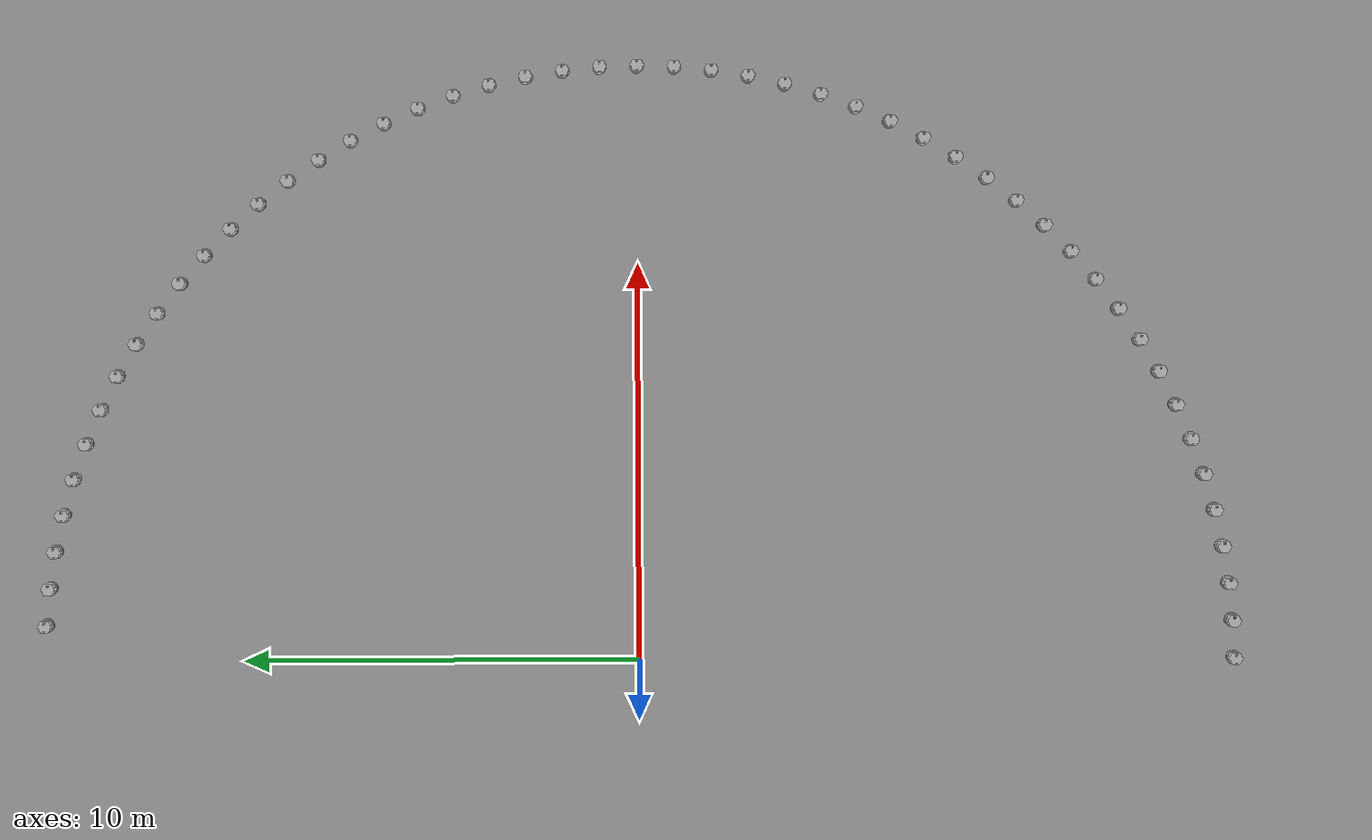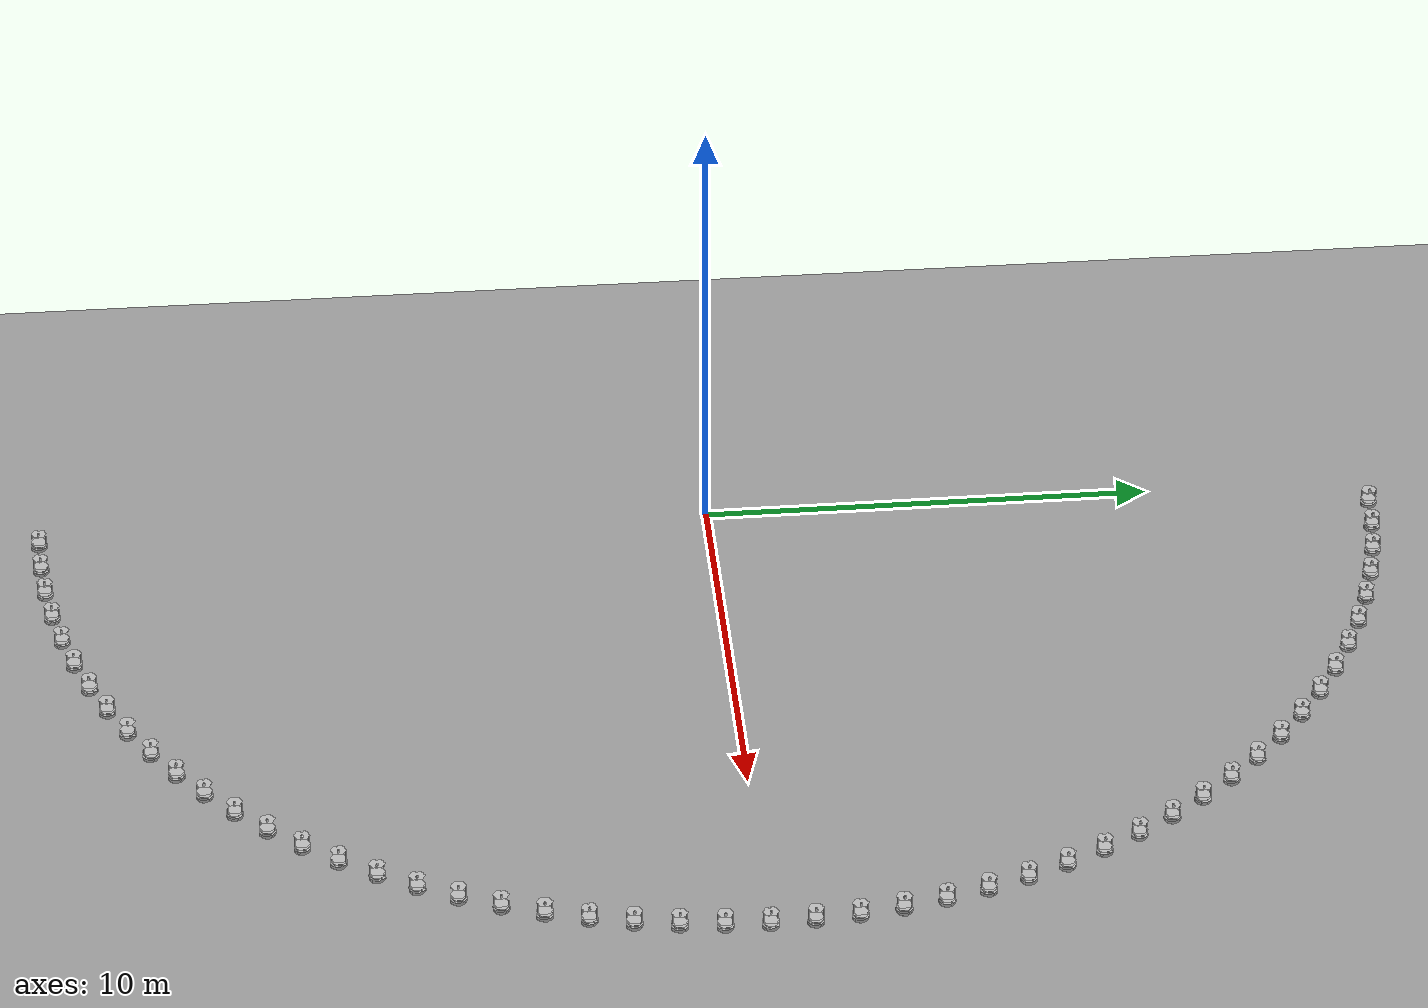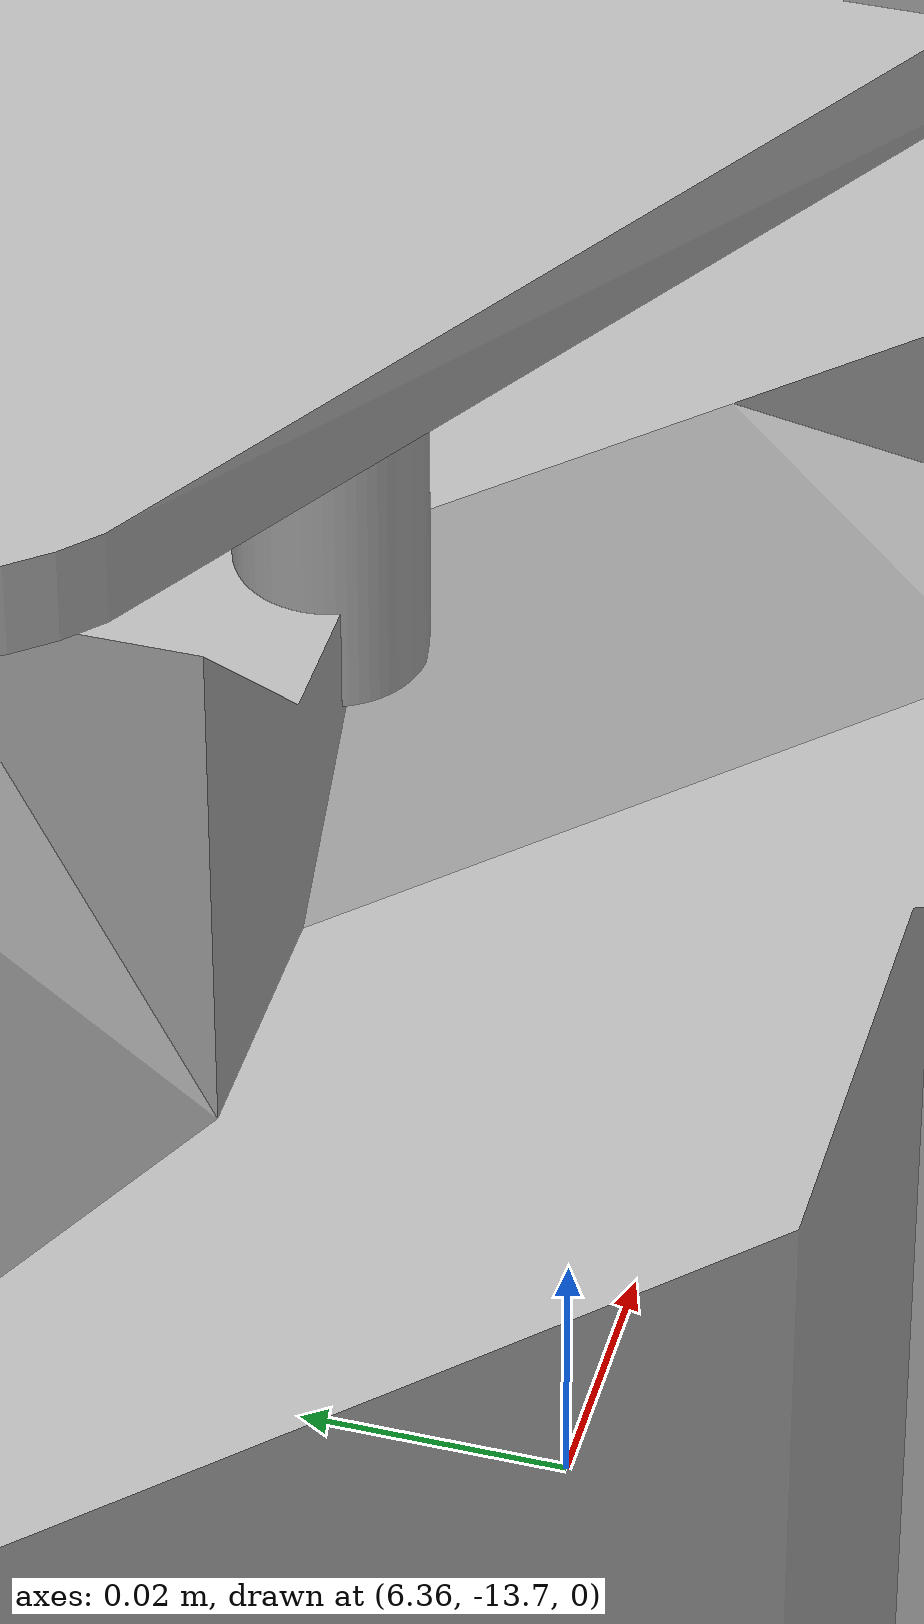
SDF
<sdf version="1.6">
 <world name="default">
  <model name="ground_plane_0">
   <static>1</static>
   <link name="link">
    <collision name="collision">
     <geometry><plane><normal>0 0 1</normal><size>100 100</size></plane></geometry>
     <surface><friction><ode><mu>100</mu><mu2>50</mu2></ode></friction></surface>
    </collision>
    <visual name="visual">
     <cast_shadows>0</cast_shadows>
     <geometry><plane><normal>0 0 1</normal><size>100 100</size></plane></geometry>
     <material>
      <script><uri>file://media/materials/scripts/gazebo.material</uri><name>Gazebo/Grey</name></script>
     </material>
    </visual>
    <velocity_decay><linear>0</linear><angular>0</angular></velocity_decay>
   </link>
   <pose>0.497681 0 0 0 -0 0</pose>
  </model>
  <model name="robot_95">
   <link name="base_footprint">
    <inertial>
     <pose>0.00554 1.4e-05 0.115513 0 -0 0</pose>
     <mass>4.31731</mass>
     <inertia>
      <ixx>0.123638</ixx>
      <ixy>-3.16036e-06</ixy>
      <ixz>0.00486006</ixz>
      <iyy>0.118098</iyy>
      <iyz>5.27701e-06</iyz>
      <izz>0.0678827</izz>
     </inertia>
    </inertial>
    <collision name="base_footprint_fixed_joint_lump__base_collision">
     <pose>0 0 0.06969 0 -0 0</pose>
     <geometry><cylinder><length>0.10938</length><radius>0.178</radius></cylinder></geometry>
    </collision>
    <collision name="base_footprint_fixed_joint_lump__caster_back_link_collision_1">
     <pose>-0.135 0 0.0192 -1.5708 0 0</pose>
     <geometry><cylinder><length>0.0176</length><radius>0.017</radius></cylinder></geometry>
     <surface>
      <contact><ode><kp>1e+06</kp><kd>100</kd><max_vel>1</max_vel><min_depth>0.001</min_depth></ode></contact>
      <friction><ode><mu>0</mu><mu2>0</mu2></ode></friction>
     </surface>
    </collision>
    <collision name="base_footprint_fixed_joint_lump__caster_front_link_collision_2">
     <pose>0.115 0 0.0172 -1.5708 0 0</pose>
     <geometry><cylinder><length>0.0176</length><radius>0.017</radius></cylinder></geometry>
     <surface>
      <contact><ode><kp>1e+06</kp><kd>100</kd><max_vel>1</max_vel><min_depth>0.001</min_depth></ode></contact>
      <friction><ode><mu>0</mu><mu2>0</mu2></ode></friction>
     </surface>
    </collision>
    <collision name="base_footprint_fixed_joint_lump__hokuyo_link_collision_3">
     <pose>0.08 0 0.4402 0 -0 0</pose>
     <geometry><box><size>0.1 0.1 0.1</size></box></geometry>
    </collision>
    <collision name="base_footprint_fixed_joint_lump__plate_bottom_link_collision_4">
     <pose>0 0 0.1408 0 -0 0</pose>
     <geometry><cylinder><length>0.006</length><radius>0.17</radius></cylinder></geometry>
    </collision>
    <collision name="base_footprint_fixed_joint_lump__plate_middle_link_collision_5">
     <pose>0 0 0.1976 0 -0 0</pose>
     <geometry><cylinder><length>0.006</length><radius>0.17</radius></cylinder></geometry>
    </collision>
    <collision name="base_footprint_fixed_joint_lump__plate_top_link_collision_6">
     <pose>0 0 0.4068 0 -0 0</pose>
     <geometry><cylinder><length>0.006</length><radius>0.17</radius></cylinder></geometry>
    </collision>
    <collision name="base_footprint_fixed_joint_lump__pole_bottom_0_link_collision_7">
     <pose>0.12 0.082 0.113 0 -0 0</pose>
     <geometry><cylinder><length>0.0492</length><radius>0.006</radius></cylinder></geometry>
    </collision>
    <collision name="base_footprint_fixed_joint_lump__pole_bottom_1_link_collision_8">
     <pose>0.055 0.12 0.113 0 -0 0</pose>
     <geometry><cylinder><length>0.0492</length><radius>0.006</radius></cylinder></geometry>
    </collision>
    <collision name="base_footprint_fixed_joint_lump__pole_bottom_2_link_collision_9">
     <pose>-0.055 0.12 0.113 0 -0 0</pose>
     <geometry><cylinder><length>0.0492</length><radius>0.006</radius></cylinder></geometry>
    </collision>
    <collision name="base_footprint_fixed_joint_lump__pole_bottom_3_link_collision_10">
     <pose>0.12 -0.082 0.113 0 -0 0</pose>
     <geometry><cylinder><length>0.0492</length><radius>0.006</radius></cylinder></geometry>
    </collision>
    <collision name="base_footprint_fixed_joint_lump__pole_bottom_4_link_collision_11">
     <pose>0.055 -0.12 0.113 0 -0 0</pose>
     <geometry><cylinder><length>0.0492</length><radius>0.006</radius></cylinder></geometry>
    </collision>
    <collision name="base_footprint_fixed_joint_lump__pole_bottom_5_link_collision_12">
     <pose>-0.055 -0.12 0.113 0 -0 0</pose>
     <geometry><cylinder><length>0.0492</length><radius>0.006</radius></cylinder></geometry>
    </collision>
    <collision name="base_footprint_fixed_joint_lump__pole_middle_0_link_collision_13">
     <pose>0.0381 0.1505 0.1742 0 -0 0</pose>
     <geometry><cylinder><length>0.0608</length><radius>0.006</radius></cylinder></geometry>
    </collision>
    <collision name="base_footprint_fixed_joint_lump__pole_middle_1_link_collision_14">
     <pose>0.0381 -0.1505 0.1742 0 -0 0</pose>
     <geometry><cylinder><length>0.0608</length><radius>0.006</radius></cylinder></geometry>
    </collision>
    <collision name="base_footprint_fixed_joint_lump__pole_middle_2_link_collision_15">
     <pose>-0.0381 0.1505 0.1742 0 -0 0</pose>
     <geometry><cylinder><length>0.0608</length><radius>0.006</radius></cylinder></geometry>
    </collision>
    <collision name="base_footprint_fixed_joint_lump__pole_middle_3_link_collision_16">
     <pose>-0.0381 -0.1505 0.1742 0 -0 0</pose>
     <geometry><cylinder><length>0.0608</length><radius>0.006</radius></cylinder></geometry>
    </collision>
    <collision name="base_footprint_fixed_joint_lump__pole_top_0_link_collision_17">
     <pose>0.0381 0.1505 0.3022 0 -0 0</pose>
     <geometry><cylinder><length>0.2032</length><radius>0.006</radius></cylinder></geometry>
    </collision>
    <collision name="base_footprint_fixed_joint_lump__pole_top_1_link_collision_18">
     <pose>0.0381 -0.1505 0.3022 0 -0 0</pose>
     <geometry><cylinder><length>0.2032</length><radius>0.006</radius></cylinder></geometry>
    </collision>
    <collision name="base_footprint_fixed_joint_lump__pole_top_2_link_collision_19">
     <pose>-0.0381 0.1505 0.3022 0 -0 0</pose>
     <geometry><cylinder><length>0.2032</length><radius>0.006</radius></cylinder></geometry>
    </collision>
    <collision name="base_footprint_fixed_joint_lump__pole_top_3_link_collision_20">
     <pose>-0.0381 -0.1505 0.3022 0 -0 0</pose>
     <geometry><cylinder><length>0.2032</length><radius>0.006</radius></cylinder></geometry>
    </collision>
    <visual name="base_footprint_fixed_joint_lump__base_link_visual">
     <pose>0.001 0 0.06219 0 -0 0</pose>
     <geometry>
      <mesh><scale>1 1 1</scale><uri>/home/chase/ws/src/kobuki/kobuki_description/meshes/main_body.dae</uri></mesh>
     </geometry>
     <material><script><uri>__default__</uri><name>__default__</name></script></material>
    </visual>
    <visual name="base_footprint_fixed_joint_lump__hokuyo_link_visual_1">
     <pose>0.08 0 0.4402 0 -0 0</pose>
     <geometry>
      <mesh>
       <scale>1 1 1</scale>
       <uri>/home/chase/ws/src/turtlebot_hokuyo/turtlebot_description/meshes/sensors/hokuyo.dae</uri>
      </mesh>
     </geometry>
     <material><script><uri>__default__</uri><name>__default__</name></script></material>
    </visual>
    <visual name="base_footprint_fixed_joint_lump__plate_bottom_link_visual_2">
     <pose>0.02364 0 0.1408 0 -0 0</pose>
     <geometry>
      <mesh>
       <scale>1 1 1</scale>
       <uri>/home/chase/ws/src/turtlebot_hokuyo/turtlebot_description/meshes/stacks/hexagons/plate_bottom.dae</uri>
      </mesh>
     </geometry>
    </visual>
    <visual name="base_footprint_fixed_joint_lump__plate_middle_link_visual_3">
     <pose>-0.01364 0 0.1976 0 -0 0</pose>
     <geometry>
      <mesh>
       <scale>1 1 1</scale>
       <uri>/home/chase/ws/src/turtlebot_hokuyo/turtlebot_description/meshes/stacks/hexagons/plate_middle.dae</uri>
      </mesh>
     </geometry>
    </visual>
    <visual name="base_footprint_fixed_joint_lump__plate_top_link_visual_4">
     <pose>-0.01364 0 0.4068 0 -0 0</pose>
     <geometry>
      <mesh>
       <scale>1 1 1</scale>
       <uri>/home/chase/ws/src/turtlebot_hokuyo/turtlebot_description/meshes/stacks/hexagons/plate_top.dae</uri>
      </mesh>
     </geometry>
    </visual>
    <visual name="base_footprint_fixed_joint_lump__pole_bottom_0_link_visual_5">
     <pose>0.12 0.082 0.113 0 -0 0</pose>
     <geometry>
      <mesh>
       <scale>1 1 1</scale>
       <uri>/home/chase/ws/src/turtlebot_hokuyo/turtlebot_description/meshes/stacks/hexagons/pole_bottom.dae</uri>
      </mesh>
     </geometry>
    </visual>
    <visual name="base_footprint_fixed_joint_lump__pole_bottom_1_link_visual_6">
     <pose>0.055 0.12 0.113 0 -0 0</pose>
     <geometry>
      <mesh>
       <scale>1 1 1</scale>
       <uri>/home/chase/ws/src/turtlebot_hokuyo/turtlebot_description/meshes/stacks/hexagons/pole_bottom.dae</uri>
      </mesh>
     </geometry>
    </visual>
    <visual name="base_footprint_fixed_joint_lump__pole_bottom_2_link_visual_7">
     <pose>-0.055 0.12 0.113 0 -0 0</pose>
     <geometry>
      <mesh>
       <scale>1 1 1</scale>
       <uri>/home/chase/ws/src/turtlebot_hokuyo/turtlebot_description/meshes/stacks/hexagons/pole_bottom.dae</uri>
      </mesh>
     </geometry>
    </visual>
    <visual name="base_footprint_fixed_joint_lump__pole_bottom_3_link_visual_8">
     <pose>0.12 -0.082 0.113 0 -0 0</pose>
     <geometry>
      <mesh>
       <scale>1 1 1</scale>
       <uri>/home/chase/ws/src/turtlebot_hokuyo/turtlebot_description/meshes/stacks/hexagons/pole_bottom.dae</uri>
      </mesh>
     </geometry>
    </visual>
    <visual name="base_footprint_fixed_joint_lump__pole_bottom_4_link_visual_9">
     <pose>0.055 -0.12 0.113 0 -0 0</pose>
     <geometry>
      <mesh>
       <scale>1 1 1</scale>
       <uri>/home/chase/ws/src/turtlebot_hokuyo/turtlebot_description/meshes/stacks/hexagons/pole_bottom.dae</uri>
      </mesh>
     </geometry>
    </visual>
    <visual name="base_footprint_fixed_joint_lump__pole_bottom_5_link_visual_10">
     <pose>-0.055 -0.12 0.113 0 -0 0</pose>
     <geometry>
      <mesh>
       <scale>1 1 1</scale>
       <uri>/home/chase/ws/src/turtlebot_hokuyo/turtlebot_description/meshes/stacks/hexagons/pole_bottom.dae</uri>
      </mesh>
     </geometry>
    </visual>
    <visual name="base_footprint_fixed_joint_lump__pole_middle_0_link_visual_11">
     <pose>0.0381 0.1505 0.1742 3.14159 -0 3.14159</pose>
     <geometry>
      <mesh>
       <scale>1 1 1</scale>
       <uri>/home/chase/ws/src/turtlebot_hokuyo/turtlebot_description/meshes/stacks/hexagons/pole_middle.dae</uri>
      </mesh>
     </geometry>
    </visual>
    <visual name="base_footprint_fixed_joint_lump__pole_middle_1_link_visual_12">
     <pose>0.0381 -0.1505 0.1742 3.14159 -0 3.14159</pose>
     <geometry>
      <mesh>
       <scale>1 1 1</scale>
       <uri>/home/chase/ws/src/turtlebot_hokuyo/turtlebot_description/meshes/stacks/hexagons/pole_middle.dae</uri>
      </mesh>
     </geometry>
    </visual>
    <visual name="base_footprint_fixed_joint_lump__pole_middle_2_link_visual_13">
     <pose>-0.0381 0.1505 0.1742 3.14159 -0 3.14159</pose>
     <geometry>
      <mesh>
       <scale>1 1 1</scale>
       <uri>/home/chase/ws/src/turtlebot_hokuyo/turtlebot_description/meshes/stacks/hexagons/pole_middle.dae</uri>
      </mesh>
     </geometry>
    </visual>
    <visual name="base_footprint_fixed_joint_lump__pole_middle_3_link_visual_14">
     <pose>-0.0381 -0.1505 0.1742 3.14159 -0 3.14159</pose>
     <geometry>
      <mesh>
       <scale>1 1 1</scale>
       <uri>/home/chase/ws/src/turtlebot_hokuyo/turtlebot_description/meshes/stacks/hexagons/pole_middle.dae</uri>
      </mesh>
     </geometry>
    </visual>
    <visual name="base_footprint_fixed_joint_lump__pole_top_0_link_visual_15">
     <pose>0.0381 0.1505 0.3022 0 -0 0</pose>
     <geometry>
      <mesh>
       <scale>1 1 1</scale>
       <uri>/home/chase/ws/src/turtlebot_hokuyo/turtlebot_description/meshes/stacks/hexagons/pole_top.dae</uri>
      </mesh>
     </geometry>
    </visual>
    <visual name="base_footprint_fixed_joint_lump__pole_top_1_link_visual_16">
     <pose>0.0381 -0.1505 0.3022 0 -0 0</pose>
     <geometry>
      <mesh>
       <scale>1 1 1</scale>
       <uri>/home/chase/ws/src/turtlebot_hokuyo/turtlebot_description/meshes/stacks/hexagons/pole_top.dae</uri>
      </mesh>
     </geometry>
    </visual>
    <visual name="base_footprint_fixed_joint_lump__pole_top_2_link_visual_17">
     <pose>-0.0381 0.1505 0.3022 0 -0 0</pose>
     <geometry>
      <mesh>
       <scale>1 1 1</scale>
       <uri>/home/chase/ws/src/turtlebot_hokuyo/turtlebot_description/meshes/stacks/hexagons/pole_top.dae</uri>
      </mesh>
     </geometry>
    </visual>
    <visual name="base_footprint_fixed_joint_lump__pole_top_3_link_visual_18">
     <pose>-0.0381 -0.1505 0.3022 0 -0 0</pose>
     <geometry>
      <mesh>
       <scale>1 1 1</scale>
       <uri>/home/chase/ws/src/turtlebot_hokuyo/turtlebot_description/meshes/stacks/hexagons/pole_top.dae</uri>
      </mesh>
     </geometry>
    </visual>
    <sensor name="bumpers" type="contact">
     <always_on>0</always_on>
     <update_rate>0.01</update_rate>
     <visualize>0</visualize>
     <contact>
      <collision>base_footprint_fixed_joint_lump__base_collision</collision>
      <topic>__default_topic__</topic>
     </contact>
     <pose>0 0 0.0102 0 -0 0</pose>
    </sensor>
    <sensor name="cliff_sensor_front" type="ray">
     <always_on>0</always_on>
     <update_rate>0.01</update_rate>
     <visualize>0</visualize>
     <ray>
      <scan>
       <horizontal>
        <samples>50</samples>
        <resolution>1</resolution>
        <min_angle>-0.0436</min_angle>
        <max_angle>0.0436</max_angle>
       </horizontal>
       <vertical><samples>1</samples><min_angle>0</min_angle><max_angle>0</max_angle></vertical>
      </scan>
      <range><min>0.01</min><max>0.15</max><resolution>1</resolution></range>
     </ray>
     <pose>0.156 0 0.0316 3.14159 1.57079 3.14159</pose>
    </sensor>
    <sensor name="cliff_sensor_left" type="ray">
     <always_on>0</always_on>
     <update_rate>0.01</update_rate>
     <visualize>0</visualize>
     <ray>
      <scan>
       <horizontal>
        <samples>50</samples>
        <resolution>1</resolution>
        <min_angle>-0.0436</min_angle>
        <max_angle>0.0436</max_angle>
       </horizontal>
       <vertical><samples>1</samples><min_angle>0</min_angle><max_angle>0</max_angle></vertical>
      </scan>
      <range><min>0.01</min><max>0.15</max><resolution>1</resolution></range>
     </ray>
     <pose>0.08734 0.13601 0.0316 3.14159 1.57079 3.14159</pose>
    </sensor>
    <sensor name="cliff_sensor_right" type="ray">
     <always_on>0</always_on>
     <update_rate>0.01</update_rate>
     <visualize>0</visualize>
     <ray>
      <scan>
       <horizontal>
        <samples>50</samples>
        <resolution>1</resolution>
        <min_angle>-0.0436</min_angle>
        <max_angle>0.0436</max_angle>
       </horizontal>
       <vertical><samples>1</samples><min_angle>0</min_angle><max_angle>0</max_angle></vertical>
      </scan>
      <range><min>0.01</min><max>0.15</max><resolution>1</resolution></range>
     </ray>
     <pose>0.085 -0.13601 0.0316 3.14159 1.57079 3.14159</pose>
    </sensor>
    <sensor name="imu" type="imu">
     <always_on>0</always_on>
     <update_rate>0.01</update_rate>
     <visualize>0</visualize>
     <imu>
      <angular_velocity>
       <x>
        <noise type="gaussian">
         <mean>0</mean>
         <stddev>1.96e-06</stddev>
         <bias_mean>0</bias_mean>
         <bias_stddev>0</bias_stddev>
        </noise>
       </x>
       <y>
        <noise type="gaussian">
         <mean>0</mean>
         <stddev>1.96e-06</stddev>
         <bias_mean>0</bias_mean>
         <bias_stddev>0</bias_stddev>
        </noise>
       </y>
       <z>
        <noise type="gaussian">
         <mean>0</mean>
         <stddev>1.96e-06</stddev>
         <bias_mean>0</bias_mean>
         <bias_stddev>0</bias_stddev>
        </noise>
       </z>
      </angular_velocity>
      <linear_acceleration>
       <x>
        <noise type="gaussian">
         <mean>0</mean>
         <stddev>0.017</stddev>
         <bias_mean>0.1</bias_mean>
         <bias_stddev>0.001</bias_stddev>
        </noise>
       </x>
       <y>
        <noise type="gaussian">
         <mean>0</mean>
         <stddev>0.017</stddev>
         <bias_mean>0.1</bias_mean>
         <bias_stddev>0.001</bias_stddev>
        </noise>
       </y>
       <z>
        <noise type="gaussian">
         <mean>0</mean>
         <stddev>0.017</stddev>
         <bias_mean>0.1</bias_mean>
         <bias_stddev>0.001</bias_stddev>
        </noise>
       </z>
      </linear_acceleration>
     </imu>
     <pose>0.056 0.062 0.0304 0 -0 0</pose>
    </sensor>
    <sensor name="head_hokuyo_sensor" type="gpu_ray">
     <visualize>0</visualize>
     <update_rate>10</update_rate>
     <ray>
      <scan>
       <horizontal>
        <samples>512</samples>
        <resolution>1</resolution>
        <min_angle>-1.57</min_angle>
        <max_angle>1.57</max_angle>
       </horizontal>
      </scan>
      <range><min>0.05</min><max>4</max><resolution>0.1</resolution></range>
      <noise><type>gaussian</type><mean>0</mean><stddev>0.04</stddev></noise>
     </ray>
     <plugin name="gazebo_ros_head_hokuyo_controller" filename="libgazebo_ros_gpu_laser.so">
      <topicName>scan</topicName>
      <frameName>hokuyo_link</frameName>
      <robotNamespace>/robot_95/</robotNamespace>
     </plugin>
     <pose>0.08 0 0.4402 0 -0 0</pose>
    </sensor>
   </link>
   <link name="wheel_left_link">
    <pose>0 0.115 0.0352 -1.5708 0 0</pose>
    <inertial>
     <mass>0.01</mass>
     <inertia><ixx>0.001</ixx><ixy>0</ixy><ixz>0</ixz><iyy>0.001</iyy><iyz>0</iyz><izz>0.001</izz></inertia>
    </inertial>
    <collision name="wheel_left_link_collision">
     <geometry><cylinder><length>0.0206</length><radius>0.0352</radius></cylinder></geometry>
     <surface>
      <contact><ode><kp>1e+06</kp><kd>100</kd><max_vel>1</max_vel><min_depth>0.001</min_depth></ode></contact>
      <friction><ode><mu>1</mu><mu2>1</mu2></ode></friction>
     </surface>
    </collision>
    <visual name="wheel_left_link_visual">
     <geometry>
      <mesh><scale>1 1 1</scale><uri>/home/chase/ws/src/kobuki/kobuki_description/meshes/wheel.dae</uri></mesh>
     </geometry>
     <material><script><uri>__default__</uri><name>__default__</name></script></material>
    </visual>
   </link>
   <joint name="wheel_left_joint" type="revolute">
    <child>wheel_left_link</child>
    <parent>base_footprint</parent>
    <axis>
     <xyz>0 1 0</xyz>
     <limit><lower>-1e+16</lower><upper>1e+16</upper></limit>
     <dynamics><spring_reference>0</spring_reference><spring_stiffness>0</spring_stiffness></dynamics>
     <use_parent_model_frame>1</use_parent_model_frame>
    </axis>
   </joint>
   <link name="wheel_right_link">
    <pose>0 -0.115 0.0352 -1.5708 0 0</pose>
    <inertial>
     <mass>0.01</mass>
     <inertia><ixx>0.001</ixx><ixy>0</ixy><ixz>0</ixz><iyy>0.001</iyy><iyz>0</iyz><izz>0.001</izz></inertia>
    </inertial>
    <collision name="wheel_right_link_collision">
     <geometry><cylinder><length>0.0206</length><radius>0.035</radius></cylinder></geometry>
     <surface>
      <contact><ode><kp>1e+06</kp><kd>100</kd><max_vel>1</max_vel><min_depth>0.001</min_depth></ode></contact>
      <friction><ode><mu>1</mu><mu2>1</mu2></ode></friction>
     </surface>
    </collision>
    <visual name="wheel_right_link_visual">
     <geometry>
      <mesh><scale>1 1 1</scale><uri>/home/chase/ws/src/kobuki/kobuki_description/meshes/wheel.dae</uri></mesh>
     </geometry>
     <material><script><uri>__default__</uri><name>__default__</name></script></material>
    </visual>
   </link>
   <joint name="wheel_right_joint" type="revolute">
    <child>wheel_right_link</child>
    <parent>base_footprint</parent>
    <axis>
     <xyz>0 1 0</xyz>
     <limit><lower>-1e+16</lower><upper>1e+16</upper></limit>
     <dynamics><spring_reference>0</spring_reference><spring_stiffness>0</spring_stiffness></dynamics>
     <use_parent_model_frame>1</use_parent_model_frame>
    </axis>
   </joint>
   <static>0</static>
   <plugin name="kobuki_controller" filename="libgazebo_ros_kobuki.so">
    <publish_tf>1</publish_tf>
    <left_wheel_joint_name>wheel_left_joint</left_wheel_joint_name>
    <right_wheel_joint_name>wheel_right_joint</right_wheel_joint_name>
    <wheel_separation>.230</wheel_separation>
    <wheel_diameter>0.070</wheel_diameter>
    <torque>1.0</torque>
    <velocity_command_timeout>0.6</velocity_command_timeout>
    <cliff_sensor_left_name>cliff_sensor_left</cliff_sensor_left_name>
    <cliff_sensor_center_name>cliff_sensor_front</cliff_sensor_center_name>
    <cliff_sensor_right_name>cliff_sensor_right</cliff_sensor_right_name>
    <cliff_detection_threshold>0.04</cliff_detection_threshold>
    <bumper_name>bumpers</bumper_name>
    <imu_name>imu</imu_name>
    <robotNamespace>/robot_95/</robotNamespace>
   </plugin>
   <pose>14.2655 -4.63521 -0.000235 0.000773 -0.000352 -0.003565</pose>
  </model>
  <model name="robot_78">
   <link name="base_footprint">
    <inertial>
     <pose>0.00554 1.4e-05 0.115513 0 -0 0</pose>
     <mass>4.31731</mass>
     <inertia>
      <ixx>0.123638</ixx>
      <ixy>-3.16036e-06</ixy>
      <ixz>0.00486006</ixz>
      <iyy>0.118098</iyy>
      <iyz>5.27701e-06</iyz>
      <izz>0.0678827</izz>
     </inertia>
    </inertial>
    <collision name="base_footprint_fixed_joint_lump__base_collision">
     <pose>0 0 0.06969 0 -0 0</pose>
     <geometry><cylinder><length>0.10938</length><radius>0.178</radius></cylinder></geometry>
    </collision>
    <collision name="base_footprint_fixed_joint_lump__caster_back_link_collision_1">
     <pose>-0.135 0 0.0192 -1.5708 0 0</pose>
     <geometry><cylinder><length>0.0176</length><radius>0.017</radius></cylinder></geometry>
     <surface>
      <contact><ode><kp>1e+06</kp><kd>100</kd><max_vel>1</max_vel><min_depth>0.001</min_depth></ode></contact>
      <friction><ode><mu>0</mu><mu2>0</mu2></ode></friction>
     </surface>
    </collision>
    <collision name="base_footprint_fixed_joint_lump__caster_front_link_collision_2">
     <pose>0.115 0 0.0172 -1.5708 0 0</pose>
     <geometry><cylinder><length>0.0176</length><radius>0.017</radius></cylinder></geometry>
     <surface>
      <contact><ode><kp>1e+06</kp><kd>100</kd><max_vel>1</max_vel><min_depth>0.001</min_depth></ode></contact>
      <friction><ode><mu>0</mu><mu2>0</mu2></ode></friction>
     </surface>
    </collision>
    <collision name="base_footprint_fixed_joint_lump__hokuyo_link_collision_3">
     <pose>0.08 0 0.4402 0 -0 0</pose>
     <geometry><box><size>0.1 0.1 0.1</size></box></geometry>
    </collision>
    <collision name="base_footprint_fixed_joint_lump__plate_bottom_link_collision_4">
     <pose>0 0 0.1408 0 -0 0</pose>
     <geometry><cylinder><length>0.006</length><radius>0.17</radius></cylinder></geometry>
    </collision>
    <collision name="base_footprint_fixed_joint_lump__plate_middle_link_collision_5">
     <pose>0 0 0.1976 0 -0 0</pose>
     <geometry><cylinder><length>0.006</length><radius>0.17</radius></cylinder></geometry>
    </collision>
    <collision name="base_footprint_fixed_joint_lump__plate_top_link_collision_6">
     <pose>0 0 0.4068 0 -0 0</pose>
     <geometry><cylinder><length>0.006</length><radius>0.17</radius></cylinder></geometry>
    </collision>
    <collision name="base_footprint_fixed_joint_lump__pole_bottom_0_link_collision_7">
     <pose>0.12 0.082 0.113 0 -0 0</pose>
     <geometry><cylinder><length>0.0492</length><radius>0.006</radius></cylinder></geometry>
    </collision>
    <collision name="base_footprint_fixed_joint_lump__pole_bottom_1_link_collision_8">
     <pose>0.055 0.12 0.113 0 -0 0</pose>
     <geometry><cylinder><length>0.0492</length><radius>0.006</radius></cylinder></geometry>
    </collision>
    <collision name="base_footprint_fixed_joint_lump__pole_bottom_2_link_collision_9">
     <pose>-0.055 0.12 0.113 0 -0 0</pose>
     <geometry><cylinder><length>0.0492</length><radius>0.006</radius></cylinder></geometry>
    </collision>
    <collision name="base_footprint_fixed_joint_lump__pole_bottom_3_link_collision_10">
     <pose>0.12 -0.082 0.113 0 -0 0</pose>
     <geometry><cylinder><length>0.0492</length><radius>0.006</radius></cylinder></geometry>
    </collision>
    <collision name="base_footprint_fixed_joint_lump__pole_bottom_4_link_collision_11">
     <pose>0.055 -0.12 0.113 0 -0 0</pose>
     <geometry><cylinder><length>0.0492</length><radius>0.006</radius></cylinder></geometry>
    </collision>
    <collision name="base_footprint_fixed_joint_lump__pole_bottom_5_link_collision_12">
     <pose>-0.055 -0.12 0.113 0 -0 0</pose>
     <geometry><cylinder><length>0.0492</length><radius>0.006</radius></cylinder></geometry>
    </collision>
    <collision name="base_footprint_fixed_joint_lump__pole_middle_0_link_collision_13">
     <pose>0.0381 0.1505 0.1742 0 -0 0</pose>
     <geometry><cylinder><length>0.0608</length><radius>0.006</radius></cylinder></geometry>
    </collision>
    <collision name="base_footprint_fixed_joint_lump__pole_middle_1_link_collision_14">
     <pose>0.0381 -0.1505 0.1742 0 -0 0</pose>
     <geometry><cylinder><length>0.0608</length><radius>0.006</radius></cylinder></geometry>
    </collision>
    <collision name="base_footprint_fixed_joint_lump__pole_middle_2_link_collision_15">
     <pose>-0.0381 0.1505 0.1742 0 -0 0</pose>
     <geometry><cylinder><length>0.0608</length><radius>0.006</radius></cylinder></geometry>
    </collision>
    <collision name="base_footprint_fixed_joint_lump__pole_middle_3_link_collision_16">
     <pose>-0.0381 -0.1505 0.1742 0 -0 0</pose>
     <geometry><cylinder><length>0.0608</length><radius>0.006</radius></cylinder></geometry>
    </collision>
    <collision name="base_footprint_fixed_joint_lump__pole_top_0_link_collision_17">
     <pose>0.0381 0.1505 0.3022 0 -0 0</pose>
     <geometry><cylinder><length>0.2032</length><radius>0.006</radius></cylinder></geometry>
    </collision>
    <collision name="base_footprint_fixed_joint_lump__pole_top_1_link_collision_18">
     <pose>0.0381 -0.1505 0.3022 0 -0 0</pose>
     <geometry><cylinder><length>0.2032</length><radius>0.006</radius></cylinder></geometry>
    </collision>
    <collision name="base_footprint_fixed_joint_lump__pole_top_2_link_collision_19">
     <pose>-0.0381 0.1505 0.3022 0 -0 0</pose>
     <geometry><cylinder><length>0.2032</length><radius>0.006</radius></cylinder></geometry>
    </collision>
    <collision name="base_footprint_fixed_joint_lump__pole_top_3_link_collision_20">
     <pose>-0.0381 -0.1505 0.3022 0 -0 0</pose>
     <geometry><cylinder><length>0.2032</length><radius>0.006</radius></cylinder></geometry>
    </collision>
    <visual name="base_footprint_fixed_joint_lump__base_link_visual">
     <pose>0.001 0 0.06219 0 -0 0</pose>
     <geometry>
      <mesh><scale>1 1 1</scale><uri>/home/chase/ws/src/kobuki/kobuki_description/meshes/main_body.dae</uri></mesh>
     </geometry>
     <material><script><uri>__default__</uri><name>__default__</name></script></material>
    </visual>
    <visual name="base_footprint_fixed_joint_lump__hokuyo_link_visual_1">
     <pose>0.08 0 0.4402 0 -0 0</pose>
     <geometry>
      <mesh>
       <scale>1 1 1</scale>
       <uri>/home/chase/ws/src/turtlebot_hokuyo/turtlebot_description/meshes/sensors/hokuyo.dae</uri>
      </mesh>
     </geometry>
     <material><script><uri>__default__</uri><name>__default__</name></script></material>
    </visual>
    <visual name="base_footprint_fixed_joint_lump__plate_bottom_link_visual_2">
     <pose>0.02364 0 0.1408 0 -0 0</pose>
     <geometry>
      <mesh>
       <scale>1 1 1</scale>
       <uri>/home/chase/ws/src/turtlebot_hokuyo/turtlebot_description/meshes/stacks/hexagons/plate_bottom.dae</uri>
      </mesh>
     </geometry>
    </visual>
    <visual name="base_footprint_fixed_joint_lump__plate_middle_link_visual_3">
     <pose>-0.01364 0 0.1976 0 -0 0</pose>
     <geometry>
      <mesh>
       <scale>1 1 1</scale>
       <uri>/home/chase/ws/src/turtlebot_hokuyo/turtlebot_description/meshes/stacks/hexagons/plate_middle.dae</uri>
      </mesh>
     </geometry>
    </visual>
    <visual name="base_footprint_fixed_joint_lump__plate_top_link_visual_4">
     <pose>-0.01364 0 0.4068 0 -0 0</pose>
     <geometry>
      <mesh>
       <scale>1 1 1</scale>
       <uri>/home/chase/ws/src/turtlebot_hokuyo/turtlebot_description/meshes/stacks/hexagons/plate_top.dae</uri>
      </mesh>
     </geometry>
    </visual>
    <visual name="base_footprint_fixed_joint_lump__pole_bottom_0_link_visual_5">
     <pose>0.12 0.082 0.113 0 -0 0</pose>
     <geometry>
      <mesh>
       <scale>1 1 1</scale>
       <uri>/home/chase/ws/src/turtlebot_hokuyo/turtlebot_description/meshes/stacks/hexagons/pole_bottom.dae</uri>
      </mesh>
     </geometry>
    </visual>
    <visual name="base_footprint_fixed_joint_lump__pole_bottom_1_link_visual_6">
     <pose>0.055 0.12 0.113 0 -0 0</pose>
     <geometry>
      <mesh>
       <scale>1 1 1</scale>
       <uri>/home/chase/ws/src/turtlebot_hokuyo/turtlebot_description/meshes/stacks/hexagons/pole_bottom.dae</uri>
      </mesh>
     </geometry>
    </visual>
    <visual name="base_footprint_fixed_joint_lump__pole_bottom_2_link_visual_7">
     <pose>-0.055 0.12 0.113 0 -0 0</pose>
     <geometry>
      <mesh>
       <scale>1 1 1</scale>
       <uri>/home/chase/ws/src/turtlebot_hokuyo/turtlebot_description/meshes/stacks/hexagons/pole_bottom.dae</uri>
      </mesh>
     </geometry>
    </visual>
    <visual name="base_footprint_fixed_joint_lump__pole_bottom_3_link_visual_8">
     <pose>0.12 -0.082 0.113 0 -0 0</pose>
     <geometry>
      <mesh>
       <scale>1 1 1</scale>
       <uri>/home/chase/ws/src/turtlebot_hokuyo/turtlebot_description/meshes/stacks/hexagons/pole_bottom.dae</uri>
      </mesh>
     </geometry>
    </visual>
    <visual name="base_footprint_fixed_joint_lump__pole_bottom_4_link_visual_9">
     <pose>0.055 -0.12 0.113 0 -0 0</pose>
     <geometry>
      <mesh>
       <scale>1 1 1</scale>
       <uri>/home/chase/ws/src/turtlebot_hokuyo/turtlebot_description/meshes/stacks/hexagons/pole_bottom.dae</uri>
      </mesh>
     </geometry>
    </visual>
    <visual name="base_footprint_fixed_joint_lump__pole_bottom_5_link_visual_10">
     <pose>-0.055 -0.12 0.113 0 -0 0</pose>
     <geometry>
      <mesh>
       <scale>1 1 1</scale>
       <uri>/home/chase/ws/src/turtlebot_hokuyo/turtlebot_description/meshes/stacks/hexagons/pole_bottom.dae</uri>
      </mesh>
     </geometry>
    </visual>
    <visual name="base_footprint_fixed_joint_lump__pole_middle_0_link_visual_11">
     <pose>0.0381 0.1505 0.1742 3.14159 -0 3.14159</pose>
     <geometry>
      <mesh>
       <scale>1 1 1</scale>
       <uri>/home/chase/ws/src/turtlebot_hokuyo/turtlebot_description/meshes/stacks/hexagons/pole_middle.dae</uri>
      </mesh>
     </geometry>
    </visual>
    <visual name="base_footprint_fixed_joint_lump__pole_middle_1_link_visual_12">
     <pose>0.0381 -0.1505 0.1742 3.14159 -0 3.14159</pose>
     <geometry>
      <mesh>
       <scale>1 1 1</scale>
       <uri>/home/chase/ws/src/turtlebot_hokuyo/turtlebot_description/meshes/stacks/hexagons/pole_middle.dae</uri>
      </mesh>
     </geometry>
    </visual>
    <visual name="base_footprint_fixed_joint_lump__pole_middle_2_link_visual_13">
     <pose>-0.0381 0.1505 0.1742 3.14159 -0 3.14159</pose>
     <geometry>
      <mesh>
       <scale>1 1 1</scale>
       <uri>/home/chase/ws/src/turtlebot_hokuyo/turtlebot_description/meshes/stacks/hexagons/pole_middle.dae</uri>
      </mesh>
     </geometry>
    </visual>
    <visual name="base_footprint_fixed_joint_lump__pole_middle_3_link_visual_14">
     <pose>-0.0381 -0.1505 0.1742 3.14159 -0 3.14159</pose>
     <geometry>
      <mesh>
       <scale>1 1 1</scale>
       <uri>/home/chase/ws/src/turtlebot_hokuyo/turtlebot_description/meshes/stacks/hexagons/pole_middle.dae</uri>
      </mesh>
     </geometry>
    </visual>
    <visual name="base_footprint_fixed_joint_lump__pole_top_0_link_visual_15">
     <pose>0.0381 0.1505 0.3022 0 -0 0</pose>
     <geometry>
      <mesh>
       <scale>1 1 1</scale>
       <uri>/home/chase/ws/src/turtlebot_hokuyo/turtlebot_description/meshes/stacks/hexagons/pole_top.dae</uri>
      </mesh>
     </geometry>
    </visual>
    <visual name="base_footprint_fixed_joint_lump__pole_top_1_link_visual_16">
     <pose>0.0381 -0.1505 0.3022 0 -0 0</pose>
     <geometry>
      <mesh>
       <scale>1 1 1</scale>
       <uri>/home/chase/ws/src/turtlebot_hokuyo/turtlebot_description/meshes/stacks/hexagons/pole_top.dae</uri>
      </mesh>
     </geometry>
    </visual>
    <visual name="base_footprint_fixed_joint_lump__pole_top_2_link_visual_17">
     <pose>-0.0381 0.1505 0.3022 0 -0 0</pose>
     <geometry>
      <mesh>
       <scale>1 1 1</scale>
       <uri>/home/chase/ws/src/turtlebot_hokuyo/turtlebot_description/meshes/stacks/hexagons/pole_top.dae</uri>
      </mesh>
     </geometry>
    </visual>
    <visual name="base_footprint_fixed_joint_lump__pole_top_3_link_visual_18">
     <pose>-0.0381 -0.1505 0.3022 0 -0 0</pose>
     <geometry>
      <mesh>
       <scale>1 1 1</scale>
       <uri>/home/chase/ws/src/turtlebot_hokuyo/turtlebot_description/meshes/stacks/hexagons/pole_top.dae</uri>
      </mesh>
     </geometry>
    </visual>
    <sensor name="bumpers" type="contact">
     <always_on>0</always_on>
     <update_rate>0.01</update_rate>
     <visualize>0</visualize>
     <contact>
      <collision>base_footprint_fixed_joint_lump__base_collision</collision>
      <topic>__default_topic__</topic>
     </contact>
     <pose>0 0 0.0102 0 -0 0</pose>
    </sensor>
    <sensor name="cliff_sensor_front" type="ray">
     <always_on>0</always_on>
     <update_rate>0.01</update_rate>
     <visualize>0</visualize>
     <ray>
      <scan>
       <horizontal>
        <samples>50</samples>
        <resolution>1</resolution>
        <min_angle>-0.0436</min_angle>
        <max_angle>0.0436</max_angle>
       </horizontal>
       <vertical><samples>1</samples><min_angle>0</min_angle><max_angle>0</max_angle></vertical>
      </scan>
      <range><min>0.01</min><max>0.15</max><resolution>1</resolution></range>
     </ray>
     <pose>0.156 0 0.0316 3.14159 1.57079 3.14159</pose>
    </sensor>
    <sensor name="cliff_sensor_left" type="ray">
     <always_on>0</always_on>
     <update_rate>0.01</update_rate>
     <visualize>0</visualize>
     <ray>
      <scan>
       <horizontal>
        <samples>50</samples>
        <resolution>1</resolution>
        <min_angle>-0.0436</min_angle>
        <max_angle>0.0436</max_angle>
       </horizontal>
       <vertical><samples>1</samples><min_angle>0</min_angle><max_angle>0</max_angle></vertical>
      </scan>
      <range><min>0.01</min><max>0.15</max><resolution>1</resolution></range>
     </ray>
     <pose>0.08734 0.13601 0.0316 3.14159 1.57079 3.14159</pose>
    </sensor>
    <sensor name="cliff_sensor_right" type="ray">
     <always_on>0</always_on>
     <update_rate>0.01</update_rate>
     <visualize>0</visualize>
     <ray>
      <scan>
       <horizontal>
        <samples>50</samples>
        <resolution>1</resolution>
        <min_angle>-0.0436</min_angle>
        <max_angle>0.0436</max_angle>
       </horizontal>
       <vertical><samples>1</samples><min_angle>0</min_angle><max_angle>0</max_angle></vertical>
      </scan>
      <range><min>0.01</min><max>0.15</max><resolution>1</resolution></range>
     </ray>
     <pose>0.085 -0.13601 0.0316 3.14159 1.57079 3.14159</pose>
    </sensor>
    <sensor name="imu" type="imu">
     <always_on>0</always_on>
     <update_rate>0.01</update_rate>
     <visualize>0</visualize>
     <imu>
      <angular_velocity>
       <x>
        <noise type="gaussian">
         <mean>0</mean>
         <stddev>1.96e-06</stddev>
         <bias_mean>0</bias_mean>
         <bias_stddev>0</bias_stddev>
        </noise>
       </x>
       <y>
        <noise type="gaussian">
         <mean>0</mean>
         <stddev>1.96e-06</stddev>
         <bias_mean>0</bias_mean>
         <bias_stddev>0</bias_stddev>
        </noise>
       </y>
       <z>
        <noise type="gaussian">
         <mean>0</mean>
         <stddev>1.96e-06</stddev>
         <bias_mean>0</bias_mean>
         <bias_stddev>0</bias_stddev>
        </noise>
       </z>
      </angular_velocity>
      <linear_acceleration>
       <x>
        <noise type="gaussian">
         <mean>0</mean>
         <stddev>0.017</stddev>
         <bias_mean>0.1</bias_mean>
         <bias_stddev>0.001</bias_stddev>
        </noise>
       </x>
       <y>
        <noise type="gaussian">
         <mean>0</mean>
         <stddev>0.017</stddev>
         <bias_mean>0.1</bias_mean>
         <bias_stddev>0.001</bias_stddev>
        </noise>
       </y>
       <z>
        <noise type="gaussian">
         <mean>0</mean>
         <stddev>0.017</stddev>
         <bias_mean>0.1</bias_mean>
         <bias_stddev>0.001</bias_stddev>
        </noise>
       </z>
      </linear_acceleration>
     </imu>
     <pose>0.056 0.062 0.0304 0 -0 0</pose>
    </sensor>
    <sensor name="head_hokuyo_sensor" type="gpu_ray">
     <visualize>0</visualize>
     <update_rate>10</update_rate>
     <ray>
      <scan>
       <horizontal>
        <samples>512</samples>
        <resolution>1</resolution>
        <min_angle>-1.57</min_angle>
        <max_angle>1.57</max_angle>
       </horizontal>
      </scan>
      <range><min>0.05</min><max>4</max><resolution>0.1</resolution></range>
      <noise><type>gaussian</type><mean>0</mean><stddev>0.04</stddev></noise>
     </ray>
     <plugin name="gazebo_ros_head_hokuyo_controller" filename="libgazebo_ros_gpu_laser.so">
      <topicName>scan</topicName>
      <frameName>hokuyo_link</frameName>
      <robotNamespace>/robot_78/</robotNamespace>
     </plugin>
     <pose>0.08 0 0.4402 0 -0 0</pose>
    </sensor>
   </link>
   <link name="wheel_left_link">
    <pose>0 0.115 0.0352 -1.5708 0 0</pose>
    <inertial>
     <mass>0.01</mass>
     <inertia><ixx>0.001</ixx><ixy>0</ixy><ixz>0</ixz><iyy>0.001</iyy><iyz>0</iyz><izz>0.001</izz></inertia>
    </inertial>
    <collision name="wheel_left_link_collision">
     <geometry><cylinder><length>0.0206</length><radius>0.0352</radius></cylinder></geometry>
     <surface>
      <contact><ode><kp>1e+06</kp><kd>100</kd><max_vel>1</max_vel><min_depth>0.001</min_depth></ode></contact>
      <friction><ode><mu>1</mu><mu2>1</mu2></ode></friction>
     </surface>
    </collision>
    <visual name="wheel_left_link_visual">
     <geometry>
      <mesh><scale>1 1 1</scale><uri>/home/chase/ws/src/kobuki/kobuki_description/meshes/wheel.dae</uri></mesh>
     </geometry>
     <material><script><uri>__default__</uri><name>__default__</name></script></material>
    </visual>
   </link>
   <joint name="wheel_left_joint" type="revolute">
    <child>wheel_left_link</child>
    <parent>base_footprint</parent>
    <axis>
     <xyz>0 1 0</xyz>
     <limit><lower>-1e+16</lower><upper>1e+16</upper></limit>
     <dynamics><spring_reference>0</spring_reference><spring_stiffness>0</spring_stiffness></dynamics>
     <use_parent_model_frame>1</use_parent_model_frame>
    </axis>
   </joint>
   <link name="wheel_right_link">
    <pose>0 -0.115 0.0352 -1.5708 0 0</pose>
    <inertial>
     <mass>0.01</mass>
     <inertia><ixx>0.001</ixx><ixy>0</ixy><ixz>0</ixz><iyy>0.001</iyy><iyz>0</iyz><izz>0.001</izz></inertia>
    </inertial>
    <collision name="wheel_right_link_collision">
     <geometry><cylinder><length>0.0206</length><radius>0.035</radius></cylinder></geometry>
     <surface>
      <contact><ode><kp>1e+06</kp><kd>100</kd><max_vel>1</max_vel><min_depth>0.001</min_depth></ode></contact>
      <friction><ode><mu>1</mu><mu2>1</mu2></ode></friction>
     </surface>
    </collision>
    <visual name="wheel_right_link_visual">
     <geometry>
      <mesh><scale>1 1 1</scale><uri>/home/chase/ws/src/kobuki/kobuki_description/meshes/wheel.dae</uri></mesh>
     </geometry>
     <material><script><uri>__default__</uri><name>__default__</name></script></material>
    </visual>
   </link>
   <joint name="wheel_right_joint" type="revolute">
    <child>wheel_right_link</child>
    <parent>base_footprint</parent>
    <axis>
     <xyz>0 1 0</xyz>
     <limit><lower>-1e+16</lower><upper>1e+16</upper></limit>
     <dynamics><spring_reference>0</spring_reference><spring_stiffness>0</spring_stiffness></dynamics>
     <use_parent_model_frame>1</use_parent_model_frame>
    </axis>
   </joint>
   <static>0</static>
   <plugin name="kobuki_controller" filename="libgazebo_ros_kobuki.so">
    <publish_tf>1</publish_tf>
    <left_wheel_joint_name>wheel_left_joint</left_wheel_joint_name>
    <right_wheel_joint_name>wheel_right_joint</right_wheel_joint_name>
    <wheel_separation>.230</wheel_separation>
    <wheel_diameter>0.070</wheel_diameter>
    <torque>1.0</torque>
    <velocity_command_timeout>0.6</velocity_command_timeout>
    <cliff_sensor_left_name>cliff_sensor_left</cliff_sensor_left_name>
    <cliff_sensor_center_name>cliff_sensor_front</cliff_sensor_center_name>
    <cliff_sensor_right_name>cliff_sensor_right</cliff_sensor_right_name>
    <cliff_detection_threshold>0.04</cliff_detection_threshold>
    <bumper_name>bumpers</bumper_name>
    <imu_name>imu</imu_name>
    <robotNamespace>/robot_78/</robotNamespace>
   </plugin>
   <pose>2.81043 -14.7343 -0.000236 0.000778 -0.000353 -0.003562</pose>
  </model>
  <model name="robot_99">
   <link name="base_footprint">
    <inertial>
     <pose>0.00554 1.4e-05 0.115513 0 -0 0</pose>
     <mass>4.31731</mass>
     <inertia>
      <ixx>0.123638</ixx>
      <ixy>-3.16036e-06</ixy>
      <ixz>0.00486006</ixz>
      <iyy>0.118098</iyy>
      <iyz>5.27701e-06</iyz>
      <izz>0.0678827</izz>
     </inertia>
    </inertial>
    <collision name="base_footprint_fixed_joint_lump__base_collision">
     <pose>0 0 0.06969 0 -0 0</pose>
     <geometry><cylinder><length>0.10938</length><radius>0.178</radius></cylinder></geometry>
    </collision>
    <collision name="base_footprint_fixed_joint_lump__caster_back_link_collision_1">
     <pose>-0.135 0 0.0192 -1.5708 0 0</pose>
     <geometry><cylinder><length>0.0176</length><radius>0.017</radius></cylinder></geometry>
     <surface>
      <contact><ode><kp>1e+06</kp><kd>100</kd><max_vel>1</max_vel><min_depth>0.001</min_depth></ode></contact>
      <friction><ode><mu>0</mu><mu2>0</mu2></ode></friction>
     </surface>
    </collision>
    <collision name="base_footprint_fixed_joint_lump__caster_front_link_collision_2">
     <pose>0.115 0 0.0172 -1.5708 0 0</pose>
     <geometry><cylinder><length>0.0176</length><radius>0.017</radius></cylinder></geometry>
     <surface>
      <contact><ode><kp>1e+06</kp><kd>100</kd><max_vel>1</max_vel><min_depth>0.001</min_depth></ode></contact>
      <friction><ode><mu>0</mu><mu2>0</mu2></ode></friction>
     </surface>
    </collision>
    <collision name="base_footprint_fixed_joint_lump__hokuyo_link_collision_3">
     <pose>0.08 0 0.4402 0 -0 0</pose>
     <geometry><box><size>0.1 0.1 0.1</size></box></geometry>
    </collision>
    <collision name="base_footprint_fixed_joint_lump__plate_bottom_link_collision_4">
     <pose>0 0 0.1408 0 -0 0</pose>
     <geometry><cylinder><length>0.006</length><radius>0.17</radius></cylinder></geometry>
    </collision>
    <collision name="base_footprint_fixed_joint_lump__plate_middle_link_collision_5">
     <pose>0 0 0.1976 0 -0 0</pose>
     <geometry><cylinder><length>0.006</length><radius>0.17</radius></cylinder></geometry>
    </collision>
    <collision name="base_footprint_fixed_joint_lump__plate_top_link_collision_6">
     <pose>0 0 0.4068 0 -0 0</pose>
     <geometry><cylinder><length>0.006</length><radius>0.17</radius></cylinder></geometry>
    </collision>
    <collision name="base_footprint_fixed_joint_lump__pole_bottom_0_link_collision_7">
     <pose>0.12 0.082 0.113 0 -0 0</pose>
     <geometry><cylinder><length>0.0492</length><radius>0.006</radius></cylinder></geometry>
    </collision>
    <collision name="base_footprint_fixed_joint_lump__pole_bottom_1_link_collision_8">
     <pose>0.055 0.12 0.113 0 -0 0</pose>
     <geometry><cylinder><length>0.0492</length><radius>0.006</radius></cylinder></geometry>
    </collision>
    <collision name="base_footprint_fixed_joint_lump__pole_bottom_2_link_collision_9">
     <pose>-0.055 0.12 0.113 0 -0 0</pose>
     <geometry><cylinder><length>0.0492</length><radius>0.006</radius></cylinder></geometry>
    </collision>
    <collision name="base_footprint_fixed_joint_lump__pole_bottom_3_link_collision_10">
     <pose>0.12 -0.082 0.113 0 -0 0</pose>
     <geometry><cylinder><length>0.0492</length><radius>0.006</radius></cylinder></geometry>
    </collision>
    <collision name="base_footprint_fixed_joint_lump__pole_bottom_4_link_collision_11">
     <pose>0.055 -0.12 0.113 0 -0 0</pose>
     <geometry><cylinder><length>0.0492</length><radius>0.006</radius></cylinder></geometry>
    </collision>
    <collision name="base_footprint_fixed_joint_lump__pole_bottom_5_link_collision_12">
     <pose>-0.055 -0.12 0.113 0 -0 0</pose>
     <geometry><cylinder><length>0.0492</length><radius>0.006</radius></cylinder></geometry>
    </collision>
    <collision name="base_footprint_fixed_joint_lump__pole_middle_0_link_collision_13">
     <pose>0.0381 0.1505 0.1742 0 -0 0</pose>
     <geometry><cylinder><length>0.0608</length><radius>0.006</radius></cylinder></geometry>
    </collision>
    <collision name="base_footprint_fixed_joint_lump__pole_middle_1_link_collision_14">
     <pose>0.0381 -0.1505 0.1742 0 -0 0</pose>
     <geometry><cylinder><length>0.0608</length><radius>0.006</radius></cylinder></geometry>
    </collision>
    <collision name="base_footprint_fixed_joint_lump__pole_middle_2_link_collision_15">
     <pose>-0.0381 0.1505 0.1742 0 -0 0</pose>
     <geometry><cylinder><length>0.0608</length><radius>0.006</radius></cylinder></geometry>
    </collision>
    <collision name="base_footprint_fixed_joint_lump__pole_middle_3_link_collision_16">
     <pose>-0.0381 -0.1505 0.1742 0 -0 0</pose>
     <geometry><cylinder><length>0.0608</length><radius>0.006</radius></cylinder></geometry>
    </collision>
    <collision name="base_footprint_fixed_joint_lump__pole_top_0_link_collision_17">
     <pose>0.0381 0.1505 0.3022 0 -0 0</pose>
     <geometry><cylinder><length>0.2032</length><radius>0.006</radius></cylinder></geometry>
    </collision>
    <collision name="base_footprint_fixed_joint_lump__pole_top_1_link_collision_18">
     <pose>0.0381 -0.1505 0.3022 0 -0 0</pose>
     <geometry><cylinder><length>0.2032</length><radius>0.006</radius></cylinder></geometry>
    </collision>
    <collision name="base_footprint_fixed_joint_lump__pole_top_2_link_collision_19">
     <pose>-0.0381 0.1505 0.3022 0 -0 0</pose>
     <geometry><cylinder><length>0.2032</length><radius>0.006</radius></cylinder></geometry>
    </collision>
    <collision name="base_footprint_fixed_joint_lump__pole_top_3_link_collision_20">
     <pose>-0.0381 -0.1505 0.3022 0 -0 0</pose>
     <geometry><cylinder><length>0.2032</length><radius>0.006</radius></cylinder></geometry>
    </collision>
    <visual name="base_footprint_fixed_joint_lump__base_link_visual">
     <pose>0.001 0 0.06219 0 -0 0</pose>
     <geometry>
      <mesh><scale>1 1 1</scale><uri>/home/chase/ws/src/kobuki/kobuki_description/meshes/main_body.dae</uri></mesh>
     </geometry>
     <material><script><uri>__default__</uri><name>__default__</name></script></material>
    </visual>
    <visual name="base_footprint_fixed_joint_lump__hokuyo_link_visual_1">
     <pose>0.08 0 0.4402 0 -0 0</pose>
     <geometry>
      <mesh>
       <scale>1 1 1</scale>
       <uri>/home/chase/ws/src/turtlebot_hokuyo/turtlebot_description/meshes/sensors/hokuyo.dae</uri>
      </mesh>
     </geometry>
     <material><script><uri>__default__</uri><name>__default__</name></script></material>
    </visual>
    <visual name="base_footprint_fixed_joint_lump__plate_bottom_link_visual_2">
     <pose>0.02364 0 0.1408 0 -0 0</pose>
     <geometry>
      <mesh>
       <scale>1 1 1</scale>
       <uri>/home/chase/ws/src/turtlebot_hokuyo/turtlebot_description/meshes/stacks/hexagons/plate_bottom.dae</uri>
      </mesh>
     </geometry>
    </visual>
    <visual name="base_footprint_fixed_joint_lump__plate_middle_link_visual_3">
     <pose>-0.01364 0 0.1976 0 -0 0</pose>
     <geometry>
      <mesh>
       <scale>1 1 1</scale>
       <uri>/home/chase/ws/src/turtlebot_hokuyo/turtlebot_description/meshes/stacks/hexagons/plate_middle.dae</uri>
      </mesh>
     </geometry>
    </visual>
    <visual name="base_footprint_fixed_joint_lump__plate_top_link_visual_4">
     <pose>-0.01364 0 0.4068 0 -0 0</pose>
     <geometry>
      <mesh>
       <scale>1 1 1</scale>
       <uri>/home/chase/ws/src/turtlebot_hokuyo/turtlebot_description/meshes/stacks/hexagons/plate_top.dae</uri>
      </mesh>
     </geometry>
    </visual>
    <visual name="base_footprint_fixed_joint_lump__pole_bottom_0_link_visual_5">
     <pose>0.12 0.082 0.113 0 -0 0</pose>
     <geometry>
      <mesh>
       <scale>1 1 1</scale>
       <uri>/home/chase/ws/src/turtlebot_hokuyo/turtlebot_description/meshes/stacks/hexagons/pole_bottom.dae</uri>
      </mesh>
     </geometry>
    </visual>
    <visual name="base_footprint_fixed_joint_lump__pole_bottom_1_link_visual_6">
     <pose>0.055 0.12 0.113 0 -0 0</pose>
     <geometry>
      <mesh>
       <scale>1 1 1</scale>
       <uri>/home/chase/ws/src/turtlebot_hokuyo/turtlebot_description/meshes/stacks/hexagons/pole_bottom.dae</uri>
      </mesh>
     </geometry>
    </visual>
    <visual name="base_footprint_fixed_joint_lump__pole_bottom_2_link_visual_7">
     <pose>-0.055 0.12 0.113 0 -0 0</pose>
     <geometry>
      <mesh>
       <scale>1 1 1</scale>
       <uri>/home/chase/ws/src/turtlebot_hokuyo/turtlebot_description/meshes/stacks/hexagons/pole_bottom.dae</uri>
      </mesh>
     </geometry>
    </visual>
    <visual name="base_footprint_fixed_joint_lump__pole_bottom_3_link_visual_8">
     <pose>0.12 -0.082 0.113 0 -0 0</pose>
     <geometry>
      <mesh>
       <scale>1 1 1</scale>
       <uri>/home/chase/ws/src/turtlebot_hokuyo/turtlebot_description/meshes/stacks/hexagons/pole_bottom.dae</uri>
      </mesh>
     </geometry>
    </visual>
    <visual name="base_footprint_fixed_joint_lump__pole_bottom_4_link_visual_9">
     <pose>0.055 -0.12 0.113 0 -0 0</pose>
     <geometry>
      <mesh>
       <scale>1 1 1</scale>
       <uri>/home/chase/ws/src/turtlebot_hokuyo/turtlebot_description/meshes/stacks/hexagons/pole_bottom.dae</uri>
      </mesh>
     </geometry>
    </visual>
    <visual name="base_footprint_fixed_joint_lump__pole_bottom_5_link_visual_10">
     <pose>-0.055 -0.12 0.113 0 -0 0</pose>
     <geometry>
      <mesh>
       <scale>1 1 1</scale>
       <uri>/home/chase/ws/src/turtlebot_hokuyo/turtlebot_description/meshes/stacks/hexagons/pole_bottom.dae</uri>
      </mesh>
     </geometry>
    </visual>
    <visual name="base_footprint_fixed_joint_lump__pole_middle_0_link_visual_11">
     <pose>0.0381 0.1505 0.1742 3.14159 -0 3.14159</pose>
     <geometry>
      <mesh>
       <scale>1 1 1</scale>
       <uri>/home/chase/ws/src/turtlebot_hokuyo/turtlebot_description/meshes/stacks/hexagons/pole_middle.dae</uri>
      </mesh>
     </geometry>
    </visual>
    <visual name="base_footprint_fixed_joint_lump__pole_middle_1_link_visual_12">
     <pose>0.0381 -0.1505 0.1742 3.14159 -0 3.14159</pose>
     <geometry>
      <mesh>
       <scale>1 1 1</scale>
       <uri>/home/chase/ws/src/turtlebot_hokuyo/turtlebot_description/meshes/stacks/hexagons/pole_middle.dae</uri>
      </mesh>
     </geometry>
    </visual>
    <visual name="base_footprint_fixed_joint_lump__pole_middle_2_link_visual_13">
     <pose>-0.0381 0.1505 0.1742 3.14159 -0 3.14159</pose>
     <geometry>
      <mesh>
       <scale>1 1 1</scale>
       <uri>/home/chase/ws/src/turtlebot_hokuyo/turtlebot_description/meshes/stacks/hexagons/pole_middle.dae</uri>
      </mesh>
     </geometry>
    </visual>
    <visual name="base_footprint_fixed_joint_lump__pole_middle_3_link_visual_14">
     <pose>-0.0381 -0.1505 0.1742 3.14159 -0 3.14159</pose>
     <geometry>
      <mesh>
       <scale>1 1 1</scale>
       <uri>/home/chase/ws/src/turtlebot_hokuyo/turtlebot_description/meshes/stacks/hexagons/pole_middle.dae</uri>
      </mesh>
     </geometry>
    </visual>
    <visual name="base_footprint_fixed_joint_lump__pole_top_0_link_visual_15">
     <pose>0.0381 0.1505 0.3022 0 -0 0</pose>
     <geometry>
      <mesh>
       <scale>1 1 1</scale>
       <uri>/home/chase/ws/src/turtlebot_hokuyo/turtlebot_description/meshes/stacks/hexagons/pole_top.dae</uri>
      </mesh>
     </geometry>
    </visual>
    <visual name="base_footprint_fixed_joint_lump__pole_top_1_link_visual_16">
     <pose>0.0381 -0.1505 0.3022 0 -0 0</pose>
     <geometry>
      <mesh>
       <scale>1 1 1</scale>
       <uri>/home/chase/ws/src/turtlebot_hokuyo/turtlebot_description/meshes/stacks/hexagons/pole_top.dae</uri>
      </mesh>
     </geometry>
    </visual>
    <visual name="base_footprint_fixed_joint_lump__pole_top_2_link_visual_17">
     <pose>-0.0381 0.1505 0.3022 0 -0 0</pose>
     <geometry>
      <mesh>
       <scale>1 1 1</scale>
       <uri>/home/chase/ws/src/turtlebot_hokuyo/turtlebot_description/meshes/stacks/hexagons/pole_top.dae</uri>
      </mesh>
     </geometry>
    </visual>
    <visual name="base_footprint_fixed_joint_lump__pole_top_3_link_visual_18">
     <pose>-0.0381 -0.1505 0.3022 0 -0 0</pose>
     <geometry>
      <mesh>
       <scale>1 1 1</scale>
       <uri>/home/chase/ws/src/turtlebot_hokuyo/turtlebot_description/meshes/stacks/hexagons/pole_top.dae</uri>
      </mesh>
     </geometry>
    </visual>
    <sensor name="bumpers" type="contact">
     <always_on>0</always_on>
     <update_rate>0.01</update_rate>
     <visualize>0</visualize>
     <contact>
      <collision>base_footprint_fixed_joint_lump__base_collision</collision>
      <topic>__default_topic__</topic>
     </contact>
     <pose>0 0 0.0102 0 -0 0</pose>
    </sensor>
    <sensor name="cliff_sensor_front" type="ray">
     <always_on>0</always_on>
     <update_rate>0.01</update_rate>
     <visualize>0</visualize>
     <ray>
      <scan>
       <horizontal>
        <samples>50</samples>
        <resolution>1</resolution>
        <min_angle>-0.0436</min_angle>
        <max_angle>0.0436</max_angle>
       </horizontal>
       <vertical><samples>1</samples><min_angle>0</min_angle><max_angle>0</max_angle></vertical>
      </scan>
      <range><min>0.01</min><max>0.15</max><resolution>1</resolution></range>
     </ray>
     <pose>0.156 0 0.0316 3.14159 1.57079 3.14159</pose>
    </sensor>
    <sensor name="cliff_sensor_left" type="ray">
     <always_on>0</always_on>
     <update_rate>0.01</update_rate>
     <visualize>0</visualize>
     <ray>
      <scan>
       <horizontal>
        <samples>50</samples>
        <resolution>1</resolution>
        <min_angle>-0.0436</min_angle>
        <max_angle>0.0436</max_angle>
       </horizontal>
       <vertical><samples>1</samples><min_angle>0</min_angle><max_angle>0</max_angle></vertical>
      </scan>
      <range><min>0.01</min><max>0.15</max><resolution>1</resolution></range>
     </ray>
     <pose>0.08734 0.13601 0.0316 3.14159 1.57079 3.14159</pose>
    </sensor>
    <sensor name="cliff_sensor_right" type="ray">
     <always_on>0</always_on>
     <update_rate>0.01</update_rate>
     <visualize>0</visualize>
     <ray>
      <scan>
       <horizontal>
        <samples>50</samples>
        <resolution>1</resolution>
        <min_angle>-0.0436</min_angle>
        <max_angle>0.0436</max_angle>
       </horizontal>
       <vertical><samples>1</samples><min_angle>0</min_angle><max_angle>0</max_angle></vertical>
      </scan>
      <range><min>0.01</min><max>0.15</max><resolution>1</resolution></range>
     </ray>
     <pose>0.085 -0.13601 0.0316 3.14159 1.57079 3.14159</pose>
    </sensor>
    <sensor name="imu" type="imu">
     <always_on>0</always_on>
     <update_rate>0.01</update_rate>
     <visualize>0</visualize>
     <imu>
      <angular_velocity>
       <x>
        <noise type="gaussian">
         <mean>0</mean>
         <stddev>1.96e-06</stddev>
         <bias_mean>0</bias_mean>
         <bias_stddev>0</bias_stddev>
        </noise>
       </x>
       <y>
        <noise type="gaussian">
         <mean>0</mean>
         <stddev>1.96e-06</stddev>
         <bias_mean>0</bias_mean>
         <bias_stddev>0</bias_stddev>
        </noise>
       </y>
       <z>
        <noise type="gaussian">
         <mean>0</mean>
         <stddev>1.96e-06</stddev>
         <bias_mean>0</bias_mean>
         <bias_stddev>0</bias_stddev>
        </noise>
       </z>
      </angular_velocity>
      <linear_acceleration>
       <x>
        <noise type="gaussian">
         <mean>0</mean>
         <stddev>0.017</stddev>
         <bias_mean>0.1</bias_mean>
         <bias_stddev>0.001</bias_stddev>
        </noise>
       </x>
       <y>
        <noise type="gaussian">
         <mean>0</mean>
         <stddev>0.017</stddev>
         <bias_mean>0.1</bias_mean>
         <bias_stddev>0.001</bias_stddev>
        </noise>
       </y>
       <z>
        <noise type="gaussian">
         <mean>0</mean>
         <stddev>0.017</stddev>
         <bias_mean>0.1</bias_mean>
         <bias_stddev>0.001</bias_stddev>
        </noise>
       </z>
      </linear_acceleration>
     </imu>
     <pose>0.056 0.062 0.0304 0 -0 0</pose>
    </sensor>
    <sensor name="head_hokuyo_sensor" type="gpu_ray">
     <visualize>0</visualize>
     <update_rate>10</update_rate>
     <ray>
      <scan>
       <horizontal>
        <samples>512</samples>
        <resolution>1</resolution>
        <min_angle>-1.57</min_angle>
        <max_angle>1.57</max_angle>
       </horizontal>
      </scan>
      <range><min>0.05</min><max>4</max><resolution>0.1</resolution></range>
      <noise><type>gaussian</type><mean>0</mean><stddev>0.04</stddev></noise>
     </ray>
     <plugin name="gazebo_ros_head_hokuyo_controller" filename="libgazebo_ros_gpu_laser.so">
      <topicName>scan</topicName>
      <frameName>hokuyo_link</frameName>
      <robotNamespace>/robot_99/</robotNamespace>
     </plugin>
     <pose>0.08 0 0.4402 0 -0 0</pose>
    </sensor>
   </link>
   <link name="wheel_left_link">
    <pose>0 0.115 0.0352 -1.5708 0 0</pose>
    <inertial>
     <mass>0.01</mass>
     <inertia><ixx>0.001</ixx><ixy>0</ixy><ixz>0</ixz><iyy>0.001</iyy><iyz>0</iyz><izz>0.001</izz></inertia>
    </inertial>
    <collision name="wheel_left_link_collision">
     <geometry><cylinder><length>0.0206</length><radius>0.0352</radius></cylinder></geometry>
     <surface>
      <contact><ode><kp>1e+06</kp><kd>100</kd><max_vel>1</max_vel><min_depth>0.001</min_depth></ode></contact>
      <friction><ode><mu>1</mu><mu2>1</mu2></ode></friction>
     </surface>
    </collision>
    <visual name="wheel_left_link_visual">
     <geometry>
      <mesh><scale>1 1 1</scale><uri>/home/chase/ws/src/kobuki/kobuki_description/meshes/wheel.dae</uri></mesh>
     </geometry>
     <material><script><uri>__default__</uri><name>__default__</name></script></material>
    </visual>
   </link>
   <joint name="wheel_left_joint" type="revolute">
    <child>wheel_left_link</child>
    <parent>base_footprint</parent>
    <axis>
     <xyz>0 1 0</xyz>
     <limit><lower>-1e+16</lower><upper>1e+16</upper></limit>
     <dynamics><spring_reference>0</spring_reference><spring_stiffness>0</spring_stiffness></dynamics>
     <use_parent_model_frame>1</use_parent_model_frame>
    </axis>
   </joint>
   <link name="wheel_right_link">
    <pose>0 -0.115 0.0352 -1.5708 0 0</pose>
    <inertial>
     <mass>0.01</mass>
     <inertia><ixx>0.001</ixx><ixy>0</ixy><ixz>0</ixz><iyy>0.001</iyy><iyz>0</iyz><izz>0.001</izz></inertia>
    </inertial>
    <collision name="wheel_right_link_collision">
     <geometry><cylinder><length>0.0206</length><radius>0.035</radius></cylinder></geometry>
     <surface>
      <contact><ode><kp>1e+06</kp><kd>100</kd><max_vel>1</max_vel><min_depth>0.001</min_depth></ode></contact>
      <friction><ode><mu>1</mu><mu2>1</mu2></ode></friction>
     </surface>
    </collision>
    <visual name="wheel_right_link_visual">
     <geometry>
      <mesh><scale>1 1 1</scale><uri>/home/chase/ws/src/kobuki/kobuki_description/meshes/wheel.dae</uri></mesh>
     </geometry>
     <material><script><uri>__default__</uri><name>__default__</name></script></material>
    </visual>
   </link>
   <joint name="wheel_right_joint" type="revolute">
    <child>wheel_right_link</child>
    <parent>base_footprint</parent>
    <axis>
     <xyz>0 1 0</xyz>
     <limit><lower>-1e+16</lower><upper>1e+16</upper></limit>
     <dynamics><spring_reference>0</spring_reference><spring_stiffness>0</spring_stiffness></dynamics>
     <use_parent_model_frame>1</use_parent_model_frame>
    </axis>
   </joint>
   <static>0</static>
   <plugin name="kobuki_controller" filename="libgazebo_ros_kobuki.so">
    <publish_tf>1</publish_tf>
    <left_wheel_joint_name>wheel_left_joint</left_wheel_joint_name>
    <right_wheel_joint_name>wheel_right_joint</right_wheel_joint_name>
    <wheel_separation>.230</wheel_separation>
    <wheel_diameter>0.070</wheel_diameter>
    <torque>1.0</torque>
    <velocity_command_timeout>0.6</velocity_command_timeout>
    <cliff_sensor_left_name>cliff_sensor_left</cliff_sensor_left_name>
    <cliff_sensor_center_name>cliff_sensor_front</cliff_sensor_center_name>
    <cliff_sensor_right_name>cliff_sensor_right</cliff_sensor_right_name>
    <cliff_detection_threshold>0.04</cliff_detection_threshold>
    <bumper_name>bumpers</bumper_name>
    <imu_name>imu</imu_name>
    <robotNamespace>/robot_99/</robotNamespace>
   </plugin>
   <pose>14.9701 -0.941816 -0.000236 0.00078 -0.000344 -0.003561</pose>
  </model>
  <model name="robot_86">
   <link name="base_footprint">
    <inertial>
     <pose>0.00554 1.4e-05 0.115513 0 -0 0</pose>
     <mass>4.31731</mass>
     <inertia>
      <ixx>0.123638</ixx>
      <ixy>-3.16036e-06</ixy>
      <ixz>0.00486006</ixz>
      <iyy>0.118098</iyy>
      <iyz>5.27701e-06</iyz>
      <izz>0.0678827</izz>
     </inertia>
    </inertial>
    <collision name="base_footprint_fixed_joint_lump__base_collision">
     <pose>0 0 0.06969 0 -0 0</pose>
     <geometry><cylinder><length>0.10938</length><radius>0.178</radius></cylinder></geometry>
    </collision>
    <collision name="base_footprint_fixed_joint_lump__caster_back_link_collision_1">
     <pose>-0.135 0 0.0192 -1.5708 0 0</pose>
     <geometry><cylinder><length>0.0176</length><radius>0.017</radius></cylinder></geometry>
     <surface>
      <contact><ode><kp>1e+06</kp><kd>100</kd><max_vel>1</max_vel><min_depth>0.001</min_depth></ode></contact>
      <friction><ode><mu>0</mu><mu2>0</mu2></ode></friction>
     </surface>
    </collision>
    <collision name="base_footprint_fixed_joint_lump__caster_front_link_collision_2">
     <pose>0.115 0 0.0172 -1.5708 0 0</pose>
     <geometry><cylinder><length>0.0176</length><radius>0.017</radius></cylinder></geometry>
     <surface>
      <contact><ode><kp>1e+06</kp><kd>100</kd><max_vel>1</max_vel><min_depth>0.001</min_depth></ode></contact>
      <friction><ode><mu>0</mu><mu2>0</mu2></ode></friction>
     </surface>
    </collision>
    <collision name="base_footprint_fixed_joint_lump__hokuyo_link_collision_3">
     <pose>0.08 0 0.4402 0 -0 0</pose>
     <geometry><box><size>0.1 0.1 0.1</size></box></geometry>
    </collision>
    <collision name="base_footprint_fixed_joint_lump__plate_bottom_link_collision_4">
     <pose>0 0 0.1408 0 -0 0</pose>
     <geometry><cylinder><length>0.006</length><radius>0.17</radius></cylinder></geometry>
    </collision>
    <collision name="base_footprint_fixed_joint_lump__plate_middle_link_collision_5">
     <pose>0 0 0.1976 0 -0 0</pose>
     <geometry><cylinder><length>0.006</length><radius>0.17</radius></cylinder></geometry>
    </collision>
    <collision name="base_footprint_fixed_joint_lump__plate_top_link_collision_6">
     <pose>0 0 0.4068 0 -0 0</pose>
     <geometry><cylinder><length>0.006</length><radius>0.17</radius></cylinder></geometry>
    </collision>
    <collision name="base_footprint_fixed_joint_lump__pole_bottom_0_link_collision_7">
     <pose>0.12 0.082 0.113 0 -0 0</pose>
     <geometry><cylinder><length>0.0492</length><radius>0.006</radius></cylinder></geometry>
    </collision>
    <collision name="base_footprint_fixed_joint_lump__pole_bottom_1_link_collision_8">
     <pose>0.055 0.12 0.113 0 -0 0</pose>
     <geometry><cylinder><length>0.0492</length><radius>0.006</radius></cylinder></geometry>
    </collision>
    <collision name="base_footprint_fixed_joint_lump__pole_bottom_2_link_collision_9">
     <pose>-0.055 0.12 0.113 0 -0 0</pose>
     <geometry><cylinder><length>0.0492</length><radius>0.006</radius></cylinder></geometry>
    </collision>
    <collision name="base_footprint_fixed_joint_lump__pole_bottom_3_link_collision_10">
     <pose>0.12 -0.082 0.113 0 -0 0</pose>
     <geometry><cylinder><length>0.0492</length><radius>0.006</radius></cylinder></geometry>
    </collision>
    <collision name="base_footprint_fixed_joint_lump__pole_bottom_4_link_collision_11">
     <pose>0.055 -0.12 0.113 0 -0 0</pose>
     <geometry><cylinder><length>0.0492</length><radius>0.006</radius></cylinder></geometry>
    </collision>
    <collision name="base_footprint_fixed_joint_lump__pole_bottom_5_link_collision_12">
     <pose>-0.055 -0.12 0.113 0 -0 0</pose>
     <geometry><cylinder><length>0.0492</length><radius>0.006</radius></cylinder></geometry>
    </collision>
    <collision name="base_footprint_fixed_joint_lump__pole_middle_0_link_collision_13">
     <pose>0.0381 0.1505 0.1742 0 -0 0</pose>
     <geometry><cylinder><length>0.0608</length><radius>0.006</radius></cylinder></geometry>
    </collision>
    <collision name="base_footprint_fixed_joint_lump__pole_middle_1_link_collision_14">
     <pose>0.0381 -0.1505 0.1742 0 -0 0</pose>
     <geometry><cylinder><length>0.0608</length><radius>0.006</radius></cylinder></geometry>
    </collision>
    <collision name="base_footprint_fixed_joint_lump__pole_middle_2_link_collision_15">
     <pose>-0.0381 0.1505 0.1742 0 -0 0</pose>
     <geometry><cylinder><length>0.0608</length><radius>0.006</radius></cylinder></geometry>
    </collision>
    <collision name="base_footprint_fixed_joint_lump__pole_middle_3_link_collision_16">
     <pose>-0.0381 -0.1505 0.1742 0 -0 0</pose>
     <geometry><cylinder><length>0.0608</length><radius>0.006</radius></cylinder></geometry>
    </collision>
    <collision name="base_footprint_fixed_joint_lump__pole_top_0_link_collision_17">
     <pose>0.0381 0.1505 0.3022 0 -0 0</pose>
     <geometry><cylinder><length>0.2032</length><radius>0.006</radius></cylinder></geometry>
    </collision>
    <collision name="base_footprint_fixed_joint_lump__pole_top_1_link_collision_18">
     <pose>0.0381 -0.1505 0.3022 0 -0 0</pose>
     <geometry><cylinder><length>0.2032</length><radius>0.006</radius></cylinder></geometry>
    </collision>
    <collision name="base_footprint_fixed_joint_lump__pole_top_2_link_collision_19">
     <pose>-0.0381 0.1505 0.3022 0 -0 0</pose>
     <geometry><cylinder><length>0.2032</length><radius>0.006</radius></cylinder></geometry>
    </collision>
    <collision name="base_footprint_fixed_joint_lump__pole_top_3_link_collision_20">
     <pose>-0.0381 -0.1505 0.3022 0 -0 0</pose>
     <geometry><cylinder><length>0.2032</length><radius>0.006</radius></cylinder></geometry>
    </collision>
    <visual name="base_footprint_fixed_joint_lump__base_link_visual">
     <pose>0.001 0 0.06219 0 -0 0</pose>
     <geometry>
      <mesh><scale>1 1 1</scale><uri>/home/chase/ws/src/kobuki/kobuki_description/meshes/main_body.dae</uri></mesh>
     </geometry>
     <material><script><uri>__default__</uri><name>__default__</name></script></material>
    </visual>
    <visual name="base_footprint_fixed_joint_lump__hokuyo_link_visual_1">
     <pose>0.08 0 0.4402 0 -0 0</pose>
     <geometry>
      <mesh>
       <scale>1 1 1</scale>
       <uri>/home/chase/ws/src/turtlebot_hokuyo/turtlebot_description/meshes/sensors/hokuyo.dae</uri>
      </mesh>
     </geometry>
     <material><script><uri>__default__</uri><name>__default__</name></script></material>
    </visual>
    <visual name="base_footprint_fixed_joint_lump__plate_bottom_link_visual_2">
     <pose>0.02364 0 0.1408 0 -0 0</pose>
     <geometry>
      <mesh>
       <scale>1 1 1</scale>
       <uri>/home/chase/ws/src/turtlebot_hokuyo/turtlebot_description/meshes/stacks/hexagons/plate_bottom.dae</uri>
      </mesh>
     </geometry>
    </visual>
    <visual name="base_footprint_fixed_joint_lump__plate_middle_link_visual_3">
     <pose>-0.01364 0 0.1976 0 -0 0</pose>
     <geometry>
      <mesh>
       <scale>1 1 1</scale>
       <uri>/home/chase/ws/src/turtlebot_hokuyo/turtlebot_description/meshes/stacks/hexagons/plate_middle.dae</uri>
      </mesh>
     </geometry>
    </visual>
    <visual name="base_footprint_fixed_joint_lump__plate_top_link_visual_4">
     <pose>-0.01364 0 0.4068 0 -0 0</pose>
     <geometry>
      <mesh>
       <scale>1 1 1</scale>
       <uri>/home/chase/ws/src/turtlebot_hokuyo/turtlebot_description/meshes/stacks/hexagons/plate_top.dae</uri>
      </mesh>
     </geometry>
    </visual>
    <visual name="base_footprint_fixed_joint_lump__pole_bottom_0_link_visual_5">
     <pose>0.12 0.082 0.113 0 -0 0</pose>
     <geometry>
      <mesh>
       <scale>1 1 1</scale>
       <uri>/home/chase/ws/src/turtlebot_hokuyo/turtlebot_description/meshes/stacks/hexagons/pole_bottom.dae</uri>
      </mesh>
     </geometry>
    </visual>
    <visual name="base_footprint_fixed_joint_lump__pole_bottom_1_link_visual_6">
     <pose>0.055 0.12 0.113 0 -0 0</pose>
     <geometry>
      <mesh>
       <scale>1 1 1</scale>
       <uri>/home/chase/ws/src/turtlebot_hokuyo/turtlebot_description/meshes/stacks/hexagons/pole_bottom.dae</uri>
      </mesh>
     </geometry>
    </visual>
    <visual name="base_footprint_fixed_joint_lump__pole_bottom_2_link_visual_7">
     <pose>-0.055 0.12 0.113 0 -0 0</pose>
     <geometry>
      <mesh>
       <scale>1 1 1</scale>
       <uri>/home/chase/ws/src/turtlebot_hokuyo/turtlebot_description/meshes/stacks/hexagons/pole_bottom.dae</uri>
      </mesh>
     </geometry>
    </visual>
    <visual name="base_footprint_fixed_joint_lump__pole_bottom_3_link_visual_8">
     <pose>0.12 -0.082 0.113 0 -0 0</pose>
     <geometry>
      <mesh>
       <scale>1 1 1</scale>
       <uri>/home/chase/ws/src/turtlebot_hokuyo/turtlebot_description/meshes/stacks/hexagons/pole_bottom.dae</uri>
      </mesh>
     </geometry>
    </visual>
    <visual name="base_footprint_fixed_joint_lump__pole_bottom_4_link_visual_9">
     <pose>0.055 -0.12 0.113 0 -0 0</pose>
     <geometry>
      <mesh>
       <scale>1 1 1</scale>
       <uri>/home/chase/ws/src/turtlebot_hokuyo/turtlebot_description/meshes/stacks/hexagons/pole_bottom.dae</uri>
      </mesh>
     </geometry>
    </visual>
    <visual name="base_footprint_fixed_joint_lump__pole_bottom_5_link_visual_10">
     <pose>-0.055 -0.12 0.113 0 -0 0</pose>
     <geometry>
      <mesh>
       <scale>1 1 1</scale>
       <uri>/home/chase/ws/src/turtlebot_hokuyo/turtlebot_description/meshes/stacks/hexagons/pole_bottom.dae</uri>
      </mesh>
     </geometry>
    </visual>
    <visual name="base_footprint_fixed_joint_lump__pole_middle_0_link_visual_11">
     <pose>0.0381 0.1505 0.1742 3.14159 -0 3.14159</pose>
     <geometry>
      <mesh>
       <scale>1 1 1</scale>
       <uri>/home/chase/ws/src/turtlebot_hokuyo/turtlebot_description/meshes/stacks/hexagons/pole_middle.dae</uri>
      </mesh>
     </geometry>
    </visual>
    <visual name="base_footprint_fixed_joint_lump__pole_middle_1_link_visual_12">
     <pose>0.0381 -0.1505 0.1742 3.14159 -0 3.14159</pose>
     <geometry>
      <mesh>
       <scale>1 1 1</scale>
       <uri>/home/chase/ws/src/turtlebot_hokuyo/turtlebot_description/meshes/stacks/hexagons/pole_middle.dae</uri>
      </mesh>
     </geometry>
    </visual>
    <visual name="base_footprint_fixed_joint_lump__pole_middle_2_link_visual_13">
     <pose>-0.0381 0.1505 0.1742 3.14159 -0 3.14159</pose>
     <geometry>
      <mesh>
       <scale>1 1 1</scale>
       <uri>/home/chase/ws/src/turtlebot_hokuyo/turtlebot_description/meshes/stacks/hexagons/pole_middle.dae</uri>
      </mesh>
     </geometry>
    </visual>
    <visual name="base_footprint_fixed_joint_lump__pole_middle_3_link_visual_14">
     <pose>-0.0381 -0.1505 0.1742 3.14159 -0 3.14159</pose>
     <geometry>
      <mesh>
       <scale>1 1 1</scale>
       <uri>/home/chase/ws/src/turtlebot_hokuyo/turtlebot_description/meshes/stacks/hexagons/pole_middle.dae</uri>
      </mesh>
     </geometry>
    </visual>
    <visual name="base_footprint_fixed_joint_lump__pole_top_0_link_visual_15">
     <pose>0.0381 0.1505 0.3022 0 -0 0</pose>
     <geometry>
      <mesh>
       <scale>1 1 1</scale>
       <uri>/home/chase/ws/src/turtlebot_hokuyo/turtlebot_description/meshes/stacks/hexagons/pole_top.dae</uri>
      </mesh>
     </geometry>
    </visual>
    <visual name="base_footprint_fixed_joint_lump__pole_top_1_link_visual_16">
     <pose>0.0381 -0.1505 0.3022 0 -0 0</pose>
     <geometry>
      <mesh>
       <scale>1 1 1</scale>
       <uri>/home/chase/ws/src/turtlebot_hokuyo/turtlebot_description/meshes/stacks/hexagons/pole_top.dae</uri>
      </mesh>
     </geometry>
    </visual>
    <visual name="base_footprint_fixed_joint_lump__pole_top_2_link_visual_17">
     <pose>-0.0381 0.1505 0.3022 0 -0 0</pose>
     <geometry>
      <mesh>
       <scale>1 1 1</scale>
       <uri>/home/chase/ws/src/turtlebot_hokuyo/turtlebot_description/meshes/stacks/hexagons/pole_top.dae</uri>
      </mesh>
     </geometry>
    </visual>
    <visual name="base_footprint_fixed_joint_lump__pole_top_3_link_visual_18">
     <pose>-0.0381 -0.1505 0.3022 0 -0 0</pose>
     <geometry>
      <mesh>
       <scale>1 1 1</scale>
       <uri>/home/chase/ws/src/turtlebot_hokuyo/turtlebot_description/meshes/stacks/hexagons/pole_top.dae</uri>
      </mesh>
     </geometry>
    </visual>
    <sensor name="bumpers" type="contact">
     <always_on>0</always_on>
     <update_rate>0.01</update_rate>
     <visualize>0</visualize>
     <contact>
      <collision>base_footprint_fixed_joint_lump__base_collision</collision>
      <topic>__default_topic__</topic>
     </contact>
     <pose>0 0 0.0102 0 -0 0</pose>
    </sensor>
    <sensor name="cliff_sensor_front" type="ray">
     <always_on>0</always_on>
     <update_rate>0.01</update_rate>
     <visualize>0</visualize>
     <ray>
      <scan>
       <horizontal>
        <samples>50</samples>
        <resolution>1</resolution>
        <min_angle>-0.0436</min_angle>
        <max_angle>0.0436</max_angle>
       </horizontal>
       <vertical><samples>1</samples><min_angle>0</min_angle><max_angle>0</max_angle></vertical>
      </scan>
      <range><min>0.01</min><max>0.15</max><resolution>1</resolution></range>
     </ray>
     <pose>0.156 0 0.0316 3.14159 1.57079 3.14159</pose>
    </sensor>
    <sensor name="cliff_sensor_left" type="ray">
     <always_on>0</always_on>
     <update_rate>0.01</update_rate>
     <visualize>0</visualize>
     <ray>
      <scan>
       <horizontal>
        <samples>50</samples>
        <resolution>1</resolution>
        <min_angle>-0.0436</min_angle>
        <max_angle>0.0436</max_angle>
       </horizontal>
       <vertical><samples>1</samples><min_angle>0</min_angle><max_angle>0</max_angle></vertical>
      </scan>
      <range><min>0.01</min><max>0.15</max><resolution>1</resolution></range>
     </ray>
     <pose>0.08734 0.13601 0.0316 3.14159 1.57079 3.14159</pose>
    </sensor>
    <sensor name="cliff_sensor_right" type="ray">
     <always_on>0</always_on>
     <update_rate>0.01</update_rate>
     <visualize>0</visualize>
     <ray>
      <scan>
       <horizontal>
        <samples>50</samples>
        <resolution>1</resolution>
        <min_angle>-0.0436</min_angle>
        <max_angle>0.0436</max_angle>
       </horizontal>
       <vertical><samples>1</samples><min_angle>0</min_angle><max_angle>0</max_angle></vertical>
      </scan>
      <range><min>0.01</min><max>0.15</max><resolution>1</resolution></range>
     </ray>
     <pose>0.085 -0.13601 0.0316 3.14159 1.57079 3.14159</pose>
    </sensor>
    <sensor name="imu" type="imu">
     <always_on>0</always_on>
     <update_rate>0.01</update_rate>
     <visualize>0</visualize>
     <imu>
      <angular_velocity>
       <x>
        <noise type="gaussian">
         <mean>0</mean>
         <stddev>1.96e-06</stddev>
         <bias_mean>0</bias_mean>
         <bias_stddev>0</bias_stddev>
        </noise>
       </x>
       <y>
        <noise type="gaussian">
         <mean>0</mean>
         <stddev>1.96e-06</stddev>
         <bias_mean>0</bias_mean>
         <bias_stddev>0</bias_stddev>
        </noise>
       </y>
       <z>
        <noise type="gaussian">
         <mean>0</mean>
         <stddev>1.96e-06</stddev>
         <bias_mean>0</bias_mean>
         <bias_stddev>0</bias_stddev>
        </noise>
       </z>
      </angular_velocity>
      <linear_acceleration>
       <x>
        <noise type="gaussian">
         <mean>0</mean>
         <stddev>0.017</stddev>
         <bias_mean>0.1</bias_mean>
         <bias_stddev>0.001</bias_stddev>
        </noise>
       </x>
       <y>
        <noise type="gaussian">
         <mean>0</mean>
         <stddev>0.017</stddev>
         <bias_mean>0.1</bias_mean>
         <bias_stddev>0.001</bias_stddev>
        </noise>
       </y>
       <z>
        <noise type="gaussian">
         <mean>0</mean>
         <stddev>0.017</stddev>
         <bias_mean>0.1</bias_mean>
         <bias_stddev>0.001</bias_stddev>
        </noise>
       </z>
      </linear_acceleration>
     </imu>
     <pose>0.056 0.062 0.0304 0 -0 0</pose>
    </sensor>
    <sensor name="head_hokuyo_sensor" type="gpu_ray">
     <visualize>0</visualize>
     <update_rate>10</update_rate>
     <ray>
      <scan>
       <horizontal>
        <samples>512</samples>
        <resolution>1</resolution>
        <min_angle>-1.57</min_angle>
        <max_angle>1.57</max_angle>
       </horizontal>
      </scan>
      <range><min>0.05</min><max>4</max><resolution>0.1</resolution></range>
      <noise><type>gaussian</type><mean>0</mean><stddev>0.04</stddev></noise>
     </ray>
     <plugin name="gazebo_ros_head_hokuyo_controller" filename="libgazebo_ros_gpu_laser.so">
      <topicName>scan</topicName>
      <frameName>hokuyo_link</frameName>
      <robotNamespace>/robot_86/</robotNamespace>
     </plugin>
     <pose>0.08 0 0.4402 0 -0 0</pose>
    </sensor>
   </link>
   <link name="wheel_left_link">
    <pose>0 0.115 0.0352 -1.5708 0 0</pose>
    <inertial>
     <mass>0.01</mass>
     <inertia><ixx>0.001</ixx><ixy>0</ixy><ixz>0</ixz><iyy>0.001</iyy><iyz>0</iyz><izz>0.001</izz></inertia>
    </inertial>
    <collision name="wheel_left_link_collision">
     <geometry><cylinder><length>0.0206</length><radius>0.0352</radius></cylinder></geometry>
     <surface>
      <contact><ode><kp>1e+06</kp><kd>100</kd><max_vel>1</max_vel><min_depth>0.001</min_depth></ode></contact>
      <friction><ode><mu>1</mu><mu2>1</mu2></ode></friction>
     </surface>
    </collision>
    <visual name="wheel_left_link_visual">
     <geometry>
      <mesh><scale>1 1 1</scale><uri>/home/chase/ws/src/kobuki/kobuki_description/meshes/wheel.dae</uri></mesh>
     </geometry>
     <material><script><uri>__default__</uri><name>__default__</name></script></material>
    </visual>
   </link>
   <joint name="wheel_left_joint" type="revolute">
    <child>wheel_left_link</child>
    <parent>base_footprint</parent>
    <axis>
     <xyz>0 1 0</xyz>
     <limit><lower>-1e+16</lower><upper>1e+16</upper></limit>
     <dynamics><spring_reference>0</spring_reference><spring_stiffness>0</spring_stiffness></dynamics>
     <use_parent_model_frame>1</use_parent_model_frame>
    </axis>
   </joint>
   <link name="wheel_right_link">
    <pose>0 -0.115 0.0352 -1.5708 0 0</pose>
    <inertial>
     <mass>0.01</mass>
     <inertia><ixx>0.001</ixx><ixy>0</ixy><ixz>0</ixz><iyy>0.001</iyy><iyz>0</iyz><izz>0.001</izz></inertia>
    </inertial>
    <collision name="wheel_right_link_collision">
     <geometry><cylinder><length>0.0206</length><radius>0.035</radius></cylinder></geometry>
     <surface>
      <contact><ode><kp>1e+06</kp><kd>100</kd><max_vel>1</max_vel><min_depth>0.001</min_depth></ode></contact>
      <friction><ode><mu>1</mu><mu2>1</mu2></ode></friction>
     </surface>
    </collision>
    <visual name="wheel_right_link_visual">
     <geometry>
      <mesh><scale>1 1 1</scale><uri>/home/chase/ws/src/kobuki/kobuki_description/meshes/wheel.dae</uri></mesh>
     </geometry>
     <material><script><uri>__default__</uri><name>__default__</name></script></material>
    </visual>
   </link>
   <joint name="wheel_right_joint" type="revolute">
    <child>wheel_right_link</child>
    <parent>base_footprint</parent>
    <axis>
     <xyz>0 1 0</xyz>
     <limit><lower>-1e+16</lower><upper>1e+16</upper></limit>
     <dynamics><spring_reference>0</spring_reference><spring_stiffness>0</spring_stiffness></dynamics>
     <use_parent_model_frame>1</use_parent_model_frame>
    </axis>
   </joint>
   <static>0</static>
   <plugin name="kobuki_controller" filename="libgazebo_ros_kobuki.so">
    <publish_tf>1</publish_tf>
    <left_wheel_joint_name>wheel_left_joint</left_wheel_joint_name>
    <right_wheel_joint_name>wheel_right_joint</right_wheel_joint_name>
    <wheel_separation>.230</wheel_separation>
    <wheel_diameter>0.070</wheel_diameter>
    <torque>1.0</torque>
    <velocity_command_timeout>0.6</velocity_command_timeout>
    <cliff_sensor_left_name>cliff_sensor_left</cliff_sensor_left_name>
    <cliff_sensor_center_name>cliff_sensor_front</cliff_sensor_center_name>
    <cliff_sensor_right_name>cliff_sensor_right</cliff_sensor_right_name>
    <cliff_detection_threshold>0.04</cliff_detection_threshold>
    <bumper_name>bumpers</bumper_name>
    <imu_name>imu</imu_name>
    <robotNamespace>/robot_86/</robotNamespace>
   </plugin>
   <pose>9.56108 -11.5577 -0.000236 0.000774 -0.000362 -0.003559</pose>
  </model>
  <model name="robot_97">
   <link name="base_footprint">
    <inertial>
     <pose>0.00554 1.4e-05 0.115513 0 -0 0</pose>
     <mass>4.31731</mass>
     <inertia>
      <ixx>0.123638</ixx>
      <ixy>-3.16036e-06</ixy>
      <ixz>0.00486006</ixz>
      <iyy>0.118098</iyy>
      <iyz>5.27701e-06</iyz>
      <izz>0.0678827</izz>
     </inertia>
    </inertial>
    <collision name="base_footprint_fixed_joint_lump__base_collision">
     <pose>0 0 0.06969 0 -0 0</pose>
     <geometry><cylinder><length>0.10938</length><radius>0.178</radius></cylinder></geometry>
    </collision>
    <collision name="base_footprint_fixed_joint_lump__caster_back_link_collision_1">
     <pose>-0.135 0 0.0192 -1.5708 0 0</pose>
     <geometry><cylinder><length>0.0176</length><radius>0.017</radius></cylinder></geometry>
     <surface>
      <contact><ode><kp>1e+06</kp><kd>100</kd><max_vel>1</max_vel><min_depth>0.001</min_depth></ode></contact>
      <friction><ode><mu>0</mu><mu2>0</mu2></ode></friction>
     </surface>
    </collision>
    <collision name="base_footprint_fixed_joint_lump__caster_front_link_collision_2">
     <pose>0.115 0 0.0172 -1.5708 0 0</pose>
     <geometry><cylinder><length>0.0176</length><radius>0.017</radius></cylinder></geometry>
     <surface>
      <contact><ode><kp>1e+06</kp><kd>100</kd><max_vel>1</max_vel><min_depth>0.001</min_depth></ode></contact>
      <friction><ode><mu>0</mu><mu2>0</mu2></ode></friction>
     </surface>
    </collision>
    <collision name="base_footprint_fixed_joint_lump__hokuyo_link_collision_3">
     <pose>0.08 0 0.4402 0 -0 0</pose>
     <geometry><box><size>0.1 0.1 0.1</size></box></geometry>
    </collision>
    <collision name="base_footprint_fixed_joint_lump__plate_bottom_link_collision_4">
     <pose>0 0 0.1408 0 -0 0</pose>
     <geometry><cylinder><length>0.006</length><radius>0.17</radius></cylinder></geometry>
    </collision>
    <collision name="base_footprint_fixed_joint_lump__plate_middle_link_collision_5">
     <pose>0 0 0.1976 0 -0 0</pose>
     <geometry><cylinder><length>0.006</length><radius>0.17</radius></cylinder></geometry>
    </collision>
    <collision name="base_footprint_fixed_joint_lump__plate_top_link_collision_6">
     <pose>0 0 0.4068 0 -0 0</pose>
     <geometry><cylinder><length>0.006</length><radius>0.17</radius></cylinder></geometry>
    </collision>
    <collision name="base_footprint_fixed_joint_lump__pole_bottom_0_link_collision_7">
     <pose>0.12 0.082 0.113 0 -0 0</pose>
     <geometry><cylinder><length>0.0492</length><radius>0.006</radius></cylinder></geometry>
    </collision>
    <collision name="base_footprint_fixed_joint_lump__pole_bottom_1_link_collision_8">
     <pose>0.055 0.12 0.113 0 -0 0</pose>
     <geometry><cylinder><length>0.0492</length><radius>0.006</radius></cylinder></geometry>
    </collision>
    <collision name="base_footprint_fixed_joint_lump__pole_bottom_2_link_collision_9">
     <pose>-0.055 0.12 0.113 0 -0 0</pose>
     <geometry><cylinder><length>0.0492</length><radius>0.006</radius></cylinder></geometry>
    </collision>
    <collision name="base_footprint_fixed_joint_lump__pole_bottom_3_link_collision_10">
     <pose>0.12 -0.082 0.113 0 -0 0</pose>
     <geometry><cylinder><length>0.0492</length><radius>0.006</radius></cylinder></geometry>
    </collision>
    <collision name="base_footprint_fixed_joint_lump__pole_bottom_4_link_collision_11">
     <pose>0.055 -0.12 0.113 0 -0 0</pose>
     <geometry><cylinder><length>0.0492</length><radius>0.006</radius></cylinder></geometry>
    </collision>
    <collision name="base_footprint_fixed_joint_lump__pole_bottom_5_link_collision_12">
     <pose>-0.055 -0.12 0.113 0 -0 0</pose>
     <geometry><cylinder><length>0.0492</length><radius>0.006</radius></cylinder></geometry>
    </collision>
    <collision name="base_footprint_fixed_joint_lump__pole_middle_0_link_collision_13">
     <pose>0.0381 0.1505 0.1742 0 -0 0</pose>
     <geometry><cylinder><length>0.0608</length><radius>0.006</radius></cylinder></geometry>
    </collision>
    <collision name="base_footprint_fixed_joint_lump__pole_middle_1_link_collision_14">
     <pose>0.0381 -0.1505 0.1742 0 -0 0</pose>
     <geometry><cylinder><length>0.0608</length><radius>0.006</radius></cylinder></geometry>
    </collision>
    <collision name="base_footprint_fixed_joint_lump__pole_middle_2_link_collision_15">
     <pose>-0.0381 0.1505 0.1742 0 -0 0</pose>
     <geometry><cylinder><length>0.0608</length><radius>0.006</radius></cylinder></geometry>
    </collision>
    <collision name="base_footprint_fixed_joint_lump__pole_middle_3_link_collision_16">
     <pose>-0.0381 -0.1505 0.1742 0 -0 0</pose>
     <geometry><cylinder><length>0.0608</length><radius>0.006</radius></cylinder></geometry>
    </collision>
    <collision name="base_footprint_fixed_joint_lump__pole_top_0_link_collision_17">
     <pose>0.0381 0.1505 0.3022 0 -0 0</pose>
     <geometry><cylinder><length>0.2032</length><radius>0.006</radius></cylinder></geometry>
    </collision>
    <collision name="base_footprint_fixed_joint_lump__pole_top_1_link_collision_18">
     <pose>0.0381 -0.1505 0.3022 0 -0 0</pose>
     <geometry><cylinder><length>0.2032</length><radius>0.006</radius></cylinder></geometry>
    </collision>
    <collision name="base_footprint_fixed_joint_lump__pole_top_2_link_collision_19">
     <pose>-0.0381 0.1505 0.3022 0 -0 0</pose>
     <geometry><cylinder><length>0.2032</length><radius>0.006</radius></cylinder></geometry>
    </collision>
    <collision name="base_footprint_fixed_joint_lump__pole_top_3_link_collision_20">
     <pose>-0.0381 -0.1505 0.3022 0 -0 0</pose>
     <geometry><cylinder><length>0.2032</length><radius>0.006</radius></cylinder></geometry>
    </collision>
    <visual name="base_footprint_fixed_joint_lump__base_link_visual">
     <pose>0.001 0 0.06219 0 -0 0</pose>
     <geometry>
      <mesh><scale>1 1 1</scale><uri>/home/chase/ws/src/kobuki/kobuki_description/meshes/main_body.dae</uri></mesh>
     </geometry>
     <material><script><uri>__default__</uri><name>__default__</name></script></material>
    </visual>
    <visual name="base_footprint_fixed_joint_lump__hokuyo_link_visual_1">
     <pose>0.08 0 0.4402 0 -0 0</pose>
     <geometry>
      <mesh>
       <scale>1 1 1</scale>
       <uri>/home/chase/ws/src/turtlebot_hokuyo/turtlebot_description/meshes/sensors/hokuyo.dae</uri>
      </mesh>
     </geometry>
     <material><script><uri>__default__</uri><name>__default__</name></script></material>
    </visual>
    <visual name="base_footprint_fixed_joint_lump__plate_bottom_link_visual_2">
     <pose>0.02364 0 0.1408 0 -0 0</pose>
     <geometry>
      <mesh>
       <scale>1 1 1</scale>
       <uri>/home/chase/ws/src/turtlebot_hokuyo/turtlebot_description/meshes/stacks/hexagons/plate_bottom.dae</uri>
      </mesh>
     </geometry>
    </visual>
    <visual name="base_footprint_fixed_joint_lump__plate_middle_link_visual_3">
     <pose>-0.01364 0 0.1976 0 -0 0</pose>
     <geometry>
      <mesh>
       <scale>1 1 1</scale>
       <uri>/home/chase/ws/src/turtlebot_hokuyo/turtlebot_description/meshes/stacks/hexagons/plate_middle.dae</uri>
      </mesh>
     </geometry>
    </visual>
    <visual name="base_footprint_fixed_joint_lump__plate_top_link_visual_4">
     <pose>-0.01364 0 0.4068 0 -0 0</pose>
     <geometry>
      <mesh>
       <scale>1 1 1</scale>
       <uri>/home/chase/ws/src/turtlebot_hokuyo/turtlebot_description/meshes/stacks/hexagons/plate_top.dae</uri>
      </mesh>
     </geometry>
    </visual>
    <visual name="base_footprint_fixed_joint_lump__pole_bottom_0_link_visual_5">
     <pose>0.12 0.082 0.113 0 -0 0</pose>
     <geometry>
      <mesh>
       <scale>1 1 1</scale>
       <uri>/home/chase/ws/src/turtlebot_hokuyo/turtlebot_description/meshes/stacks/hexagons/pole_bottom.dae</uri>
      </mesh>
     </geometry>
    </visual>
    <visual name="base_footprint_fixed_joint_lump__pole_bottom_1_link_visual_6">
     <pose>0.055 0.12 0.113 0 -0 0</pose>
     <geometry>
      <mesh>
       <scale>1 1 1</scale>
       <uri>/home/chase/ws/src/turtlebot_hokuyo/turtlebot_description/meshes/stacks/hexagons/pole_bottom.dae</uri>
      </mesh>
     </geometry>
    </visual>
    <visual name="base_footprint_fixed_joint_lump__pole_bottom_2_link_visual_7">
     <pose>-0.055 0.12 0.113 0 -0 0</pose>
     <geometry>
      <mesh>
       <scale>1 1 1</scale>
       <uri>/home/chase/ws/src/turtlebot_hokuyo/turtlebot_description/meshes/stacks/hexagons/pole_bottom.dae</uri>
      </mesh>
     </geometry>
    </visual>
    <visual name="base_footprint_fixed_joint_lump__pole_bottom_3_link_visual_8">
     <pose>0.12 -0.082 0.113 0 -0 0</pose>
     <geometry>
      <mesh>
       <scale>1 1 1</scale>
       <uri>/home/chase/ws/src/turtlebot_hokuyo/turtlebot_description/meshes/stacks/hexagons/pole_bottom.dae</uri>
      </mesh>
     </geometry>
    </visual>
    <visual name="base_footprint_fixed_joint_lump__pole_bottom_4_link_visual_9">
     <pose>0.055 -0.12 0.113 0 -0 0</pose>
     <geometry>
      <mesh>
       <scale>1 1 1</scale>
       <uri>/home/chase/ws/src/turtlebot_hokuyo/turtlebot_description/meshes/stacks/hexagons/pole_bottom.dae</uri>
      </mesh>
     </geometry>
    </visual>
    <visual name="base_footprint_fixed_joint_lump__pole_bottom_5_link_visual_10">
     <pose>-0.055 -0.12 0.113 0 -0 0</pose>
     <geometry>
      <mesh>
       <scale>1 1 1</scale>
       <uri>/home/chase/ws/src/turtlebot_hokuyo/turtlebot_description/meshes/stacks/hexagons/pole_bottom.dae</uri>
      </mesh>
     </geometry>
    </visual>
    <visual name="base_footprint_fixed_joint_lump__pole_middle_0_link_visual_11">
     <pose>0.0381 0.1505 0.1742 3.14159 -0 3.14159</pose>
     <geometry>
      <mesh>
       <scale>1 1 1</scale>
       <uri>/home/chase/ws/src/turtlebot_hokuyo/turtlebot_description/meshes/stacks/hexagons/pole_middle.dae</uri>
      </mesh>
     </geometry>
    </visual>
    <visual name="base_footprint_fixed_joint_lump__pole_middle_1_link_visual_12">
     <pose>0.0381 -0.1505 0.1742 3.14159 -0 3.14159</pose>
     <geometry>
      <mesh>
       <scale>1 1 1</scale>
       <uri>/home/chase/ws/src/turtlebot_hokuyo/turtlebot_description/meshes/stacks/hexagons/pole_middle.dae</uri>
      </mesh>
     </geometry>
    </visual>
    <visual name="base_footprint_fixed_joint_lump__pole_middle_2_link_visual_13">
     <pose>-0.0381 0.1505 0.1742 3.14159 -0 3.14159</pose>
     <geometry>
      <mesh>
       <scale>1 1 1</scale>
       <uri>/home/chase/ws/src/turtlebot_hokuyo/turtlebot_description/meshes/stacks/hexagons/pole_middle.dae</uri>
      </mesh>
     </geometry>
    </visual>
    <visual name="base_footprint_fixed_joint_lump__pole_middle_3_link_visual_14">
     <pose>-0.0381 -0.1505 0.1742 3.14159 -0 3.14159</pose>
     <geometry>
      <mesh>
       <scale>1 1 1</scale>
       <uri>/home/chase/ws/src/turtlebot_hokuyo/turtlebot_description/meshes/stacks/hexagons/pole_middle.dae</uri>
      </mesh>
     </geometry>
    </visual>
    <visual name="base_footprint_fixed_joint_lump__pole_top_0_link_visual_15">
     <pose>0.0381 0.1505 0.3022 0 -0 0</pose>
     <geometry>
      <mesh>
       <scale>1 1 1</scale>
       <uri>/home/chase/ws/src/turtlebot_hokuyo/turtlebot_description/meshes/stacks/hexagons/pole_top.dae</uri>
      </mesh>
     </geometry>
    </visual>
    <visual name="base_footprint_fixed_joint_lump__pole_top_1_link_visual_16">
     <pose>0.0381 -0.1505 0.3022 0 -0 0</pose>
     <geometry>
      <mesh>
       <scale>1 1 1</scale>
       <uri>/home/chase/ws/src/turtlebot_hokuyo/turtlebot_description/meshes/stacks/hexagons/pole_top.dae</uri>
      </mesh>
     </geometry>
    </visual>
    <visual name="base_footprint_fixed_joint_lump__pole_top_2_link_visual_17">
     <pose>-0.0381 0.1505 0.3022 0 -0 0</pose>
     <geometry>
      <mesh>
       <scale>1 1 1</scale>
       <uri>/home/chase/ws/src/turtlebot_hokuyo/turtlebot_description/meshes/stacks/hexagons/pole_top.dae</uri>
      </mesh>
     </geometry>
    </visual>
    <visual name="base_footprint_fixed_joint_lump__pole_top_3_link_visual_18">
     <pose>-0.0381 -0.1505 0.3022 0 -0 0</pose>
     <geometry>
      <mesh>
       <scale>1 1 1</scale>
       <uri>/home/chase/ws/src/turtlebot_hokuyo/turtlebot_description/meshes/stacks/hexagons/pole_top.dae</uri>
      </mesh>
     </geometry>
    </visual>
    <sensor name="bumpers" type="contact">
     <always_on>0</always_on>
     <update_rate>0.01</update_rate>
     <visualize>0</visualize>
     <contact>
      <collision>base_footprint_fixed_joint_lump__base_collision</collision>
      <topic>__default_topic__</topic>
     </contact>
     <pose>0 0 0.0102 0 -0 0</pose>
    </sensor>
    <sensor name="cliff_sensor_front" type="ray">
     <always_on>0</always_on>
     <update_rate>0.01</update_rate>
     <visualize>0</visualize>
     <ray>
      <scan>
       <horizontal>
        <samples>50</samples>
        <resolution>1</resolution>
        <min_angle>-0.0436</min_angle>
        <max_angle>0.0436</max_angle>
       </horizontal>
       <vertical><samples>1</samples><min_angle>0</min_angle><max_angle>0</max_angle></vertical>
      </scan>
      <range><min>0.01</min><max>0.15</max><resolution>1</resolution></range>
     </ray>
     <pose>0.156 0 0.0316 3.14159 1.57079 3.14159</pose>
    </sensor>
    <sensor name="cliff_sensor_left" type="ray">
     <always_on>0</always_on>
     <update_rate>0.01</update_rate>
     <visualize>0</visualize>
     <ray>
      <scan>
       <horizontal>
        <samples>50</samples>
        <resolution>1</resolution>
        <min_angle>-0.0436</min_angle>
        <max_angle>0.0436</max_angle>
       </horizontal>
       <vertical><samples>1</samples><min_angle>0</min_angle><max_angle>0</max_angle></vertical>
      </scan>
      <range><min>0.01</min><max>0.15</max><resolution>1</resolution></range>
     </ray>
     <pose>0.08734 0.13601 0.0316 3.14159 1.57079 3.14159</pose>
    </sensor>
    <sensor name="cliff_sensor_right" type="ray">
     <always_on>0</always_on>
     <update_rate>0.01</update_rate>
     <visualize>0</visualize>
     <ray>
      <scan>
       <horizontal>
        <samples>50</samples>
        <resolution>1</resolution>
        <min_angle>-0.0436</min_angle>
        <max_angle>0.0436</max_angle>
       </horizontal>
       <vertical><samples>1</samples><min_angle>0</min_angle><max_angle>0</max_angle></vertical>
      </scan>
      <range><min>0.01</min><max>0.15</max><resolution>1</resolution></range>
     </ray>
     <pose>0.085 -0.13601 0.0316 3.14159 1.57079 3.14159</pose>
    </sensor>
    <sensor name="imu" type="imu">
     <always_on>0</always_on>
     <update_rate>0.01</update_rate>
     <visualize>0</visualize>
     <imu>
      <angular_velocity>
       <x>
        <noise type="gaussian">
         <mean>0</mean>
         <stddev>1.96e-06</stddev>
         <bias_mean>0</bias_mean>
         <bias_stddev>0</bias_stddev>
        </noise>
       </x>
       <y>
        <noise type="gaussian">
         <mean>0</mean>
         <stddev>1.96e-06</stddev>
         <bias_mean>0</bias_mean>
         <bias_stddev>0</bias_stddev>
        </noise>
       </y>
       <z>
        <noise type="gaussian">
         <mean>0</mean>
         <stddev>1.96e-06</stddev>
         <bias_mean>0</bias_mean>
         <bias_stddev>0</bias_stddev>
        </noise>
       </z>
      </angular_velocity>
      <linear_acceleration>
       <x>
        <noise type="gaussian">
         <mean>0</mean>
         <stddev>0.017</stddev>
         <bias_mean>0.1</bias_mean>
         <bias_stddev>0.001</bias_stddev>
        </noise>
       </x>
       <y>
        <noise type="gaussian">
         <mean>0</mean>
         <stddev>0.017</stddev>
         <bias_mean>0.1</bias_mean>
         <bias_stddev>0.001</bias_stddev>
        </noise>
       </y>
       <z>
        <noise type="gaussian">
         <mean>0</mean>
         <stddev>0.017</stddev>
         <bias_mean>0.1</bias_mean>
         <bias_stddev>0.001</bias_stddev>
        </noise>
       </z>
      </linear_acceleration>
     </imu>
     <pose>0.056 0.062 0.0304 0 -0 0</pose>
    </sensor>
    <sensor name="head_hokuyo_sensor" type="gpu_ray">
     <visualize>0</visualize>
     <update_rate>10</update_rate>
     <ray>
      <scan>
       <horizontal>
        <samples>512</samples>
        <resolution>1</resolution>
        <min_angle>-1.57</min_angle>
        <max_angle>1.57</max_angle>
       </horizontal>
      </scan>
      <range><min>0.05</min><max>4</max><resolution>0.1</resolution></range>
      <noise><type>gaussian</type><mean>0</mean><stddev>0.04</stddev></noise>
     </ray>
     <plugin name="gazebo_ros_head_hokuyo_controller" filename="libgazebo_ros_gpu_laser.so">
      <topicName>scan</topicName>
      <frameName>hokuyo_link</frameName>
      <robotNamespace>/robot_97/</robotNamespace>
     </plugin>
     <pose>0.08 0 0.4402 0 -0 0</pose>
    </sensor>
   </link>
   <link name="wheel_left_link">
    <pose>0 0.115 0.0352 -1.5708 0 0</pose>
    <inertial>
     <mass>0.01</mass>
     <inertia><ixx>0.001</ixx><ixy>0</ixy><ixz>0</ixz><iyy>0.001</iyy><iyz>0</iyz><izz>0.001</izz></inertia>
    </inertial>
    <collision name="wheel_left_link_collision">
     <geometry><cylinder><length>0.0206</length><radius>0.0352</radius></cylinder></geometry>
     <surface>
      <contact><ode><kp>1e+06</kp><kd>100</kd><max_vel>1</max_vel><min_depth>0.001</min_depth></ode></contact>
      <friction><ode><mu>1</mu><mu2>1</mu2></ode></friction>
     </surface>
    </collision>
    <visual name="wheel_left_link_visual">
     <geometry>
      <mesh><scale>1 1 1</scale><uri>/home/chase/ws/src/kobuki/kobuki_description/meshes/wheel.dae</uri></mesh>
     </geometry>
     <material><script><uri>__default__</uri><name>__default__</name></script></material>
    </visual>
   </link>
   <joint name="wheel_left_joint" type="revolute">
    <child>wheel_left_link</child>
    <parent>base_footprint</parent>
    <axis>
     <xyz>0 1 0</xyz>
     <limit><lower>-1e+16</lower><upper>1e+16</upper></limit>
     <dynamics><spring_reference>0</spring_reference><spring_stiffness>0</spring_stiffness></dynamics>
     <use_parent_model_frame>1</use_parent_model_frame>
    </axis>
   </joint>
   <link name="wheel_right_link">
    <pose>0 -0.115 0.0352 -1.5708 0 0</pose>
    <inertial>
     <mass>0.01</mass>
     <inertia><ixx>0.001</ixx><ixy>0</ixy><ixz>0</ixz><iyy>0.001</iyy><iyz>0</iyz><izz>0.001</izz></inertia>
    </inertial>
    <collision name="wheel_right_link_collision">
     <geometry><cylinder><length>0.0206</length><radius>0.035</radius></cylinder></geometry>
     <surface>
      <contact><ode><kp>1e+06</kp><kd>100</kd><max_vel>1</max_vel><min_depth>0.001</min_depth></ode></contact>
      <friction><ode><mu>1</mu><mu2>1</mu2></ode></friction>
     </surface>
    </collision>
    <visual name="wheel_right_link_visual">
     <geometry>
      <mesh><scale>1 1 1</scale><uri>/home/chase/ws/src/kobuki/kobuki_description/meshes/wheel.dae</uri></mesh>
     </geometry>
     <material><script><uri>__default__</uri><name>__default__</name></script></material>
    </visual>
   </link>
   <joint name="wheel_right_joint" type="revolute">
    <child>wheel_right_link</child>
    <parent>base_footprint</parent>
    <axis>
     <xyz>0 1 0</xyz>
     <limit><lower>-1e+16</lower><upper>1e+16</upper></limit>
     <dynamics><spring_reference>0</spring_reference><spring_stiffness>0</spring_stiffness></dynamics>
     <use_parent_model_frame>1</use_parent_model_frame>
    </axis>
   </joint>
   <static>0</static>
   <plugin name="kobuki_controller" filename="libgazebo_ros_kobuki.so">
    <publish_tf>1</publish_tf>
    <left_wheel_joint_name>wheel_left_joint</left_wheel_joint_name>
    <right_wheel_joint_name>wheel_right_joint</right_wheel_joint_name>
    <wheel_separation>.230</wheel_separation>
    <wheel_diameter>0.070</wheel_diameter>
    <torque>1.0</torque>
    <velocity_command_timeout>0.6</velocity_command_timeout>
    <cliff_sensor_left_name>cliff_sensor_left</cliff_sensor_left_name>
    <cliff_sensor_center_name>cliff_sensor_front</cliff_sensor_center_name>
    <cliff_sensor_right_name>cliff_sensor_right</cliff_sensor_right_name>
    <cliff_detection_threshold>0.04</cliff_detection_threshold>
    <bumper_name>bumpers</bumper_name>
    <imu_name>imu</imu_name>
    <robotNamespace>/robot_97/</robotNamespace>
   </plugin>
   <pose>14.734 -2.81068 -0.000236 0.000775 -0.000357 -0.003558</pose>
  </model>
  <model name="robot_77">
   <link name="base_footprint">
    <inertial>
     <pose>0.00554 1.4e-05 0.115513 0 -0 0</pose>
     <mass>4.31731</mass>
     <inertia>
      <ixx>0.123638</ixx>
      <ixy>-3.16036e-06</ixy>
      <ixz>0.00486006</ixz>
      <iyy>0.118098</iyy>
      <iyz>5.27701e-06</iyz>
      <izz>0.0678827</izz>
     </inertia>
    </inertial>
    <collision name="base_footprint_fixed_joint_lump__base_collision">
     <pose>0 0 0.06969 0 -0 0</pose>
     <geometry><cylinder><length>0.10938</length><radius>0.178</radius></cylinder></geometry>
    </collision>
    <collision name="base_footprint_fixed_joint_lump__caster_back_link_collision_1">
     <pose>-0.135 0 0.0192 -1.5708 0 0</pose>
     <geometry><cylinder><length>0.0176</length><radius>0.017</radius></cylinder></geometry>
     <surface>
      <contact><ode><kp>1e+06</kp><kd>100</kd><max_vel>1</max_vel><min_depth>0.001</min_depth></ode></contact>
      <friction><ode><mu>0</mu><mu2>0</mu2></ode></friction>
     </surface>
    </collision>
    <collision name="base_footprint_fixed_joint_lump__caster_front_link_collision_2">
     <pose>0.115 0 0.0172 -1.5708 0 0</pose>
     <geometry><cylinder><length>0.0176</length><radius>0.017</radius></cylinder></geometry>
     <surface>
      <contact><ode><kp>1e+06</kp><kd>100</kd><max_vel>1</max_vel><min_depth>0.001</min_depth></ode></contact>
      <friction><ode><mu>0</mu><mu2>0</mu2></ode></friction>
     </surface>
    </collision>
    <collision name="base_footprint_fixed_joint_lump__hokuyo_link_collision_3">
     <pose>0.08 0 0.4402 0 -0 0</pose>
     <geometry><box><size>0.1 0.1 0.1</size></box></geometry>
    </collision>
    <collision name="base_footprint_fixed_joint_lump__plate_bottom_link_collision_4">
     <pose>0 0 0.1408 0 -0 0</pose>
     <geometry><cylinder><length>0.006</length><radius>0.17</radius></cylinder></geometry>
    </collision>
    <collision name="base_footprint_fixed_joint_lump__plate_middle_link_collision_5">
     <pose>0 0 0.1976 0 -0 0</pose>
     <geometry><cylinder><length>0.006</length><radius>0.17</radius></cylinder></geometry>
    </collision>
    <collision name="base_footprint_fixed_joint_lump__plate_top_link_collision_6">
     <pose>0 0 0.4068 0 -0 0</pose>
     <geometry><cylinder><length>0.006</length><radius>0.17</radius></cylinder></geometry>
    </collision>
    <collision name="base_footprint_fixed_joint_lump__pole_bottom_0_link_collision_7">
     <pose>0.12 0.082 0.113 0 -0 0</pose>
     <geometry><cylinder><length>0.0492</length><radius>0.006</radius></cylinder></geometry>
    </collision>
    <collision name="base_footprint_fixed_joint_lump__pole_bottom_1_link_collision_8">
     <pose>0.055 0.12 0.113 0 -0 0</pose>
     <geometry><cylinder><length>0.0492</length><radius>0.006</radius></cylinder></geometry>
    </collision>
    <collision name="base_footprint_fixed_joint_lump__pole_bottom_2_link_collision_9">
     <pose>-0.055 0.12 0.113 0 -0 0</pose>
     <geometry><cylinder><length>0.0492</length><radius>0.006</radius></cylinder></geometry>
    </collision>
    <collision name="base_footprint_fixed_joint_lump__pole_bottom_3_link_collision_10">
     <pose>0.12 -0.082 0.113 0 -0 0</pose>
     <geometry><cylinder><length>0.0492</length><radius>0.006</radius></cylinder></geometry>
    </collision>
    <collision name="base_footprint_fixed_joint_lump__pole_bottom_4_link_collision_11">
     <pose>0.055 -0.12 0.113 0 -0 0</pose>
     <geometry><cylinder><length>0.0492</length><radius>0.006</radius></cylinder></geometry>
    </collision>
    <collision name="base_footprint_fixed_joint_lump__pole_bottom_5_link_collision_12">
     <pose>-0.055 -0.12 0.113 0 -0 0</pose>
     <geometry><cylinder><length>0.0492</length><radius>0.006</radius></cylinder></geometry>
    </collision>
    <collision name="base_footprint_fixed_joint_lump__pole_middle_0_link_collision_13">
     <pose>0.0381 0.1505 0.1742 0 -0 0</pose>
     <geometry><cylinder><length>0.0608</length><radius>0.006</radius></cylinder></geometry>
    </collision>
    <collision name="base_footprint_fixed_joint_lump__pole_middle_1_link_collision_14">
     <pose>0.0381 -0.1505 0.1742 0 -0 0</pose>
     <geometry><cylinder><length>0.0608</length><radius>0.006</radius></cylinder></geometry>
    </collision>
    <collision name="base_footprint_fixed_joint_lump__pole_middle_2_link_collision_15">
     <pose>-0.0381 0.1505 0.1742 0 -0 0</pose>
     <geometry><cylinder><length>0.0608</length><radius>0.006</radius></cylinder></geometry>
    </collision>
    <collision name="base_footprint_fixed_joint_lump__pole_middle_3_link_collision_16">
     <pose>-0.0381 -0.1505 0.1742 0 -0 0</pose>
     <geometry><cylinder><length>0.0608</length><radius>0.006</radius></cylinder></geometry>
    </collision>
    <collision name="base_footprint_fixed_joint_lump__pole_top_0_link_collision_17">
     <pose>0.0381 0.1505 0.3022 0 -0 0</pose>
     <geometry><cylinder><length>0.2032</length><radius>0.006</radius></cylinder></geometry>
    </collision>
    <collision name="base_footprint_fixed_joint_lump__pole_top_1_link_collision_18">
     <pose>0.0381 -0.1505 0.3022 0 -0 0</pose>
     <geometry><cylinder><length>0.2032</length><radius>0.006</radius></cylinder></geometry>
    </collision>
    <collision name="base_footprint_fixed_joint_lump__pole_top_2_link_collision_19">
     <pose>-0.0381 0.1505 0.3022 0 -0 0</pose>
     <geometry><cylinder><length>0.2032</length><radius>0.006</radius></cylinder></geometry>
    </collision>
    <collision name="base_footprint_fixed_joint_lump__pole_top_3_link_collision_20">
     <pose>-0.0381 -0.1505 0.3022 0 -0 0</pose>
     <geometry><cylinder><length>0.2032</length><radius>0.006</radius></cylinder></geometry>
    </collision>
    <visual name="base_footprint_fixed_joint_lump__base_link_visual">
     <pose>0.001 0 0.06219 0 -0 0</pose>
     <geometry>
      <mesh><scale>1 1 1</scale><uri>/home/chase/ws/src/kobuki/kobuki_description/meshes/main_body.dae</uri></mesh>
     </geometry>
     <material><script><uri>__default__</uri><name>__default__</name></script></material>
    </visual>
    <visual name="base_footprint_fixed_joint_lump__hokuyo_link_visual_1">
     <pose>0.08 0 0.4402 0 -0 0</pose>
     <geometry>
      <mesh>
       <scale>1 1 1</scale>
       <uri>/home/chase/ws/src/turtlebot_hokuyo/turtlebot_description/meshes/sensors/hokuyo.dae</uri>
      </mesh>
     </geometry>
     <material><script><uri>__default__</uri><name>__default__</name></script></material>
    </visual>
    <visual name="base_footprint_fixed_joint_lump__plate_bottom_link_visual_2">
     <pose>0.02364 0 0.1408 0 -0 0</pose>
     <geometry>
      <mesh>
       <scale>1 1 1</scale>
       <uri>/home/chase/ws/src/turtlebot_hokuyo/turtlebot_description/meshes/stacks/hexagons/plate_bottom.dae</uri>
      </mesh>
     </geometry>
    </visual>
    <visual name="base_footprint_fixed_joint_lump__plate_middle_link_visual_3">
     <pose>-0.01364 0 0.1976 0 -0 0</pose>
     <geometry>
      <mesh>
       <scale>1 1 1</scale>
       <uri>/home/chase/ws/src/turtlebot_hokuyo/turtlebot_description/meshes/stacks/hexagons/plate_middle.dae</uri>
      </mesh>
     </geometry>
    </visual>
    <visual name="base_footprint_fixed_joint_lump__plate_top_link_visual_4">
     <pose>-0.01364 0 0.4068 0 -0 0</pose>
     <geometry>
      <mesh>
       <scale>1 1 1</scale>
       <uri>/home/chase/ws/src/turtlebot_hokuyo/turtlebot_description/meshes/stacks/hexagons/plate_top.dae</uri>
      </mesh>
     </geometry>
    </visual>
    <visual name="base_footprint_fixed_joint_lump__pole_bottom_0_link_visual_5">
     <pose>0.12 0.082 0.113 0 -0 0</pose>
     <geometry>
      <mesh>
       <scale>1 1 1</scale>
       <uri>/home/chase/ws/src/turtlebot_hokuyo/turtlebot_description/meshes/stacks/hexagons/pole_bottom.dae</uri>
      </mesh>
     </geometry>
    </visual>
    <visual name="base_footprint_fixed_joint_lump__pole_bottom_1_link_visual_6">
     <pose>0.055 0.12 0.113 0 -0 0</pose>
     <geometry>
      <mesh>
       <scale>1 1 1</scale>
       <uri>/home/chase/ws/src/turtlebot_hokuyo/turtlebot_description/meshes/stacks/hexagons/pole_bottom.dae</uri>
      </mesh>
     </geometry>
    </visual>
    <visual name="base_footprint_fixed_joint_lump__pole_bottom_2_link_visual_7">
     <pose>-0.055 0.12 0.113 0 -0 0</pose>
     <geometry>
      <mesh>
       <scale>1 1 1</scale>
       <uri>/home/chase/ws/src/turtlebot_hokuyo/turtlebot_description/meshes/stacks/hexagons/pole_bottom.dae</uri>
      </mesh>
     </geometry>
    </visual>
    <visual name="base_footprint_fixed_joint_lump__pole_bottom_3_link_visual_8">
     <pose>0.12 -0.082 0.113 0 -0 0</pose>
     <geometry>
      <mesh>
       <scale>1 1 1</scale>
       <uri>/home/chase/ws/src/turtlebot_hokuyo/turtlebot_description/meshes/stacks/hexagons/pole_bottom.dae</uri>
      </mesh>
     </geometry>
    </visual>
    <visual name="base_footprint_fixed_joint_lump__pole_bottom_4_link_visual_9">
     <pose>0.055 -0.12 0.113 0 -0 0</pose>
     <geometry>
      <mesh>
       <scale>1 1 1</scale>
       <uri>/home/chase/ws/src/turtlebot_hokuyo/turtlebot_description/meshes/stacks/hexagons/pole_bottom.dae</uri>
      </mesh>
     </geometry>
    </visual>
    <visual name="base_footprint_fixed_joint_lump__pole_bottom_5_link_visual_10">
     <pose>-0.055 -0.12 0.113 0 -0 0</pose>
     <geometry>
      <mesh>
       <scale>1 1 1</scale>
       <uri>/home/chase/ws/src/turtlebot_hokuyo/turtlebot_description/meshes/stacks/hexagons/pole_bottom.dae</uri>
      </mesh>
     </geometry>
    </visual>
    <visual name="base_footprint_fixed_joint_lump__pole_middle_0_link_visual_11">
     <pose>0.0381 0.1505 0.1742 3.14159 -0 3.14159</pose>
     <geometry>
      <mesh>
       <scale>1 1 1</scale>
       <uri>/home/chase/ws/src/turtlebot_hokuyo/turtlebot_description/meshes/stacks/hexagons/pole_middle.dae</uri>
      </mesh>
     </geometry>
    </visual>
    <visual name="base_footprint_fixed_joint_lump__pole_middle_1_link_visual_12">
     <pose>0.0381 -0.1505 0.1742 3.14159 -0 3.14159</pose>
     <geometry>
      <mesh>
       <scale>1 1 1</scale>
       <uri>/home/chase/ws/src/turtlebot_hokuyo/turtlebot_description/meshes/stacks/hexagons/pole_middle.dae</uri>
      </mesh>
     </geometry>
    </visual>
    <visual name="base_footprint_fixed_joint_lump__pole_middle_2_link_visual_13">
     <pose>-0.0381 0.1505 0.1742 3.14159 -0 3.14159</pose>
     <geometry>
      <mesh>
       <scale>1 1 1</scale>
       <uri>/home/chase/ws/src/turtlebot_hokuyo/turtlebot_description/meshes/stacks/hexagons/pole_middle.dae</uri>
      </mesh>
     </geometry>
    </visual>
    <visual name="base_footprint_fixed_joint_lump__pole_middle_3_link_visual_14">
     <pose>-0.0381 -0.1505 0.1742 3.14159 -0 3.14159</pose>
     <geometry>
      <mesh>
       <scale>1 1 1</scale>
       <uri>/home/chase/ws/src/turtlebot_hokuyo/turtlebot_description/meshes/stacks/hexagons/pole_middle.dae</uri>
      </mesh>
     </geometry>
    </visual>
    <visual name="base_footprint_fixed_joint_lump__pole_top_0_link_visual_15">
     <pose>0.0381 0.1505 0.3022 0 -0 0</pose>
     <geometry>
      <mesh>
       <scale>1 1 1</scale>
       <uri>/home/chase/ws/src/turtlebot_hokuyo/turtlebot_description/meshes/stacks/hexagons/pole_top.dae</uri>
      </mesh>
     </geometry>
    </visual>
    <visual name="base_footprint_fixed_joint_lump__pole_top_1_link_visual_16">
     <pose>0.0381 -0.1505 0.3022 0 -0 0</pose>
     <geometry>
      <mesh>
       <scale>1 1 1</scale>
       <uri>/home/chase/ws/src/turtlebot_hokuyo/turtlebot_description/meshes/stacks/hexagons/pole_top.dae</uri>
      </mesh>
     </geometry>
    </visual>
    <visual name="base_footprint_fixed_joint_lump__pole_top_2_link_visual_17">
     <pose>-0.0381 0.1505 0.3022 0 -0 0</pose>
     <geometry>
      <mesh>
       <scale>1 1 1</scale>
       <uri>/home/chase/ws/src/turtlebot_hokuyo/turtlebot_description/meshes/stacks/hexagons/pole_top.dae</uri>
      </mesh>
     </geometry>
    </visual>
    <visual name="base_footprint_fixed_joint_lump__pole_top_3_link_visual_18">
     <pose>-0.0381 -0.1505 0.3022 0 -0 0</pose>
     <geometry>
      <mesh>
       <scale>1 1 1</scale>
       <uri>/home/chase/ws/src/turtlebot_hokuyo/turtlebot_description/meshes/stacks/hexagons/pole_top.dae</uri>
      </mesh>
     </geometry>
    </visual>
    <sensor name="bumpers" type="contact">
     <always_on>0</always_on>
     <update_rate>0.01</update_rate>
     <visualize>0</visualize>
     <contact>
      <collision>base_footprint_fixed_joint_lump__base_collision</collision>
      <topic>__default_topic__</topic>
     </contact>
     <pose>0 0 0.0102 0 -0 0</pose>
    </sensor>
    <sensor name="cliff_sensor_front" type="ray">
     <always_on>0</always_on>
     <update_rate>0.01</update_rate>
     <visualize>0</visualize>
     <ray>
      <scan>
       <horizontal>
        <samples>50</samples>
        <resolution>1</resolution>
        <min_angle>-0.0436</min_angle>
        <max_angle>0.0436</max_angle>
       </horizontal>
       <vertical><samples>1</samples><min_angle>0</min_angle><max_angle>0</max_angle></vertical>
      </scan>
      <range><min>0.01</min><max>0.15</max><resolution>1</resolution></range>
     </ray>
     <pose>0.156 0 0.0316 3.14159 1.57079 3.14159</pose>
    </sensor>
    <sensor name="cliff_sensor_left" type="ray">
     <always_on>0</always_on>
     <update_rate>0.01</update_rate>
     <visualize>0</visualize>
     <ray>
      <scan>
       <horizontal>
        <samples>50</samples>
        <resolution>1</resolution>
        <min_angle>-0.0436</min_angle>
        <max_angle>0.0436</max_angle>
       </horizontal>
       <vertical><samples>1</samples><min_angle>0</min_angle><max_angle>0</max_angle></vertical>
      </scan>
      <range><min>0.01</min><max>0.15</max><resolution>1</resolution></range>
     </ray>
     <pose>0.08734 0.13601 0.0316 3.14159 1.57079 3.14159</pose>
    </sensor>
    <sensor name="cliff_sensor_right" type="ray">
     <always_on>0</always_on>
     <update_rate>0.01</update_rate>
     <visualize>0</visualize>
     <ray>
      <scan>
       <horizontal>
        <samples>50</samples>
        <resolution>1</resolution>
        <min_angle>-0.0436</min_angle>
        <max_angle>0.0436</max_angle>
       </horizontal>
       <vertical><samples>1</samples><min_angle>0</min_angle><max_angle>0</max_angle></vertical>
      </scan>
      <range><min>0.01</min><max>0.15</max><resolution>1</resolution></range>
     </ray>
     <pose>0.085 -0.13601 0.0316 3.14159 1.57079 3.14159</pose>
    </sensor>
    <sensor name="imu" type="imu">
     <always_on>0</always_on>
     <update_rate>0.01</update_rate>
     <visualize>0</visualize>
     <imu>
      <angular_velocity>
       <x>
        <noise type="gaussian">
         <mean>0</mean>
         <stddev>1.96e-06</stddev>
         <bias_mean>0</bias_mean>
         <bias_stddev>0</bias_stddev>
        </noise>
       </x>
       <y>
        <noise type="gaussian">
         <mean>0</mean>
         <stddev>1.96e-06</stddev>
         <bias_mean>0</bias_mean>
         <bias_stddev>0</bias_stddev>
        </noise>
       </y>
       <z>
        <noise type="gaussian">
         <mean>0</mean>
         <stddev>1.96e-06</stddev>
         <bias_mean>0</bias_mean>
         <bias_stddev>0</bias_stddev>
        </noise>
       </z>
      </angular_velocity>
      <linear_acceleration>
       <x>
        <noise type="gaussian">
         <mean>0</mean>
         <stddev>0.017</stddev>
         <bias_mean>0.1</bias_mean>
         <bias_stddev>0.001</bias_stddev>
        </noise>
       </x>
       <y>
        <noise type="gaussian">
         <mean>0</mean>
         <stddev>0.017</stddev>
         <bias_mean>0.1</bias_mean>
         <bias_stddev>0.001</bias_stddev>
        </noise>
       </y>
       <z>
        <noise type="gaussian">
         <mean>0</mean>
         <stddev>0.017</stddev>
         <bias_mean>0.1</bias_mean>
         <bias_stddev>0.001</bias_stddev>
        </noise>
       </z>
      </linear_acceleration>
     </imu>
     <pose>0.056 0.062 0.0304 0 -0 0</pose>
    </sensor>
    <sensor name="head_hokuyo_sensor" type="gpu_ray">
     <visualize>0</visualize>
     <update_rate>10</update_rate>
     <ray>
      <scan>
       <horizontal>
        <samples>512</samples>
        <resolution>1</resolution>
        <min_angle>-1.57</min_angle>
        <max_angle>1.57</max_angle>
       </horizontal>
      </scan>
      <range><min>0.05</min><max>4</max><resolution>0.1</resolution></range>
      <noise><type>gaussian</type><mean>0</mean><stddev>0.04</stddev></noise>
     </ray>
     <plugin name="gazebo_ros_head_hokuyo_controller" filename="libgazebo_ros_gpu_laser.so">
      <topicName>scan</topicName>
      <frameName>hokuyo_link</frameName>
      <robotNamespace>/robot_77/</robotNamespace>
     </plugin>
     <pose>0.08 0 0.4402 0 -0 0</pose>
    </sensor>
   </link>
   <link name="wheel_left_link">
    <pose>0 0.115 0.0352 -1.5708 0 0</pose>
    <inertial>
     <mass>0.01</mass>
     <inertia><ixx>0.001</ixx><ixy>0</ixy><ixz>0</ixz><iyy>0.001</iyy><iyz>0</iyz><izz>0.001</izz></inertia>
    </inertial>
    <collision name="wheel_left_link_collision">
     <geometry><cylinder><length>0.0206</length><radius>0.0352</radius></cylinder></geometry>
     <surface>
      <contact><ode><kp>1e+06</kp><kd>100</kd><max_vel>1</max_vel><min_depth>0.001</min_depth></ode></contact>
      <friction><ode><mu>1</mu><mu2>1</mu2></ode></friction>
     </surface>
    </collision>
    <visual name="wheel_left_link_visual">
     <geometry>
      <mesh><scale>1 1 1</scale><uri>/home/chase/ws/src/kobuki/kobuki_description/meshes/wheel.dae</uri></mesh>
     </geometry>
     <material><script><uri>__default__</uri><name>__default__</name></script></material>
    </visual>
   </link>
   <joint name="wheel_left_joint" type="revolute">
    <child>wheel_left_link</child>
    <parent>base_footprint</parent>
    <axis>
     <xyz>0 1 0</xyz>
     <limit><lower>-1e+16</lower><upper>1e+16</upper></limit>
     <dynamics><spring_reference>0</spring_reference><spring_stiffness>0</spring_stiffness></dynamics>
     <use_parent_model_frame>1</use_parent_model_frame>
    </axis>
   </joint>
   <link name="wheel_right_link">
    <pose>0 -0.115 0.0352 -1.5708 0 0</pose>
    <inertial>
     <mass>0.01</mass>
     <inertia><ixx>0.001</ixx><ixy>0</ixy><ixz>0</ixz><iyy>0.001</iyy><iyz>0</iyz><izz>0.001</izz></inertia>
    </inertial>
    <collision name="wheel_right_link_collision">
     <geometry><cylinder><length>0.0206</length><radius>0.035</radius></cylinder></geometry>
     <surface>
      <contact><ode><kp>1e+06</kp><kd>100</kd><max_vel>1</max_vel><min_depth>0.001</min_depth></ode></contact>
      <friction><ode><mu>1</mu><mu2>1</mu2></ode></friction>
     </surface>
    </collision>
    <visual name="wheel_right_link_visual">
     <geometry>
      <mesh><scale>1 1 1</scale><uri>/home/chase/ws/src/kobuki/kobuki_description/meshes/wheel.dae</uri></mesh>
     </geometry>
     <material><script><uri>__default__</uri><name>__default__</name></script></material>
    </visual>
   </link>
   <joint name="wheel_right_joint" type="revolute">
    <child>wheel_right_link</child>
    <parent>base_footprint</parent>
    <axis>
     <xyz>0 1 0</xyz>
     <limit><lower>-1e+16</lower><upper>1e+16</upper></limit>
     <dynamics><spring_reference>0</spring_reference><spring_stiffness>0</spring_stiffness></dynamics>
     <use_parent_model_frame>1</use_parent_model_frame>
    </axis>
   </joint>
   <static>0</static>
   <plugin name="kobuki_controller" filename="libgazebo_ros_kobuki.so">
    <publish_tf>1</publish_tf>
    <left_wheel_joint_name>wheel_left_joint</left_wheel_joint_name>
    <right_wheel_joint_name>wheel_right_joint</right_wheel_joint_name>
    <wheel_separation>.230</wheel_separation>
    <wheel_diameter>0.070</wheel_diameter>
    <torque>1.0</torque>
    <velocity_command_timeout>0.6</velocity_command_timeout>
    <cliff_sensor_left_name>cliff_sensor_left</cliff_sensor_left_name>
    <cliff_sensor_center_name>cliff_sensor_front</cliff_sensor_center_name>
    <cliff_sensor_right_name>cliff_sensor_right</cliff_sensor_right_name>
    <cliff_detection_threshold>0.04</cliff_detection_threshold>
    <bumper_name>bumpers</bumper_name>
    <imu_name>imu</imu_name>
    <robotNamespace>/robot_77/</robotNamespace>
   </plugin>
   <pose>1.87971 -14.8817 -0.000236 0.000778 -0.000351 -0.003557</pose>
  </model>
  <model name="robot_5">
   <link name="base_footprint">
    <inertial>
     <pose>0.00554 1.4e-05 0.115513 0 -0 0</pose>
     <mass>4.31731</mass>
     <inertia>
      <ixx>0.123638</ixx>
      <ixy>-3.16036e-06</ixy>
      <ixz>0.00486006</ixz>
      <iyy>0.118098</iyy>
      <iyz>5.27701e-06</iyz>
      <izz>0.0678827</izz>
     </inertia>
    </inertial>
    <collision name="base_footprint_fixed_joint_lump__base_collision">
     <pose>0 0 0.06969 0 -0 0</pose>
     <geometry><cylinder><length>0.10938</length><radius>0.178</radius></cylinder></geometry>
    </collision>
    <collision name="base_footprint_fixed_joint_lump__caster_back_link_collision_1">
     <pose>-0.135 0 0.0192 -1.5708 0 0</pose>
     <geometry><cylinder><length>0.0176</length><radius>0.017</radius></cylinder></geometry>
     <surface>
      <contact><ode><kp>1e+06</kp><kd>100</kd><max_vel>1</max_vel><min_depth>0.001</min_depth></ode></contact>
      <friction><ode><mu>0</mu><mu2>0</mu2></ode></friction>
     </surface>
    </collision>
    <collision name="base_footprint_fixed_joint_lump__caster_front_link_collision_2">
     <pose>0.115 0 0.0172 -1.5708 0 0</pose>
     <geometry><cylinder><length>0.0176</length><radius>0.017</radius></cylinder></geometry>
     <surface>
      <contact><ode><kp>1e+06</kp><kd>100</kd><max_vel>1</max_vel><min_depth>0.001</min_depth></ode></contact>
      <friction><ode><mu>0</mu><mu2>0</mu2></ode></friction>
     </surface>
    </collision>
    <collision name="base_footprint_fixed_joint_lump__hokuyo_link_collision_3">
     <pose>0.08 0 0.4402 0 -0 0</pose>
     <geometry><box><size>0.1 0.1 0.1</size></box></geometry>
    </collision>
    <collision name="base_footprint_fixed_joint_lump__plate_bottom_link_collision_4">
     <pose>0 0 0.1408 0 -0 0</pose>
     <geometry><cylinder><length>0.006</length><radius>0.17</radius></cylinder></geometry>
    </collision>
    <collision name="base_footprint_fixed_joint_lump__plate_middle_link_collision_5">
     <pose>0 0 0.1976 0 -0 0</pose>
     <geometry><cylinder><length>0.006</length><radius>0.17</radius></cylinder></geometry>
    </collision>
    <collision name="base_footprint_fixed_joint_lump__plate_top_link_collision_6">
     <pose>0 0 0.4068 0 -0 0</pose>
     <geometry><cylinder><length>0.006</length><radius>0.17</radius></cylinder></geometry>
    </collision>
    <collision name="base_footprint_fixed_joint_lump__pole_bottom_0_link_collision_7">
     <pose>0.12 0.082 0.113 0 -0 0</pose>
     <geometry><cylinder><length>0.0492</length><radius>0.006</radius></cylinder></geometry>
    </collision>
    <collision name="base_footprint_fixed_joint_lump__pole_bottom_1_link_collision_8">
     <pose>0.055 0.12 0.113 0 -0 0</pose>
     <geometry><cylinder><length>0.0492</length><radius>0.006</radius></cylinder></geometry>
    </collision>
    <collision name="base_footprint_fixed_joint_lump__pole_bottom_2_link_collision_9">
     <pose>-0.055 0.12 0.113 0 -0 0</pose>
     <geometry><cylinder><length>0.0492</length><radius>0.006</radius></cylinder></geometry>
    </collision>
    <collision name="base_footprint_fixed_joint_lump__pole_bottom_3_link_collision_10">
     <pose>0.12 -0.082 0.113 0 -0 0</pose>
     <geometry><cylinder><length>0.0492</length><radius>0.006</radius></cylinder></geometry>
    </collision>
    <collision name="base_footprint_fixed_joint_lump__pole_bottom_4_link_collision_11">
     <pose>0.055 -0.12 0.113 0 -0 0</pose>
     <geometry><cylinder><length>0.0492</length><radius>0.006</radius></cylinder></geometry>
    </collision>
    <collision name="base_footprint_fixed_joint_lump__pole_bottom_5_link_collision_12">
     <pose>-0.055 -0.12 0.113 0 -0 0</pose>
     <geometry><cylinder><length>0.0492</length><radius>0.006</radius></cylinder></geometry>
    </collision>
    <collision name="base_footprint_fixed_joint_lump__pole_middle_0_link_collision_13">
     <pose>0.0381 0.1505 0.1742 0 -0 0</pose>
     <geometry><cylinder><length>0.0608</length><radius>0.006</radius></cylinder></geometry>
    </collision>
    <collision name="base_footprint_fixed_joint_lump__pole_middle_1_link_collision_14">
     <pose>0.0381 -0.1505 0.1742 0 -0 0</pose>
     <geometry><cylinder><length>0.0608</length><radius>0.006</radius></cylinder></geometry>
    </collision>
    <collision name="base_footprint_fixed_joint_lump__pole_middle_2_link_collision_15">
     <pose>-0.0381 0.1505 0.1742 0 -0 0</pose>
     <geometry><cylinder><length>0.0608</length><radius>0.006</radius></cylinder></geometry>
    </collision>
    <collision name="base_footprint_fixed_joint_lump__pole_middle_3_link_collision_16">
     <pose>-0.0381 -0.1505 0.1742 0 -0 0</pose>
     <geometry><cylinder><length>0.0608</length><radius>0.006</radius></cylinder></geometry>
    </collision>
    <collision name="base_footprint_fixed_joint_lump__pole_top_0_link_collision_17">
     <pose>0.0381 0.1505 0.3022 0 -0 0</pose>
     <geometry><cylinder><length>0.2032</length><radius>0.006</radius></cylinder></geometry>
    </collision>
    <collision name="base_footprint_fixed_joint_lump__pole_top_1_link_collision_18">
     <pose>0.0381 -0.1505 0.3022 0 -0 0</pose>
     <geometry><cylinder><length>0.2032</length><radius>0.006</radius></cylinder></geometry>
    </collision>
    <collision name="base_footprint_fixed_joint_lump__pole_top_2_link_collision_19">
     <pose>-0.0381 0.1505 0.3022 0 -0 0</pose>
     <geometry><cylinder><length>0.2032</length><radius>0.006</radius></cylinder></geometry>
    </collision>
    <collision name="base_footprint_fixed_joint_lump__pole_top_3_link_collision_20">
     <pose>-0.0381 -0.1505 0.3022 0 -0 0</pose>
     <geometry><cylinder><length>0.2032</length><radius>0.006</radius></cylinder></geometry>
    </collision>
    <visual name="base_footprint_fixed_joint_lump__base_link_visual">
     <pose>0.001 0 0.06219 0 -0 0</pose>
     <geometry>
      <mesh><scale>1 1 1</scale><uri>/home/chase/ws/src/kobuki/kobuki_description/meshes/main_body.dae</uri></mesh>
     </geometry>
     <material><script><uri>__default__</uri><name>__default__</name></script></material>
    </visual>
    <visual name="base_footprint_fixed_joint_lump__hokuyo_link_visual_1">
     <pose>0.08 0 0.4402 0 -0 0</pose>
     <geometry>
      <mesh>
       <scale>1 1 1</scale>
       <uri>/home/chase/ws/src/turtlebot_hokuyo/turtlebot_description/meshes/sensors/hokuyo.dae</uri>
      </mesh>
     </geometry>
     <material><script><uri>__default__</uri><name>__default__</name></script></material>
    </visual>
    <visual name="base_footprint_fixed_joint_lump__plate_bottom_link_visual_2">
     <pose>0.02364 0 0.1408 0 -0 0</pose>
     <geometry>
      <mesh>
       <scale>1 1 1</scale>
       <uri>/home/chase/ws/src/turtlebot_hokuyo/turtlebot_description/meshes/stacks/hexagons/plate_bottom.dae</uri>
      </mesh>
     </geometry>
    </visual>
    <visual name="base_footprint_fixed_joint_lump__plate_middle_link_visual_3">
     <pose>-0.01364 0 0.1976 0 -0 0</pose>
     <geometry>
      <mesh>
       <scale>1 1 1</scale>
       <uri>/home/chase/ws/src/turtlebot_hokuyo/turtlebot_description/meshes/stacks/hexagons/plate_middle.dae</uri>
      </mesh>
     </geometry>
    </visual>
    <visual name="base_footprint_fixed_joint_lump__plate_top_link_visual_4">
     <pose>-0.01364 0 0.4068 0 -0 0</pose>
     <geometry>
      <mesh>
       <scale>1 1 1</scale>
       <uri>/home/chase/ws/src/turtlebot_hokuyo/turtlebot_description/meshes/stacks/hexagons/plate_top.dae</uri>
      </mesh>
     </geometry>
    </visual>
    <visual name="base_footprint_fixed_joint_lump__pole_bottom_0_link_visual_5">
     <pose>0.12 0.082 0.113 0 -0 0</pose>
     <geometry>
      <mesh>
       <scale>1 1 1</scale>
       <uri>/home/chase/ws/src/turtlebot_hokuyo/turtlebot_description/meshes/stacks/hexagons/pole_bottom.dae</uri>
      </mesh>
     </geometry>
    </visual>
    <visual name="base_footprint_fixed_joint_lump__pole_bottom_1_link_visual_6">
     <pose>0.055 0.12 0.113 0 -0 0</pose>
     <geometry>
      <mesh>
       <scale>1 1 1</scale>
       <uri>/home/chase/ws/src/turtlebot_hokuyo/turtlebot_description/meshes/stacks/hexagons/pole_bottom.dae</uri>
      </mesh>
     </geometry>
    </visual>
    <visual name="base_footprint_fixed_joint_lump__pole_bottom_2_link_visual_7">
     <pose>-0.055 0.12 0.113 0 -0 0</pose>
     <geometry>
      <mesh>
       <scale>1 1 1</scale>
       <uri>/home/chase/ws/src/turtlebot_hokuyo/turtlebot_description/meshes/stacks/hexagons/pole_bottom.dae</uri>
      </mesh>
     </geometry>
    </visual>
    <visual name="base_footprint_fixed_joint_lump__pole_bottom_3_link_visual_8">
     <pose>0.12 -0.082 0.113 0 -0 0</pose>
     <geometry>
      <mesh>
       <scale>1 1 1</scale>
       <uri>/home/chase/ws/src/turtlebot_hokuyo/turtlebot_description/meshes/stacks/hexagons/pole_bottom.dae</uri>
      </mesh>
     </geometry>
    </visual>
    <visual name="base_footprint_fixed_joint_lump__pole_bottom_4_link_visual_9">
     <pose>0.055 -0.12 0.113 0 -0 0</pose>
     <geometry>
      <mesh>
       <scale>1 1 1</scale>
       <uri>/home/chase/ws/src/turtlebot_hokuyo/turtlebot_description/meshes/stacks/hexagons/pole_bottom.dae</uri>
      </mesh>
     </geometry>
    </visual>
    <visual name="base_footprint_fixed_joint_lump__pole_bottom_5_link_visual_10">
     <pose>-0.055 -0.12 0.113 0 -0 0</pose>
     <geometry>
      <mesh>
       <scale>1 1 1</scale>
       <uri>/home/chase/ws/src/turtlebot_hokuyo/turtlebot_description/meshes/stacks/hexagons/pole_bottom.dae</uri>
      </mesh>
     </geometry>
    </visual>
    <visual name="base_footprint_fixed_joint_lump__pole_middle_0_link_visual_11">
     <pose>0.0381 0.1505 0.1742 3.14159 -0 3.14159</pose>
     <geometry>
      <mesh>
       <scale>1 1 1</scale>
       <uri>/home/chase/ws/src/turtlebot_hokuyo/turtlebot_description/meshes/stacks/hexagons/pole_middle.dae</uri>
      </mesh>
     </geometry>
    </visual>
    <visual name="base_footprint_fixed_joint_lump__pole_middle_1_link_visual_12">
     <pose>0.0381 -0.1505 0.1742 3.14159 -0 3.14159</pose>
     <geometry>
      <mesh>
       <scale>1 1 1</scale>
       <uri>/home/chase/ws/src/turtlebot_hokuyo/turtlebot_description/meshes/stacks/hexagons/pole_middle.dae</uri>
      </mesh>
     </geometry>
    </visual>
    <visual name="base_footprint_fixed_joint_lump__pole_middle_2_link_visual_13">
     <pose>-0.0381 0.1505 0.1742 3.14159 -0 3.14159</pose>
     <geometry>
      <mesh>
       <scale>1 1 1</scale>
       <uri>/home/chase/ws/src/turtlebot_hokuyo/turtlebot_description/meshes/stacks/hexagons/pole_middle.dae</uri>
      </mesh>
     </geometry>
    </visual>
    <visual name="base_footprint_fixed_joint_lump__pole_middle_3_link_visual_14">
     <pose>-0.0381 -0.1505 0.1742 3.14159 -0 3.14159</pose>
     <geometry>
      <mesh>
       <scale>1 1 1</scale>
       <uri>/home/chase/ws/src/turtlebot_hokuyo/turtlebot_description/meshes/stacks/hexagons/pole_middle.dae</uri>
      </mesh>
     </geometry>
    </visual>
    <visual name="base_footprint_fixed_joint_lump__pole_top_0_link_visual_15">
     <pose>0.0381 0.1505 0.3022 0 -0 0</pose>
     <geometry>
      <mesh>
       <scale>1 1 1</scale>
       <uri>/home/chase/ws/src/turtlebot_hokuyo/turtlebot_description/meshes/stacks/hexagons/pole_top.dae</uri>
      </mesh>
     </geometry>
    </visual>
    <visual name="base_footprint_fixed_joint_lump__pole_top_1_link_visual_16">
     <pose>0.0381 -0.1505 0.3022 0 -0 0</pose>
     <geometry>
      <mesh>
       <scale>1 1 1</scale>
       <uri>/home/chase/ws/src/turtlebot_hokuyo/turtlebot_description/meshes/stacks/hexagons/pole_top.dae</uri>
      </mesh>
     </geometry>
    </visual>
    <visual name="base_footprint_fixed_joint_lump__pole_top_2_link_visual_17">
     <pose>-0.0381 0.1505 0.3022 0 -0 0</pose>
     <geometry>
      <mesh>
       <scale>1 1 1</scale>
       <uri>/home/chase/ws/src/turtlebot_hokuyo/turtlebot_description/meshes/stacks/hexagons/pole_top.dae</uri>
      </mesh>
     </geometry>
    </visual>
    <visual name="base_footprint_fixed_joint_lump__pole_top_3_link_visual_18">
     <pose>-0.0381 -0.1505 0.3022 0 -0 0</pose>
     <geometry>
      <mesh>
       <scale>1 1 1</scale>
       <uri>/home/chase/ws/src/turtlebot_hokuyo/turtlebot_description/meshes/stacks/hexagons/pole_top.dae</uri>
      </mesh>
     </geometry>
    </visual>
    <sensor name="bumpers" type="contact">
     <always_on>0</always_on>
     <update_rate>0.01</update_rate>
     <visualize>0</visualize>
     <contact>
      <collision>base_footprint_fixed_joint_lump__base_collision</collision>
      <topic>__default_topic__</topic>
     </contact>
     <pose>0 0 0.0102 0 -0 0</pose>
    </sensor>
    <sensor name="cliff_sensor_front" type="ray">
     <always_on>0</always_on>
     <update_rate>0.01</update_rate>
     <visualize>0</visualize>
     <ray>
      <scan>
       <horizontal>
        <samples>50</samples>
        <resolution>1</resolution>
        <min_angle>-0.0436</min_angle>
        <max_angle>0.0436</max_angle>
       </horizontal>
       <vertical><samples>1</samples><min_angle>0</min_angle><max_angle>0</max_angle></vertical>
      </scan>
      <range><min>0.01</min><max>0.15</max><resolution>1</resolution></range>
     </ray>
     <pose>0.156 0 0.0316 3.14159 1.57079 3.14159</pose>
    </sensor>
    <sensor name="cliff_sensor_left" type="ray">
     <always_on>0</always_on>
     <update_rate>0.01</update_rate>
     <visualize>0</visualize>
     <ray>
      <scan>
       <horizontal>
        <samples>50</samples>
        <resolution>1</resolution>
        <min_angle>-0.0436</min_angle>
        <max_angle>0.0436</max_angle>
       </horizontal>
       <vertical><samples>1</samples><min_angle>0</min_angle><max_angle>0</max_angle></vertical>
      </scan>
      <range><min>0.01</min><max>0.15</max><resolution>1</resolution></range>
     </ray>
     <pose>0.08734 0.13601 0.0316 3.14159 1.57079 3.14159</pose>
    </sensor>
    <sensor name="cliff_sensor_right" type="ray">
     <always_on>0</always_on>
     <update_rate>0.01</update_rate>
     <visualize>0</visualize>
     <ray>
      <scan>
       <horizontal>
        <samples>50</samples>
        <resolution>1</resolution>
        <min_angle>-0.0436</min_angle>
        <max_angle>0.0436</max_angle>
       </horizontal>
       <vertical><samples>1</samples><min_angle>0</min_angle><max_angle>0</max_angle></vertical>
      </scan>
      <range><min>0.01</min><max>0.15</max><resolution>1</resolution></range>
     </ray>
     <pose>0.085 -0.13601 0.0316 3.14159 1.57079 3.14159</pose>
    </sensor>
    <sensor name="imu" type="imu">
     <always_on>0</always_on>
     <update_rate>0.01</update_rate>
     <visualize>0</visualize>
     <imu>
      <angular_velocity>
       <x>
        <noise type="gaussian">
         <mean>0</mean>
         <stddev>1.96e-06</stddev>
         <bias_mean>0</bias_mean>
         <bias_stddev>0</bias_stddev>
        </noise>
       </x>
       <y>
        <noise type="gaussian">
         <mean>0</mean>
         <stddev>1.96e-06</stddev>
         <bias_mean>0</bias_mean>
         <bias_stddev>0</bias_stddev>
        </noise>
       </y>
       <z>
        <noise type="gaussian">
         <mean>0</mean>
         <stddev>1.96e-06</stddev>
         <bias_mean>0</bias_mean>
         <bias_stddev>0</bias_stddev>
        </noise>
       </z>
      </angular_velocity>
      <linear_acceleration>
       <x>
        <noise type="gaussian">
         <mean>0</mean>
         <stddev>0.017</stddev>
         <bias_mean>0.1</bias_mean>
         <bias_stddev>0.001</bias_stddev>
        </noise>
       </x>
       <y>
        <noise type="gaussian">
         <mean>0</mean>
         <stddev>0.017</stddev>
         <bias_mean>0.1</bias_mean>
         <bias_stddev>0.001</bias_stddev>
        </noise>
       </y>
       <z>
        <noise type="gaussian">
         <mean>0</mean>
         <stddev>0.017</stddev>
         <bias_mean>0.1</bias_mean>
         <bias_stddev>0.001</bias_stddev>
        </noise>
       </z>
      </linear_acceleration>
     </imu>
     <pose>0.056 0.062 0.0304 0 -0 0</pose>
    </sensor>
    <sensor name="head_hokuyo_sensor" type="gpu_ray">
     <visualize>0</visualize>
     <update_rate>10</update_rate>
     <ray>
      <scan>
       <horizontal>
        <samples>512</samples>
        <resolution>1</resolution>
        <min_angle>-1.57</min_angle>
        <max_angle>1.57</max_angle>
       </horizontal>
      </scan>
      <range><min>0.05</min><max>4</max><resolution>0.1</resolution></range>
      <noise><type>gaussian</type><mean>0</mean><stddev>0.04</stddev></noise>
     </ray>
     <plugin name="gazebo_ros_head_hokuyo_controller" filename="libgazebo_ros_gpu_laser.so">
      <topicName>scan</topicName>
      <frameName>hokuyo_link</frameName>
      <robotNamespace>/robot_5/</robotNamespace>
     </plugin>
     <pose>0.08 0 0.4402 0 -0 0</pose>
    </sensor>
   </link>
   <link name="wheel_left_link">
    <pose>0 0.115 0.0352 -1.5708 0 0</pose>
    <inertial>
     <mass>0.01</mass>
     <inertia><ixx>0.001</ixx><ixy>0</ixy><ixz>0</ixz><iyy>0.001</iyy><iyz>0</iyz><izz>0.001</izz></inertia>
    </inertial>
    <collision name="wheel_left_link_collision">
     <geometry><cylinder><length>0.0206</length><radius>0.0352</radius></cylinder></geometry>
     <surface>
      <contact><ode><kp>1e+06</kp><kd>100</kd><max_vel>1</max_vel><min_depth>0.001</min_depth></ode></contact>
      <friction><ode><mu>1</mu><mu2>1</mu2></ode></friction>
     </surface>
    </collision>
    <visual name="wheel_left_link_visual">
     <geometry>
      <mesh><scale>1 1 1</scale><uri>/home/chase/ws/src/kobuki/kobuki_description/meshes/wheel.dae</uri></mesh>
     </geometry>
     <material><script><uri>__default__</uri><name>__default__</name></script></material>
    </visual>
   </link>
   <joint name="wheel_left_joint" type="revolute">
    <child>wheel_left_link</child>
    <parent>base_footprint</parent>
    <axis>
     <xyz>0 1 0</xyz>
     <limit><lower>-1e+16</lower><upper>1e+16</upper></limit>
     <dynamics><spring_reference>0</spring_reference><spring_stiffness>0</spring_stiffness></dynamics>
     <use_parent_model_frame>1</use_parent_model_frame>
    </axis>
   </joint>
   <link name="wheel_right_link">
    <pose>0 -0.115 0.0352 -1.5708 0 0</pose>
    <inertial>
     <mass>0.01</mass>
     <inertia><ixx>0.001</ixx><ixy>0</ixy><ixz>0</ixz><iyy>0.001</iyy><iyz>0</iyz><izz>0.001</izz></inertia>
    </inertial>
    <collision name="wheel_right_link_collision">
     <geometry><cylinder><length>0.0206</length><radius>0.035</radius></cylinder></geometry>
     <surface>
      <contact><ode><kp>1e+06</kp><kd>100</kd><max_vel>1</max_vel><min_depth>0.001</min_depth></ode></contact>
      <friction><ode><mu>1</mu><mu2>1</mu2></ode></friction>
     </surface>
    </collision>
    <visual name="wheel_right_link_visual">
     <geometry>
      <mesh><scale>1 1 1</scale><uri>/home/chase/ws/src/kobuki/kobuki_description/meshes/wheel.dae</uri></mesh>
     </geometry>
     <material><script><uri>__default__</uri><name>__default__</name></script></material>
    </visual>
   </link>
   <joint name="wheel_right_joint" type="revolute">
    <child>wheel_right_link</child>
    <parent>base_footprint</parent>
    <axis>
     <xyz>0 1 0</xyz>
     <limit><lower>-1e+16</lower><upper>1e+16</upper></limit>
     <dynamics><spring_reference>0</spring_reference><spring_stiffness>0</spring_stiffness></dynamics>
     <use_parent_model_frame>1</use_parent_model_frame>
    </axis>
   </joint>
   <static>0</static>
   <plugin name="kobuki_controller" filename="libgazebo_ros_kobuki.so">
    <publish_tf>1</publish_tf>
    <left_wheel_joint_name>wheel_left_joint</left_wheel_joint_name>
    <right_wheel_joint_name>wheel_right_joint</right_wheel_joint_name>
    <wheel_separation>.230</wheel_separation>
    <wheel_diameter>0.070</wheel_diameter>
    <torque>1.0</torque>
    <velocity_command_timeout>0.6</velocity_command_timeout>
    <cliff_sensor_left_name>cliff_sensor_left</cliff_sensor_left_name>
    <cliff_sensor_center_name>cliff_sensor_front</cliff_sensor_center_name>
    <cliff_sensor_right_name>cliff_sensor_right</cliff_sensor_right_name>
    <cliff_detection_threshold>0.04</cliff_detection_threshold>
    <bumper_name>bumpers</bumper_name>
    <imu_name>imu</imu_name>
    <robotNamespace>/robot_5/</robotNamespace>
   </plugin>
   <pose>14.2655 4.63529 -0.000236 0.000771 -0.000347 -0.003554</pose>
  </model>
  <model name="robot_81">
   <link name="base_footprint">
    <inertial>
     <pose>0.00554 1.4e-05 0.115513 0 -0 0</pose>
     <mass>4.31731</mass>
     <inertia>
      <ixx>0.123638</ixx>
      <ixy>-3.16036e-06</ixy>
      <ixz>0.00486006</ixz>
      <iyy>0.118098</iyy>
      <iyz>5.27701e-06</iyz>
      <izz>0.0678827</izz>
     </inertia>
    </inertial>
    <collision name="base_footprint_fixed_joint_lump__base_collision">
     <pose>0 0 0.06969 0 -0 0</pose>
     <geometry><cylinder><length>0.10938</length><radius>0.178</radius></cylinder></geometry>
    </collision>
    <collision name="base_footprint_fixed_joint_lump__caster_back_link_collision_1">
     <pose>-0.135 0 0.0192 -1.5708 0 0</pose>
     <geometry><cylinder><length>0.0176</length><radius>0.017</radius></cylinder></geometry>
     <surface>
      <contact><ode><kp>1e+06</kp><kd>100</kd><max_vel>1</max_vel><min_depth>0.001</min_depth></ode></contact>
      <friction><ode><mu>0</mu><mu2>0</mu2></ode></friction>
     </surface>
    </collision>
    <collision name="base_footprint_fixed_joint_lump__caster_front_link_collision_2">
     <pose>0.115 0 0.0172 -1.5708 0 0</pose>
     <geometry><cylinder><length>0.0176</length><radius>0.017</radius></cylinder></geometry>
     <surface>
      <contact><ode><kp>1e+06</kp><kd>100</kd><max_vel>1</max_vel><min_depth>0.001</min_depth></ode></contact>
      <friction><ode><mu>0</mu><mu2>0</mu2></ode></friction>
     </surface>
    </collision>
    <collision name="base_footprint_fixed_joint_lump__hokuyo_link_collision_3">
     <pose>0.08 0 0.4402 0 -0 0</pose>
     <geometry><box><size>0.1 0.1 0.1</size></box></geometry>
    </collision>
    <collision name="base_footprint_fixed_joint_lump__plate_bottom_link_collision_4">
     <pose>0 0 0.1408 0 -0 0</pose>
     <geometry><cylinder><length>0.006</length><radius>0.17</radius></cylinder></geometry>
    </collision>
    <collision name="base_footprint_fixed_joint_lump__plate_middle_link_collision_5">
     <pose>0 0 0.1976 0 -0 0</pose>
     <geometry><cylinder><length>0.006</length><radius>0.17</radius></cylinder></geometry>
    </collision>
    <collision name="base_footprint_fixed_joint_lump__plate_top_link_collision_6">
     <pose>0 0 0.4068 0 -0 0</pose>
     <geometry><cylinder><length>0.006</length><radius>0.17</radius></cylinder></geometry>
    </collision>
    <collision name="base_footprint_fixed_joint_lump__pole_bottom_0_link_collision_7">
     <pose>0.12 0.082 0.113 0 -0 0</pose>
     <geometry><cylinder><length>0.0492</length><radius>0.006</radius></cylinder></geometry>
    </collision>
    <collision name="base_footprint_fixed_joint_lump__pole_bottom_1_link_collision_8">
     <pose>0.055 0.12 0.113 0 -0 0</pose>
     <geometry><cylinder><length>0.0492</length><radius>0.006</radius></cylinder></geometry>
    </collision>
    <collision name="base_footprint_fixed_joint_lump__pole_bottom_2_link_collision_9">
     <pose>-0.055 0.12 0.113 0 -0 0</pose>
     <geometry><cylinder><length>0.0492</length><radius>0.006</radius></cylinder></geometry>
    </collision>
    <collision name="base_footprint_fixed_joint_lump__pole_bottom_3_link_collision_10">
     <pose>0.12 -0.082 0.113 0 -0 0</pose>
     <geometry><cylinder><length>0.0492</length><radius>0.006</radius></cylinder></geometry>
    </collision>
    <collision name="base_footprint_fixed_joint_lump__pole_bottom_4_link_collision_11">
     <pose>0.055 -0.12 0.113 0 -0 0</pose>
     <geometry><cylinder><length>0.0492</length><radius>0.006</radius></cylinder></geometry>
    </collision>
    <collision name="base_footprint_fixed_joint_lump__pole_bottom_5_link_collision_12">
     <pose>-0.055 -0.12 0.113 0 -0 0</pose>
     <geometry><cylinder><length>0.0492</length><radius>0.006</radius></cylinder></geometry>
    </collision>
    <collision name="base_footprint_fixed_joint_lump__pole_middle_0_link_collision_13">
     <pose>0.0381 0.1505 0.1742 0 -0 0</pose>
     <geometry><cylinder><length>0.0608</length><radius>0.006</radius></cylinder></geometry>
    </collision>
    <collision name="base_footprint_fixed_joint_lump__pole_middle_1_link_collision_14">
     <pose>0.0381 -0.1505 0.1742 0 -0 0</pose>
     <geometry><cylinder><length>0.0608</length><radius>0.006</radius></cylinder></geometry>
    </collision>
    <collision name="base_footprint_fixed_joint_lump__pole_middle_2_link_collision_15">
     <pose>-0.0381 0.1505 0.1742 0 -0 0</pose>
     <geometry><cylinder><length>0.0608</length><radius>0.006</radius></cylinder></geometry>
    </collision>
    <collision name="base_footprint_fixed_joint_lump__pole_middle_3_link_collision_16">
     <pose>-0.0381 -0.1505 0.1742 0 -0 0</pose>
     <geometry><cylinder><length>0.0608</length><radius>0.006</radius></cylinder></geometry>
    </collision>
    <collision name="base_footprint_fixed_joint_lump__pole_top_0_link_collision_17">
     <pose>0.0381 0.1505 0.3022 0 -0 0</pose>
     <geometry><cylinder><length>0.2032</length><radius>0.006</radius></cylinder></geometry>
    </collision>
    <collision name="base_footprint_fixed_joint_lump__pole_top_1_link_collision_18">
     <pose>0.0381 -0.1505 0.3022 0 -0 0</pose>
     <geometry><cylinder><length>0.2032</length><radius>0.006</radius></cylinder></geometry>
    </collision>
    <collision name="base_footprint_fixed_joint_lump__pole_top_2_link_collision_19">
     <pose>-0.0381 0.1505 0.3022 0 -0 0</pose>
     <geometry><cylinder><length>0.2032</length><radius>0.006</radius></cylinder></geometry>
    </collision>
    <collision name="base_footprint_fixed_joint_lump__pole_top_3_link_collision_20">
     <pose>-0.0381 -0.1505 0.3022 0 -0 0</pose>
     <geometry><cylinder><length>0.2032</length><radius>0.006</radius></cylinder></geometry>
    </collision>
    <visual name="base_footprint_fixed_joint_lump__base_link_visual">
     <pose>0.001 0 0.06219 0 -0 0</pose>
     <geometry>
      <mesh><scale>1 1 1</scale><uri>/home/chase/ws/src/kobuki/kobuki_description/meshes/main_body.dae</uri></mesh>
     </geometry>
     <material><script><uri>__default__</uri><name>__default__</name></script></material>
    </visual>
    <visual name="base_footprint_fixed_joint_lump__hokuyo_link_visual_1">
     <pose>0.08 0 0.4402 0 -0 0</pose>
     <geometry>
      <mesh>
       <scale>1 1 1</scale>
       <uri>/home/chase/ws/src/turtlebot_hokuyo/turtlebot_description/meshes/sensors/hokuyo.dae</uri>
      </mesh>
     </geometry>
     <material><script><uri>__default__</uri><name>__default__</name></script></material>
    </visual>
    <visual name="base_footprint_fixed_joint_lump__plate_bottom_link_visual_2">
     <pose>0.02364 0 0.1408 0 -0 0</pose>
     <geometry>
      <mesh>
       <scale>1 1 1</scale>
       <uri>/home/chase/ws/src/turtlebot_hokuyo/turtlebot_description/meshes/stacks/hexagons/plate_bottom.dae</uri>
      </mesh>
     </geometry>
    </visual>
    <visual name="base_footprint_fixed_joint_lump__plate_middle_link_visual_3">
     <pose>-0.01364 0 0.1976 0 -0 0</pose>
     <geometry>
      <mesh>
       <scale>1 1 1</scale>
       <uri>/home/chase/ws/src/turtlebot_hokuyo/turtlebot_description/meshes/stacks/hexagons/plate_middle.dae</uri>
      </mesh>
     </geometry>
    </visual>
    <visual name="base_footprint_fixed_joint_lump__plate_top_link_visual_4">
     <pose>-0.01364 0 0.4068 0 -0 0</pose>
     <geometry>
      <mesh>
       <scale>1 1 1</scale>
       <uri>/home/chase/ws/src/turtlebot_hokuyo/turtlebot_description/meshes/stacks/hexagons/plate_top.dae</uri>
      </mesh>
     </geometry>
    </visual>
    <visual name="base_footprint_fixed_joint_lump__pole_bottom_0_link_visual_5">
     <pose>0.12 0.082 0.113 0 -0 0</pose>
     <geometry>
      <mesh>
       <scale>1 1 1</scale>
       <uri>/home/chase/ws/src/turtlebot_hokuyo/turtlebot_description/meshes/stacks/hexagons/pole_bottom.dae</uri>
      </mesh>
     </geometry>
    </visual>
    <visual name="base_footprint_fixed_joint_lump__pole_bottom_1_link_visual_6">
     <pose>0.055 0.12 0.113 0 -0 0</pose>
     <geometry>
      <mesh>
       <scale>1 1 1</scale>
       <uri>/home/chase/ws/src/turtlebot_hokuyo/turtlebot_description/meshes/stacks/hexagons/pole_bottom.dae</uri>
      </mesh>
     </geometry>
    </visual>
    <visual name="base_footprint_fixed_joint_lump__pole_bottom_2_link_visual_7">
     <pose>-0.055 0.12 0.113 0 -0 0</pose>
     <geometry>
      <mesh>
       <scale>1 1 1</scale>
       <uri>/home/chase/ws/src/turtlebot_hokuyo/turtlebot_description/meshes/stacks/hexagons/pole_bottom.dae</uri>
      </mesh>
     </geometry>
    </visual>
    <visual name="base_footprint_fixed_joint_lump__pole_bottom_3_link_visual_8">
     <pose>0.12 -0.082 0.113 0 -0 0</pose>
     <geometry>
      <mesh>
       <scale>1 1 1</scale>
       <uri>/home/chase/ws/src/turtlebot_hokuyo/turtlebot_description/meshes/stacks/hexagons/pole_bottom.dae</uri>
      </mesh>
     </geometry>
    </visual>
    <visual name="base_footprint_fixed_joint_lump__pole_bottom_4_link_visual_9">
     <pose>0.055 -0.12 0.113 0 -0 0</pose>
     <geometry>
      <mesh>
       <scale>1 1 1</scale>
       <uri>/home/chase/ws/src/turtlebot_hokuyo/turtlebot_description/meshes/stacks/hexagons/pole_bottom.dae</uri>
      </mesh>
     </geometry>
    </visual>
    <visual name="base_footprint_fixed_joint_lump__pole_bottom_5_link_visual_10">
     <pose>-0.055 -0.12 0.113 0 -0 0</pose>
     <geometry>
      <mesh>
       <scale>1 1 1</scale>
       <uri>/home/chase/ws/src/turtlebot_hokuyo/turtlebot_description/meshes/stacks/hexagons/pole_bottom.dae</uri>
      </mesh>
     </geometry>
    </visual>
    <visual name="base_footprint_fixed_joint_lump__pole_middle_0_link_visual_11">
     <pose>0.0381 0.1505 0.1742 3.14159 -0 3.14159</pose>
     <geometry>
      <mesh>
       <scale>1 1 1</scale>
       <uri>/home/chase/ws/src/turtlebot_hokuyo/turtlebot_description/meshes/stacks/hexagons/pole_middle.dae</uri>
      </mesh>
     </geometry>
    </visual>
    <visual name="base_footprint_fixed_joint_lump__pole_middle_1_link_visual_12">
     <pose>0.0381 -0.1505 0.1742 3.14159 -0 3.14159</pose>
     <geometry>
      <mesh>
       <scale>1 1 1</scale>
       <uri>/home/chase/ws/src/turtlebot_hokuyo/turtlebot_description/meshes/stacks/hexagons/pole_middle.dae</uri>
      </mesh>
     </geometry>
    </visual>
    <visual name="base_footprint_fixed_joint_lump__pole_middle_2_link_visual_13">
     <pose>-0.0381 0.1505 0.1742 3.14159 -0 3.14159</pose>
     <geometry>
      <mesh>
       <scale>1 1 1</scale>
       <uri>/home/chase/ws/src/turtlebot_hokuyo/turtlebot_description/meshes/stacks/hexagons/pole_middle.dae</uri>
      </mesh>
     </geometry>
    </visual>
    <visual name="base_footprint_fixed_joint_lump__pole_middle_3_link_visual_14">
     <pose>-0.0381 -0.1505 0.1742 3.14159 -0 3.14159</pose>
     <geometry>
      <mesh>
       <scale>1 1 1</scale>
       <uri>/home/chase/ws/src/turtlebot_hokuyo/turtlebot_description/meshes/stacks/hexagons/pole_middle.dae</uri>
      </mesh>
     </geometry>
    </visual>
    <visual name="base_footprint_fixed_joint_lump__pole_top_0_link_visual_15">
     <pose>0.0381 0.1505 0.3022 0 -0 0</pose>
     <geometry>
      <mesh>
       <scale>1 1 1</scale>
       <uri>/home/chase/ws/src/turtlebot_hokuyo/turtlebot_description/meshes/stacks/hexagons/pole_top.dae</uri>
      </mesh>
     </geometry>
    </visual>
    <visual name="base_footprint_fixed_joint_lump__pole_top_1_link_visual_16">
     <pose>0.0381 -0.1505 0.3022 0 -0 0</pose>
     <geometry>
      <mesh>
       <scale>1 1 1</scale>
       <uri>/home/chase/ws/src/turtlebot_hokuyo/turtlebot_description/meshes/stacks/hexagons/pole_top.dae</uri>
      </mesh>
     </geometry>
    </visual>
    <visual name="base_footprint_fixed_joint_lump__pole_top_2_link_visual_17">
     <pose>-0.0381 0.1505 0.3022 0 -0 0</pose>
     <geometry>
      <mesh>
       <scale>1 1 1</scale>
       <uri>/home/chase/ws/src/turtlebot_hokuyo/turtlebot_description/meshes/stacks/hexagons/pole_top.dae</uri>
      </mesh>
     </geometry>
    </visual>
    <visual name="base_footprint_fixed_joint_lump__pole_top_3_link_visual_18">
     <pose>-0.0381 -0.1505 0.3022 0 -0 0</pose>
     <geometry>
      <mesh>
       <scale>1 1 1</scale>
       <uri>/home/chase/ws/src/turtlebot_hokuyo/turtlebot_description/meshes/stacks/hexagons/pole_top.dae</uri>
      </mesh>
     </geometry>
    </visual>
    <sensor name="bumpers" type="contact">
     <always_on>0</always_on>
     <update_rate>0.01</update_rate>
     <visualize>0</visualize>
     <contact>
      <collision>base_footprint_fixed_joint_lump__base_collision</collision>
      <topic>__default_topic__</topic>
     </contact>
     <pose>0 0 0.0102 0 -0 0</pose>
    </sensor>
    <sensor name="cliff_sensor_front" type="ray">
     <always_on>0</always_on>
     <update_rate>0.01</update_rate>
     <visualize>0</visualize>
     <ray>
      <scan>
       <horizontal>
        <samples>50</samples>
        <resolution>1</resolution>
        <min_angle>-0.0436</min_angle>
        <max_angle>0.0436</max_angle>
       </horizontal>
       <vertical><samples>1</samples><min_angle>0</min_angle><max_angle>0</max_angle></vertical>
      </scan>
      <range><min>0.01</min><max>0.15</max><resolution>1</resolution></range>
     </ray>
     <pose>0.156 0 0.0316 3.14159 1.57079 3.14159</pose>
    </sensor>
    <sensor name="cliff_sensor_left" type="ray">
     <always_on>0</always_on>
     <update_rate>0.01</update_rate>
     <visualize>0</visualize>
     <ray>
      <scan>
       <horizontal>
        <samples>50</samples>
        <resolution>1</resolution>
        <min_angle>-0.0436</min_angle>
        <max_angle>0.0436</max_angle>
       </horizontal>
       <vertical><samples>1</samples><min_angle>0</min_angle><max_angle>0</max_angle></vertical>
      </scan>
      <range><min>0.01</min><max>0.15</max><resolution>1</resolution></range>
     </ray>
     <pose>0.08734 0.13601 0.0316 3.14159 1.57079 3.14159</pose>
    </sensor>
    <sensor name="cliff_sensor_right" type="ray">
     <always_on>0</always_on>
     <update_rate>0.01</update_rate>
     <visualize>0</visualize>
     <ray>
      <scan>
       <horizontal>
        <samples>50</samples>
        <resolution>1</resolution>
        <min_angle>-0.0436</min_angle>
        <max_angle>0.0436</max_angle>
       </horizontal>
       <vertical><samples>1</samples><min_angle>0</min_angle><max_angle>0</max_angle></vertical>
      </scan>
      <range><min>0.01</min><max>0.15</max><resolution>1</resolution></range>
     </ray>
     <pose>0.085 -0.13601 0.0316 3.14159 1.57079 3.14159</pose>
    </sensor>
    <sensor name="imu" type="imu">
     <always_on>0</always_on>
     <update_rate>0.01</update_rate>
     <visualize>0</visualize>
     <imu>
      <angular_velocity>
       <x>
        <noise type="gaussian">
         <mean>0</mean>
         <stddev>1.96e-06</stddev>
         <bias_mean>0</bias_mean>
         <bias_stddev>0</bias_stddev>
        </noise>
       </x>
       <y>
        <noise type="gaussian">
         <mean>0</mean>
         <stddev>1.96e-06</stddev>
         <bias_mean>0</bias_mean>
         <bias_stddev>0</bias_stddev>
        </noise>
       </y>
       <z>
        <noise type="gaussian">
         <mean>0</mean>
         <stddev>1.96e-06</stddev>
         <bias_mean>0</bias_mean>
         <bias_stddev>0</bias_stddev>
        </noise>
       </z>
      </angular_velocity>
      <linear_acceleration>
       <x>
        <noise type="gaussian">
         <mean>0</mean>
         <stddev>0.017</stddev>
         <bias_mean>0.1</bias_mean>
         <bias_stddev>0.001</bias_stddev>
        </noise>
       </x>
       <y>
        <noise type="gaussian">
         <mean>0</mean>
         <stddev>0.017</stddev>
         <bias_mean>0.1</bias_mean>
         <bias_stddev>0.001</bias_stddev>
        </noise>
       </y>
       <z>
        <noise type="gaussian">
         <mean>0</mean>
         <stddev>0.017</stddev>
         <bias_mean>0.1</bias_mean>
         <bias_stddev>0.001</bias_stddev>
        </noise>
       </z>
      </linear_acceleration>
     </imu>
     <pose>0.056 0.062 0.0304 0 -0 0</pose>
    </sensor>
    <sensor name="head_hokuyo_sensor" type="gpu_ray">
     <visualize>0</visualize>
     <update_rate>10</update_rate>
     <ray>
      <scan>
       <horizontal>
        <samples>512</samples>
        <resolution>1</resolution>
        <min_angle>-1.57</min_angle>
        <max_angle>1.57</max_angle>
       </horizontal>
      </scan>
      <range><min>0.05</min><max>4</max><resolution>0.1</resolution></range>
      <noise><type>gaussian</type><mean>0</mean><stddev>0.04</stddev></noise>
     </ray>
     <plugin name="gazebo_ros_head_hokuyo_controller" filename="libgazebo_ros_gpu_laser.so">
      <topicName>scan</topicName>
      <frameName>hokuyo_link</frameName>
      <robotNamespace>/robot_81/</robotNamespace>
     </plugin>
     <pose>0.08 0 0.4402 0 -0 0</pose>
    </sensor>
   </link>
   <link name="wheel_left_link">
    <pose>0 0.115 0.0352 -1.5708 0 0</pose>
    <inertial>
     <mass>0.01</mass>
     <inertia><ixx>0.001</ixx><ixy>0</ixy><ixz>0</ixz><iyy>0.001</iyy><iyz>0</iyz><izz>0.001</izz></inertia>
    </inertial>
    <collision name="wheel_left_link_collision">
     <geometry><cylinder><length>0.0206</length><radius>0.0352</radius></cylinder></geometry>
     <surface>
      <contact><ode><kp>1e+06</kp><kd>100</kd><max_vel>1</max_vel><min_depth>0.001</min_depth></ode></contact>
      <friction><ode><mu>1</mu><mu2>1</mu2></ode></friction>
     </surface>
    </collision>
    <visual name="wheel_left_link_visual">
     <geometry>
      <mesh><scale>1 1 1</scale><uri>/home/chase/ws/src/kobuki/kobuki_description/meshes/wheel.dae</uri></mesh>
     </geometry>
     <material><script><uri>__default__</uri><name>__default__</name></script></material>
    </visual>
   </link>
   <joint name="wheel_left_joint" type="revolute">
    <child>wheel_left_link</child>
    <parent>base_footprint</parent>
    <axis>
     <xyz>0 1 0</xyz>
     <limit><lower>-1e+16</lower><upper>1e+16</upper></limit>
     <dynamics><spring_reference>0</spring_reference><spring_stiffness>0</spring_stiffness></dynamics>
     <use_parent_model_frame>1</use_parent_model_frame>
    </axis>
   </joint>
   <link name="wheel_right_link">
    <pose>0 -0.115 0.0352 -1.5708 0 0</pose>
    <inertial>
     <mass>0.01</mass>
     <inertia><ixx>0.001</ixx><ixy>0</ixy><ixz>0</ixz><iyy>0.001</iyy><iyz>0</iyz><izz>0.001</izz></inertia>
    </inertial>
    <collision name="wheel_right_link_collision">
     <geometry><cylinder><length>0.0206</length><radius>0.035</radius></cylinder></geometry>
     <surface>
      <contact><ode><kp>1e+06</kp><kd>100</kd><max_vel>1</max_vel><min_depth>0.001</min_depth></ode></contact>
      <friction><ode><mu>1</mu><mu2>1</mu2></ode></friction>
     </surface>
    </collision>
    <visual name="wheel_right_link_visual">
     <geometry>
      <mesh><scale>1 1 1</scale><uri>/home/chase/ws/src/kobuki/kobuki_description/meshes/wheel.dae</uri></mesh>
     </geometry>
     <material><script><uri>__default__</uri><name>__default__</name></script></material>
    </visual>
   </link>
   <joint name="wheel_right_joint" type="revolute">
    <child>wheel_right_link</child>
    <parent>base_footprint</parent>
    <axis>
     <xyz>0 1 0</xyz>
     <limit><lower>-1e+16</lower><upper>1e+16</upper></limit>
     <dynamics><spring_reference>0</spring_reference><spring_stiffness>0</spring_stiffness></dynamics>
     <use_parent_model_frame>1</use_parent_model_frame>
    </axis>
   </joint>
   <static>0</static>
   <plugin name="kobuki_controller" filename="libgazebo_ros_kobuki.so">
    <publish_tf>1</publish_tf>
    <left_wheel_joint_name>wheel_left_joint</left_wheel_joint_name>
    <right_wheel_joint_name>wheel_right_joint</right_wheel_joint_name>
    <wheel_separation>.230</wheel_separation>
    <wheel_diameter>0.070</wheel_diameter>
    <torque>1.0</torque>
    <velocity_command_timeout>0.6</velocity_command_timeout>
    <cliff_sensor_left_name>cliff_sensor_left</cliff_sensor_left_name>
    <cliff_sensor_center_name>cliff_sensor_front</cliff_sensor_center_name>
    <cliff_sensor_right_name>cliff_sensor_right</cliff_sensor_right_name>
    <cliff_detection_threshold>0.04</cliff_detection_threshold>
    <bumper_name>bumpers</bumper_name>
    <imu_name>imu</imu_name>
    <robotNamespace>/robot_81/</robotNamespace>
   </plugin>
   <pose>5.52158 -13.9466 -0.000236 0.000776 -0.000352 -0.003553</pose>
  </model>
  <model name="robot_80">
   <link name="base_footprint">
    <inertial>
     <pose>0.00554 1.4e-05 0.115513 0 -0 0</pose>
     <mass>4.31731</mass>
     <inertia>
      <ixx>0.123638</ixx>
      <ixy>-3.16036e-06</ixy>
      <ixz>0.00486006</ixz>
      <iyy>0.118098</iyy>
      <iyz>5.27701e-06</iyz>
      <izz>0.0678827</izz>
     </inertia>
    </inertial>
    <collision name="base_footprint_fixed_joint_lump__base_collision">
     <pose>0 0 0.06969 0 -0 0</pose>
     <geometry><cylinder><length>0.10938</length><radius>0.178</radius></cylinder></geometry>
    </collision>
    <collision name="base_footprint_fixed_joint_lump__caster_back_link_collision_1">
     <pose>-0.135 0 0.0192 -1.5708 0 0</pose>
     <geometry><cylinder><length>0.0176</length><radius>0.017</radius></cylinder></geometry>
     <surface>
      <contact><ode><kp>1e+06</kp><kd>100</kd><max_vel>1</max_vel><min_depth>0.001</min_depth></ode></contact>
      <friction><ode><mu>0</mu><mu2>0</mu2></ode></friction>
     </surface>
    </collision>
    <collision name="base_footprint_fixed_joint_lump__caster_front_link_collision_2">
     <pose>0.115 0 0.0172 -1.5708 0 0</pose>
     <geometry><cylinder><length>0.0176</length><radius>0.017</radius></cylinder></geometry>
     <surface>
      <contact><ode><kp>1e+06</kp><kd>100</kd><max_vel>1</max_vel><min_depth>0.001</min_depth></ode></contact>
      <friction><ode><mu>0</mu><mu2>0</mu2></ode></friction>
     </surface>
    </collision>
    <collision name="base_footprint_fixed_joint_lump__hokuyo_link_collision_3">
     <pose>0.08 0 0.4402 0 -0 0</pose>
     <geometry><box><size>0.1 0.1 0.1</size></box></geometry>
    </collision>
    <collision name="base_footprint_fixed_joint_lump__plate_bottom_link_collision_4">
     <pose>0 0 0.1408 0 -0 0</pose>
     <geometry><cylinder><length>0.006</length><radius>0.17</radius></cylinder></geometry>
    </collision>
    <collision name="base_footprint_fixed_joint_lump__plate_middle_link_collision_5">
     <pose>0 0 0.1976 0 -0 0</pose>
     <geometry><cylinder><length>0.006</length><radius>0.17</radius></cylinder></geometry>
    </collision>
    <collision name="base_footprint_fixed_joint_lump__plate_top_link_collision_6">
     <pose>0 0 0.4068 0 -0 0</pose>
     <geometry><cylinder><length>0.006</length><radius>0.17</radius></cylinder></geometry>
    </collision>
    <collision name="base_footprint_fixed_joint_lump__pole_bottom_0_link_collision_7">
     <pose>0.12 0.082 0.113 0 -0 0</pose>
     <geometry><cylinder><length>0.0492</length><radius>0.006</radius></cylinder></geometry>
    </collision>
    <collision name="base_footprint_fixed_joint_lump__pole_bottom_1_link_collision_8">
     <pose>0.055 0.12 0.113 0 -0 0</pose>
     <geometry><cylinder><length>0.0492</length><radius>0.006</radius></cylinder></geometry>
    </collision>
    <collision name="base_footprint_fixed_joint_lump__pole_bottom_2_link_collision_9">
     <pose>-0.055 0.12 0.113 0 -0 0</pose>
     <geometry><cylinder><length>0.0492</length><radius>0.006</radius></cylinder></geometry>
    </collision>
    <collision name="base_footprint_fixed_joint_lump__pole_bottom_3_link_collision_10">
     <pose>0.12 -0.082 0.113 0 -0 0</pose>
     <geometry><cylinder><length>0.0492</length><radius>0.006</radius></cylinder></geometry>
    </collision>
    <collision name="base_footprint_fixed_joint_lump__pole_bottom_4_link_collision_11">
     <pose>0.055 -0.12 0.113 0 -0 0</pose>
     <geometry><cylinder><length>0.0492</length><radius>0.006</radius></cylinder></geometry>
    </collision>
    <collision name="base_footprint_fixed_joint_lump__pole_bottom_5_link_collision_12">
     <pose>-0.055 -0.12 0.113 0 -0 0</pose>
     <geometry><cylinder><length>0.0492</length><radius>0.006</radius></cylinder></geometry>
    </collision>
    <collision name="base_footprint_fixed_joint_lump__pole_middle_0_link_collision_13">
     <pose>0.0381 0.1505 0.1742 0 -0 0</pose>
     <geometry><cylinder><length>0.0608</length><radius>0.006</radius></cylinder></geometry>
    </collision>
    <collision name="base_footprint_fixed_joint_lump__pole_middle_1_link_collision_14">
     <pose>0.0381 -0.1505 0.1742 0 -0 0</pose>
     <geometry><cylinder><length>0.0608</length><radius>0.006</radius></cylinder></geometry>
    </collision>
    <collision name="base_footprint_fixed_joint_lump__pole_middle_2_link_collision_15">
     <pose>-0.0381 0.1505 0.1742 0 -0 0</pose>
     <geometry><cylinder><length>0.0608</length><radius>0.006</radius></cylinder></geometry>
    </collision>
    <collision name="base_footprint_fixed_joint_lump__pole_middle_3_link_collision_16">
     <pose>-0.0381 -0.1505 0.1742 0 -0 0</pose>
     <geometry><cylinder><length>0.0608</length><radius>0.006</radius></cylinder></geometry>
    </collision>
    <collision name="base_footprint_fixed_joint_lump__pole_top_0_link_collision_17">
     <pose>0.0381 0.1505 0.3022 0 -0 0</pose>
     <geometry><cylinder><length>0.2032</length><radius>0.006</radius></cylinder></geometry>
    </collision>
    <collision name="base_footprint_fixed_joint_lump__pole_top_1_link_collision_18">
     <pose>0.0381 -0.1505 0.3022 0 -0 0</pose>
     <geometry><cylinder><length>0.2032</length><radius>0.006</radius></cylinder></geometry>
    </collision>
    <collision name="base_footprint_fixed_joint_lump__pole_top_2_link_collision_19">
     <pose>-0.0381 0.1505 0.3022 0 -0 0</pose>
     <geometry><cylinder><length>0.2032</length><radius>0.006</radius></cylinder></geometry>
    </collision>
    <collision name="base_footprint_fixed_joint_lump__pole_top_3_link_collision_20">
     <pose>-0.0381 -0.1505 0.3022 0 -0 0</pose>
     <geometry><cylinder><length>0.2032</length><radius>0.006</radius></cylinder></geometry>
    </collision>
    <visual name="base_footprint_fixed_joint_lump__base_link_visual">
     <pose>0.001 0 0.06219 0 -0 0</pose>
     <geometry>
      <mesh><scale>1 1 1</scale><uri>/home/chase/ws/src/kobuki/kobuki_description/meshes/main_body.dae</uri></mesh>
     </geometry>
     <material><script><uri>__default__</uri><name>__default__</name></script></material>
    </visual>
    <visual name="base_footprint_fixed_joint_lump__hokuyo_link_visual_1">
     <pose>0.08 0 0.4402 0 -0 0</pose>
     <geometry>
      <mesh>
       <scale>1 1 1</scale>
       <uri>/home/chase/ws/src/turtlebot_hokuyo/turtlebot_description/meshes/sensors/hokuyo.dae</uri>
      </mesh>
     </geometry>
     <material><script><uri>__default__</uri><name>__default__</name></script></material>
    </visual>
    <visual name="base_footprint_fixed_joint_lump__plate_bottom_link_visual_2">
     <pose>0.02364 0 0.1408 0 -0 0</pose>
     <geometry>
      <mesh>
       <scale>1 1 1</scale>
       <uri>/home/chase/ws/src/turtlebot_hokuyo/turtlebot_description/meshes/stacks/hexagons/plate_bottom.dae</uri>
      </mesh>
     </geometry>
    </visual>
    <visual name="base_footprint_fixed_joint_lump__plate_middle_link_visual_3">
     <pose>-0.01364 0 0.1976 0 -0 0</pose>
     <geometry>
      <mesh>
       <scale>1 1 1</scale>
       <uri>/home/chase/ws/src/turtlebot_hokuyo/turtlebot_description/meshes/stacks/hexagons/plate_middle.dae</uri>
      </mesh>
     </geometry>
    </visual>
    <visual name="base_footprint_fixed_joint_lump__plate_top_link_visual_4">
     <pose>-0.01364 0 0.4068 0 -0 0</pose>
     <geometry>
      <mesh>
       <scale>1 1 1</scale>
       <uri>/home/chase/ws/src/turtlebot_hokuyo/turtlebot_description/meshes/stacks/hexagons/plate_top.dae</uri>
      </mesh>
     </geometry>
    </visual>
    <visual name="base_footprint_fixed_joint_lump__pole_bottom_0_link_visual_5">
     <pose>0.12 0.082 0.113 0 -0 0</pose>
     <geometry>
      <mesh>
       <scale>1 1 1</scale>
       <uri>/home/chase/ws/src/turtlebot_hokuyo/turtlebot_description/meshes/stacks/hexagons/pole_bottom.dae</uri>
      </mesh>
     </geometry>
    </visual>
    <visual name="base_footprint_fixed_joint_lump__pole_bottom_1_link_visual_6">
     <pose>0.055 0.12 0.113 0 -0 0</pose>
     <geometry>
      <mesh>
       <scale>1 1 1</scale>
       <uri>/home/chase/ws/src/turtlebot_hokuyo/turtlebot_description/meshes/stacks/hexagons/pole_bottom.dae</uri>
      </mesh>
     </geometry>
    </visual>
    <visual name="base_footprint_fixed_joint_lump__pole_bottom_2_link_visual_7">
     <pose>-0.055 0.12 0.113 0 -0 0</pose>
     <geometry>
      <mesh>
       <scale>1 1 1</scale>
       <uri>/home/chase/ws/src/turtlebot_hokuyo/turtlebot_description/meshes/stacks/hexagons/pole_bottom.dae</uri>
      </mesh>
     </geometry>
    </visual>
    <visual name="base_footprint_fixed_joint_lump__pole_bottom_3_link_visual_8">
     <pose>0.12 -0.082 0.113 0 -0 0</pose>
     <geometry>
      <mesh>
       <scale>1 1 1</scale>
       <uri>/home/chase/ws/src/turtlebot_hokuyo/turtlebot_description/meshes/stacks/hexagons/pole_bottom.dae</uri>
      </mesh>
     </geometry>
    </visual>
    <visual name="base_footprint_fixed_joint_lump__pole_bottom_4_link_visual_9">
     <pose>0.055 -0.12 0.113 0 -0 0</pose>
     <geometry>
      <mesh>
       <scale>1 1 1</scale>
       <uri>/home/chase/ws/src/turtlebot_hokuyo/turtlebot_description/meshes/stacks/hexagons/pole_bottom.dae</uri>
      </mesh>
     </geometry>
    </visual>
    <visual name="base_footprint_fixed_joint_lump__pole_bottom_5_link_visual_10">
     <pose>-0.055 -0.12 0.113 0 -0 0</pose>
     <geometry>
      <mesh>
       <scale>1 1 1</scale>
       <uri>/home/chase/ws/src/turtlebot_hokuyo/turtlebot_description/meshes/stacks/hexagons/pole_bottom.dae</uri>
      </mesh>
     </geometry>
    </visual>
    <visual name="base_footprint_fixed_joint_lump__pole_middle_0_link_visual_11">
     <pose>0.0381 0.1505 0.1742 3.14159 -0 3.14159</pose>
     <geometry>
      <mesh>
       <scale>1 1 1</scale>
       <uri>/home/chase/ws/src/turtlebot_hokuyo/turtlebot_description/meshes/stacks/hexagons/pole_middle.dae</uri>
      </mesh>
     </geometry>
    </visual>
    <visual name="base_footprint_fixed_joint_lump__pole_middle_1_link_visual_12">
     <pose>0.0381 -0.1505 0.1742 3.14159 -0 3.14159</pose>
     <geometry>
      <mesh>
       <scale>1 1 1</scale>
       <uri>/home/chase/ws/src/turtlebot_hokuyo/turtlebot_description/meshes/stacks/hexagons/pole_middle.dae</uri>
      </mesh>
     </geometry>
    </visual>
    <visual name="base_footprint_fixed_joint_lump__pole_middle_2_link_visual_13">
     <pose>-0.0381 0.1505 0.1742 3.14159 -0 3.14159</pose>
     <geometry>
      <mesh>
       <scale>1 1 1</scale>
       <uri>/home/chase/ws/src/turtlebot_hokuyo/turtlebot_description/meshes/stacks/hexagons/pole_middle.dae</uri>
      </mesh>
     </geometry>
    </visual>
    <visual name="base_footprint_fixed_joint_lump__pole_middle_3_link_visual_14">
     <pose>-0.0381 -0.1505 0.1742 3.14159 -0 3.14159</pose>
     <geometry>
      <mesh>
       <scale>1 1 1</scale>
       <uri>/home/chase/ws/src/turtlebot_hokuyo/turtlebot_description/meshes/stacks/hexagons/pole_middle.dae</uri>
      </mesh>
     </geometry>
    </visual>
    <visual name="base_footprint_fixed_joint_lump__pole_top_0_link_visual_15">
     <pose>0.0381 0.1505 0.3022 0 -0 0</pose>
     <geometry>
      <mesh>
       <scale>1 1 1</scale>
       <uri>/home/chase/ws/src/turtlebot_hokuyo/turtlebot_description/meshes/stacks/hexagons/pole_top.dae</uri>
      </mesh>
     </geometry>
    </visual>
    <visual name="base_footprint_fixed_joint_lump__pole_top_1_link_visual_16">
     <pose>0.0381 -0.1505 0.3022 0 -0 0</pose>
     <geometry>
      <mesh>
       <scale>1 1 1</scale>
       <uri>/home/chase/ws/src/turtlebot_hokuyo/turtlebot_description/meshes/stacks/hexagons/pole_top.dae</uri>
      </mesh>
     </geometry>
    </visual>
    <visual name="base_footprint_fixed_joint_lump__pole_top_2_link_visual_17">
     <pose>-0.0381 0.1505 0.3022 0 -0 0</pose>
     <geometry>
      <mesh>
       <scale>1 1 1</scale>
       <uri>/home/chase/ws/src/turtlebot_hokuyo/turtlebot_description/meshes/stacks/hexagons/pole_top.dae</uri>
      </mesh>
     </geometry>
    </visual>
    <visual name="base_footprint_fixed_joint_lump__pole_top_3_link_visual_18">
     <pose>-0.0381 -0.1505 0.3022 0 -0 0</pose>
     <geometry>
      <mesh>
       <scale>1 1 1</scale>
       <uri>/home/chase/ws/src/turtlebot_hokuyo/turtlebot_description/meshes/stacks/hexagons/pole_top.dae</uri>
      </mesh>
     </geometry>
    </visual>
    <sensor name="bumpers" type="contact">
     <always_on>0</always_on>
     <update_rate>0.01</update_rate>
     <visualize>0</visualize>
     <contact>
      <collision>base_footprint_fixed_joint_lump__base_collision</collision>
      <topic>__default_topic__</topic>
     </contact>
     <pose>0 0 0.0102 0 -0 0</pose>
    </sensor>
    <sensor name="cliff_sensor_front" type="ray">
     <always_on>0</always_on>
     <update_rate>0.01</update_rate>
     <visualize>0</visualize>
     <ray>
      <scan>
       <horizontal>
        <samples>50</samples>
        <resolution>1</resolution>
        <min_angle>-0.0436</min_angle>
        <max_angle>0.0436</max_angle>
       </horizontal>
       <vertical><samples>1</samples><min_angle>0</min_angle><max_angle>0</max_angle></vertical>
      </scan>
      <range><min>0.01</min><max>0.15</max><resolution>1</resolution></range>
     </ray>
     <pose>0.156 0 0.0316 3.14159 1.57079 3.14159</pose>
    </sensor>
    <sensor name="cliff_sensor_left" type="ray">
     <always_on>0</always_on>
     <update_rate>0.01</update_rate>
     <visualize>0</visualize>
     <ray>
      <scan>
       <horizontal>
        <samples>50</samples>
        <resolution>1</resolution>
        <min_angle>-0.0436</min_angle>
        <max_angle>0.0436</max_angle>
       </horizontal>
       <vertical><samples>1</samples><min_angle>0</min_angle><max_angle>0</max_angle></vertical>
      </scan>
      <range><min>0.01</min><max>0.15</max><resolution>1</resolution></range>
     </ray>
     <pose>0.08734 0.13601 0.0316 3.14159 1.57079 3.14159</pose>
    </sensor>
    <sensor name="cliff_sensor_right" type="ray">
     <always_on>0</always_on>
     <update_rate>0.01</update_rate>
     <visualize>0</visualize>
     <ray>
      <scan>
       <horizontal>
        <samples>50</samples>
        <resolution>1</resolution>
        <min_angle>-0.0436</min_angle>
        <max_angle>0.0436</max_angle>
       </horizontal>
       <vertical><samples>1</samples><min_angle>0</min_angle><max_angle>0</max_angle></vertical>
      </scan>
      <range><min>0.01</min><max>0.15</max><resolution>1</resolution></range>
     </ray>
     <pose>0.085 -0.13601 0.0316 3.14159 1.57079 3.14159</pose>
    </sensor>
    <sensor name="imu" type="imu">
     <always_on>0</always_on>
     <update_rate>0.01</update_rate>
     <visualize>0</visualize>
     <imu>
      <angular_velocity>
       <x>
        <noise type="gaussian">
         <mean>0</mean>
         <stddev>1.96e-06</stddev>
         <bias_mean>0</bias_mean>
         <bias_stddev>0</bias_stddev>
        </noise>
       </x>
       <y>
        <noise type="gaussian">
         <mean>0</mean>
         <stddev>1.96e-06</stddev>
         <bias_mean>0</bias_mean>
         <bias_stddev>0</bias_stddev>
        </noise>
       </y>
       <z>
        <noise type="gaussian">
         <mean>0</mean>
         <stddev>1.96e-06</stddev>
         <bias_mean>0</bias_mean>
         <bias_stddev>0</bias_stddev>
        </noise>
       </z>
      </angular_velocity>
      <linear_acceleration>
       <x>
        <noise type="gaussian">
         <mean>0</mean>
         <stddev>0.017</stddev>
         <bias_mean>0.1</bias_mean>
         <bias_stddev>0.001</bias_stddev>
        </noise>
       </x>
       <y>
        <noise type="gaussian">
         <mean>0</mean>
         <stddev>0.017</stddev>
         <bias_mean>0.1</bias_mean>
         <bias_stddev>0.001</bias_stddev>
        </noise>
       </y>
       <z>
        <noise type="gaussian">
         <mean>0</mean>
         <stddev>0.017</stddev>
         <bias_mean>0.1</bias_mean>
         <bias_stddev>0.001</bias_stddev>
        </noise>
       </z>
      </linear_acceleration>
     </imu>
     <pose>0.056 0.062 0.0304 0 -0 0</pose>
    </sensor>
    <sensor name="head_hokuyo_sensor" type="gpu_ray">
     <visualize>0</visualize>
     <update_rate>10</update_rate>
     <ray>
      <scan>
       <horizontal>
        <samples>512</samples>
        <resolution>1</resolution>
        <min_angle>-1.57</min_angle>
        <max_angle>1.57</max_angle>
       </horizontal>
      </scan>
      <range><min>0.05</min><max>4</max><resolution>0.1</resolution></range>
      <noise><type>gaussian</type><mean>0</mean><stddev>0.04</stddev></noise>
     </ray>
     <plugin name="gazebo_ros_head_hokuyo_controller" filename="libgazebo_ros_gpu_laser.so">
      <topicName>scan</topicName>
      <frameName>hokuyo_link</frameName>
      <robotNamespace>/robot_80/</robotNamespace>
     </plugin>
     <pose>0.08 0 0.4402 0 -0 0</pose>
    </sensor>
   </link>
   <link name="wheel_left_link">
    <pose>0 0.115 0.0352 -1.5708 0 0</pose>
    <inertial>
     <mass>0.01</mass>
     <inertia><ixx>0.001</ixx><ixy>0</ixy><ixz>0</ixz><iyy>0.001</iyy><iyz>0</iyz><izz>0.001</izz></inertia>
    </inertial>
    <collision name="wheel_left_link_collision">
     <geometry><cylinder><length>0.0206</length><radius>0.0352</radius></cylinder></geometry>
     <surface>
      <contact><ode><kp>1e+06</kp><kd>100</kd><max_vel>1</max_vel><min_depth>0.001</min_depth></ode></contact>
      <friction><ode><mu>1</mu><mu2>1</mu2></ode></friction>
     </surface>
    </collision>
    <visual name="wheel_left_link_visual">
     <geometry>
      <mesh><scale>1 1 1</scale><uri>/home/chase/ws/src/kobuki/kobuki_description/meshes/wheel.dae</uri></mesh>
     </geometry>
     <material><script><uri>__default__</uri><name>__default__</name></script></material>
    </visual>
   </link>
   <joint name="wheel_left_joint" type="revolute">
    <child>wheel_left_link</child>
    <parent>base_footprint</parent>
    <axis>
     <xyz>0 1 0</xyz>
     <limit><lower>-1e+16</lower><upper>1e+16</upper></limit>
     <dynamics><spring_reference>0</spring_reference><spring_stiffness>0</spring_stiffness></dynamics>
     <use_parent_model_frame>1</use_parent_model_frame>
    </axis>
   </joint>
   <link name="wheel_right_link">
    <pose>0 -0.115 0.0352 -1.5708 0 0</pose>
    <inertial>
     <mass>0.01</mass>
     <inertia><ixx>0.001</ixx><ixy>0</ixy><ixz>0</ixz><iyy>0.001</iyy><iyz>0</iyz><izz>0.001</izz></inertia>
    </inertial>
    <collision name="wheel_right_link_collision">
     <geometry><cylinder><length>0.0206</length><radius>0.035</radius></cylinder></geometry>
     <surface>
      <contact><ode><kp>1e+06</kp><kd>100</kd><max_vel>1</max_vel><min_depth>0.001</min_depth></ode></contact>
      <friction><ode><mu>1</mu><mu2>1</mu2></ode></friction>
     </surface>
    </collision>
    <visual name="wheel_right_link_visual">
     <geometry>
      <mesh><scale>1 1 1</scale><uri>/home/chase/ws/src/kobuki/kobuki_description/meshes/wheel.dae</uri></mesh>
     </geometry>
     <material><script><uri>__default__</uri><name>__default__</name></script></material>
    </visual>
   </link>
   <joint name="wheel_right_joint" type="revolute">
    <child>wheel_right_link</child>
    <parent>base_footprint</parent>
    <axis>
     <xyz>0 1 0</xyz>
     <limit><lower>-1e+16</lower><upper>1e+16</upper></limit>
     <dynamics><spring_reference>0</spring_reference><spring_stiffness>0</spring_stiffness></dynamics>
     <use_parent_model_frame>1</use_parent_model_frame>
    </axis>
   </joint>
   <static>0</static>
   <plugin name="kobuki_controller" filename="libgazebo_ros_kobuki.so">
    <publish_tf>1</publish_tf>
    <left_wheel_joint_name>wheel_left_joint</left_wheel_joint_name>
    <right_wheel_joint_name>wheel_right_joint</right_wheel_joint_name>
    <wheel_separation>.230</wheel_separation>
    <wheel_diameter>0.070</wheel_diameter>
    <torque>1.0</torque>
    <velocity_command_timeout>0.6</velocity_command_timeout>
    <cliff_sensor_left_name>cliff_sensor_left</cliff_sensor_left_name>
    <cliff_sensor_center_name>cliff_sensor_front</cliff_sensor_center_name>
    <cliff_sensor_right_name>cliff_sensor_right</cliff_sensor_right_name>
    <cliff_detection_threshold>0.04</cliff_detection_threshold>
    <bumper_name>bumpers</bumper_name>
    <imu_name>imu</imu_name>
    <robotNamespace>/robot_80/</robotNamespace>
   </plugin>
   <pose>4.63496 -14.2658 -0.000236 0.000775 -0.000344 -0.003552</pose>
  </model>
  <model name="robot_91">
   <link name="base_footprint">
    <inertial>
     <pose>0.00554 1.4e-05 0.115513 0 -0 0</pose>
     <mass>4.31731</mass>
     <inertia>
      <ixx>0.123638</ixx>
      <ixy>-3.16036e-06</ixy>
      <ixz>0.00486006</ixz>
      <iyy>0.118098</iyy>
      <iyz>5.27701e-06</iyz>
      <izz>0.0678827</izz>
     </inertia>
    </inertial>
    <collision name="base_footprint_fixed_joint_lump__base_collision">
     <pose>0 0 0.06969 0 -0 0</pose>
     <geometry><cylinder><length>0.10938</length><radius>0.178</radius></cylinder></geometry>
    </collision>
    <collision name="base_footprint_fixed_joint_lump__caster_back_link_collision_1">
     <pose>-0.135 0 0.0192 -1.5708 0 0</pose>
     <geometry><cylinder><length>0.0176</length><radius>0.017</radius></cylinder></geometry>
     <surface>
      <contact><ode><kp>1e+06</kp><kd>100</kd><max_vel>1</max_vel><min_depth>0.001</min_depth></ode></contact>
      <friction><ode><mu>0</mu><mu2>0</mu2></ode></friction>
     </surface>
    </collision>
    <collision name="base_footprint_fixed_joint_lump__caster_front_link_collision_2">
     <pose>0.115 0 0.0172 -1.5708 0 0</pose>
     <geometry><cylinder><length>0.0176</length><radius>0.017</radius></cylinder></geometry>
     <surface>
      <contact><ode><kp>1e+06</kp><kd>100</kd><max_vel>1</max_vel><min_depth>0.001</min_depth></ode></contact>
      <friction><ode><mu>0</mu><mu2>0</mu2></ode></friction>
     </surface>
    </collision>
    <collision name="base_footprint_fixed_joint_lump__hokuyo_link_collision_3">
     <pose>0.08 0 0.4402 0 -0 0</pose>
     <geometry><box><size>0.1 0.1 0.1</size></box></geometry>
    </collision>
    <collision name="base_footprint_fixed_joint_lump__plate_bottom_link_collision_4">
     <pose>0 0 0.1408 0 -0 0</pose>
     <geometry><cylinder><length>0.006</length><radius>0.17</radius></cylinder></geometry>
    </collision>
    <collision name="base_footprint_fixed_joint_lump__plate_middle_link_collision_5">
     <pose>0 0 0.1976 0 -0 0</pose>
     <geometry><cylinder><length>0.006</length><radius>0.17</radius></cylinder></geometry>
    </collision>
    <collision name="base_footprint_fixed_joint_lump__plate_top_link_collision_6">
     <pose>0 0 0.4068 0 -0 0</pose>
     <geometry><cylinder><length>0.006</length><radius>0.17</radius></cylinder></geometry>
    </collision>
    <collision name="base_footprint_fixed_joint_lump__pole_bottom_0_link_collision_7">
     <pose>0.12 0.082 0.113 0 -0 0</pose>
     <geometry><cylinder><length>0.0492</length><radius>0.006</radius></cylinder></geometry>
    </collision>
    <collision name="base_footprint_fixed_joint_lump__pole_bottom_1_link_collision_8">
     <pose>0.055 0.12 0.113 0 -0 0</pose>
     <geometry><cylinder><length>0.0492</length><radius>0.006</radius></cylinder></geometry>
    </collision>
    <collision name="base_footprint_fixed_joint_lump__pole_bottom_2_link_collision_9">
     <pose>-0.055 0.12 0.113 0 -0 0</pose>
     <geometry><cylinder><length>0.0492</length><radius>0.006</radius></cylinder></geometry>
    </collision>
    <collision name="base_footprint_fixed_joint_lump__pole_bottom_3_link_collision_10">
     <pose>0.12 -0.082 0.113 0 -0 0</pose>
     <geometry><cylinder><length>0.0492</length><radius>0.006</radius></cylinder></geometry>
    </collision>
    <collision name="base_footprint_fixed_joint_lump__pole_bottom_4_link_collision_11">
     <pose>0.055 -0.12 0.113 0 -0 0</pose>
     <geometry><cylinder><length>0.0492</length><radius>0.006</radius></cylinder></geometry>
    </collision>
    <collision name="base_footprint_fixed_joint_lump__pole_bottom_5_link_collision_12">
     <pose>-0.055 -0.12 0.113 0 -0 0</pose>
     <geometry><cylinder><length>0.0492</length><radius>0.006</radius></cylinder></geometry>
    </collision>
    <collision name="base_footprint_fixed_joint_lump__pole_middle_0_link_collision_13">
     <pose>0.0381 0.1505 0.1742 0 -0 0</pose>
     <geometry><cylinder><length>0.0608</length><radius>0.006</radius></cylinder></geometry>
    </collision>
    <collision name="base_footprint_fixed_joint_lump__pole_middle_1_link_collision_14">
     <pose>0.0381 -0.1505 0.1742 0 -0 0</pose>
     <geometry><cylinder><length>0.0608</length><radius>0.006</radius></cylinder></geometry>
    </collision>
    <collision name="base_footprint_fixed_joint_lump__pole_middle_2_link_collision_15">
     <pose>-0.0381 0.1505 0.1742 0 -0 0</pose>
     <geometry><cylinder><length>0.0608</length><radius>0.006</radius></cylinder></geometry>
    </collision>
    <collision name="base_footprint_fixed_joint_lump__pole_middle_3_link_collision_16">
     <pose>-0.0381 -0.1505 0.1742 0 -0 0</pose>
     <geometry><cylinder><length>0.0608</length><radius>0.006</radius></cylinder></geometry>
    </collision>
    <collision name="base_footprint_fixed_joint_lump__pole_top_0_link_collision_17">
     <pose>0.0381 0.1505 0.3022 0 -0 0</pose>
     <geometry><cylinder><length>0.2032</length><radius>0.006</radius></cylinder></geometry>
    </collision>
    <collision name="base_footprint_fixed_joint_lump__pole_top_1_link_collision_18">
     <pose>0.0381 -0.1505 0.3022 0 -0 0</pose>
     <geometry><cylinder><length>0.2032</length><radius>0.006</radius></cylinder></geometry>
    </collision>
    <collision name="base_footprint_fixed_joint_lump__pole_top_2_link_collision_19">
     <pose>-0.0381 0.1505 0.3022 0 -0 0</pose>
     <geometry><cylinder><length>0.2032</length><radius>0.006</radius></cylinder></geometry>
    </collision>
    <collision name="base_footprint_fixed_joint_lump__pole_top_3_link_collision_20">
     <pose>-0.0381 -0.1505 0.3022 0 -0 0</pose>
     <geometry><cylinder><length>0.2032</length><radius>0.006</radius></cylinder></geometry>
    </collision>
    <visual name="base_footprint_fixed_joint_lump__base_link_visual">
     <pose>0.001 0 0.06219 0 -0 0</pose>
     <geometry>
      <mesh><scale>1 1 1</scale><uri>/home/chase/ws/src/kobuki/kobuki_description/meshes/main_body.dae</uri></mesh>
     </geometry>
     <material><script><uri>__default__</uri><name>__default__</name></script></material>
    </visual>
    <visual name="base_footprint_fixed_joint_lump__hokuyo_link_visual_1">
     <pose>0.08 0 0.4402 0 -0 0</pose>
     <geometry>
      <mesh>
       <scale>1 1 1</scale>
       <uri>/home/chase/ws/src/turtlebot_hokuyo/turtlebot_description/meshes/sensors/hokuyo.dae</uri>
      </mesh>
     </geometry>
     <material><script><uri>__default__</uri><name>__default__</name></script></material>
    </visual>
    <visual name="base_footprint_fixed_joint_lump__plate_bottom_link_visual_2">
     <pose>0.02364 0 0.1408 0 -0 0</pose>
     <geometry>
      <mesh>
       <scale>1 1 1</scale>
       <uri>/home/chase/ws/src/turtlebot_hokuyo/turtlebot_description/meshes/stacks/hexagons/plate_bottom.dae</uri>
      </mesh>
     </geometry>
    </visual>
    <visual name="base_footprint_fixed_joint_lump__plate_middle_link_visual_3">
     <pose>-0.01364 0 0.1976 0 -0 0</pose>
     <geometry>
      <mesh>
       <scale>1 1 1</scale>
       <uri>/home/chase/ws/src/turtlebot_hokuyo/turtlebot_description/meshes/stacks/hexagons/plate_middle.dae</uri>
      </mesh>
     </geometry>
    </visual>
    <visual name="base_footprint_fixed_joint_lump__plate_top_link_visual_4">
     <pose>-0.01364 0 0.4068 0 -0 0</pose>
     <geometry>
      <mesh>
       <scale>1 1 1</scale>
       <uri>/home/chase/ws/src/turtlebot_hokuyo/turtlebot_description/meshes/stacks/hexagons/plate_top.dae</uri>
      </mesh>
     </geometry>
    </visual>
    <visual name="base_footprint_fixed_joint_lump__pole_bottom_0_link_visual_5">
     <pose>0.12 0.082 0.113 0 -0 0</pose>
     <geometry>
      <mesh>
       <scale>1 1 1</scale>
       <uri>/home/chase/ws/src/turtlebot_hokuyo/turtlebot_description/meshes/stacks/hexagons/pole_bottom.dae</uri>
      </mesh>
     </geometry>
    </visual>
    <visual name="base_footprint_fixed_joint_lump__pole_bottom_1_link_visual_6">
     <pose>0.055 0.12 0.113 0 -0 0</pose>
     <geometry>
      <mesh>
       <scale>1 1 1</scale>
       <uri>/home/chase/ws/src/turtlebot_hokuyo/turtlebot_description/meshes/stacks/hexagons/pole_bottom.dae</uri>
      </mesh>
     </geometry>
    </visual>
    <visual name="base_footprint_fixed_joint_lump__pole_bottom_2_link_visual_7">
     <pose>-0.055 0.12 0.113 0 -0 0</pose>
     <geometry>
      <mesh>
       <scale>1 1 1</scale>
       <uri>/home/chase/ws/src/turtlebot_hokuyo/turtlebot_description/meshes/stacks/hexagons/pole_bottom.dae</uri>
      </mesh>
     </geometry>
    </visual>
    <visual name="base_footprint_fixed_joint_lump__pole_bottom_3_link_visual_8">
     <pose>0.12 -0.082 0.113 0 -0 0</pose>
     <geometry>
      <mesh>
       <scale>1 1 1</scale>
       <uri>/home/chase/ws/src/turtlebot_hokuyo/turtlebot_description/meshes/stacks/hexagons/pole_bottom.dae</uri>
      </mesh>
     </geometry>
    </visual>
    <visual name="base_footprint_fixed_joint_lump__pole_bottom_4_link_visual_9">
     <pose>0.055 -0.12 0.113 0 -0 0</pose>
     <geometry>
      <mesh>
       <scale>1 1 1</scale>
       <uri>/home/chase/ws/src/turtlebot_hokuyo/turtlebot_description/meshes/stacks/hexagons/pole_bottom.dae</uri>
      </mesh>
     </geometry>
    </visual>
    <visual name="base_footprint_fixed_joint_lump__pole_bottom_5_link_visual_10">
     <pose>-0.055 -0.12 0.113 0 -0 0</pose>
     <geometry>
      <mesh>
       <scale>1 1 1</scale>
       <uri>/home/chase/ws/src/turtlebot_hokuyo/turtlebot_description/meshes/stacks/hexagons/pole_bottom.dae</uri>
      </mesh>
     </geometry>
    </visual>
    <visual name="base_footprint_fixed_joint_lump__pole_middle_0_link_visual_11">
     <pose>0.0381 0.1505 0.1742 3.14159 -0 3.14159</pose>
     <geometry>
      <mesh>
       <scale>1 1 1</scale>
       <uri>/home/chase/ws/src/turtlebot_hokuyo/turtlebot_description/meshes/stacks/hexagons/pole_middle.dae</uri>
      </mesh>
     </geometry>
    </visual>
    <visual name="base_footprint_fixed_joint_lump__pole_middle_1_link_visual_12">
     <pose>0.0381 -0.1505 0.1742 3.14159 -0 3.14159</pose>
     <geometry>
      <mesh>
       <scale>1 1 1</scale>
       <uri>/home/chase/ws/src/turtlebot_hokuyo/turtlebot_description/meshes/stacks/hexagons/pole_middle.dae</uri>
      </mesh>
     </geometry>
    </visual>
    <visual name="base_footprint_fixed_joint_lump__pole_middle_2_link_visual_13">
     <pose>-0.0381 0.1505 0.1742 3.14159 -0 3.14159</pose>
     <geometry>
      <mesh>
       <scale>1 1 1</scale>
       <uri>/home/chase/ws/src/turtlebot_hokuyo/turtlebot_description/meshes/stacks/hexagons/pole_middle.dae</uri>
      </mesh>
     </geometry>
    </visual>
    <visual name="base_footprint_fixed_joint_lump__pole_middle_3_link_visual_14">
     <pose>-0.0381 -0.1505 0.1742 3.14159 -0 3.14159</pose>
     <geometry>
      <mesh>
       <scale>1 1 1</scale>
       <uri>/home/chase/ws/src/turtlebot_hokuyo/turtlebot_description/meshes/stacks/hexagons/pole_middle.dae</uri>
      </mesh>
     </geometry>
    </visual>
    <visual name="base_footprint_fixed_joint_lump__pole_top_0_link_visual_15">
     <pose>0.0381 0.1505 0.3022 0 -0 0</pose>
     <geometry>
      <mesh>
       <scale>1 1 1</scale>
       <uri>/home/chase/ws/src/turtlebot_hokuyo/turtlebot_description/meshes/stacks/hexagons/pole_top.dae</uri>
      </mesh>
     </geometry>
    </visual>
    <visual name="base_footprint_fixed_joint_lump__pole_top_1_link_visual_16">
     <pose>0.0381 -0.1505 0.3022 0 -0 0</pose>
     <geometry>
      <mesh>
       <scale>1 1 1</scale>
       <uri>/home/chase/ws/src/turtlebot_hokuyo/turtlebot_description/meshes/stacks/hexagons/pole_top.dae</uri>
      </mesh>
     </geometry>
    </visual>
    <visual name="base_footprint_fixed_joint_lump__pole_top_2_link_visual_17">
     <pose>-0.0381 0.1505 0.3022 0 -0 0</pose>
     <geometry>
      <mesh>
       <scale>1 1 1</scale>
       <uri>/home/chase/ws/src/turtlebot_hokuyo/turtlebot_description/meshes/stacks/hexagons/pole_top.dae</uri>
      </mesh>
     </geometry>
    </visual>
    <visual name="base_footprint_fixed_joint_lump__pole_top_3_link_visual_18">
     <pose>-0.0381 -0.1505 0.3022 0 -0 0</pose>
     <geometry>
      <mesh>
       <scale>1 1 1</scale>
       <uri>/home/chase/ws/src/turtlebot_hokuyo/turtlebot_description/meshes/stacks/hexagons/pole_top.dae</uri>
      </mesh>
     </geometry>
    </visual>
    <sensor name="bumpers" type="contact">
     <always_on>0</always_on>
     <update_rate>0.01</update_rate>
     <visualize>0</visualize>
     <contact>
      <collision>base_footprint_fixed_joint_lump__base_collision</collision>
      <topic>__default_topic__</topic>
     </contact>
     <pose>0 0 0.0102 0 -0 0</pose>
    </sensor>
    <sensor name="cliff_sensor_front" type="ray">
     <always_on>0</always_on>
     <update_rate>0.01</update_rate>
     <visualize>0</visualize>
     <ray>
      <scan>
       <horizontal>
        <samples>50</samples>
        <resolution>1</resolution>
        <min_angle>-0.0436</min_angle>
        <max_angle>0.0436</max_angle>
       </horizontal>
       <vertical><samples>1</samples><min_angle>0</min_angle><max_angle>0</max_angle></vertical>
      </scan>
      <range><min>0.01</min><max>0.15</max><resolution>1</resolution></range>
     </ray>
     <pose>0.156 0 0.0316 3.14159 1.57079 3.14159</pose>
    </sensor>
    <sensor name="cliff_sensor_left" type="ray">
     <always_on>0</always_on>
     <update_rate>0.01</update_rate>
     <visualize>0</visualize>
     <ray>
      <scan>
       <horizontal>
        <samples>50</samples>
        <resolution>1</resolution>
        <min_angle>-0.0436</min_angle>
        <max_angle>0.0436</max_angle>
       </horizontal>
       <vertical><samples>1</samples><min_angle>0</min_angle><max_angle>0</max_angle></vertical>
      </scan>
      <range><min>0.01</min><max>0.15</max><resolution>1</resolution></range>
     </ray>
     <pose>0.08734 0.13601 0.0316 3.14159 1.57079 3.14159</pose>
    </sensor>
    <sensor name="cliff_sensor_right" type="ray">
     <always_on>0</always_on>
     <update_rate>0.01</update_rate>
     <visualize>0</visualize>
     <ray>
      <scan>
       <horizontal>
        <samples>50</samples>
        <resolution>1</resolution>
        <min_angle>-0.0436</min_angle>
        <max_angle>0.0436</max_angle>
       </horizontal>
       <vertical><samples>1</samples><min_angle>0</min_angle><max_angle>0</max_angle></vertical>
      </scan>
      <range><min>0.01</min><max>0.15</max><resolution>1</resolution></range>
     </ray>
     <pose>0.085 -0.13601 0.0316 3.14159 1.57079 3.14159</pose>
    </sensor>
    <sensor name="imu" type="imu">
     <always_on>0</always_on>
     <update_rate>0.01</update_rate>
     <visualize>0</visualize>
     <imu>
      <angular_velocity>
       <x>
        <noise type="gaussian">
         <mean>0</mean>
         <stddev>1.96e-06</stddev>
         <bias_mean>0</bias_mean>
         <bias_stddev>0</bias_stddev>
        </noise>
       </x>
       <y>
        <noise type="gaussian">
         <mean>0</mean>
         <stddev>1.96e-06</stddev>
         <bias_mean>0</bias_mean>
         <bias_stddev>0</bias_stddev>
        </noise>
       </y>
       <z>
        <noise type="gaussian">
         <mean>0</mean>
         <stddev>1.96e-06</stddev>
         <bias_mean>0</bias_mean>
         <bias_stddev>0</bias_stddev>
        </noise>
       </z>
      </angular_velocity>
      <linear_acceleration>
       <x>
        <noise type="gaussian">
         <mean>0</mean>
         <stddev>0.017</stddev>
         <bias_mean>0.1</bias_mean>
         <bias_stddev>0.001</bias_stddev>
        </noise>
       </x>
       <y>
        <noise type="gaussian">
         <mean>0</mean>
         <stddev>0.017</stddev>
         <bias_mean>0.1</bias_mean>
         <bias_stddev>0.001</bias_stddev>
        </noise>
       </y>
       <z>
        <noise type="gaussian">
         <mean>0</mean>
         <stddev>0.017</stddev>
         <bias_mean>0.1</bias_mean>
         <bias_stddev>0.001</bias_stddev>
        </noise>
       </z>
      </linear_acceleration>
     </imu>
     <pose>0.056 0.062 0.0304 0 -0 0</pose>
    </sensor>
    <sensor name="head_hokuyo_sensor" type="gpu_ray">
     <visualize>0</visualize>
     <update_rate>10</update_rate>
     <ray>
      <scan>
       <horizontal>
        <samples>512</samples>
        <resolution>1</resolution>
        <min_angle>-1.57</min_angle>
        <max_angle>1.57</max_angle>
       </horizontal>
      </scan>
      <range><min>0.05</min><max>4</max><resolution>0.1</resolution></range>
      <noise><type>gaussian</type><mean>0</mean><stddev>0.04</stddev></noise>
     </ray>
     <plugin name="gazebo_ros_head_hokuyo_controller" filename="libgazebo_ros_gpu_laser.so">
      <topicName>scan</topicName>
      <frameName>hokuyo_link</frameName>
      <robotNamespace>/robot_91/</robotNamespace>
     </plugin>
     <pose>0.08 0 0.4402 0 -0 0</pose>
    </sensor>
   </link>
   <link name="wheel_left_link">
    <pose>0 0.115 0.0352 -1.5708 0 0</pose>
    <inertial>
     <mass>0.01</mass>
     <inertia><ixx>0.001</ixx><ixy>0</ixy><ixz>0</ixz><iyy>0.001</iyy><iyz>0</iyz><izz>0.001</izz></inertia>
    </inertial>
    <collision name="wheel_left_link_collision">
     <geometry><cylinder><length>0.0206</length><radius>0.0352</radius></cylinder></geometry>
     <surface>
      <contact><ode><kp>1e+06</kp><kd>100</kd><max_vel>1</max_vel><min_depth>0.001</min_depth></ode></contact>
      <friction><ode><mu>1</mu><mu2>1</mu2></ode></friction>
     </surface>
    </collision>
    <visual name="wheel_left_link_visual">
     <geometry>
      <mesh><scale>1 1 1</scale><uri>/home/chase/ws/src/kobuki/kobuki_description/meshes/wheel.dae</uri></mesh>
     </geometry>
     <material><script><uri>__default__</uri><name>__default__</name></script></material>
    </visual>
   </link>
   <joint name="wheel_left_joint" type="revolute">
    <child>wheel_left_link</child>
    <parent>base_footprint</parent>
    <axis>
     <xyz>0 1 0</xyz>
     <limit><lower>-1e+16</lower><upper>1e+16</upper></limit>
     <dynamics><spring_reference>0</spring_reference><spring_stiffness>0</spring_stiffness></dynamics>
     <use_parent_model_frame>1</use_parent_model_frame>
    </axis>
   </joint>
   <link name="wheel_right_link">
    <pose>0 -0.115 0.0352 -1.5708 0 0</pose>
    <inertial>
     <mass>0.01</mass>
     <inertia><ixx>0.001</ixx><ixy>0</ixy><ixz>0</ixz><iyy>0.001</iyy><iyz>0</iyz><izz>0.001</izz></inertia>
    </inertial>
    <collision name="wheel_right_link_collision">
     <geometry><cylinder><length>0.0206</length><radius>0.035</radius></cylinder></geometry>
     <surface>
      <contact><ode><kp>1e+06</kp><kd>100</kd><max_vel>1</max_vel><min_depth>0.001</min_depth></ode></contact>
      <friction><ode><mu>1</mu><mu2>1</mu2></ode></friction>
     </surface>
    </collision>
    <visual name="wheel_right_link_visual">
     <geometry>
      <mesh><scale>1 1 1</scale><uri>/home/chase/ws/src/kobuki/kobuki_description/meshes/wheel.dae</uri></mesh>
     </geometry>
     <material><script><uri>__default__</uri><name>__default__</name></script></material>
    </visual>
   </link>
   <joint name="wheel_right_joint" type="revolute">
    <child>wheel_right_link</child>
    <parent>base_footprint</parent>
    <axis>
     <xyz>0 1 0</xyz>
     <limit><lower>-1e+16</lower><upper>1e+16</upper></limit>
     <dynamics><spring_reference>0</spring_reference><spring_stiffness>0</spring_stiffness></dynamics>
     <use_parent_model_frame>1</use_parent_model_frame>
    </axis>
   </joint>
   <static>0</static>
   <plugin name="kobuki_controller" filename="libgazebo_ros_kobuki.so">
    <publish_tf>1</publish_tf>
    <left_wheel_joint_name>wheel_left_joint</left_wheel_joint_name>
    <right_wheel_joint_name>wheel_right_joint</right_wheel_joint_name>
    <wheel_separation>.230</wheel_separation>
    <wheel_diameter>0.070</wheel_diameter>
    <torque>1.0</torque>
    <velocity_command_timeout>0.6</velocity_command_timeout>
    <cliff_sensor_left_name>cliff_sensor_left</cliff_sensor_left_name>
    <cliff_sensor_center_name>cliff_sensor_front</cliff_sensor_center_name>
    <cliff_sensor_right_name>cliff_sensor_right</cliff_sensor_right_name>
    <cliff_detection_threshold>0.04</cliff_detection_threshold>
    <bumper_name>bumpers</bumper_name>
    <imu_name>imu</imu_name>
    <robotNamespace>/robot_91/</robotNamespace>
   </plugin>
   <pose>12.6646 -8.03736 -0.000236 0.000778 -0.000359 -0.003552</pose>
  </model>
  <model name="robot_3">
   <link name="base_footprint">
    <inertial>
     <pose>0.00554 1.4e-05 0.115513 0 -0 0</pose>
     <mass>4.31731</mass>
     <inertia>
      <ixx>0.123638</ixx>
      <ixy>-3.16036e-06</ixy>
      <ixz>0.00486006</ixz>
      <iyy>0.118098</iyy>
      <iyz>5.27701e-06</iyz>
      <izz>0.0678827</izz>
     </inertia>
    </inertial>
    <collision name="base_footprint_fixed_joint_lump__base_collision">
     <pose>0 0 0.06969 0 -0 0</pose>
     <geometry><cylinder><length>0.10938</length><radius>0.178</radius></cylinder></geometry>
    </collision>
    <collision name="base_footprint_fixed_joint_lump__caster_back_link_collision_1">
     <pose>-0.135 0 0.0192 -1.5708 0 0</pose>
     <geometry><cylinder><length>0.0176</length><radius>0.017</radius></cylinder></geometry>
     <surface>
      <contact><ode><kp>1e+06</kp><kd>100</kd><max_vel>1</max_vel><min_depth>0.001</min_depth></ode></contact>
      <friction><ode><mu>0</mu><mu2>0</mu2></ode></friction>
     </surface>
    </collision>
    <collision name="base_footprint_fixed_joint_lump__caster_front_link_collision_2">
     <pose>0.115 0 0.0172 -1.5708 0 0</pose>
     <geometry><cylinder><length>0.0176</length><radius>0.017</radius></cylinder></geometry>
     <surface>
      <contact><ode><kp>1e+06</kp><kd>100</kd><max_vel>1</max_vel><min_depth>0.001</min_depth></ode></contact>
      <friction><ode><mu>0</mu><mu2>0</mu2></ode></friction>
     </surface>
    </collision>
    <collision name="base_footprint_fixed_joint_lump__hokuyo_link_collision_3">
     <pose>0.08 0 0.4402 0 -0 0</pose>
     <geometry><box><size>0.1 0.1 0.1</size></box></geometry>
    </collision>
    <collision name="base_footprint_fixed_joint_lump__plate_bottom_link_collision_4">
     <pose>0 0 0.1408 0 -0 0</pose>
     <geometry><cylinder><length>0.006</length><radius>0.17</radius></cylinder></geometry>
    </collision>
    <collision name="base_footprint_fixed_joint_lump__plate_middle_link_collision_5">
     <pose>0 0 0.1976 0 -0 0</pose>
     <geometry><cylinder><length>0.006</length><radius>0.17</radius></cylinder></geometry>
    </collision>
    <collision name="base_footprint_fixed_joint_lump__plate_top_link_collision_6">
     <pose>0 0 0.4068 0 -0 0</pose>
     <geometry><cylinder><length>0.006</length><radius>0.17</radius></cylinder></geometry>
    </collision>
    <collision name="base_footprint_fixed_joint_lump__pole_bottom_0_link_collision_7">
     <pose>0.12 0.082 0.113 0 -0 0</pose>
     <geometry><cylinder><length>0.0492</length><radius>0.006</radius></cylinder></geometry>
    </collision>
    <collision name="base_footprint_fixed_joint_lump__pole_bottom_1_link_collision_8">
     <pose>0.055 0.12 0.113 0 -0 0</pose>
     <geometry><cylinder><length>0.0492</length><radius>0.006</radius></cylinder></geometry>
    </collision>
    <collision name="base_footprint_fixed_joint_lump__pole_bottom_2_link_collision_9">
     <pose>-0.055 0.12 0.113 0 -0 0</pose>
     <geometry><cylinder><length>0.0492</length><radius>0.006</radius></cylinder></geometry>
    </collision>
    <collision name="base_footprint_fixed_joint_lump__pole_bottom_3_link_collision_10">
     <pose>0.12 -0.082 0.113 0 -0 0</pose>
     <geometry><cylinder><length>0.0492</length><radius>0.006</radius></cylinder></geometry>
    </collision>
    <collision name="base_footprint_fixed_joint_lump__pole_bottom_4_link_collision_11">
     <pose>0.055 -0.12 0.113 0 -0 0</pose>
     <geometry><cylinder><length>0.0492</length><radius>0.006</radius></cylinder></geometry>
    </collision>
    <collision name="base_footprint_fixed_joint_lump__pole_bottom_5_link_collision_12">
     <pose>-0.055 -0.12 0.113 0 -0 0</pose>
     <geometry><cylinder><length>0.0492</length><radius>0.006</radius></cylinder></geometry>
    </collision>
    <collision name="base_footprint_fixed_joint_lump__pole_middle_0_link_collision_13">
     <pose>0.0381 0.1505 0.1742 0 -0 0</pose>
     <geometry><cylinder><length>0.0608</length><radius>0.006</radius></cylinder></geometry>
    </collision>
    <collision name="base_footprint_fixed_joint_lump__pole_middle_1_link_collision_14">
     <pose>0.0381 -0.1505 0.1742 0 -0 0</pose>
     <geometry><cylinder><length>0.0608</length><radius>0.006</radius></cylinder></geometry>
    </collision>
    <collision name="base_footprint_fixed_joint_lump__pole_middle_2_link_collision_15">
     <pose>-0.0381 0.1505 0.1742 0 -0 0</pose>
     <geometry><cylinder><length>0.0608</length><radius>0.006</radius></cylinder></geometry>
    </collision>
    <collision name="base_footprint_fixed_joint_lump__pole_middle_3_link_collision_16">
     <pose>-0.0381 -0.1505 0.1742 0 -0 0</pose>
     <geometry><cylinder><length>0.0608</length><radius>0.006</radius></cylinder></geometry>
    </collision>
    <collision name="base_footprint_fixed_joint_lump__pole_top_0_link_collision_17">
     <pose>0.0381 0.1505 0.3022 0 -0 0</pose>
     <geometry><cylinder><length>0.2032</length><radius>0.006</radius></cylinder></geometry>
    </collision>
    <collision name="base_footprint_fixed_joint_lump__pole_top_1_link_collision_18">
     <pose>0.0381 -0.1505 0.3022 0 -0 0</pose>
     <geometry><cylinder><length>0.2032</length><radius>0.006</radius></cylinder></geometry>
    </collision>
    <collision name="base_footprint_fixed_joint_lump__pole_top_2_link_collision_19">
     <pose>-0.0381 0.1505 0.3022 0 -0 0</pose>
     <geometry><cylinder><length>0.2032</length><radius>0.006</radius></cylinder></geometry>
    </collision>
    <collision name="base_footprint_fixed_joint_lump__pole_top_3_link_collision_20">
     <pose>-0.0381 -0.1505 0.3022 0 -0 0</pose>
     <geometry><cylinder><length>0.2032</length><radius>0.006</radius></cylinder></geometry>
    </collision>
    <visual name="base_footprint_fixed_joint_lump__base_link_visual">
     <pose>0.001 0 0.06219 0 -0 0</pose>
     <geometry>
      <mesh><scale>1 1 1</scale><uri>/home/chase/ws/src/kobuki/kobuki_description/meshes/main_body.dae</uri></mesh>
     </geometry>
     <material><script><uri>__default__</uri><name>__default__</name></script></material>
    </visual>
    <visual name="base_footprint_fixed_joint_lump__hokuyo_link_visual_1">
     <pose>0.08 0 0.4402 0 -0 0</pose>
     <geometry>
      <mesh>
       <scale>1 1 1</scale>
       <uri>/home/chase/ws/src/turtlebot_hokuyo/turtlebot_description/meshes/sensors/hokuyo.dae</uri>
      </mesh>
     </geometry>
     <material><script><uri>__default__</uri><name>__default__</name></script></material>
    </visual>
    <visual name="base_footprint_fixed_joint_lump__plate_bottom_link_visual_2">
     <pose>0.02364 0 0.1408 0 -0 0</pose>
     <geometry>
      <mesh>
       <scale>1 1 1</scale>
       <uri>/home/chase/ws/src/turtlebot_hokuyo/turtlebot_description/meshes/stacks/hexagons/plate_bottom.dae</uri>
      </mesh>
     </geometry>
    </visual>
    <visual name="base_footprint_fixed_joint_lump__plate_middle_link_visual_3">
     <pose>-0.01364 0 0.1976 0 -0 0</pose>
     <geometry>
      <mesh>
       <scale>1 1 1</scale>
       <uri>/home/chase/ws/src/turtlebot_hokuyo/turtlebot_description/meshes/stacks/hexagons/plate_middle.dae</uri>
      </mesh>
     </geometry>
    </visual>
    <visual name="base_footprint_fixed_joint_lump__plate_top_link_visual_4">
     <pose>-0.01364 0 0.4068 0 -0 0</pose>
     <geometry>
      <mesh>
       <scale>1 1 1</scale>
       <uri>/home/chase/ws/src/turtlebot_hokuyo/turtlebot_description/meshes/stacks/hexagons/plate_top.dae</uri>
      </mesh>
     </geometry>
    </visual>
    <visual name="base_footprint_fixed_joint_lump__pole_bottom_0_link_visual_5">
     <pose>0.12 0.082 0.113 0 -0 0</pose>
     <geometry>
      <mesh>
       <scale>1 1 1</scale>
       <uri>/home/chase/ws/src/turtlebot_hokuyo/turtlebot_description/meshes/stacks/hexagons/pole_bottom.dae</uri>
      </mesh>
     </geometry>
    </visual>
    <visual name="base_footprint_fixed_joint_lump__pole_bottom_1_link_visual_6">
     <pose>0.055 0.12 0.113 0 -0 0</pose>
     <geometry>
      <mesh>
       <scale>1 1 1</scale>
       <uri>/home/chase/ws/src/turtlebot_hokuyo/turtlebot_description/meshes/stacks/hexagons/pole_bottom.dae</uri>
      </mesh>
     </geometry>
    </visual>
    <visual name="base_footprint_fixed_joint_lump__pole_bottom_2_link_visual_7">
     <pose>-0.055 0.12 0.113 0 -0 0</pose>
     <geometry>
      <mesh>
       <scale>1 1 1</scale>
       <uri>/home/chase/ws/src/turtlebot_hokuyo/turtlebot_description/meshes/stacks/hexagons/pole_bottom.dae</uri>
      </mesh>
     </geometry>
    </visual>
    <visual name="base_footprint_fixed_joint_lump__pole_bottom_3_link_visual_8">
     <pose>0.12 -0.082 0.113 0 -0 0</pose>
     <geometry>
      <mesh>
       <scale>1 1 1</scale>
       <uri>/home/chase/ws/src/turtlebot_hokuyo/turtlebot_description/meshes/stacks/hexagons/pole_bottom.dae</uri>
      </mesh>
     </geometry>
    </visual>
    <visual name="base_footprint_fixed_joint_lump__pole_bottom_4_link_visual_9">
     <pose>0.055 -0.12 0.113 0 -0 0</pose>
     <geometry>
      <mesh>
       <scale>1 1 1</scale>
       <uri>/home/chase/ws/src/turtlebot_hokuyo/turtlebot_description/meshes/stacks/hexagons/pole_bottom.dae</uri>
      </mesh>
     </geometry>
    </visual>
    <visual name="base_footprint_fixed_joint_lump__pole_bottom_5_link_visual_10">
     <pose>-0.055 -0.12 0.113 0 -0 0</pose>
     <geometry>
      <mesh>
       <scale>1 1 1</scale>
       <uri>/home/chase/ws/src/turtlebot_hokuyo/turtlebot_description/meshes/stacks/hexagons/pole_bottom.dae</uri>
      </mesh>
     </geometry>
    </visual>
    <visual name="base_footprint_fixed_joint_lump__pole_middle_0_link_visual_11">
     <pose>0.0381 0.1505 0.1742 3.14159 -0 3.14159</pose>
     <geometry>
      <mesh>
       <scale>1 1 1</scale>
       <uri>/home/chase/ws/src/turtlebot_hokuyo/turtlebot_description/meshes/stacks/hexagons/pole_middle.dae</uri>
      </mesh>
     </geometry>
    </visual>
    <visual name="base_footprint_fixed_joint_lump__pole_middle_1_link_visual_12">
     <pose>0.0381 -0.1505 0.1742 3.14159 -0 3.14159</pose>
     <geometry>
      <mesh>
       <scale>1 1 1</scale>
       <uri>/home/chase/ws/src/turtlebot_hokuyo/turtlebot_description/meshes/stacks/hexagons/pole_middle.dae</uri>
      </mesh>
     </geometry>
    </visual>
    <visual name="base_footprint_fixed_joint_lump__pole_middle_2_link_visual_13">
     <pose>-0.0381 0.1505 0.1742 3.14159 -0 3.14159</pose>
     <geometry>
      <mesh>
       <scale>1 1 1</scale>
       <uri>/home/chase/ws/src/turtlebot_hokuyo/turtlebot_description/meshes/stacks/hexagons/pole_middle.dae</uri>
      </mesh>
     </geometry>
    </visual>
    <visual name="base_footprint_fixed_joint_lump__pole_middle_3_link_visual_14">
     <pose>-0.0381 -0.1505 0.1742 3.14159 -0 3.14159</pose>
     <geometry>
      <mesh>
       <scale>1 1 1</scale>
       <uri>/home/chase/ws/src/turtlebot_hokuyo/turtlebot_description/meshes/stacks/hexagons/pole_middle.dae</uri>
      </mesh>
     </geometry>
    </visual>
    <visual name="base_footprint_fixed_joint_lump__pole_top_0_link_visual_15">
     <pose>0.0381 0.1505 0.3022 0 -0 0</pose>
     <geometry>
      <mesh>
       <scale>1 1 1</scale>
       <uri>/home/chase/ws/src/turtlebot_hokuyo/turtlebot_description/meshes/stacks/hexagons/pole_top.dae</uri>
      </mesh>
     </geometry>
    </visual>
    <visual name="base_footprint_fixed_joint_lump__pole_top_1_link_visual_16">
     <pose>0.0381 -0.1505 0.3022 0 -0 0</pose>
     <geometry>
      <mesh>
       <scale>1 1 1</scale>
       <uri>/home/chase/ws/src/turtlebot_hokuyo/turtlebot_description/meshes/stacks/hexagons/pole_top.dae</uri>
      </mesh>
     </geometry>
    </visual>
    <visual name="base_footprint_fixed_joint_lump__pole_top_2_link_visual_17">
     <pose>-0.0381 0.1505 0.3022 0 -0 0</pose>
     <geometry>
      <mesh>
       <scale>1 1 1</scale>
       <uri>/home/chase/ws/src/turtlebot_hokuyo/turtlebot_description/meshes/stacks/hexagons/pole_top.dae</uri>
      </mesh>
     </geometry>
    </visual>
    <visual name="base_footprint_fixed_joint_lump__pole_top_3_link_visual_18">
     <pose>-0.0381 -0.1505 0.3022 0 -0 0</pose>
     <geometry>
      <mesh>
       <scale>1 1 1</scale>
       <uri>/home/chase/ws/src/turtlebot_hokuyo/turtlebot_description/meshes/stacks/hexagons/pole_top.dae</uri>
      </mesh>
     </geometry>
    </visual>
    <sensor name="bumpers" type="contact">
     <always_on>0</always_on>
     <update_rate>0.01</update_rate>
     <visualize>0</visualize>
     <contact>
      <collision>base_footprint_fixed_joint_lump__base_collision</collision>
      <topic>__default_topic__</topic>
     </contact>
     <pose>0 0 0.0102 0 -0 0</pose>
    </sensor>
    <sensor name="cliff_sensor_front" type="ray">
     <always_on>0</always_on>
     <update_rate>0.01</update_rate>
     <visualize>0</visualize>
     <ray>
      <scan>
       <horizontal>
        <samples>50</samples>
        <resolution>1</resolution>
        <min_angle>-0.0436</min_angle>
        <max_angle>0.0436</max_angle>
       </horizontal>
       <vertical><samples>1</samples><min_angle>0</min_angle><max_angle>0</max_angle></vertical>
      </scan>
      <range><min>0.01</min><max>0.15</max><resolution>1</resolution></range>
     </ray>
     <pose>0.156 0 0.0316 3.14159 1.57079 3.14159</pose>
    </sensor>
    <sensor name="cliff_sensor_left" type="ray">
     <always_on>0</always_on>
     <update_rate>0.01</update_rate>
     <visualize>0</visualize>
     <ray>
      <scan>
       <horizontal>
        <samples>50</samples>
        <resolution>1</resolution>
        <min_angle>-0.0436</min_angle>
        <max_angle>0.0436</max_angle>
       </horizontal>
       <vertical><samples>1</samples><min_angle>0</min_angle><max_angle>0</max_angle></vertical>
      </scan>
      <range><min>0.01</min><max>0.15</max><resolution>1</resolution></range>
     </ray>
     <pose>0.08734 0.13601 0.0316 3.14159 1.57079 3.14159</pose>
    </sensor>
    <sensor name="cliff_sensor_right" type="ray">
     <always_on>0</always_on>
     <update_rate>0.01</update_rate>
     <visualize>0</visualize>
     <ray>
      <scan>
       <horizontal>
        <samples>50</samples>
        <resolution>1</resolution>
        <min_angle>-0.0436</min_angle>
        <max_angle>0.0436</max_angle>
       </horizontal>
       <vertical><samples>1</samples><min_angle>0</min_angle><max_angle>0</max_angle></vertical>
      </scan>
      <range><min>0.01</min><max>0.15</max><resolution>1</resolution></range>
     </ray>
     <pose>0.085 -0.13601 0.0316 3.14159 1.57079 3.14159</pose>
    </sensor>
    <sensor name="imu" type="imu">
     <always_on>0</always_on>
     <update_rate>0.01</update_rate>
     <visualize>0</visualize>
     <imu>
      <angular_velocity>
       <x>
        <noise type="gaussian">
         <mean>0</mean>
         <stddev>1.96e-06</stddev>
         <bias_mean>0</bias_mean>
         <bias_stddev>0</bias_stddev>
        </noise>
       </x>
       <y>
        <noise type="gaussian">
         <mean>0</mean>
         <stddev>1.96e-06</stddev>
         <bias_mean>0</bias_mean>
         <bias_stddev>0</bias_stddev>
        </noise>
       </y>
       <z>
        <noise type="gaussian">
         <mean>0</mean>
         <stddev>1.96e-06</stddev>
         <bias_mean>0</bias_mean>
         <bias_stddev>0</bias_stddev>
        </noise>
       </z>
      </angular_velocity>
      <linear_acceleration>
       <x>
        <noise type="gaussian">
         <mean>0</mean>
         <stddev>0.017</stddev>
         <bias_mean>0.1</bias_mean>
         <bias_stddev>0.001</bias_stddev>
        </noise>
       </x>
       <y>
        <noise type="gaussian">
         <mean>0</mean>
         <stddev>0.017</stddev>
         <bias_mean>0.1</bias_mean>
         <bias_stddev>0.001</bias_stddev>
        </noise>
       </y>
       <z>
        <noise type="gaussian">
         <mean>0</mean>
         <stddev>0.017</stddev>
         <bias_mean>0.1</bias_mean>
         <bias_stddev>0.001</bias_stddev>
        </noise>
       </z>
      </linear_acceleration>
     </imu>
     <pose>0.056 0.062 0.0304 0 -0 0</pose>
    </sensor>
    <sensor name="head_hokuyo_sensor" type="gpu_ray">
     <visualize>0</visualize>
     <update_rate>10</update_rate>
     <ray>
      <scan>
       <horizontal>
        <samples>512</samples>
        <resolution>1</resolution>
        <min_angle>-1.57</min_angle>
        <max_angle>1.57</max_angle>
       </horizontal>
      </scan>
      <range><min>0.05</min><max>4</max><resolution>0.1</resolution></range>
      <noise><type>gaussian</type><mean>0</mean><stddev>0.04</stddev></noise>
     </ray>
     <plugin name="gazebo_ros_head_hokuyo_controller" filename="libgazebo_ros_gpu_laser.so">
      <topicName>scan</topicName>
      <frameName>hokuyo_link</frameName>
      <robotNamespace>/robot_3/</robotNamespace>
     </plugin>
     <pose>0.08 0 0.4402 0 -0 0</pose>
    </sensor>
   </link>
   <link name="wheel_left_link">
    <pose>0 0.115 0.0352 -1.5708 0 0</pose>
    <inertial>
     <mass>0.01</mass>
     <inertia><ixx>0.001</ixx><ixy>0</ixy><ixz>0</ixz><iyy>0.001</iyy><iyz>0</iyz><izz>0.001</izz></inertia>
    </inertial>
    <collision name="wheel_left_link_collision">
     <geometry><cylinder><length>0.0206</length><radius>0.0352</radius></cylinder></geometry>
     <surface>
      <contact><ode><kp>1e+06</kp><kd>100</kd><max_vel>1</max_vel><min_depth>0.001</min_depth></ode></contact>
      <friction><ode><mu>1</mu><mu2>1</mu2></ode></friction>
     </surface>
    </collision>
    <visual name="wheel_left_link_visual">
     <geometry>
      <mesh><scale>1 1 1</scale><uri>/home/chase/ws/src/kobuki/kobuki_description/meshes/wheel.dae</uri></mesh>
     </geometry>
     <material><script><uri>__default__</uri><name>__default__</name></script></material>
    </visual>
   </link>
   <joint name="wheel_left_joint" type="revolute">
    <child>wheel_left_link</child>
    <parent>base_footprint</parent>
    <axis>
     <xyz>0 1 0</xyz>
     <limit><lower>-1e+16</lower><upper>1e+16</upper></limit>
     <dynamics><spring_reference>0</spring_reference><spring_stiffness>0</spring_stiffness></dynamics>
     <use_parent_model_frame>1</use_parent_model_frame>
    </axis>
   </joint>
   <link name="wheel_right_link">
    <pose>0 -0.115 0.0352 -1.5708 0 0</pose>
    <inertial>
     <mass>0.01</mass>
     <inertia><ixx>0.001</ixx><ixy>0</ixy><ixz>0</ixz><iyy>0.001</iyy><iyz>0</iyz><izz>0.001</izz></inertia>
    </inertial>
    <collision name="wheel_right_link_collision">
     <geometry><cylinder><length>0.0206</length><radius>0.035</radius></cylinder></geometry>
     <surface>
      <contact><ode><kp>1e+06</kp><kd>100</kd><max_vel>1</max_vel><min_depth>0.001</min_depth></ode></contact>
      <friction><ode><mu>1</mu><mu2>1</mu2></ode></friction>
     </surface>
    </collision>
    <visual name="wheel_right_link_visual">
     <geometry>
      <mesh><scale>1 1 1</scale><uri>/home/chase/ws/src/kobuki/kobuki_description/meshes/wheel.dae</uri></mesh>
     </geometry>
     <material><script><uri>__default__</uri><name>__default__</name></script></material>
    </visual>
   </link>
   <joint name="wheel_right_joint" type="revolute">
    <child>wheel_right_link</child>
    <parent>base_footprint</parent>
    <axis>
     <xyz>0 1 0</xyz>
     <limit><lower>-1e+16</lower><upper>1e+16</upper></limit>
     <dynamics><spring_reference>0</spring_reference><spring_stiffness>0</spring_stiffness></dynamics>
     <use_parent_model_frame>1</use_parent_model_frame>
    </axis>
   </joint>
   <static>0</static>
   <plugin name="kobuki_controller" filename="libgazebo_ros_kobuki.so">
    <publish_tf>1</publish_tf>
    <left_wheel_joint_name>wheel_left_joint</left_wheel_joint_name>
    <right_wheel_joint_name>wheel_right_joint</right_wheel_joint_name>
    <wheel_separation>.230</wheel_separation>
    <wheel_diameter>0.070</wheel_diameter>
    <torque>1.0</torque>
    <velocity_command_timeout>0.6</velocity_command_timeout>
    <cliff_sensor_left_name>cliff_sensor_left</cliff_sensor_left_name>
    <cliff_sensor_center_name>cliff_sensor_front</cliff_sensor_center_name>
    <cliff_sensor_right_name>cliff_sensor_right</cliff_sensor_right_name>
    <cliff_detection_threshold>0.04</cliff_detection_threshold>
    <bumper_name>bumpers</bumper_name>
    <imu_name>imu</imu_name>
    <robotNamespace>/robot_3/</robotNamespace>
   </plugin>
   <pose>14.734 2.81076 -0.000236 0.000776 -0.00035 -0.003551</pose>
  </model>
  <model name="robot_6">
   <link name="base_footprint">
    <inertial>
     <pose>0.00554 1.4e-05 0.115513 0 -0 0</pose>
     <mass>4.31731</mass>
     <inertia>
      <ixx>0.123638</ixx>
      <ixy>-3.16036e-06</ixy>
      <ixz>0.00486006</ixz>
      <iyy>0.118098</iyy>
      <iyz>5.27701e-06</iyz>
      <izz>0.0678827</izz>
     </inertia>
    </inertial>
    <collision name="base_footprint_fixed_joint_lump__base_collision">
     <pose>0 0 0.06969 0 -0 0</pose>
     <geometry><cylinder><length>0.10938</length><radius>0.178</radius></cylinder></geometry>
    </collision>
    <collision name="base_footprint_fixed_joint_lump__caster_back_link_collision_1">
     <pose>-0.135 0 0.0192 -1.5708 0 0</pose>
     <geometry><cylinder><length>0.0176</length><radius>0.017</radius></cylinder></geometry>
     <surface>
      <contact><ode><kp>1e+06</kp><kd>100</kd><max_vel>1</max_vel><min_depth>0.001</min_depth></ode></contact>
      <friction><ode><mu>0</mu><mu2>0</mu2></ode></friction>
     </surface>
    </collision>
    <collision name="base_footprint_fixed_joint_lump__caster_front_link_collision_2">
     <pose>0.115 0 0.0172 -1.5708 0 0</pose>
     <geometry><cylinder><length>0.0176</length><radius>0.017</radius></cylinder></geometry>
     <surface>
      <contact><ode><kp>1e+06</kp><kd>100</kd><max_vel>1</max_vel><min_depth>0.001</min_depth></ode></contact>
      <friction><ode><mu>0</mu><mu2>0</mu2></ode></friction>
     </surface>
    </collision>
    <collision name="base_footprint_fixed_joint_lump__hokuyo_link_collision_3">
     <pose>0.08 0 0.4402 0 -0 0</pose>
     <geometry><box><size>0.1 0.1 0.1</size></box></geometry>
    </collision>
    <collision name="base_footprint_fixed_joint_lump__plate_bottom_link_collision_4">
     <pose>0 0 0.1408 0 -0 0</pose>
     <geometry><cylinder><length>0.006</length><radius>0.17</radius></cylinder></geometry>
    </collision>
    <collision name="base_footprint_fixed_joint_lump__plate_middle_link_collision_5">
     <pose>0 0 0.1976 0 -0 0</pose>
     <geometry><cylinder><length>0.006</length><radius>0.17</radius></cylinder></geometry>
    </collision>
    <collision name="base_footprint_fixed_joint_lump__plate_top_link_collision_6">
     <pose>0 0 0.4068 0 -0 0</pose>
     <geometry><cylinder><length>0.006</length><radius>0.17</radius></cylinder></geometry>
    </collision>
    <collision name="base_footprint_fixed_joint_lump__pole_bottom_0_link_collision_7">
     <pose>0.12 0.082 0.113 0 -0 0</pose>
     <geometry><cylinder><length>0.0492</length><radius>0.006</radius></cylinder></geometry>
    </collision>
    <collision name="base_footprint_fixed_joint_lump__pole_bottom_1_link_collision_8">
     <pose>0.055 0.12 0.113 0 -0 0</pose>
     <geometry><cylinder><length>0.0492</length><radius>0.006</radius></cylinder></geometry>
    </collision>
    <collision name="base_footprint_fixed_joint_lump__pole_bottom_2_link_collision_9">
     <pose>-0.055 0.12 0.113 0 -0 0</pose>
     <geometry><cylinder><length>0.0492</length><radius>0.006</radius></cylinder></geometry>
    </collision>
    <collision name="base_footprint_fixed_joint_lump__pole_bottom_3_link_collision_10">
     <pose>0.12 -0.082 0.113 0 -0 0</pose>
     <geometry><cylinder><length>0.0492</length><radius>0.006</radius></cylinder></geometry>
    </collision>
    <collision name="base_footprint_fixed_joint_lump__pole_bottom_4_link_collision_11">
     <pose>0.055 -0.12 0.113 0 -0 0</pose>
     <geometry><cylinder><length>0.0492</length><radius>0.006</radius></cylinder></geometry>
    </collision>
    <collision name="base_footprint_fixed_joint_lump__pole_bottom_5_link_collision_12">
     <pose>-0.055 -0.12 0.113 0 -0 0</pose>
     <geometry><cylinder><length>0.0492</length><radius>0.006</radius></cylinder></geometry>
    </collision>
    <collision name="base_footprint_fixed_joint_lump__pole_middle_0_link_collision_13">
     <pose>0.0381 0.1505 0.1742 0 -0 0</pose>
     <geometry><cylinder><length>0.0608</length><radius>0.006</radius></cylinder></geometry>
    </collision>
    <collision name="base_footprint_fixed_joint_lump__pole_middle_1_link_collision_14">
     <pose>0.0381 -0.1505 0.1742 0 -0 0</pose>
     <geometry><cylinder><length>0.0608</length><radius>0.006</radius></cylinder></geometry>
    </collision>
    <collision name="base_footprint_fixed_joint_lump__pole_middle_2_link_collision_15">
     <pose>-0.0381 0.1505 0.1742 0 -0 0</pose>
     <geometry><cylinder><length>0.0608</length><radius>0.006</radius></cylinder></geometry>
    </collision>
    <collision name="base_footprint_fixed_joint_lump__pole_middle_3_link_collision_16">
     <pose>-0.0381 -0.1505 0.1742 0 -0 0</pose>
     <geometry><cylinder><length>0.0608</length><radius>0.006</radius></cylinder></geometry>
    </collision>
    <collision name="base_footprint_fixed_joint_lump__pole_top_0_link_collision_17">
     <pose>0.0381 0.1505 0.3022 0 -0 0</pose>
     <geometry><cylinder><length>0.2032</length><radius>0.006</radius></cylinder></geometry>
    </collision>
    <collision name="base_footprint_fixed_joint_lump__pole_top_1_link_collision_18">
     <pose>0.0381 -0.1505 0.3022 0 -0 0</pose>
     <geometry><cylinder><length>0.2032</length><radius>0.006</radius></cylinder></geometry>
    </collision>
    <collision name="base_footprint_fixed_joint_lump__pole_top_2_link_collision_19">
     <pose>-0.0381 0.1505 0.3022 0 -0 0</pose>
     <geometry><cylinder><length>0.2032</length><radius>0.006</radius></cylinder></geometry>
    </collision>
    <collision name="base_footprint_fixed_joint_lump__pole_top_3_link_collision_20">
     <pose>-0.0381 -0.1505 0.3022 0 -0 0</pose>
     <geometry><cylinder><length>0.2032</length><radius>0.006</radius></cylinder></geometry>
    </collision>
    <visual name="base_footprint_fixed_joint_lump__base_link_visual">
     <pose>0.001 0 0.06219 0 -0 0</pose>
     <geometry>
      <mesh><scale>1 1 1</scale><uri>/home/chase/ws/src/kobuki/kobuki_description/meshes/main_body.dae</uri></mesh>
     </geometry>
     <material><script><uri>__default__</uri><name>__default__</name></script></material>
    </visual>
    <visual name="base_footprint_fixed_joint_lump__hokuyo_link_visual_1">
     <pose>0.08 0 0.4402 0 -0 0</pose>
     <geometry>
      <mesh>
       <scale>1 1 1</scale>
       <uri>/home/chase/ws/src/turtlebot_hokuyo/turtlebot_description/meshes/sensors/hokuyo.dae</uri>
      </mesh>
     </geometry>
     <material><script><uri>__default__</uri><name>__default__</name></script></material>
    </visual>
    <visual name="base_footprint_fixed_joint_lump__plate_bottom_link_visual_2">
     <pose>0.02364 0 0.1408 0 -0 0</pose>
     <geometry>
      <mesh>
       <scale>1 1 1</scale>
       <uri>/home/chase/ws/src/turtlebot_hokuyo/turtlebot_description/meshes/stacks/hexagons/plate_bottom.dae</uri>
      </mesh>
     </geometry>
    </visual>
    <visual name="base_footprint_fixed_joint_lump__plate_middle_link_visual_3">
     <pose>-0.01364 0 0.1976 0 -0 0</pose>
     <geometry>
      <mesh>
       <scale>1 1 1</scale>
       <uri>/home/chase/ws/src/turtlebot_hokuyo/turtlebot_description/meshes/stacks/hexagons/plate_middle.dae</uri>
      </mesh>
     </geometry>
    </visual>
    <visual name="base_footprint_fixed_joint_lump__plate_top_link_visual_4">
     <pose>-0.01364 0 0.4068 0 -0 0</pose>
     <geometry>
      <mesh>
       <scale>1 1 1</scale>
       <uri>/home/chase/ws/src/turtlebot_hokuyo/turtlebot_description/meshes/stacks/hexagons/plate_top.dae</uri>
      </mesh>
     </geometry>
    </visual>
    <visual name="base_footprint_fixed_joint_lump__pole_bottom_0_link_visual_5">
     <pose>0.12 0.082 0.113 0 -0 0</pose>
     <geometry>
      <mesh>
       <scale>1 1 1</scale>
       <uri>/home/chase/ws/src/turtlebot_hokuyo/turtlebot_description/meshes/stacks/hexagons/pole_bottom.dae</uri>
      </mesh>
     </geometry>
    </visual>
    <visual name="base_footprint_fixed_joint_lump__pole_bottom_1_link_visual_6">
     <pose>0.055 0.12 0.113 0 -0 0</pose>
     <geometry>
      <mesh>
       <scale>1 1 1</scale>
       <uri>/home/chase/ws/src/turtlebot_hokuyo/turtlebot_description/meshes/stacks/hexagons/pole_bottom.dae</uri>
      </mesh>
     </geometry>
    </visual>
    <visual name="base_footprint_fixed_joint_lump__pole_bottom_2_link_visual_7">
     <pose>-0.055 0.12 0.113 0 -0 0</pose>
     <geometry>
      <mesh>
       <scale>1 1 1</scale>
       <uri>/home/chase/ws/src/turtlebot_hokuyo/turtlebot_description/meshes/stacks/hexagons/pole_bottom.dae</uri>
      </mesh>
     </geometry>
    </visual>
    <visual name="base_footprint_fixed_joint_lump__pole_bottom_3_link_visual_8">
     <pose>0.12 -0.082 0.113 0 -0 0</pose>
     <geometry>
      <mesh>
       <scale>1 1 1</scale>
       <uri>/home/chase/ws/src/turtlebot_hokuyo/turtlebot_description/meshes/stacks/hexagons/pole_bottom.dae</uri>
      </mesh>
     </geometry>
    </visual>
    <visual name="base_footprint_fixed_joint_lump__pole_bottom_4_link_visual_9">
     <pose>0.055 -0.12 0.113 0 -0 0</pose>
     <geometry>
      <mesh>
       <scale>1 1 1</scale>
       <uri>/home/chase/ws/src/turtlebot_hokuyo/turtlebot_description/meshes/stacks/hexagons/pole_bottom.dae</uri>
      </mesh>
     </geometry>
    </visual>
    <visual name="base_footprint_fixed_joint_lump__pole_bottom_5_link_visual_10">
     <pose>-0.055 -0.12 0.113 0 -0 0</pose>
     <geometry>
      <mesh>
       <scale>1 1 1</scale>
       <uri>/home/chase/ws/src/turtlebot_hokuyo/turtlebot_description/meshes/stacks/hexagons/pole_bottom.dae</uri>
      </mesh>
     </geometry>
    </visual>
    <visual name="base_footprint_fixed_joint_lump__pole_middle_0_link_visual_11">
     <pose>0.0381 0.1505 0.1742 3.14159 -0 3.14159</pose>
     <geometry>
      <mesh>
       <scale>1 1 1</scale>
       <uri>/home/chase/ws/src/turtlebot_hokuyo/turtlebot_description/meshes/stacks/hexagons/pole_middle.dae</uri>
      </mesh>
     </geometry>
    </visual>
    <visual name="base_footprint_fixed_joint_lump__pole_middle_1_link_visual_12">
     <pose>0.0381 -0.1505 0.1742 3.14159 -0 3.14159</pose>
     <geometry>
      <mesh>
       <scale>1 1 1</scale>
       <uri>/home/chase/ws/src/turtlebot_hokuyo/turtlebot_description/meshes/stacks/hexagons/pole_middle.dae</uri>
      </mesh>
     </geometry>
    </visual>
    <visual name="base_footprint_fixed_joint_lump__pole_middle_2_link_visual_13">
     <pose>-0.0381 0.1505 0.1742 3.14159 -0 3.14159</pose>
     <geometry>
      <mesh>
       <scale>1 1 1</scale>
       <uri>/home/chase/ws/src/turtlebot_hokuyo/turtlebot_description/meshes/stacks/hexagons/pole_middle.dae</uri>
      </mesh>
     </geometry>
    </visual>
    <visual name="base_footprint_fixed_joint_lump__pole_middle_3_link_visual_14">
     <pose>-0.0381 -0.1505 0.1742 3.14159 -0 3.14159</pose>
     <geometry>
      <mesh>
       <scale>1 1 1</scale>
       <uri>/home/chase/ws/src/turtlebot_hokuyo/turtlebot_description/meshes/stacks/hexagons/pole_middle.dae</uri>
      </mesh>
     </geometry>
    </visual>
    <visual name="base_footprint_fixed_joint_lump__pole_top_0_link_visual_15">
     <pose>0.0381 0.1505 0.3022 0 -0 0</pose>
     <geometry>
      <mesh>
       <scale>1 1 1</scale>
       <uri>/home/chase/ws/src/turtlebot_hokuyo/turtlebot_description/meshes/stacks/hexagons/pole_top.dae</uri>
      </mesh>
     </geometry>
    </visual>
    <visual name="base_footprint_fixed_joint_lump__pole_top_1_link_visual_16">
     <pose>0.0381 -0.1505 0.3022 0 -0 0</pose>
     <geometry>
      <mesh>
       <scale>1 1 1</scale>
       <uri>/home/chase/ws/src/turtlebot_hokuyo/turtlebot_description/meshes/stacks/hexagons/pole_top.dae</uri>
      </mesh>
     </geometry>
    </visual>
    <visual name="base_footprint_fixed_joint_lump__pole_top_2_link_visual_17">
     <pose>-0.0381 0.1505 0.3022 0 -0 0</pose>
     <geometry>
      <mesh>
       <scale>1 1 1</scale>
       <uri>/home/chase/ws/src/turtlebot_hokuyo/turtlebot_description/meshes/stacks/hexagons/pole_top.dae</uri>
      </mesh>
     </geometry>
    </visual>
    <visual name="base_footprint_fixed_joint_lump__pole_top_3_link_visual_18">
     <pose>-0.0381 -0.1505 0.3022 0 -0 0</pose>
     <geometry>
      <mesh>
       <scale>1 1 1</scale>
       <uri>/home/chase/ws/src/turtlebot_hokuyo/turtlebot_description/meshes/stacks/hexagons/pole_top.dae</uri>
      </mesh>
     </geometry>
    </visual>
    <sensor name="bumpers" type="contact">
     <always_on>0</always_on>
     <update_rate>0.01</update_rate>
     <visualize>0</visualize>
     <contact>
      <collision>base_footprint_fixed_joint_lump__base_collision</collision>
      <topic>__default_topic__</topic>
     </contact>
     <pose>0 0 0.0102 0 -0 0</pose>
    </sensor>
    <sensor name="cliff_sensor_front" type="ray">
     <always_on>0</always_on>
     <update_rate>0.01</update_rate>
     <visualize>0</visualize>
     <ray>
      <scan>
       <horizontal>
        <samples>50</samples>
        <resolution>1</resolution>
        <min_angle>-0.0436</min_angle>
        <max_angle>0.0436</max_angle>
       </horizontal>
       <vertical><samples>1</samples><min_angle>0</min_angle><max_angle>0</max_angle></vertical>
      </scan>
      <range><min>0.01</min><max>0.15</max><resolution>1</resolution></range>
     </ray>
     <pose>0.156 0 0.0316 3.14159 1.57079 3.14159</pose>
    </sensor>
    <sensor name="cliff_sensor_left" type="ray">
     <always_on>0</always_on>
     <update_rate>0.01</update_rate>
     <visualize>0</visualize>
     <ray>
      <scan>
       <horizontal>
        <samples>50</samples>
        <resolution>1</resolution>
        <min_angle>-0.0436</min_angle>
        <max_angle>0.0436</max_angle>
       </horizontal>
       <vertical><samples>1</samples><min_angle>0</min_angle><max_angle>0</max_angle></vertical>
      </scan>
      <range><min>0.01</min><max>0.15</max><resolution>1</resolution></range>
     </ray>
     <pose>0.08734 0.13601 0.0316 3.14159 1.57079 3.14159</pose>
    </sensor>
    <sensor name="cliff_sensor_right" type="ray">
     <always_on>0</always_on>
     <update_rate>0.01</update_rate>
     <visualize>0</visualize>
     <ray>
      <scan>
       <horizontal>
        <samples>50</samples>
        <resolution>1</resolution>
        <min_angle>-0.0436</min_angle>
        <max_angle>0.0436</max_angle>
       </horizontal>
       <vertical><samples>1</samples><min_angle>0</min_angle><max_angle>0</max_angle></vertical>
      </scan>
      <range><min>0.01</min><max>0.15</max><resolution>1</resolution></range>
     </ray>
     <pose>0.085 -0.13601 0.0316 3.14159 1.57079 3.14159</pose>
    </sensor>
    <sensor name="imu" type="imu">
     <always_on>0</always_on>
     <update_rate>0.01</update_rate>
     <visualize>0</visualize>
     <imu>
      <angular_velocity>
       <x>
        <noise type="gaussian">
         <mean>0</mean>
         <stddev>1.96e-06</stddev>
         <bias_mean>0</bias_mean>
         <bias_stddev>0</bias_stddev>
        </noise>
       </x>
       <y>
        <noise type="gaussian">
         <mean>0</mean>
         <stddev>1.96e-06</stddev>
         <bias_mean>0</bias_mean>
         <bias_stddev>0</bias_stddev>
        </noise>
       </y>
       <z>
        <noise type="gaussian">
         <mean>0</mean>
         <stddev>1.96e-06</stddev>
         <bias_mean>0</bias_mean>
         <bias_stddev>0</bias_stddev>
        </noise>
       </z>
      </angular_velocity>
      <linear_acceleration>
       <x>
        <noise type="gaussian">
         <mean>0</mean>
         <stddev>0.017</stddev>
         <bias_mean>0.1</bias_mean>
         <bias_stddev>0.001</bias_stddev>
        </noise>
       </x>
       <y>
        <noise type="gaussian">
         <mean>0</mean>
         <stddev>0.017</stddev>
         <bias_mean>0.1</bias_mean>
         <bias_stddev>0.001</bias_stddev>
        </noise>
       </y>
       <z>
        <noise type="gaussian">
         <mean>0</mean>
         <stddev>0.017</stddev>
         <bias_mean>0.1</bias_mean>
         <bias_stddev>0.001</bias_stddev>
        </noise>
       </z>
      </linear_acceleration>
     </imu>
     <pose>0.056 0.062 0.0304 0 -0 0</pose>
    </sensor>
    <sensor name="head_hokuyo_sensor" type="gpu_ray">
     <visualize>0</visualize>
     <update_rate>10</update_rate>
     <ray>
      <scan>
       <horizontal>
        <samples>512</samples>
        <resolution>1</resolution>
        <min_angle>-1.57</min_angle>
        <max_angle>1.57</max_angle>
       </horizontal>
      </scan>
      <range><min>0.05</min><max>4</max><resolution>0.1</resolution></range>
      <noise><type>gaussian</type><mean>0</mean><stddev>0.04</stddev></noise>
     </ray>
     <plugin name="gazebo_ros_head_hokuyo_controller" filename="libgazebo_ros_gpu_laser.so">
      <topicName>scan</topicName>
      <frameName>hokuyo_link</frameName>
      <robotNamespace>/robot_6/</robotNamespace>
     </plugin>
     <pose>0.08 0 0.4402 0 -0 0</pose>
    </sensor>
   </link>
   <link name="wheel_left_link">
    <pose>0 0.115 0.0352 -1.5708 0 0</pose>
    <inertial>
     <mass>0.01</mass>
     <inertia><ixx>0.001</ixx><ixy>0</ixy><ixz>0</ixz><iyy>0.001</iyy><iyz>0</iyz><izz>0.001</izz></inertia>
    </inertial>
    <collision name="wheel_left_link_collision">
     <geometry><cylinder><length>0.0206</length><radius>0.0352</radius></cylinder></geometry>
     <surface>
      <contact><ode><kp>1e+06</kp><kd>100</kd><max_vel>1</max_vel><min_depth>0.001</min_depth></ode></contact>
      <friction><ode><mu>1</mu><mu2>1</mu2></ode></friction>
     </surface>
    </collision>
    <visual name="wheel_left_link_visual">
     <geometry>
      <mesh><scale>1 1 1</scale><uri>/home/chase/ws/src/kobuki/kobuki_description/meshes/wheel.dae</uri></mesh>
     </geometry>
     <material><script><uri>__default__</uri><name>__default__</name></script></material>
    </visual>
   </link>
   <joint name="wheel_left_joint" type="revolute">
    <child>wheel_left_link</child>
    <parent>base_footprint</parent>
    <axis>
     <xyz>0 1 0</xyz>
     <limit><lower>-1e+16</lower><upper>1e+16</upper></limit>
     <dynamics><spring_reference>0</spring_reference><spring_stiffness>0</spring_stiffness></dynamics>
     <use_parent_model_frame>1</use_parent_model_frame>
    </axis>
   </joint>
   <link name="wheel_right_link">
    <pose>0 -0.115 0.0352 -1.5708 0 0</pose>
    <inertial>
     <mass>0.01</mass>
     <inertia><ixx>0.001</ixx><ixy>0</ixy><ixz>0</ixz><iyy>0.001</iyy><iyz>0</iyz><izz>0.001</izz></inertia>
    </inertial>
    <collision name="wheel_right_link_collision">
     <geometry><cylinder><length>0.0206</length><radius>0.035</radius></cylinder></geometry>
     <surface>
      <contact><ode><kp>1e+06</kp><kd>100</kd><max_vel>1</max_vel><min_depth>0.001</min_depth></ode></contact>
      <friction><ode><mu>1</mu><mu2>1</mu2></ode></friction>
     </surface>
    </collision>
    <visual name="wheel_right_link_visual">
     <geometry>
      <mesh><scale>1 1 1</scale><uri>/home/chase/ws/src/kobuki/kobuki_description/meshes/wheel.dae</uri></mesh>
     </geometry>
     <material><script><uri>__default__</uri><name>__default__</name></script></material>
    </visual>
   </link>
   <joint name="wheel_right_joint" type="revolute">
    <child>wheel_right_link</child>
    <parent>base_footprint</parent>
    <axis>
     <xyz>0 1 0</xyz>
     <limit><lower>-1e+16</lower><upper>1e+16</upper></limit>
     <dynamics><spring_reference>0</spring_reference><spring_stiffness>0</spring_stiffness></dynamics>
     <use_parent_model_frame>1</use_parent_model_frame>
    </axis>
   </joint>
   <static>0</static>
   <plugin name="kobuki_controller" filename="libgazebo_ros_kobuki.so">
    <publish_tf>1</publish_tf>
    <left_wheel_joint_name>wheel_left_joint</left_wheel_joint_name>
    <right_wheel_joint_name>wheel_right_joint</right_wheel_joint_name>
    <wheel_separation>.230</wheel_separation>
    <wheel_diameter>0.070</wheel_diameter>
    <torque>1.0</torque>
    <velocity_command_timeout>0.6</velocity_command_timeout>
    <cliff_sensor_left_name>cliff_sensor_left</cliff_sensor_left_name>
    <cliff_sensor_center_name>cliff_sensor_front</cliff_sensor_center_name>
    <cliff_sensor_right_name>cliff_sensor_right</cliff_sensor_right_name>
    <cliff_detection_threshold>0.04</cliff_detection_threshold>
    <bumper_name>bumpers</bumper_name>
    <imu_name>imu</imu_name>
    <robotNamespace>/robot_6/</robotNamespace>
   </plugin>
   <pose>13.9463 5.52191 -0.000235 0.00078 -0.000346 -0.00355</pose>
  </model>
  <model name="robot_20">
   <link name="base_footprint">
    <inertial>
     <pose>0.00554 1.4e-05 0.115513 0 -0 0</pose>
     <mass>4.31731</mass>
     <inertia>
      <ixx>0.123638</ixx>
      <ixy>-3.16036e-06</ixy>
      <ixz>0.00486006</ixz>
      <iyy>0.118098</iyy>
      <iyz>5.27701e-06</iyz>
      <izz>0.0678827</izz>
     </inertia>
    </inertial>
    <collision name="base_footprint_fixed_joint_lump__base_collision">
     <pose>0 0 0.06969 0 -0 0</pose>
     <geometry><cylinder><length>0.10938</length><radius>0.178</radius></cylinder></geometry>
    </collision>
    <collision name="base_footprint_fixed_joint_lump__caster_back_link_collision_1">
     <pose>-0.135 0 0.0192 -1.5708 0 0</pose>
     <geometry><cylinder><length>0.0176</length><radius>0.017</radius></cylinder></geometry>
     <surface>
      <contact><ode><kp>1e+06</kp><kd>100</kd><max_vel>1</max_vel><min_depth>0.001</min_depth></ode></contact>
      <friction><ode><mu>0</mu><mu2>0</mu2></ode></friction>
     </surface>
    </collision>
    <collision name="base_footprint_fixed_joint_lump__caster_front_link_collision_2">
     <pose>0.115 0 0.0172 -1.5708 0 0</pose>
     <geometry><cylinder><length>0.0176</length><radius>0.017</radius></cylinder></geometry>
     <surface>
      <contact><ode><kp>1e+06</kp><kd>100</kd><max_vel>1</max_vel><min_depth>0.001</min_depth></ode></contact>
      <friction><ode><mu>0</mu><mu2>0</mu2></ode></friction>
     </surface>
    </collision>
    <collision name="base_footprint_fixed_joint_lump__hokuyo_link_collision_3">
     <pose>0.08 0 0.4402 0 -0 0</pose>
     <geometry><box><size>0.1 0.1 0.1</size></box></geometry>
    </collision>
    <collision name="base_footprint_fixed_joint_lump__plate_bottom_link_collision_4">
     <pose>0 0 0.1408 0 -0 0</pose>
     <geometry><cylinder><length>0.006</length><radius>0.17</radius></cylinder></geometry>
    </collision>
    <collision name="base_footprint_fixed_joint_lump__plate_middle_link_collision_5">
     <pose>0 0 0.1976 0 -0 0</pose>
     <geometry><cylinder><length>0.006</length><radius>0.17</radius></cylinder></geometry>
    </collision>
    <collision name="base_footprint_fixed_joint_lump__plate_top_link_collision_6">
     <pose>0 0 0.4068 0 -0 0</pose>
     <geometry><cylinder><length>0.006</length><radius>0.17</radius></cylinder></geometry>
    </collision>
    <collision name="base_footprint_fixed_joint_lump__pole_bottom_0_link_collision_7">
     <pose>0.12 0.082 0.113 0 -0 0</pose>
     <geometry><cylinder><length>0.0492</length><radius>0.006</radius></cylinder></geometry>
    </collision>
    <collision name="base_footprint_fixed_joint_lump__pole_bottom_1_link_collision_8">
     <pose>0.055 0.12 0.113 0 -0 0</pose>
     <geometry><cylinder><length>0.0492</length><radius>0.006</radius></cylinder></geometry>
    </collision>
    <collision name="base_footprint_fixed_joint_lump__pole_bottom_2_link_collision_9">
     <pose>-0.055 0.12 0.113 0 -0 0</pose>
     <geometry><cylinder><length>0.0492</length><radius>0.006</radius></cylinder></geometry>
    </collision>
    <collision name="base_footprint_fixed_joint_lump__pole_bottom_3_link_collision_10">
     <pose>0.12 -0.082 0.113 0 -0 0</pose>
     <geometry><cylinder><length>0.0492</length><radius>0.006</radius></cylinder></geometry>
    </collision>
    <collision name="base_footprint_fixed_joint_lump__pole_bottom_4_link_collision_11">
     <pose>0.055 -0.12 0.113 0 -0 0</pose>
     <geometry><cylinder><length>0.0492</length><radius>0.006</radius></cylinder></geometry>
    </collision>
    <collision name="base_footprint_fixed_joint_lump__pole_bottom_5_link_collision_12">
     <pose>-0.055 -0.12 0.113 0 -0 0</pose>
     <geometry><cylinder><length>0.0492</length><radius>0.006</radius></cylinder></geometry>
    </collision>
    <collision name="base_footprint_fixed_joint_lump__pole_middle_0_link_collision_13">
     <pose>0.0381 0.1505 0.1742 0 -0 0</pose>
     <geometry><cylinder><length>0.0608</length><radius>0.006</radius></cylinder></geometry>
    </collision>
    <collision name="base_footprint_fixed_joint_lump__pole_middle_1_link_collision_14">
     <pose>0.0381 -0.1505 0.1742 0 -0 0</pose>
     <geometry><cylinder><length>0.0608</length><radius>0.006</radius></cylinder></geometry>
    </collision>
    <collision name="base_footprint_fixed_joint_lump__pole_middle_2_link_collision_15">
     <pose>-0.0381 0.1505 0.1742 0 -0 0</pose>
     <geometry><cylinder><length>0.0608</length><radius>0.006</radius></cylinder></geometry>
    </collision>
    <collision name="base_footprint_fixed_joint_lump__pole_middle_3_link_collision_16">
     <pose>-0.0381 -0.1505 0.1742 0 -0 0</pose>
     <geometry><cylinder><length>0.0608</length><radius>0.006</radius></cylinder></geometry>
    </collision>
    <collision name="base_footprint_fixed_joint_lump__pole_top_0_link_collision_17">
     <pose>0.0381 0.1505 0.3022 0 -0 0</pose>
     <geometry><cylinder><length>0.2032</length><radius>0.006</radius></cylinder></geometry>
    </collision>
    <collision name="base_footprint_fixed_joint_lump__pole_top_1_link_collision_18">
     <pose>0.0381 -0.1505 0.3022 0 -0 0</pose>
     <geometry><cylinder><length>0.2032</length><radius>0.006</radius></cylinder></geometry>
    </collision>
    <collision name="base_footprint_fixed_joint_lump__pole_top_2_link_collision_19">
     <pose>-0.0381 0.1505 0.3022 0 -0 0</pose>
     <geometry><cylinder><length>0.2032</length><radius>0.006</radius></cylinder></geometry>
    </collision>
    <collision name="base_footprint_fixed_joint_lump__pole_top_3_link_collision_20">
     <pose>-0.0381 -0.1505 0.3022 0 -0 0</pose>
     <geometry><cylinder><length>0.2032</length><radius>0.006</radius></cylinder></geometry>
    </collision>
    <visual name="base_footprint_fixed_joint_lump__base_link_visual">
     <pose>0.001 0 0.06219 0 -0 0</pose>
     <geometry>
      <mesh><scale>1 1 1</scale><uri>/home/chase/ws/src/kobuki/kobuki_description/meshes/main_body.dae</uri></mesh>
     </geometry>
     <material><script><uri>__default__</uri><name>__default__</name></script></material>
    </visual>
    <visual name="base_footprint_fixed_joint_lump__hokuyo_link_visual_1">
     <pose>0.08 0 0.4402 0 -0 0</pose>
     <geometry>
      <mesh>
       <scale>1 1 1</scale>
       <uri>/home/chase/ws/src/turtlebot_hokuyo/turtlebot_description/meshes/sensors/hokuyo.dae</uri>
      </mesh>
     </geometry>
     <material><script><uri>__default__</uri><name>__default__</name></script></material>
    </visual>
    <visual name="base_footprint_fixed_joint_lump__plate_bottom_link_visual_2">
     <pose>0.02364 0 0.1408 0 -0 0</pose>
     <geometry>
      <mesh>
       <scale>1 1 1</scale>
       <uri>/home/chase/ws/src/turtlebot_hokuyo/turtlebot_description/meshes/stacks/hexagons/plate_bottom.dae</uri>
      </mesh>
     </geometry>
    </visual>
    <visual name="base_footprint_fixed_joint_lump__plate_middle_link_visual_3">
     <pose>-0.01364 0 0.1976 0 -0 0</pose>
     <geometry>
      <mesh>
       <scale>1 1 1</scale>
       <uri>/home/chase/ws/src/turtlebot_hokuyo/turtlebot_description/meshes/stacks/hexagons/plate_middle.dae</uri>
      </mesh>
     </geometry>
    </visual>
    <visual name="base_footprint_fixed_joint_lump__plate_top_link_visual_4">
     <pose>-0.01364 0 0.4068 0 -0 0</pose>
     <geometry>
      <mesh>
       <scale>1 1 1</scale>
       <uri>/home/chase/ws/src/turtlebot_hokuyo/turtlebot_description/meshes/stacks/hexagons/plate_top.dae</uri>
      </mesh>
     </geometry>
    </visual>
    <visual name="base_footprint_fixed_joint_lump__pole_bottom_0_link_visual_5">
     <pose>0.12 0.082 0.113 0 -0 0</pose>
     <geometry>
      <mesh>
       <scale>1 1 1</scale>
       <uri>/home/chase/ws/src/turtlebot_hokuyo/turtlebot_description/meshes/stacks/hexagons/pole_bottom.dae</uri>
      </mesh>
     </geometry>
    </visual>
    <visual name="base_footprint_fixed_joint_lump__pole_bottom_1_link_visual_6">
     <pose>0.055 0.12 0.113 0 -0 0</pose>
     <geometry>
      <mesh>
       <scale>1 1 1</scale>
       <uri>/home/chase/ws/src/turtlebot_hokuyo/turtlebot_description/meshes/stacks/hexagons/pole_bottom.dae</uri>
      </mesh>
     </geometry>
    </visual>
    <visual name="base_footprint_fixed_joint_lump__pole_bottom_2_link_visual_7">
     <pose>-0.055 0.12 0.113 0 -0 0</pose>
     <geometry>
      <mesh>
       <scale>1 1 1</scale>
       <uri>/home/chase/ws/src/turtlebot_hokuyo/turtlebot_description/meshes/stacks/hexagons/pole_bottom.dae</uri>
      </mesh>
     </geometry>
    </visual>
    <visual name="base_footprint_fixed_joint_lump__pole_bottom_3_link_visual_8">
     <pose>0.12 -0.082 0.113 0 -0 0</pose>
     <geometry>
      <mesh>
       <scale>1 1 1</scale>
       <uri>/home/chase/ws/src/turtlebot_hokuyo/turtlebot_description/meshes/stacks/hexagons/pole_bottom.dae</uri>
      </mesh>
     </geometry>
    </visual>
    <visual name="base_footprint_fixed_joint_lump__pole_bottom_4_link_visual_9">
     <pose>0.055 -0.12 0.113 0 -0 0</pose>
     <geometry>
      <mesh>
       <scale>1 1 1</scale>
       <uri>/home/chase/ws/src/turtlebot_hokuyo/turtlebot_description/meshes/stacks/hexagons/pole_bottom.dae</uri>
      </mesh>
     </geometry>
    </visual>
    <visual name="base_footprint_fixed_joint_lump__pole_bottom_5_link_visual_10">
     <pose>-0.055 -0.12 0.113 0 -0 0</pose>
     <geometry>
      <mesh>
       <scale>1 1 1</scale>
       <uri>/home/chase/ws/src/turtlebot_hokuyo/turtlebot_description/meshes/stacks/hexagons/pole_bottom.dae</uri>
      </mesh>
     </geometry>
    </visual>
    <visual name="base_footprint_fixed_joint_lump__pole_middle_0_link_visual_11">
     <pose>0.0381 0.1505 0.1742 3.14159 -0 3.14159</pose>
     <geometry>
      <mesh>
       <scale>1 1 1</scale>
       <uri>/home/chase/ws/src/turtlebot_hokuyo/turtlebot_description/meshes/stacks/hexagons/pole_middle.dae</uri>
      </mesh>
     </geometry>
    </visual>
    <visual name="base_footprint_fixed_joint_lump__pole_middle_1_link_visual_12">
     <pose>0.0381 -0.1505 0.1742 3.14159 -0 3.14159</pose>
     <geometry>
      <mesh>
       <scale>1 1 1</scale>
       <uri>/home/chase/ws/src/turtlebot_hokuyo/turtlebot_description/meshes/stacks/hexagons/pole_middle.dae</uri>
      </mesh>
     </geometry>
    </visual>
    <visual name="base_footprint_fixed_joint_lump__pole_middle_2_link_visual_13">
     <pose>-0.0381 0.1505 0.1742 3.14159 -0 3.14159</pose>
     <geometry>
      <mesh>
       <scale>1 1 1</scale>
       <uri>/home/chase/ws/src/turtlebot_hokuyo/turtlebot_description/meshes/stacks/hexagons/pole_middle.dae</uri>
      </mesh>
     </geometry>
    </visual>
    <visual name="base_footprint_fixed_joint_lump__pole_middle_3_link_visual_14">
     <pose>-0.0381 -0.1505 0.1742 3.14159 -0 3.14159</pose>
     <geometry>
      <mesh>
       <scale>1 1 1</scale>
       <uri>/home/chase/ws/src/turtlebot_hokuyo/turtlebot_description/meshes/stacks/hexagons/pole_middle.dae</uri>
      </mesh>
     </geometry>
    </visual>
    <visual name="base_footprint_fixed_joint_lump__pole_top_0_link_visual_15">
     <pose>0.0381 0.1505 0.3022 0 -0 0</pose>
     <geometry>
      <mesh>
       <scale>1 1 1</scale>
       <uri>/home/chase/ws/src/turtlebot_hokuyo/turtlebot_description/meshes/stacks/hexagons/pole_top.dae</uri>
      </mesh>
     </geometry>
    </visual>
    <visual name="base_footprint_fixed_joint_lump__pole_top_1_link_visual_16">
     <pose>0.0381 -0.1505 0.3022 0 -0 0</pose>
     <geometry>
      <mesh>
       <scale>1 1 1</scale>
       <uri>/home/chase/ws/src/turtlebot_hokuyo/turtlebot_description/meshes/stacks/hexagons/pole_top.dae</uri>
      </mesh>
     </geometry>
    </visual>
    <visual name="base_footprint_fixed_joint_lump__pole_top_2_link_visual_17">
     <pose>-0.0381 0.1505 0.3022 0 -0 0</pose>
     <geometry>
      <mesh>
       <scale>1 1 1</scale>
       <uri>/home/chase/ws/src/turtlebot_hokuyo/turtlebot_description/meshes/stacks/hexagons/pole_top.dae</uri>
      </mesh>
     </geometry>
    </visual>
    <visual name="base_footprint_fixed_joint_lump__pole_top_3_link_visual_18">
     <pose>-0.0381 -0.1505 0.3022 0 -0 0</pose>
     <geometry>
      <mesh>
       <scale>1 1 1</scale>
       <uri>/home/chase/ws/src/turtlebot_hokuyo/turtlebot_description/meshes/stacks/hexagons/pole_top.dae</uri>
      </mesh>
     </geometry>
    </visual>
    <sensor name="bumpers" type="contact">
     <always_on>0</always_on>
     <update_rate>0.01</update_rate>
     <visualize>0</visualize>
     <contact>
      <collision>base_footprint_fixed_joint_lump__base_collision</collision>
      <topic>__default_topic__</topic>
     </contact>
     <pose>0 0 0.0102 0 -0 0</pose>
    </sensor>
    <sensor name="cliff_sensor_front" type="ray">
     <always_on>0</always_on>
     <update_rate>0.01</update_rate>
     <visualize>0</visualize>
     <ray>
      <scan>
       <horizontal>
        <samples>50</samples>
        <resolution>1</resolution>
        <min_angle>-0.0436</min_angle>
        <max_angle>0.0436</max_angle>
       </horizontal>
       <vertical><samples>1</samples><min_angle>0</min_angle><max_angle>0</max_angle></vertical>
      </scan>
      <range><min>0.01</min><max>0.15</max><resolution>1</resolution></range>
     </ray>
     <pose>0.156 0 0.0316 3.14159 1.57079 3.14159</pose>
    </sensor>
    <sensor name="cliff_sensor_left" type="ray">
     <always_on>0</always_on>
     <update_rate>0.01</update_rate>
     <visualize>0</visualize>
     <ray>
      <scan>
       <horizontal>
        <samples>50</samples>
        <resolution>1</resolution>
        <min_angle>-0.0436</min_angle>
        <max_angle>0.0436</max_angle>
       </horizontal>
       <vertical><samples>1</samples><min_angle>0</min_angle><max_angle>0</max_angle></vertical>
      </scan>
      <range><min>0.01</min><max>0.15</max><resolution>1</resolution></range>
     </ray>
     <pose>0.08734 0.13601 0.0316 3.14159 1.57079 3.14159</pose>
    </sensor>
    <sensor name="cliff_sensor_right" type="ray">
     <always_on>0</always_on>
     <update_rate>0.01</update_rate>
     <visualize>0</visualize>
     <ray>
      <scan>
       <horizontal>
        <samples>50</samples>
        <resolution>1</resolution>
        <min_angle>-0.0436</min_angle>
        <max_angle>0.0436</max_angle>
       </horizontal>
       <vertical><samples>1</samples><min_angle>0</min_angle><max_angle>0</max_angle></vertical>
      </scan>
      <range><min>0.01</min><max>0.15</max><resolution>1</resolution></range>
     </ray>
     <pose>0.085 -0.13601 0.0316 3.14159 1.57079 3.14159</pose>
    </sensor>
    <sensor name="imu" type="imu">
     <always_on>0</always_on>
     <update_rate>0.01</update_rate>
     <visualize>0</visualize>
     <imu>
      <angular_velocity>
       <x>
        <noise type="gaussian">
         <mean>0</mean>
         <stddev>1.96e-06</stddev>
         <bias_mean>0</bias_mean>
         <bias_stddev>0</bias_stddev>
        </noise>
       </x>
       <y>
        <noise type="gaussian">
         <mean>0</mean>
         <stddev>1.96e-06</stddev>
         <bias_mean>0</bias_mean>
         <bias_stddev>0</bias_stddev>
        </noise>
       </y>
       <z>
        <noise type="gaussian">
         <mean>0</mean>
         <stddev>1.96e-06</stddev>
         <bias_mean>0</bias_mean>
         <bias_stddev>0</bias_stddev>
        </noise>
       </z>
      </angular_velocity>
      <linear_acceleration>
       <x>
        <noise type="gaussian">
         <mean>0</mean>
         <stddev>0.017</stddev>
         <bias_mean>0.1</bias_mean>
         <bias_stddev>0.001</bias_stddev>
        </noise>
       </x>
       <y>
        <noise type="gaussian">
         <mean>0</mean>
         <stddev>0.017</stddev>
         <bias_mean>0.1</bias_mean>
         <bias_stddev>0.001</bias_stddev>
        </noise>
       </y>
       <z>
        <noise type="gaussian">
         <mean>0</mean>
         <stddev>0.017</stddev>
         <bias_mean>0.1</bias_mean>
         <bias_stddev>0.001</bias_stddev>
        </noise>
       </z>
      </linear_acceleration>
     </imu>
     <pose>0.056 0.062 0.0304 0 -0 0</pose>
    </sensor>
    <sensor name="head_hokuyo_sensor" type="gpu_ray">
     <visualize>0</visualize>
     <update_rate>10</update_rate>
     <ray>
      <scan>
       <horizontal>
        <samples>512</samples>
        <resolution>1</resolution>
        <min_angle>-1.57</min_angle>
        <max_angle>1.57</max_angle>
       </horizontal>
      </scan>
      <range><min>0.05</min><max>4</max><resolution>0.1</resolution></range>
      <noise><type>gaussian</type><mean>0</mean><stddev>0.04</stddev></noise>
     </ray>
     <plugin name="gazebo_ros_head_hokuyo_controller" filename="libgazebo_ros_gpu_laser.so">
      <topicName>scan</topicName>
      <frameName>hokuyo_link</frameName>
      <robotNamespace>/robot_20/</robotNamespace>
     </plugin>
     <pose>0.08 0 0.4402 0 -0 0</pose>
    </sensor>
   </link>
   <link name="wheel_left_link">
    <pose>0 0.115 0.0352 -1.5708 0 0</pose>
    <inertial>
     <mass>0.01</mass>
     <inertia><ixx>0.001</ixx><ixy>0</ixy><ixz>0</ixz><iyy>0.001</iyy><iyz>0</iyz><izz>0.001</izz></inertia>
    </inertial>
    <collision name="wheel_left_link_collision">
     <geometry><cylinder><length>0.0206</length><radius>0.0352</radius></cylinder></geometry>
     <surface>
      <contact><ode><kp>1e+06</kp><kd>100</kd><max_vel>1</max_vel><min_depth>0.001</min_depth></ode></contact>
      <friction><ode><mu>1</mu><mu2>1</mu2></ode></friction>
     </surface>
    </collision>
    <visual name="wheel_left_link_visual">
     <geometry>
      <mesh><scale>1 1 1</scale><uri>/home/chase/ws/src/kobuki/kobuki_description/meshes/wheel.dae</uri></mesh>
     </geometry>
     <material><script><uri>__default__</uri><name>__default__</name></script></material>
    </visual>
   </link>
   <joint name="wheel_left_joint" type="revolute">
    <child>wheel_left_link</child>
    <parent>base_footprint</parent>
    <axis>
     <xyz>0 1 0</xyz>
     <limit><lower>-1e+16</lower><upper>1e+16</upper></limit>
     <dynamics><spring_reference>0</spring_reference><spring_stiffness>0</spring_stiffness></dynamics>
     <use_parent_model_frame>1</use_parent_model_frame>
    </axis>
   </joint>
   <link name="wheel_right_link">
    <pose>0 -0.115 0.0352 -1.5708 0 0</pose>
    <inertial>
     <mass>0.01</mass>
     <inertia><ixx>0.001</ixx><ixy>0</ixy><ixz>0</ixz><iyy>0.001</iyy><iyz>0</iyz><izz>0.001</izz></inertia>
    </inertial>
    <collision name="wheel_right_link_collision">
     <geometry><cylinder><length>0.0206</length><radius>0.035</radius></cylinder></geometry>
     <surface>
      <contact><ode><kp>1e+06</kp><kd>100</kd><max_vel>1</max_vel><min_depth>0.001</min_depth></ode></contact>
      <friction><ode><mu>1</mu><mu2>1</mu2></ode></friction>
     </surface>
    </collision>
    <visual name="wheel_right_link_visual">
     <geometry>
      <mesh><scale>1 1 1</scale><uri>/home/chase/ws/src/kobuki/kobuki_description/meshes/wheel.dae</uri></mesh>
     </geometry>
     <material><script><uri>__default__</uri><name>__default__</name></script></material>
    </visual>
   </link>
   <joint name="wheel_right_joint" type="revolute">
    <child>wheel_right_link</child>
    <parent>base_footprint</parent>
    <axis>
     <xyz>0 1 0</xyz>
     <limit><lower>-1e+16</lower><upper>1e+16</upper></limit>
     <dynamics><spring_reference>0</spring_reference><spring_stiffness>0</spring_stiffness></dynamics>
     <use_parent_model_frame>1</use_parent_model_frame>
    </axis>
   </joint>
   <static>0</static>
   <plugin name="kobuki_controller" filename="libgazebo_ros_kobuki.so">
    <publish_tf>1</publish_tf>
    <left_wheel_joint_name>wheel_left_joint</left_wheel_joint_name>
    <right_wheel_joint_name>wheel_right_joint</right_wheel_joint_name>
    <wheel_separation>.230</wheel_separation>
    <wheel_diameter>0.070</wheel_diameter>
    <torque>1.0</torque>
    <velocity_command_timeout>0.6</velocity_command_timeout>
    <cliff_sensor_left_name>cliff_sensor_left</cliff_sensor_left_name>
    <cliff_sensor_center_name>cliff_sensor_front</cliff_sensor_center_name>
    <cliff_sensor_right_name>cliff_sensor_right</cliff_sensor_right_name>
    <cliff_detection_threshold>0.04</cliff_detection_threshold>
    <bumper_name>bumpers</bumper_name>
    <imu_name>imu</imu_name>
    <robotNamespace>/robot_20/</robotNamespace>
   </plugin>
   <pose>4.63497 14.2658 -0.000235 0.000777 -0.00035 -0.00355</pose>
  </model>
  <model name="robot_1">
   <link name="base_footprint">
    <inertial>
     <pose>0.00554 1.4e-05 0.115513 0 -0 0</pose>
     <mass>4.31731</mass>
     <inertia>
      <ixx>0.123638</ixx>
      <ixy>-3.16036e-06</ixy>
      <ixz>0.00486006</ixz>
      <iyy>0.118098</iyy>
      <iyz>5.27701e-06</iyz>
      <izz>0.0678827</izz>
     </inertia>
    </inertial>
    <collision name="base_footprint_fixed_joint_lump__base_collision">
     <pose>0 0 0.06969 0 -0 0</pose>
     <geometry><cylinder><length>0.10938</length><radius>0.178</radius></cylinder></geometry>
    </collision>
    <collision name="base_footprint_fixed_joint_lump__caster_back_link_collision_1">
     <pose>-0.135 0 0.0192 -1.5708 0 0</pose>
     <geometry><cylinder><length>0.0176</length><radius>0.017</radius></cylinder></geometry>
     <surface>
      <contact><ode><kp>1e+06</kp><kd>100</kd><max_vel>1</max_vel><min_depth>0.001</min_depth></ode></contact>
      <friction><ode><mu>0</mu><mu2>0</mu2></ode></friction>
     </surface>
    </collision>
    <collision name="base_footprint_fixed_joint_lump__caster_front_link_collision_2">
     <pose>0.115 0 0.0172 -1.5708 0 0</pose>
     <geometry><cylinder><length>0.0176</length><radius>0.017</radius></cylinder></geometry>
     <surface>
      <contact><ode><kp>1e+06</kp><kd>100</kd><max_vel>1</max_vel><min_depth>0.001</min_depth></ode></contact>
      <friction><ode><mu>0</mu><mu2>0</mu2></ode></friction>
     </surface>
    </collision>
    <collision name="base_footprint_fixed_joint_lump__hokuyo_link_collision_3">
     <pose>0.08 0 0.4402 0 -0 0</pose>
     <geometry><box><size>0.1 0.1 0.1</size></box></geometry>
    </collision>
    <collision name="base_footprint_fixed_joint_lump__plate_bottom_link_collision_4">
     <pose>0 0 0.1408 0 -0 0</pose>
     <geometry><cylinder><length>0.006</length><radius>0.17</radius></cylinder></geometry>
    </collision>
    <collision name="base_footprint_fixed_joint_lump__plate_middle_link_collision_5">
     <pose>0 0 0.1976 0 -0 0</pose>
     <geometry><cylinder><length>0.006</length><radius>0.17</radius></cylinder></geometry>
    </collision>
    <collision name="base_footprint_fixed_joint_lump__plate_top_link_collision_6">
     <pose>0 0 0.4068 0 -0 0</pose>
     <geometry><cylinder><length>0.006</length><radius>0.17</radius></cylinder></geometry>
    </collision>
    <collision name="base_footprint_fixed_joint_lump__pole_bottom_0_link_collision_7">
     <pose>0.12 0.082 0.113 0 -0 0</pose>
     <geometry><cylinder><length>0.0492</length><radius>0.006</radius></cylinder></geometry>
    </collision>
    <collision name="base_footprint_fixed_joint_lump__pole_bottom_1_link_collision_8">
     <pose>0.055 0.12 0.113 0 -0 0</pose>
     <geometry><cylinder><length>0.0492</length><radius>0.006</radius></cylinder></geometry>
    </collision>
    <collision name="base_footprint_fixed_joint_lump__pole_bottom_2_link_collision_9">
     <pose>-0.055 0.12 0.113 0 -0 0</pose>
     <geometry><cylinder><length>0.0492</length><radius>0.006</radius></cylinder></geometry>
    </collision>
    <collision name="base_footprint_fixed_joint_lump__pole_bottom_3_link_collision_10">
     <pose>0.12 -0.082 0.113 0 -0 0</pose>
     <geometry><cylinder><length>0.0492</length><radius>0.006</radius></cylinder></geometry>
    </collision>
    <collision name="base_footprint_fixed_joint_lump__pole_bottom_4_link_collision_11">
     <pose>0.055 -0.12 0.113 0 -0 0</pose>
     <geometry><cylinder><length>0.0492</length><radius>0.006</radius></cylinder></geometry>
    </collision>
    <collision name="base_footprint_fixed_joint_lump__pole_bottom_5_link_collision_12">
     <pose>-0.055 -0.12 0.113 0 -0 0</pose>
     <geometry><cylinder><length>0.0492</length><radius>0.006</radius></cylinder></geometry>
    </collision>
    <collision name="base_footprint_fixed_joint_lump__pole_middle_0_link_collision_13">
     <pose>0.0381 0.1505 0.1742 0 -0 0</pose>
     <geometry><cylinder><length>0.0608</length><radius>0.006</radius></cylinder></geometry>
    </collision>
    <collision name="base_footprint_fixed_joint_lump__pole_middle_1_link_collision_14">
     <pose>0.0381 -0.1505 0.1742 0 -0 0</pose>
     <geometry><cylinder><length>0.0608</length><radius>0.006</radius></cylinder></geometry>
    </collision>
    <collision name="base_footprint_fixed_joint_lump__pole_middle_2_link_collision_15">
     <pose>-0.0381 0.1505 0.1742 0 -0 0</pose>
     <geometry><cylinder><length>0.0608</length><radius>0.006</radius></cylinder></geometry>
    </collision>
    <collision name="base_footprint_fixed_joint_lump__pole_middle_3_link_collision_16">
     <pose>-0.0381 -0.1505 0.1742 0 -0 0</pose>
     <geometry><cylinder><length>0.0608</length><radius>0.006</radius></cylinder></geometry>
    </collision>
    <collision name="base_footprint_fixed_joint_lump__pole_top_0_link_collision_17">
     <pose>0.0381 0.1505 0.3022 0 -0 0</pose>
     <geometry><cylinder><length>0.2032</length><radius>0.006</radius></cylinder></geometry>
    </collision>
    <collision name="base_footprint_fixed_joint_lump__pole_top_1_link_collision_18">
     <pose>0.0381 -0.1505 0.3022 0 -0 0</pose>
     <geometry><cylinder><length>0.2032</length><radius>0.006</radius></cylinder></geometry>
    </collision>
    <collision name="base_footprint_fixed_joint_lump__pole_top_2_link_collision_19">
     <pose>-0.0381 0.1505 0.3022 0 -0 0</pose>
     <geometry><cylinder><length>0.2032</length><radius>0.006</radius></cylinder></geometry>
    </collision>
    <collision name="base_footprint_fixed_joint_lump__pole_top_3_link_collision_20">
     <pose>-0.0381 -0.1505 0.3022 0 -0 0</pose>
     <geometry><cylinder><length>0.2032</length><radius>0.006</radius></cylinder></geometry>
    </collision>
    <visual name="base_footprint_fixed_joint_lump__base_link_visual">
     <pose>0.001 0 0.06219 0 -0 0</pose>
     <geometry>
      <mesh><scale>1 1 1</scale><uri>/home/chase/ws/src/kobuki/kobuki_description/meshes/main_body.dae</uri></mesh>
     </geometry>
     <material><script><uri>__default__</uri><name>__default__</name></script></material>
    </visual>
    <visual name="base_footprint_fixed_joint_lump__hokuyo_link_visual_1">
     <pose>0.08 0 0.4402 0 -0 0</pose>
     <geometry>
      <mesh>
       <scale>1 1 1</scale>
       <uri>/home/chase/ws/src/turtlebot_hokuyo/turtlebot_description/meshes/sensors/hokuyo.dae</uri>
      </mesh>
     </geometry>
     <material><script><uri>__default__</uri><name>__default__</name></script></material>
    </visual>
    <visual name="base_footprint_fixed_joint_lump__plate_bottom_link_visual_2">
     <pose>0.02364 0 0.1408 0 -0 0</pose>
     <geometry>
      <mesh>
       <scale>1 1 1</scale>
       <uri>/home/chase/ws/src/turtlebot_hokuyo/turtlebot_description/meshes/stacks/hexagons/plate_bottom.dae</uri>
      </mesh>
     </geometry>
    </visual>
    <visual name="base_footprint_fixed_joint_lump__plate_middle_link_visual_3">
     <pose>-0.01364 0 0.1976 0 -0 0</pose>
     <geometry>
      <mesh>
       <scale>1 1 1</scale>
       <uri>/home/chase/ws/src/turtlebot_hokuyo/turtlebot_description/meshes/stacks/hexagons/plate_middle.dae</uri>
      </mesh>
     </geometry>
    </visual>
    <visual name="base_footprint_fixed_joint_lump__plate_top_link_visual_4">
     <pose>-0.01364 0 0.4068 0 -0 0</pose>
     <geometry>
      <mesh>
       <scale>1 1 1</scale>
       <uri>/home/chase/ws/src/turtlebot_hokuyo/turtlebot_description/meshes/stacks/hexagons/plate_top.dae</uri>
      </mesh>
     </geometry>
    </visual>
    <visual name="base_footprint_fixed_joint_lump__pole_bottom_0_link_visual_5">
     <pose>0.12 0.082 0.113 0 -0 0</pose>
     <geometry>
      <mesh>
       <scale>1 1 1</scale>
       <uri>/home/chase/ws/src/turtlebot_hokuyo/turtlebot_description/meshes/stacks/hexagons/pole_bottom.dae</uri>
      </mesh>
     </geometry>
    </visual>
    <visual name="base_footprint_fixed_joint_lump__pole_bottom_1_link_visual_6">
     <pose>0.055 0.12 0.113 0 -0 0</pose>
     <geometry>
      <mesh>
       <scale>1 1 1</scale>
       <uri>/home/chase/ws/src/turtlebot_hokuyo/turtlebot_description/meshes/stacks/hexagons/pole_bottom.dae</uri>
      </mesh>
     </geometry>
    </visual>
    <visual name="base_footprint_fixed_joint_lump__pole_bottom_2_link_visual_7">
     <pose>-0.055 0.12 0.113 0 -0 0</pose>
     <geometry>
      <mesh>
       <scale>1 1 1</scale>
       <uri>/home/chase/ws/src/turtlebot_hokuyo/turtlebot_description/meshes/stacks/hexagons/pole_bottom.dae</uri>
      </mesh>
     </geometry>
    </visual>
    <visual name="base_footprint_fixed_joint_lump__pole_bottom_3_link_visual_8">
     <pose>0.12 -0.082 0.113 0 -0 0</pose>
     <geometry>
      <mesh>
       <scale>1 1 1</scale>
       <uri>/home/chase/ws/src/turtlebot_hokuyo/turtlebot_description/meshes/stacks/hexagons/pole_bottom.dae</uri>
      </mesh>
     </geometry>
    </visual>
    <visual name="base_footprint_fixed_joint_lump__pole_bottom_4_link_visual_9">
     <pose>0.055 -0.12 0.113 0 -0 0</pose>
     <geometry>
      <mesh>
       <scale>1 1 1</scale>
       <uri>/home/chase/ws/src/turtlebot_hokuyo/turtlebot_description/meshes/stacks/hexagons/pole_bottom.dae</uri>
      </mesh>
     </geometry>
    </visual>
    <visual name="base_footprint_fixed_joint_lump__pole_bottom_5_link_visual_10">
     <pose>-0.055 -0.12 0.113 0 -0 0</pose>
     <geometry>
      <mesh>
       <scale>1 1 1</scale>
       <uri>/home/chase/ws/src/turtlebot_hokuyo/turtlebot_description/meshes/stacks/hexagons/pole_bottom.dae</uri>
      </mesh>
     </geometry>
    </visual>
    <visual name="base_footprint_fixed_joint_lump__pole_middle_0_link_visual_11">
     <pose>0.0381 0.1505 0.1742 3.14159 -0 3.14159</pose>
     <geometry>
      <mesh>
       <scale>1 1 1</scale>
       <uri>/home/chase/ws/src/turtlebot_hokuyo/turtlebot_description/meshes/stacks/hexagons/pole_middle.dae</uri>
      </mesh>
     </geometry>
    </visual>
    <visual name="base_footprint_fixed_joint_lump__pole_middle_1_link_visual_12">
     <pose>0.0381 -0.1505 0.1742 3.14159 -0 3.14159</pose>
     <geometry>
      <mesh>
       <scale>1 1 1</scale>
       <uri>/home/chase/ws/src/turtlebot_hokuyo/turtlebot_description/meshes/stacks/hexagons/pole_middle.dae</uri>
      </mesh>
     </geometry>
    </visual>
    <visual name="base_footprint_fixed_joint_lump__pole_middle_2_link_visual_13">
     <pose>-0.0381 0.1505 0.1742 3.14159 -0 3.14159</pose>
     <geometry>
      <mesh>
       <scale>1 1 1</scale>
       <uri>/home/chase/ws/src/turtlebot_hokuyo/turtlebot_description/meshes/stacks/hexagons/pole_middle.dae</uri>
      </mesh>
     </geometry>
    </visual>
    <visual name="base_footprint_fixed_joint_lump__pole_middle_3_link_visual_14">
     <pose>-0.0381 -0.1505 0.1742 3.14159 -0 3.14159</pose>
     <geometry>
      <mesh>
       <scale>1 1 1</scale>
       <uri>/home/chase/ws/src/turtlebot_hokuyo/turtlebot_description/meshes/stacks/hexagons/pole_middle.dae</uri>
      </mesh>
     </geometry>
    </visual>
    <visual name="base_footprint_fixed_joint_lump__pole_top_0_link_visual_15">
     <pose>0.0381 0.1505 0.3022 0 -0 0</pose>
     <geometry>
      <mesh>
       <scale>1 1 1</scale>
       <uri>/home/chase/ws/src/turtlebot_hokuyo/turtlebot_description/meshes/stacks/hexagons/pole_top.dae</uri>
      </mesh>
     </geometry>
    </visual>
    <visual name="base_footprint_fixed_joint_lump__pole_top_1_link_visual_16">
     <pose>0.0381 -0.1505 0.3022 0 -0 0</pose>
     <geometry>
      <mesh>
       <scale>1 1 1</scale>
       <uri>/home/chase/ws/src/turtlebot_hokuyo/turtlebot_description/meshes/stacks/hexagons/pole_top.dae</uri>
      </mesh>
     </geometry>
    </visual>
    <visual name="base_footprint_fixed_joint_lump__pole_top_2_link_visual_17">
     <pose>-0.0381 0.1505 0.3022 0 -0 0</pose>
     <geometry>
      <mesh>
       <scale>1 1 1</scale>
       <uri>/home/chase/ws/src/turtlebot_hokuyo/turtlebot_description/meshes/stacks/hexagons/pole_top.dae</uri>
      </mesh>
     </geometry>
    </visual>
    <visual name="base_footprint_fixed_joint_lump__pole_top_3_link_visual_18">
     <pose>-0.0381 -0.1505 0.3022 0 -0 0</pose>
     <geometry>
      <mesh>
       <scale>1 1 1</scale>
       <uri>/home/chase/ws/src/turtlebot_hokuyo/turtlebot_description/meshes/stacks/hexagons/pole_top.dae</uri>
      </mesh>
     </geometry>
    </visual>
    <sensor name="bumpers" type="contact">
     <always_on>0</always_on>
     <update_rate>0.01</update_rate>
     <visualize>0</visualize>
     <contact>
      <collision>base_footprint_fixed_joint_lump__base_collision</collision>
      <topic>__default_topic__</topic>
     </contact>
     <pose>0 0 0.0102 0 -0 0</pose>
    </sensor>
    <sensor name="cliff_sensor_front" type="ray">
     <always_on>0</always_on>
     <update_rate>0.01</update_rate>
     <visualize>0</visualize>
     <ray>
      <scan>
       <horizontal>
        <samples>50</samples>
        <resolution>1</resolution>
        <min_angle>-0.0436</min_angle>
        <max_angle>0.0436</max_angle>
       </horizontal>
       <vertical><samples>1</samples><min_angle>0</min_angle><max_angle>0</max_angle></vertical>
      </scan>
      <range><min>0.01</min><max>0.15</max><resolution>1</resolution></range>
     </ray>
     <pose>0.156 0 0.0316 3.14159 1.57079 3.14159</pose>
    </sensor>
    <sensor name="cliff_sensor_left" type="ray">
     <always_on>0</always_on>
     <update_rate>0.01</update_rate>
     <visualize>0</visualize>
     <ray>
      <scan>
       <horizontal>
        <samples>50</samples>
        <resolution>1</resolution>
        <min_angle>-0.0436</min_angle>
        <max_angle>0.0436</max_angle>
       </horizontal>
       <vertical><samples>1</samples><min_angle>0</min_angle><max_angle>0</max_angle></vertical>
      </scan>
      <range><min>0.01</min><max>0.15</max><resolution>1</resolution></range>
     </ray>
     <pose>0.08734 0.13601 0.0316 3.14159 1.57079 3.14159</pose>
    </sensor>
    <sensor name="cliff_sensor_right" type="ray">
     <always_on>0</always_on>
     <update_rate>0.01</update_rate>
     <visualize>0</visualize>
     <ray>
      <scan>
       <horizontal>
        <samples>50</samples>
        <resolution>1</resolution>
        <min_angle>-0.0436</min_angle>
        <max_angle>0.0436</max_angle>
       </horizontal>
       <vertical><samples>1</samples><min_angle>0</min_angle><max_angle>0</max_angle></vertical>
      </scan>
      <range><min>0.01</min><max>0.15</max><resolution>1</resolution></range>
     </ray>
     <pose>0.085 -0.13601 0.0316 3.14159 1.57079 3.14159</pose>
    </sensor>
    <sensor name="imu" type="imu">
     <always_on>0</always_on>
     <update_rate>0.01</update_rate>
     <visualize>0</visualize>
     <imu>
      <angular_velocity>
       <x>
        <noise type="gaussian">
         <mean>0</mean>
         <stddev>1.96e-06</stddev>
         <bias_mean>0</bias_mean>
         <bias_stddev>0</bias_stddev>
        </noise>
       </x>
       <y>
        <noise type="gaussian">
         <mean>0</mean>
         <stddev>1.96e-06</stddev>
         <bias_mean>0</bias_mean>
         <bias_stddev>0</bias_stddev>
        </noise>
       </y>
       <z>
        <noise type="gaussian">
         <mean>0</mean>
         <stddev>1.96e-06</stddev>
         <bias_mean>0</bias_mean>
         <bias_stddev>0</bias_stddev>
        </noise>
       </z>
      </angular_velocity>
      <linear_acceleration>
       <x>
        <noise type="gaussian">
         <mean>0</mean>
         <stddev>0.017</stddev>
         <bias_mean>0.1</bias_mean>
         <bias_stddev>0.001</bias_stddev>
        </noise>
       </x>
       <y>
        <noise type="gaussian">
         <mean>0</mean>
         <stddev>0.017</stddev>
         <bias_mean>0.1</bias_mean>
         <bias_stddev>0.001</bias_stddev>
        </noise>
       </y>
       <z>
        <noise type="gaussian">
         <mean>0</mean>
         <stddev>0.017</stddev>
         <bias_mean>0.1</bias_mean>
         <bias_stddev>0.001</bias_stddev>
        </noise>
       </z>
      </linear_acceleration>
     </imu>
     <pose>0.056 0.062 0.0304 0 -0 0</pose>
    </sensor>
    <sensor name="head_hokuyo_sensor" type="gpu_ray">
     <visualize>0</visualize>
     <update_rate>10</update_rate>
     <ray>
      <scan>
       <horizontal>
        <samples>512</samples>
        <resolution>1</resolution>
        <min_angle>-1.57</min_angle>
        <max_angle>1.57</max_angle>
       </horizontal>
      </scan>
      <range><min>0.05</min><max>4</max><resolution>0.1</resolution></range>
      <noise><type>gaussian</type><mean>0</mean><stddev>0.04</stddev></noise>
     </ray>
     <plugin name="gazebo_ros_head_hokuyo_controller" filename="libgazebo_ros_gpu_laser.so">
      <topicName>scan</topicName>
      <frameName>hokuyo_link</frameName>
      <robotNamespace>/robot_1/</robotNamespace>
     </plugin>
     <pose>0.08 0 0.4402 0 -0 0</pose>
    </sensor>
   </link>
   <link name="wheel_left_link">
    <pose>0 0.115 0.0352 -1.5708 0 0</pose>
    <inertial>
     <mass>0.01</mass>
     <inertia><ixx>0.001</ixx><ixy>0</ixy><ixz>0</ixz><iyy>0.001</iyy><iyz>0</iyz><izz>0.001</izz></inertia>
    </inertial>
    <collision name="wheel_left_link_collision">
     <geometry><cylinder><length>0.0206</length><radius>0.0352</radius></cylinder></geometry>
     <surface>
      <contact><ode><kp>1e+06</kp><kd>100</kd><max_vel>1</max_vel><min_depth>0.001</min_depth></ode></contact>
      <friction><ode><mu>1</mu><mu2>1</mu2></ode></friction>
     </surface>
    </collision>
    <visual name="wheel_left_link_visual">
     <geometry>
      <mesh><scale>1 1 1</scale><uri>/home/chase/ws/src/kobuki/kobuki_description/meshes/wheel.dae</uri></mesh>
     </geometry>
     <material><script><uri>__default__</uri><name>__default__</name></script></material>
    </visual>
   </link>
   <joint name="wheel_left_joint" type="revolute">
    <child>wheel_left_link</child>
    <parent>base_footprint</parent>
    <axis>
     <xyz>0 1 0</xyz>
     <limit><lower>-1e+16</lower><upper>1e+16</upper></limit>
     <dynamics><spring_reference>0</spring_reference><spring_stiffness>0</spring_stiffness></dynamics>
     <use_parent_model_frame>1</use_parent_model_frame>
    </axis>
   </joint>
   <link name="wheel_right_link">
    <pose>0 -0.115 0.0352 -1.5708 0 0</pose>
    <inertial>
     <mass>0.01</mass>
     <inertia><ixx>0.001</ixx><ixy>0</ixy><ixz>0</ixz><iyy>0.001</iyy><iyz>0</iyz><izz>0.001</izz></inertia>
    </inertial>
    <collision name="wheel_right_link_collision">
     <geometry><cylinder><length>0.0206</length><radius>0.035</radius></cylinder></geometry>
     <surface>
      <contact><ode><kp>1e+06</kp><kd>100</kd><max_vel>1</max_vel><min_depth>0.001</min_depth></ode></contact>
      <friction><ode><mu>1</mu><mu2>1</mu2></ode></friction>
     </surface>
    </collision>
    <visual name="wheel_right_link_visual">
     <geometry>
      <mesh><scale>1 1 1</scale><uri>/home/chase/ws/src/kobuki/kobuki_description/meshes/wheel.dae</uri></mesh>
     </geometry>
     <material><script><uri>__default__</uri><name>__default__</name></script></material>
    </visual>
   </link>
   <joint name="wheel_right_joint" type="revolute">
    <child>wheel_right_link</child>
    <parent>base_footprint</parent>
    <axis>
     <xyz>0 1 0</xyz>
     <limit><lower>-1e+16</lower><upper>1e+16</upper></limit>
     <dynamics><spring_reference>0</spring_reference><spring_stiffness>0</spring_stiffness></dynamics>
     <use_parent_model_frame>1</use_parent_model_frame>
    </axis>
   </joint>
   <static>0</static>
   <plugin name="kobuki_controller" filename="libgazebo_ros_kobuki.so">
    <publish_tf>1</publish_tf>
    <left_wheel_joint_name>wheel_left_joint</left_wheel_joint_name>
    <right_wheel_joint_name>wheel_right_joint</right_wheel_joint_name>
    <wheel_separation>.230</wheel_separation>
    <wheel_diameter>0.070</wheel_diameter>
    <torque>1.0</torque>
    <velocity_command_timeout>0.6</velocity_command_timeout>
    <cliff_sensor_left_name>cliff_sensor_left</cliff_sensor_left_name>
    <cliff_sensor_center_name>cliff_sensor_front</cliff_sensor_center_name>
    <cliff_sensor_right_name>cliff_sensor_right</cliff_sensor_right_name>
    <cliff_detection_threshold>0.04</cliff_detection_threshold>
    <bumper_name>bumpers</bumper_name>
    <imu_name>imu</imu_name>
    <robotNamespace>/robot_1/</robotNamespace>
   </plugin>
   <pose>14.9701 0.9419 -0.000236 0.000779 -0.000351 -0.003549</pose>
  </model>
  <model name="robot_7">
   <link name="base_footprint">
    <inertial>
     <pose>0.00554 1.4e-05 0.115513 0 -0 0</pose>
     <mass>4.31731</mass>
     <inertia>
      <ixx>0.123638</ixx>
      <ixy>-3.16036e-06</ixy>
      <ixz>0.00486006</ixz>
      <iyy>0.118098</iyy>
      <iyz>5.27701e-06</iyz>
      <izz>0.0678827</izz>
     </inertia>
    </inertial>
    <collision name="base_footprint_fixed_joint_lump__base_collision">
     <pose>0 0 0.06969 0 -0 0</pose>
     <geometry><cylinder><length>0.10938</length><radius>0.178</radius></cylinder></geometry>
    </collision>
    <collision name="base_footprint_fixed_joint_lump__caster_back_link_collision_1">
     <pose>-0.135 0 0.0192 -1.5708 0 0</pose>
     <geometry><cylinder><length>0.0176</length><radius>0.017</radius></cylinder></geometry>
     <surface>
      <contact><ode><kp>1e+06</kp><kd>100</kd><max_vel>1</max_vel><min_depth>0.001</min_depth></ode></contact>
      <friction><ode><mu>0</mu><mu2>0</mu2></ode></friction>
     </surface>
    </collision>
    <collision name="base_footprint_fixed_joint_lump__caster_front_link_collision_2">
     <pose>0.115 0 0.0172 -1.5708 0 0</pose>
     <geometry><cylinder><length>0.0176</length><radius>0.017</radius></cylinder></geometry>
     <surface>
      <contact><ode><kp>1e+06</kp><kd>100</kd><max_vel>1</max_vel><min_depth>0.001</min_depth></ode></contact>
      <friction><ode><mu>0</mu><mu2>0</mu2></ode></friction>
     </surface>
    </collision>
    <collision name="base_footprint_fixed_joint_lump__hokuyo_link_collision_3">
     <pose>0.08 0 0.4402 0 -0 0</pose>
     <geometry><box><size>0.1 0.1 0.1</size></box></geometry>
    </collision>
    <collision name="base_footprint_fixed_joint_lump__plate_bottom_link_collision_4">
     <pose>0 0 0.1408 0 -0 0</pose>
     <geometry><cylinder><length>0.006</length><radius>0.17</radius></cylinder></geometry>
    </collision>
    <collision name="base_footprint_fixed_joint_lump__plate_middle_link_collision_5">
     <pose>0 0 0.1976 0 -0 0</pose>
     <geometry><cylinder><length>0.006</length><radius>0.17</radius></cylinder></geometry>
    </collision>
    <collision name="base_footprint_fixed_joint_lump__plate_top_link_collision_6">
     <pose>0 0 0.4068 0 -0 0</pose>
     <geometry><cylinder><length>0.006</length><radius>0.17</radius></cylinder></geometry>
    </collision>
    <collision name="base_footprint_fixed_joint_lump__pole_bottom_0_link_collision_7">
     <pose>0.12 0.082 0.113 0 -0 0</pose>
     <geometry><cylinder><length>0.0492</length><radius>0.006</radius></cylinder></geometry>
    </collision>
    <collision name="base_footprint_fixed_joint_lump__pole_bottom_1_link_collision_8">
     <pose>0.055 0.12 0.113 0 -0 0</pose>
     <geometry><cylinder><length>0.0492</length><radius>0.006</radius></cylinder></geometry>
    </collision>
    <collision name="base_footprint_fixed_joint_lump__pole_bottom_2_link_collision_9">
     <pose>-0.055 0.12 0.113 0 -0 0</pose>
     <geometry><cylinder><length>0.0492</length><radius>0.006</radius></cylinder></geometry>
    </collision>
    <collision name="base_footprint_fixed_joint_lump__pole_bottom_3_link_collision_10">
     <pose>0.12 -0.082 0.113 0 -0 0</pose>
     <geometry><cylinder><length>0.0492</length><radius>0.006</radius></cylinder></geometry>
    </collision>
    <collision name="base_footprint_fixed_joint_lump__pole_bottom_4_link_collision_11">
     <pose>0.055 -0.12 0.113 0 -0 0</pose>
     <geometry><cylinder><length>0.0492</length><radius>0.006</radius></cylinder></geometry>
    </collision>
    <collision name="base_footprint_fixed_joint_lump__pole_bottom_5_link_collision_12">
     <pose>-0.055 -0.12 0.113 0 -0 0</pose>
     <geometry><cylinder><length>0.0492</length><radius>0.006</radius></cylinder></geometry>
    </collision>
    <collision name="base_footprint_fixed_joint_lump__pole_middle_0_link_collision_13">
     <pose>0.0381 0.1505 0.1742 0 -0 0</pose>
     <geometry><cylinder><length>0.0608</length><radius>0.006</radius></cylinder></geometry>
    </collision>
    <collision name="base_footprint_fixed_joint_lump__pole_middle_1_link_collision_14">
     <pose>0.0381 -0.1505 0.1742 0 -0 0</pose>
     <geometry><cylinder><length>0.0608</length><radius>0.006</radius></cylinder></geometry>
    </collision>
    <collision name="base_footprint_fixed_joint_lump__pole_middle_2_link_collision_15">
     <pose>-0.0381 0.1505 0.1742 0 -0 0</pose>
     <geometry><cylinder><length>0.0608</length><radius>0.006</radius></cylinder></geometry>
    </collision>
    <collision name="base_footprint_fixed_joint_lump__pole_middle_3_link_collision_16">
     <pose>-0.0381 -0.1505 0.1742 0 -0 0</pose>
     <geometry><cylinder><length>0.0608</length><radius>0.006</radius></cylinder></geometry>
    </collision>
    <collision name="base_footprint_fixed_joint_lump__pole_top_0_link_collision_17">
     <pose>0.0381 0.1505 0.3022 0 -0 0</pose>
     <geometry><cylinder><length>0.2032</length><radius>0.006</radius></cylinder></geometry>
    </collision>
    <collision name="base_footprint_fixed_joint_lump__pole_top_1_link_collision_18">
     <pose>0.0381 -0.1505 0.3022 0 -0 0</pose>
     <geometry><cylinder><length>0.2032</length><radius>0.006</radius></cylinder></geometry>
    </collision>
    <collision name="base_footprint_fixed_joint_lump__pole_top_2_link_collision_19">
     <pose>-0.0381 0.1505 0.3022 0 -0 0</pose>
     <geometry><cylinder><length>0.2032</length><radius>0.006</radius></cylinder></geometry>
    </collision>
    <collision name="base_footprint_fixed_joint_lump__pole_top_3_link_collision_20">
     <pose>-0.0381 -0.1505 0.3022 0 -0 0</pose>
     <geometry><cylinder><length>0.2032</length><radius>0.006</radius></cylinder></geometry>
    </collision>
    <visual name="base_footprint_fixed_joint_lump__base_link_visual">
     <pose>0.001 0 0.06219 0 -0 0</pose>
     <geometry>
      <mesh><scale>1 1 1</scale><uri>/home/chase/ws/src/kobuki/kobuki_description/meshes/main_body.dae</uri></mesh>
     </geometry>
     <material><script><uri>__default__</uri><name>__default__</name></script></material>
    </visual>
    <visual name="base_footprint_fixed_joint_lump__hokuyo_link_visual_1">
     <pose>0.08 0 0.4402 0 -0 0</pose>
     <geometry>
      <mesh>
       <scale>1 1 1</scale>
       <uri>/home/chase/ws/src/turtlebot_hokuyo/turtlebot_description/meshes/sensors/hokuyo.dae</uri>
      </mesh>
     </geometry>
     <material><script><uri>__default__</uri><name>__default__</name></script></material>
    </visual>
    <visual name="base_footprint_fixed_joint_lump__plate_bottom_link_visual_2">
     <pose>0.02364 0 0.1408 0 -0 0</pose>
     <geometry>
      <mesh>
       <scale>1 1 1</scale>
       <uri>/home/chase/ws/src/turtlebot_hokuyo/turtlebot_description/meshes/stacks/hexagons/plate_bottom.dae</uri>
      </mesh>
     </geometry>
    </visual>
    <visual name="base_footprint_fixed_joint_lump__plate_middle_link_visual_3">
     <pose>-0.01364 0 0.1976 0 -0 0</pose>
     <geometry>
      <mesh>
       <scale>1 1 1</scale>
       <uri>/home/chase/ws/src/turtlebot_hokuyo/turtlebot_description/meshes/stacks/hexagons/plate_middle.dae</uri>
      </mesh>
     </geometry>
    </visual>
    <visual name="base_footprint_fixed_joint_lump__plate_top_link_visual_4">
     <pose>-0.01364 0 0.4068 0 -0 0</pose>
     <geometry>
      <mesh>
       <scale>1 1 1</scale>
       <uri>/home/chase/ws/src/turtlebot_hokuyo/turtlebot_description/meshes/stacks/hexagons/plate_top.dae</uri>
      </mesh>
     </geometry>
    </visual>
    <visual name="base_footprint_fixed_joint_lump__pole_bottom_0_link_visual_5">
     <pose>0.12 0.082 0.113 0 -0 0</pose>
     <geometry>
      <mesh>
       <scale>1 1 1</scale>
       <uri>/home/chase/ws/src/turtlebot_hokuyo/turtlebot_description/meshes/stacks/hexagons/pole_bottom.dae</uri>
      </mesh>
     </geometry>
    </visual>
    <visual name="base_footprint_fixed_joint_lump__pole_bottom_1_link_visual_6">
     <pose>0.055 0.12 0.113 0 -0 0</pose>
     <geometry>
      <mesh>
       <scale>1 1 1</scale>
       <uri>/home/chase/ws/src/turtlebot_hokuyo/turtlebot_description/meshes/stacks/hexagons/pole_bottom.dae</uri>
      </mesh>
     </geometry>
    </visual>
    <visual name="base_footprint_fixed_joint_lump__pole_bottom_2_link_visual_7">
     <pose>-0.055 0.12 0.113 0 -0 0</pose>
     <geometry>
      <mesh>
       <scale>1 1 1</scale>
       <uri>/home/chase/ws/src/turtlebot_hokuyo/turtlebot_description/meshes/stacks/hexagons/pole_bottom.dae</uri>
      </mesh>
     </geometry>
    </visual>
    <visual name="base_footprint_fixed_joint_lump__pole_bottom_3_link_visual_8">
     <pose>0.12 -0.082 0.113 0 -0 0</pose>
     <geometry>
      <mesh>
       <scale>1 1 1</scale>
       <uri>/home/chase/ws/src/turtlebot_hokuyo/turtlebot_description/meshes/stacks/hexagons/pole_bottom.dae</uri>
      </mesh>
     </geometry>
    </visual>
    <visual name="base_footprint_fixed_joint_lump__pole_bottom_4_link_visual_9">
     <pose>0.055 -0.12 0.113 0 -0 0</pose>
     <geometry>
      <mesh>
       <scale>1 1 1</scale>
       <uri>/home/chase/ws/src/turtlebot_hokuyo/turtlebot_description/meshes/stacks/hexagons/pole_bottom.dae</uri>
      </mesh>
     </geometry>
    </visual>
    <visual name="base_footprint_fixed_joint_lump__pole_bottom_5_link_visual_10">
     <pose>-0.055 -0.12 0.113 0 -0 0</pose>
     <geometry>
      <mesh>
       <scale>1 1 1</scale>
       <uri>/home/chase/ws/src/turtlebot_hokuyo/turtlebot_description/meshes/stacks/hexagons/pole_bottom.dae</uri>
      </mesh>
     </geometry>
    </visual>
    <visual name="base_footprint_fixed_joint_lump__pole_middle_0_link_visual_11">
     <pose>0.0381 0.1505 0.1742 3.14159 -0 3.14159</pose>
     <geometry>
      <mesh>
       <scale>1 1 1</scale>
       <uri>/home/chase/ws/src/turtlebot_hokuyo/turtlebot_description/meshes/stacks/hexagons/pole_middle.dae</uri>
      </mesh>
     </geometry>
    </visual>
    <visual name="base_footprint_fixed_joint_lump__pole_middle_1_link_visual_12">
     <pose>0.0381 -0.1505 0.1742 3.14159 -0 3.14159</pose>
     <geometry>
      <mesh>
       <scale>1 1 1</scale>
       <uri>/home/chase/ws/src/turtlebot_hokuyo/turtlebot_description/meshes/stacks/hexagons/pole_middle.dae</uri>
      </mesh>
     </geometry>
    </visual>
    <visual name="base_footprint_fixed_joint_lump__pole_middle_2_link_visual_13">
     <pose>-0.0381 0.1505 0.1742 3.14159 -0 3.14159</pose>
     <geometry>
      <mesh>
       <scale>1 1 1</scale>
       <uri>/home/chase/ws/src/turtlebot_hokuyo/turtlebot_description/meshes/stacks/hexagons/pole_middle.dae</uri>
      </mesh>
     </geometry>
    </visual>
    <visual name="base_footprint_fixed_joint_lump__pole_middle_3_link_visual_14">
     <pose>-0.0381 -0.1505 0.1742 3.14159 -0 3.14159</pose>
     <geometry>
      <mesh>
       <scale>1 1 1</scale>
       <uri>/home/chase/ws/src/turtlebot_hokuyo/turtlebot_description/meshes/stacks/hexagons/pole_middle.dae</uri>
      </mesh>
     </geometry>
    </visual>
    <visual name="base_footprint_fixed_joint_lump__pole_top_0_link_visual_15">
     <pose>0.0381 0.1505 0.3022 0 -0 0</pose>
     <geometry>
      <mesh>
       <scale>1 1 1</scale>
       <uri>/home/chase/ws/src/turtlebot_hokuyo/turtlebot_description/meshes/stacks/hexagons/pole_top.dae</uri>
      </mesh>
     </geometry>
    </visual>
    <visual name="base_footprint_fixed_joint_lump__pole_top_1_link_visual_16">
     <pose>0.0381 -0.1505 0.3022 0 -0 0</pose>
     <geometry>
      <mesh>
       <scale>1 1 1</scale>
       <uri>/home/chase/ws/src/turtlebot_hokuyo/turtlebot_description/meshes/stacks/hexagons/pole_top.dae</uri>
      </mesh>
     </geometry>
    </visual>
    <visual name="base_footprint_fixed_joint_lump__pole_top_2_link_visual_17">
     <pose>-0.0381 0.1505 0.3022 0 -0 0</pose>
     <geometry>
      <mesh>
       <scale>1 1 1</scale>
       <uri>/home/chase/ws/src/turtlebot_hokuyo/turtlebot_description/meshes/stacks/hexagons/pole_top.dae</uri>
      </mesh>
     </geometry>
    </visual>
    <visual name="base_footprint_fixed_joint_lump__pole_top_3_link_visual_18">
     <pose>-0.0381 -0.1505 0.3022 0 -0 0</pose>
     <geometry>
      <mesh>
       <scale>1 1 1</scale>
       <uri>/home/chase/ws/src/turtlebot_hokuyo/turtlebot_description/meshes/stacks/hexagons/pole_top.dae</uri>
      </mesh>
     </geometry>
    </visual>
    <sensor name="bumpers" type="contact">
     <always_on>0</always_on>
     <update_rate>0.01</update_rate>
     <visualize>0</visualize>
     <contact>
      <collision>base_footprint_fixed_joint_lump__base_collision</collision>
      <topic>__default_topic__</topic>
     </contact>
     <pose>0 0 0.0102 0 -0 0</pose>
    </sensor>
    <sensor name="cliff_sensor_front" type="ray">
     <always_on>0</always_on>
     <update_rate>0.01</update_rate>
     <visualize>0</visualize>
     <ray>
      <scan>
       <horizontal>
        <samples>50</samples>
        <resolution>1</resolution>
        <min_angle>-0.0436</min_angle>
        <max_angle>0.0436</max_angle>
       </horizontal>
       <vertical><samples>1</samples><min_angle>0</min_angle><max_angle>0</max_angle></vertical>
      </scan>
      <range><min>0.01</min><max>0.15</max><resolution>1</resolution></range>
     </ray>
     <pose>0.156 0 0.0316 3.14159 1.57079 3.14159</pose>
    </sensor>
    <sensor name="cliff_sensor_left" type="ray">
     <always_on>0</always_on>
     <update_rate>0.01</update_rate>
     <visualize>0</visualize>
     <ray>
      <scan>
       <horizontal>
        <samples>50</samples>
        <resolution>1</resolution>
        <min_angle>-0.0436</min_angle>
        <max_angle>0.0436</max_angle>
       </horizontal>
       <vertical><samples>1</samples><min_angle>0</min_angle><max_angle>0</max_angle></vertical>
      </scan>
      <range><min>0.01</min><max>0.15</max><resolution>1</resolution></range>
     </ray>
     <pose>0.08734 0.13601 0.0316 3.14159 1.57079 3.14159</pose>
    </sensor>
    <sensor name="cliff_sensor_right" type="ray">
     <always_on>0</always_on>
     <update_rate>0.01</update_rate>
     <visualize>0</visualize>
     <ray>
      <scan>
       <horizontal>
        <samples>50</samples>
        <resolution>1</resolution>
        <min_angle>-0.0436</min_angle>
        <max_angle>0.0436</max_angle>
       </horizontal>
       <vertical><samples>1</samples><min_angle>0</min_angle><max_angle>0</max_angle></vertical>
      </scan>
      <range><min>0.01</min><max>0.15</max><resolution>1</resolution></range>
     </ray>
     <pose>0.085 -0.13601 0.0316 3.14159 1.57079 3.14159</pose>
    </sensor>
    <sensor name="imu" type="imu">
     <always_on>0</always_on>
     <update_rate>0.01</update_rate>
     <visualize>0</visualize>
     <imu>
      <angular_velocity>
       <x>
        <noise type="gaussian">
         <mean>0</mean>
         <stddev>1.96e-06</stddev>
         <bias_mean>0</bias_mean>
         <bias_stddev>0</bias_stddev>
        </noise>
       </x>
       <y>
        <noise type="gaussian">
         <mean>0</mean>
         <stddev>1.96e-06</stddev>
         <bias_mean>0</bias_mean>
         <bias_stddev>0</bias_stddev>
        </noise>
       </y>
       <z>
        <noise type="gaussian">
         <mean>0</mean>
         <stddev>1.96e-06</stddev>
         <bias_mean>0</bias_mean>
         <bias_stddev>0</bias_stddev>
        </noise>
       </z>
      </angular_velocity>
      <linear_acceleration>
       <x>
        <noise type="gaussian">
         <mean>0</mean>
         <stddev>0.017</stddev>
         <bias_mean>0.1</bias_mean>
         <bias_stddev>0.001</bias_stddev>
        </noise>
       </x>
       <y>
        <noise type="gaussian">
         <mean>0</mean>
         <stddev>0.017</stddev>
         <bias_mean>0.1</bias_mean>
         <bias_stddev>0.001</bias_stddev>
        </noise>
       </y>
       <z>
        <noise type="gaussian">
         <mean>0</mean>
         <stddev>0.017</stddev>
         <bias_mean>0.1</bias_mean>
         <bias_stddev>0.001</bias_stddev>
        </noise>
       </z>
      </linear_acceleration>
     </imu>
     <pose>0.056 0.062 0.0304 0 -0 0</pose>
    </sensor>
    <sensor name="head_hokuyo_sensor" type="gpu_ray">
     <visualize>0</visualize>
     <update_rate>10</update_rate>
     <ray>
      <scan>
       <horizontal>
        <samples>512</samples>
        <resolution>1</resolution>
        <min_angle>-1.57</min_angle>
        <max_angle>1.57</max_angle>
       </horizontal>
      </scan>
      <range><min>0.05</min><max>4</max><resolution>0.1</resolution></range>
      <noise><type>gaussian</type><mean>0</mean><stddev>0.04</stddev></noise>
     </ray>
     <plugin name="gazebo_ros_head_hokuyo_controller" filename="libgazebo_ros_gpu_laser.so">
      <topicName>scan</topicName>
      <frameName>hokuyo_link</frameName>
      <robotNamespace>/robot_7/</robotNamespace>
     </plugin>
     <pose>0.08 0 0.4402 0 -0 0</pose>
    </sensor>
   </link>
   <link name="wheel_left_link">
    <pose>0 0.115 0.0352 -1.5708 0 0</pose>
    <inertial>
     <mass>0.01</mass>
     <inertia><ixx>0.001</ixx><ixy>0</ixy><ixz>0</ixz><iyy>0.001</iyy><iyz>0</iyz><izz>0.001</izz></inertia>
    </inertial>
    <collision name="wheel_left_link_collision">
     <geometry><cylinder><length>0.0206</length><radius>0.0352</radius></cylinder></geometry>
     <surface>
      <contact><ode><kp>1e+06</kp><kd>100</kd><max_vel>1</max_vel><min_depth>0.001</min_depth></ode></contact>
      <friction><ode><mu>1</mu><mu2>1</mu2></ode></friction>
     </surface>
    </collision>
    <visual name="wheel_left_link_visual">
     <geometry>
      <mesh><scale>1 1 1</scale><uri>/home/chase/ws/src/kobuki/kobuki_description/meshes/wheel.dae</uri></mesh>
     </geometry>
     <material><script><uri>__default__</uri><name>__default__</name></script></material>
    </visual>
   </link>
   <joint name="wheel_left_joint" type="revolute">
    <child>wheel_left_link</child>
    <parent>base_footprint</parent>
    <axis>
     <xyz>0 1 0</xyz>
     <limit><lower>-1e+16</lower><upper>1e+16</upper></limit>
     <dynamics><spring_reference>0</spring_reference><spring_stiffness>0</spring_stiffness></dynamics>
     <use_parent_model_frame>1</use_parent_model_frame>
    </axis>
   </joint>
   <link name="wheel_right_link">
    <pose>0 -0.115 0.0352 -1.5708 0 0</pose>
    <inertial>
     <mass>0.01</mass>
     <inertia><ixx>0.001</ixx><ixy>0</ixy><ixz>0</ixz><iyy>0.001</iyy><iyz>0</iyz><izz>0.001</izz></inertia>
    </inertial>
    <collision name="wheel_right_link_collision">
     <geometry><cylinder><length>0.0206</length><radius>0.035</radius></cylinder></geometry>
     <surface>
      <contact><ode><kp>1e+06</kp><kd>100</kd><max_vel>1</max_vel><min_depth>0.001</min_depth></ode></contact>
      <friction><ode><mu>1</mu><mu2>1</mu2></ode></friction>
     </surface>
    </collision>
    <visual name="wheel_right_link_visual">
     <geometry>
      <mesh><scale>1 1 1</scale><uri>/home/chase/ws/src/kobuki/kobuki_description/meshes/wheel.dae</uri></mesh>
     </geometry>
     <material><script><uri>__default__</uri><name>__default__</name></script></material>
    </visual>
   </link>
   <joint name="wheel_right_joint" type="revolute">
    <child>wheel_right_link</child>
    <parent>base_footprint</parent>
    <axis>
     <xyz>0 1 0</xyz>
     <limit><lower>-1e+16</lower><upper>1e+16</upper></limit>
     <dynamics><spring_reference>0</spring_reference><spring_stiffness>0</spring_stiffness></dynamics>
     <use_parent_model_frame>1</use_parent_model_frame>
    </axis>
   </joint>
   <static>0</static>
   <plugin name="kobuki_controller" filename="libgazebo_ros_kobuki.so">
    <publish_tf>1</publish_tf>
    <left_wheel_joint_name>wheel_left_joint</left_wheel_joint_name>
    <right_wheel_joint_name>wheel_right_joint</right_wheel_joint_name>
    <wheel_separation>.230</wheel_separation>
    <wheel_diameter>0.070</wheel_diameter>
    <torque>1.0</torque>
    <velocity_command_timeout>0.6</velocity_command_timeout>
    <cliff_sensor_left_name>cliff_sensor_left</cliff_sensor_left_name>
    <cliff_sensor_center_name>cliff_sensor_front</cliff_sensor_center_name>
    <cliff_sensor_right_name>cliff_sensor_right</cliff_sensor_right_name>
    <cliff_detection_threshold>0.04</cliff_detection_threshold>
    <bumper_name>bumpers</bumper_name>
    <imu_name>imu</imu_name>
    <robotNamespace>/robot_7/</robotNamespace>
   </plugin>
   <pose>13.5721 6.38673 -0.000236 0.000769 -0.000354 -0.003548</pose>
  </model>
  <model name="robot_94">
   <link name="base_footprint">
    <inertial>
     <pose>0.00554 1.4e-05 0.115513 0 -0 0</pose>
     <mass>4.31731</mass>
     <inertia>
      <ixx>0.123638</ixx>
      <ixy>-3.16036e-06</ixy>
      <ixz>0.00486006</ixz>
      <iyy>0.118098</iyy>
      <iyz>5.27701e-06</iyz>
      <izz>0.0678827</izz>
     </inertia>
    </inertial>
    <collision name="base_footprint_fixed_joint_lump__base_collision">
     <pose>0 0 0.06969 0 -0 0</pose>
     <geometry><cylinder><length>0.10938</length><radius>0.178</radius></cylinder></geometry>
    </collision>
    <collision name="base_footprint_fixed_joint_lump__caster_back_link_collision_1">
     <pose>-0.135 0 0.0192 -1.5708 0 0</pose>
     <geometry><cylinder><length>0.0176</length><radius>0.017</radius></cylinder></geometry>
     <surface>
      <contact><ode><kp>1e+06</kp><kd>100</kd><max_vel>1</max_vel><min_depth>0.001</min_depth></ode></contact>
      <friction><ode><mu>0</mu><mu2>0</mu2></ode></friction>
     </surface>
    </collision>
    <collision name="base_footprint_fixed_joint_lump__caster_front_link_collision_2">
     <pose>0.115 0 0.0172 -1.5708 0 0</pose>
     <geometry><cylinder><length>0.0176</length><radius>0.017</radius></cylinder></geometry>
     <surface>
      <contact><ode><kp>1e+06</kp><kd>100</kd><max_vel>1</max_vel><min_depth>0.001</min_depth></ode></contact>
      <friction><ode><mu>0</mu><mu2>0</mu2></ode></friction>
     </surface>
    </collision>
    <collision name="base_footprint_fixed_joint_lump__hokuyo_link_collision_3">
     <pose>0.08 0 0.4402 0 -0 0</pose>
     <geometry><box><size>0.1 0.1 0.1</size></box></geometry>
    </collision>
    <collision name="base_footprint_fixed_joint_lump__plate_bottom_link_collision_4">
     <pose>0 0 0.1408 0 -0 0</pose>
     <geometry><cylinder><length>0.006</length><radius>0.17</radius></cylinder></geometry>
    </collision>
    <collision name="base_footprint_fixed_joint_lump__plate_middle_link_collision_5">
     <pose>0 0 0.1976 0 -0 0</pose>
     <geometry><cylinder><length>0.006</length><radius>0.17</radius></cylinder></geometry>
    </collision>
    <collision name="base_footprint_fixed_joint_lump__plate_top_link_collision_6">
     <pose>0 0 0.4068 0 -0 0</pose>
     <geometry><cylinder><length>0.006</length><radius>0.17</radius></cylinder></geometry>
    </collision>
    <collision name="base_footprint_fixed_joint_lump__pole_bottom_0_link_collision_7">
     <pose>0.12 0.082 0.113 0 -0 0</pose>
     <geometry><cylinder><length>0.0492</length><radius>0.006</radius></cylinder></geometry>
    </collision>
    <collision name="base_footprint_fixed_joint_lump__pole_bottom_1_link_collision_8">
     <pose>0.055 0.12 0.113 0 -0 0</pose>
     <geometry><cylinder><length>0.0492</length><radius>0.006</radius></cylinder></geometry>
    </collision>
    <collision name="base_footprint_fixed_joint_lump__pole_bottom_2_link_collision_9">
     <pose>-0.055 0.12 0.113 0 -0 0</pose>
     <geometry><cylinder><length>0.0492</length><radius>0.006</radius></cylinder></geometry>
    </collision>
    <collision name="base_footprint_fixed_joint_lump__pole_bottom_3_link_collision_10">
     <pose>0.12 -0.082 0.113 0 -0 0</pose>
     <geometry><cylinder><length>0.0492</length><radius>0.006</radius></cylinder></geometry>
    </collision>
    <collision name="base_footprint_fixed_joint_lump__pole_bottom_4_link_collision_11">
     <pose>0.055 -0.12 0.113 0 -0 0</pose>
     <geometry><cylinder><length>0.0492</length><radius>0.006</radius></cylinder></geometry>
    </collision>
    <collision name="base_footprint_fixed_joint_lump__pole_bottom_5_link_collision_12">
     <pose>-0.055 -0.12 0.113 0 -0 0</pose>
     <geometry><cylinder><length>0.0492</length><radius>0.006</radius></cylinder></geometry>
    </collision>
    <collision name="base_footprint_fixed_joint_lump__pole_middle_0_link_collision_13">
     <pose>0.0381 0.1505 0.1742 0 -0 0</pose>
     <geometry><cylinder><length>0.0608</length><radius>0.006</radius></cylinder></geometry>
    </collision>
    <collision name="base_footprint_fixed_joint_lump__pole_middle_1_link_collision_14">
     <pose>0.0381 -0.1505 0.1742 0 -0 0</pose>
     <geometry><cylinder><length>0.0608</length><radius>0.006</radius></cylinder></geometry>
    </collision>
    <collision name="base_footprint_fixed_joint_lump__pole_middle_2_link_collision_15">
     <pose>-0.0381 0.1505 0.1742 0 -0 0</pose>
     <geometry><cylinder><length>0.0608</length><radius>0.006</radius></cylinder></geometry>
    </collision>
    <collision name="base_footprint_fixed_joint_lump__pole_middle_3_link_collision_16">
     <pose>-0.0381 -0.1505 0.1742 0 -0 0</pose>
     <geometry><cylinder><length>0.0608</length><radius>0.006</radius></cylinder></geometry>
    </collision>
    <collision name="base_footprint_fixed_joint_lump__pole_top_0_link_collision_17">
     <pose>0.0381 0.1505 0.3022 0 -0 0</pose>
     <geometry><cylinder><length>0.2032</length><radius>0.006</radius></cylinder></geometry>
    </collision>
    <collision name="base_footprint_fixed_joint_lump__pole_top_1_link_collision_18">
     <pose>0.0381 -0.1505 0.3022 0 -0 0</pose>
     <geometry><cylinder><length>0.2032</length><radius>0.006</radius></cylinder></geometry>
    </collision>
    <collision name="base_footprint_fixed_joint_lump__pole_top_2_link_collision_19">
     <pose>-0.0381 0.1505 0.3022 0 -0 0</pose>
     <geometry><cylinder><length>0.2032</length><radius>0.006</radius></cylinder></geometry>
    </collision>
    <collision name="base_footprint_fixed_joint_lump__pole_top_3_link_collision_20">
     <pose>-0.0381 -0.1505 0.3022 0 -0 0</pose>
     <geometry><cylinder><length>0.2032</length><radius>0.006</radius></cylinder></geometry>
    </collision>
    <visual name="base_footprint_fixed_joint_lump__base_link_visual">
     <pose>0.001 0 0.06219 0 -0 0</pose>
     <geometry>
      <mesh><scale>1 1 1</scale><uri>/home/chase/ws/src/kobuki/kobuki_description/meshes/main_body.dae</uri></mesh>
     </geometry>
     <material><script><uri>__default__</uri><name>__default__</name></script></material>
    </visual>
    <visual name="base_footprint_fixed_joint_lump__hokuyo_link_visual_1">
     <pose>0.08 0 0.4402 0 -0 0</pose>
     <geometry>
      <mesh>
       <scale>1 1 1</scale>
       <uri>/home/chase/ws/src/turtlebot_hokuyo/turtlebot_description/meshes/sensors/hokuyo.dae</uri>
      </mesh>
     </geometry>
     <material><script><uri>__default__</uri><name>__default__</name></script></material>
    </visual>
    <visual name="base_footprint_fixed_joint_lump__plate_bottom_link_visual_2">
     <pose>0.02364 0 0.1408 0 -0 0</pose>
     <geometry>
      <mesh>
       <scale>1 1 1</scale>
       <uri>/home/chase/ws/src/turtlebot_hokuyo/turtlebot_description/meshes/stacks/hexagons/plate_bottom.dae</uri>
      </mesh>
     </geometry>
    </visual>
    <visual name="base_footprint_fixed_joint_lump__plate_middle_link_visual_3">
     <pose>-0.01364 0 0.1976 0 -0 0</pose>
     <geometry>
      <mesh>
       <scale>1 1 1</scale>
       <uri>/home/chase/ws/src/turtlebot_hokuyo/turtlebot_description/meshes/stacks/hexagons/plate_middle.dae</uri>
      </mesh>
     </geometry>
    </visual>
    <visual name="base_footprint_fixed_joint_lump__plate_top_link_visual_4">
     <pose>-0.01364 0 0.4068 0 -0 0</pose>
     <geometry>
      <mesh>
       <scale>1 1 1</scale>
       <uri>/home/chase/ws/src/turtlebot_hokuyo/turtlebot_description/meshes/stacks/hexagons/plate_top.dae</uri>
      </mesh>
     </geometry>
    </visual>
    <visual name="base_footprint_fixed_joint_lump__pole_bottom_0_link_visual_5">
     <pose>0.12 0.082 0.113 0 -0 0</pose>
     <geometry>
      <mesh>
       <scale>1 1 1</scale>
       <uri>/home/chase/ws/src/turtlebot_hokuyo/turtlebot_description/meshes/stacks/hexagons/pole_bottom.dae</uri>
      </mesh>
     </geometry>
    </visual>
    <visual name="base_footprint_fixed_joint_lump__pole_bottom_1_link_visual_6">
     <pose>0.055 0.12 0.113 0 -0 0</pose>
     <geometry>
      <mesh>
       <scale>1 1 1</scale>
       <uri>/home/chase/ws/src/turtlebot_hokuyo/turtlebot_description/meshes/stacks/hexagons/pole_bottom.dae</uri>
      </mesh>
     </geometry>
    </visual>
    <visual name="base_footprint_fixed_joint_lump__pole_bottom_2_link_visual_7">
     <pose>-0.055 0.12 0.113 0 -0 0</pose>
     <geometry>
      <mesh>
       <scale>1 1 1</scale>
       <uri>/home/chase/ws/src/turtlebot_hokuyo/turtlebot_description/meshes/stacks/hexagons/pole_bottom.dae</uri>
      </mesh>
     </geometry>
    </visual>
    <visual name="base_footprint_fixed_joint_lump__pole_bottom_3_link_visual_8">
     <pose>0.12 -0.082 0.113 0 -0 0</pose>
     <geometry>
      <mesh>
       <scale>1 1 1</scale>
       <uri>/home/chase/ws/src/turtlebot_hokuyo/turtlebot_description/meshes/stacks/hexagons/pole_bottom.dae</uri>
      </mesh>
     </geometry>
    </visual>
    <visual name="base_footprint_fixed_joint_lump__pole_bottom_4_link_visual_9">
     <pose>0.055 -0.12 0.113 0 -0 0</pose>
     <geometry>
      <mesh>
       <scale>1 1 1</scale>
       <uri>/home/chase/ws/src/turtlebot_hokuyo/turtlebot_description/meshes/stacks/hexagons/pole_bottom.dae</uri>
      </mesh>
     </geometry>
    </visual>
    <visual name="base_footprint_fixed_joint_lump__pole_bottom_5_link_visual_10">
     <pose>-0.055 -0.12 0.113 0 -0 0</pose>
     <geometry>
      <mesh>
       <scale>1 1 1</scale>
       <uri>/home/chase/ws/src/turtlebot_hokuyo/turtlebot_description/meshes/stacks/hexagons/pole_bottom.dae</uri>
      </mesh>
     </geometry>
    </visual>
    <visual name="base_footprint_fixed_joint_lump__pole_middle_0_link_visual_11">
     <pose>0.0381 0.1505 0.1742 3.14159 -0 3.14159</pose>
     <geometry>
      <mesh>
       <scale>1 1 1</scale>
       <uri>/home/chase/ws/src/turtlebot_hokuyo/turtlebot_description/meshes/stacks/hexagons/pole_middle.dae</uri>
      </mesh>
     </geometry>
    </visual>
    <visual name="base_footprint_fixed_joint_lump__pole_middle_1_link_visual_12">
     <pose>0.0381 -0.1505 0.1742 3.14159 -0 3.14159</pose>
     <geometry>
      <mesh>
       <scale>1 1 1</scale>
       <uri>/home/chase/ws/src/turtlebot_hokuyo/turtlebot_description/meshes/stacks/hexagons/pole_middle.dae</uri>
      </mesh>
     </geometry>
    </visual>
    <visual name="base_footprint_fixed_joint_lump__pole_middle_2_link_visual_13">
     <pose>-0.0381 0.1505 0.1742 3.14159 -0 3.14159</pose>
     <geometry>
      <mesh>
       <scale>1 1 1</scale>
       <uri>/home/chase/ws/src/turtlebot_hokuyo/turtlebot_description/meshes/stacks/hexagons/pole_middle.dae</uri>
      </mesh>
     </geometry>
    </visual>
    <visual name="base_footprint_fixed_joint_lump__pole_middle_3_link_visual_14">
     <pose>-0.0381 -0.1505 0.1742 3.14159 -0 3.14159</pose>
     <geometry>
      <mesh>
       <scale>1 1 1</scale>
       <uri>/home/chase/ws/src/turtlebot_hokuyo/turtlebot_description/meshes/stacks/hexagons/pole_middle.dae</uri>
      </mesh>
     </geometry>
    </visual>
    <visual name="base_footprint_fixed_joint_lump__pole_top_0_link_visual_15">
     <pose>0.0381 0.1505 0.3022 0 -0 0</pose>
     <geometry>
      <mesh>
       <scale>1 1 1</scale>
       <uri>/home/chase/ws/src/turtlebot_hokuyo/turtlebot_description/meshes/stacks/hexagons/pole_top.dae</uri>
      </mesh>
     </geometry>
    </visual>
    <visual name="base_footprint_fixed_joint_lump__pole_top_1_link_visual_16">
     <pose>0.0381 -0.1505 0.3022 0 -0 0</pose>
     <geometry>
      <mesh>
       <scale>1 1 1</scale>
       <uri>/home/chase/ws/src/turtlebot_hokuyo/turtlebot_description/meshes/stacks/hexagons/pole_top.dae</uri>
      </mesh>
     </geometry>
    </visual>
    <visual name="base_footprint_fixed_joint_lump__pole_top_2_link_visual_17">
     <pose>-0.0381 0.1505 0.3022 0 -0 0</pose>
     <geometry>
      <mesh>
       <scale>1 1 1</scale>
       <uri>/home/chase/ws/src/turtlebot_hokuyo/turtlebot_description/meshes/stacks/hexagons/pole_top.dae</uri>
      </mesh>
     </geometry>
    </visual>
    <visual name="base_footprint_fixed_joint_lump__pole_top_3_link_visual_18">
     <pose>-0.0381 -0.1505 0.3022 0 -0 0</pose>
     <geometry>
      <mesh>
       <scale>1 1 1</scale>
       <uri>/home/chase/ws/src/turtlebot_hokuyo/turtlebot_description/meshes/stacks/hexagons/pole_top.dae</uri>
      </mesh>
     </geometry>
    </visual>
    <sensor name="bumpers" type="contact">
     <always_on>0</always_on>
     <update_rate>0.01</update_rate>
     <visualize>0</visualize>
     <contact>
      <collision>base_footprint_fixed_joint_lump__base_collision</collision>
      <topic>__default_topic__</topic>
     </contact>
     <pose>0 0 0.0102 0 -0 0</pose>
    </sensor>
    <sensor name="cliff_sensor_front" type="ray">
     <always_on>0</always_on>
     <update_rate>0.01</update_rate>
     <visualize>0</visualize>
     <ray>
      <scan>
       <horizontal>
        <samples>50</samples>
        <resolution>1</resolution>
        <min_angle>-0.0436</min_angle>
        <max_angle>0.0436</max_angle>
       </horizontal>
       <vertical><samples>1</samples><min_angle>0</min_angle><max_angle>0</max_angle></vertical>
      </scan>
      <range><min>0.01</min><max>0.15</max><resolution>1</resolution></range>
     </ray>
     <pose>0.156 0 0.0316 3.14159 1.57079 3.14159</pose>
    </sensor>
    <sensor name="cliff_sensor_left" type="ray">
     <always_on>0</always_on>
     <update_rate>0.01</update_rate>
     <visualize>0</visualize>
     <ray>
      <scan>
       <horizontal>
        <samples>50</samples>
        <resolution>1</resolution>
        <min_angle>-0.0436</min_angle>
        <max_angle>0.0436</max_angle>
       </horizontal>
       <vertical><samples>1</samples><min_angle>0</min_angle><max_angle>0</max_angle></vertical>
      </scan>
      <range><min>0.01</min><max>0.15</max><resolution>1</resolution></range>
     </ray>
     <pose>0.08734 0.13601 0.0316 3.14159 1.57079 3.14159</pose>
    </sensor>
    <sensor name="cliff_sensor_right" type="ray">
     <always_on>0</always_on>
     <update_rate>0.01</update_rate>
     <visualize>0</visualize>
     <ray>
      <scan>
       <horizontal>
        <samples>50</samples>
        <resolution>1</resolution>
        <min_angle>-0.0436</min_angle>
        <max_angle>0.0436</max_angle>
       </horizontal>
       <vertical><samples>1</samples><min_angle>0</min_angle><max_angle>0</max_angle></vertical>
      </scan>
      <range><min>0.01</min><max>0.15</max><resolution>1</resolution></range>
     </ray>
     <pose>0.085 -0.13601 0.0316 3.14159 1.57079 3.14159</pose>
    </sensor>
    <sensor name="imu" type="imu">
     <always_on>0</always_on>
     <update_rate>0.01</update_rate>
     <visualize>0</visualize>
     <imu>
      <angular_velocity>
       <x>
        <noise type="gaussian">
         <mean>0</mean>
         <stddev>1.96e-06</stddev>
         <bias_mean>0</bias_mean>
         <bias_stddev>0</bias_stddev>
        </noise>
       </x>
       <y>
        <noise type="gaussian">
         <mean>0</mean>
         <stddev>1.96e-06</stddev>
         <bias_mean>0</bias_mean>
         <bias_stddev>0</bias_stddev>
        </noise>
       </y>
       <z>
        <noise type="gaussian">
         <mean>0</mean>
         <stddev>1.96e-06</stddev>
         <bias_mean>0</bias_mean>
         <bias_stddev>0</bias_stddev>
        </noise>
       </z>
      </angular_velocity>
      <linear_acceleration>
       <x>
        <noise type="gaussian">
         <mean>0</mean>
         <stddev>0.017</stddev>
         <bias_mean>0.1</bias_mean>
         <bias_stddev>0.001</bias_stddev>
        </noise>
       </x>
       <y>
        <noise type="gaussian">
         <mean>0</mean>
         <stddev>0.017</stddev>
         <bias_mean>0.1</bias_mean>
         <bias_stddev>0.001</bias_stddev>
        </noise>
       </y>
       <z>
        <noise type="gaussian">
         <mean>0</mean>
         <stddev>0.017</stddev>
         <bias_mean>0.1</bias_mean>
         <bias_stddev>0.001</bias_stddev>
        </noise>
       </z>
      </linear_acceleration>
     </imu>
     <pose>0.056 0.062 0.0304 0 -0 0</pose>
    </sensor>
    <sensor name="head_hokuyo_sensor" type="gpu_ray">
     <visualize>0</visualize>
     <update_rate>10</update_rate>
     <ray>
      <scan>
       <horizontal>
        <samples>512</samples>
        <resolution>1</resolution>
        <min_angle>-1.57</min_angle>
        <max_angle>1.57</max_angle>
       </horizontal>
      </scan>
      <range><min>0.05</min><max>4</max><resolution>0.1</resolution></range>
      <noise><type>gaussian</type><mean>0</mean><stddev>0.04</stddev></noise>
     </ray>
     <plugin name="gazebo_ros_head_hokuyo_controller" filename="libgazebo_ros_gpu_laser.so">
      <topicName>scan</topicName>
      <frameName>hokuyo_link</frameName>
      <robotNamespace>/robot_94/</robotNamespace>
     </plugin>
     <pose>0.08 0 0.4402 0 -0 0</pose>
    </sensor>
   </link>
   <link name="wheel_left_link">
    <pose>0 0.115 0.0352 -1.5708 0 0</pose>
    <inertial>
     <mass>0.01</mass>
     <inertia><ixx>0.001</ixx><ixy>0</ixy><ixz>0</ixz><iyy>0.001</iyy><iyz>0</iyz><izz>0.001</izz></inertia>
    </inertial>
    <collision name="wheel_left_link_collision">
     <geometry><cylinder><length>0.0206</length><radius>0.0352</radius></cylinder></geometry>
     <surface>
      <contact><ode><kp>1e+06</kp><kd>100</kd><max_vel>1</max_vel><min_depth>0.001</min_depth></ode></contact>
      <friction><ode><mu>1</mu><mu2>1</mu2></ode></friction>
     </surface>
    </collision>
    <visual name="wheel_left_link_visual">
     <geometry>
      <mesh><scale>1 1 1</scale><uri>/home/chase/ws/src/kobuki/kobuki_description/meshes/wheel.dae</uri></mesh>
     </geometry>
     <material><script><uri>__default__</uri><name>__default__</name></script></material>
    </visual>
   </link>
   <joint name="wheel_left_joint" type="revolute">
    <child>wheel_left_link</child>
    <parent>base_footprint</parent>
    <axis>
     <xyz>0 1 0</xyz>
     <limit><lower>-1e+16</lower><upper>1e+16</upper></limit>
     <dynamics><spring_reference>0</spring_reference><spring_stiffness>0</spring_stiffness></dynamics>
     <use_parent_model_frame>1</use_parent_model_frame>
    </axis>
   </joint>
   <link name="wheel_right_link">
    <pose>0 -0.115 0.0352 -1.5708 0 0</pose>
    <inertial>
     <mass>0.01</mass>
     <inertia><ixx>0.001</ixx><ixy>0</ixy><ixz>0</ixz><iyy>0.001</iyy><iyz>0</iyz><izz>0.001</izz></inertia>
    </inertial>
    <collision name="wheel_right_link_collision">
     <geometry><cylinder><length>0.0206</length><radius>0.035</radius></cylinder></geometry>
     <surface>
      <contact><ode><kp>1e+06</kp><kd>100</kd><max_vel>1</max_vel><min_depth>0.001</min_depth></ode></contact>
      <friction><ode><mu>1</mu><mu2>1</mu2></ode></friction>
     </surface>
    </collision>
    <visual name="wheel_right_link_visual">
     <geometry>
      <mesh><scale>1 1 1</scale><uri>/home/chase/ws/src/kobuki/kobuki_description/meshes/wheel.dae</uri></mesh>
     </geometry>
     <material><script><uri>__default__</uri><name>__default__</name></script></material>
    </visual>
   </link>
   <joint name="wheel_right_joint" type="revolute">
    <child>wheel_right_link</child>
    <parent>base_footprint</parent>
    <axis>
     <xyz>0 1 0</xyz>
     <limit><lower>-1e+16</lower><upper>1e+16</upper></limit>
     <dynamics><spring_reference>0</spring_reference><spring_stiffness>0</spring_stiffness></dynamics>
     <use_parent_model_frame>1</use_parent_model_frame>
    </axis>
   </joint>
   <static>0</static>
   <plugin name="kobuki_controller" filename="libgazebo_ros_kobuki.so">
    <publish_tf>1</publish_tf>
    <left_wheel_joint_name>wheel_left_joint</left_wheel_joint_name>
    <right_wheel_joint_name>wheel_right_joint</right_wheel_joint_name>
    <wheel_separation>.230</wheel_separation>
    <wheel_diameter>0.070</wheel_diameter>
    <torque>1.0</torque>
    <velocity_command_timeout>0.6</velocity_command_timeout>
    <cliff_sensor_left_name>cliff_sensor_left</cliff_sensor_left_name>
    <cliff_sensor_center_name>cliff_sensor_front</cliff_sensor_center_name>
    <cliff_sensor_right_name>cliff_sensor_right</cliff_sensor_right_name>
    <cliff_detection_threshold>0.04</cliff_detection_threshold>
    <bumper_name>bumpers</bumper_name>
    <imu_name>imu</imu_name>
    <robotNamespace>/robot_94/</robotNamespace>
   </plugin>
   <pose>13.9463 -5.52183 -0.000235 0.000787 -0.000355 -0.003547</pose>
  </model>
  <model name="robot_0">
   <link name="base_footprint">
    <inertial>
     <pose>0.00554 1.4e-05 0.115513 0 -0 0</pose>
     <mass>4.31731</mass>
     <inertia>
      <ixx>0.123638</ixx>
      <ixy>-3.16036e-06</ixy>
      <ixz>0.00486006</ixz>
      <iyy>0.118098</iyy>
      <iyz>5.27701e-06</iyz>
      <izz>0.0678827</izz>
     </inertia>
    </inertial>
    <collision name="base_footprint_fixed_joint_lump__base_collision">
     <pose>0 0 0.06969 0 -0 0</pose>
     <geometry><cylinder><length>0.10938</length><radius>0.178</radius></cylinder></geometry>
    </collision>
    <collision name="base_footprint_fixed_joint_lump__caster_back_link_collision_1">
     <pose>-0.135 0 0.0192 -1.5708 0 0</pose>
     <geometry><cylinder><length>0.0176</length><radius>0.017</radius></cylinder></geometry>
     <surface>
      <contact><ode><kp>1e+06</kp><kd>100</kd><max_vel>1</max_vel><min_depth>0.001</min_depth></ode></contact>
      <friction><ode><mu>0</mu><mu2>0</mu2></ode></friction>
     </surface>
    </collision>
    <collision name="base_footprint_fixed_joint_lump__caster_front_link_collision_2">
     <pose>0.115 0 0.0172 -1.5708 0 0</pose>
     <geometry><cylinder><length>0.0176</length><radius>0.017</radius></cylinder></geometry>
     <surface>
      <contact><ode><kp>1e+06</kp><kd>100</kd><max_vel>1</max_vel><min_depth>0.001</min_depth></ode></contact>
      <friction><ode><mu>0</mu><mu2>0</mu2></ode></friction>
     </surface>
    </collision>
    <collision name="base_footprint_fixed_joint_lump__hokuyo_link_collision_3">
     <pose>0.08 0 0.4402 0 -0 0</pose>
     <geometry><box><size>0.1 0.1 0.1</size></box></geometry>
    </collision>
    <collision name="base_footprint_fixed_joint_lump__plate_bottom_link_collision_4">
     <pose>0 0 0.1408 0 -0 0</pose>
     <geometry><cylinder><length>0.006</length><radius>0.17</radius></cylinder></geometry>
    </collision>
    <collision name="base_footprint_fixed_joint_lump__plate_middle_link_collision_5">
     <pose>0 0 0.1976 0 -0 0</pose>
     <geometry><cylinder><length>0.006</length><radius>0.17</radius></cylinder></geometry>
    </collision>
    <collision name="base_footprint_fixed_joint_lump__plate_top_link_collision_6">
     <pose>0 0 0.4068 0 -0 0</pose>
     <geometry><cylinder><length>0.006</length><radius>0.17</radius></cylinder></geometry>
    </collision>
    <collision name="base_footprint_fixed_joint_lump__pole_bottom_0_link_collision_7">
     <pose>0.12 0.082 0.113 0 -0 0</pose>
     <geometry><cylinder><length>0.0492</length><radius>0.006</radius></cylinder></geometry>
    </collision>
    <collision name="base_footprint_fixed_joint_lump__pole_bottom_1_link_collision_8">
     <pose>0.055 0.12 0.113 0 -0 0</pose>
     <geometry><cylinder><length>0.0492</length><radius>0.006</radius></cylinder></geometry>
    </collision>
    <collision name="base_footprint_fixed_joint_lump__pole_bottom_2_link_collision_9">
     <pose>-0.055 0.12 0.113 0 -0 0</pose>
     <geometry><cylinder><length>0.0492</length><radius>0.006</radius></cylinder></geometry>
    </collision>
    <collision name="base_footprint_fixed_joint_lump__pole_bottom_3_link_collision_10">
     <pose>0.12 -0.082 0.113 0 -0 0</pose>
     <geometry><cylinder><length>0.0492</length><radius>0.006</radius></cylinder></geometry>
    </collision>
    <collision name="base_footprint_fixed_joint_lump__pole_bottom_4_link_collision_11">
     <pose>0.055 -0.12 0.113 0 -0 0</pose>
     <geometry><cylinder><length>0.0492</length><radius>0.006</radius></cylinder></geometry>
    </collision>
    <collision name="base_footprint_fixed_joint_lump__pole_bottom_5_link_collision_12">
     <pose>-0.055 -0.12 0.113 0 -0 0</pose>
     <geometry><cylinder><length>0.0492</length><radius>0.006</radius></cylinder></geometry>
    </collision>
    <collision name="base_footprint_fixed_joint_lump__pole_middle_0_link_collision_13">
     <pose>0.0381 0.1505 0.1742 0 -0 0</pose>
     <geometry><cylinder><length>0.0608</length><radius>0.006</radius></cylinder></geometry>
    </collision>
    <collision name="base_footprint_fixed_joint_lump__pole_middle_1_link_collision_14">
     <pose>0.0381 -0.1505 0.1742 0 -0 0</pose>
     <geometry><cylinder><length>0.0608</length><radius>0.006</radius></cylinder></geometry>
    </collision>
    <collision name="base_footprint_fixed_joint_lump__pole_middle_2_link_collision_15">
     <pose>-0.0381 0.1505 0.1742 0 -0 0</pose>
     <geometry><cylinder><length>0.0608</length><radius>0.006</radius></cylinder></geometry>
    </collision>
    <collision name="base_footprint_fixed_joint_lump__pole_middle_3_link_collision_16">
     <pose>-0.0381 -0.1505 0.1742 0 -0 0</pose>
     <geometry><cylinder><length>0.0608</length><radius>0.006</radius></cylinder></geometry>
    </collision>
    <collision name="base_footprint_fixed_joint_lump__pole_top_0_link_collision_17">
     <pose>0.0381 0.1505 0.3022 0 -0 0</pose>
     <geometry><cylinder><length>0.2032</length><radius>0.006</radius></cylinder></geometry>
    </collision>
    <collision name="base_footprint_fixed_joint_lump__pole_top_1_link_collision_18">
     <pose>0.0381 -0.1505 0.3022 0 -0 0</pose>
     <geometry><cylinder><length>0.2032</length><radius>0.006</radius></cylinder></geometry>
    </collision>
    <collision name="base_footprint_fixed_joint_lump__pole_top_2_link_collision_19">
     <pose>-0.0381 0.1505 0.3022 0 -0 0</pose>
     <geometry><cylinder><length>0.2032</length><radius>0.006</radius></cylinder></geometry>
    </collision>
    <collision name="base_footprint_fixed_joint_lump__pole_top_3_link_collision_20">
     <pose>-0.0381 -0.1505 0.3022 0 -0 0</pose>
     <geometry><cylinder><length>0.2032</length><radius>0.006</radius></cylinder></geometry>
    </collision>
    <visual name="base_footprint_fixed_joint_lump__base_link_visual">
     <pose>0.001 0 0.06219 0 -0 0</pose>
     <geometry>
      <mesh><scale>1 1 1</scale><uri>/home/chase/ws/src/kobuki/kobuki_description/meshes/main_body.dae</uri></mesh>
     </geometry>
     <material><script><uri>__default__</uri><name>__default__</name></script></material>
    </visual>
    <visual name="base_footprint_fixed_joint_lump__hokuyo_link_visual_1">
     <pose>0.08 0 0.4402 0 -0 0</pose>
     <geometry>
      <mesh>
       <scale>1 1 1</scale>
       <uri>/home/chase/ws/src/turtlebot_hokuyo/turtlebot_description/meshes/sensors/hokuyo.dae</uri>
      </mesh>
     </geometry>
     <material><script><uri>__default__</uri><name>__default__</name></script></material>
    </visual>
    <visual name="base_footprint_fixed_joint_lump__plate_bottom_link_visual_2">
     <pose>0.02364 0 0.1408 0 -0 0</pose>
     <geometry>
      <mesh>
       <scale>1 1 1</scale>
       <uri>/home/chase/ws/src/turtlebot_hokuyo/turtlebot_description/meshes/stacks/hexagons/plate_bottom.dae</uri>
      </mesh>
     </geometry>
    </visual>
    <visual name="base_footprint_fixed_joint_lump__plate_middle_link_visual_3">
     <pose>-0.01364 0 0.1976 0 -0 0</pose>
     <geometry>
      <mesh>
       <scale>1 1 1</scale>
       <uri>/home/chase/ws/src/turtlebot_hokuyo/turtlebot_description/meshes/stacks/hexagons/plate_middle.dae</uri>
      </mesh>
     </geometry>
    </visual>
    <visual name="base_footprint_fixed_joint_lump__plate_top_link_visual_4">
     <pose>-0.01364 0 0.4068 0 -0 0</pose>
     <geometry>
      <mesh>
       <scale>1 1 1</scale>
       <uri>/home/chase/ws/src/turtlebot_hokuyo/turtlebot_description/meshes/stacks/hexagons/plate_top.dae</uri>
      </mesh>
     </geometry>
    </visual>
    <visual name="base_footprint_fixed_joint_lump__pole_bottom_0_link_visual_5">
     <pose>0.12 0.082 0.113 0 -0 0</pose>
     <geometry>
      <mesh>
       <scale>1 1 1</scale>
       <uri>/home/chase/ws/src/turtlebot_hokuyo/turtlebot_description/meshes/stacks/hexagons/pole_bottom.dae</uri>
      </mesh>
     </geometry>
    </visual>
    <visual name="base_footprint_fixed_joint_lump__pole_bottom_1_link_visual_6">
     <pose>0.055 0.12 0.113 0 -0 0</pose>
     <geometry>
      <mesh>
       <scale>1 1 1</scale>
       <uri>/home/chase/ws/src/turtlebot_hokuyo/turtlebot_description/meshes/stacks/hexagons/pole_bottom.dae</uri>
      </mesh>
     </geometry>
    </visual>
    <visual name="base_footprint_fixed_joint_lump__pole_bottom_2_link_visual_7">
     <pose>-0.055 0.12 0.113 0 -0 0</pose>
     <geometry>
      <mesh>
       <scale>1 1 1</scale>
       <uri>/home/chase/ws/src/turtlebot_hokuyo/turtlebot_description/meshes/stacks/hexagons/pole_bottom.dae</uri>
      </mesh>
     </geometry>
    </visual>
    <visual name="base_footprint_fixed_joint_lump__pole_bottom_3_link_visual_8">
     <pose>0.12 -0.082 0.113 0 -0 0</pose>
     <geometry>
      <mesh>
       <scale>1 1 1</scale>
       <uri>/home/chase/ws/src/turtlebot_hokuyo/turtlebot_description/meshes/stacks/hexagons/pole_bottom.dae</uri>
      </mesh>
     </geometry>
    </visual>
    <visual name="base_footprint_fixed_joint_lump__pole_bottom_4_link_visual_9">
     <pose>0.055 -0.12 0.113 0 -0 0</pose>
     <geometry>
      <mesh>
       <scale>1 1 1</scale>
       <uri>/home/chase/ws/src/turtlebot_hokuyo/turtlebot_description/meshes/stacks/hexagons/pole_bottom.dae</uri>
      </mesh>
     </geometry>
    </visual>
    <visual name="base_footprint_fixed_joint_lump__pole_bottom_5_link_visual_10">
     <pose>-0.055 -0.12 0.113 0 -0 0</pose>
     <geometry>
      <mesh>
       <scale>1 1 1</scale>
       <uri>/home/chase/ws/src/turtlebot_hokuyo/turtlebot_description/meshes/stacks/hexagons/pole_bottom.dae</uri>
      </mesh>
     </geometry>
    </visual>
    <visual name="base_footprint_fixed_joint_lump__pole_middle_0_link_visual_11">
     <pose>0.0381 0.1505 0.1742 3.14159 -0 3.14159</pose>
     <geometry>
      <mesh>
       <scale>1 1 1</scale>
       <uri>/home/chase/ws/src/turtlebot_hokuyo/turtlebot_description/meshes/stacks/hexagons/pole_middle.dae</uri>
      </mesh>
     </geometry>
    </visual>
    <visual name="base_footprint_fixed_joint_lump__pole_middle_1_link_visual_12">
     <pose>0.0381 -0.1505 0.1742 3.14159 -0 3.14159</pose>
     <geometry>
      <mesh>
       <scale>1 1 1</scale>
       <uri>/home/chase/ws/src/turtlebot_hokuyo/turtlebot_description/meshes/stacks/hexagons/pole_middle.dae</uri>
      </mesh>
     </geometry>
    </visual>
    <visual name="base_footprint_fixed_joint_lump__pole_middle_2_link_visual_13">
     <pose>-0.0381 0.1505 0.1742 3.14159 -0 3.14159</pose>
     <geometry>
      <mesh>
       <scale>1 1 1</scale>
       <uri>/home/chase/ws/src/turtlebot_hokuyo/turtlebot_description/meshes/stacks/hexagons/pole_middle.dae</uri>
      </mesh>
     </geometry>
    </visual>
    <visual name="base_footprint_fixed_joint_lump__pole_middle_3_link_visual_14">
     <pose>-0.0381 -0.1505 0.1742 3.14159 -0 3.14159</pose>
     <geometry>
      <mesh>
       <scale>1 1 1</scale>
       <uri>/home/chase/ws/src/turtlebot_hokuyo/turtlebot_description/meshes/stacks/hexagons/pole_middle.dae</uri>
      </mesh>
     </geometry>
    </visual>
    <visual name="base_footprint_fixed_joint_lump__pole_top_0_link_visual_15">
     <pose>0.0381 0.1505 0.3022 0 -0 0</pose>
     <geometry>
      <mesh>
       <scale>1 1 1</scale>
       <uri>/home/chase/ws/src/turtlebot_hokuyo/turtlebot_description/meshes/stacks/hexagons/pole_top.dae</uri>
      </mesh>
     </geometry>
    </visual>
    <visual name="base_footprint_fixed_joint_lump__pole_top_1_link_visual_16">
     <pose>0.0381 -0.1505 0.3022 0 -0 0</pose>
     <geometry>
      <mesh>
       <scale>1 1 1</scale>
       <uri>/home/chase/ws/src/turtlebot_hokuyo/turtlebot_description/meshes/stacks/hexagons/pole_top.dae</uri>
      </mesh>
     </geometry>
    </visual>
    <visual name="base_footprint_fixed_joint_lump__pole_top_2_link_visual_17">
     <pose>-0.0381 0.1505 0.3022 0 -0 0</pose>
     <geometry>
      <mesh>
       <scale>1 1 1</scale>
       <uri>/home/chase/ws/src/turtlebot_hokuyo/turtlebot_description/meshes/stacks/hexagons/pole_top.dae</uri>
      </mesh>
     </geometry>
    </visual>
    <visual name="base_footprint_fixed_joint_lump__pole_top_3_link_visual_18">
     <pose>-0.0381 -0.1505 0.3022 0 -0 0</pose>
     <geometry>
      <mesh>
       <scale>1 1 1</scale>
       <uri>/home/chase/ws/src/turtlebot_hokuyo/turtlebot_description/meshes/stacks/hexagons/pole_top.dae</uri>
      </mesh>
     </geometry>
    </visual>
    <sensor name="bumpers" type="contact">
     <always_on>0</always_on>
     <update_rate>0.01</update_rate>
     <visualize>0</visualize>
     <contact>
      <collision>base_footprint_fixed_joint_lump__base_collision</collision>
      <topic>__default_topic__</topic>
     </contact>
     <pose>0 0 0.0102 0 -0 0</pose>
    </sensor>
    <sensor name="cliff_sensor_front" type="ray">
     <always_on>0</always_on>
     <update_rate>0.01</update_rate>
     <visualize>0</visualize>
     <ray>
      <scan>
       <horizontal>
        <samples>50</samples>
        <resolution>1</resolution>
        <min_angle>-0.0436</min_angle>
        <max_angle>0.0436</max_angle>
       </horizontal>
       <vertical><samples>1</samples><min_angle>0</min_angle><max_angle>0</max_angle></vertical>
      </scan>
      <range><min>0.01</min><max>0.15</max><resolution>1</resolution></range>
     </ray>
     <pose>0.156 0 0.0316 3.14159 1.57079 3.14159</pose>
    </sensor>
    <sensor name="cliff_sensor_left" type="ray">
     <always_on>0</always_on>
     <update_rate>0.01</update_rate>
     <visualize>0</visualize>
     <ray>
      <scan>
       <horizontal>
        <samples>50</samples>
        <resolution>1</resolution>
        <min_angle>-0.0436</min_angle>
        <max_angle>0.0436</max_angle>
       </horizontal>
       <vertical><samples>1</samples><min_angle>0</min_angle><max_angle>0</max_angle></vertical>
      </scan>
      <range><min>0.01</min><max>0.15</max><resolution>1</resolution></range>
     </ray>
     <pose>0.08734 0.13601 0.0316 3.14159 1.57079 3.14159</pose>
    </sensor>
    <sensor name="cliff_sensor_right" type="ray">
     <always_on>0</always_on>
     <update_rate>0.01</update_rate>
     <visualize>0</visualize>
     <ray>
      <scan>
       <horizontal>
        <samples>50</samples>
        <resolution>1</resolution>
        <min_angle>-0.0436</min_angle>
        <max_angle>0.0436</max_angle>
       </horizontal>
       <vertical><samples>1</samples><min_angle>0</min_angle><max_angle>0</max_angle></vertical>
      </scan>
      <range><min>0.01</min><max>0.15</max><resolution>1</resolution></range>
     </ray>
     <pose>0.085 -0.13601 0.0316 3.14159 1.57079 3.14159</pose>
    </sensor>
    <sensor name="imu" type="imu">
     <always_on>0</always_on>
     <update_rate>0.01</update_rate>
     <visualize>0</visualize>
     <imu>
      <angular_velocity>
       <x>
        <noise type="gaussian">
         <mean>0</mean>
         <stddev>1.96e-06</stddev>
         <bias_mean>0</bias_mean>
         <bias_stddev>0</bias_stddev>
        </noise>
       </x>
       <y>
        <noise type="gaussian">
         <mean>0</mean>
         <stddev>1.96e-06</stddev>
         <bias_mean>0</bias_mean>
         <bias_stddev>0</bias_stddev>
        </noise>
       </y>
       <z>
        <noise type="gaussian">
         <mean>0</mean>
         <stddev>1.96e-06</stddev>
         <bias_mean>0</bias_mean>
         <bias_stddev>0</bias_stddev>
        </noise>
       </z>
      </angular_velocity>
      <linear_acceleration>
       <x>
        <noise type="gaussian">
         <mean>0</mean>
         <stddev>0.017</stddev>
         <bias_mean>0.1</bias_mean>
         <bias_stddev>0.001</bias_stddev>
        </noise>
       </x>
       <y>
        <noise type="gaussian">
         <mean>0</mean>
         <stddev>0.017</stddev>
         <bias_mean>0.1</bias_mean>
         <bias_stddev>0.001</bias_stddev>
        </noise>
       </y>
       <z>
        <noise type="gaussian">
         <mean>0</mean>
         <stddev>0.017</stddev>
         <bias_mean>0.1</bias_mean>
         <bias_stddev>0.001</bias_stddev>
        </noise>
       </z>
      </linear_acceleration>
     </imu>
     <pose>0.056 0.062 0.0304 0 -0 0</pose>
    </sensor>
    <sensor name="head_hokuyo_sensor" type="gpu_ray">
     <visualize>0</visualize>
     <update_rate>10</update_rate>
     <ray>
      <scan>
       <horizontal>
        <samples>512</samples>
        <resolution>1</resolution>
        <min_angle>-1.57</min_angle>
        <max_angle>1.57</max_angle>
       </horizontal>
      </scan>
      <range><min>0.05</min><max>4</max><resolution>0.1</resolution></range>
      <noise><type>gaussian</type><mean>0</mean><stddev>0.04</stddev></noise>
     </ray>
     <plugin name="gazebo_ros_head_hokuyo_controller" filename="libgazebo_ros_gpu_laser.so">
      <topicName>scan</topicName>
      <frameName>hokuyo_link</frameName>
      <robotNamespace>/robot_0/</robotNamespace>
     </plugin>
     <pose>0.08 0 0.4402 0 -0 0</pose>
    </sensor>
   </link>
   <link name="wheel_left_link">
    <pose>0 0.115 0.0352 -1.5708 0 0</pose>
    <inertial>
     <mass>0.01</mass>
     <inertia><ixx>0.001</ixx><ixy>0</ixy><ixz>0</ixz><iyy>0.001</iyy><iyz>0</iyz><izz>0.001</izz></inertia>
    </inertial>
    <collision name="wheel_left_link_collision">
     <geometry><cylinder><length>0.0206</length><radius>0.0352</radius></cylinder></geometry>
     <surface>
      <contact><ode><kp>1e+06</kp><kd>100</kd><max_vel>1</max_vel><min_depth>0.001</min_depth></ode></contact>
      <friction><ode><mu>1</mu><mu2>1</mu2></ode></friction>
     </surface>
    </collision>
    <visual name="wheel_left_link_visual">
     <geometry>
      <mesh><scale>1 1 1</scale><uri>/home/chase/ws/src/kobuki/kobuki_description/meshes/wheel.dae</uri></mesh>
     </geometry>
     <material><script><uri>__default__</uri><name>__default__</name></script></material>
    </visual>
   </link>
   <joint name="wheel_left_joint" type="revolute">
    <child>wheel_left_link</child>
    <parent>base_footprint</parent>
    <axis>
     <xyz>0 1 0</xyz>
     <limit><lower>-1e+16</lower><upper>1e+16</upper></limit>
     <dynamics><spring_reference>0</spring_reference><spring_stiffness>0</spring_stiffness></dynamics>
     <use_parent_model_frame>1</use_parent_model_frame>
    </axis>
   </joint>
   <link name="wheel_right_link">
    <pose>0 -0.115 0.0352 -1.5708 0 0</pose>
    <inertial>
     <mass>0.01</mass>
     <inertia><ixx>0.001</ixx><ixy>0</ixy><ixz>0</ixz><iyy>0.001</iyy><iyz>0</iyz><izz>0.001</izz></inertia>
    </inertial>
    <collision name="wheel_right_link_collision">
     <geometry><cylinder><length>0.0206</length><radius>0.035</radius></cylinder></geometry>
     <surface>
      <contact><ode><kp>1e+06</kp><kd>100</kd><max_vel>1</max_vel><min_depth>0.001</min_depth></ode></contact>
      <friction><ode><mu>1</mu><mu2>1</mu2></ode></friction>
     </surface>
    </collision>
    <visual name="wheel_right_link_visual">
     <geometry>
      <mesh><scale>1 1 1</scale><uri>/home/chase/ws/src/kobuki/kobuki_description/meshes/wheel.dae</uri></mesh>
     </geometry>
     <material><script><uri>__default__</uri><name>__default__</name></script></material>
    </visual>
   </link>
   <joint name="wheel_right_joint" type="revolute">
    <child>wheel_right_link</child>
    <parent>base_footprint</parent>
    <axis>
     <xyz>0 1 0</xyz>
     <limit><lower>-1e+16</lower><upper>1e+16</upper></limit>
     <dynamics><spring_reference>0</spring_reference><spring_stiffness>0</spring_stiffness></dynamics>
     <use_parent_model_frame>1</use_parent_model_frame>
    </axis>
   </joint>
   <static>0</static>
   <plugin name="kobuki_controller" filename="libgazebo_ros_kobuki.so">
    <publish_tf>1</publish_tf>
    <left_wheel_joint_name>wheel_left_joint</left_wheel_joint_name>
    <right_wheel_joint_name>wheel_right_joint</right_wheel_joint_name>
    <wheel_separation>.230</wheel_separation>
    <wheel_diameter>0.070</wheel_diameter>
    <torque>1.0</torque>
    <velocity_command_timeout>0.6</velocity_command_timeout>
    <cliff_sensor_left_name>cliff_sensor_left</cliff_sensor_left_name>
    <cliff_sensor_center_name>cliff_sensor_front</cliff_sensor_center_name>
    <cliff_sensor_right_name>cliff_sensor_right</cliff_sensor_right_name>
    <cliff_detection_threshold>0.04</cliff_detection_threshold>
    <bumper_name>bumpers</bumper_name>
    <imu_name>imu</imu_name>
    <robotNamespace>/robot_0/</robotNamespace>
   </plugin>
   <pose>14.9997 4.1e-05 -0.000236 0.00077 -0.00035 -0.003545</pose>
  </model>
  <model name="robot_96">
   <link name="base_footprint">
    <inertial>
     <pose>0.00554 1.4e-05 0.115513 0 -0 0</pose>
     <mass>4.31731</mass>
     <inertia>
      <ixx>0.123638</ixx>
      <ixy>-3.16036e-06</ixy>
      <ixz>0.00486006</ixz>
      <iyy>0.118098</iyy>
      <iyz>5.27701e-06</iyz>
      <izz>0.0678827</izz>
     </inertia>
    </inertial>
    <collision name="base_footprint_fixed_joint_lump__base_collision">
     <pose>0 0 0.06969 0 -0 0</pose>
     <geometry><cylinder><length>0.10938</length><radius>0.178</radius></cylinder></geometry>
    </collision>
    <collision name="base_footprint_fixed_joint_lump__caster_back_link_collision_1">
     <pose>-0.135 0 0.0192 -1.5708 0 0</pose>
     <geometry><cylinder><length>0.0176</length><radius>0.017</radius></cylinder></geometry>
     <surface>
      <contact><ode><kp>1e+06</kp><kd>100</kd><max_vel>1</max_vel><min_depth>0.001</min_depth></ode></contact>
      <friction><ode><mu>0</mu><mu2>0</mu2></ode></friction>
     </surface>
    </collision>
    <collision name="base_footprint_fixed_joint_lump__caster_front_link_collision_2">
     <pose>0.115 0 0.0172 -1.5708 0 0</pose>
     <geometry><cylinder><length>0.0176</length><radius>0.017</radius></cylinder></geometry>
     <surface>
      <contact><ode><kp>1e+06</kp><kd>100</kd><max_vel>1</max_vel><min_depth>0.001</min_depth></ode></contact>
      <friction><ode><mu>0</mu><mu2>0</mu2></ode></friction>
     </surface>
    </collision>
    <collision name="base_footprint_fixed_joint_lump__hokuyo_link_collision_3">
     <pose>0.08 0 0.4402 0 -0 0</pose>
     <geometry><box><size>0.1 0.1 0.1</size></box></geometry>
    </collision>
    <collision name="base_footprint_fixed_joint_lump__plate_bottom_link_collision_4">
     <pose>0 0 0.1408 0 -0 0</pose>
     <geometry><cylinder><length>0.006</length><radius>0.17</radius></cylinder></geometry>
    </collision>
    <collision name="base_footprint_fixed_joint_lump__plate_middle_link_collision_5">
     <pose>0 0 0.1976 0 -0 0</pose>
     <geometry><cylinder><length>0.006</length><radius>0.17</radius></cylinder></geometry>
    </collision>
    <collision name="base_footprint_fixed_joint_lump__plate_top_link_collision_6">
     <pose>0 0 0.4068 0 -0 0</pose>
     <geometry><cylinder><length>0.006</length><radius>0.17</radius></cylinder></geometry>
    </collision>
    <collision name="base_footprint_fixed_joint_lump__pole_bottom_0_link_collision_7">
     <pose>0.12 0.082 0.113 0 -0 0</pose>
     <geometry><cylinder><length>0.0492</length><radius>0.006</radius></cylinder></geometry>
    </collision>
    <collision name="base_footprint_fixed_joint_lump__pole_bottom_1_link_collision_8">
     <pose>0.055 0.12 0.113 0 -0 0</pose>
     <geometry><cylinder><length>0.0492</length><radius>0.006</radius></cylinder></geometry>
    </collision>
    <collision name="base_footprint_fixed_joint_lump__pole_bottom_2_link_collision_9">
     <pose>-0.055 0.12 0.113 0 -0 0</pose>
     <geometry><cylinder><length>0.0492</length><radius>0.006</radius></cylinder></geometry>
    </collision>
    <collision name="base_footprint_fixed_joint_lump__pole_bottom_3_link_collision_10">
     <pose>0.12 -0.082 0.113 0 -0 0</pose>
     <geometry><cylinder><length>0.0492</length><radius>0.006</radius></cylinder></geometry>
    </collision>
    <collision name="base_footprint_fixed_joint_lump__pole_bottom_4_link_collision_11">
     <pose>0.055 -0.12 0.113 0 -0 0</pose>
     <geometry><cylinder><length>0.0492</length><radius>0.006</radius></cylinder></geometry>
    </collision>
    <collision name="base_footprint_fixed_joint_lump__pole_bottom_5_link_collision_12">
     <pose>-0.055 -0.12 0.113 0 -0 0</pose>
     <geometry><cylinder><length>0.0492</length><radius>0.006</radius></cylinder></geometry>
    </collision>
    <collision name="base_footprint_fixed_joint_lump__pole_middle_0_link_collision_13">
     <pose>0.0381 0.1505 0.1742 0 -0 0</pose>
     <geometry><cylinder><length>0.0608</length><radius>0.006</radius></cylinder></geometry>
    </collision>
    <collision name="base_footprint_fixed_joint_lump__pole_middle_1_link_collision_14">
     <pose>0.0381 -0.1505 0.1742 0 -0 0</pose>
     <geometry><cylinder><length>0.0608</length><radius>0.006</radius></cylinder></geometry>
    </collision>
    <collision name="base_footprint_fixed_joint_lump__pole_middle_2_link_collision_15">
     <pose>-0.0381 0.1505 0.1742 0 -0 0</pose>
     <geometry><cylinder><length>0.0608</length><radius>0.006</radius></cylinder></geometry>
    </collision>
    <collision name="base_footprint_fixed_joint_lump__pole_middle_3_link_collision_16">
     <pose>-0.0381 -0.1505 0.1742 0 -0 0</pose>
     <geometry><cylinder><length>0.0608</length><radius>0.006</radius></cylinder></geometry>
    </collision>
    <collision name="base_footprint_fixed_joint_lump__pole_top_0_link_collision_17">
     <pose>0.0381 0.1505 0.3022 0 -0 0</pose>
     <geometry><cylinder><length>0.2032</length><radius>0.006</radius></cylinder></geometry>
    </collision>
    <collision name="base_footprint_fixed_joint_lump__pole_top_1_link_collision_18">
     <pose>0.0381 -0.1505 0.3022 0 -0 0</pose>
     <geometry><cylinder><length>0.2032</length><radius>0.006</radius></cylinder></geometry>
    </collision>
    <collision name="base_footprint_fixed_joint_lump__pole_top_2_link_collision_19">
     <pose>-0.0381 0.1505 0.3022 0 -0 0</pose>
     <geometry><cylinder><length>0.2032</length><radius>0.006</radius></cylinder></geometry>
    </collision>
    <collision name="base_footprint_fixed_joint_lump__pole_top_3_link_collision_20">
     <pose>-0.0381 -0.1505 0.3022 0 -0 0</pose>
     <geometry><cylinder><length>0.2032</length><radius>0.006</radius></cylinder></geometry>
    </collision>
    <visual name="base_footprint_fixed_joint_lump__base_link_visual">
     <pose>0.001 0 0.06219 0 -0 0</pose>
     <geometry>
      <mesh><scale>1 1 1</scale><uri>/home/chase/ws/src/kobuki/kobuki_description/meshes/main_body.dae</uri></mesh>
     </geometry>
     <material><script><uri>__default__</uri><name>__default__</name></script></material>
    </visual>
    <visual name="base_footprint_fixed_joint_lump__hokuyo_link_visual_1">
     <pose>0.08 0 0.4402 0 -0 0</pose>
     <geometry>
      <mesh>
       <scale>1 1 1</scale>
       <uri>/home/chase/ws/src/turtlebot_hokuyo/turtlebot_description/meshes/sensors/hokuyo.dae</uri>
      </mesh>
     </geometry>
     <material><script><uri>__default__</uri><name>__default__</name></script></material>
    </visual>
    <visual name="base_footprint_fixed_joint_lump__plate_bottom_link_visual_2">
     <pose>0.02364 0 0.1408 0 -0 0</pose>
     <geometry>
      <mesh>
       <scale>1 1 1</scale>
       <uri>/home/chase/ws/src/turtlebot_hokuyo/turtlebot_description/meshes/stacks/hexagons/plate_bottom.dae</uri>
      </mesh>
     </geometry>
    </visual>
    <visual name="base_footprint_fixed_joint_lump__plate_middle_link_visual_3">
     <pose>-0.01364 0 0.1976 0 -0 0</pose>
     <geometry>
      <mesh>
       <scale>1 1 1</scale>
       <uri>/home/chase/ws/src/turtlebot_hokuyo/turtlebot_description/meshes/stacks/hexagons/plate_middle.dae</uri>
      </mesh>
     </geometry>
    </visual>
    <visual name="base_footprint_fixed_joint_lump__plate_top_link_visual_4">
     <pose>-0.01364 0 0.4068 0 -0 0</pose>
     <geometry>
      <mesh>
       <scale>1 1 1</scale>
       <uri>/home/chase/ws/src/turtlebot_hokuyo/turtlebot_description/meshes/stacks/hexagons/plate_top.dae</uri>
      </mesh>
     </geometry>
    </visual>
    <visual name="base_footprint_fixed_joint_lump__pole_bottom_0_link_visual_5">
     <pose>0.12 0.082 0.113 0 -0 0</pose>
     <geometry>
      <mesh>
       <scale>1 1 1</scale>
       <uri>/home/chase/ws/src/turtlebot_hokuyo/turtlebot_description/meshes/stacks/hexagons/pole_bottom.dae</uri>
      </mesh>
     </geometry>
    </visual>
    <visual name="base_footprint_fixed_joint_lump__pole_bottom_1_link_visual_6">
     <pose>0.055 0.12 0.113 0 -0 0</pose>
     <geometry>
      <mesh>
       <scale>1 1 1</scale>
       <uri>/home/chase/ws/src/turtlebot_hokuyo/turtlebot_description/meshes/stacks/hexagons/pole_bottom.dae</uri>
      </mesh>
     </geometry>
    </visual>
    <visual name="base_footprint_fixed_joint_lump__pole_bottom_2_link_visual_7">
     <pose>-0.055 0.12 0.113 0 -0 0</pose>
     <geometry>
      <mesh>
       <scale>1 1 1</scale>
       <uri>/home/chase/ws/src/turtlebot_hokuyo/turtlebot_description/meshes/stacks/hexagons/pole_bottom.dae</uri>
      </mesh>
     </geometry>
    </visual>
    <visual name="base_footprint_fixed_joint_lump__pole_bottom_3_link_visual_8">
     <pose>0.12 -0.082 0.113 0 -0 0</pose>
     <geometry>
      <mesh>
       <scale>1 1 1</scale>
       <uri>/home/chase/ws/src/turtlebot_hokuyo/turtlebot_description/meshes/stacks/hexagons/pole_bottom.dae</uri>
      </mesh>
     </geometry>
    </visual>
    <visual name="base_footprint_fixed_joint_lump__pole_bottom_4_link_visual_9">
     <pose>0.055 -0.12 0.113 0 -0 0</pose>
     <geometry>
      <mesh>
       <scale>1 1 1</scale>
       <uri>/home/chase/ws/src/turtlebot_hokuyo/turtlebot_description/meshes/stacks/hexagons/pole_bottom.dae</uri>
      </mesh>
     </geometry>
    </visual>
    <visual name="base_footprint_fixed_joint_lump__pole_bottom_5_link_visual_10">
     <pose>-0.055 -0.12 0.113 0 -0 0</pose>
     <geometry>
      <mesh>
       <scale>1 1 1</scale>
       <uri>/home/chase/ws/src/turtlebot_hokuyo/turtlebot_description/meshes/stacks/hexagons/pole_bottom.dae</uri>
      </mesh>
     </geometry>
    </visual>
    <visual name="base_footprint_fixed_joint_lump__pole_middle_0_link_visual_11">
     <pose>0.0381 0.1505 0.1742 3.14159 -0 3.14159</pose>
     <geometry>
      <mesh>
       <scale>1 1 1</scale>
       <uri>/home/chase/ws/src/turtlebot_hokuyo/turtlebot_description/meshes/stacks/hexagons/pole_middle.dae</uri>
      </mesh>
     </geometry>
    </visual>
    <visual name="base_footprint_fixed_joint_lump__pole_middle_1_link_visual_12">
     <pose>0.0381 -0.1505 0.1742 3.14159 -0 3.14159</pose>
     <geometry>
      <mesh>
       <scale>1 1 1</scale>
       <uri>/home/chase/ws/src/turtlebot_hokuyo/turtlebot_description/meshes/stacks/hexagons/pole_middle.dae</uri>
      </mesh>
     </geometry>
    </visual>
    <visual name="base_footprint_fixed_joint_lump__pole_middle_2_link_visual_13">
     <pose>-0.0381 0.1505 0.1742 3.14159 -0 3.14159</pose>
     <geometry>
      <mesh>
       <scale>1 1 1</scale>
       <uri>/home/chase/ws/src/turtlebot_hokuyo/turtlebot_description/meshes/stacks/hexagons/pole_middle.dae</uri>
      </mesh>
     </geometry>
    </visual>
    <visual name="base_footprint_fixed_joint_lump__pole_middle_3_link_visual_14">
     <pose>-0.0381 -0.1505 0.1742 3.14159 -0 3.14159</pose>
     <geometry>
      <mesh>
       <scale>1 1 1</scale>
       <uri>/home/chase/ws/src/turtlebot_hokuyo/turtlebot_description/meshes/stacks/hexagons/pole_middle.dae</uri>
      </mesh>
     </geometry>
    </visual>
    <visual name="base_footprint_fixed_joint_lump__pole_top_0_link_visual_15">
     <pose>0.0381 0.1505 0.3022 0 -0 0</pose>
     <geometry>
      <mesh>
       <scale>1 1 1</scale>
       <uri>/home/chase/ws/src/turtlebot_hokuyo/turtlebot_description/meshes/stacks/hexagons/pole_top.dae</uri>
      </mesh>
     </geometry>
    </visual>
    <visual name="base_footprint_fixed_joint_lump__pole_top_1_link_visual_16">
     <pose>0.0381 -0.1505 0.3022 0 -0 0</pose>
     <geometry>
      <mesh>
       <scale>1 1 1</scale>
       <uri>/home/chase/ws/src/turtlebot_hokuyo/turtlebot_description/meshes/stacks/hexagons/pole_top.dae</uri>
      </mesh>
     </geometry>
    </visual>
    <visual name="base_footprint_fixed_joint_lump__pole_top_2_link_visual_17">
     <pose>-0.0381 0.1505 0.3022 0 -0 0</pose>
     <geometry>
      <mesh>
       <scale>1 1 1</scale>
       <uri>/home/chase/ws/src/turtlebot_hokuyo/turtlebot_description/meshes/stacks/hexagons/pole_top.dae</uri>
      </mesh>
     </geometry>
    </visual>
    <visual name="base_footprint_fixed_joint_lump__pole_top_3_link_visual_18">
     <pose>-0.0381 -0.1505 0.3022 0 -0 0</pose>
     <geometry>
      <mesh>
       <scale>1 1 1</scale>
       <uri>/home/chase/ws/src/turtlebot_hokuyo/turtlebot_description/meshes/stacks/hexagons/pole_top.dae</uri>
      </mesh>
     </geometry>
    </visual>
    <sensor name="bumpers" type="contact">
     <always_on>0</always_on>
     <update_rate>0.01</update_rate>
     <visualize>0</visualize>
     <contact>
      <collision>base_footprint_fixed_joint_lump__base_collision</collision>
      <topic>__default_topic__</topic>
     </contact>
     <pose>0 0 0.0102 0 -0 0</pose>
    </sensor>
    <sensor name="cliff_sensor_front" type="ray">
     <always_on>0</always_on>
     <update_rate>0.01</update_rate>
     <visualize>0</visualize>
     <ray>
      <scan>
       <horizontal>
        <samples>50</samples>
        <resolution>1</resolution>
        <min_angle>-0.0436</min_angle>
        <max_angle>0.0436</max_angle>
       </horizontal>
       <vertical><samples>1</samples><min_angle>0</min_angle><max_angle>0</max_angle></vertical>
      </scan>
      <range><min>0.01</min><max>0.15</max><resolution>1</resolution></range>
     </ray>
     <pose>0.156 0 0.0316 3.14159 1.57079 3.14159</pose>
    </sensor>
    <sensor name="cliff_sensor_left" type="ray">
     <always_on>0</always_on>
     <update_rate>0.01</update_rate>
     <visualize>0</visualize>
     <ray>
      <scan>
       <horizontal>
        <samples>50</samples>
        <resolution>1</resolution>
        <min_angle>-0.0436</min_angle>
        <max_angle>0.0436</max_angle>
       </horizontal>
       <vertical><samples>1</samples><min_angle>0</min_angle><max_angle>0</max_angle></vertical>
      </scan>
      <range><min>0.01</min><max>0.15</max><resolution>1</resolution></range>
     </ray>
     <pose>0.08734 0.13601 0.0316 3.14159 1.57079 3.14159</pose>
    </sensor>
    <sensor name="cliff_sensor_right" type="ray">
     <always_on>0</always_on>
     <update_rate>0.01</update_rate>
     <visualize>0</visualize>
     <ray>
      <scan>
       <horizontal>
        <samples>50</samples>
        <resolution>1</resolution>
        <min_angle>-0.0436</min_angle>
        <max_angle>0.0436</max_angle>
       </horizontal>
       <vertical><samples>1</samples><min_angle>0</min_angle><max_angle>0</max_angle></vertical>
      </scan>
      <range><min>0.01</min><max>0.15</max><resolution>1</resolution></range>
     </ray>
     <pose>0.085 -0.13601 0.0316 3.14159 1.57079 3.14159</pose>
    </sensor>
    <sensor name="imu" type="imu">
     <always_on>0</always_on>
     <update_rate>0.01</update_rate>
     <visualize>0</visualize>
     <imu>
      <angular_velocity>
       <x>
        <noise type="gaussian">
         <mean>0</mean>
         <stddev>1.96e-06</stddev>
         <bias_mean>0</bias_mean>
         <bias_stddev>0</bias_stddev>
        </noise>
       </x>
       <y>
        <noise type="gaussian">
         <mean>0</mean>
         <stddev>1.96e-06</stddev>
         <bias_mean>0</bias_mean>
         <bias_stddev>0</bias_stddev>
        </noise>
       </y>
       <z>
        <noise type="gaussian">
         <mean>0</mean>
         <stddev>1.96e-06</stddev>
         <bias_mean>0</bias_mean>
         <bias_stddev>0</bias_stddev>
        </noise>
       </z>
      </angular_velocity>
      <linear_acceleration>
       <x>
        <noise type="gaussian">
         <mean>0</mean>
         <stddev>0.017</stddev>
         <bias_mean>0.1</bias_mean>
         <bias_stddev>0.001</bias_stddev>
        </noise>
       </x>
       <y>
        <noise type="gaussian">
         <mean>0</mean>
         <stddev>0.017</stddev>
         <bias_mean>0.1</bias_mean>
         <bias_stddev>0.001</bias_stddev>
        </noise>
       </y>
       <z>
        <noise type="gaussian">
         <mean>0</mean>
         <stddev>0.017</stddev>
         <bias_mean>0.1</bias_mean>
         <bias_stddev>0.001</bias_stddev>
        </noise>
       </z>
      </linear_acceleration>
     </imu>
     <pose>0.056 0.062 0.0304 0 -0 0</pose>
    </sensor>
    <sensor name="head_hokuyo_sensor" type="gpu_ray">
     <visualize>0</visualize>
     <update_rate>10</update_rate>
     <ray>
      <scan>
       <horizontal>
        <samples>512</samples>
        <resolution>1</resolution>
        <min_angle>-1.57</min_angle>
        <max_angle>1.57</max_angle>
       </horizontal>
      </scan>
      <range><min>0.05</min><max>4</max><resolution>0.1</resolution></range>
      <noise><type>gaussian</type><mean>0</mean><stddev>0.04</stddev></noise>
     </ray>
     <plugin name="gazebo_ros_head_hokuyo_controller" filename="libgazebo_ros_gpu_laser.so">
      <topicName>scan</topicName>
      <frameName>hokuyo_link</frameName>
      <robotNamespace>/robot_96/</robotNamespace>
     </plugin>
     <pose>0.08 0 0.4402 0 -0 0</pose>
    </sensor>
   </link>
   <link name="wheel_left_link">
    <pose>0 0.115 0.0352 -1.5708 0 0</pose>
    <inertial>
     <mass>0.01</mass>
     <inertia><ixx>0.001</ixx><ixy>0</ixy><ixz>0</ixz><iyy>0.001</iyy><iyz>0</iyz><izz>0.001</izz></inertia>
    </inertial>
    <collision name="wheel_left_link_collision">
     <geometry><cylinder><length>0.0206</length><radius>0.0352</radius></cylinder></geometry>
     <surface>
      <contact><ode><kp>1e+06</kp><kd>100</kd><max_vel>1</max_vel><min_depth>0.001</min_depth></ode></contact>
      <friction><ode><mu>1</mu><mu2>1</mu2></ode></friction>
     </surface>
    </collision>
    <visual name="wheel_left_link_visual">
     <geometry>
      <mesh><scale>1 1 1</scale><uri>/home/chase/ws/src/kobuki/kobuki_description/meshes/wheel.dae</uri></mesh>
     </geometry>
     <material><script><uri>__default__</uri><name>__default__</name></script></material>
    </visual>
   </link>
   <joint name="wheel_left_joint" type="revolute">
    <child>wheel_left_link</child>
    <parent>base_footprint</parent>
    <axis>
     <xyz>0 1 0</xyz>
     <limit><lower>-1e+16</lower><upper>1e+16</upper></limit>
     <dynamics><spring_reference>0</spring_reference><spring_stiffness>0</spring_stiffness></dynamics>
     <use_parent_model_frame>1</use_parent_model_frame>
    </axis>
   </joint>
   <link name="wheel_right_link">
    <pose>0 -0.115 0.0352 -1.5708 0 0</pose>
    <inertial>
     <mass>0.01</mass>
     <inertia><ixx>0.001</ixx><ixy>0</ixy><ixz>0</ixz><iyy>0.001</iyy><iyz>0</iyz><izz>0.001</izz></inertia>
    </inertial>
    <collision name="wheel_right_link_collision">
     <geometry><cylinder><length>0.0206</length><radius>0.035</radius></cylinder></geometry>
     <surface>
      <contact><ode><kp>1e+06</kp><kd>100</kd><max_vel>1</max_vel><min_depth>0.001</min_depth></ode></contact>
      <friction><ode><mu>1</mu><mu2>1</mu2></ode></friction>
     </surface>
    </collision>
    <visual name="wheel_right_link_visual">
     <geometry>
      <mesh><scale>1 1 1</scale><uri>/home/chase/ws/src/kobuki/kobuki_description/meshes/wheel.dae</uri></mesh>
     </geometry>
     <material><script><uri>__default__</uri><name>__default__</name></script></material>
    </visual>
   </link>
   <joint name="wheel_right_joint" type="revolute">
    <child>wheel_right_link</child>
    <parent>base_footprint</parent>
    <axis>
     <xyz>0 1 0</xyz>
     <limit><lower>-1e+16</lower><upper>1e+16</upper></limit>
     <dynamics><spring_reference>0</spring_reference><spring_stiffness>0</spring_stiffness></dynamics>
     <use_parent_model_frame>1</use_parent_model_frame>
    </axis>
   </joint>
   <static>0</static>
   <plugin name="kobuki_controller" filename="libgazebo_ros_kobuki.so">
    <publish_tf>1</publish_tf>
    <left_wheel_joint_name>wheel_left_joint</left_wheel_joint_name>
    <right_wheel_joint_name>wheel_right_joint</right_wheel_joint_name>
    <wheel_separation>.230</wheel_separation>
    <wheel_diameter>0.070</wheel_diameter>
    <torque>1.0</torque>
    <velocity_command_timeout>0.6</velocity_command_timeout>
    <cliff_sensor_left_name>cliff_sensor_left</cliff_sensor_left_name>
    <cliff_sensor_center_name>cliff_sensor_front</cliff_sensor_center_name>
    <cliff_sensor_right_name>cliff_sensor_right</cliff_sensor_right_name>
    <cliff_detection_threshold>0.04</cliff_detection_threshold>
    <bumper_name>bumpers</bumper_name>
    <imu_name>imu</imu_name>
    <robotNamespace>/robot_96/</robotNamespace>
   </plugin>
   <pose>14.5284 -3.73031 -0.000236 0.00077 -0.000351 -0.003545</pose>
  </model>
  <model name="robot_4">
   <link name="base_footprint">
    <inertial>
     <pose>0.00554 1.4e-05 0.115513 0 -0 0</pose>
     <mass>4.31731</mass>
     <inertia>
      <ixx>0.123638</ixx>
      <ixy>-3.16036e-06</ixy>
      <ixz>0.00486006</ixz>
      <iyy>0.118098</iyy>
      <iyz>5.27701e-06</iyz>
      <izz>0.0678827</izz>
     </inertia>
    </inertial>
    <collision name="base_footprint_fixed_joint_lump__base_collision">
     <pose>0 0 0.06969 0 -0 0</pose>
     <geometry><cylinder><length>0.10938</length><radius>0.178</radius></cylinder></geometry>
    </collision>
    <collision name="base_footprint_fixed_joint_lump__caster_back_link_collision_1">
     <pose>-0.135 0 0.0192 -1.5708 0 0</pose>
     <geometry><cylinder><length>0.0176</length><radius>0.017</radius></cylinder></geometry>
     <surface>
      <contact><ode><kp>1e+06</kp><kd>100</kd><max_vel>1</max_vel><min_depth>0.001</min_depth></ode></contact>
      <friction><ode><mu>0</mu><mu2>0</mu2></ode></friction>
     </surface>
    </collision>
    <collision name="base_footprint_fixed_joint_lump__caster_front_link_collision_2">
     <pose>0.115 0 0.0172 -1.5708 0 0</pose>
     <geometry><cylinder><length>0.0176</length><radius>0.017</radius></cylinder></geometry>
     <surface>
      <contact><ode><kp>1e+06</kp><kd>100</kd><max_vel>1</max_vel><min_depth>0.001</min_depth></ode></contact>
      <friction><ode><mu>0</mu><mu2>0</mu2></ode></friction>
     </surface>
    </collision>
    <collision name="base_footprint_fixed_joint_lump__hokuyo_link_collision_3">
     <pose>0.08 0 0.4402 0 -0 0</pose>
     <geometry><box><size>0.1 0.1 0.1</size></box></geometry>
    </collision>
    <collision name="base_footprint_fixed_joint_lump__plate_bottom_link_collision_4">
     <pose>0 0 0.1408 0 -0 0</pose>
     <geometry><cylinder><length>0.006</length><radius>0.17</radius></cylinder></geometry>
    </collision>
    <collision name="base_footprint_fixed_joint_lump__plate_middle_link_collision_5">
     <pose>0 0 0.1976 0 -0 0</pose>
     <geometry><cylinder><length>0.006</length><radius>0.17</radius></cylinder></geometry>
    </collision>
    <collision name="base_footprint_fixed_joint_lump__plate_top_link_collision_6">
     <pose>0 0 0.4068 0 -0 0</pose>
     <geometry><cylinder><length>0.006</length><radius>0.17</radius></cylinder></geometry>
    </collision>
    <collision name="base_footprint_fixed_joint_lump__pole_bottom_0_link_collision_7">
     <pose>0.12 0.082 0.113 0 -0 0</pose>
     <geometry><cylinder><length>0.0492</length><radius>0.006</radius></cylinder></geometry>
    </collision>
    <collision name="base_footprint_fixed_joint_lump__pole_bottom_1_link_collision_8">
     <pose>0.055 0.12 0.113 0 -0 0</pose>
     <geometry><cylinder><length>0.0492</length><radius>0.006</radius></cylinder></geometry>
    </collision>
    <collision name="base_footprint_fixed_joint_lump__pole_bottom_2_link_collision_9">
     <pose>-0.055 0.12 0.113 0 -0 0</pose>
     <geometry><cylinder><length>0.0492</length><radius>0.006</radius></cylinder></geometry>
    </collision>
    <collision name="base_footprint_fixed_joint_lump__pole_bottom_3_link_collision_10">
     <pose>0.12 -0.082 0.113 0 -0 0</pose>
     <geometry><cylinder><length>0.0492</length><radius>0.006</radius></cylinder></geometry>
    </collision>
    <collision name="base_footprint_fixed_joint_lump__pole_bottom_4_link_collision_11">
     <pose>0.055 -0.12 0.113 0 -0 0</pose>
     <geometry><cylinder><length>0.0492</length><radius>0.006</radius></cylinder></geometry>
    </collision>
    <collision name="base_footprint_fixed_joint_lump__pole_bottom_5_link_collision_12">
     <pose>-0.055 -0.12 0.113 0 -0 0</pose>
     <geometry><cylinder><length>0.0492</length><radius>0.006</radius></cylinder></geometry>
    </collision>
    <collision name="base_footprint_fixed_joint_lump__pole_middle_0_link_collision_13">
     <pose>0.0381 0.1505 0.1742 0 -0 0</pose>
     <geometry><cylinder><length>0.0608</length><radius>0.006</radius></cylinder></geometry>
    </collision>
    <collision name="base_footprint_fixed_joint_lump__pole_middle_1_link_collision_14">
     <pose>0.0381 -0.1505 0.1742 0 -0 0</pose>
     <geometry><cylinder><length>0.0608</length><radius>0.006</radius></cylinder></geometry>
    </collision>
    <collision name="base_footprint_fixed_joint_lump__pole_middle_2_link_collision_15">
     <pose>-0.0381 0.1505 0.1742 0 -0 0</pose>
     <geometry><cylinder><length>0.0608</length><radius>0.006</radius></cylinder></geometry>
    </collision>
    <collision name="base_footprint_fixed_joint_lump__pole_middle_3_link_collision_16">
     <pose>-0.0381 -0.1505 0.1742 0 -0 0</pose>
     <geometry><cylinder><length>0.0608</length><radius>0.006</radius></cylinder></geometry>
    </collision>
    <collision name="base_footprint_fixed_joint_lump__pole_top_0_link_collision_17">
     <pose>0.0381 0.1505 0.3022 0 -0 0</pose>
     <geometry><cylinder><length>0.2032</length><radius>0.006</radius></cylinder></geometry>
    </collision>
    <collision name="base_footprint_fixed_joint_lump__pole_top_1_link_collision_18">
     <pose>0.0381 -0.1505 0.3022 0 -0 0</pose>
     <geometry><cylinder><length>0.2032</length><radius>0.006</radius></cylinder></geometry>
    </collision>
    <collision name="base_footprint_fixed_joint_lump__pole_top_2_link_collision_19">
     <pose>-0.0381 0.1505 0.3022 0 -0 0</pose>
     <geometry><cylinder><length>0.2032</length><radius>0.006</radius></cylinder></geometry>
    </collision>
    <collision name="base_footprint_fixed_joint_lump__pole_top_3_link_collision_20">
     <pose>-0.0381 -0.1505 0.3022 0 -0 0</pose>
     <geometry><cylinder><length>0.2032</length><radius>0.006</radius></cylinder></geometry>
    </collision>
    <visual name="base_footprint_fixed_joint_lump__base_link_visual">
     <pose>0.001 0 0.06219 0 -0 0</pose>
     <geometry>
      <mesh><scale>1 1 1</scale><uri>/home/chase/ws/src/kobuki/kobuki_description/meshes/main_body.dae</uri></mesh>
     </geometry>
     <material><script><uri>__default__</uri><name>__default__</name></script></material>
    </visual>
    <visual name="base_footprint_fixed_joint_lump__hokuyo_link_visual_1">
     <pose>0.08 0 0.4402 0 -0 0</pose>
     <geometry>
      <mesh>
       <scale>1 1 1</scale>
       <uri>/home/chase/ws/src/turtlebot_hokuyo/turtlebot_description/meshes/sensors/hokuyo.dae</uri>
      </mesh>
     </geometry>
     <material><script><uri>__default__</uri><name>__default__</name></script></material>
    </visual>
    <visual name="base_footprint_fixed_joint_lump__plate_bottom_link_visual_2">
     <pose>0.02364 0 0.1408 0 -0 0</pose>
     <geometry>
      <mesh>
       <scale>1 1 1</scale>
       <uri>/home/chase/ws/src/turtlebot_hokuyo/turtlebot_description/meshes/stacks/hexagons/plate_bottom.dae</uri>
      </mesh>
     </geometry>
    </visual>
    <visual name="base_footprint_fixed_joint_lump__plate_middle_link_visual_3">
     <pose>-0.01364 0 0.1976 0 -0 0</pose>
     <geometry>
      <mesh>
       <scale>1 1 1</scale>
       <uri>/home/chase/ws/src/turtlebot_hokuyo/turtlebot_description/meshes/stacks/hexagons/plate_middle.dae</uri>
      </mesh>
     </geometry>
    </visual>
    <visual name="base_footprint_fixed_joint_lump__plate_top_link_visual_4">
     <pose>-0.01364 0 0.4068 0 -0 0</pose>
     <geometry>
      <mesh>
       <scale>1 1 1</scale>
       <uri>/home/chase/ws/src/turtlebot_hokuyo/turtlebot_description/meshes/stacks/hexagons/plate_top.dae</uri>
      </mesh>
     </geometry>
    </visual>
    <visual name="base_footprint_fixed_joint_lump__pole_bottom_0_link_visual_5">
     <pose>0.12 0.082 0.113 0 -0 0</pose>
     <geometry>
      <mesh>
       <scale>1 1 1</scale>
       <uri>/home/chase/ws/src/turtlebot_hokuyo/turtlebot_description/meshes/stacks/hexagons/pole_bottom.dae</uri>
      </mesh>
     </geometry>
    </visual>
    <visual name="base_footprint_fixed_joint_lump__pole_bottom_1_link_visual_6">
     <pose>0.055 0.12 0.113 0 -0 0</pose>
     <geometry>
      <mesh>
       <scale>1 1 1</scale>
       <uri>/home/chase/ws/src/turtlebot_hokuyo/turtlebot_description/meshes/stacks/hexagons/pole_bottom.dae</uri>
      </mesh>
     </geometry>
    </visual>
    <visual name="base_footprint_fixed_joint_lump__pole_bottom_2_link_visual_7">
     <pose>-0.055 0.12 0.113 0 -0 0</pose>
     <geometry>
      <mesh>
       <scale>1 1 1</scale>
       <uri>/home/chase/ws/src/turtlebot_hokuyo/turtlebot_description/meshes/stacks/hexagons/pole_bottom.dae</uri>
      </mesh>
     </geometry>
    </visual>
    <visual name="base_footprint_fixed_joint_lump__pole_bottom_3_link_visual_8">
     <pose>0.12 -0.082 0.113 0 -0 0</pose>
     <geometry>
      <mesh>
       <scale>1 1 1</scale>
       <uri>/home/chase/ws/src/turtlebot_hokuyo/turtlebot_description/meshes/stacks/hexagons/pole_bottom.dae</uri>
      </mesh>
     </geometry>
    </visual>
    <visual name="base_footprint_fixed_joint_lump__pole_bottom_4_link_visual_9">
     <pose>0.055 -0.12 0.113 0 -0 0</pose>
     <geometry>
      <mesh>
       <scale>1 1 1</scale>
       <uri>/home/chase/ws/src/turtlebot_hokuyo/turtlebot_description/meshes/stacks/hexagons/pole_bottom.dae</uri>
      </mesh>
     </geometry>
    </visual>
    <visual name="base_footprint_fixed_joint_lump__pole_bottom_5_link_visual_10">
     <pose>-0.055 -0.12 0.113 0 -0 0</pose>
     <geometry>
      <mesh>
       <scale>1 1 1</scale>
       <uri>/home/chase/ws/src/turtlebot_hokuyo/turtlebot_description/meshes/stacks/hexagons/pole_bottom.dae</uri>
      </mesh>
     </geometry>
    </visual>
    <visual name="base_footprint_fixed_joint_lump__pole_middle_0_link_visual_11">
     <pose>0.0381 0.1505 0.1742 3.14159 -0 3.14159</pose>
     <geometry>
      <mesh>
       <scale>1 1 1</scale>
       <uri>/home/chase/ws/src/turtlebot_hokuyo/turtlebot_description/meshes/stacks/hexagons/pole_middle.dae</uri>
      </mesh>
     </geometry>
    </visual>
    <visual name="base_footprint_fixed_joint_lump__pole_middle_1_link_visual_12">
     <pose>0.0381 -0.1505 0.1742 3.14159 -0 3.14159</pose>
     <geometry>
      <mesh>
       <scale>1 1 1</scale>
       <uri>/home/chase/ws/src/turtlebot_hokuyo/turtlebot_description/meshes/stacks/hexagons/pole_middle.dae</uri>
      </mesh>
     </geometry>
    </visual>
    <visual name="base_footprint_fixed_joint_lump__pole_middle_2_link_visual_13">
     <pose>-0.0381 0.1505 0.1742 3.14159 -0 3.14159</pose>
     <geometry>
      <mesh>
       <scale>1 1 1</scale>
       <uri>/home/chase/ws/src/turtlebot_hokuyo/turtlebot_description/meshes/stacks/hexagons/pole_middle.dae</uri>
      </mesh>
     </geometry>
    </visual>
    <visual name="base_footprint_fixed_joint_lump__pole_middle_3_link_visual_14">
     <pose>-0.0381 -0.1505 0.1742 3.14159 -0 3.14159</pose>
     <geometry>
      <mesh>
       <scale>1 1 1</scale>
       <uri>/home/chase/ws/src/turtlebot_hokuyo/turtlebot_description/meshes/stacks/hexagons/pole_middle.dae</uri>
      </mesh>
     </geometry>
    </visual>
    <visual name="base_footprint_fixed_joint_lump__pole_top_0_link_visual_15">
     <pose>0.0381 0.1505 0.3022 0 -0 0</pose>
     <geometry>
      <mesh>
       <scale>1 1 1</scale>
       <uri>/home/chase/ws/src/turtlebot_hokuyo/turtlebot_description/meshes/stacks/hexagons/pole_top.dae</uri>
      </mesh>
     </geometry>
    </visual>
    <visual name="base_footprint_fixed_joint_lump__pole_top_1_link_visual_16">
     <pose>0.0381 -0.1505 0.3022 0 -0 0</pose>
     <geometry>
      <mesh>
       <scale>1 1 1</scale>
       <uri>/home/chase/ws/src/turtlebot_hokuyo/turtlebot_description/meshes/stacks/hexagons/pole_top.dae</uri>
      </mesh>
     </geometry>
    </visual>
    <visual name="base_footprint_fixed_joint_lump__pole_top_2_link_visual_17">
     <pose>-0.0381 0.1505 0.3022 0 -0 0</pose>
     <geometry>
      <mesh>
       <scale>1 1 1</scale>
       <uri>/home/chase/ws/src/turtlebot_hokuyo/turtlebot_description/meshes/stacks/hexagons/pole_top.dae</uri>
      </mesh>
     </geometry>
    </visual>
    <visual name="base_footprint_fixed_joint_lump__pole_top_3_link_visual_18">
     <pose>-0.0381 -0.1505 0.3022 0 -0 0</pose>
     <geometry>
      <mesh>
       <scale>1 1 1</scale>
       <uri>/home/chase/ws/src/turtlebot_hokuyo/turtlebot_description/meshes/stacks/hexagons/pole_top.dae</uri>
      </mesh>
     </geometry>
    </visual>
    <sensor name="bumpers" type="contact">
     <always_on>0</always_on>
     <update_rate>0.01</update_rate>
     <visualize>0</visualize>
     <contact>
      <collision>base_footprint_fixed_joint_lump__base_collision</collision>
      <topic>__default_topic__</topic>
     </contact>
     <pose>0 0 0.0102 0 -0 0</pose>
    </sensor>
    <sensor name="cliff_sensor_front" type="ray">
     <always_on>0</always_on>
     <update_rate>0.01</update_rate>
     <visualize>0</visualize>
     <ray>
      <scan>
       <horizontal>
        <samples>50</samples>
        <resolution>1</resolution>
        <min_angle>-0.0436</min_angle>
        <max_angle>0.0436</max_angle>
       </horizontal>
       <vertical><samples>1</samples><min_angle>0</min_angle><max_angle>0</max_angle></vertical>
      </scan>
      <range><min>0.01</min><max>0.15</max><resolution>1</resolution></range>
     </ray>
     <pose>0.156 0 0.0316 3.14159 1.57079 3.14159</pose>
    </sensor>
    <sensor name="cliff_sensor_left" type="ray">
     <always_on>0</always_on>
     <update_rate>0.01</update_rate>
     <visualize>0</visualize>
     <ray>
      <scan>
       <horizontal>
        <samples>50</samples>
        <resolution>1</resolution>
        <min_angle>-0.0436</min_angle>
        <max_angle>0.0436</max_angle>
       </horizontal>
       <vertical><samples>1</samples><min_angle>0</min_angle><max_angle>0</max_angle></vertical>
      </scan>
      <range><min>0.01</min><max>0.15</max><resolution>1</resolution></range>
     </ray>
     <pose>0.08734 0.13601 0.0316 3.14159 1.57079 3.14159</pose>
    </sensor>
    <sensor name="cliff_sensor_right" type="ray">
     <always_on>0</always_on>
     <update_rate>0.01</update_rate>
     <visualize>0</visualize>
     <ray>
      <scan>
       <horizontal>
        <samples>50</samples>
        <resolution>1</resolution>
        <min_angle>-0.0436</min_angle>
        <max_angle>0.0436</max_angle>
       </horizontal>
       <vertical><samples>1</samples><min_angle>0</min_angle><max_angle>0</max_angle></vertical>
      </scan>
      <range><min>0.01</min><max>0.15</max><resolution>1</resolution></range>
     </ray>
     <pose>0.085 -0.13601 0.0316 3.14159 1.57079 3.14159</pose>
    </sensor>
    <sensor name="imu" type="imu">
     <always_on>0</always_on>
     <update_rate>0.01</update_rate>
     <visualize>0</visualize>
     <imu>
      <angular_velocity>
       <x>
        <noise type="gaussian">
         <mean>0</mean>
         <stddev>1.96e-06</stddev>
         <bias_mean>0</bias_mean>
         <bias_stddev>0</bias_stddev>
        </noise>
       </x>
       <y>
        <noise type="gaussian">
         <mean>0</mean>
         <stddev>1.96e-06</stddev>
         <bias_mean>0</bias_mean>
         <bias_stddev>0</bias_stddev>
        </noise>
       </y>
       <z>
        <noise type="gaussian">
         <mean>0</mean>
         <stddev>1.96e-06</stddev>
         <bias_mean>0</bias_mean>
         <bias_stddev>0</bias_stddev>
        </noise>
       </z>
      </angular_velocity>
      <linear_acceleration>
       <x>
        <noise type="gaussian">
         <mean>0</mean>
         <stddev>0.017</stddev>
         <bias_mean>0.1</bias_mean>
         <bias_stddev>0.001</bias_stddev>
        </noise>
       </x>
       <y>
        <noise type="gaussian">
         <mean>0</mean>
         <stddev>0.017</stddev>
         <bias_mean>0.1</bias_mean>
         <bias_stddev>0.001</bias_stddev>
        </noise>
       </y>
       <z>
        <noise type="gaussian">
         <mean>0</mean>
         <stddev>0.017</stddev>
         <bias_mean>0.1</bias_mean>
         <bias_stddev>0.001</bias_stddev>
        </noise>
       </z>
      </linear_acceleration>
     </imu>
     <pose>0.056 0.062 0.0304 0 -0 0</pose>
    </sensor>
    <sensor name="head_hokuyo_sensor" type="gpu_ray">
     <visualize>0</visualize>
     <update_rate>10</update_rate>
     <ray>
      <scan>
       <horizontal>
        <samples>512</samples>
        <resolution>1</resolution>
        <min_angle>-1.57</min_angle>
        <max_angle>1.57</max_angle>
       </horizontal>
      </scan>
      <range><min>0.05</min><max>4</max><resolution>0.1</resolution></range>
      <noise><type>gaussian</type><mean>0</mean><stddev>0.04</stddev></noise>
     </ray>
     <plugin name="gazebo_ros_head_hokuyo_controller" filename="libgazebo_ros_gpu_laser.so">
      <topicName>scan</topicName>
      <frameName>hokuyo_link</frameName>
      <robotNamespace>/robot_4/</robotNamespace>
     </plugin>
     <pose>0.08 0 0.4402 0 -0 0</pose>
    </sensor>
   </link>
   <link name="wheel_left_link">
    <pose>0 0.115 0.0352 -1.5708 0 0</pose>
    <inertial>
     <mass>0.01</mass>
     <inertia><ixx>0.001</ixx><ixy>0</ixy><ixz>0</ixz><iyy>0.001</iyy><iyz>0</iyz><izz>0.001</izz></inertia>
    </inertial>
    <collision name="wheel_left_link_collision">
     <geometry><cylinder><length>0.0206</length><radius>0.0352</radius></cylinder></geometry>
     <surface>
      <contact><ode><kp>1e+06</kp><kd>100</kd><max_vel>1</max_vel><min_depth>0.001</min_depth></ode></contact>
      <friction><ode><mu>1</mu><mu2>1</mu2></ode></friction>
     </surface>
    </collision>
    <visual name="wheel_left_link_visual">
     <geometry>
      <mesh><scale>1 1 1</scale><uri>/home/chase/ws/src/kobuki/kobuki_description/meshes/wheel.dae</uri></mesh>
     </geometry>
     <material><script><uri>__default__</uri><name>__default__</name></script></material>
    </visual>
   </link>
   <joint name="wheel_left_joint" type="revolute">
    <child>wheel_left_link</child>
    <parent>base_footprint</parent>
    <axis>
     <xyz>0 1 0</xyz>
     <limit><lower>-1e+16</lower><upper>1e+16</upper></limit>
     <dynamics><spring_reference>0</spring_reference><spring_stiffness>0</spring_stiffness></dynamics>
     <use_parent_model_frame>1</use_parent_model_frame>
    </axis>
   </joint>
   <link name="wheel_right_link">
    <pose>0 -0.115 0.0352 -1.5708 0 0</pose>
    <inertial>
     <mass>0.01</mass>
     <inertia><ixx>0.001</ixx><ixy>0</ixy><ixz>0</ixz><iyy>0.001</iyy><iyz>0</iyz><izz>0.001</izz></inertia>
    </inertial>
    <collision name="wheel_right_link_collision">
     <geometry><cylinder><length>0.0206</length><radius>0.035</radius></cylinder></geometry>
     <surface>
      <contact><ode><kp>1e+06</kp><kd>100</kd><max_vel>1</max_vel><min_depth>0.001</min_depth></ode></contact>
      <friction><ode><mu>1</mu><mu2>1</mu2></ode></friction>
     </surface>
    </collision>
    <visual name="wheel_right_link_visual">
     <geometry>
      <mesh><scale>1 1 1</scale><uri>/home/chase/ws/src/kobuki/kobuki_description/meshes/wheel.dae</uri></mesh>
     </geometry>
     <material><script><uri>__default__</uri><name>__default__</name></script></material>
    </visual>
   </link>
   <joint name="wheel_right_joint" type="revolute">
    <child>wheel_right_link</child>
    <parent>base_footprint</parent>
    <axis>
     <xyz>0 1 0</xyz>
     <limit><lower>-1e+16</lower><upper>1e+16</upper></limit>
     <dynamics><spring_reference>0</spring_reference><spring_stiffness>0</spring_stiffness></dynamics>
     <use_parent_model_frame>1</use_parent_model_frame>
    </axis>
   </joint>
   <static>0</static>
   <plugin name="kobuki_controller" filename="libgazebo_ros_kobuki.so">
    <publish_tf>1</publish_tf>
    <left_wheel_joint_name>wheel_left_joint</left_wheel_joint_name>
    <right_wheel_joint_name>wheel_right_joint</right_wheel_joint_name>
    <wheel_separation>.230</wheel_separation>
    <wheel_diameter>0.070</wheel_diameter>
    <torque>1.0</torque>
    <velocity_command_timeout>0.6</velocity_command_timeout>
    <cliff_sensor_left_name>cliff_sensor_left</cliff_sensor_left_name>
    <cliff_sensor_center_name>cliff_sensor_front</cliff_sensor_center_name>
    <cliff_sensor_right_name>cliff_sensor_right</cliff_sensor_right_name>
    <cliff_detection_threshold>0.04</cliff_detection_threshold>
    <bumper_name>bumpers</bumper_name>
    <imu_name>imu</imu_name>
    <robotNamespace>/robot_4/</robotNamespace>
   </plugin>
   <pose>14.5284 3.73039 -0.000235 0.000785 -0.000352 -0.003545</pose>
  </model>
  <model name="robot_8">
   <link name="base_footprint">
    <inertial>
     <pose>0.00554 1.4e-05 0.115513 0 -0 0</pose>
     <mass>4.31731</mass>
     <inertia>
      <ixx>0.123638</ixx>
      <ixy>-3.16036e-06</ixy>
      <ixz>0.00486006</ixz>
      <iyy>0.118098</iyy>
      <iyz>5.27701e-06</iyz>
      <izz>0.0678827</izz>
     </inertia>
    </inertial>
    <collision name="base_footprint_fixed_joint_lump__base_collision">
     <pose>0 0 0.06969 0 -0 0</pose>
     <geometry><cylinder><length>0.10938</length><radius>0.178</radius></cylinder></geometry>
    </collision>
    <collision name="base_footprint_fixed_joint_lump__caster_back_link_collision_1">
     <pose>-0.135 0 0.0192 -1.5708 0 0</pose>
     <geometry><cylinder><length>0.0176</length><radius>0.017</radius></cylinder></geometry>
     <surface>
      <contact><ode><kp>1e+06</kp><kd>100</kd><max_vel>1</max_vel><min_depth>0.001</min_depth></ode></contact>
      <friction><ode><mu>0</mu><mu2>0</mu2></ode></friction>
     </surface>
    </collision>
    <collision name="base_footprint_fixed_joint_lump__caster_front_link_collision_2">
     <pose>0.115 0 0.0172 -1.5708 0 0</pose>
     <geometry><cylinder><length>0.0176</length><radius>0.017</radius></cylinder></geometry>
     <surface>
      <contact><ode><kp>1e+06</kp><kd>100</kd><max_vel>1</max_vel><min_depth>0.001</min_depth></ode></contact>
      <friction><ode><mu>0</mu><mu2>0</mu2></ode></friction>
     </surface>
    </collision>
    <collision name="base_footprint_fixed_joint_lump__hokuyo_link_collision_3">
     <pose>0.08 0 0.4402 0 -0 0</pose>
     <geometry><box><size>0.1 0.1 0.1</size></box></geometry>
    </collision>
    <collision name="base_footprint_fixed_joint_lump__plate_bottom_link_collision_4">
     <pose>0 0 0.1408 0 -0 0</pose>
     <geometry><cylinder><length>0.006</length><radius>0.17</radius></cylinder></geometry>
    </collision>
    <collision name="base_footprint_fixed_joint_lump__plate_middle_link_collision_5">
     <pose>0 0 0.1976 0 -0 0</pose>
     <geometry><cylinder><length>0.006</length><radius>0.17</radius></cylinder></geometry>
    </collision>
    <collision name="base_footprint_fixed_joint_lump__plate_top_link_collision_6">
     <pose>0 0 0.4068 0 -0 0</pose>
     <geometry><cylinder><length>0.006</length><radius>0.17</radius></cylinder></geometry>
    </collision>
    <collision name="base_footprint_fixed_joint_lump__pole_bottom_0_link_collision_7">
     <pose>0.12 0.082 0.113 0 -0 0</pose>
     <geometry><cylinder><length>0.0492</length><radius>0.006</radius></cylinder></geometry>
    </collision>
    <collision name="base_footprint_fixed_joint_lump__pole_bottom_1_link_collision_8">
     <pose>0.055 0.12 0.113 0 -0 0</pose>
     <geometry><cylinder><length>0.0492</length><radius>0.006</radius></cylinder></geometry>
    </collision>
    <collision name="base_footprint_fixed_joint_lump__pole_bottom_2_link_collision_9">
     <pose>-0.055 0.12 0.113 0 -0 0</pose>
     <geometry><cylinder><length>0.0492</length><radius>0.006</radius></cylinder></geometry>
    </collision>
    <collision name="base_footprint_fixed_joint_lump__pole_bottom_3_link_collision_10">
     <pose>0.12 -0.082 0.113 0 -0 0</pose>
     <geometry><cylinder><length>0.0492</length><radius>0.006</radius></cylinder></geometry>
    </collision>
    <collision name="base_footprint_fixed_joint_lump__pole_bottom_4_link_collision_11">
     <pose>0.055 -0.12 0.113 0 -0 0</pose>
     <geometry><cylinder><length>0.0492</length><radius>0.006</radius></cylinder></geometry>
    </collision>
    <collision name="base_footprint_fixed_joint_lump__pole_bottom_5_link_collision_12">
     <pose>-0.055 -0.12 0.113 0 -0 0</pose>
     <geometry><cylinder><length>0.0492</length><radius>0.006</radius></cylinder></geometry>
    </collision>
    <collision name="base_footprint_fixed_joint_lump__pole_middle_0_link_collision_13">
     <pose>0.0381 0.1505 0.1742 0 -0 0</pose>
     <geometry><cylinder><length>0.0608</length><radius>0.006</radius></cylinder></geometry>
    </collision>
    <collision name="base_footprint_fixed_joint_lump__pole_middle_1_link_collision_14">
     <pose>0.0381 -0.1505 0.1742 0 -0 0</pose>
     <geometry><cylinder><length>0.0608</length><radius>0.006</radius></cylinder></geometry>
    </collision>
    <collision name="base_footprint_fixed_joint_lump__pole_middle_2_link_collision_15">
     <pose>-0.0381 0.1505 0.1742 0 -0 0</pose>
     <geometry><cylinder><length>0.0608</length><radius>0.006</radius></cylinder></geometry>
    </collision>
    <collision name="base_footprint_fixed_joint_lump__pole_middle_3_link_collision_16">
     <pose>-0.0381 -0.1505 0.1742 0 -0 0</pose>
     <geometry><cylinder><length>0.0608</length><radius>0.006</radius></cylinder></geometry>
    </collision>
    <collision name="base_footprint_fixed_joint_lump__pole_top_0_link_collision_17">
     <pose>0.0381 0.1505 0.3022 0 -0 0</pose>
     <geometry><cylinder><length>0.2032</length><radius>0.006</radius></cylinder></geometry>
    </collision>
    <collision name="base_footprint_fixed_joint_lump__pole_top_1_link_collision_18">
     <pose>0.0381 -0.1505 0.3022 0 -0 0</pose>
     <geometry><cylinder><length>0.2032</length><radius>0.006</radius></cylinder></geometry>
    </collision>
    <collision name="base_footprint_fixed_joint_lump__pole_top_2_link_collision_19">
     <pose>-0.0381 0.1505 0.3022 0 -0 0</pose>
     <geometry><cylinder><length>0.2032</length><radius>0.006</radius></cylinder></geometry>
    </collision>
    <collision name="base_footprint_fixed_joint_lump__pole_top_3_link_collision_20">
     <pose>-0.0381 -0.1505 0.3022 0 -0 0</pose>
     <geometry><cylinder><length>0.2032</length><radius>0.006</radius></cylinder></geometry>
    </collision>
    <visual name="base_footprint_fixed_joint_lump__base_link_visual">
     <pose>0.001 0 0.06219 0 -0 0</pose>
     <geometry>
      <mesh><scale>1 1 1</scale><uri>/home/chase/ws/src/kobuki/kobuki_description/meshes/main_body.dae</uri></mesh>
     </geometry>
     <material><script><uri>__default__</uri><name>__default__</name></script></material>
    </visual>
    <visual name="base_footprint_fixed_joint_lump__hokuyo_link_visual_1">
     <pose>0.08 0 0.4402 0 -0 0</pose>
     <geometry>
      <mesh>
       <scale>1 1 1</scale>
       <uri>/home/chase/ws/src/turtlebot_hokuyo/turtlebot_description/meshes/sensors/hokuyo.dae</uri>
      </mesh>
     </geometry>
     <material><script><uri>__default__</uri><name>__default__</name></script></material>
    </visual>
    <visual name="base_footprint_fixed_joint_lump__plate_bottom_link_visual_2">
     <pose>0.02364 0 0.1408 0 -0 0</pose>
     <geometry>
      <mesh>
       <scale>1 1 1</scale>
       <uri>/home/chase/ws/src/turtlebot_hokuyo/turtlebot_description/meshes/stacks/hexagons/plate_bottom.dae</uri>
      </mesh>
     </geometry>
    </visual>
    <visual name="base_footprint_fixed_joint_lump__plate_middle_link_visual_3">
     <pose>-0.01364 0 0.1976 0 -0 0</pose>
     <geometry>
      <mesh>
       <scale>1 1 1</scale>
       <uri>/home/chase/ws/src/turtlebot_hokuyo/turtlebot_description/meshes/stacks/hexagons/plate_middle.dae</uri>
      </mesh>
     </geometry>
    </visual>
    <visual name="base_footprint_fixed_joint_lump__plate_top_link_visual_4">
     <pose>-0.01364 0 0.4068 0 -0 0</pose>
     <geometry>
      <mesh>
       <scale>1 1 1</scale>
       <uri>/home/chase/ws/src/turtlebot_hokuyo/turtlebot_description/meshes/stacks/hexagons/plate_top.dae</uri>
      </mesh>
     </geometry>
    </visual>
    <visual name="base_footprint_fixed_joint_lump__pole_bottom_0_link_visual_5">
     <pose>0.12 0.082 0.113 0 -0 0</pose>
     <geometry>
      <mesh>
       <scale>1 1 1</scale>
       <uri>/home/chase/ws/src/turtlebot_hokuyo/turtlebot_description/meshes/stacks/hexagons/pole_bottom.dae</uri>
      </mesh>
     </geometry>
    </visual>
    <visual name="base_footprint_fixed_joint_lump__pole_bottom_1_link_visual_6">
     <pose>0.055 0.12 0.113 0 -0 0</pose>
     <geometry>
      <mesh>
       <scale>1 1 1</scale>
       <uri>/home/chase/ws/src/turtlebot_hokuyo/turtlebot_description/meshes/stacks/hexagons/pole_bottom.dae</uri>
      </mesh>
     </geometry>
    </visual>
    <visual name="base_footprint_fixed_joint_lump__pole_bottom_2_link_visual_7">
     <pose>-0.055 0.12 0.113 0 -0 0</pose>
     <geometry>
      <mesh>
       <scale>1 1 1</scale>
       <uri>/home/chase/ws/src/turtlebot_hokuyo/turtlebot_description/meshes/stacks/hexagons/pole_bottom.dae</uri>
      </mesh>
     </geometry>
    </visual>
    <visual name="base_footprint_fixed_joint_lump__pole_bottom_3_link_visual_8">
     <pose>0.12 -0.082 0.113 0 -0 0</pose>
     <geometry>
      <mesh>
       <scale>1 1 1</scale>
       <uri>/home/chase/ws/src/turtlebot_hokuyo/turtlebot_description/meshes/stacks/hexagons/pole_bottom.dae</uri>
      </mesh>
     </geometry>
    </visual>
    <visual name="base_footprint_fixed_joint_lump__pole_bottom_4_link_visual_9">
     <pose>0.055 -0.12 0.113 0 -0 0</pose>
     <geometry>
      <mesh>
       <scale>1 1 1</scale>
       <uri>/home/chase/ws/src/turtlebot_hokuyo/turtlebot_description/meshes/stacks/hexagons/pole_bottom.dae</uri>
      </mesh>
     </geometry>
    </visual>
    <visual name="base_footprint_fixed_joint_lump__pole_bottom_5_link_visual_10">
     <pose>-0.055 -0.12 0.113 0 -0 0</pose>
     <geometry>
      <mesh>
       <scale>1 1 1</scale>
       <uri>/home/chase/ws/src/turtlebot_hokuyo/turtlebot_description/meshes/stacks/hexagons/pole_bottom.dae</uri>
      </mesh>
     </geometry>
    </visual>
    <visual name="base_footprint_fixed_joint_lump__pole_middle_0_link_visual_11">
     <pose>0.0381 0.1505 0.1742 3.14159 -0 3.14159</pose>
     <geometry>
      <mesh>
       <scale>1 1 1</scale>
       <uri>/home/chase/ws/src/turtlebot_hokuyo/turtlebot_description/meshes/stacks/hexagons/pole_middle.dae</uri>
      </mesh>
     </geometry>
    </visual>
    <visual name="base_footprint_fixed_joint_lump__pole_middle_1_link_visual_12">
     <pose>0.0381 -0.1505 0.1742 3.14159 -0 3.14159</pose>
     <geometry>
      <mesh>
       <scale>1 1 1</scale>
       <uri>/home/chase/ws/src/turtlebot_hokuyo/turtlebot_description/meshes/stacks/hexagons/pole_middle.dae</uri>
      </mesh>
     </geometry>
    </visual>
    <visual name="base_footprint_fixed_joint_lump__pole_middle_2_link_visual_13">
     <pose>-0.0381 0.1505 0.1742 3.14159 -0 3.14159</pose>
     <geometry>
      <mesh>
       <scale>1 1 1</scale>
       <uri>/home/chase/ws/src/turtlebot_hokuyo/turtlebot_description/meshes/stacks/hexagons/pole_middle.dae</uri>
      </mesh>
     </geometry>
    </visual>
    <visual name="base_footprint_fixed_joint_lump__pole_middle_3_link_visual_14">
     <pose>-0.0381 -0.1505 0.1742 3.14159 -0 3.14159</pose>
     <geometry>
      <mesh>
       <scale>1 1 1</scale>
       <uri>/home/chase/ws/src/turtlebot_hokuyo/turtlebot_description/meshes/stacks/hexagons/pole_middle.dae</uri>
      </mesh>
     </geometry>
    </visual>
    <visual name="base_footprint_fixed_joint_lump__pole_top_0_link_visual_15">
     <pose>0.0381 0.1505 0.3022 0 -0 0</pose>
     <geometry>
      <mesh>
       <scale>1 1 1</scale>
       <uri>/home/chase/ws/src/turtlebot_hokuyo/turtlebot_description/meshes/stacks/hexagons/pole_top.dae</uri>
      </mesh>
     </geometry>
    </visual>
    <visual name="base_footprint_fixed_joint_lump__pole_top_1_link_visual_16">
     <pose>0.0381 -0.1505 0.3022 0 -0 0</pose>
     <geometry>
      <mesh>
       <scale>1 1 1</scale>
       <uri>/home/chase/ws/src/turtlebot_hokuyo/turtlebot_description/meshes/stacks/hexagons/pole_top.dae</uri>
      </mesh>
     </geometry>
    </visual>
    <visual name="base_footprint_fixed_joint_lump__pole_top_2_link_visual_17">
     <pose>-0.0381 0.1505 0.3022 0 -0 0</pose>
     <geometry>
      <mesh>
       <scale>1 1 1</scale>
       <uri>/home/chase/ws/src/turtlebot_hokuyo/turtlebot_description/meshes/stacks/hexagons/pole_top.dae</uri>
      </mesh>
     </geometry>
    </visual>
    <visual name="base_footprint_fixed_joint_lump__pole_top_3_link_visual_18">
     <pose>-0.0381 -0.1505 0.3022 0 -0 0</pose>
     <geometry>
      <mesh>
       <scale>1 1 1</scale>
       <uri>/home/chase/ws/src/turtlebot_hokuyo/turtlebot_description/meshes/stacks/hexagons/pole_top.dae</uri>
      </mesh>
     </geometry>
    </visual>
    <sensor name="bumpers" type="contact">
     <always_on>0</always_on>
     <update_rate>0.01</update_rate>
     <visualize>0</visualize>
     <contact>
      <collision>base_footprint_fixed_joint_lump__base_collision</collision>
      <topic>__default_topic__</topic>
     </contact>
     <pose>0 0 0.0102 0 -0 0</pose>
    </sensor>
    <sensor name="cliff_sensor_front" type="ray">
     <always_on>0</always_on>
     <update_rate>0.01</update_rate>
     <visualize>0</visualize>
     <ray>
      <scan>
       <horizontal>
        <samples>50</samples>
        <resolution>1</resolution>
        <min_angle>-0.0436</min_angle>
        <max_angle>0.0436</max_angle>
       </horizontal>
       <vertical><samples>1</samples><min_angle>0</min_angle><max_angle>0</max_angle></vertical>
      </scan>
      <range><min>0.01</min><max>0.15</max><resolution>1</resolution></range>
     </ray>
     <pose>0.156 0 0.0316 3.14159 1.57079 3.14159</pose>
    </sensor>
    <sensor name="cliff_sensor_left" type="ray">
     <always_on>0</always_on>
     <update_rate>0.01</update_rate>
     <visualize>0</visualize>
     <ray>
      <scan>
       <horizontal>
        <samples>50</samples>
        <resolution>1</resolution>
        <min_angle>-0.0436</min_angle>
        <max_angle>0.0436</max_angle>
       </horizontal>
       <vertical><samples>1</samples><min_angle>0</min_angle><max_angle>0</max_angle></vertical>
      </scan>
      <range><min>0.01</min><max>0.15</max><resolution>1</resolution></range>
     </ray>
     <pose>0.08734 0.13601 0.0316 3.14159 1.57079 3.14159</pose>
    </sensor>
    <sensor name="cliff_sensor_right" type="ray">
     <always_on>0</always_on>
     <update_rate>0.01</update_rate>
     <visualize>0</visualize>
     <ray>
      <scan>
       <horizontal>
        <samples>50</samples>
        <resolution>1</resolution>
        <min_angle>-0.0436</min_angle>
        <max_angle>0.0436</max_angle>
       </horizontal>
       <vertical><samples>1</samples><min_angle>0</min_angle><max_angle>0</max_angle></vertical>
      </scan>
      <range><min>0.01</min><max>0.15</max><resolution>1</resolution></range>
     </ray>
     <pose>0.085 -0.13601 0.0316 3.14159 1.57079 3.14159</pose>
    </sensor>
    <sensor name="imu" type="imu">
     <always_on>0</always_on>
     <update_rate>0.01</update_rate>
     <visualize>0</visualize>
     <imu>
      <angular_velocity>
       <x>
        <noise type="gaussian">
         <mean>0</mean>
         <stddev>1.96e-06</stddev>
         <bias_mean>0</bias_mean>
         <bias_stddev>0</bias_stddev>
        </noise>
       </x>
       <y>
        <noise type="gaussian">
         <mean>0</mean>
         <stddev>1.96e-06</stddev>
         <bias_mean>0</bias_mean>
         <bias_stddev>0</bias_stddev>
        </noise>
       </y>
       <z>
        <noise type="gaussian">
         <mean>0</mean>
         <stddev>1.96e-06</stddev>
         <bias_mean>0</bias_mean>
         <bias_stddev>0</bias_stddev>
        </noise>
       </z>
      </angular_velocity>
      <linear_acceleration>
       <x>
        <noise type="gaussian">
         <mean>0</mean>
         <stddev>0.017</stddev>
         <bias_mean>0.1</bias_mean>
         <bias_stddev>0.001</bias_stddev>
        </noise>
       </x>
       <y>
        <noise type="gaussian">
         <mean>0</mean>
         <stddev>0.017</stddev>
         <bias_mean>0.1</bias_mean>
         <bias_stddev>0.001</bias_stddev>
        </noise>
       </y>
       <z>
        <noise type="gaussian">
         <mean>0</mean>
         <stddev>0.017</stddev>
         <bias_mean>0.1</bias_mean>
         <bias_stddev>0.001</bias_stddev>
        </noise>
       </z>
      </linear_acceleration>
     </imu>
     <pose>0.056 0.062 0.0304 0 -0 0</pose>
    </sensor>
    <sensor name="head_hokuyo_sensor" type="gpu_ray">
     <visualize>0</visualize>
     <update_rate>10</update_rate>
     <ray>
      <scan>
       <horizontal>
        <samples>512</samples>
        <resolution>1</resolution>
        <min_angle>-1.57</min_angle>
        <max_angle>1.57</max_angle>
       </horizontal>
      </scan>
      <range><min>0.05</min><max>4</max><resolution>0.1</resolution></range>
      <noise><type>gaussian</type><mean>0</mean><stddev>0.04</stddev></noise>
     </ray>
     <plugin name="gazebo_ros_head_hokuyo_controller" filename="libgazebo_ros_gpu_laser.so">
      <topicName>scan</topicName>
      <frameName>hokuyo_link</frameName>
      <robotNamespace>/robot_8/</robotNamespace>
     </plugin>
     <pose>0.08 0 0.4402 0 -0 0</pose>
    </sensor>
   </link>
   <link name="wheel_left_link">
    <pose>0 0.115 0.0352 -1.5708 0 0</pose>
    <inertial>
     <mass>0.01</mass>
     <inertia><ixx>0.001</ixx><ixy>0</ixy><ixz>0</ixz><iyy>0.001</iyy><iyz>0</iyz><izz>0.001</izz></inertia>
    </inertial>
    <collision name="wheel_left_link_collision">
     <geometry><cylinder><length>0.0206</length><radius>0.0352</radius></cylinder></geometry>
     <surface>
      <contact><ode><kp>1e+06</kp><kd>100</kd><max_vel>1</max_vel><min_depth>0.001</min_depth></ode></contact>
      <friction><ode><mu>1</mu><mu2>1</mu2></ode></friction>
     </surface>
    </collision>
    <visual name="wheel_left_link_visual">
     <geometry>
      <mesh><scale>1 1 1</scale><uri>/home/chase/ws/src/kobuki/kobuki_description/meshes/wheel.dae</uri></mesh>
     </geometry>
     <material><script><uri>__default__</uri><name>__default__</name></script></material>
    </visual>
   </link>
   <joint name="wheel_left_joint" type="revolute">
    <child>wheel_left_link</child>
    <parent>base_footprint</parent>
    <axis>
     <xyz>0 1 0</xyz>
     <limit><lower>-1e+16</lower><upper>1e+16</upper></limit>
     <dynamics><spring_reference>0</spring_reference><spring_stiffness>0</spring_stiffness></dynamics>
     <use_parent_model_frame>1</use_parent_model_frame>
    </axis>
   </joint>
   <link name="wheel_right_link">
    <pose>0 -0.115 0.0352 -1.5708 0 0</pose>
    <inertial>
     <mass>0.01</mass>
     <inertia><ixx>0.001</ixx><ixy>0</ixy><ixz>0</ixz><iyy>0.001</iyy><iyz>0</iyz><izz>0.001</izz></inertia>
    </inertial>
    <collision name="wheel_right_link_collision">
     <geometry><cylinder><length>0.0206</length><radius>0.035</radius></cylinder></geometry>
     <surface>
      <contact><ode><kp>1e+06</kp><kd>100</kd><max_vel>1</max_vel><min_depth>0.001</min_depth></ode></contact>
      <friction><ode><mu>1</mu><mu2>1</mu2></ode></friction>
     </surface>
    </collision>
    <visual name="wheel_right_link_visual">
     <geometry>
      <mesh><scale>1 1 1</scale><uri>/home/chase/ws/src/kobuki/kobuki_description/meshes/wheel.dae</uri></mesh>
     </geometry>
     <material><script><uri>__default__</uri><name>__default__</name></script></material>
    </visual>
   </link>
   <joint name="wheel_right_joint" type="revolute">
    <child>wheel_right_link</child>
    <parent>base_footprint</parent>
    <axis>
     <xyz>0 1 0</xyz>
     <limit><lower>-1e+16</lower><upper>1e+16</upper></limit>
     <dynamics><spring_reference>0</spring_reference><spring_stiffness>0</spring_stiffness></dynamics>
     <use_parent_model_frame>1</use_parent_model_frame>
    </axis>
   </joint>
   <static>0</static>
   <plugin name="kobuki_controller" filename="libgazebo_ros_kobuki.so">
    <publish_tf>1</publish_tf>
    <left_wheel_joint_name>wheel_left_joint</left_wheel_joint_name>
    <right_wheel_joint_name>wheel_right_joint</right_wheel_joint_name>
    <wheel_separation>.230</wheel_separation>
    <wheel_diameter>0.070</wheel_diameter>
    <torque>1.0</torque>
    <velocity_command_timeout>0.6</velocity_command_timeout>
    <cliff_sensor_left_name>cliff_sensor_left</cliff_sensor_left_name>
    <cliff_sensor_center_name>cliff_sensor_front</cliff_sensor_center_name>
    <cliff_sensor_right_name>cliff_sensor_right</cliff_sensor_right_name>
    <cliff_detection_threshold>0.04</cliff_detection_threshold>
    <bumper_name>bumpers</bumper_name>
    <imu_name>imu</imu_name>
    <robotNamespace>/robot_8/</robotNamespace>
   </plugin>
   <pose>13.1443 7.22635 -0.000235 0.000784 -0.000359 -0.003544</pose>
  </model>
  <model name="robot_13">
   <link name="base_footprint">
    <inertial>
     <pose>0.00554 1.4e-05 0.115513 0 -0 0</pose>
     <mass>4.31731</mass>
     <inertia>
      <ixx>0.123638</ixx>
      <ixy>-3.16036e-06</ixy>
      <ixz>0.00486006</ixz>
      <iyy>0.118098</iyy>
      <iyz>5.27701e-06</iyz>
      <izz>0.0678827</izz>
     </inertia>
    </inertial>
    <collision name="base_footprint_fixed_joint_lump__base_collision">
     <pose>0 0 0.06969 0 -0 0</pose>
     <geometry><cylinder><length>0.10938</length><radius>0.178</radius></cylinder></geometry>
    </collision>
    <collision name="base_footprint_fixed_joint_lump__caster_back_link_collision_1">
     <pose>-0.135 0 0.0192 -1.5708 0 0</pose>
     <geometry><cylinder><length>0.0176</length><radius>0.017</radius></cylinder></geometry>
     <surface>
      <contact><ode><kp>1e+06</kp><kd>100</kd><max_vel>1</max_vel><min_depth>0.001</min_depth></ode></contact>
      <friction><ode><mu>0</mu><mu2>0</mu2></ode></friction>
     </surface>
    </collision>
    <collision name="base_footprint_fixed_joint_lump__caster_front_link_collision_2">
     <pose>0.115 0 0.0172 -1.5708 0 0</pose>
     <geometry><cylinder><length>0.0176</length><radius>0.017</radius></cylinder></geometry>
     <surface>
      <contact><ode><kp>1e+06</kp><kd>100</kd><max_vel>1</max_vel><min_depth>0.001</min_depth></ode></contact>
      <friction><ode><mu>0</mu><mu2>0</mu2></ode></friction>
     </surface>
    </collision>
    <collision name="base_footprint_fixed_joint_lump__hokuyo_link_collision_3">
     <pose>0.08 0 0.4402 0 -0 0</pose>
     <geometry><box><size>0.1 0.1 0.1</size></box></geometry>
    </collision>
    <collision name="base_footprint_fixed_joint_lump__plate_bottom_link_collision_4">
     <pose>0 0 0.1408 0 -0 0</pose>
     <geometry><cylinder><length>0.006</length><radius>0.17</radius></cylinder></geometry>
    </collision>
    <collision name="base_footprint_fixed_joint_lump__plate_middle_link_collision_5">
     <pose>0 0 0.1976 0 -0 0</pose>
     <geometry><cylinder><length>0.006</length><radius>0.17</radius></cylinder></geometry>
    </collision>
    <collision name="base_footprint_fixed_joint_lump__plate_top_link_collision_6">
     <pose>0 0 0.4068 0 -0 0</pose>
     <geometry><cylinder><length>0.006</length><radius>0.17</radius></cylinder></geometry>
    </collision>
    <collision name="base_footprint_fixed_joint_lump__pole_bottom_0_link_collision_7">
     <pose>0.12 0.082 0.113 0 -0 0</pose>
     <geometry><cylinder><length>0.0492</length><radius>0.006</radius></cylinder></geometry>
    </collision>
    <collision name="base_footprint_fixed_joint_lump__pole_bottom_1_link_collision_8">
     <pose>0.055 0.12 0.113 0 -0 0</pose>
     <geometry><cylinder><length>0.0492</length><radius>0.006</radius></cylinder></geometry>
    </collision>
    <collision name="base_footprint_fixed_joint_lump__pole_bottom_2_link_collision_9">
     <pose>-0.055 0.12 0.113 0 -0 0</pose>
     <geometry><cylinder><length>0.0492</length><radius>0.006</radius></cylinder></geometry>
    </collision>
    <collision name="base_footprint_fixed_joint_lump__pole_bottom_3_link_collision_10">
     <pose>0.12 -0.082 0.113 0 -0 0</pose>
     <geometry><cylinder><length>0.0492</length><radius>0.006</radius></cylinder></geometry>
    </collision>
    <collision name="base_footprint_fixed_joint_lump__pole_bottom_4_link_collision_11">
     <pose>0.055 -0.12 0.113 0 -0 0</pose>
     <geometry><cylinder><length>0.0492</length><radius>0.006</radius></cylinder></geometry>
    </collision>
    <collision name="base_footprint_fixed_joint_lump__pole_bottom_5_link_collision_12">
     <pose>-0.055 -0.12 0.113 0 -0 0</pose>
     <geometry><cylinder><length>0.0492</length><radius>0.006</radius></cylinder></geometry>
    </collision>
    <collision name="base_footprint_fixed_joint_lump__pole_middle_0_link_collision_13">
     <pose>0.0381 0.1505 0.1742 0 -0 0</pose>
     <geometry><cylinder><length>0.0608</length><radius>0.006</radius></cylinder></geometry>
    </collision>
    <collision name="base_footprint_fixed_joint_lump__pole_middle_1_link_collision_14">
     <pose>0.0381 -0.1505 0.1742 0 -0 0</pose>
     <geometry><cylinder><length>0.0608</length><radius>0.006</radius></cylinder></geometry>
    </collision>
    <collision name="base_footprint_fixed_joint_lump__pole_middle_2_link_collision_15">
     <pose>-0.0381 0.1505 0.1742 0 -0 0</pose>
     <geometry><cylinder><length>0.0608</length><radius>0.006</radius></cylinder></geometry>
    </collision>
    <collision name="base_footprint_fixed_joint_lump__pole_middle_3_link_collision_16">
     <pose>-0.0381 -0.1505 0.1742 0 -0 0</pose>
     <geometry><cylinder><length>0.0608</length><radius>0.006</radius></cylinder></geometry>
    </collision>
    <collision name="base_footprint_fixed_joint_lump__pole_top_0_link_collision_17">
     <pose>0.0381 0.1505 0.3022 0 -0 0</pose>
     <geometry><cylinder><length>0.2032</length><radius>0.006</radius></cylinder></geometry>
    </collision>
    <collision name="base_footprint_fixed_joint_lump__pole_top_1_link_collision_18">
     <pose>0.0381 -0.1505 0.3022 0 -0 0</pose>
     <geometry><cylinder><length>0.2032</length><radius>0.006</radius></cylinder></geometry>
    </collision>
    <collision name="base_footprint_fixed_joint_lump__pole_top_2_link_collision_19">
     <pose>-0.0381 0.1505 0.3022 0 -0 0</pose>
     <geometry><cylinder><length>0.2032</length><radius>0.006</radius></cylinder></geometry>
    </collision>
    <collision name="base_footprint_fixed_joint_lump__pole_top_3_link_collision_20">
     <pose>-0.0381 -0.1505 0.3022 0 -0 0</pose>
     <geometry><cylinder><length>0.2032</length><radius>0.006</radius></cylinder></geometry>
    </collision>
    <visual name="base_footprint_fixed_joint_lump__base_link_visual">
     <pose>0.001 0 0.06219 0 -0 0</pose>
     <geometry>
      <mesh><scale>1 1 1</scale><uri>/home/chase/ws/src/kobuki/kobuki_description/meshes/main_body.dae</uri></mesh>
     </geometry>
     <material><script><uri>__default__</uri><name>__default__</name></script></material>
    </visual>
    <visual name="base_footprint_fixed_joint_lump__hokuyo_link_visual_1">
     <pose>0.08 0 0.4402 0 -0 0</pose>
     <geometry>
      <mesh>
       <scale>1 1 1</scale>
       <uri>/home/chase/ws/src/turtlebot_hokuyo/turtlebot_description/meshes/sensors/hokuyo.dae</uri>
      </mesh>
     </geometry>
     <material><script><uri>__default__</uri><name>__default__</name></script></material>
    </visual>
    <visual name="base_footprint_fixed_joint_lump__plate_bottom_link_visual_2">
     <pose>0.02364 0 0.1408 0 -0 0</pose>
     <geometry>
      <mesh>
       <scale>1 1 1</scale>
       <uri>/home/chase/ws/src/turtlebot_hokuyo/turtlebot_description/meshes/stacks/hexagons/plate_bottom.dae</uri>
      </mesh>
     </geometry>
    </visual>
    <visual name="base_footprint_fixed_joint_lump__plate_middle_link_visual_3">
     <pose>-0.01364 0 0.1976 0 -0 0</pose>
     <geometry>
      <mesh>
       <scale>1 1 1</scale>
       <uri>/home/chase/ws/src/turtlebot_hokuyo/turtlebot_description/meshes/stacks/hexagons/plate_middle.dae</uri>
      </mesh>
     </geometry>
    </visual>
    <visual name="base_footprint_fixed_joint_lump__plate_top_link_visual_4">
     <pose>-0.01364 0 0.4068 0 -0 0</pose>
     <geometry>
      <mesh>
       <scale>1 1 1</scale>
       <uri>/home/chase/ws/src/turtlebot_hokuyo/turtlebot_description/meshes/stacks/hexagons/plate_top.dae</uri>
      </mesh>
     </geometry>
    </visual>
    <visual name="base_footprint_fixed_joint_lump__pole_bottom_0_link_visual_5">
     <pose>0.12 0.082 0.113 0 -0 0</pose>
     <geometry>
      <mesh>
       <scale>1 1 1</scale>
       <uri>/home/chase/ws/src/turtlebot_hokuyo/turtlebot_description/meshes/stacks/hexagons/pole_bottom.dae</uri>
      </mesh>
     </geometry>
    </visual>
    <visual name="base_footprint_fixed_joint_lump__pole_bottom_1_link_visual_6">
     <pose>0.055 0.12 0.113 0 -0 0</pose>
     <geometry>
      <mesh>
       <scale>1 1 1</scale>
       <uri>/home/chase/ws/src/turtlebot_hokuyo/turtlebot_description/meshes/stacks/hexagons/pole_bottom.dae</uri>
      </mesh>
     </geometry>
    </visual>
    <visual name="base_footprint_fixed_joint_lump__pole_bottom_2_link_visual_7">
     <pose>-0.055 0.12 0.113 0 -0 0</pose>
     <geometry>
      <mesh>
       <scale>1 1 1</scale>
       <uri>/home/chase/ws/src/turtlebot_hokuyo/turtlebot_description/meshes/stacks/hexagons/pole_bottom.dae</uri>
      </mesh>
     </geometry>
    </visual>
    <visual name="base_footprint_fixed_joint_lump__pole_bottom_3_link_visual_8">
     <pose>0.12 -0.082 0.113 0 -0 0</pose>
     <geometry>
      <mesh>
       <scale>1 1 1</scale>
       <uri>/home/chase/ws/src/turtlebot_hokuyo/turtlebot_description/meshes/stacks/hexagons/pole_bottom.dae</uri>
      </mesh>
     </geometry>
    </visual>
    <visual name="base_footprint_fixed_joint_lump__pole_bottom_4_link_visual_9">
     <pose>0.055 -0.12 0.113 0 -0 0</pose>
     <geometry>
      <mesh>
       <scale>1 1 1</scale>
       <uri>/home/chase/ws/src/turtlebot_hokuyo/turtlebot_description/meshes/stacks/hexagons/pole_bottom.dae</uri>
      </mesh>
     </geometry>
    </visual>
    <visual name="base_footprint_fixed_joint_lump__pole_bottom_5_link_visual_10">
     <pose>-0.055 -0.12 0.113 0 -0 0</pose>
     <geometry>
      <mesh>
       <scale>1 1 1</scale>
       <uri>/home/chase/ws/src/turtlebot_hokuyo/turtlebot_description/meshes/stacks/hexagons/pole_bottom.dae</uri>
      </mesh>
     </geometry>
    </visual>
    <visual name="base_footprint_fixed_joint_lump__pole_middle_0_link_visual_11">
     <pose>0.0381 0.1505 0.1742 3.14159 -0 3.14159</pose>
     <geometry>
      <mesh>
       <scale>1 1 1</scale>
       <uri>/home/chase/ws/src/turtlebot_hokuyo/turtlebot_description/meshes/stacks/hexagons/pole_middle.dae</uri>
      </mesh>
     </geometry>
    </visual>
    <visual name="base_footprint_fixed_joint_lump__pole_middle_1_link_visual_12">
     <pose>0.0381 -0.1505 0.1742 3.14159 -0 3.14159</pose>
     <geometry>
      <mesh>
       <scale>1 1 1</scale>
       <uri>/home/chase/ws/src/turtlebot_hokuyo/turtlebot_description/meshes/stacks/hexagons/pole_middle.dae</uri>
      </mesh>
     </geometry>
    </visual>
    <visual name="base_footprint_fixed_joint_lump__pole_middle_2_link_visual_13">
     <pose>-0.0381 0.1505 0.1742 3.14159 -0 3.14159</pose>
     <geometry>
      <mesh>
       <scale>1 1 1</scale>
       <uri>/home/chase/ws/src/turtlebot_hokuyo/turtlebot_description/meshes/stacks/hexagons/pole_middle.dae</uri>
      </mesh>
     </geometry>
    </visual>
    <visual name="base_footprint_fixed_joint_lump__pole_middle_3_link_visual_14">
     <pose>-0.0381 -0.1505 0.1742 3.14159 -0 3.14159</pose>
     <geometry>
      <mesh>
       <scale>1 1 1</scale>
       <uri>/home/chase/ws/src/turtlebot_hokuyo/turtlebot_description/meshes/stacks/hexagons/pole_middle.dae</uri>
      </mesh>
     </geometry>
    </visual>
    <visual name="base_footprint_fixed_joint_lump__pole_top_0_link_visual_15">
     <pose>0.0381 0.1505 0.3022 0 -0 0</pose>
     <geometry>
      <mesh>
       <scale>1 1 1</scale>
       <uri>/home/chase/ws/src/turtlebot_hokuyo/turtlebot_description/meshes/stacks/hexagons/pole_top.dae</uri>
      </mesh>
     </geometry>
    </visual>
    <visual name="base_footprint_fixed_joint_lump__pole_top_1_link_visual_16">
     <pose>0.0381 -0.1505 0.3022 0 -0 0</pose>
     <geometry>
      <mesh>
       <scale>1 1 1</scale>
       <uri>/home/chase/ws/src/turtlebot_hokuyo/turtlebot_description/meshes/stacks/hexagons/pole_top.dae</uri>
      </mesh>
     </geometry>
    </visual>
    <visual name="base_footprint_fixed_joint_lump__pole_top_2_link_visual_17">
     <pose>-0.0381 0.1505 0.3022 0 -0 0</pose>
     <geometry>
      <mesh>
       <scale>1 1 1</scale>
       <uri>/home/chase/ws/src/turtlebot_hokuyo/turtlebot_description/meshes/stacks/hexagons/pole_top.dae</uri>
      </mesh>
     </geometry>
    </visual>
    <visual name="base_footprint_fixed_joint_lump__pole_top_3_link_visual_18">
     <pose>-0.0381 -0.1505 0.3022 0 -0 0</pose>
     <geometry>
      <mesh>
       <scale>1 1 1</scale>
       <uri>/home/chase/ws/src/turtlebot_hokuyo/turtlebot_description/meshes/stacks/hexagons/pole_top.dae</uri>
      </mesh>
     </geometry>
    </visual>
    <sensor name="bumpers" type="contact">
     <always_on>0</always_on>
     <update_rate>0.01</update_rate>
     <visualize>0</visualize>
     <contact>
      <collision>base_footprint_fixed_joint_lump__base_collision</collision>
      <topic>__default_topic__</topic>
     </contact>
     <pose>0 0 0.0102 0 -0 0</pose>
    </sensor>
    <sensor name="cliff_sensor_front" type="ray">
     <always_on>0</always_on>
     <update_rate>0.01</update_rate>
     <visualize>0</visualize>
     <ray>
      <scan>
       <horizontal>
        <samples>50</samples>
        <resolution>1</resolution>
        <min_angle>-0.0436</min_angle>
        <max_angle>0.0436</max_angle>
       </horizontal>
       <vertical><samples>1</samples><min_angle>0</min_angle><max_angle>0</max_angle></vertical>
      </scan>
      <range><min>0.01</min><max>0.15</max><resolution>1</resolution></range>
     </ray>
     <pose>0.156 0 0.0316 3.14159 1.57079 3.14159</pose>
    </sensor>
    <sensor name="cliff_sensor_left" type="ray">
     <always_on>0</always_on>
     <update_rate>0.01</update_rate>
     <visualize>0</visualize>
     <ray>
      <scan>
       <horizontal>
        <samples>50</samples>
        <resolution>1</resolution>
        <min_angle>-0.0436</min_angle>
        <max_angle>0.0436</max_angle>
       </horizontal>
       <vertical><samples>1</samples><min_angle>0</min_angle><max_angle>0</max_angle></vertical>
      </scan>
      <range><min>0.01</min><max>0.15</max><resolution>1</resolution></range>
     </ray>
     <pose>0.08734 0.13601 0.0316 3.14159 1.57079 3.14159</pose>
    </sensor>
    <sensor name="cliff_sensor_right" type="ray">
     <always_on>0</always_on>
     <update_rate>0.01</update_rate>
     <visualize>0</visualize>
     <ray>
      <scan>
       <horizontal>
        <samples>50</samples>
        <resolution>1</resolution>
        <min_angle>-0.0436</min_angle>
        <max_angle>0.0436</max_angle>
       </horizontal>
       <vertical><samples>1</samples><min_angle>0</min_angle><max_angle>0</max_angle></vertical>
      </scan>
      <range><min>0.01</min><max>0.15</max><resolution>1</resolution></range>
     </ray>
     <pose>0.085 -0.13601 0.0316 3.14159 1.57079 3.14159</pose>
    </sensor>
    <sensor name="imu" type="imu">
     <always_on>0</always_on>
     <update_rate>0.01</update_rate>
     <visualize>0</visualize>
     <imu>
      <angular_velocity>
       <x>
        <noise type="gaussian">
         <mean>0</mean>
         <stddev>1.96e-06</stddev>
         <bias_mean>0</bias_mean>
         <bias_stddev>0</bias_stddev>
        </noise>
       </x>
       <y>
        <noise type="gaussian">
         <mean>0</mean>
         <stddev>1.96e-06</stddev>
         <bias_mean>0</bias_mean>
         <bias_stddev>0</bias_stddev>
        </noise>
       </y>
       <z>
        <noise type="gaussian">
         <mean>0</mean>
         <stddev>1.96e-06</stddev>
         <bias_mean>0</bias_mean>
         <bias_stddev>0</bias_stddev>
        </noise>
       </z>
      </angular_velocity>
      <linear_acceleration>
       <x>
        <noise type="gaussian">
         <mean>0</mean>
         <stddev>0.017</stddev>
         <bias_mean>0.1</bias_mean>
         <bias_stddev>0.001</bias_stddev>
        </noise>
       </x>
       <y>
        <noise type="gaussian">
         <mean>0</mean>
         <stddev>0.017</stddev>
         <bias_mean>0.1</bias_mean>
         <bias_stddev>0.001</bias_stddev>
        </noise>
       </y>
       <z>
        <noise type="gaussian">
         <mean>0</mean>
         <stddev>0.017</stddev>
         <bias_mean>0.1</bias_mean>
         <bias_stddev>0.001</bias_stddev>
        </noise>
       </z>
      </linear_acceleration>
     </imu>
     <pose>0.056 0.062 0.0304 0 -0 0</pose>
    </sensor>
    <sensor name="head_hokuyo_sensor" type="gpu_ray">
     <visualize>0</visualize>
     <update_rate>10</update_rate>
     <ray>
      <scan>
       <horizontal>
        <samples>512</samples>
        <resolution>1</resolution>
        <min_angle>-1.57</min_angle>
        <max_angle>1.57</max_angle>
       </horizontal>
      </scan>
      <range><min>0.05</min><max>4</max><resolution>0.1</resolution></range>
      <noise><type>gaussian</type><mean>0</mean><stddev>0.04</stddev></noise>
     </ray>
     <plugin name="gazebo_ros_head_hokuyo_controller" filename="libgazebo_ros_gpu_laser.so">
      <topicName>scan</topicName>
      <frameName>hokuyo_link</frameName>
      <robotNamespace>/robot_13/</robotNamespace>
     </plugin>
     <pose>0.08 0 0.4402 0 -0 0</pose>
    </sensor>
   </link>
   <link name="wheel_left_link">
    <pose>0 0.115 0.0352 -1.5708 0 0</pose>
    <inertial>
     <mass>0.01</mass>
     <inertia><ixx>0.001</ixx><ixy>0</ixy><ixz>0</ixz><iyy>0.001</iyy><iyz>0</iyz><izz>0.001</izz></inertia>
    </inertial>
    <collision name="wheel_left_link_collision">
     <geometry><cylinder><length>0.0206</length><radius>0.0352</radius></cylinder></geometry>
     <surface>
      <contact><ode><kp>1e+06</kp><kd>100</kd><max_vel>1</max_vel><min_depth>0.001</min_depth></ode></contact>
      <friction><ode><mu>1</mu><mu2>1</mu2></ode></friction>
     </surface>
    </collision>
    <visual name="wheel_left_link_visual">
     <geometry>
      <mesh><scale>1 1 1</scale><uri>/home/chase/ws/src/kobuki/kobuki_description/meshes/wheel.dae</uri></mesh>
     </geometry>
     <material><script><uri>__default__</uri><name>__default__</name></script></material>
    </visual>
   </link>
   <joint name="wheel_left_joint" type="revolute">
    <child>wheel_left_link</child>
    <parent>base_footprint</parent>
    <axis>
     <xyz>0 1 0</xyz>
     <limit><lower>-1e+16</lower><upper>1e+16</upper></limit>
     <dynamics><spring_reference>0</spring_reference><spring_stiffness>0</spring_stiffness></dynamics>
     <use_parent_model_frame>1</use_parent_model_frame>
    </axis>
   </joint>
   <link name="wheel_right_link">
    <pose>0 -0.115 0.0352 -1.5708 0 0</pose>
    <inertial>
     <mass>0.01</mass>
     <inertia><ixx>0.001</ixx><ixy>0</ixy><ixz>0</ixz><iyy>0.001</iyy><iyz>0</iyz><izz>0.001</izz></inertia>
    </inertial>
    <collision name="wheel_right_link_collision">
     <geometry><cylinder><length>0.0206</length><radius>0.035</radius></cylinder></geometry>
     <surface>
      <contact><ode><kp>1e+06</kp><kd>100</kd><max_vel>1</max_vel><min_depth>0.001</min_depth></ode></contact>
      <friction><ode><mu>1</mu><mu2>1</mu2></ode></friction>
     </surface>
    </collision>
    <visual name="wheel_right_link_visual">
     <geometry>
      <mesh><scale>1 1 1</scale><uri>/home/chase/ws/src/kobuki/kobuki_description/meshes/wheel.dae</uri></mesh>
     </geometry>
     <material><script><uri>__default__</uri><name>__default__</name></script></material>
    </visual>
   </link>
   <joint name="wheel_right_joint" type="revolute">
    <child>wheel_right_link</child>
    <parent>base_footprint</parent>
    <axis>
     <xyz>0 1 0</xyz>
     <limit><lower>-1e+16</lower><upper>1e+16</upper></limit>
     <dynamics><spring_reference>0</spring_reference><spring_stiffness>0</spring_stiffness></dynamics>
     <use_parent_model_frame>1</use_parent_model_frame>
    </axis>
   </joint>
   <static>0</static>
   <plugin name="kobuki_controller" filename="libgazebo_ros_kobuki.so">
    <publish_tf>1</publish_tf>
    <left_wheel_joint_name>wheel_left_joint</left_wheel_joint_name>
    <right_wheel_joint_name>wheel_right_joint</right_wheel_joint_name>
    <wheel_separation>.230</wheel_separation>
    <wheel_diameter>0.070</wheel_diameter>
    <torque>1.0</torque>
    <velocity_command_timeout>0.6</velocity_command_timeout>
    <cliff_sensor_left_name>cliff_sensor_left</cliff_sensor_left_name>
    <cliff_sensor_center_name>cliff_sensor_front</cliff_sensor_center_name>
    <cliff_sensor_right_name>cliff_sensor_right</cliff_sensor_right_name>
    <cliff_detection_threshold>0.04</cliff_detection_threshold>
    <bumper_name>bumpers</bumper_name>
    <imu_name>imu</imu_name>
    <robotNamespace>/robot_13/</robotNamespace>
   </plugin>
   <pose>10.2679 10.9345 -0.000236 0.000777 -0.000345 -0.003543</pose>
  </model>
  <model name="robot_15">
   <link name="base_footprint">
    <inertial>
     <pose>0.00554 1.4e-05 0.115513 0 -0 0</pose>
     <mass>4.31731</mass>
     <inertia>
      <ixx>0.123638</ixx>
      <ixy>-3.16036e-06</ixy>
      <ixz>0.00486006</ixz>
      <iyy>0.118098</iyy>
      <iyz>5.27701e-06</iyz>
      <izz>0.0678827</izz>
     </inertia>
    </inertial>
    <collision name="base_footprint_fixed_joint_lump__base_collision">
     <pose>0 0 0.06969 0 -0 0</pose>
     <geometry><cylinder><length>0.10938</length><radius>0.178</radius></cylinder></geometry>
    </collision>
    <collision name="base_footprint_fixed_joint_lump__caster_back_link_collision_1">
     <pose>-0.135 0 0.0192 -1.5708 0 0</pose>
     <geometry><cylinder><length>0.0176</length><radius>0.017</radius></cylinder></geometry>
     <surface>
      <contact><ode><kp>1e+06</kp><kd>100</kd><max_vel>1</max_vel><min_depth>0.001</min_depth></ode></contact>
      <friction><ode><mu>0</mu><mu2>0</mu2></ode></friction>
     </surface>
    </collision>
    <collision name="base_footprint_fixed_joint_lump__caster_front_link_collision_2">
     <pose>0.115 0 0.0172 -1.5708 0 0</pose>
     <geometry><cylinder><length>0.0176</length><radius>0.017</radius></cylinder></geometry>
     <surface>
      <contact><ode><kp>1e+06</kp><kd>100</kd><max_vel>1</max_vel><min_depth>0.001</min_depth></ode></contact>
      <friction><ode><mu>0</mu><mu2>0</mu2></ode></friction>
     </surface>
    </collision>
    <collision name="base_footprint_fixed_joint_lump__hokuyo_link_collision_3">
     <pose>0.08 0 0.4402 0 -0 0</pose>
     <geometry><box><size>0.1 0.1 0.1</size></box></geometry>
    </collision>
    <collision name="base_footprint_fixed_joint_lump__plate_bottom_link_collision_4">
     <pose>0 0 0.1408 0 -0 0</pose>
     <geometry><cylinder><length>0.006</length><radius>0.17</radius></cylinder></geometry>
    </collision>
    <collision name="base_footprint_fixed_joint_lump__plate_middle_link_collision_5">
     <pose>0 0 0.1976 0 -0 0</pose>
     <geometry><cylinder><length>0.006</length><radius>0.17</radius></cylinder></geometry>
    </collision>
    <collision name="base_footprint_fixed_joint_lump__plate_top_link_collision_6">
     <pose>0 0 0.4068 0 -0 0</pose>
     <geometry><cylinder><length>0.006</length><radius>0.17</radius></cylinder></geometry>
    </collision>
    <collision name="base_footprint_fixed_joint_lump__pole_bottom_0_link_collision_7">
     <pose>0.12 0.082 0.113 0 -0 0</pose>
     <geometry><cylinder><length>0.0492</length><radius>0.006</radius></cylinder></geometry>
    </collision>
    <collision name="base_footprint_fixed_joint_lump__pole_bottom_1_link_collision_8">
     <pose>0.055 0.12 0.113 0 -0 0</pose>
     <geometry><cylinder><length>0.0492</length><radius>0.006</radius></cylinder></geometry>
    </collision>
    <collision name="base_footprint_fixed_joint_lump__pole_bottom_2_link_collision_9">
     <pose>-0.055 0.12 0.113 0 -0 0</pose>
     <geometry><cylinder><length>0.0492</length><radius>0.006</radius></cylinder></geometry>
    </collision>
    <collision name="base_footprint_fixed_joint_lump__pole_bottom_3_link_collision_10">
     <pose>0.12 -0.082 0.113 0 -0 0</pose>
     <geometry><cylinder><length>0.0492</length><radius>0.006</radius></cylinder></geometry>
    </collision>
    <collision name="base_footprint_fixed_joint_lump__pole_bottom_4_link_collision_11">
     <pose>0.055 -0.12 0.113 0 -0 0</pose>
     <geometry><cylinder><length>0.0492</length><radius>0.006</radius></cylinder></geometry>
    </collision>
    <collision name="base_footprint_fixed_joint_lump__pole_bottom_5_link_collision_12">
     <pose>-0.055 -0.12 0.113 0 -0 0</pose>
     <geometry><cylinder><length>0.0492</length><radius>0.006</radius></cylinder></geometry>
    </collision>
    <collision name="base_footprint_fixed_joint_lump__pole_middle_0_link_collision_13">
     <pose>0.0381 0.1505 0.1742 0 -0 0</pose>
     <geometry><cylinder><length>0.0608</length><radius>0.006</radius></cylinder></geometry>
    </collision>
    <collision name="base_footprint_fixed_joint_lump__pole_middle_1_link_collision_14">
     <pose>0.0381 -0.1505 0.1742 0 -0 0</pose>
     <geometry><cylinder><length>0.0608</length><radius>0.006</radius></cylinder></geometry>
    </collision>
    <collision name="base_footprint_fixed_joint_lump__pole_middle_2_link_collision_15">
     <pose>-0.0381 0.1505 0.1742 0 -0 0</pose>
     <geometry><cylinder><length>0.0608</length><radius>0.006</radius></cylinder></geometry>
    </collision>
    <collision name="base_footprint_fixed_joint_lump__pole_middle_3_link_collision_16">
     <pose>-0.0381 -0.1505 0.1742 0 -0 0</pose>
     <geometry><cylinder><length>0.0608</length><radius>0.006</radius></cylinder></geometry>
    </collision>
    <collision name="base_footprint_fixed_joint_lump__pole_top_0_link_collision_17">
     <pose>0.0381 0.1505 0.3022 0 -0 0</pose>
     <geometry><cylinder><length>0.2032</length><radius>0.006</radius></cylinder></geometry>
    </collision>
    <collision name="base_footprint_fixed_joint_lump__pole_top_1_link_collision_18">
     <pose>0.0381 -0.1505 0.3022 0 -0 0</pose>
     <geometry><cylinder><length>0.2032</length><radius>0.006</radius></cylinder></geometry>
    </collision>
    <collision name="base_footprint_fixed_joint_lump__pole_top_2_link_collision_19">
     <pose>-0.0381 0.1505 0.3022 0 -0 0</pose>
     <geometry><cylinder><length>0.2032</length><radius>0.006</radius></cylinder></geometry>
    </collision>
    <collision name="base_footprint_fixed_joint_lump__pole_top_3_link_collision_20">
     <pose>-0.0381 -0.1505 0.3022 0 -0 0</pose>
     <geometry><cylinder><length>0.2032</length><radius>0.006</radius></cylinder></geometry>
    </collision>
    <visual name="base_footprint_fixed_joint_lump__base_link_visual">
     <pose>0.001 0 0.06219 0 -0 0</pose>
     <geometry>
      <mesh><scale>1 1 1</scale><uri>/home/chase/ws/src/kobuki/kobuki_description/meshes/main_body.dae</uri></mesh>
     </geometry>
     <material><script><uri>__default__</uri><name>__default__</name></script></material>
    </visual>
    <visual name="base_footprint_fixed_joint_lump__hokuyo_link_visual_1">
     <pose>0.08 0 0.4402 0 -0 0</pose>
     <geometry>
      <mesh>
       <scale>1 1 1</scale>
       <uri>/home/chase/ws/src/turtlebot_hokuyo/turtlebot_description/meshes/sensors/hokuyo.dae</uri>
      </mesh>
     </geometry>
     <material><script><uri>__default__</uri><name>__default__</name></script></material>
    </visual>
    <visual name="base_footprint_fixed_joint_lump__plate_bottom_link_visual_2">
     <pose>0.02364 0 0.1408 0 -0 0</pose>
     <geometry>
      <mesh>
       <scale>1 1 1</scale>
       <uri>/home/chase/ws/src/turtlebot_hokuyo/turtlebot_description/meshes/stacks/hexagons/plate_bottom.dae</uri>
      </mesh>
     </geometry>
    </visual>
    <visual name="base_footprint_fixed_joint_lump__plate_middle_link_visual_3">
     <pose>-0.01364 0 0.1976 0 -0 0</pose>
     <geometry>
      <mesh>
       <scale>1 1 1</scale>
       <uri>/home/chase/ws/src/turtlebot_hokuyo/turtlebot_description/meshes/stacks/hexagons/plate_middle.dae</uri>
      </mesh>
     </geometry>
    </visual>
    <visual name="base_footprint_fixed_joint_lump__plate_top_link_visual_4">
     <pose>-0.01364 0 0.4068 0 -0 0</pose>
     <geometry>
      <mesh>
       <scale>1 1 1</scale>
       <uri>/home/chase/ws/src/turtlebot_hokuyo/turtlebot_description/meshes/stacks/hexagons/plate_top.dae</uri>
      </mesh>
     </geometry>
    </visual>
    <visual name="base_footprint_fixed_joint_lump__pole_bottom_0_link_visual_5">
     <pose>0.12 0.082 0.113 0 -0 0</pose>
     <geometry>
      <mesh>
       <scale>1 1 1</scale>
       <uri>/home/chase/ws/src/turtlebot_hokuyo/turtlebot_description/meshes/stacks/hexagons/pole_bottom.dae</uri>
      </mesh>
     </geometry>
    </visual>
    <visual name="base_footprint_fixed_joint_lump__pole_bottom_1_link_visual_6">
     <pose>0.055 0.12 0.113 0 -0 0</pose>
     <geometry>
      <mesh>
       <scale>1 1 1</scale>
       <uri>/home/chase/ws/src/turtlebot_hokuyo/turtlebot_description/meshes/stacks/hexagons/pole_bottom.dae</uri>
      </mesh>
     </geometry>
    </visual>
    <visual name="base_footprint_fixed_joint_lump__pole_bottom_2_link_visual_7">
     <pose>-0.055 0.12 0.113 0 -0 0</pose>
     <geometry>
      <mesh>
       <scale>1 1 1</scale>
       <uri>/home/chase/ws/src/turtlebot_hokuyo/turtlebot_description/meshes/stacks/hexagons/pole_bottom.dae</uri>
      </mesh>
     </geometry>
    </visual>
    <visual name="base_footprint_fixed_joint_lump__pole_bottom_3_link_visual_8">
     <pose>0.12 -0.082 0.113 0 -0 0</pose>
     <geometry>
      <mesh>
       <scale>1 1 1</scale>
       <uri>/home/chase/ws/src/turtlebot_hokuyo/turtlebot_description/meshes/stacks/hexagons/pole_bottom.dae</uri>
      </mesh>
     </geometry>
    </visual>
    <visual name="base_footprint_fixed_joint_lump__pole_bottom_4_link_visual_9">
     <pose>0.055 -0.12 0.113 0 -0 0</pose>
     <geometry>
      <mesh>
       <scale>1 1 1</scale>
       <uri>/home/chase/ws/src/turtlebot_hokuyo/turtlebot_description/meshes/stacks/hexagons/pole_bottom.dae</uri>
      </mesh>
     </geometry>
    </visual>
    <visual name="base_footprint_fixed_joint_lump__pole_bottom_5_link_visual_10">
     <pose>-0.055 -0.12 0.113 0 -0 0</pose>
     <geometry>
      <mesh>
       <scale>1 1 1</scale>
       <uri>/home/chase/ws/src/turtlebot_hokuyo/turtlebot_description/meshes/stacks/hexagons/pole_bottom.dae</uri>
      </mesh>
     </geometry>
    </visual>
    <visual name="base_footprint_fixed_joint_lump__pole_middle_0_link_visual_11">
     <pose>0.0381 0.1505 0.1742 3.14159 -0 3.14159</pose>
     <geometry>
      <mesh>
       <scale>1 1 1</scale>
       <uri>/home/chase/ws/src/turtlebot_hokuyo/turtlebot_description/meshes/stacks/hexagons/pole_middle.dae</uri>
      </mesh>
     </geometry>
    </visual>
    <visual name="base_footprint_fixed_joint_lump__pole_middle_1_link_visual_12">
     <pose>0.0381 -0.1505 0.1742 3.14159 -0 3.14159</pose>
     <geometry>
      <mesh>
       <scale>1 1 1</scale>
       <uri>/home/chase/ws/src/turtlebot_hokuyo/turtlebot_description/meshes/stacks/hexagons/pole_middle.dae</uri>
      </mesh>
     </geometry>
    </visual>
    <visual name="base_footprint_fixed_joint_lump__pole_middle_2_link_visual_13">
     <pose>-0.0381 0.1505 0.1742 3.14159 -0 3.14159</pose>
     <geometry>
      <mesh>
       <scale>1 1 1</scale>
       <uri>/home/chase/ws/src/turtlebot_hokuyo/turtlebot_description/meshes/stacks/hexagons/pole_middle.dae</uri>
      </mesh>
     </geometry>
    </visual>
    <visual name="base_footprint_fixed_joint_lump__pole_middle_3_link_visual_14">
     <pose>-0.0381 -0.1505 0.1742 3.14159 -0 3.14159</pose>
     <geometry>
      <mesh>
       <scale>1 1 1</scale>
       <uri>/home/chase/ws/src/turtlebot_hokuyo/turtlebot_description/meshes/stacks/hexagons/pole_middle.dae</uri>
      </mesh>
     </geometry>
    </visual>
    <visual name="base_footprint_fixed_joint_lump__pole_top_0_link_visual_15">
     <pose>0.0381 0.1505 0.3022 0 -0 0</pose>
     <geometry>
      <mesh>
       <scale>1 1 1</scale>
       <uri>/home/chase/ws/src/turtlebot_hokuyo/turtlebot_description/meshes/stacks/hexagons/pole_top.dae</uri>
      </mesh>
     </geometry>
    </visual>
    <visual name="base_footprint_fixed_joint_lump__pole_top_1_link_visual_16">
     <pose>0.0381 -0.1505 0.3022 0 -0 0</pose>
     <geometry>
      <mesh>
       <scale>1 1 1</scale>
       <uri>/home/chase/ws/src/turtlebot_hokuyo/turtlebot_description/meshes/stacks/hexagons/pole_top.dae</uri>
      </mesh>
     </geometry>
    </visual>
    <visual name="base_footprint_fixed_joint_lump__pole_top_2_link_visual_17">
     <pose>-0.0381 0.1505 0.3022 0 -0 0</pose>
     <geometry>
      <mesh>
       <scale>1 1 1</scale>
       <uri>/home/chase/ws/src/turtlebot_hokuyo/turtlebot_description/meshes/stacks/hexagons/pole_top.dae</uri>
      </mesh>
     </geometry>
    </visual>
    <visual name="base_footprint_fixed_joint_lump__pole_top_3_link_visual_18">
     <pose>-0.0381 -0.1505 0.3022 0 -0 0</pose>
     <geometry>
      <mesh>
       <scale>1 1 1</scale>
       <uri>/home/chase/ws/src/turtlebot_hokuyo/turtlebot_description/meshes/stacks/hexagons/pole_top.dae</uri>
      </mesh>
     </geometry>
    </visual>
    <sensor name="bumpers" type="contact">
     <always_on>0</always_on>
     <update_rate>0.01</update_rate>
     <visualize>0</visualize>
     <contact>
      <collision>base_footprint_fixed_joint_lump__base_collision</collision>
      <topic>__default_topic__</topic>
     </contact>
     <pose>0 0 0.0102 0 -0 0</pose>
    </sensor>
    <sensor name="cliff_sensor_front" type="ray">
     <always_on>0</always_on>
     <update_rate>0.01</update_rate>
     <visualize>0</visualize>
     <ray>
      <scan>
       <horizontal>
        <samples>50</samples>
        <resolution>1</resolution>
        <min_angle>-0.0436</min_angle>
        <max_angle>0.0436</max_angle>
       </horizontal>
       <vertical><samples>1</samples><min_angle>0</min_angle><max_angle>0</max_angle></vertical>
      </scan>
      <range><min>0.01</min><max>0.15</max><resolution>1</resolution></range>
     </ray>
     <pose>0.156 0 0.0316 3.14159 1.57079 3.14159</pose>
    </sensor>
    <sensor name="cliff_sensor_left" type="ray">
     <always_on>0</always_on>
     <update_rate>0.01</update_rate>
     <visualize>0</visualize>
     <ray>
      <scan>
       <horizontal>
        <samples>50</samples>
        <resolution>1</resolution>
        <min_angle>-0.0436</min_angle>
        <max_angle>0.0436</max_angle>
       </horizontal>
       <vertical><samples>1</samples><min_angle>0</min_angle><max_angle>0</max_angle></vertical>
      </scan>
      <range><min>0.01</min><max>0.15</max><resolution>1</resolution></range>
     </ray>
     <pose>0.08734 0.13601 0.0316 3.14159 1.57079 3.14159</pose>
    </sensor>
    <sensor name="cliff_sensor_right" type="ray">
     <always_on>0</always_on>
     <update_rate>0.01</update_rate>
     <visualize>0</visualize>
     <ray>
      <scan>
       <horizontal>
        <samples>50</samples>
        <resolution>1</resolution>
        <min_angle>-0.0436</min_angle>
        <max_angle>0.0436</max_angle>
       </horizontal>
       <vertical><samples>1</samples><min_angle>0</min_angle><max_angle>0</max_angle></vertical>
      </scan>
      <range><min>0.01</min><max>0.15</max><resolution>1</resolution></range>
     </ray>
     <pose>0.085 -0.13601 0.0316 3.14159 1.57079 3.14159</pose>
    </sensor>
    <sensor name="imu" type="imu">
     <always_on>0</always_on>
     <update_rate>0.01</update_rate>
     <visualize>0</visualize>
     <imu>
      <angular_velocity>
       <x>
        <noise type="gaussian">
         <mean>0</mean>
         <stddev>1.96e-06</stddev>
         <bias_mean>0</bias_mean>
         <bias_stddev>0</bias_stddev>
        </noise>
       </x>
       <y>
        <noise type="gaussian">
         <mean>0</mean>
         <stddev>1.96e-06</stddev>
         <bias_mean>0</bias_mean>
         <bias_stddev>0</bias_stddev>
        </noise>
       </y>
       <z>
        <noise type="gaussian">
         <mean>0</mean>
         <stddev>1.96e-06</stddev>
         <bias_mean>0</bias_mean>
         <bias_stddev>0</bias_stddev>
        </noise>
       </z>
      </angular_velocity>
      <linear_acceleration>
       <x>
        <noise type="gaussian">
         <mean>0</mean>
         <stddev>0.017</stddev>
         <bias_mean>0.1</bias_mean>
         <bias_stddev>0.001</bias_stddev>
        </noise>
       </x>
       <y>
        <noise type="gaussian">
         <mean>0</mean>
         <stddev>0.017</stddev>
         <bias_mean>0.1</bias_mean>
         <bias_stddev>0.001</bias_stddev>
        </noise>
       </y>
       <z>
        <noise type="gaussian">
         <mean>0</mean>
         <stddev>0.017</stddev>
         <bias_mean>0.1</bias_mean>
         <bias_stddev>0.001</bias_stddev>
        </noise>
       </z>
      </linear_acceleration>
     </imu>
     <pose>0.056 0.062 0.0304 0 -0 0</pose>
    </sensor>
    <sensor name="head_hokuyo_sensor" type="gpu_ray">
     <visualize>0</visualize>
     <update_rate>10</update_rate>
     <ray>
      <scan>
       <horizontal>
        <samples>512</samples>
        <resolution>1</resolution>
        <min_angle>-1.57</min_angle>
        <max_angle>1.57</max_angle>
       </horizontal>
      </scan>
      <range><min>0.05</min><max>4</max><resolution>0.1</resolution></range>
      <noise><type>gaussian</type><mean>0</mean><stddev>0.04</stddev></noise>
     </ray>
     <plugin name="gazebo_ros_head_hokuyo_controller" filename="libgazebo_ros_gpu_laser.so">
      <topicName>scan</topicName>
      <frameName>hokuyo_link</frameName>
      <robotNamespace>/robot_15/</robotNamespace>
     </plugin>
     <pose>0.08 0 0.4402 0 -0 0</pose>
    </sensor>
   </link>
   <link name="wheel_left_link">
    <pose>0 0.115 0.0352 -1.5708 0 0</pose>
    <inertial>
     <mass>0.01</mass>
     <inertia><ixx>0.001</ixx><ixy>0</ixy><ixz>0</ixz><iyy>0.001</iyy><iyz>0</iyz><izz>0.001</izz></inertia>
    </inertial>
    <collision name="wheel_left_link_collision">
     <geometry><cylinder><length>0.0206</length><radius>0.0352</radius></cylinder></geometry>
     <surface>
      <contact><ode><kp>1e+06</kp><kd>100</kd><max_vel>1</max_vel><min_depth>0.001</min_depth></ode></contact>
      <friction><ode><mu>1</mu><mu2>1</mu2></ode></friction>
     </surface>
    </collision>
    <visual name="wheel_left_link_visual">
     <geometry>
      <mesh><scale>1 1 1</scale><uri>/home/chase/ws/src/kobuki/kobuki_description/meshes/wheel.dae</uri></mesh>
     </geometry>
     <material><script><uri>__default__</uri><name>__default__</name></script></material>
    </visual>
   </link>
   <joint name="wheel_left_joint" type="revolute">
    <child>wheel_left_link</child>
    <parent>base_footprint</parent>
    <axis>
     <xyz>0 1 0</xyz>
     <limit><lower>-1e+16</lower><upper>1e+16</upper></limit>
     <dynamics><spring_reference>0</spring_reference><spring_stiffness>0</spring_stiffness></dynamics>
     <use_parent_model_frame>1</use_parent_model_frame>
    </axis>
   </joint>
   <link name="wheel_right_link">
    <pose>0 -0.115 0.0352 -1.5708 0 0</pose>
    <inertial>
     <mass>0.01</mass>
     <inertia><ixx>0.001</ixx><ixy>0</ixy><ixz>0</ixz><iyy>0.001</iyy><iyz>0</iyz><izz>0.001</izz></inertia>
    </inertial>
    <collision name="wheel_right_link_collision">
     <geometry><cylinder><length>0.0206</length><radius>0.035</radius></cylinder></geometry>
     <surface>
      <contact><ode><kp>1e+06</kp><kd>100</kd><max_vel>1</max_vel><min_depth>0.001</min_depth></ode></contact>
      <friction><ode><mu>1</mu><mu2>1</mu2></ode></friction>
     </surface>
    </collision>
    <visual name="wheel_right_link_visual">
     <geometry>
      <mesh><scale>1 1 1</scale><uri>/home/chase/ws/src/kobuki/kobuki_description/meshes/wheel.dae</uri></mesh>
     </geometry>
     <material><script><uri>__default__</uri><name>__default__</name></script></material>
    </visual>
   </link>
   <joint name="wheel_right_joint" type="revolute">
    <child>wheel_right_link</child>
    <parent>base_footprint</parent>
    <axis>
     <xyz>0 1 0</xyz>
     <limit><lower>-1e+16</lower><upper>1e+16</upper></limit>
     <dynamics><spring_reference>0</spring_reference><spring_stiffness>0</spring_stiffness></dynamics>
     <use_parent_model_frame>1</use_parent_model_frame>
    </axis>
   </joint>
   <static>0</static>
   <plugin name="kobuki_controller" filename="libgazebo_ros_kobuki.so">
    <publish_tf>1</publish_tf>
    <left_wheel_joint_name>wheel_left_joint</left_wheel_joint_name>
    <right_wheel_joint_name>wheel_right_joint</right_wheel_joint_name>
    <wheel_separation>.230</wheel_separation>
    <wheel_diameter>0.070</wheel_diameter>
    <torque>1.0</torque>
    <velocity_command_timeout>0.6</velocity_command_timeout>
    <cliff_sensor_left_name>cliff_sensor_left</cliff_sensor_left_name>
    <cliff_sensor_center_name>cliff_sensor_front</cliff_sensor_center_name>
    <cliff_sensor_right_name>cliff_sensor_right</cliff_sensor_right_name>
    <cliff_detection_threshold>0.04</cliff_detection_threshold>
    <bumper_name>bumpers</bumper_name>
    <imu_name>imu</imu_name>
    <robotNamespace>/robot_15/</robotNamespace>
   </plugin>
   <pose>8.81649 12.1353 -0.000236 0.000778 -0.000343 -0.003542</pose>
  </model>
  <model name="robot_9">
   <link name="base_footprint">
    <inertial>
     <pose>0.00554 1.4e-05 0.115513 0 -0 0</pose>
     <mass>4.31731</mass>
     <inertia>
      <ixx>0.123638</ixx>
      <ixy>-3.16036e-06</ixy>
      <ixz>0.00486006</ixz>
      <iyy>0.118098</iyy>
      <iyz>5.27701e-06</iyz>
      <izz>0.0678827</izz>
     </inertia>
    </inertial>
    <collision name="base_footprint_fixed_joint_lump__base_collision">
     <pose>0 0 0.06969 0 -0 0</pose>
     <geometry><cylinder><length>0.10938</length><radius>0.178</radius></cylinder></geometry>
    </collision>
    <collision name="base_footprint_fixed_joint_lump__caster_back_link_collision_1">
     <pose>-0.135 0 0.0192 -1.5708 0 0</pose>
     <geometry><cylinder><length>0.0176</length><radius>0.017</radius></cylinder></geometry>
     <surface>
      <contact><ode><kp>1e+06</kp><kd>100</kd><max_vel>1</max_vel><min_depth>0.001</min_depth></ode></contact>
      <friction><ode><mu>0</mu><mu2>0</mu2></ode></friction>
     </surface>
    </collision>
    <collision name="base_footprint_fixed_joint_lump__caster_front_link_collision_2">
     <pose>0.115 0 0.0172 -1.5708 0 0</pose>
     <geometry><cylinder><length>0.0176</length><radius>0.017</radius></cylinder></geometry>
     <surface>
      <contact><ode><kp>1e+06</kp><kd>100</kd><max_vel>1</max_vel><min_depth>0.001</min_depth></ode></contact>
      <friction><ode><mu>0</mu><mu2>0</mu2></ode></friction>
     </surface>
    </collision>
    <collision name="base_footprint_fixed_joint_lump__hokuyo_link_collision_3">
     <pose>0.08 0 0.4402 0 -0 0</pose>
     <geometry><box><size>0.1 0.1 0.1</size></box></geometry>
    </collision>
    <collision name="base_footprint_fixed_joint_lump__plate_bottom_link_collision_4">
     <pose>0 0 0.1408 0 -0 0</pose>
     <geometry><cylinder><length>0.006</length><radius>0.17</radius></cylinder></geometry>
    </collision>
    <collision name="base_footprint_fixed_joint_lump__plate_middle_link_collision_5">
     <pose>0 0 0.1976 0 -0 0</pose>
     <geometry><cylinder><length>0.006</length><radius>0.17</radius></cylinder></geometry>
    </collision>
    <collision name="base_footprint_fixed_joint_lump__plate_top_link_collision_6">
     <pose>0 0 0.4068 0 -0 0</pose>
     <geometry><cylinder><length>0.006</length><radius>0.17</radius></cylinder></geometry>
    </collision>
    <collision name="base_footprint_fixed_joint_lump__pole_bottom_0_link_collision_7">
     <pose>0.12 0.082 0.113 0 -0 0</pose>
     <geometry><cylinder><length>0.0492</length><radius>0.006</radius></cylinder></geometry>
    </collision>
    <collision name="base_footprint_fixed_joint_lump__pole_bottom_1_link_collision_8">
     <pose>0.055 0.12 0.113 0 -0 0</pose>
     <geometry><cylinder><length>0.0492</length><radius>0.006</radius></cylinder></geometry>
    </collision>
    <collision name="base_footprint_fixed_joint_lump__pole_bottom_2_link_collision_9">
     <pose>-0.055 0.12 0.113 0 -0 0</pose>
     <geometry><cylinder><length>0.0492</length><radius>0.006</radius></cylinder></geometry>
    </collision>
    <collision name="base_footprint_fixed_joint_lump__pole_bottom_3_link_collision_10">
     <pose>0.12 -0.082 0.113 0 -0 0</pose>
     <geometry><cylinder><length>0.0492</length><radius>0.006</radius></cylinder></geometry>
    </collision>
    <collision name="base_footprint_fixed_joint_lump__pole_bottom_4_link_collision_11">
     <pose>0.055 -0.12 0.113 0 -0 0</pose>
     <geometry><cylinder><length>0.0492</length><radius>0.006</radius></cylinder></geometry>
    </collision>
    <collision name="base_footprint_fixed_joint_lump__pole_bottom_5_link_collision_12">
     <pose>-0.055 -0.12 0.113 0 -0 0</pose>
     <geometry><cylinder><length>0.0492</length><radius>0.006</radius></cylinder></geometry>
    </collision>
    <collision name="base_footprint_fixed_joint_lump__pole_middle_0_link_collision_13">
     <pose>0.0381 0.1505 0.1742 0 -0 0</pose>
     <geometry><cylinder><length>0.0608</length><radius>0.006</radius></cylinder></geometry>
    </collision>
    <collision name="base_footprint_fixed_joint_lump__pole_middle_1_link_collision_14">
     <pose>0.0381 -0.1505 0.1742 0 -0 0</pose>
     <geometry><cylinder><length>0.0608</length><radius>0.006</radius></cylinder></geometry>
    </collision>
    <collision name="base_footprint_fixed_joint_lump__pole_middle_2_link_collision_15">
     <pose>-0.0381 0.1505 0.1742 0 -0 0</pose>
     <geometry><cylinder><length>0.0608</length><radius>0.006</radius></cylinder></geometry>
    </collision>
    <collision name="base_footprint_fixed_joint_lump__pole_middle_3_link_collision_16">
     <pose>-0.0381 -0.1505 0.1742 0 -0 0</pose>
     <geometry><cylinder><length>0.0608</length><radius>0.006</radius></cylinder></geometry>
    </collision>
    <collision name="base_footprint_fixed_joint_lump__pole_top_0_link_collision_17">
     <pose>0.0381 0.1505 0.3022 0 -0 0</pose>
     <geometry><cylinder><length>0.2032</length><radius>0.006</radius></cylinder></geometry>
    </collision>
    <collision name="base_footprint_fixed_joint_lump__pole_top_1_link_collision_18">
     <pose>0.0381 -0.1505 0.3022 0 -0 0</pose>
     <geometry><cylinder><length>0.2032</length><radius>0.006</radius></cylinder></geometry>
    </collision>
    <collision name="base_footprint_fixed_joint_lump__pole_top_2_link_collision_19">
     <pose>-0.0381 0.1505 0.3022 0 -0 0</pose>
     <geometry><cylinder><length>0.2032</length><radius>0.006</radius></cylinder></geometry>
    </collision>
    <collision name="base_footprint_fixed_joint_lump__pole_top_3_link_collision_20">
     <pose>-0.0381 -0.1505 0.3022 0 -0 0</pose>
     <geometry><cylinder><length>0.2032</length><radius>0.006</radius></cylinder></geometry>
    </collision>
    <visual name="base_footprint_fixed_joint_lump__base_link_visual">
     <pose>0.001 0 0.06219 0 -0 0</pose>
     <geometry>
      <mesh><scale>1 1 1</scale><uri>/home/chase/ws/src/kobuki/kobuki_description/meshes/main_body.dae</uri></mesh>
     </geometry>
     <material><script><uri>__default__</uri><name>__default__</name></script></material>
    </visual>
    <visual name="base_footprint_fixed_joint_lump__hokuyo_link_visual_1">
     <pose>0.08 0 0.4402 0 -0 0</pose>
     <geometry>
      <mesh>
       <scale>1 1 1</scale>
       <uri>/home/chase/ws/src/turtlebot_hokuyo/turtlebot_description/meshes/sensors/hokuyo.dae</uri>
      </mesh>
     </geometry>
     <material><script><uri>__default__</uri><name>__default__</name></script></material>
    </visual>
    <visual name="base_footprint_fixed_joint_lump__plate_bottom_link_visual_2">
     <pose>0.02364 0 0.1408 0 -0 0</pose>
     <geometry>
      <mesh>
       <scale>1 1 1</scale>
       <uri>/home/chase/ws/src/turtlebot_hokuyo/turtlebot_description/meshes/stacks/hexagons/plate_bottom.dae</uri>
      </mesh>
     </geometry>
    </visual>
    <visual name="base_footprint_fixed_joint_lump__plate_middle_link_visual_3">
     <pose>-0.01364 0 0.1976 0 -0 0</pose>
     <geometry>
      <mesh>
       <scale>1 1 1</scale>
       <uri>/home/chase/ws/src/turtlebot_hokuyo/turtlebot_description/meshes/stacks/hexagons/plate_middle.dae</uri>
      </mesh>
     </geometry>
    </visual>
    <visual name="base_footprint_fixed_joint_lump__plate_top_link_visual_4">
     <pose>-0.01364 0 0.4068 0 -0 0</pose>
     <geometry>
      <mesh>
       <scale>1 1 1</scale>
       <uri>/home/chase/ws/src/turtlebot_hokuyo/turtlebot_description/meshes/stacks/hexagons/plate_top.dae</uri>
      </mesh>
     </geometry>
    </visual>
    <visual name="base_footprint_fixed_joint_lump__pole_bottom_0_link_visual_5">
     <pose>0.12 0.082 0.113 0 -0 0</pose>
     <geometry>
      <mesh>
       <scale>1 1 1</scale>
       <uri>/home/chase/ws/src/turtlebot_hokuyo/turtlebot_description/meshes/stacks/hexagons/pole_bottom.dae</uri>
      </mesh>
     </geometry>
    </visual>
    <visual name="base_footprint_fixed_joint_lump__pole_bottom_1_link_visual_6">
     <pose>0.055 0.12 0.113 0 -0 0</pose>
     <geometry>
      <mesh>
       <scale>1 1 1</scale>
       <uri>/home/chase/ws/src/turtlebot_hokuyo/turtlebot_description/meshes/stacks/hexagons/pole_bottom.dae</uri>
      </mesh>
     </geometry>
    </visual>
    <visual name="base_footprint_fixed_joint_lump__pole_bottom_2_link_visual_7">
     <pose>-0.055 0.12 0.113 0 -0 0</pose>
     <geometry>
      <mesh>
       <scale>1 1 1</scale>
       <uri>/home/chase/ws/src/turtlebot_hokuyo/turtlebot_description/meshes/stacks/hexagons/pole_bottom.dae</uri>
      </mesh>
     </geometry>
    </visual>
    <visual name="base_footprint_fixed_joint_lump__pole_bottom_3_link_visual_8">
     <pose>0.12 -0.082 0.113 0 -0 0</pose>
     <geometry>
      <mesh>
       <scale>1 1 1</scale>
       <uri>/home/chase/ws/src/turtlebot_hokuyo/turtlebot_description/meshes/stacks/hexagons/pole_bottom.dae</uri>
      </mesh>
     </geometry>
    </visual>
    <visual name="base_footprint_fixed_joint_lump__pole_bottom_4_link_visual_9">
     <pose>0.055 -0.12 0.113 0 -0 0</pose>
     <geometry>
      <mesh>
       <scale>1 1 1</scale>
       <uri>/home/chase/ws/src/turtlebot_hokuyo/turtlebot_description/meshes/stacks/hexagons/pole_bottom.dae</uri>
      </mesh>
     </geometry>
    </visual>
    <visual name="base_footprint_fixed_joint_lump__pole_bottom_5_link_visual_10">
     <pose>-0.055 -0.12 0.113 0 -0 0</pose>
     <geometry>
      <mesh>
       <scale>1 1 1</scale>
       <uri>/home/chase/ws/src/turtlebot_hokuyo/turtlebot_description/meshes/stacks/hexagons/pole_bottom.dae</uri>
      </mesh>
     </geometry>
    </visual>
    <visual name="base_footprint_fixed_joint_lump__pole_middle_0_link_visual_11">
     <pose>0.0381 0.1505 0.1742 3.14159 -0 3.14159</pose>
     <geometry>
      <mesh>
       <scale>1 1 1</scale>
       <uri>/home/chase/ws/src/turtlebot_hokuyo/turtlebot_description/meshes/stacks/hexagons/pole_middle.dae</uri>
      </mesh>
     </geometry>
    </visual>
    <visual name="base_footprint_fixed_joint_lump__pole_middle_1_link_visual_12">
     <pose>0.0381 -0.1505 0.1742 3.14159 -0 3.14159</pose>
     <geometry>
      <mesh>
       <scale>1 1 1</scale>
       <uri>/home/chase/ws/src/turtlebot_hokuyo/turtlebot_description/meshes/stacks/hexagons/pole_middle.dae</uri>
      </mesh>
     </geometry>
    </visual>
    <visual name="base_footprint_fixed_joint_lump__pole_middle_2_link_visual_13">
     <pose>-0.0381 0.1505 0.1742 3.14159 -0 3.14159</pose>
     <geometry>
      <mesh>
       <scale>1 1 1</scale>
       <uri>/home/chase/ws/src/turtlebot_hokuyo/turtlebot_description/meshes/stacks/hexagons/pole_middle.dae</uri>
      </mesh>
     </geometry>
    </visual>
    <visual name="base_footprint_fixed_joint_lump__pole_middle_3_link_visual_14">
     <pose>-0.0381 -0.1505 0.1742 3.14159 -0 3.14159</pose>
     <geometry>
      <mesh>
       <scale>1 1 1</scale>
       <uri>/home/chase/ws/src/turtlebot_hokuyo/turtlebot_description/meshes/stacks/hexagons/pole_middle.dae</uri>
      </mesh>
     </geometry>
    </visual>
    <visual name="base_footprint_fixed_joint_lump__pole_top_0_link_visual_15">
     <pose>0.0381 0.1505 0.3022 0 -0 0</pose>
     <geometry>
      <mesh>
       <scale>1 1 1</scale>
       <uri>/home/chase/ws/src/turtlebot_hokuyo/turtlebot_description/meshes/stacks/hexagons/pole_top.dae</uri>
      </mesh>
     </geometry>
    </visual>
    <visual name="base_footprint_fixed_joint_lump__pole_top_1_link_visual_16">
     <pose>0.0381 -0.1505 0.3022 0 -0 0</pose>
     <geometry>
      <mesh>
       <scale>1 1 1</scale>
       <uri>/home/chase/ws/src/turtlebot_hokuyo/turtlebot_description/meshes/stacks/hexagons/pole_top.dae</uri>
      </mesh>
     </geometry>
    </visual>
    <visual name="base_footprint_fixed_joint_lump__pole_top_2_link_visual_17">
     <pose>-0.0381 0.1505 0.3022 0 -0 0</pose>
     <geometry>
      <mesh>
       <scale>1 1 1</scale>
       <uri>/home/chase/ws/src/turtlebot_hokuyo/turtlebot_description/meshes/stacks/hexagons/pole_top.dae</uri>
      </mesh>
     </geometry>
    </visual>
    <visual name="base_footprint_fixed_joint_lump__pole_top_3_link_visual_18">
     <pose>-0.0381 -0.1505 0.3022 0 -0 0</pose>
     <geometry>
      <mesh>
       <scale>1 1 1</scale>
       <uri>/home/chase/ws/src/turtlebot_hokuyo/turtlebot_description/meshes/stacks/hexagons/pole_top.dae</uri>
      </mesh>
     </geometry>
    </visual>
    <sensor name="bumpers" type="contact">
     <always_on>0</always_on>
     <update_rate>0.01</update_rate>
     <visualize>0</visualize>
     <contact>
      <collision>base_footprint_fixed_joint_lump__base_collision</collision>
      <topic>__default_topic__</topic>
     </contact>
     <pose>0 0 0.0102 0 -0 0</pose>
    </sensor>
    <sensor name="cliff_sensor_front" type="ray">
     <always_on>0</always_on>
     <update_rate>0.01</update_rate>
     <visualize>0</visualize>
     <ray>
      <scan>
       <horizontal>
        <samples>50</samples>
        <resolution>1</resolution>
        <min_angle>-0.0436</min_angle>
        <max_angle>0.0436</max_angle>
       </horizontal>
       <vertical><samples>1</samples><min_angle>0</min_angle><max_angle>0</max_angle></vertical>
      </scan>
      <range><min>0.01</min><max>0.15</max><resolution>1</resolution></range>
     </ray>
     <pose>0.156 0 0.0316 3.14159 1.57079 3.14159</pose>
    </sensor>
    <sensor name="cliff_sensor_left" type="ray">
     <always_on>0</always_on>
     <update_rate>0.01</update_rate>
     <visualize>0</visualize>
     <ray>
      <scan>
       <horizontal>
        <samples>50</samples>
        <resolution>1</resolution>
        <min_angle>-0.0436</min_angle>
        <max_angle>0.0436</max_angle>
       </horizontal>
       <vertical><samples>1</samples><min_angle>0</min_angle><max_angle>0</max_angle></vertical>
      </scan>
      <range><min>0.01</min><max>0.15</max><resolution>1</resolution></range>
     </ray>
     <pose>0.08734 0.13601 0.0316 3.14159 1.57079 3.14159</pose>
    </sensor>
    <sensor name="cliff_sensor_right" type="ray">
     <always_on>0</always_on>
     <update_rate>0.01</update_rate>
     <visualize>0</visualize>
     <ray>
      <scan>
       <horizontal>
        <samples>50</samples>
        <resolution>1</resolution>
        <min_angle>-0.0436</min_angle>
        <max_angle>0.0436</max_angle>
       </horizontal>
       <vertical><samples>1</samples><min_angle>0</min_angle><max_angle>0</max_angle></vertical>
      </scan>
      <range><min>0.01</min><max>0.15</max><resolution>1</resolution></range>
     </ray>
     <pose>0.085 -0.13601 0.0316 3.14159 1.57079 3.14159</pose>
    </sensor>
    <sensor name="imu" type="imu">
     <always_on>0</always_on>
     <update_rate>0.01</update_rate>
     <visualize>0</visualize>
     <imu>
      <angular_velocity>
       <x>
        <noise type="gaussian">
         <mean>0</mean>
         <stddev>1.96e-06</stddev>
         <bias_mean>0</bias_mean>
         <bias_stddev>0</bias_stddev>
        </noise>
       </x>
       <y>
        <noise type="gaussian">
         <mean>0</mean>
         <stddev>1.96e-06</stddev>
         <bias_mean>0</bias_mean>
         <bias_stddev>0</bias_stddev>
        </noise>
       </y>
       <z>
        <noise type="gaussian">
         <mean>0</mean>
         <stddev>1.96e-06</stddev>
         <bias_mean>0</bias_mean>
         <bias_stddev>0</bias_stddev>
        </noise>
       </z>
      </angular_velocity>
      <linear_acceleration>
       <x>
        <noise type="gaussian">
         <mean>0</mean>
         <stddev>0.017</stddev>
         <bias_mean>0.1</bias_mean>
         <bias_stddev>0.001</bias_stddev>
        </noise>
       </x>
       <y>
        <noise type="gaussian">
         <mean>0</mean>
         <stddev>0.017</stddev>
         <bias_mean>0.1</bias_mean>
         <bias_stddev>0.001</bias_stddev>
        </noise>
       </y>
       <z>
        <noise type="gaussian">
         <mean>0</mean>
         <stddev>0.017</stddev>
         <bias_mean>0.1</bias_mean>
         <bias_stddev>0.001</bias_stddev>
        </noise>
       </z>
      </linear_acceleration>
     </imu>
     <pose>0.056 0.062 0.0304 0 -0 0</pose>
    </sensor>
    <sensor name="head_hokuyo_sensor" type="gpu_ray">
     <visualize>0</visualize>
     <update_rate>10</update_rate>
     <ray>
      <scan>
       <horizontal>
        <samples>512</samples>
        <resolution>1</resolution>
        <min_angle>-1.57</min_angle>
        <max_angle>1.57</max_angle>
       </horizontal>
      </scan>
      <range><min>0.05</min><max>4</max><resolution>0.1</resolution></range>
      <noise><type>gaussian</type><mean>0</mean><stddev>0.04</stddev></noise>
     </ray>
     <plugin name="gazebo_ros_head_hokuyo_controller" filename="libgazebo_ros_gpu_laser.so">
      <topicName>scan</topicName>
      <frameName>hokuyo_link</frameName>
      <robotNamespace>/robot_9/</robotNamespace>
     </plugin>
     <pose>0.08 0 0.4402 0 -0 0</pose>
    </sensor>
   </link>
   <link name="wheel_left_link">
    <pose>0 0.115 0.0352 -1.5708 0 0</pose>
    <inertial>
     <mass>0.01</mass>
     <inertia><ixx>0.001</ixx><ixy>0</ixy><ixz>0</ixz><iyy>0.001</iyy><iyz>0</iyz><izz>0.001</izz></inertia>
    </inertial>
    <collision name="wheel_left_link_collision">
     <geometry><cylinder><length>0.0206</length><radius>0.0352</radius></cylinder></geometry>
     <surface>
      <contact><ode><kp>1e+06</kp><kd>100</kd><max_vel>1</max_vel><min_depth>0.001</min_depth></ode></contact>
      <friction><ode><mu>1</mu><mu2>1</mu2></ode></friction>
     </surface>
    </collision>
    <visual name="wheel_left_link_visual">
     <geometry>
      <mesh><scale>1 1 1</scale><uri>/home/chase/ws/src/kobuki/kobuki_description/meshes/wheel.dae</uri></mesh>
     </geometry>
     <material><script><uri>__default__</uri><name>__default__</name></script></material>
    </visual>
   </link>
   <joint name="wheel_left_joint" type="revolute">
    <child>wheel_left_link</child>
    <parent>base_footprint</parent>
    <axis>
     <xyz>0 1 0</xyz>
     <limit><lower>-1e+16</lower><upper>1e+16</upper></limit>
     <dynamics><spring_reference>0</spring_reference><spring_stiffness>0</spring_stiffness></dynamics>
     <use_parent_model_frame>1</use_parent_model_frame>
    </axis>
   </joint>
   <link name="wheel_right_link">
    <pose>0 -0.115 0.0352 -1.5708 0 0</pose>
    <inertial>
     <mass>0.01</mass>
     <inertia><ixx>0.001</ixx><ixy>0</ixy><ixz>0</ixz><iyy>0.001</iyy><iyz>0</iyz><izz>0.001</izz></inertia>
    </inertial>
    <collision name="wheel_right_link_collision">
     <geometry><cylinder><length>0.0206</length><radius>0.035</radius></cylinder></geometry>
     <surface>
      <contact><ode><kp>1e+06</kp><kd>100</kd><max_vel>1</max_vel><min_depth>0.001</min_depth></ode></contact>
      <friction><ode><mu>1</mu><mu2>1</mu2></ode></friction>
     </surface>
    </collision>
    <visual name="wheel_right_link_visual">
     <geometry>
      <mesh><scale>1 1 1</scale><uri>/home/chase/ws/src/kobuki/kobuki_description/meshes/wheel.dae</uri></mesh>
     </geometry>
     <material><script><uri>__default__</uri><name>__default__</name></script></material>
    </visual>
   </link>
   <joint name="wheel_right_joint" type="revolute">
    <child>wheel_right_link</child>
    <parent>base_footprint</parent>
    <axis>
     <xyz>0 1 0</xyz>
     <limit><lower>-1e+16</lower><upper>1e+16</upper></limit>
     <dynamics><spring_reference>0</spring_reference><spring_stiffness>0</spring_stiffness></dynamics>
     <use_parent_model_frame>1</use_parent_model_frame>
    </axis>
   </joint>
   <static>0</static>
   <plugin name="kobuki_controller" filename="libgazebo_ros_kobuki.so">
    <publish_tf>1</publish_tf>
    <left_wheel_joint_name>wheel_left_joint</left_wheel_joint_name>
    <right_wheel_joint_name>wheel_right_joint</right_wheel_joint_name>
    <wheel_separation>.230</wheel_separation>
    <wheel_diameter>0.070</wheel_diameter>
    <torque>1.0</torque>
    <velocity_command_timeout>0.6</velocity_command_timeout>
    <cliff_sensor_left_name>cliff_sensor_left</cliff_sensor_left_name>
    <cliff_sensor_center_name>cliff_sensor_front</cliff_sensor_center_name>
    <cliff_sensor_right_name>cliff_sensor_right</cliff_sensor_right_name>
    <cliff_detection_threshold>0.04</cliff_detection_threshold>
    <bumper_name>bumpers</bumper_name>
    <imu_name>imu</imu_name>
    <robotNamespace>/robot_9/</robotNamespace>
   </plugin>
   <pose>12.6646 8.03744 -0.000236 0.000777 -0.000361 -0.003542</pose>
  </model>
  <model name="robot_76">
   <link name="base_footprint">
    <inertial>
     <pose>0.00554 1.4e-05 0.115513 0 -0 0</pose>
     <mass>4.31731</mass>
     <inertia>
      <ixx>0.123638</ixx>
      <ixy>-3.16036e-06</ixy>
      <ixz>0.00486006</ixz>
      <iyy>0.118098</iyy>
      <iyz>5.27701e-06</iyz>
      <izz>0.0678827</izz>
     </inertia>
    </inertial>
    <collision name="base_footprint_fixed_joint_lump__base_collision">
     <pose>0 0 0.06969 0 -0 0</pose>
     <geometry><cylinder><length>0.10938</length><radius>0.178</radius></cylinder></geometry>
    </collision>
    <collision name="base_footprint_fixed_joint_lump__caster_back_link_collision_1">
     <pose>-0.135 0 0.0192 -1.5708 0 0</pose>
     <geometry><cylinder><length>0.0176</length><radius>0.017</radius></cylinder></geometry>
     <surface>
      <contact><ode><kp>1e+06</kp><kd>100</kd><max_vel>1</max_vel><min_depth>0.001</min_depth></ode></contact>
      <friction><ode><mu>0</mu><mu2>0</mu2></ode></friction>
     </surface>
    </collision>
    <collision name="base_footprint_fixed_joint_lump__caster_front_link_collision_2">
     <pose>0.115 0 0.0172 -1.5708 0 0</pose>
     <geometry><cylinder><length>0.0176</length><radius>0.017</radius></cylinder></geometry>
     <surface>
      <contact><ode><kp>1e+06</kp><kd>100</kd><max_vel>1</max_vel><min_depth>0.001</min_depth></ode></contact>
      <friction><ode><mu>0</mu><mu2>0</mu2></ode></friction>
     </surface>
    </collision>
    <collision name="base_footprint_fixed_joint_lump__hokuyo_link_collision_3">
     <pose>0.08 0 0.4402 0 -0 0</pose>
     <geometry><box><size>0.1 0.1 0.1</size></box></geometry>
    </collision>
    <collision name="base_footprint_fixed_joint_lump__plate_bottom_link_collision_4">
     <pose>0 0 0.1408 0 -0 0</pose>
     <geometry><cylinder><length>0.006</length><radius>0.17</radius></cylinder></geometry>
    </collision>
    <collision name="base_footprint_fixed_joint_lump__plate_middle_link_collision_5">
     <pose>0 0 0.1976 0 -0 0</pose>
     <geometry><cylinder><length>0.006</length><radius>0.17</radius></cylinder></geometry>
    </collision>
    <collision name="base_footprint_fixed_joint_lump__plate_top_link_collision_6">
     <pose>0 0 0.4068 0 -0 0</pose>
     <geometry><cylinder><length>0.006</length><radius>0.17</radius></cylinder></geometry>
    </collision>
    <collision name="base_footprint_fixed_joint_lump__pole_bottom_0_link_collision_7">
     <pose>0.12 0.082 0.113 0 -0 0</pose>
     <geometry><cylinder><length>0.0492</length><radius>0.006</radius></cylinder></geometry>
    </collision>
    <collision name="base_footprint_fixed_joint_lump__pole_bottom_1_link_collision_8">
     <pose>0.055 0.12 0.113 0 -0 0</pose>
     <geometry><cylinder><length>0.0492</length><radius>0.006</radius></cylinder></geometry>
    </collision>
    <collision name="base_footprint_fixed_joint_lump__pole_bottom_2_link_collision_9">
     <pose>-0.055 0.12 0.113 0 -0 0</pose>
     <geometry><cylinder><length>0.0492</length><radius>0.006</radius></cylinder></geometry>
    </collision>
    <collision name="base_footprint_fixed_joint_lump__pole_bottom_3_link_collision_10">
     <pose>0.12 -0.082 0.113 0 -0 0</pose>
     <geometry><cylinder><length>0.0492</length><radius>0.006</radius></cylinder></geometry>
    </collision>
    <collision name="base_footprint_fixed_joint_lump__pole_bottom_4_link_collision_11">
     <pose>0.055 -0.12 0.113 0 -0 0</pose>
     <geometry><cylinder><length>0.0492</length><radius>0.006</radius></cylinder></geometry>
    </collision>
    <collision name="base_footprint_fixed_joint_lump__pole_bottom_5_link_collision_12">
     <pose>-0.055 -0.12 0.113 0 -0 0</pose>
     <geometry><cylinder><length>0.0492</length><radius>0.006</radius></cylinder></geometry>
    </collision>
    <collision name="base_footprint_fixed_joint_lump__pole_middle_0_link_collision_13">
     <pose>0.0381 0.1505 0.1742 0 -0 0</pose>
     <geometry><cylinder><length>0.0608</length><radius>0.006</radius></cylinder></geometry>
    </collision>
    <collision name="base_footprint_fixed_joint_lump__pole_middle_1_link_collision_14">
     <pose>0.0381 -0.1505 0.1742 0 -0 0</pose>
     <geometry><cylinder><length>0.0608</length><radius>0.006</radius></cylinder></geometry>
    </collision>
    <collision name="base_footprint_fixed_joint_lump__pole_middle_2_link_collision_15">
     <pose>-0.0381 0.1505 0.1742 0 -0 0</pose>
     <geometry><cylinder><length>0.0608</length><radius>0.006</radius></cylinder></geometry>
    </collision>
    <collision name="base_footprint_fixed_joint_lump__pole_middle_3_link_collision_16">
     <pose>-0.0381 -0.1505 0.1742 0 -0 0</pose>
     <geometry><cylinder><length>0.0608</length><radius>0.006</radius></cylinder></geometry>
    </collision>
    <collision name="base_footprint_fixed_joint_lump__pole_top_0_link_collision_17">
     <pose>0.0381 0.1505 0.3022 0 -0 0</pose>
     <geometry><cylinder><length>0.2032</length><radius>0.006</radius></cylinder></geometry>
    </collision>
    <collision name="base_footprint_fixed_joint_lump__pole_top_1_link_collision_18">
     <pose>0.0381 -0.1505 0.3022 0 -0 0</pose>
     <geometry><cylinder><length>0.2032</length><radius>0.006</radius></cylinder></geometry>
    </collision>
    <collision name="base_footprint_fixed_joint_lump__pole_top_2_link_collision_19">
     <pose>-0.0381 0.1505 0.3022 0 -0 0</pose>
     <geometry><cylinder><length>0.2032</length><radius>0.006</radius></cylinder></geometry>
    </collision>
    <collision name="base_footprint_fixed_joint_lump__pole_top_3_link_collision_20">
     <pose>-0.0381 -0.1505 0.3022 0 -0 0</pose>
     <geometry><cylinder><length>0.2032</length><radius>0.006</radius></cylinder></geometry>
    </collision>
    <visual name="base_footprint_fixed_joint_lump__base_link_visual">
     <pose>0.001 0 0.06219 0 -0 0</pose>
     <geometry>
      <mesh><scale>1 1 1</scale><uri>/home/chase/ws/src/kobuki/kobuki_description/meshes/main_body.dae</uri></mesh>
     </geometry>
     <material><script><uri>__default__</uri><name>__default__</name></script></material>
    </visual>
    <visual name="base_footprint_fixed_joint_lump__hokuyo_link_visual_1">
     <pose>0.08 0 0.4402 0 -0 0</pose>
     <geometry>
      <mesh>
       <scale>1 1 1</scale>
       <uri>/home/chase/ws/src/turtlebot_hokuyo/turtlebot_description/meshes/sensors/hokuyo.dae</uri>
      </mesh>
     </geometry>
     <material><script><uri>__default__</uri><name>__default__</name></script></material>
    </visual>
    <visual name="base_footprint_fixed_joint_lump__plate_bottom_link_visual_2">
     <pose>0.02364 0 0.1408 0 -0 0</pose>
     <geometry>
      <mesh>
       <scale>1 1 1</scale>
       <uri>/home/chase/ws/src/turtlebot_hokuyo/turtlebot_description/meshes/stacks/hexagons/plate_bottom.dae</uri>
      </mesh>
     </geometry>
    </visual>
    <visual name="base_footprint_fixed_joint_lump__plate_middle_link_visual_3">
     <pose>-0.01364 0 0.1976 0 -0 0</pose>
     <geometry>
      <mesh>
       <scale>1 1 1</scale>
       <uri>/home/chase/ws/src/turtlebot_hokuyo/turtlebot_description/meshes/stacks/hexagons/plate_middle.dae</uri>
      </mesh>
     </geometry>
    </visual>
    <visual name="base_footprint_fixed_joint_lump__plate_top_link_visual_4">
     <pose>-0.01364 0 0.4068 0 -0 0</pose>
     <geometry>
      <mesh>
       <scale>1 1 1</scale>
       <uri>/home/chase/ws/src/turtlebot_hokuyo/turtlebot_description/meshes/stacks/hexagons/plate_top.dae</uri>
      </mesh>
     </geometry>
    </visual>
    <visual name="base_footprint_fixed_joint_lump__pole_bottom_0_link_visual_5">
     <pose>0.12 0.082 0.113 0 -0 0</pose>
     <geometry>
      <mesh>
       <scale>1 1 1</scale>
       <uri>/home/chase/ws/src/turtlebot_hokuyo/turtlebot_description/meshes/stacks/hexagons/pole_bottom.dae</uri>
      </mesh>
     </geometry>
    </visual>
    <visual name="base_footprint_fixed_joint_lump__pole_bottom_1_link_visual_6">
     <pose>0.055 0.12 0.113 0 -0 0</pose>
     <geometry>
      <mesh>
       <scale>1 1 1</scale>
       <uri>/home/chase/ws/src/turtlebot_hokuyo/turtlebot_description/meshes/stacks/hexagons/pole_bottom.dae</uri>
      </mesh>
     </geometry>
    </visual>
    <visual name="base_footprint_fixed_joint_lump__pole_bottom_2_link_visual_7">
     <pose>-0.055 0.12 0.113 0 -0 0</pose>
     <geometry>
      <mesh>
       <scale>1 1 1</scale>
       <uri>/home/chase/ws/src/turtlebot_hokuyo/turtlebot_description/meshes/stacks/hexagons/pole_bottom.dae</uri>
      </mesh>
     </geometry>
    </visual>
    <visual name="base_footprint_fixed_joint_lump__pole_bottom_3_link_visual_8">
     <pose>0.12 -0.082 0.113 0 -0 0</pose>
     <geometry>
      <mesh>
       <scale>1 1 1</scale>
       <uri>/home/chase/ws/src/turtlebot_hokuyo/turtlebot_description/meshes/stacks/hexagons/pole_bottom.dae</uri>
      </mesh>
     </geometry>
    </visual>
    <visual name="base_footprint_fixed_joint_lump__pole_bottom_4_link_visual_9">
     <pose>0.055 -0.12 0.113 0 -0 0</pose>
     <geometry>
      <mesh>
       <scale>1 1 1</scale>
       <uri>/home/chase/ws/src/turtlebot_hokuyo/turtlebot_description/meshes/stacks/hexagons/pole_bottom.dae</uri>
      </mesh>
     </geometry>
    </visual>
    <visual name="base_footprint_fixed_joint_lump__pole_bottom_5_link_visual_10">
     <pose>-0.055 -0.12 0.113 0 -0 0</pose>
     <geometry>
      <mesh>
       <scale>1 1 1</scale>
       <uri>/home/chase/ws/src/turtlebot_hokuyo/turtlebot_description/meshes/stacks/hexagons/pole_bottom.dae</uri>
      </mesh>
     </geometry>
    </visual>
    <visual name="base_footprint_fixed_joint_lump__pole_middle_0_link_visual_11">
     <pose>0.0381 0.1505 0.1742 3.14159 -0 3.14159</pose>
     <geometry>
      <mesh>
       <scale>1 1 1</scale>
       <uri>/home/chase/ws/src/turtlebot_hokuyo/turtlebot_description/meshes/stacks/hexagons/pole_middle.dae</uri>
      </mesh>
     </geometry>
    </visual>
    <visual name="base_footprint_fixed_joint_lump__pole_middle_1_link_visual_12">
     <pose>0.0381 -0.1505 0.1742 3.14159 -0 3.14159</pose>
     <geometry>
      <mesh>
       <scale>1 1 1</scale>
       <uri>/home/chase/ws/src/turtlebot_hokuyo/turtlebot_description/meshes/stacks/hexagons/pole_middle.dae</uri>
      </mesh>
     </geometry>
    </visual>
    <visual name="base_footprint_fixed_joint_lump__pole_middle_2_link_visual_13">
     <pose>-0.0381 0.1505 0.1742 3.14159 -0 3.14159</pose>
     <geometry>
      <mesh>
       <scale>1 1 1</scale>
       <uri>/home/chase/ws/src/turtlebot_hokuyo/turtlebot_description/meshes/stacks/hexagons/pole_middle.dae</uri>
      </mesh>
     </geometry>
    </visual>
    <visual name="base_footprint_fixed_joint_lump__pole_middle_3_link_visual_14">
     <pose>-0.0381 -0.1505 0.1742 3.14159 -0 3.14159</pose>
     <geometry>
      <mesh>
       <scale>1 1 1</scale>
       <uri>/home/chase/ws/src/turtlebot_hokuyo/turtlebot_description/meshes/stacks/hexagons/pole_middle.dae</uri>
      </mesh>
     </geometry>
    </visual>
    <visual name="base_footprint_fixed_joint_lump__pole_top_0_link_visual_15">
     <pose>0.0381 0.1505 0.3022 0 -0 0</pose>
     <geometry>
      <mesh>
       <scale>1 1 1</scale>
       <uri>/home/chase/ws/src/turtlebot_hokuyo/turtlebot_description/meshes/stacks/hexagons/pole_top.dae</uri>
      </mesh>
     </geometry>
    </visual>
    <visual name="base_footprint_fixed_joint_lump__pole_top_1_link_visual_16">
     <pose>0.0381 -0.1505 0.3022 0 -0 0</pose>
     <geometry>
      <mesh>
       <scale>1 1 1</scale>
       <uri>/home/chase/ws/src/turtlebot_hokuyo/turtlebot_description/meshes/stacks/hexagons/pole_top.dae</uri>
      </mesh>
     </geometry>
    </visual>
    <visual name="base_footprint_fixed_joint_lump__pole_top_2_link_visual_17">
     <pose>-0.0381 0.1505 0.3022 0 -0 0</pose>
     <geometry>
      <mesh>
       <scale>1 1 1</scale>
       <uri>/home/chase/ws/src/turtlebot_hokuyo/turtlebot_description/meshes/stacks/hexagons/pole_top.dae</uri>
      </mesh>
     </geometry>
    </visual>
    <visual name="base_footprint_fixed_joint_lump__pole_top_3_link_visual_18">
     <pose>-0.0381 -0.1505 0.3022 0 -0 0</pose>
     <geometry>
      <mesh>
       <scale>1 1 1</scale>
       <uri>/home/chase/ws/src/turtlebot_hokuyo/turtlebot_description/meshes/stacks/hexagons/pole_top.dae</uri>
      </mesh>
     </geometry>
    </visual>
    <sensor name="bumpers" type="contact">
     <always_on>0</always_on>
     <update_rate>0.01</update_rate>
     <visualize>0</visualize>
     <contact>
      <collision>base_footprint_fixed_joint_lump__base_collision</collision>
      <topic>__default_topic__</topic>
     </contact>
     <pose>0 0 0.0102 0 -0 0</pose>
    </sensor>
    <sensor name="cliff_sensor_front" type="ray">
     <always_on>0</always_on>
     <update_rate>0.01</update_rate>
     <visualize>0</visualize>
     <ray>
      <scan>
       <horizontal>
        <samples>50</samples>
        <resolution>1</resolution>
        <min_angle>-0.0436</min_angle>
        <max_angle>0.0436</max_angle>
       </horizontal>
       <vertical><samples>1</samples><min_angle>0</min_angle><max_angle>0</max_angle></vertical>
      </scan>
      <range><min>0.01</min><max>0.15</max><resolution>1</resolution></range>
     </ray>
     <pose>0.156 0 0.0316 3.14159 1.57079 3.14159</pose>
    </sensor>
    <sensor name="cliff_sensor_left" type="ray">
     <always_on>0</always_on>
     <update_rate>0.01</update_rate>
     <visualize>0</visualize>
     <ray>
      <scan>
       <horizontal>
        <samples>50</samples>
        <resolution>1</resolution>
        <min_angle>-0.0436</min_angle>
        <max_angle>0.0436</max_angle>
       </horizontal>
       <vertical><samples>1</samples><min_angle>0</min_angle><max_angle>0</max_angle></vertical>
      </scan>
      <range><min>0.01</min><max>0.15</max><resolution>1</resolution></range>
     </ray>
     <pose>0.08734 0.13601 0.0316 3.14159 1.57079 3.14159</pose>
    </sensor>
    <sensor name="cliff_sensor_right" type="ray">
     <always_on>0</always_on>
     <update_rate>0.01</update_rate>
     <visualize>0</visualize>
     <ray>
      <scan>
       <horizontal>
        <samples>50</samples>
        <resolution>1</resolution>
        <min_angle>-0.0436</min_angle>
        <max_angle>0.0436</max_angle>
       </horizontal>
       <vertical><samples>1</samples><min_angle>0</min_angle><max_angle>0</max_angle></vertical>
      </scan>
      <range><min>0.01</min><max>0.15</max><resolution>1</resolution></range>
     </ray>
     <pose>0.085 -0.13601 0.0316 3.14159 1.57079 3.14159</pose>
    </sensor>
    <sensor name="imu" type="imu">
     <always_on>0</always_on>
     <update_rate>0.01</update_rate>
     <visualize>0</visualize>
     <imu>
      <angular_velocity>
       <x>
        <noise type="gaussian">
         <mean>0</mean>
         <stddev>1.96e-06</stddev>
         <bias_mean>0</bias_mean>
         <bias_stddev>0</bias_stddev>
        </noise>
       </x>
       <y>
        <noise type="gaussian">
         <mean>0</mean>
         <stddev>1.96e-06</stddev>
         <bias_mean>0</bias_mean>
         <bias_stddev>0</bias_stddev>
        </noise>
       </y>
       <z>
        <noise type="gaussian">
         <mean>0</mean>
         <stddev>1.96e-06</stddev>
         <bias_mean>0</bias_mean>
         <bias_stddev>0</bias_stddev>
        </noise>
       </z>
      </angular_velocity>
      <linear_acceleration>
       <x>
        <noise type="gaussian">
         <mean>0</mean>
         <stddev>0.017</stddev>
         <bias_mean>0.1</bias_mean>
         <bias_stddev>0.001</bias_stddev>
        </noise>
       </x>
       <y>
        <noise type="gaussian">
         <mean>0</mean>
         <stddev>0.017</stddev>
         <bias_mean>0.1</bias_mean>
         <bias_stddev>0.001</bias_stddev>
        </noise>
       </y>
       <z>
        <noise type="gaussian">
         <mean>0</mean>
         <stddev>0.017</stddev>
         <bias_mean>0.1</bias_mean>
         <bias_stddev>0.001</bias_stddev>
        </noise>
       </z>
      </linear_acceleration>
     </imu>
     <pose>0.056 0.062 0.0304 0 -0 0</pose>
    </sensor>
    <sensor name="head_hokuyo_sensor" type="gpu_ray">
     <visualize>0</visualize>
     <update_rate>10</update_rate>
     <ray>
      <scan>
       <horizontal>
        <samples>512</samples>
        <resolution>1</resolution>
        <min_angle>-1.57</min_angle>
        <max_angle>1.57</max_angle>
       </horizontal>
      </scan>
      <range><min>0.05</min><max>4</max><resolution>0.1</resolution></range>
      <noise><type>gaussian</type><mean>0</mean><stddev>0.04</stddev></noise>
     </ray>
     <plugin name="gazebo_ros_head_hokuyo_controller" filename="libgazebo_ros_gpu_laser.so">
      <topicName>scan</topicName>
      <frameName>hokuyo_link</frameName>
      <robotNamespace>/robot_76/</robotNamespace>
     </plugin>
     <pose>0.08 0 0.4402 0 -0 0</pose>
    </sensor>
   </link>
   <link name="wheel_left_link">
    <pose>0 0.115 0.0352 -1.5708 0 0</pose>
    <inertial>
     <mass>0.01</mass>
     <inertia><ixx>0.001</ixx><ixy>0</ixy><ixz>0</ixz><iyy>0.001</iyy><iyz>0</iyz><izz>0.001</izz></inertia>
    </inertial>
    <collision name="wheel_left_link_collision">
     <geometry><cylinder><length>0.0206</length><radius>0.0352</radius></cylinder></geometry>
     <surface>
      <contact><ode><kp>1e+06</kp><kd>100</kd><max_vel>1</max_vel><min_depth>0.001</min_depth></ode></contact>
      <friction><ode><mu>1</mu><mu2>1</mu2></ode></friction>
     </surface>
    </collision>
    <visual name="wheel_left_link_visual">
     <geometry>
      <mesh><scale>1 1 1</scale><uri>/home/chase/ws/src/kobuki/kobuki_description/meshes/wheel.dae</uri></mesh>
     </geometry>
     <material><script><uri>__default__</uri><name>__default__</name></script></material>
    </visual>
   </link>
   <joint name="wheel_left_joint" type="revolute">
    <child>wheel_left_link</child>
    <parent>base_footprint</parent>
    <axis>
     <xyz>0 1 0</xyz>
     <limit><lower>-1e+16</lower><upper>1e+16</upper></limit>
     <dynamics><spring_reference>0</spring_reference><spring_stiffness>0</spring_stiffness></dynamics>
     <use_parent_model_frame>1</use_parent_model_frame>
    </axis>
   </joint>
   <link name="wheel_right_link">
    <pose>0 -0.115 0.0352 -1.5708 0 0</pose>
    <inertial>
     <mass>0.01</mass>
     <inertia><ixx>0.001</ixx><ixy>0</ixy><ixz>0</ixz><iyy>0.001</iyy><iyz>0</iyz><izz>0.001</izz></inertia>
    </inertial>
    <collision name="wheel_right_link_collision">
     <geometry><cylinder><length>0.0206</length><radius>0.035</radius></cylinder></geometry>
     <surface>
      <contact><ode><kp>1e+06</kp><kd>100</kd><max_vel>1</max_vel><min_depth>0.001</min_depth></ode></contact>
      <friction><ode><mu>1</mu><mu2>1</mu2></ode></friction>
     </surface>
    </collision>
    <visual name="wheel_right_link_visual">
     <geometry>
      <mesh><scale>1 1 1</scale><uri>/home/chase/ws/src/kobuki/kobuki_description/meshes/wheel.dae</uri></mesh>
     </geometry>
     <material><script><uri>__default__</uri><name>__default__</name></script></material>
    </visual>
   </link>
   <joint name="wheel_right_joint" type="revolute">
    <child>wheel_right_link</child>
    <parent>base_footprint</parent>
    <axis>
     <xyz>0 1 0</xyz>
     <limit><lower>-1e+16</lower><upper>1e+16</upper></limit>
     <dynamics><spring_reference>0</spring_reference><spring_stiffness>0</spring_stiffness></dynamics>
     <use_parent_model_frame>1</use_parent_model_frame>
    </axis>
   </joint>
   <static>0</static>
   <plugin name="kobuki_controller" filename="libgazebo_ros_kobuki.so">
    <publish_tf>1</publish_tf>
    <left_wheel_joint_name>wheel_left_joint</left_wheel_joint_name>
    <right_wheel_joint_name>wheel_right_joint</right_wheel_joint_name>
    <wheel_separation>.230</wheel_separation>
    <wheel_diameter>0.070</wheel_diameter>
    <torque>1.0</torque>
    <velocity_command_timeout>0.6</velocity_command_timeout>
    <cliff_sensor_left_name>cliff_sensor_left</cliff_sensor_left_name>
    <cliff_sensor_center_name>cliff_sensor_front</cliff_sensor_center_name>
    <cliff_sensor_right_name>cliff_sensor_right</cliff_sensor_right_name>
    <cliff_detection_threshold>0.04</cliff_detection_threshold>
    <bumper_name>bumpers</bumper_name>
    <imu_name>imu</imu_name>
    <robotNamespace>/robot_76/</robotNamespace>
   </plugin>
   <pose>0.941574 -14.9704 -0.000236 0.000772 -0.000358 -0.00354</pose>
  </model>
  <model name="robot_14">
   <link name="base_footprint">
    <inertial>
     <pose>0.00554 1.4e-05 0.115513 0 -0 0</pose>
     <mass>4.31731</mass>
     <inertia>
      <ixx>0.123638</ixx>
      <ixy>-3.16036e-06</ixy>
      <ixz>0.00486006</ixz>
      <iyy>0.118098</iyy>
      <iyz>5.27701e-06</iyz>
      <izz>0.0678827</izz>
     </inertia>
    </inertial>
    <collision name="base_footprint_fixed_joint_lump__base_collision">
     <pose>0 0 0.06969 0 -0 0</pose>
     <geometry><cylinder><length>0.10938</length><radius>0.178</radius></cylinder></geometry>
    </collision>
    <collision name="base_footprint_fixed_joint_lump__caster_back_link_collision_1">
     <pose>-0.135 0 0.0192 -1.5708 0 0</pose>
     <geometry><cylinder><length>0.0176</length><radius>0.017</radius></cylinder></geometry>
     <surface>
      <contact><ode><kp>1e+06</kp><kd>100</kd><max_vel>1</max_vel><min_depth>0.001</min_depth></ode></contact>
      <friction><ode><mu>0</mu><mu2>0</mu2></ode></friction>
     </surface>
    </collision>
    <collision name="base_footprint_fixed_joint_lump__caster_front_link_collision_2">
     <pose>0.115 0 0.0172 -1.5708 0 0</pose>
     <geometry><cylinder><length>0.0176</length><radius>0.017</radius></cylinder></geometry>
     <surface>
      <contact><ode><kp>1e+06</kp><kd>100</kd><max_vel>1</max_vel><min_depth>0.001</min_depth></ode></contact>
      <friction><ode><mu>0</mu><mu2>0</mu2></ode></friction>
     </surface>
    </collision>
    <collision name="base_footprint_fixed_joint_lump__hokuyo_link_collision_3">
     <pose>0.08 0 0.4402 0 -0 0</pose>
     <geometry><box><size>0.1 0.1 0.1</size></box></geometry>
    </collision>
    <collision name="base_footprint_fixed_joint_lump__plate_bottom_link_collision_4">
     <pose>0 0 0.1408 0 -0 0</pose>
     <geometry><cylinder><length>0.006</length><radius>0.17</radius></cylinder></geometry>
    </collision>
    <collision name="base_footprint_fixed_joint_lump__plate_middle_link_collision_5">
     <pose>0 0 0.1976 0 -0 0</pose>
     <geometry><cylinder><length>0.006</length><radius>0.17</radius></cylinder></geometry>
    </collision>
    <collision name="base_footprint_fixed_joint_lump__plate_top_link_collision_6">
     <pose>0 0 0.4068 0 -0 0</pose>
     <geometry><cylinder><length>0.006</length><radius>0.17</radius></cylinder></geometry>
    </collision>
    <collision name="base_footprint_fixed_joint_lump__pole_bottom_0_link_collision_7">
     <pose>0.12 0.082 0.113 0 -0 0</pose>
     <geometry><cylinder><length>0.0492</length><radius>0.006</radius></cylinder></geometry>
    </collision>
    <collision name="base_footprint_fixed_joint_lump__pole_bottom_1_link_collision_8">
     <pose>0.055 0.12 0.113 0 -0 0</pose>
     <geometry><cylinder><length>0.0492</length><radius>0.006</radius></cylinder></geometry>
    </collision>
    <collision name="base_footprint_fixed_joint_lump__pole_bottom_2_link_collision_9">
     <pose>-0.055 0.12 0.113 0 -0 0</pose>
     <geometry><cylinder><length>0.0492</length><radius>0.006</radius></cylinder></geometry>
    </collision>
    <collision name="base_footprint_fixed_joint_lump__pole_bottom_3_link_collision_10">
     <pose>0.12 -0.082 0.113 0 -0 0</pose>
     <geometry><cylinder><length>0.0492</length><radius>0.006</radius></cylinder></geometry>
    </collision>
    <collision name="base_footprint_fixed_joint_lump__pole_bottom_4_link_collision_11">
     <pose>0.055 -0.12 0.113 0 -0 0</pose>
     <geometry><cylinder><length>0.0492</length><radius>0.006</radius></cylinder></geometry>
    </collision>
    <collision name="base_footprint_fixed_joint_lump__pole_bottom_5_link_collision_12">
     <pose>-0.055 -0.12 0.113 0 -0 0</pose>
     <geometry><cylinder><length>0.0492</length><radius>0.006</radius></cylinder></geometry>
    </collision>
    <collision name="base_footprint_fixed_joint_lump__pole_middle_0_link_collision_13">
     <pose>0.0381 0.1505 0.1742 0 -0 0</pose>
     <geometry><cylinder><length>0.0608</length><radius>0.006</radius></cylinder></geometry>
    </collision>
    <collision name="base_footprint_fixed_joint_lump__pole_middle_1_link_collision_14">
     <pose>0.0381 -0.1505 0.1742 0 -0 0</pose>
     <geometry><cylinder><length>0.0608</length><radius>0.006</radius></cylinder></geometry>
    </collision>
    <collision name="base_footprint_fixed_joint_lump__pole_middle_2_link_collision_15">
     <pose>-0.0381 0.1505 0.1742 0 -0 0</pose>
     <geometry><cylinder><length>0.0608</length><radius>0.006</radius></cylinder></geometry>
    </collision>
    <collision name="base_footprint_fixed_joint_lump__pole_middle_3_link_collision_16">
     <pose>-0.0381 -0.1505 0.1742 0 -0 0</pose>
     <geometry><cylinder><length>0.0608</length><radius>0.006</radius></cylinder></geometry>
    </collision>
    <collision name="base_footprint_fixed_joint_lump__pole_top_0_link_collision_17">
     <pose>0.0381 0.1505 0.3022 0 -0 0</pose>
     <geometry><cylinder><length>0.2032</length><radius>0.006</radius></cylinder></geometry>
    </collision>
    <collision name="base_footprint_fixed_joint_lump__pole_top_1_link_collision_18">
     <pose>0.0381 -0.1505 0.3022 0 -0 0</pose>
     <geometry><cylinder><length>0.2032</length><radius>0.006</radius></cylinder></geometry>
    </collision>
    <collision name="base_footprint_fixed_joint_lump__pole_top_2_link_collision_19">
     <pose>-0.0381 0.1505 0.3022 0 -0 0</pose>
     <geometry><cylinder><length>0.2032</length><radius>0.006</radius></cylinder></geometry>
    </collision>
    <collision name="base_footprint_fixed_joint_lump__pole_top_3_link_collision_20">
     <pose>-0.0381 -0.1505 0.3022 0 -0 0</pose>
     <geometry><cylinder><length>0.2032</length><radius>0.006</radius></cylinder></geometry>
    </collision>
    <visual name="base_footprint_fixed_joint_lump__base_link_visual">
     <pose>0.001 0 0.06219 0 -0 0</pose>
     <geometry>
      <mesh><scale>1 1 1</scale><uri>/home/chase/ws/src/kobuki/kobuki_description/meshes/main_body.dae</uri></mesh>
     </geometry>
     <material><script><uri>__default__</uri><name>__default__</name></script></material>
    </visual>
    <visual name="base_footprint_fixed_joint_lump__hokuyo_link_visual_1">
     <pose>0.08 0 0.4402 0 -0 0</pose>
     <geometry>
      <mesh>
       <scale>1 1 1</scale>
       <uri>/home/chase/ws/src/turtlebot_hokuyo/turtlebot_description/meshes/sensors/hokuyo.dae</uri>
      </mesh>
     </geometry>
     <material><script><uri>__default__</uri><name>__default__</name></script></material>
    </visual>
    <visual name="base_footprint_fixed_joint_lump__plate_bottom_link_visual_2">
     <pose>0.02364 0 0.1408 0 -0 0</pose>
     <geometry>
      <mesh>
       <scale>1 1 1</scale>
       <uri>/home/chase/ws/src/turtlebot_hokuyo/turtlebot_description/meshes/stacks/hexagons/plate_bottom.dae</uri>
      </mesh>
     </geometry>
    </visual>
    <visual name="base_footprint_fixed_joint_lump__plate_middle_link_visual_3">
     <pose>-0.01364 0 0.1976 0 -0 0</pose>
     <geometry>
      <mesh>
       <scale>1 1 1</scale>
       <uri>/home/chase/ws/src/turtlebot_hokuyo/turtlebot_description/meshes/stacks/hexagons/plate_middle.dae</uri>
      </mesh>
     </geometry>
    </visual>
    <visual name="base_footprint_fixed_joint_lump__plate_top_link_visual_4">
     <pose>-0.01364 0 0.4068 0 -0 0</pose>
     <geometry>
      <mesh>
       <scale>1 1 1</scale>
       <uri>/home/chase/ws/src/turtlebot_hokuyo/turtlebot_description/meshes/stacks/hexagons/plate_top.dae</uri>
      </mesh>
     </geometry>
    </visual>
    <visual name="base_footprint_fixed_joint_lump__pole_bottom_0_link_visual_5">
     <pose>0.12 0.082 0.113 0 -0 0</pose>
     <geometry>
      <mesh>
       <scale>1 1 1</scale>
       <uri>/home/chase/ws/src/turtlebot_hokuyo/turtlebot_description/meshes/stacks/hexagons/pole_bottom.dae</uri>
      </mesh>
     </geometry>
    </visual>
    <visual name="base_footprint_fixed_joint_lump__pole_bottom_1_link_visual_6">
     <pose>0.055 0.12 0.113 0 -0 0</pose>
     <geometry>
      <mesh>
       <scale>1 1 1</scale>
       <uri>/home/chase/ws/src/turtlebot_hokuyo/turtlebot_description/meshes/stacks/hexagons/pole_bottom.dae</uri>
      </mesh>
     </geometry>
    </visual>
    <visual name="base_footprint_fixed_joint_lump__pole_bottom_2_link_visual_7">
     <pose>-0.055 0.12 0.113 0 -0 0</pose>
     <geometry>
      <mesh>
       <scale>1 1 1</scale>
       <uri>/home/chase/ws/src/turtlebot_hokuyo/turtlebot_description/meshes/stacks/hexagons/pole_bottom.dae</uri>
      </mesh>
     </geometry>
    </visual>
    <visual name="base_footprint_fixed_joint_lump__pole_bottom_3_link_visual_8">
     <pose>0.12 -0.082 0.113 0 -0 0</pose>
     <geometry>
      <mesh>
       <scale>1 1 1</scale>
       <uri>/home/chase/ws/src/turtlebot_hokuyo/turtlebot_description/meshes/stacks/hexagons/pole_bottom.dae</uri>
      </mesh>
     </geometry>
    </visual>
    <visual name="base_footprint_fixed_joint_lump__pole_bottom_4_link_visual_9">
     <pose>0.055 -0.12 0.113 0 -0 0</pose>
     <geometry>
      <mesh>
       <scale>1 1 1</scale>
       <uri>/home/chase/ws/src/turtlebot_hokuyo/turtlebot_description/meshes/stacks/hexagons/pole_bottom.dae</uri>
      </mesh>
     </geometry>
    </visual>
    <visual name="base_footprint_fixed_joint_lump__pole_bottom_5_link_visual_10">
     <pose>-0.055 -0.12 0.113 0 -0 0</pose>
     <geometry>
      <mesh>
       <scale>1 1 1</scale>
       <uri>/home/chase/ws/src/turtlebot_hokuyo/turtlebot_description/meshes/stacks/hexagons/pole_bottom.dae</uri>
      </mesh>
     </geometry>
    </visual>
    <visual name="base_footprint_fixed_joint_lump__pole_middle_0_link_visual_11">
     <pose>0.0381 0.1505 0.1742 3.14159 -0 3.14159</pose>
     <geometry>
      <mesh>
       <scale>1 1 1</scale>
       <uri>/home/chase/ws/src/turtlebot_hokuyo/turtlebot_description/meshes/stacks/hexagons/pole_middle.dae</uri>
      </mesh>
     </geometry>
    </visual>
    <visual name="base_footprint_fixed_joint_lump__pole_middle_1_link_visual_12">
     <pose>0.0381 -0.1505 0.1742 3.14159 -0 3.14159</pose>
     <geometry>
      <mesh>
       <scale>1 1 1</scale>
       <uri>/home/chase/ws/src/turtlebot_hokuyo/turtlebot_description/meshes/stacks/hexagons/pole_middle.dae</uri>
      </mesh>
     </geometry>
    </visual>
    <visual name="base_footprint_fixed_joint_lump__pole_middle_2_link_visual_13">
     <pose>-0.0381 0.1505 0.1742 3.14159 -0 3.14159</pose>
     <geometry>
      <mesh>
       <scale>1 1 1</scale>
       <uri>/home/chase/ws/src/turtlebot_hokuyo/turtlebot_description/meshes/stacks/hexagons/pole_middle.dae</uri>
      </mesh>
     </geometry>
    </visual>
    <visual name="base_footprint_fixed_joint_lump__pole_middle_3_link_visual_14">
     <pose>-0.0381 -0.1505 0.1742 3.14159 -0 3.14159</pose>
     <geometry>
      <mesh>
       <scale>1 1 1</scale>
       <uri>/home/chase/ws/src/turtlebot_hokuyo/turtlebot_description/meshes/stacks/hexagons/pole_middle.dae</uri>
      </mesh>
     </geometry>
    </visual>
    <visual name="base_footprint_fixed_joint_lump__pole_top_0_link_visual_15">
     <pose>0.0381 0.1505 0.3022 0 -0 0</pose>
     <geometry>
      <mesh>
       <scale>1 1 1</scale>
       <uri>/home/chase/ws/src/turtlebot_hokuyo/turtlebot_description/meshes/stacks/hexagons/pole_top.dae</uri>
      </mesh>
     </geometry>
    </visual>
    <visual name="base_footprint_fixed_joint_lump__pole_top_1_link_visual_16">
     <pose>0.0381 -0.1505 0.3022 0 -0 0</pose>
     <geometry>
      <mesh>
       <scale>1 1 1</scale>
       <uri>/home/chase/ws/src/turtlebot_hokuyo/turtlebot_description/meshes/stacks/hexagons/pole_top.dae</uri>
      </mesh>
     </geometry>
    </visual>
    <visual name="base_footprint_fixed_joint_lump__pole_top_2_link_visual_17">
     <pose>-0.0381 0.1505 0.3022 0 -0 0</pose>
     <geometry>
      <mesh>
       <scale>1 1 1</scale>
       <uri>/home/chase/ws/src/turtlebot_hokuyo/turtlebot_description/meshes/stacks/hexagons/pole_top.dae</uri>
      </mesh>
     </geometry>
    </visual>
    <visual name="base_footprint_fixed_joint_lump__pole_top_3_link_visual_18">
     <pose>-0.0381 -0.1505 0.3022 0 -0 0</pose>
     <geometry>
      <mesh>
       <scale>1 1 1</scale>
       <uri>/home/chase/ws/src/turtlebot_hokuyo/turtlebot_description/meshes/stacks/hexagons/pole_top.dae</uri>
      </mesh>
     </geometry>
    </visual>
    <sensor name="bumpers" type="contact">
     <always_on>0</always_on>
     <update_rate>0.01</update_rate>
     <visualize>0</visualize>
     <contact>
      <collision>base_footprint_fixed_joint_lump__base_collision</collision>
      <topic>__default_topic__</topic>
     </contact>
     <pose>0 0 0.0102 0 -0 0</pose>
    </sensor>
    <sensor name="cliff_sensor_front" type="ray">
     <always_on>0</always_on>
     <update_rate>0.01</update_rate>
     <visualize>0</visualize>
     <ray>
      <scan>
       <horizontal>
        <samples>50</samples>
        <resolution>1</resolution>
        <min_angle>-0.0436</min_angle>
        <max_angle>0.0436</max_angle>
       </horizontal>
       <vertical><samples>1</samples><min_angle>0</min_angle><max_angle>0</max_angle></vertical>
      </scan>
      <range><min>0.01</min><max>0.15</max><resolution>1</resolution></range>
     </ray>
     <pose>0.156 0 0.0316 3.14159 1.57079 3.14159</pose>
    </sensor>
    <sensor name="cliff_sensor_left" type="ray">
     <always_on>0</always_on>
     <update_rate>0.01</update_rate>
     <visualize>0</visualize>
     <ray>
      <scan>
       <horizontal>
        <samples>50</samples>
        <resolution>1</resolution>
        <min_angle>-0.0436</min_angle>
        <max_angle>0.0436</max_angle>
       </horizontal>
       <vertical><samples>1</samples><min_angle>0</min_angle><max_angle>0</max_angle></vertical>
      </scan>
      <range><min>0.01</min><max>0.15</max><resolution>1</resolution></range>
     </ray>
     <pose>0.08734 0.13601 0.0316 3.14159 1.57079 3.14159</pose>
    </sensor>
    <sensor name="cliff_sensor_right" type="ray">
     <always_on>0</always_on>
     <update_rate>0.01</update_rate>
     <visualize>0</visualize>
     <ray>
      <scan>
       <horizontal>
        <samples>50</samples>
        <resolution>1</resolution>
        <min_angle>-0.0436</min_angle>
        <max_angle>0.0436</max_angle>
       </horizontal>
       <vertical><samples>1</samples><min_angle>0</min_angle><max_angle>0</max_angle></vertical>
      </scan>
      <range><min>0.01</min><max>0.15</max><resolution>1</resolution></range>
     </ray>
     <pose>0.085 -0.13601 0.0316 3.14159 1.57079 3.14159</pose>
    </sensor>
    <sensor name="imu" type="imu">
     <always_on>0</always_on>
     <update_rate>0.01</update_rate>
     <visualize>0</visualize>
     <imu>
      <angular_velocity>
       <x>
        <noise type="gaussian">
         <mean>0</mean>
         <stddev>1.96e-06</stddev>
         <bias_mean>0</bias_mean>
         <bias_stddev>0</bias_stddev>
        </noise>
       </x>
       <y>
        <noise type="gaussian">
         <mean>0</mean>
         <stddev>1.96e-06</stddev>
         <bias_mean>0</bias_mean>
         <bias_stddev>0</bias_stddev>
        </noise>
       </y>
       <z>
        <noise type="gaussian">
         <mean>0</mean>
         <stddev>1.96e-06</stddev>
         <bias_mean>0</bias_mean>
         <bias_stddev>0</bias_stddev>
        </noise>
       </z>
      </angular_velocity>
      <linear_acceleration>
       <x>
        <noise type="gaussian">
         <mean>0</mean>
         <stddev>0.017</stddev>
         <bias_mean>0.1</bias_mean>
         <bias_stddev>0.001</bias_stddev>
        </noise>
       </x>
       <y>
        <noise type="gaussian">
         <mean>0</mean>
         <stddev>0.017</stddev>
         <bias_mean>0.1</bias_mean>
         <bias_stddev>0.001</bias_stddev>
        </noise>
       </y>
       <z>
        <noise type="gaussian">
         <mean>0</mean>
         <stddev>0.017</stddev>
         <bias_mean>0.1</bias_mean>
         <bias_stddev>0.001</bias_stddev>
        </noise>
       </z>
      </linear_acceleration>
     </imu>
     <pose>0.056 0.062 0.0304 0 -0 0</pose>
    </sensor>
    <sensor name="head_hokuyo_sensor" type="gpu_ray">
     <visualize>0</visualize>
     <update_rate>10</update_rate>
     <ray>
      <scan>
       <horizontal>
        <samples>512</samples>
        <resolution>1</resolution>
        <min_angle>-1.57</min_angle>
        <max_angle>1.57</max_angle>
       </horizontal>
      </scan>
      <range><min>0.05</min><max>4</max><resolution>0.1</resolution></range>
      <noise><type>gaussian</type><mean>0</mean><stddev>0.04</stddev></noise>
     </ray>
     <plugin name="gazebo_ros_head_hokuyo_controller" filename="libgazebo_ros_gpu_laser.so">
      <topicName>scan</topicName>
      <frameName>hokuyo_link</frameName>
      <robotNamespace>/robot_14/</robotNamespace>
     </plugin>
     <pose>0.08 0 0.4402 0 -0 0</pose>
    </sensor>
   </link>
   <link name="wheel_left_link">
    <pose>0 0.115 0.0352 -1.5708 0 0</pose>
    <inertial>
     <mass>0.01</mass>
     <inertia><ixx>0.001</ixx><ixy>0</ixy><ixz>0</ixz><iyy>0.001</iyy><iyz>0</iyz><izz>0.001</izz></inertia>
    </inertial>
    <collision name="wheel_left_link_collision">
     <geometry><cylinder><length>0.0206</length><radius>0.0352</radius></cylinder></geometry>
     <surface>
      <contact><ode><kp>1e+06</kp><kd>100</kd><max_vel>1</max_vel><min_depth>0.001</min_depth></ode></contact>
      <friction><ode><mu>1</mu><mu2>1</mu2></ode></friction>
     </surface>
    </collision>
    <visual name="wheel_left_link_visual">
     <geometry>
      <mesh><scale>1 1 1</scale><uri>/home/chase/ws/src/kobuki/kobuki_description/meshes/wheel.dae</uri></mesh>
     </geometry>
     <material><script><uri>__default__</uri><name>__default__</name></script></material>
    </visual>
   </link>
   <joint name="wheel_left_joint" type="revolute">
    <child>wheel_left_link</child>
    <parent>base_footprint</parent>
    <axis>
     <xyz>0 1 0</xyz>
     <limit><lower>-1e+16</lower><upper>1e+16</upper></limit>
     <dynamics><spring_reference>0</spring_reference><spring_stiffness>0</spring_stiffness></dynamics>
     <use_parent_model_frame>1</use_parent_model_frame>
    </axis>
   </joint>
   <link name="wheel_right_link">
    <pose>0 -0.115 0.0352 -1.5708 0 0</pose>
    <inertial>
     <mass>0.01</mass>
     <inertia><ixx>0.001</ixx><ixy>0</ixy><ixz>0</ixz><iyy>0.001</iyy><iyz>0</iyz><izz>0.001</izz></inertia>
    </inertial>
    <collision name="wheel_right_link_collision">
     <geometry><cylinder><length>0.0206</length><radius>0.035</radius></cylinder></geometry>
     <surface>
      <contact><ode><kp>1e+06</kp><kd>100</kd><max_vel>1</max_vel><min_depth>0.001</min_depth></ode></contact>
      <friction><ode><mu>1</mu><mu2>1</mu2></ode></friction>
     </surface>
    </collision>
    <visual name="wheel_right_link_visual">
     <geometry>
      <mesh><scale>1 1 1</scale><uri>/home/chase/ws/src/kobuki/kobuki_description/meshes/wheel.dae</uri></mesh>
     </geometry>
     <material><script><uri>__default__</uri><name>__default__</name></script></material>
    </visual>
   </link>
   <joint name="wheel_right_joint" type="revolute">
    <child>wheel_right_link</child>
    <parent>base_footprint</parent>
    <axis>
     <xyz>0 1 0</xyz>
     <limit><lower>-1e+16</lower><upper>1e+16</upper></limit>
     <dynamics><spring_reference>0</spring_reference><spring_stiffness>0</spring_stiffness></dynamics>
     <use_parent_model_frame>1</use_parent_model_frame>
    </axis>
   </joint>
   <static>0</static>
   <plugin name="kobuki_controller" filename="libgazebo_ros_kobuki.so">
    <publish_tf>1</publish_tf>
    <left_wheel_joint_name>wheel_left_joint</left_wheel_joint_name>
    <right_wheel_joint_name>wheel_right_joint</right_wheel_joint_name>
    <wheel_separation>.230</wheel_separation>
    <wheel_diameter>0.070</wheel_diameter>
    <torque>1.0</torque>
    <velocity_command_timeout>0.6</velocity_command_timeout>
    <cliff_sensor_left_name>cliff_sensor_left</cliff_sensor_left_name>
    <cliff_sensor_center_name>cliff_sensor_front</cliff_sensor_center_name>
    <cliff_sensor_right_name>cliff_sensor_right</cliff_sensor_right_name>
    <cliff_detection_threshold>0.04</cliff_detection_threshold>
    <bumper_name>bumpers</bumper_name>
    <imu_name>imu</imu_name>
    <robotNamespace>/robot_14/</robotNamespace>
   </plugin>
   <pose>9.56108 11.5577 -0.000235 0.000773 -0.000352 -0.003539</pose>
  </model>
  <model name="robot_92">
   <link name="base_footprint">
    <inertial>
     <pose>0.00554 1.4e-05 0.115513 0 -0 0</pose>
     <mass>4.31731</mass>
     <inertia>
      <ixx>0.123638</ixx>
      <ixy>-3.16036e-06</ixy>
      <ixz>0.00486006</ixz>
      <iyy>0.118098</iyy>
      <iyz>5.27701e-06</iyz>
      <izz>0.0678827</izz>
     </inertia>
    </inertial>
    <collision name="base_footprint_fixed_joint_lump__base_collision">
     <pose>0 0 0.06969 0 -0 0</pose>
     <geometry><cylinder><length>0.10938</length><radius>0.178</radius></cylinder></geometry>
    </collision>
    <collision name="base_footprint_fixed_joint_lump__caster_back_link_collision_1">
     <pose>-0.135 0 0.0192 -1.5708 0 0</pose>
     <geometry><cylinder><length>0.0176</length><radius>0.017</radius></cylinder></geometry>
     <surface>
      <contact><ode><kp>1e+06</kp><kd>100</kd><max_vel>1</max_vel><min_depth>0.001</min_depth></ode></contact>
      <friction><ode><mu>0</mu><mu2>0</mu2></ode></friction>
     </surface>
    </collision>
    <collision name="base_footprint_fixed_joint_lump__caster_front_link_collision_2">
     <pose>0.115 0 0.0172 -1.5708 0 0</pose>
     <geometry><cylinder><length>0.0176</length><radius>0.017</radius></cylinder></geometry>
     <surface>
      <contact><ode><kp>1e+06</kp><kd>100</kd><max_vel>1</max_vel><min_depth>0.001</min_depth></ode></contact>
      <friction><ode><mu>0</mu><mu2>0</mu2></ode></friction>
     </surface>
    </collision>
    <collision name="base_footprint_fixed_joint_lump__hokuyo_link_collision_3">
     <pose>0.08 0 0.4402 0 -0 0</pose>
     <geometry><box><size>0.1 0.1 0.1</size></box></geometry>
    </collision>
    <collision name="base_footprint_fixed_joint_lump__plate_bottom_link_collision_4">
     <pose>0 0 0.1408 0 -0 0</pose>
     <geometry><cylinder><length>0.006</length><radius>0.17</radius></cylinder></geometry>
    </collision>
    <collision name="base_footprint_fixed_joint_lump__plate_middle_link_collision_5">
     <pose>0 0 0.1976 0 -0 0</pose>
     <geometry><cylinder><length>0.006</length><radius>0.17</radius></cylinder></geometry>
    </collision>
    <collision name="base_footprint_fixed_joint_lump__plate_top_link_collision_6">
     <pose>0 0 0.4068 0 -0 0</pose>
     <geometry><cylinder><length>0.006</length><radius>0.17</radius></cylinder></geometry>
    </collision>
    <collision name="base_footprint_fixed_joint_lump__pole_bottom_0_link_collision_7">
     <pose>0.12 0.082 0.113 0 -0 0</pose>
     <geometry><cylinder><length>0.0492</length><radius>0.006</radius></cylinder></geometry>
    </collision>
    <collision name="base_footprint_fixed_joint_lump__pole_bottom_1_link_collision_8">
     <pose>0.055 0.12 0.113 0 -0 0</pose>
     <geometry><cylinder><length>0.0492</length><radius>0.006</radius></cylinder></geometry>
    </collision>
    <collision name="base_footprint_fixed_joint_lump__pole_bottom_2_link_collision_9">
     <pose>-0.055 0.12 0.113 0 -0 0</pose>
     <geometry><cylinder><length>0.0492</length><radius>0.006</radius></cylinder></geometry>
    </collision>
    <collision name="base_footprint_fixed_joint_lump__pole_bottom_3_link_collision_10">
     <pose>0.12 -0.082 0.113 0 -0 0</pose>
     <geometry><cylinder><length>0.0492</length><radius>0.006</radius></cylinder></geometry>
    </collision>
    <collision name="base_footprint_fixed_joint_lump__pole_bottom_4_link_collision_11">
     <pose>0.055 -0.12 0.113 0 -0 0</pose>
     <geometry><cylinder><length>0.0492</length><radius>0.006</radius></cylinder></geometry>
    </collision>
    <collision name="base_footprint_fixed_joint_lump__pole_bottom_5_link_collision_12">
     <pose>-0.055 -0.12 0.113 0 -0 0</pose>
     <geometry><cylinder><length>0.0492</length><radius>0.006</radius></cylinder></geometry>
    </collision>
    <collision name="base_footprint_fixed_joint_lump__pole_middle_0_link_collision_13">
     <pose>0.0381 0.1505 0.1742 0 -0 0</pose>
     <geometry><cylinder><length>0.0608</length><radius>0.006</radius></cylinder></geometry>
    </collision>
    <collision name="base_footprint_fixed_joint_lump__pole_middle_1_link_collision_14">
     <pose>0.0381 -0.1505 0.1742 0 -0 0</pose>
     <geometry><cylinder><length>0.0608</length><radius>0.006</radius></cylinder></geometry>
    </collision>
    <collision name="base_footprint_fixed_joint_lump__pole_middle_2_link_collision_15">
     <pose>-0.0381 0.1505 0.1742 0 -0 0</pose>
     <geometry><cylinder><length>0.0608</length><radius>0.006</radius></cylinder></geometry>
    </collision>
    <collision name="base_footprint_fixed_joint_lump__pole_middle_3_link_collision_16">
     <pose>-0.0381 -0.1505 0.1742 0 -0 0</pose>
     <geometry><cylinder><length>0.0608</length><radius>0.006</radius></cylinder></geometry>
    </collision>
    <collision name="base_footprint_fixed_joint_lump__pole_top_0_link_collision_17">
     <pose>0.0381 0.1505 0.3022 0 -0 0</pose>
     <geometry><cylinder><length>0.2032</length><radius>0.006</radius></cylinder></geometry>
    </collision>
    <collision name="base_footprint_fixed_joint_lump__pole_top_1_link_collision_18">
     <pose>0.0381 -0.1505 0.3022 0 -0 0</pose>
     <geometry><cylinder><length>0.2032</length><radius>0.006</radius></cylinder></geometry>
    </collision>
    <collision name="base_footprint_fixed_joint_lump__pole_top_2_link_collision_19">
     <pose>-0.0381 0.1505 0.3022 0 -0 0</pose>
     <geometry><cylinder><length>0.2032</length><radius>0.006</radius></cylinder></geometry>
    </collision>
    <collision name="base_footprint_fixed_joint_lump__pole_top_3_link_collision_20">
     <pose>-0.0381 -0.1505 0.3022 0 -0 0</pose>
     <geometry><cylinder><length>0.2032</length><radius>0.006</radius></cylinder></geometry>
    </collision>
    <visual name="base_footprint_fixed_joint_lump__base_link_visual">
     <pose>0.001 0 0.06219 0 -0 0</pose>
     <geometry>
      <mesh><scale>1 1 1</scale><uri>/home/chase/ws/src/kobuki/kobuki_description/meshes/main_body.dae</uri></mesh>
     </geometry>
     <material><script><uri>__default__</uri><name>__default__</name></script></material>
    </visual>
    <visual name="base_footprint_fixed_joint_lump__hokuyo_link_visual_1">
     <pose>0.08 0 0.4402 0 -0 0</pose>
     <geometry>
      <mesh>
       <scale>1 1 1</scale>
       <uri>/home/chase/ws/src/turtlebot_hokuyo/turtlebot_description/meshes/sensors/hokuyo.dae</uri>
      </mesh>
     </geometry>
     <material><script><uri>__default__</uri><name>__default__</name></script></material>
    </visual>
    <visual name="base_footprint_fixed_joint_lump__plate_bottom_link_visual_2">
     <pose>0.02364 0 0.1408 0 -0 0</pose>
     <geometry>
      <mesh>
       <scale>1 1 1</scale>
       <uri>/home/chase/ws/src/turtlebot_hokuyo/turtlebot_description/meshes/stacks/hexagons/plate_bottom.dae</uri>
      </mesh>
     </geometry>
    </visual>
    <visual name="base_footprint_fixed_joint_lump__plate_middle_link_visual_3">
     <pose>-0.01364 0 0.1976 0 -0 0</pose>
     <geometry>
      <mesh>
       <scale>1 1 1</scale>
       <uri>/home/chase/ws/src/turtlebot_hokuyo/turtlebot_description/meshes/stacks/hexagons/plate_middle.dae</uri>
      </mesh>
     </geometry>
    </visual>
    <visual name="base_footprint_fixed_joint_lump__plate_top_link_visual_4">
     <pose>-0.01364 0 0.4068 0 -0 0</pose>
     <geometry>
      <mesh>
       <scale>1 1 1</scale>
       <uri>/home/chase/ws/src/turtlebot_hokuyo/turtlebot_description/meshes/stacks/hexagons/plate_top.dae</uri>
      </mesh>
     </geometry>
    </visual>
    <visual name="base_footprint_fixed_joint_lump__pole_bottom_0_link_visual_5">
     <pose>0.12 0.082 0.113 0 -0 0</pose>
     <geometry>
      <mesh>
       <scale>1 1 1</scale>
       <uri>/home/chase/ws/src/turtlebot_hokuyo/turtlebot_description/meshes/stacks/hexagons/pole_bottom.dae</uri>
      </mesh>
     </geometry>
    </visual>
    <visual name="base_footprint_fixed_joint_lump__pole_bottom_1_link_visual_6">
     <pose>0.055 0.12 0.113 0 -0 0</pose>
     <geometry>
      <mesh>
       <scale>1 1 1</scale>
       <uri>/home/chase/ws/src/turtlebot_hokuyo/turtlebot_description/meshes/stacks/hexagons/pole_bottom.dae</uri>
      </mesh>
     </geometry>
    </visual>
    <visual name="base_footprint_fixed_joint_lump__pole_bottom_2_link_visual_7">
     <pose>-0.055 0.12 0.113 0 -0 0</pose>
     <geometry>
      <mesh>
       <scale>1 1 1</scale>
       <uri>/home/chase/ws/src/turtlebot_hokuyo/turtlebot_description/meshes/stacks/hexagons/pole_bottom.dae</uri>
      </mesh>
     </geometry>
    </visual>
    <visual name="base_footprint_fixed_joint_lump__pole_bottom_3_link_visual_8">
     <pose>0.12 -0.082 0.113 0 -0 0</pose>
     <geometry>
      <mesh>
       <scale>1 1 1</scale>
       <uri>/home/chase/ws/src/turtlebot_hokuyo/turtlebot_description/meshes/stacks/hexagons/pole_bottom.dae</uri>
      </mesh>
     </geometry>
    </visual>
    <visual name="base_footprint_fixed_joint_lump__pole_bottom_4_link_visual_9">
     <pose>0.055 -0.12 0.113 0 -0 0</pose>
     <geometry>
      <mesh>
       <scale>1 1 1</scale>
       <uri>/home/chase/ws/src/turtlebot_hokuyo/turtlebot_description/meshes/stacks/hexagons/pole_bottom.dae</uri>
      </mesh>
     </geometry>
    </visual>
    <visual name="base_footprint_fixed_joint_lump__pole_bottom_5_link_visual_10">
     <pose>-0.055 -0.12 0.113 0 -0 0</pose>
     <geometry>
      <mesh>
       <scale>1 1 1</scale>
       <uri>/home/chase/ws/src/turtlebot_hokuyo/turtlebot_description/meshes/stacks/hexagons/pole_bottom.dae</uri>
      </mesh>
     </geometry>
    </visual>
    <visual name="base_footprint_fixed_joint_lump__pole_middle_0_link_visual_11">
     <pose>0.0381 0.1505 0.1742 3.14159 -0 3.14159</pose>
     <geometry>
      <mesh>
       <scale>1 1 1</scale>
       <uri>/home/chase/ws/src/turtlebot_hokuyo/turtlebot_description/meshes/stacks/hexagons/pole_middle.dae</uri>
      </mesh>
     </geometry>
    </visual>
    <visual name="base_footprint_fixed_joint_lump__pole_middle_1_link_visual_12">
     <pose>0.0381 -0.1505 0.1742 3.14159 -0 3.14159</pose>
     <geometry>
      <mesh>
       <scale>1 1 1</scale>
       <uri>/home/chase/ws/src/turtlebot_hokuyo/turtlebot_description/meshes/stacks/hexagons/pole_middle.dae</uri>
      </mesh>
     </geometry>
    </visual>
    <visual name="base_footprint_fixed_joint_lump__pole_middle_2_link_visual_13">
     <pose>-0.0381 0.1505 0.1742 3.14159 -0 3.14159</pose>
     <geometry>
      <mesh>
       <scale>1 1 1</scale>
       <uri>/home/chase/ws/src/turtlebot_hokuyo/turtlebot_description/meshes/stacks/hexagons/pole_middle.dae</uri>
      </mesh>
     </geometry>
    </visual>
    <visual name="base_footprint_fixed_joint_lump__pole_middle_3_link_visual_14">
     <pose>-0.0381 -0.1505 0.1742 3.14159 -0 3.14159</pose>
     <geometry>
      <mesh>
       <scale>1 1 1</scale>
       <uri>/home/chase/ws/src/turtlebot_hokuyo/turtlebot_description/meshes/stacks/hexagons/pole_middle.dae</uri>
      </mesh>
     </geometry>
    </visual>
    <visual name="base_footprint_fixed_joint_lump__pole_top_0_link_visual_15">
     <pose>0.0381 0.1505 0.3022 0 -0 0</pose>
     <geometry>
      <mesh>
       <scale>1 1 1</scale>
       <uri>/home/chase/ws/src/turtlebot_hokuyo/turtlebot_description/meshes/stacks/hexagons/pole_top.dae</uri>
      </mesh>
     </geometry>
    </visual>
    <visual name="base_footprint_fixed_joint_lump__pole_top_1_link_visual_16">
     <pose>0.0381 -0.1505 0.3022 0 -0 0</pose>
     <geometry>
      <mesh>
       <scale>1 1 1</scale>
       <uri>/home/chase/ws/src/turtlebot_hokuyo/turtlebot_description/meshes/stacks/hexagons/pole_top.dae</uri>
      </mesh>
     </geometry>
    </visual>
    <visual name="base_footprint_fixed_joint_lump__pole_top_2_link_visual_17">
     <pose>-0.0381 0.1505 0.3022 0 -0 0</pose>
     <geometry>
      <mesh>
       <scale>1 1 1</scale>
       <uri>/home/chase/ws/src/turtlebot_hokuyo/turtlebot_description/meshes/stacks/hexagons/pole_top.dae</uri>
      </mesh>
     </geometry>
    </visual>
    <visual name="base_footprint_fixed_joint_lump__pole_top_3_link_visual_18">
     <pose>-0.0381 -0.1505 0.3022 0 -0 0</pose>
     <geometry>
      <mesh>
       <scale>1 1 1</scale>
       <uri>/home/chase/ws/src/turtlebot_hokuyo/turtlebot_description/meshes/stacks/hexagons/pole_top.dae</uri>
      </mesh>
     </geometry>
    </visual>
    <sensor name="bumpers" type="contact">
     <always_on>0</always_on>
     <update_rate>0.01</update_rate>
     <visualize>0</visualize>
     <contact>
      <collision>base_footprint_fixed_joint_lump__base_collision</collision>
      <topic>__default_topic__</topic>
     </contact>
     <pose>0 0 0.0102 0 -0 0</pose>
    </sensor>
    <sensor name="cliff_sensor_front" type="ray">
     <always_on>0</always_on>
     <update_rate>0.01</update_rate>
     <visualize>0</visualize>
     <ray>
      <scan>
       <horizontal>
        <samples>50</samples>
        <resolution>1</resolution>
        <min_angle>-0.0436</min_angle>
        <max_angle>0.0436</max_angle>
       </horizontal>
       <vertical><samples>1</samples><min_angle>0</min_angle><max_angle>0</max_angle></vertical>
      </scan>
      <range><min>0.01</min><max>0.15</max><resolution>1</resolution></range>
     </ray>
     <pose>0.156 0 0.0316 3.14159 1.57079 3.14159</pose>
    </sensor>
    <sensor name="cliff_sensor_left" type="ray">
     <always_on>0</always_on>
     <update_rate>0.01</update_rate>
     <visualize>0</visualize>
     <ray>
      <scan>
       <horizontal>
        <samples>50</samples>
        <resolution>1</resolution>
        <min_angle>-0.0436</min_angle>
        <max_angle>0.0436</max_angle>
       </horizontal>
       <vertical><samples>1</samples><min_angle>0</min_angle><max_angle>0</max_angle></vertical>
      </scan>
      <range><min>0.01</min><max>0.15</max><resolution>1</resolution></range>
     </ray>
     <pose>0.08734 0.13601 0.0316 3.14159 1.57079 3.14159</pose>
    </sensor>
    <sensor name="cliff_sensor_right" type="ray">
     <always_on>0</always_on>
     <update_rate>0.01</update_rate>
     <visualize>0</visualize>
     <ray>
      <scan>
       <horizontal>
        <samples>50</samples>
        <resolution>1</resolution>
        <min_angle>-0.0436</min_angle>
        <max_angle>0.0436</max_angle>
       </horizontal>
       <vertical><samples>1</samples><min_angle>0</min_angle><max_angle>0</max_angle></vertical>
      </scan>
      <range><min>0.01</min><max>0.15</max><resolution>1</resolution></range>
     </ray>
     <pose>0.085 -0.13601 0.0316 3.14159 1.57079 3.14159</pose>
    </sensor>
    <sensor name="imu" type="imu">
     <always_on>0</always_on>
     <update_rate>0.01</update_rate>
     <visualize>0</visualize>
     <imu>
      <angular_velocity>
       <x>
        <noise type="gaussian">
         <mean>0</mean>
         <stddev>1.96e-06</stddev>
         <bias_mean>0</bias_mean>
         <bias_stddev>0</bias_stddev>
        </noise>
       </x>
       <y>
        <noise type="gaussian">
         <mean>0</mean>
         <stddev>1.96e-06</stddev>
         <bias_mean>0</bias_mean>
         <bias_stddev>0</bias_stddev>
        </noise>
       </y>
       <z>
        <noise type="gaussian">
         <mean>0</mean>
         <stddev>1.96e-06</stddev>
         <bias_mean>0</bias_mean>
         <bias_stddev>0</bias_stddev>
        </noise>
       </z>
      </angular_velocity>
      <linear_acceleration>
       <x>
        <noise type="gaussian">
         <mean>0</mean>
         <stddev>0.017</stddev>
         <bias_mean>0.1</bias_mean>
         <bias_stddev>0.001</bias_stddev>
        </noise>
       </x>
       <y>
        <noise type="gaussian">
         <mean>0</mean>
         <stddev>0.017</stddev>
         <bias_mean>0.1</bias_mean>
         <bias_stddev>0.001</bias_stddev>
        </noise>
       </y>
       <z>
        <noise type="gaussian">
         <mean>0</mean>
         <stddev>0.017</stddev>
         <bias_mean>0.1</bias_mean>
         <bias_stddev>0.001</bias_stddev>
        </noise>
       </z>
      </linear_acceleration>
     </imu>
     <pose>0.056 0.062 0.0304 0 -0 0</pose>
    </sensor>
    <sensor name="head_hokuyo_sensor" type="gpu_ray">
     <visualize>0</visualize>
     <update_rate>10</update_rate>
     <ray>
      <scan>
       <horizontal>
        <samples>512</samples>
        <resolution>1</resolution>
        <min_angle>-1.57</min_angle>
        <max_angle>1.57</max_angle>
       </horizontal>
      </scan>
      <range><min>0.05</min><max>4</max><resolution>0.1</resolution></range>
      <noise><type>gaussian</type><mean>0</mean><stddev>0.04</stddev></noise>
     </ray>
     <plugin name="gazebo_ros_head_hokuyo_controller" filename="libgazebo_ros_gpu_laser.so">
      <topicName>scan</topicName>
      <frameName>hokuyo_link</frameName>
      <robotNamespace>/robot_92/</robotNamespace>
     </plugin>
     <pose>0.08 0 0.4402 0 -0 0</pose>
    </sensor>
   </link>
   <link name="wheel_left_link">
    <pose>0 0.115 0.0352 -1.5708 0 0</pose>
    <inertial>
     <mass>0.01</mass>
     <inertia><ixx>0.001</ixx><ixy>0</ixy><ixz>0</ixz><iyy>0.001</iyy><iyz>0</iyz><izz>0.001</izz></inertia>
    </inertial>
    <collision name="wheel_left_link_collision">
     <geometry><cylinder><length>0.0206</length><radius>0.0352</radius></cylinder></geometry>
     <surface>
      <contact><ode><kp>1e+06</kp><kd>100</kd><max_vel>1</max_vel><min_depth>0.001</min_depth></ode></contact>
      <friction><ode><mu>1</mu><mu2>1</mu2></ode></friction>
     </surface>
    </collision>
    <visual name="wheel_left_link_visual">
     <geometry>
      <mesh><scale>1 1 1</scale><uri>/home/chase/ws/src/kobuki/kobuki_description/meshes/wheel.dae</uri></mesh>
     </geometry>
     <material><script><uri>__default__</uri><name>__default__</name></script></material>
    </visual>
   </link>
   <joint name="wheel_left_joint" type="revolute">
    <child>wheel_left_link</child>
    <parent>base_footprint</parent>
    <axis>
     <xyz>0 1 0</xyz>
     <limit><lower>-1e+16</lower><upper>1e+16</upper></limit>
     <dynamics><spring_reference>0</spring_reference><spring_stiffness>0</spring_stiffness></dynamics>
     <use_parent_model_frame>1</use_parent_model_frame>
    </axis>
   </joint>
   <link name="wheel_right_link">
    <pose>0 -0.115 0.0352 -1.5708 0 0</pose>
    <inertial>
     <mass>0.01</mass>
     <inertia><ixx>0.001</ixx><ixy>0</ixy><ixz>0</ixz><iyy>0.001</iyy><iyz>0</iyz><izz>0.001</izz></inertia>
    </inertial>
    <collision name="wheel_right_link_collision">
     <geometry><cylinder><length>0.0206</length><radius>0.035</radius></cylinder></geometry>
     <surface>
      <contact><ode><kp>1e+06</kp><kd>100</kd><max_vel>1</max_vel><min_depth>0.001</min_depth></ode></contact>
      <friction><ode><mu>1</mu><mu2>1</mu2></ode></friction>
     </surface>
    </collision>
    <visual name="wheel_right_link_visual">
     <geometry>
      <mesh><scale>1 1 1</scale><uri>/home/chase/ws/src/kobuki/kobuki_description/meshes/wheel.dae</uri></mesh>
     </geometry>
     <material><script><uri>__default__</uri><name>__default__</name></script></material>
    </visual>
   </link>
   <joint name="wheel_right_joint" type="revolute">
    <child>wheel_right_link</child>
    <parent>base_footprint</parent>
    <axis>
     <xyz>0 1 0</xyz>
     <limit><lower>-1e+16</lower><upper>1e+16</upper></limit>
     <dynamics><spring_reference>0</spring_reference><spring_stiffness>0</spring_stiffness></dynamics>
     <use_parent_model_frame>1</use_parent_model_frame>
    </axis>
   </joint>
   <static>0</static>
   <plugin name="kobuki_controller" filename="libgazebo_ros_kobuki.so">
    <publish_tf>1</publish_tf>
    <left_wheel_joint_name>wheel_left_joint</left_wheel_joint_name>
    <right_wheel_joint_name>wheel_right_joint</right_wheel_joint_name>
    <wheel_separation>.230</wheel_separation>
    <wheel_diameter>0.070</wheel_diameter>
    <torque>1.0</torque>
    <velocity_command_timeout>0.6</velocity_command_timeout>
    <cliff_sensor_left_name>cliff_sensor_left</cliff_sensor_left_name>
    <cliff_sensor_center_name>cliff_sensor_front</cliff_sensor_center_name>
    <cliff_sensor_right_name>cliff_sensor_right</cliff_sensor_right_name>
    <cliff_detection_threshold>0.04</cliff_detection_threshold>
    <bumper_name>bumpers</bumper_name>
    <imu_name>imu</imu_name>
    <robotNamespace>/robot_92/</robotNamespace>
   </plugin>
   <pose>13.1443 -7.22627 -0.000236 0.000783 -0.000351 -0.00354</pose>
  </model>
  <model name="robot_83">
   <link name="base_footprint">
    <inertial>
     <pose>0.00554 1.4e-05 0.115513 0 -0 0</pose>
     <mass>4.31731</mass>
     <inertia>
      <ixx>0.123638</ixx>
      <ixy>-3.16036e-06</ixy>
      <ixz>0.00486006</ixz>
      <iyy>0.118098</iyy>
      <iyz>5.27701e-06</iyz>
      <izz>0.0678827</izz>
     </inertia>
    </inertial>
    <collision name="base_footprint_fixed_joint_lump__base_collision">
     <pose>0 0 0.06969 0 -0 0</pose>
     <geometry><cylinder><length>0.10938</length><radius>0.178</radius></cylinder></geometry>
    </collision>
    <collision name="base_footprint_fixed_joint_lump__caster_back_link_collision_1">
     <pose>-0.135 0 0.0192 -1.5708 0 0</pose>
     <geometry><cylinder><length>0.0176</length><radius>0.017</radius></cylinder></geometry>
     <surface>
      <contact><ode><kp>1e+06</kp><kd>100</kd><max_vel>1</max_vel><min_depth>0.001</min_depth></ode></contact>
      <friction><ode><mu>0</mu><mu2>0</mu2></ode></friction>
     </surface>
    </collision>
    <collision name="base_footprint_fixed_joint_lump__caster_front_link_collision_2">
     <pose>0.115 0 0.0172 -1.5708 0 0</pose>
     <geometry><cylinder><length>0.0176</length><radius>0.017</radius></cylinder></geometry>
     <surface>
      <contact><ode><kp>1e+06</kp><kd>100</kd><max_vel>1</max_vel><min_depth>0.001</min_depth></ode></contact>
      <friction><ode><mu>0</mu><mu2>0</mu2></ode></friction>
     </surface>
    </collision>
    <collision name="base_footprint_fixed_joint_lump__hokuyo_link_collision_3">
     <pose>0.08 0 0.4402 0 -0 0</pose>
     <geometry><box><size>0.1 0.1 0.1</size></box></geometry>
    </collision>
    <collision name="base_footprint_fixed_joint_lump__plate_bottom_link_collision_4">
     <pose>0 0 0.1408 0 -0 0</pose>
     <geometry><cylinder><length>0.006</length><radius>0.17</radius></cylinder></geometry>
    </collision>
    <collision name="base_footprint_fixed_joint_lump__plate_middle_link_collision_5">
     <pose>0 0 0.1976 0 -0 0</pose>
     <geometry><cylinder><length>0.006</length><radius>0.17</radius></cylinder></geometry>
    </collision>
    <collision name="base_footprint_fixed_joint_lump__plate_top_link_collision_6">
     <pose>0 0 0.4068 0 -0 0</pose>
     <geometry><cylinder><length>0.006</length><radius>0.17</radius></cylinder></geometry>
    </collision>
    <collision name="base_footprint_fixed_joint_lump__pole_bottom_0_link_collision_7">
     <pose>0.12 0.082 0.113 0 -0 0</pose>
     <geometry><cylinder><length>0.0492</length><radius>0.006</radius></cylinder></geometry>
    </collision>
    <collision name="base_footprint_fixed_joint_lump__pole_bottom_1_link_collision_8">
     <pose>0.055 0.12 0.113 0 -0 0</pose>
     <geometry><cylinder><length>0.0492</length><radius>0.006</radius></cylinder></geometry>
    </collision>
    <collision name="base_footprint_fixed_joint_lump__pole_bottom_2_link_collision_9">
     <pose>-0.055 0.12 0.113 0 -0 0</pose>
     <geometry><cylinder><length>0.0492</length><radius>0.006</radius></cylinder></geometry>
    </collision>
    <collision name="base_footprint_fixed_joint_lump__pole_bottom_3_link_collision_10">
     <pose>0.12 -0.082 0.113 0 -0 0</pose>
     <geometry><cylinder><length>0.0492</length><radius>0.006</radius></cylinder></geometry>
    </collision>
    <collision name="base_footprint_fixed_joint_lump__pole_bottom_4_link_collision_11">
     <pose>0.055 -0.12 0.113 0 -0 0</pose>
     <geometry><cylinder><length>0.0492</length><radius>0.006</radius></cylinder></geometry>
    </collision>
    <collision name="base_footprint_fixed_joint_lump__pole_bottom_5_link_collision_12">
     <pose>-0.055 -0.12 0.113 0 -0 0</pose>
     <geometry><cylinder><length>0.0492</length><radius>0.006</radius></cylinder></geometry>
    </collision>
    <collision name="base_footprint_fixed_joint_lump__pole_middle_0_link_collision_13">
     <pose>0.0381 0.1505 0.1742 0 -0 0</pose>
     <geometry><cylinder><length>0.0608</length><radius>0.006</radius></cylinder></geometry>
    </collision>
    <collision name="base_footprint_fixed_joint_lump__pole_middle_1_link_collision_14">
     <pose>0.0381 -0.1505 0.1742 0 -0 0</pose>
     <geometry><cylinder><length>0.0608</length><radius>0.006</radius></cylinder></geometry>
    </collision>
    <collision name="base_footprint_fixed_joint_lump__pole_middle_2_link_collision_15">
     <pose>-0.0381 0.1505 0.1742 0 -0 0</pose>
     <geometry><cylinder><length>0.0608</length><radius>0.006</radius></cylinder></geometry>
    </collision>
    <collision name="base_footprint_fixed_joint_lump__pole_middle_3_link_collision_16">
     <pose>-0.0381 -0.1505 0.1742 0 -0 0</pose>
     <geometry><cylinder><length>0.0608</length><radius>0.006</radius></cylinder></geometry>
    </collision>
    <collision name="base_footprint_fixed_joint_lump__pole_top_0_link_collision_17">
     <pose>0.0381 0.1505 0.3022 0 -0 0</pose>
     <geometry><cylinder><length>0.2032</length><radius>0.006</radius></cylinder></geometry>
    </collision>
    <collision name="base_footprint_fixed_joint_lump__pole_top_1_link_collision_18">
     <pose>0.0381 -0.1505 0.3022 0 -0 0</pose>
     <geometry><cylinder><length>0.2032</length><radius>0.006</radius></cylinder></geometry>
    </collision>
    <collision name="base_footprint_fixed_joint_lump__pole_top_2_link_collision_19">
     <pose>-0.0381 0.1505 0.3022 0 -0 0</pose>
     <geometry><cylinder><length>0.2032</length><radius>0.006</radius></cylinder></geometry>
    </collision>
    <collision name="base_footprint_fixed_joint_lump__pole_top_3_link_collision_20">
     <pose>-0.0381 -0.1505 0.3022 0 -0 0</pose>
     <geometry><cylinder><length>0.2032</length><radius>0.006</radius></cylinder></geometry>
    </collision>
    <visual name="base_footprint_fixed_joint_lump__base_link_visual">
     <pose>0.001 0 0.06219 0 -0 0</pose>
     <geometry>
      <mesh><scale>1 1 1</scale><uri>/home/chase/ws/src/kobuki/kobuki_description/meshes/main_body.dae</uri></mesh>
     </geometry>
     <material><script><uri>__default__</uri><name>__default__</name></script></material>
    </visual>
    <visual name="base_footprint_fixed_joint_lump__hokuyo_link_visual_1">
     <pose>0.08 0 0.4402 0 -0 0</pose>
     <geometry>
      <mesh>
       <scale>1 1 1</scale>
       <uri>/home/chase/ws/src/turtlebot_hokuyo/turtlebot_description/meshes/sensors/hokuyo.dae</uri>
      </mesh>
     </geometry>
     <material><script><uri>__default__</uri><name>__default__</name></script></material>
    </visual>
    <visual name="base_footprint_fixed_joint_lump__plate_bottom_link_visual_2">
     <pose>0.02364 0 0.1408 0 -0 0</pose>
     <geometry>
      <mesh>
       <scale>1 1 1</scale>
       <uri>/home/chase/ws/src/turtlebot_hokuyo/turtlebot_description/meshes/stacks/hexagons/plate_bottom.dae</uri>
      </mesh>
     </geometry>
    </visual>
    <visual name="base_footprint_fixed_joint_lump__plate_middle_link_visual_3">
     <pose>-0.01364 0 0.1976 0 -0 0</pose>
     <geometry>
      <mesh>
       <scale>1 1 1</scale>
       <uri>/home/chase/ws/src/turtlebot_hokuyo/turtlebot_description/meshes/stacks/hexagons/plate_middle.dae</uri>
      </mesh>
     </geometry>
    </visual>
    <visual name="base_footprint_fixed_joint_lump__plate_top_link_visual_4">
     <pose>-0.01364 0 0.4068 0 -0 0</pose>
     <geometry>
      <mesh>
       <scale>1 1 1</scale>
       <uri>/home/chase/ws/src/turtlebot_hokuyo/turtlebot_description/meshes/stacks/hexagons/plate_top.dae</uri>
      </mesh>
     </geometry>
    </visual>
    <visual name="base_footprint_fixed_joint_lump__pole_bottom_0_link_visual_5">
     <pose>0.12 0.082 0.113 0 -0 0</pose>
     <geometry>
      <mesh>
       <scale>1 1 1</scale>
       <uri>/home/chase/ws/src/turtlebot_hokuyo/turtlebot_description/meshes/stacks/hexagons/pole_bottom.dae</uri>
      </mesh>
     </geometry>
    </visual>
    <visual name="base_footprint_fixed_joint_lump__pole_bottom_1_link_visual_6">
     <pose>0.055 0.12 0.113 0 -0 0</pose>
     <geometry>
      <mesh>
       <scale>1 1 1</scale>
       <uri>/home/chase/ws/src/turtlebot_hokuyo/turtlebot_description/meshes/stacks/hexagons/pole_bottom.dae</uri>
      </mesh>
     </geometry>
    </visual>
    <visual name="base_footprint_fixed_joint_lump__pole_bottom_2_link_visual_7">
     <pose>-0.055 0.12 0.113 0 -0 0</pose>
     <geometry>
      <mesh>
       <scale>1 1 1</scale>
       <uri>/home/chase/ws/src/turtlebot_hokuyo/turtlebot_description/meshes/stacks/hexagons/pole_bottom.dae</uri>
      </mesh>
     </geometry>
    </visual>
    <visual name="base_footprint_fixed_joint_lump__pole_bottom_3_link_visual_8">
     <pose>0.12 -0.082 0.113 0 -0 0</pose>
     <geometry>
      <mesh>
       <scale>1 1 1</scale>
       <uri>/home/chase/ws/src/turtlebot_hokuyo/turtlebot_description/meshes/stacks/hexagons/pole_bottom.dae</uri>
      </mesh>
     </geometry>
    </visual>
    <visual name="base_footprint_fixed_joint_lump__pole_bottom_4_link_visual_9">
     <pose>0.055 -0.12 0.113 0 -0 0</pose>
     <geometry>
      <mesh>
       <scale>1 1 1</scale>
       <uri>/home/chase/ws/src/turtlebot_hokuyo/turtlebot_description/meshes/stacks/hexagons/pole_bottom.dae</uri>
      </mesh>
     </geometry>
    </visual>
    <visual name="base_footprint_fixed_joint_lump__pole_bottom_5_link_visual_10">
     <pose>-0.055 -0.12 0.113 0 -0 0</pose>
     <geometry>
      <mesh>
       <scale>1 1 1</scale>
       <uri>/home/chase/ws/src/turtlebot_hokuyo/turtlebot_description/meshes/stacks/hexagons/pole_bottom.dae</uri>
      </mesh>
     </geometry>
    </visual>
    <visual name="base_footprint_fixed_joint_lump__pole_middle_0_link_visual_11">
     <pose>0.0381 0.1505 0.1742 3.14159 -0 3.14159</pose>
     <geometry>
      <mesh>
       <scale>1 1 1</scale>
       <uri>/home/chase/ws/src/turtlebot_hokuyo/turtlebot_description/meshes/stacks/hexagons/pole_middle.dae</uri>
      </mesh>
     </geometry>
    </visual>
    <visual name="base_footprint_fixed_joint_lump__pole_middle_1_link_visual_12">
     <pose>0.0381 -0.1505 0.1742 3.14159 -0 3.14159</pose>
     <geometry>
      <mesh>
       <scale>1 1 1</scale>
       <uri>/home/chase/ws/src/turtlebot_hokuyo/turtlebot_description/meshes/stacks/hexagons/pole_middle.dae</uri>
      </mesh>
     </geometry>
    </visual>
    <visual name="base_footprint_fixed_joint_lump__pole_middle_2_link_visual_13">
     <pose>-0.0381 0.1505 0.1742 3.14159 -0 3.14159</pose>
     <geometry>
      <mesh>
       <scale>1 1 1</scale>
       <uri>/home/chase/ws/src/turtlebot_hokuyo/turtlebot_description/meshes/stacks/hexagons/pole_middle.dae</uri>
      </mesh>
     </geometry>
    </visual>
    <visual name="base_footprint_fixed_joint_lump__pole_middle_3_link_visual_14">
     <pose>-0.0381 -0.1505 0.1742 3.14159 -0 3.14159</pose>
     <geometry>
      <mesh>
       <scale>1 1 1</scale>
       <uri>/home/chase/ws/src/turtlebot_hokuyo/turtlebot_description/meshes/stacks/hexagons/pole_middle.dae</uri>
      </mesh>
     </geometry>
    </visual>
    <visual name="base_footprint_fixed_joint_lump__pole_top_0_link_visual_15">
     <pose>0.0381 0.1505 0.3022 0 -0 0</pose>
     <geometry>
      <mesh>
       <scale>1 1 1</scale>
       <uri>/home/chase/ws/src/turtlebot_hokuyo/turtlebot_description/meshes/stacks/hexagons/pole_top.dae</uri>
      </mesh>
     </geometry>
    </visual>
    <visual name="base_footprint_fixed_joint_lump__pole_top_1_link_visual_16">
     <pose>0.0381 -0.1505 0.3022 0 -0 0</pose>
     <geometry>
      <mesh>
       <scale>1 1 1</scale>
       <uri>/home/chase/ws/src/turtlebot_hokuyo/turtlebot_description/meshes/stacks/hexagons/pole_top.dae</uri>
      </mesh>
     </geometry>
    </visual>
    <visual name="base_footprint_fixed_joint_lump__pole_top_2_link_visual_17">
     <pose>-0.0381 0.1505 0.3022 0 -0 0</pose>
     <geometry>
      <mesh>
       <scale>1 1 1</scale>
       <uri>/home/chase/ws/src/turtlebot_hokuyo/turtlebot_description/meshes/stacks/hexagons/pole_top.dae</uri>
      </mesh>
     </geometry>
    </visual>
    <visual name="base_footprint_fixed_joint_lump__pole_top_3_link_visual_18">
     <pose>-0.0381 -0.1505 0.3022 0 -0 0</pose>
     <geometry>
      <mesh>
       <scale>1 1 1</scale>
       <uri>/home/chase/ws/src/turtlebot_hokuyo/turtlebot_description/meshes/stacks/hexagons/pole_top.dae</uri>
      </mesh>
     </geometry>
    </visual>
    <sensor name="bumpers" type="contact">
     <always_on>0</always_on>
     <update_rate>0.01</update_rate>
     <visualize>0</visualize>
     <contact>
      <collision>base_footprint_fixed_joint_lump__base_collision</collision>
      <topic>__default_topic__</topic>
     </contact>
     <pose>0 0 0.0102 0 -0 0</pose>
    </sensor>
    <sensor name="cliff_sensor_front" type="ray">
     <always_on>0</always_on>
     <update_rate>0.01</update_rate>
     <visualize>0</visualize>
     <ray>
      <scan>
       <horizontal>
        <samples>50</samples>
        <resolution>1</resolution>
        <min_angle>-0.0436</min_angle>
        <max_angle>0.0436</max_angle>
       </horizontal>
       <vertical><samples>1</samples><min_angle>0</min_angle><max_angle>0</max_angle></vertical>
      </scan>
      <range><min>0.01</min><max>0.15</max><resolution>1</resolution></range>
     </ray>
     <pose>0.156 0 0.0316 3.14159 1.57079 3.14159</pose>
    </sensor>
    <sensor name="cliff_sensor_left" type="ray">
     <always_on>0</always_on>
     <update_rate>0.01</update_rate>
     <visualize>0</visualize>
     <ray>
      <scan>
       <horizontal>
        <samples>50</samples>
        <resolution>1</resolution>
        <min_angle>-0.0436</min_angle>
        <max_angle>0.0436</max_angle>
       </horizontal>
       <vertical><samples>1</samples><min_angle>0</min_angle><max_angle>0</max_angle></vertical>
      </scan>
      <range><min>0.01</min><max>0.15</max><resolution>1</resolution></range>
     </ray>
     <pose>0.08734 0.13601 0.0316 3.14159 1.57079 3.14159</pose>
    </sensor>
    <sensor name="cliff_sensor_right" type="ray">
     <always_on>0</always_on>
     <update_rate>0.01</update_rate>
     <visualize>0</visualize>
     <ray>
      <scan>
       <horizontal>
        <samples>50</samples>
        <resolution>1</resolution>
        <min_angle>-0.0436</min_angle>
        <max_angle>0.0436</max_angle>
       </horizontal>
       <vertical><samples>1</samples><min_angle>0</min_angle><max_angle>0</max_angle></vertical>
      </scan>
      <range><min>0.01</min><max>0.15</max><resolution>1</resolution></range>
     </ray>
     <pose>0.085 -0.13601 0.0316 3.14159 1.57079 3.14159</pose>
    </sensor>
    <sensor name="imu" type="imu">
     <always_on>0</always_on>
     <update_rate>0.01</update_rate>
     <visualize>0</visualize>
     <imu>
      <angular_velocity>
       <x>
        <noise type="gaussian">
         <mean>0</mean>
         <stddev>1.96e-06</stddev>
         <bias_mean>0</bias_mean>
         <bias_stddev>0</bias_stddev>
        </noise>
       </x>
       <y>
        <noise type="gaussian">
         <mean>0</mean>
         <stddev>1.96e-06</stddev>
         <bias_mean>0</bias_mean>
         <bias_stddev>0</bias_stddev>
        </noise>
       </y>
       <z>
        <noise type="gaussian">
         <mean>0</mean>
         <stddev>1.96e-06</stddev>
         <bias_mean>0</bias_mean>
         <bias_stddev>0</bias_stddev>
        </noise>
       </z>
      </angular_velocity>
      <linear_acceleration>
       <x>
        <noise type="gaussian">
         <mean>0</mean>
         <stddev>0.017</stddev>
         <bias_mean>0.1</bias_mean>
         <bias_stddev>0.001</bias_stddev>
        </noise>
       </x>
       <y>
        <noise type="gaussian">
         <mean>0</mean>
         <stddev>0.017</stddev>
         <bias_mean>0.1</bias_mean>
         <bias_stddev>0.001</bias_stddev>
        </noise>
       </y>
       <z>
        <noise type="gaussian">
         <mean>0</mean>
         <stddev>0.017</stddev>
         <bias_mean>0.1</bias_mean>
         <bias_stddev>0.001</bias_stddev>
        </noise>
       </z>
      </linear_acceleration>
     </imu>
     <pose>0.056 0.062 0.0304 0 -0 0</pose>
    </sensor>
    <sensor name="head_hokuyo_sensor" type="gpu_ray">
     <visualize>0</visualize>
     <update_rate>10</update_rate>
     <ray>
      <scan>
       <horizontal>
        <samples>512</samples>
        <resolution>1</resolution>
        <min_angle>-1.57</min_angle>
        <max_angle>1.57</max_angle>
       </horizontal>
      </scan>
      <range><min>0.05</min><max>4</max><resolution>0.1</resolution></range>
      <noise><type>gaussian</type><mean>0</mean><stddev>0.04</stddev></noise>
     </ray>
     <plugin name="gazebo_ros_head_hokuyo_controller" filename="libgazebo_ros_gpu_laser.so">
      <topicName>scan</topicName>
      <frameName>hokuyo_link</frameName>
      <robotNamespace>/robot_83/</robotNamespace>
     </plugin>
     <pose>0.08 0 0.4402 0 -0 0</pose>
    </sensor>
   </link>
   <link name="wheel_left_link">
    <pose>0 0.115 0.0352 -1.5708 0 0</pose>
    <inertial>
     <mass>0.01</mass>
     <inertia><ixx>0.001</ixx><ixy>0</ixy><ixz>0</ixz><iyy>0.001</iyy><iyz>0</iyz><izz>0.001</izz></inertia>
    </inertial>
    <collision name="wheel_left_link_collision">
     <geometry><cylinder><length>0.0206</length><radius>0.0352</radius></cylinder></geometry>
     <surface>
      <contact><ode><kp>1e+06</kp><kd>100</kd><max_vel>1</max_vel><min_depth>0.001</min_depth></ode></contact>
      <friction><ode><mu>1</mu><mu2>1</mu2></ode></friction>
     </surface>
    </collision>
    <visual name="wheel_left_link_visual">
     <geometry>
      <mesh><scale>1 1 1</scale><uri>/home/chase/ws/src/kobuki/kobuki_description/meshes/wheel.dae</uri></mesh>
     </geometry>
     <material><script><uri>__default__</uri><name>__default__</name></script></material>
    </visual>
   </link>
   <joint name="wheel_left_joint" type="revolute">
    <child>wheel_left_link</child>
    <parent>base_footprint</parent>
    <axis>
     <xyz>0 1 0</xyz>
     <limit><lower>-1e+16</lower><upper>1e+16</upper></limit>
     <dynamics><spring_reference>0</spring_reference><spring_stiffness>0</spring_stiffness></dynamics>
     <use_parent_model_frame>1</use_parent_model_frame>
    </axis>
   </joint>
   <link name="wheel_right_link">
    <pose>0 -0.115 0.0352 -1.5708 0 0</pose>
    <inertial>
     <mass>0.01</mass>
     <inertia><ixx>0.001</ixx><ixy>0</ixy><ixz>0</ixz><iyy>0.001</iyy><iyz>0</iyz><izz>0.001</izz></inertia>
    </inertial>
    <collision name="wheel_right_link_collision">
     <geometry><cylinder><length>0.0206</length><radius>0.035</radius></cylinder></geometry>
     <surface>
      <contact><ode><kp>1e+06</kp><kd>100</kd><max_vel>1</max_vel><min_depth>0.001</min_depth></ode></contact>
      <friction><ode><mu>1</mu><mu2>1</mu2></ode></friction>
     </surface>
    </collision>
    <visual name="wheel_right_link_visual">
     <geometry>
      <mesh><scale>1 1 1</scale><uri>/home/chase/ws/src/kobuki/kobuki_description/meshes/wheel.dae</uri></mesh>
     </geometry>
     <material><script><uri>__default__</uri><name>__default__</name></script></material>
    </visual>
   </link>
   <joint name="wheel_right_joint" type="revolute">
    <child>wheel_right_link</child>
    <parent>base_footprint</parent>
    <axis>
     <xyz>0 1 0</xyz>
     <limit><lower>-1e+16</lower><upper>1e+16</upper></limit>
     <dynamics><spring_reference>0</spring_reference><spring_stiffness>0</spring_stiffness></dynamics>
     <use_parent_model_frame>1</use_parent_model_frame>
    </axis>
   </joint>
   <static>0</static>
   <plugin name="kobuki_controller" filename="libgazebo_ros_kobuki.so">
    <publish_tf>1</publish_tf>
    <left_wheel_joint_name>wheel_left_joint</left_wheel_joint_name>
    <right_wheel_joint_name>wheel_right_joint</right_wheel_joint_name>
    <wheel_separation>.230</wheel_separation>
    <wheel_diameter>0.070</wheel_diameter>
    <torque>1.0</torque>
    <velocity_command_timeout>0.6</velocity_command_timeout>
    <cliff_sensor_left_name>cliff_sensor_left</cliff_sensor_left_name>
    <cliff_sensor_center_name>cliff_sensor_front</cliff_sensor_center_name>
    <cliff_sensor_right_name>cliff_sensor_right</cliff_sensor_right_name>
    <cliff_detection_threshold>0.04</cliff_detection_threshold>
    <bumper_name>bumpers</bumper_name>
    <imu_name>imu</imu_name>
    <robotNamespace>/robot_83/</robotNamespace>
   </plugin>
   <pose>7.22602 -13.1446 -0.000235 0.000784 -0.000346 -0.003539</pose>
  </model>
  <model name="robot_2">
   <link name="base_footprint">
    <inertial>
     <pose>0.00554 1.4e-05 0.115513 0 -0 0</pose>
     <mass>4.31731</mass>
     <inertia>
      <ixx>0.123638</ixx>
      <ixy>-3.16036e-06</ixy>
      <ixz>0.00486006</ixz>
      <iyy>0.118098</iyy>
      <iyz>5.27701e-06</iyz>
      <izz>0.0678827</izz>
     </inertia>
    </inertial>
    <collision name="base_footprint_fixed_joint_lump__base_collision">
     <pose>0 0 0.06969 0 -0 0</pose>
     <geometry><cylinder><length>0.10938</length><radius>0.178</radius></cylinder></geometry>
    </collision>
    <collision name="base_footprint_fixed_joint_lump__caster_back_link_collision_1">
     <pose>-0.135 0 0.0192 -1.5708 0 0</pose>
     <geometry><cylinder><length>0.0176</length><radius>0.017</radius></cylinder></geometry>
     <surface>
      <contact><ode><kp>1e+06</kp><kd>100</kd><max_vel>1</max_vel><min_depth>0.001</min_depth></ode></contact>
      <friction><ode><mu>0</mu><mu2>0</mu2></ode></friction>
     </surface>
    </collision>
    <collision name="base_footprint_fixed_joint_lump__caster_front_link_collision_2">
     <pose>0.115 0 0.0172 -1.5708 0 0</pose>
     <geometry><cylinder><length>0.0176</length><radius>0.017</radius></cylinder></geometry>
     <surface>
      <contact><ode><kp>1e+06</kp><kd>100</kd><max_vel>1</max_vel><min_depth>0.001</min_depth></ode></contact>
      <friction><ode><mu>0</mu><mu2>0</mu2></ode></friction>
     </surface>
    </collision>
    <collision name="base_footprint_fixed_joint_lump__hokuyo_link_collision_3">
     <pose>0.08 0 0.4402 0 -0 0</pose>
     <geometry><box><size>0.1 0.1 0.1</size></box></geometry>
    </collision>
    <collision name="base_footprint_fixed_joint_lump__plate_bottom_link_collision_4">
     <pose>0 0 0.1408 0 -0 0</pose>
     <geometry><cylinder><length>0.006</length><radius>0.17</radius></cylinder></geometry>
    </collision>
    <collision name="base_footprint_fixed_joint_lump__plate_middle_link_collision_5">
     <pose>0 0 0.1976 0 -0 0</pose>
     <geometry><cylinder><length>0.006</length><radius>0.17</radius></cylinder></geometry>
    </collision>
    <collision name="base_footprint_fixed_joint_lump__plate_top_link_collision_6">
     <pose>0 0 0.4068 0 -0 0</pose>
     <geometry><cylinder><length>0.006</length><radius>0.17</radius></cylinder></geometry>
    </collision>
    <collision name="base_footprint_fixed_joint_lump__pole_bottom_0_link_collision_7">
     <pose>0.12 0.082 0.113 0 -0 0</pose>
     <geometry><cylinder><length>0.0492</length><radius>0.006</radius></cylinder></geometry>
    </collision>
    <collision name="base_footprint_fixed_joint_lump__pole_bottom_1_link_collision_8">
     <pose>0.055 0.12 0.113 0 -0 0</pose>
     <geometry><cylinder><length>0.0492</length><radius>0.006</radius></cylinder></geometry>
    </collision>
    <collision name="base_footprint_fixed_joint_lump__pole_bottom_2_link_collision_9">
     <pose>-0.055 0.12 0.113 0 -0 0</pose>
     <geometry><cylinder><length>0.0492</length><radius>0.006</radius></cylinder></geometry>
    </collision>
    <collision name="base_footprint_fixed_joint_lump__pole_bottom_3_link_collision_10">
     <pose>0.12 -0.082 0.113 0 -0 0</pose>
     <geometry><cylinder><length>0.0492</length><radius>0.006</radius></cylinder></geometry>
    </collision>
    <collision name="base_footprint_fixed_joint_lump__pole_bottom_4_link_collision_11">
     <pose>0.055 -0.12 0.113 0 -0 0</pose>
     <geometry><cylinder><length>0.0492</length><radius>0.006</radius></cylinder></geometry>
    </collision>
    <collision name="base_footprint_fixed_joint_lump__pole_bottom_5_link_collision_12">
     <pose>-0.055 -0.12 0.113 0 -0 0</pose>
     <geometry><cylinder><length>0.0492</length><radius>0.006</radius></cylinder></geometry>
    </collision>
    <collision name="base_footprint_fixed_joint_lump__pole_middle_0_link_collision_13">
     <pose>0.0381 0.1505 0.1742 0 -0 0</pose>
     <geometry><cylinder><length>0.0608</length><radius>0.006</radius></cylinder></geometry>
    </collision>
    <collision name="base_footprint_fixed_joint_lump__pole_middle_1_link_collision_14">
     <pose>0.0381 -0.1505 0.1742 0 -0 0</pose>
     <geometry><cylinder><length>0.0608</length><radius>0.006</radius></cylinder></geometry>
    </collision>
    <collision name="base_footprint_fixed_joint_lump__pole_middle_2_link_collision_15">
     <pose>-0.0381 0.1505 0.1742 0 -0 0</pose>
     <geometry><cylinder><length>0.0608</length><radius>0.006</radius></cylinder></geometry>
    </collision>
    <collision name="base_footprint_fixed_joint_lump__pole_middle_3_link_collision_16">
     <pose>-0.0381 -0.1505 0.1742 0 -0 0</pose>
     <geometry><cylinder><length>0.0608</length><radius>0.006</radius></cylinder></geometry>
    </collision>
    <collision name="base_footprint_fixed_joint_lump__pole_top_0_link_collision_17">
     <pose>0.0381 0.1505 0.3022 0 -0 0</pose>
     <geometry><cylinder><length>0.2032</length><radius>0.006</radius></cylinder></geometry>
    </collision>
    <collision name="base_footprint_fixed_joint_lump__pole_top_1_link_collision_18">
     <pose>0.0381 -0.1505 0.3022 0 -0 0</pose>
     <geometry><cylinder><length>0.2032</length><radius>0.006</radius></cylinder></geometry>
    </collision>
    <collision name="base_footprint_fixed_joint_lump__pole_top_2_link_collision_19">
     <pose>-0.0381 0.1505 0.3022 0 -0 0</pose>
     <geometry><cylinder><length>0.2032</length><radius>0.006</radius></cylinder></geometry>
    </collision>
    <collision name="base_footprint_fixed_joint_lump__pole_top_3_link_collision_20">
     <pose>-0.0381 -0.1505 0.3022 0 -0 0</pose>
     <geometry><cylinder><length>0.2032</length><radius>0.006</radius></cylinder></geometry>
    </collision>
    <visual name="base_footprint_fixed_joint_lump__base_link_visual">
     <pose>0.001 0 0.06219 0 -0 0</pose>
     <geometry>
      <mesh><scale>1 1 1</scale><uri>/home/chase/ws/src/kobuki/kobuki_description/meshes/main_body.dae</uri></mesh>
     </geometry>
     <material><script><uri>__default__</uri><name>__default__</name></script></material>
    </visual>
    <visual name="base_footprint_fixed_joint_lump__hokuyo_link_visual_1">
     <pose>0.08 0 0.4402 0 -0 0</pose>
     <geometry>
      <mesh>
       <scale>1 1 1</scale>
       <uri>/home/chase/ws/src/turtlebot_hokuyo/turtlebot_description/meshes/sensors/hokuyo.dae</uri>
      </mesh>
     </geometry>
     <material><script><uri>__default__</uri><name>__default__</name></script></material>
    </visual>
    <visual name="base_footprint_fixed_joint_lump__plate_bottom_link_visual_2">
     <pose>0.02364 0 0.1408 0 -0 0</pose>
     <geometry>
      <mesh>
       <scale>1 1 1</scale>
       <uri>/home/chase/ws/src/turtlebot_hokuyo/turtlebot_description/meshes/stacks/hexagons/plate_bottom.dae</uri>
      </mesh>
     </geometry>
    </visual>
    <visual name="base_footprint_fixed_joint_lump__plate_middle_link_visual_3">
     <pose>-0.01364 0 0.1976 0 -0 0</pose>
     <geometry>
      <mesh>
       <scale>1 1 1</scale>
       <uri>/home/chase/ws/src/turtlebot_hokuyo/turtlebot_description/meshes/stacks/hexagons/plate_middle.dae</uri>
      </mesh>
     </geometry>
    </visual>
    <visual name="base_footprint_fixed_joint_lump__plate_top_link_visual_4">
     <pose>-0.01364 0 0.4068 0 -0 0</pose>
     <geometry>
      <mesh>
       <scale>1 1 1</scale>
       <uri>/home/chase/ws/src/turtlebot_hokuyo/turtlebot_description/meshes/stacks/hexagons/plate_top.dae</uri>
      </mesh>
     </geometry>
    </visual>
    <visual name="base_footprint_fixed_joint_lump__pole_bottom_0_link_visual_5">
     <pose>0.12 0.082 0.113 0 -0 0</pose>
     <geometry>
      <mesh>
       <scale>1 1 1</scale>
       <uri>/home/chase/ws/src/turtlebot_hokuyo/turtlebot_description/meshes/stacks/hexagons/pole_bottom.dae</uri>
      </mesh>
     </geometry>
    </visual>
    <visual name="base_footprint_fixed_joint_lump__pole_bottom_1_link_visual_6">
     <pose>0.055 0.12 0.113 0 -0 0</pose>
     <geometry>
      <mesh>
       <scale>1 1 1</scale>
       <uri>/home/chase/ws/src/turtlebot_hokuyo/turtlebot_description/meshes/stacks/hexagons/pole_bottom.dae</uri>
      </mesh>
     </geometry>
    </visual>
    <visual name="base_footprint_fixed_joint_lump__pole_bottom_2_link_visual_7">
     <pose>-0.055 0.12 0.113 0 -0 0</pose>
     <geometry>
      <mesh>
       <scale>1 1 1</scale>
       <uri>/home/chase/ws/src/turtlebot_hokuyo/turtlebot_description/meshes/stacks/hexagons/pole_bottom.dae</uri>
      </mesh>
     </geometry>
    </visual>
    <visual name="base_footprint_fixed_joint_lump__pole_bottom_3_link_visual_8">
     <pose>0.12 -0.082 0.113 0 -0 0</pose>
     <geometry>
      <mesh>
       <scale>1 1 1</scale>
       <uri>/home/chase/ws/src/turtlebot_hokuyo/turtlebot_description/meshes/stacks/hexagons/pole_bottom.dae</uri>
      </mesh>
     </geometry>
    </visual>
    <visual name="base_footprint_fixed_joint_lump__pole_bottom_4_link_visual_9">
     <pose>0.055 -0.12 0.113 0 -0 0</pose>
     <geometry>
      <mesh>
       <scale>1 1 1</scale>
       <uri>/home/chase/ws/src/turtlebot_hokuyo/turtlebot_description/meshes/stacks/hexagons/pole_bottom.dae</uri>
      </mesh>
     </geometry>
    </visual>
    <visual name="base_footprint_fixed_joint_lump__pole_bottom_5_link_visual_10">
     <pose>-0.055 -0.12 0.113 0 -0 0</pose>
     <geometry>
      <mesh>
       <scale>1 1 1</scale>
       <uri>/home/chase/ws/src/turtlebot_hokuyo/turtlebot_description/meshes/stacks/hexagons/pole_bottom.dae</uri>
      </mesh>
     </geometry>
    </visual>
    <visual name="base_footprint_fixed_joint_lump__pole_middle_0_link_visual_11">
     <pose>0.0381 0.1505 0.1742 3.14159 -0 3.14159</pose>
     <geometry>
      <mesh>
       <scale>1 1 1</scale>
       <uri>/home/chase/ws/src/turtlebot_hokuyo/turtlebot_description/meshes/stacks/hexagons/pole_middle.dae</uri>
      </mesh>
     </geometry>
    </visual>
    <visual name="base_footprint_fixed_joint_lump__pole_middle_1_link_visual_12">
     <pose>0.0381 -0.1505 0.1742 3.14159 -0 3.14159</pose>
     <geometry>
      <mesh>
       <scale>1 1 1</scale>
       <uri>/home/chase/ws/src/turtlebot_hokuyo/turtlebot_description/meshes/stacks/hexagons/pole_middle.dae</uri>
      </mesh>
     </geometry>
    </visual>
    <visual name="base_footprint_fixed_joint_lump__pole_middle_2_link_visual_13">
     <pose>-0.0381 0.1505 0.1742 3.14159 -0 3.14159</pose>
     <geometry>
      <mesh>
       <scale>1 1 1</scale>
       <uri>/home/chase/ws/src/turtlebot_hokuyo/turtlebot_description/meshes/stacks/hexagons/pole_middle.dae</uri>
      </mesh>
     </geometry>
    </visual>
    <visual name="base_footprint_fixed_joint_lump__pole_middle_3_link_visual_14">
     <pose>-0.0381 -0.1505 0.1742 3.14159 -0 3.14159</pose>
     <geometry>
      <mesh>
       <scale>1 1 1</scale>
       <uri>/home/chase/ws/src/turtlebot_hokuyo/turtlebot_description/meshes/stacks/hexagons/pole_middle.dae</uri>
      </mesh>
     </geometry>
    </visual>
    <visual name="base_footprint_fixed_joint_lump__pole_top_0_link_visual_15">
     <pose>0.0381 0.1505 0.3022 0 -0 0</pose>
     <geometry>
      <mesh>
       <scale>1 1 1</scale>
       <uri>/home/chase/ws/src/turtlebot_hokuyo/turtlebot_description/meshes/stacks/hexagons/pole_top.dae</uri>
      </mesh>
     </geometry>
    </visual>
    <visual name="base_footprint_fixed_joint_lump__pole_top_1_link_visual_16">
     <pose>0.0381 -0.1505 0.3022 0 -0 0</pose>
     <geometry>
      <mesh>
       <scale>1 1 1</scale>
       <uri>/home/chase/ws/src/turtlebot_hokuyo/turtlebot_description/meshes/stacks/hexagons/pole_top.dae</uri>
      </mesh>
     </geometry>
    </visual>
    <visual name="base_footprint_fixed_joint_lump__pole_top_2_link_visual_17">
     <pose>-0.0381 0.1505 0.3022 0 -0 0</pose>
     <geometry>
      <mesh>
       <scale>1 1 1</scale>
       <uri>/home/chase/ws/src/turtlebot_hokuyo/turtlebot_description/meshes/stacks/hexagons/pole_top.dae</uri>
      </mesh>
     </geometry>
    </visual>
    <visual name="base_footprint_fixed_joint_lump__pole_top_3_link_visual_18">
     <pose>-0.0381 -0.1505 0.3022 0 -0 0</pose>
     <geometry>
      <mesh>
       <scale>1 1 1</scale>
       <uri>/home/chase/ws/src/turtlebot_hokuyo/turtlebot_description/meshes/stacks/hexagons/pole_top.dae</uri>
      </mesh>
     </geometry>
    </visual>
    <sensor name="bumpers" type="contact">
     <always_on>0</always_on>
     <update_rate>0.01</update_rate>
     <visualize>0</visualize>
     <contact>
      <collision>base_footprint_fixed_joint_lump__base_collision</collision>
      <topic>__default_topic__</topic>
     </contact>
     <pose>0 0 0.0102 0 -0 0</pose>
    </sensor>
    <sensor name="cliff_sensor_front" type="ray">
     <always_on>0</always_on>
     <update_rate>0.01</update_rate>
     <visualize>0</visualize>
     <ray>
      <scan>
       <horizontal>
        <samples>50</samples>
        <resolution>1</resolution>
        <min_angle>-0.0436</min_angle>
        <max_angle>0.0436</max_angle>
       </horizontal>
       <vertical><samples>1</samples><min_angle>0</min_angle><max_angle>0</max_angle></vertical>
      </scan>
      <range><min>0.01</min><max>0.15</max><resolution>1</resolution></range>
     </ray>
     <pose>0.156 0 0.0316 3.14159 1.57079 3.14159</pose>
    </sensor>
    <sensor name="cliff_sensor_left" type="ray">
     <always_on>0</always_on>
     <update_rate>0.01</update_rate>
     <visualize>0</visualize>
     <ray>
      <scan>
       <horizontal>
        <samples>50</samples>
        <resolution>1</resolution>
        <min_angle>-0.0436</min_angle>
        <max_angle>0.0436</max_angle>
       </horizontal>
       <vertical><samples>1</samples><min_angle>0</min_angle><max_angle>0</max_angle></vertical>
      </scan>
      <range><min>0.01</min><max>0.15</max><resolution>1</resolution></range>
     </ray>
     <pose>0.08734 0.13601 0.0316 3.14159 1.57079 3.14159</pose>
    </sensor>
    <sensor name="cliff_sensor_right" type="ray">
     <always_on>0</always_on>
     <update_rate>0.01</update_rate>
     <visualize>0</visualize>
     <ray>
      <scan>
       <horizontal>
        <samples>50</samples>
        <resolution>1</resolution>
        <min_angle>-0.0436</min_angle>
        <max_angle>0.0436</max_angle>
       </horizontal>
       <vertical><samples>1</samples><min_angle>0</min_angle><max_angle>0</max_angle></vertical>
      </scan>
      <range><min>0.01</min><max>0.15</max><resolution>1</resolution></range>
     </ray>
     <pose>0.085 -0.13601 0.0316 3.14159 1.57079 3.14159</pose>
    </sensor>
    <sensor name="imu" type="imu">
     <always_on>0</always_on>
     <update_rate>0.01</update_rate>
     <visualize>0</visualize>
     <imu>
      <angular_velocity>
       <x>
        <noise type="gaussian">
         <mean>0</mean>
         <stddev>1.96e-06</stddev>
         <bias_mean>0</bias_mean>
         <bias_stddev>0</bias_stddev>
        </noise>
       </x>
       <y>
        <noise type="gaussian">
         <mean>0</mean>
         <stddev>1.96e-06</stddev>
         <bias_mean>0</bias_mean>
         <bias_stddev>0</bias_stddev>
        </noise>
       </y>
       <z>
        <noise type="gaussian">
         <mean>0</mean>
         <stddev>1.96e-06</stddev>
         <bias_mean>0</bias_mean>
         <bias_stddev>0</bias_stddev>
        </noise>
       </z>
      </angular_velocity>
      <linear_acceleration>
       <x>
        <noise type="gaussian">
         <mean>0</mean>
         <stddev>0.017</stddev>
         <bias_mean>0.1</bias_mean>
         <bias_stddev>0.001</bias_stddev>
        </noise>
       </x>
       <y>
        <noise type="gaussian">
         <mean>0</mean>
         <stddev>0.017</stddev>
         <bias_mean>0.1</bias_mean>
         <bias_stddev>0.001</bias_stddev>
        </noise>
       </y>
       <z>
        <noise type="gaussian">
         <mean>0</mean>
         <stddev>0.017</stddev>
         <bias_mean>0.1</bias_mean>
         <bias_stddev>0.001</bias_stddev>
        </noise>
       </z>
      </linear_acceleration>
     </imu>
     <pose>0.056 0.062 0.0304 0 -0 0</pose>
    </sensor>
    <sensor name="head_hokuyo_sensor" type="gpu_ray">
     <visualize>0</visualize>
     <update_rate>10</update_rate>
     <ray>
      <scan>
       <horizontal>
        <samples>512</samples>
        <resolution>1</resolution>
        <min_angle>-1.57</min_angle>
        <max_angle>1.57</max_angle>
       </horizontal>
      </scan>
      <range><min>0.05</min><max>4</max><resolution>0.1</resolution></range>
      <noise><type>gaussian</type><mean>0</mean><stddev>0.04</stddev></noise>
     </ray>
     <plugin name="gazebo_ros_head_hokuyo_controller" filename="libgazebo_ros_gpu_laser.so">
      <topicName>scan</topicName>
      <frameName>hokuyo_link</frameName>
      <robotNamespace>/robot_2/</robotNamespace>
     </plugin>
     <pose>0.08 0 0.4402 0 -0 0</pose>
    </sensor>
   </link>
   <link name="wheel_left_link">
    <pose>0 0.115 0.0352 -1.5708 0 0</pose>
    <inertial>
     <mass>0.01</mass>
     <inertia><ixx>0.001</ixx><ixy>0</ixy><ixz>0</ixz><iyy>0.001</iyy><iyz>0</iyz><izz>0.001</izz></inertia>
    </inertial>
    <collision name="wheel_left_link_collision">
     <geometry><cylinder><length>0.0206</length><radius>0.0352</radius></cylinder></geometry>
     <surface>
      <contact><ode><kp>1e+06</kp><kd>100</kd><max_vel>1</max_vel><min_depth>0.001</min_depth></ode></contact>
      <friction><ode><mu>1</mu><mu2>1</mu2></ode></friction>
     </surface>
    </collision>
    <visual name="wheel_left_link_visual">
     <geometry>
      <mesh><scale>1 1 1</scale><uri>/home/chase/ws/src/kobuki/kobuki_description/meshes/wheel.dae</uri></mesh>
     </geometry>
     <material><script><uri>__default__</uri><name>__default__</name></script></material>
    </visual>
   </link>
   <joint name="wheel_left_joint" type="revolute">
    <child>wheel_left_link</child>
    <parent>base_footprint</parent>
    <axis>
     <xyz>0 1 0</xyz>
     <limit><lower>-1e+16</lower><upper>1e+16</upper></limit>
     <dynamics><spring_reference>0</spring_reference><spring_stiffness>0</spring_stiffness></dynamics>
     <use_parent_model_frame>1</use_parent_model_frame>
    </axis>
   </joint>
   <link name="wheel_right_link">
    <pose>0 -0.115 0.0352 -1.5708 0 0</pose>
    <inertial>
     <mass>0.01</mass>
     <inertia><ixx>0.001</ixx><ixy>0</ixy><ixz>0</ixz><iyy>0.001</iyy><iyz>0</iyz><izz>0.001</izz></inertia>
    </inertial>
    <collision name="wheel_right_link_collision">
     <geometry><cylinder><length>0.0206</length><radius>0.035</radius></cylinder></geometry>
     <surface>
      <contact><ode><kp>1e+06</kp><kd>100</kd><max_vel>1</max_vel><min_depth>0.001</min_depth></ode></contact>
      <friction><ode><mu>1</mu><mu2>1</mu2></ode></friction>
     </surface>
    </collision>
    <visual name="wheel_right_link_visual">
     <geometry>
      <mesh><scale>1 1 1</scale><uri>/home/chase/ws/src/kobuki/kobuki_description/meshes/wheel.dae</uri></mesh>
     </geometry>
     <material><script><uri>__default__</uri><name>__default__</name></script></material>
    </visual>
   </link>
   <joint name="wheel_right_joint" type="revolute">
    <child>wheel_right_link</child>
    <parent>base_footprint</parent>
    <axis>
     <xyz>0 1 0</xyz>
     <limit><lower>-1e+16</lower><upper>1e+16</upper></limit>
     <dynamics><spring_reference>0</spring_reference><spring_stiffness>0</spring_stiffness></dynamics>
     <use_parent_model_frame>1</use_parent_model_frame>
    </axis>
   </joint>
   <static>0</static>
   <plugin name="kobuki_controller" filename="libgazebo_ros_kobuki.so">
    <publish_tf>1</publish_tf>
    <left_wheel_joint_name>wheel_left_joint</left_wheel_joint_name>
    <right_wheel_joint_name>wheel_right_joint</right_wheel_joint_name>
    <wheel_separation>.230</wheel_separation>
    <wheel_diameter>0.070</wheel_diameter>
    <torque>1.0</torque>
    <velocity_command_timeout>0.6</velocity_command_timeout>
    <cliff_sensor_left_name>cliff_sensor_left</cliff_sensor_left_name>
    <cliff_sensor_center_name>cliff_sensor_front</cliff_sensor_center_name>
    <cliff_sensor_right_name>cliff_sensor_right</cliff_sensor_right_name>
    <cliff_detection_threshold>0.04</cliff_detection_threshold>
    <bumper_name>bumpers</bumper_name>
    <imu_name>imu</imu_name>
    <robotNamespace>/robot_2/</robotNamespace>
   </plugin>
   <pose>14.8814 1.88004 -0.000235 0.000785 -0.000353 -0.003539</pose>
  </model>
  <model name="robot_16">
   <link name="base_footprint">
    <inertial>
     <pose>0.00554 1.4e-05 0.115513 0 -0 0</pose>
     <mass>4.31731</mass>
     <inertia>
      <ixx>0.123638</ixx>
      <ixy>-3.16036e-06</ixy>
      <ixz>0.00486006</ixz>
      <iyy>0.118098</iyy>
      <iyz>5.27701e-06</iyz>
      <izz>0.0678827</izz>
     </inertia>
    </inertial>
    <collision name="base_footprint_fixed_joint_lump__base_collision">
     <pose>0 0 0.06969 0 -0 0</pose>
     <geometry><cylinder><length>0.10938</length><radius>0.178</radius></cylinder></geometry>
    </collision>
    <collision name="base_footprint_fixed_joint_lump__caster_back_link_collision_1">
     <pose>-0.135 0 0.0192 -1.5708 0 0</pose>
     <geometry><cylinder><length>0.0176</length><radius>0.017</radius></cylinder></geometry>
     <surface>
      <contact><ode><kp>1e+06</kp><kd>100</kd><max_vel>1</max_vel><min_depth>0.001</min_depth></ode></contact>
      <friction><ode><mu>0</mu><mu2>0</mu2></ode></friction>
     </surface>
    </collision>
    <collision name="base_footprint_fixed_joint_lump__caster_front_link_collision_2">
     <pose>0.115 0 0.0172 -1.5708 0 0</pose>
     <geometry><cylinder><length>0.0176</length><radius>0.017</radius></cylinder></geometry>
     <surface>
      <contact><ode><kp>1e+06</kp><kd>100</kd><max_vel>1</max_vel><min_depth>0.001</min_depth></ode></contact>
      <friction><ode><mu>0</mu><mu2>0</mu2></ode></friction>
     </surface>
    </collision>
    <collision name="base_footprint_fixed_joint_lump__hokuyo_link_collision_3">
     <pose>0.08 0 0.4402 0 -0 0</pose>
     <geometry><box><size>0.1 0.1 0.1</size></box></geometry>
    </collision>
    <collision name="base_footprint_fixed_joint_lump__plate_bottom_link_collision_4">
     <pose>0 0 0.1408 0 -0 0</pose>
     <geometry><cylinder><length>0.006</length><radius>0.17</radius></cylinder></geometry>
    </collision>
    <collision name="base_footprint_fixed_joint_lump__plate_middle_link_collision_5">
     <pose>0 0 0.1976 0 -0 0</pose>
     <geometry><cylinder><length>0.006</length><radius>0.17</radius></cylinder></geometry>
    </collision>
    <collision name="base_footprint_fixed_joint_lump__plate_top_link_collision_6">
     <pose>0 0 0.4068 0 -0 0</pose>
     <geometry><cylinder><length>0.006</length><radius>0.17</radius></cylinder></geometry>
    </collision>
    <collision name="base_footprint_fixed_joint_lump__pole_bottom_0_link_collision_7">
     <pose>0.12 0.082 0.113 0 -0 0</pose>
     <geometry><cylinder><length>0.0492</length><radius>0.006</radius></cylinder></geometry>
    </collision>
    <collision name="base_footprint_fixed_joint_lump__pole_bottom_1_link_collision_8">
     <pose>0.055 0.12 0.113 0 -0 0</pose>
     <geometry><cylinder><length>0.0492</length><radius>0.006</radius></cylinder></geometry>
    </collision>
    <collision name="base_footprint_fixed_joint_lump__pole_bottom_2_link_collision_9">
     <pose>-0.055 0.12 0.113 0 -0 0</pose>
     <geometry><cylinder><length>0.0492</length><radius>0.006</radius></cylinder></geometry>
    </collision>
    <collision name="base_footprint_fixed_joint_lump__pole_bottom_3_link_collision_10">
     <pose>0.12 -0.082 0.113 0 -0 0</pose>
     <geometry><cylinder><length>0.0492</length><radius>0.006</radius></cylinder></geometry>
    </collision>
    <collision name="base_footprint_fixed_joint_lump__pole_bottom_4_link_collision_11">
     <pose>0.055 -0.12 0.113 0 -0 0</pose>
     <geometry><cylinder><length>0.0492</length><radius>0.006</radius></cylinder></geometry>
    </collision>
    <collision name="base_footprint_fixed_joint_lump__pole_bottom_5_link_collision_12">
     <pose>-0.055 -0.12 0.113 0 -0 0</pose>
     <geometry><cylinder><length>0.0492</length><radius>0.006</radius></cylinder></geometry>
    </collision>
    <collision name="base_footprint_fixed_joint_lump__pole_middle_0_link_collision_13">
     <pose>0.0381 0.1505 0.1742 0 -0 0</pose>
     <geometry><cylinder><length>0.0608</length><radius>0.006</radius></cylinder></geometry>
    </collision>
    <collision name="base_footprint_fixed_joint_lump__pole_middle_1_link_collision_14">
     <pose>0.0381 -0.1505 0.1742 0 -0 0</pose>
     <geometry><cylinder><length>0.0608</length><radius>0.006</radius></cylinder></geometry>
    </collision>
    <collision name="base_footprint_fixed_joint_lump__pole_middle_2_link_collision_15">
     <pose>-0.0381 0.1505 0.1742 0 -0 0</pose>
     <geometry><cylinder><length>0.0608</length><radius>0.006</radius></cylinder></geometry>
    </collision>
    <collision name="base_footprint_fixed_joint_lump__pole_middle_3_link_collision_16">
     <pose>-0.0381 -0.1505 0.1742 0 -0 0</pose>
     <geometry><cylinder><length>0.0608</length><radius>0.006</radius></cylinder></geometry>
    </collision>
    <collision name="base_footprint_fixed_joint_lump__pole_top_0_link_collision_17">
     <pose>0.0381 0.1505 0.3022 0 -0 0</pose>
     <geometry><cylinder><length>0.2032</length><radius>0.006</radius></cylinder></geometry>
    </collision>
    <collision name="base_footprint_fixed_joint_lump__pole_top_1_link_collision_18">
     <pose>0.0381 -0.1505 0.3022 0 -0 0</pose>
     <geometry><cylinder><length>0.2032</length><radius>0.006</radius></cylinder></geometry>
    </collision>
    <collision name="base_footprint_fixed_joint_lump__pole_top_2_link_collision_19">
     <pose>-0.0381 0.1505 0.3022 0 -0 0</pose>
     <geometry><cylinder><length>0.2032</length><radius>0.006</radius></cylinder></geometry>
    </collision>
    <collision name="base_footprint_fixed_joint_lump__pole_top_3_link_collision_20">
     <pose>-0.0381 -0.1505 0.3022 0 -0 0</pose>
     <geometry><cylinder><length>0.2032</length><radius>0.006</radius></cylinder></geometry>
    </collision>
    <visual name="base_footprint_fixed_joint_lump__base_link_visual">
     <pose>0.001 0 0.06219 0 -0 0</pose>
     <geometry>
      <mesh><scale>1 1 1</scale><uri>/home/chase/ws/src/kobuki/kobuki_description/meshes/main_body.dae</uri></mesh>
     </geometry>
     <material><script><uri>__default__</uri><name>__default__</name></script></material>
    </visual>
    <visual name="base_footprint_fixed_joint_lump__hokuyo_link_visual_1">
     <pose>0.08 0 0.4402 0 -0 0</pose>
     <geometry>
      <mesh>
       <scale>1 1 1</scale>
       <uri>/home/chase/ws/src/turtlebot_hokuyo/turtlebot_description/meshes/sensors/hokuyo.dae</uri>
      </mesh>
     </geometry>
     <material><script><uri>__default__</uri><name>__default__</name></script></material>
    </visual>
    <visual name="base_footprint_fixed_joint_lump__plate_bottom_link_visual_2">
     <pose>0.02364 0 0.1408 0 -0 0</pose>
     <geometry>
      <mesh>
       <scale>1 1 1</scale>
       <uri>/home/chase/ws/src/turtlebot_hokuyo/turtlebot_description/meshes/stacks/hexagons/plate_bottom.dae</uri>
      </mesh>
     </geometry>
    </visual>
    <visual name="base_footprint_fixed_joint_lump__plate_middle_link_visual_3">
     <pose>-0.01364 0 0.1976 0 -0 0</pose>
     <geometry>
      <mesh>
       <scale>1 1 1</scale>
       <uri>/home/chase/ws/src/turtlebot_hokuyo/turtlebot_description/meshes/stacks/hexagons/plate_middle.dae</uri>
      </mesh>
     </geometry>
    </visual>
    <visual name="base_footprint_fixed_joint_lump__plate_top_link_visual_4">
     <pose>-0.01364 0 0.4068 0 -0 0</pose>
     <geometry>
      <mesh>
       <scale>1 1 1</scale>
       <uri>/home/chase/ws/src/turtlebot_hokuyo/turtlebot_description/meshes/stacks/hexagons/plate_top.dae</uri>
      </mesh>
     </geometry>
    </visual>
    <visual name="base_footprint_fixed_joint_lump__pole_bottom_0_link_visual_5">
     <pose>0.12 0.082 0.113 0 -0 0</pose>
     <geometry>
      <mesh>
       <scale>1 1 1</scale>
       <uri>/home/chase/ws/src/turtlebot_hokuyo/turtlebot_description/meshes/stacks/hexagons/pole_bottom.dae</uri>
      </mesh>
     </geometry>
    </visual>
    <visual name="base_footprint_fixed_joint_lump__pole_bottom_1_link_visual_6">
     <pose>0.055 0.12 0.113 0 -0 0</pose>
     <geometry>
      <mesh>
       <scale>1 1 1</scale>
       <uri>/home/chase/ws/src/turtlebot_hokuyo/turtlebot_description/meshes/stacks/hexagons/pole_bottom.dae</uri>
      </mesh>
     </geometry>
    </visual>
    <visual name="base_footprint_fixed_joint_lump__pole_bottom_2_link_visual_7">
     <pose>-0.055 0.12 0.113 0 -0 0</pose>
     <geometry>
      <mesh>
       <scale>1 1 1</scale>
       <uri>/home/chase/ws/src/turtlebot_hokuyo/turtlebot_description/meshes/stacks/hexagons/pole_bottom.dae</uri>
      </mesh>
     </geometry>
    </visual>
    <visual name="base_footprint_fixed_joint_lump__pole_bottom_3_link_visual_8">
     <pose>0.12 -0.082 0.113 0 -0 0</pose>
     <geometry>
      <mesh>
       <scale>1 1 1</scale>
       <uri>/home/chase/ws/src/turtlebot_hokuyo/turtlebot_description/meshes/stacks/hexagons/pole_bottom.dae</uri>
      </mesh>
     </geometry>
    </visual>
    <visual name="base_footprint_fixed_joint_lump__pole_bottom_4_link_visual_9">
     <pose>0.055 -0.12 0.113 0 -0 0</pose>
     <geometry>
      <mesh>
       <scale>1 1 1</scale>
       <uri>/home/chase/ws/src/turtlebot_hokuyo/turtlebot_description/meshes/stacks/hexagons/pole_bottom.dae</uri>
      </mesh>
     </geometry>
    </visual>
    <visual name="base_footprint_fixed_joint_lump__pole_bottom_5_link_visual_10">
     <pose>-0.055 -0.12 0.113 0 -0 0</pose>
     <geometry>
      <mesh>
       <scale>1 1 1</scale>
       <uri>/home/chase/ws/src/turtlebot_hokuyo/turtlebot_description/meshes/stacks/hexagons/pole_bottom.dae</uri>
      </mesh>
     </geometry>
    </visual>
    <visual name="base_footprint_fixed_joint_lump__pole_middle_0_link_visual_11">
     <pose>0.0381 0.1505 0.1742 3.14159 -0 3.14159</pose>
     <geometry>
      <mesh>
       <scale>1 1 1</scale>
       <uri>/home/chase/ws/src/turtlebot_hokuyo/turtlebot_description/meshes/stacks/hexagons/pole_middle.dae</uri>
      </mesh>
     </geometry>
    </visual>
    <visual name="base_footprint_fixed_joint_lump__pole_middle_1_link_visual_12">
     <pose>0.0381 -0.1505 0.1742 3.14159 -0 3.14159</pose>
     <geometry>
      <mesh>
       <scale>1 1 1</scale>
       <uri>/home/chase/ws/src/turtlebot_hokuyo/turtlebot_description/meshes/stacks/hexagons/pole_middle.dae</uri>
      </mesh>
     </geometry>
    </visual>
    <visual name="base_footprint_fixed_joint_lump__pole_middle_2_link_visual_13">
     <pose>-0.0381 0.1505 0.1742 3.14159 -0 3.14159</pose>
     <geometry>
      <mesh>
       <scale>1 1 1</scale>
       <uri>/home/chase/ws/src/turtlebot_hokuyo/turtlebot_description/meshes/stacks/hexagons/pole_middle.dae</uri>
      </mesh>
     </geometry>
    </visual>
    <visual name="base_footprint_fixed_joint_lump__pole_middle_3_link_visual_14">
     <pose>-0.0381 -0.1505 0.1742 3.14159 -0 3.14159</pose>
     <geometry>
      <mesh>
       <scale>1 1 1</scale>
       <uri>/home/chase/ws/src/turtlebot_hokuyo/turtlebot_description/meshes/stacks/hexagons/pole_middle.dae</uri>
      </mesh>
     </geometry>
    </visual>
    <visual name="base_footprint_fixed_joint_lump__pole_top_0_link_visual_15">
     <pose>0.0381 0.1505 0.3022 0 -0 0</pose>
     <geometry>
      <mesh>
       <scale>1 1 1</scale>
       <uri>/home/chase/ws/src/turtlebot_hokuyo/turtlebot_description/meshes/stacks/hexagons/pole_top.dae</uri>
      </mesh>
     </geometry>
    </visual>
    <visual name="base_footprint_fixed_joint_lump__pole_top_1_link_visual_16">
     <pose>0.0381 -0.1505 0.3022 0 -0 0</pose>
     <geometry>
      <mesh>
       <scale>1 1 1</scale>
       <uri>/home/chase/ws/src/turtlebot_hokuyo/turtlebot_description/meshes/stacks/hexagons/pole_top.dae</uri>
      </mesh>
     </geometry>
    </visual>
    <visual name="base_footprint_fixed_joint_lump__pole_top_2_link_visual_17">
     <pose>-0.0381 0.1505 0.3022 0 -0 0</pose>
     <geometry>
      <mesh>
       <scale>1 1 1</scale>
       <uri>/home/chase/ws/src/turtlebot_hokuyo/turtlebot_description/meshes/stacks/hexagons/pole_top.dae</uri>
      </mesh>
     </geometry>
    </visual>
    <visual name="base_footprint_fixed_joint_lump__pole_top_3_link_visual_18">
     <pose>-0.0381 -0.1505 0.3022 0 -0 0</pose>
     <geometry>
      <mesh>
       <scale>1 1 1</scale>
       <uri>/home/chase/ws/src/turtlebot_hokuyo/turtlebot_description/meshes/stacks/hexagons/pole_top.dae</uri>
      </mesh>
     </geometry>
    </visual>
    <sensor name="bumpers" type="contact">
     <always_on>0</always_on>
     <update_rate>0.01</update_rate>
     <visualize>0</visualize>
     <contact>
      <collision>base_footprint_fixed_joint_lump__base_collision</collision>
      <topic>__default_topic__</topic>
     </contact>
     <pose>0 0 0.0102 0 -0 0</pose>
    </sensor>
    <sensor name="cliff_sensor_front" type="ray">
     <always_on>0</always_on>
     <update_rate>0.01</update_rate>
     <visualize>0</visualize>
     <ray>
      <scan>
       <horizontal>
        <samples>50</samples>
        <resolution>1</resolution>
        <min_angle>-0.0436</min_angle>
        <max_angle>0.0436</max_angle>
       </horizontal>
       <vertical><samples>1</samples><min_angle>0</min_angle><max_angle>0</max_angle></vertical>
      </scan>
      <range><min>0.01</min><max>0.15</max><resolution>1</resolution></range>
     </ray>
     <pose>0.156 0 0.0316 3.14159 1.57079 3.14159</pose>
    </sensor>
    <sensor name="cliff_sensor_left" type="ray">
     <always_on>0</always_on>
     <update_rate>0.01</update_rate>
     <visualize>0</visualize>
     <ray>
      <scan>
       <horizontal>
        <samples>50</samples>
        <resolution>1</resolution>
        <min_angle>-0.0436</min_angle>
        <max_angle>0.0436</max_angle>
       </horizontal>
       <vertical><samples>1</samples><min_angle>0</min_angle><max_angle>0</max_angle></vertical>
      </scan>
      <range><min>0.01</min><max>0.15</max><resolution>1</resolution></range>
     </ray>
     <pose>0.08734 0.13601 0.0316 3.14159 1.57079 3.14159</pose>
    </sensor>
    <sensor name="cliff_sensor_right" type="ray">
     <always_on>0</always_on>
     <update_rate>0.01</update_rate>
     <visualize>0</visualize>
     <ray>
      <scan>
       <horizontal>
        <samples>50</samples>
        <resolution>1</resolution>
        <min_angle>-0.0436</min_angle>
        <max_angle>0.0436</max_angle>
       </horizontal>
       <vertical><samples>1</samples><min_angle>0</min_angle><max_angle>0</max_angle></vertical>
      </scan>
      <range><min>0.01</min><max>0.15</max><resolution>1</resolution></range>
     </ray>
     <pose>0.085 -0.13601 0.0316 3.14159 1.57079 3.14159</pose>
    </sensor>
    <sensor name="imu" type="imu">
     <always_on>0</always_on>
     <update_rate>0.01</update_rate>
     <visualize>0</visualize>
     <imu>
      <angular_velocity>
       <x>
        <noise type="gaussian">
         <mean>0</mean>
         <stddev>1.96e-06</stddev>
         <bias_mean>0</bias_mean>
         <bias_stddev>0</bias_stddev>
        </noise>
       </x>
       <y>
        <noise type="gaussian">
         <mean>0</mean>
         <stddev>1.96e-06</stddev>
         <bias_mean>0</bias_mean>
         <bias_stddev>0</bias_stddev>
        </noise>
       </y>
       <z>
        <noise type="gaussian">
         <mean>0</mean>
         <stddev>1.96e-06</stddev>
         <bias_mean>0</bias_mean>
         <bias_stddev>0</bias_stddev>
        </noise>
       </z>
      </angular_velocity>
      <linear_acceleration>
       <x>
        <noise type="gaussian">
         <mean>0</mean>
         <stddev>0.017</stddev>
         <bias_mean>0.1</bias_mean>
         <bias_stddev>0.001</bias_stddev>
        </noise>
       </x>
       <y>
        <noise type="gaussian">
         <mean>0</mean>
         <stddev>0.017</stddev>
         <bias_mean>0.1</bias_mean>
         <bias_stddev>0.001</bias_stddev>
        </noise>
       </y>
       <z>
        <noise type="gaussian">
         <mean>0</mean>
         <stddev>0.017</stddev>
         <bias_mean>0.1</bias_mean>
         <bias_stddev>0.001</bias_stddev>
        </noise>
       </z>
      </linear_acceleration>
     </imu>
     <pose>0.056 0.062 0.0304 0 -0 0</pose>
    </sensor>
    <sensor name="head_hokuyo_sensor" type="gpu_ray">
     <visualize>0</visualize>
     <update_rate>10</update_rate>
     <ray>
      <scan>
       <horizontal>
        <samples>512</samples>
        <resolution>1</resolution>
        <min_angle>-1.57</min_angle>
        <max_angle>1.57</max_angle>
       </horizontal>
      </scan>
      <range><min>0.05</min><max>4</max><resolution>0.1</resolution></range>
      <noise><type>gaussian</type><mean>0</mean><stddev>0.04</stddev></noise>
     </ray>
     <plugin name="gazebo_ros_head_hokuyo_controller" filename="libgazebo_ros_gpu_laser.so">
      <topicName>scan</topicName>
      <frameName>hokuyo_link</frameName>
      <robotNamespace>/robot_16/</robotNamespace>
     </plugin>
     <pose>0.08 0 0.4402 0 -0 0</pose>
    </sensor>
   </link>
   <link name="wheel_left_link">
    <pose>0 0.115 0.0352 -1.5708 0 0</pose>
    <inertial>
     <mass>0.01</mass>
     <inertia><ixx>0.001</ixx><ixy>0</ixy><ixz>0</ixz><iyy>0.001</iyy><iyz>0</iyz><izz>0.001</izz></inertia>
    </inertial>
    <collision name="wheel_left_link_collision">
     <geometry><cylinder><length>0.0206</length><radius>0.0352</radius></cylinder></geometry>
     <surface>
      <contact><ode><kp>1e+06</kp><kd>100</kd><max_vel>1</max_vel><min_depth>0.001</min_depth></ode></contact>
      <friction><ode><mu>1</mu><mu2>1</mu2></ode></friction>
     </surface>
    </collision>
    <visual name="wheel_left_link_visual">
     <geometry>
      <mesh><scale>1 1 1</scale><uri>/home/chase/ws/src/kobuki/kobuki_description/meshes/wheel.dae</uri></mesh>
     </geometry>
     <material><script><uri>__default__</uri><name>__default__</name></script></material>
    </visual>
   </link>
   <joint name="wheel_left_joint" type="revolute">
    <child>wheel_left_link</child>
    <parent>base_footprint</parent>
    <axis>
     <xyz>0 1 0</xyz>
     <limit><lower>-1e+16</lower><upper>1e+16</upper></limit>
     <dynamics><spring_reference>0</spring_reference><spring_stiffness>0</spring_stiffness></dynamics>
     <use_parent_model_frame>1</use_parent_model_frame>
    </axis>
   </joint>
   <link name="wheel_right_link">
    <pose>0 -0.115 0.0352 -1.5708 0 0</pose>
    <inertial>
     <mass>0.01</mass>
     <inertia><ixx>0.001</ixx><ixy>0</ixy><ixz>0</ixz><iyy>0.001</iyy><iyz>0</iyz><izz>0.001</izz></inertia>
    </inertial>
    <collision name="wheel_right_link_collision">
     <geometry><cylinder><length>0.0206</length><radius>0.035</radius></cylinder></geometry>
     <surface>
      <contact><ode><kp>1e+06</kp><kd>100</kd><max_vel>1</max_vel><min_depth>0.001</min_depth></ode></contact>
      <friction><ode><mu>1</mu><mu2>1</mu2></ode></friction>
     </surface>
    </collision>
    <visual name="wheel_right_link_visual">
     <geometry>
      <mesh><scale>1 1 1</scale><uri>/home/chase/ws/src/kobuki/kobuki_description/meshes/wheel.dae</uri></mesh>
     </geometry>
     <material><script><uri>__default__</uri><name>__default__</name></script></material>
    </visual>
   </link>
   <joint name="wheel_right_joint" type="revolute">
    <child>wheel_right_link</child>
    <parent>base_footprint</parent>
    <axis>
     <xyz>0 1 0</xyz>
     <limit><lower>-1e+16</lower><upper>1e+16</upper></limit>
     <dynamics><spring_reference>0</spring_reference><spring_stiffness>0</spring_stiffness></dynamics>
     <use_parent_model_frame>1</use_parent_model_frame>
    </axis>
   </joint>
   <static>0</static>
   <plugin name="kobuki_controller" filename="libgazebo_ros_kobuki.so">
    <publish_tf>1</publish_tf>
    <left_wheel_joint_name>wheel_left_joint</left_wheel_joint_name>
    <right_wheel_joint_name>wheel_right_joint</right_wheel_joint_name>
    <wheel_separation>.230</wheel_separation>
    <wheel_diameter>0.070</wheel_diameter>
    <torque>1.0</torque>
    <velocity_command_timeout>0.6</velocity_command_timeout>
    <cliff_sensor_left_name>cliff_sensor_left</cliff_sensor_left_name>
    <cliff_sensor_center_name>cliff_sensor_front</cliff_sensor_center_name>
    <cliff_sensor_right_name>cliff_sensor_right</cliff_sensor_right_name>
    <cliff_detection_threshold>0.04</cliff_detection_threshold>
    <bumper_name>bumpers</bumper_name>
    <imu_name>imu</imu_name>
    <robotNamespace>/robot_16/</robotNamespace>
   </plugin>
   <pose>8.03712 12.6649 -0.000236 0.00078 -0.000349 -0.003537</pose>
  </model>
  <model name="robot_12">
   <link name="base_footprint">
    <inertial>
     <pose>0.00554 1.4e-05 0.115513 0 -0 0</pose>
     <mass>4.31731</mass>
     <inertia>
      <ixx>0.123638</ixx>
      <ixy>-3.16036e-06</ixy>
      <ixz>0.00486006</ixz>
      <iyy>0.118098</iyy>
      <iyz>5.27701e-06</iyz>
      <izz>0.0678827</izz>
     </inertia>
    </inertial>
    <collision name="base_footprint_fixed_joint_lump__base_collision">
     <pose>0 0 0.06969 0 -0 0</pose>
     <geometry><cylinder><length>0.10938</length><radius>0.178</radius></cylinder></geometry>
    </collision>
    <collision name="base_footprint_fixed_joint_lump__caster_back_link_collision_1">
     <pose>-0.135 0 0.0192 -1.5708 0 0</pose>
     <geometry><cylinder><length>0.0176</length><radius>0.017</radius></cylinder></geometry>
     <surface>
      <contact><ode><kp>1e+06</kp><kd>100</kd><max_vel>1</max_vel><min_depth>0.001</min_depth></ode></contact>
      <friction><ode><mu>0</mu><mu2>0</mu2></ode></friction>
     </surface>
    </collision>
    <collision name="base_footprint_fixed_joint_lump__caster_front_link_collision_2">
     <pose>0.115 0 0.0172 -1.5708 0 0</pose>
     <geometry><cylinder><length>0.0176</length><radius>0.017</radius></cylinder></geometry>
     <surface>
      <contact><ode><kp>1e+06</kp><kd>100</kd><max_vel>1</max_vel><min_depth>0.001</min_depth></ode></contact>
      <friction><ode><mu>0</mu><mu2>0</mu2></ode></friction>
     </surface>
    </collision>
    <collision name="base_footprint_fixed_joint_lump__hokuyo_link_collision_3">
     <pose>0.08 0 0.4402 0 -0 0</pose>
     <geometry><box><size>0.1 0.1 0.1</size></box></geometry>
    </collision>
    <collision name="base_footprint_fixed_joint_lump__plate_bottom_link_collision_4">
     <pose>0 0 0.1408 0 -0 0</pose>
     <geometry><cylinder><length>0.006</length><radius>0.17</radius></cylinder></geometry>
    </collision>
    <collision name="base_footprint_fixed_joint_lump__plate_middle_link_collision_5">
     <pose>0 0 0.1976 0 -0 0</pose>
     <geometry><cylinder><length>0.006</length><radius>0.17</radius></cylinder></geometry>
    </collision>
    <collision name="base_footprint_fixed_joint_lump__plate_top_link_collision_6">
     <pose>0 0 0.4068 0 -0 0</pose>
     <geometry><cylinder><length>0.006</length><radius>0.17</radius></cylinder></geometry>
    </collision>
    <collision name="base_footprint_fixed_joint_lump__pole_bottom_0_link_collision_7">
     <pose>0.12 0.082 0.113 0 -0 0</pose>
     <geometry><cylinder><length>0.0492</length><radius>0.006</radius></cylinder></geometry>
    </collision>
    <collision name="base_footprint_fixed_joint_lump__pole_bottom_1_link_collision_8">
     <pose>0.055 0.12 0.113 0 -0 0</pose>
     <geometry><cylinder><length>0.0492</length><radius>0.006</radius></cylinder></geometry>
    </collision>
    <collision name="base_footprint_fixed_joint_lump__pole_bottom_2_link_collision_9">
     <pose>-0.055 0.12 0.113 0 -0 0</pose>
     <geometry><cylinder><length>0.0492</length><radius>0.006</radius></cylinder></geometry>
    </collision>
    <collision name="base_footprint_fixed_joint_lump__pole_bottom_3_link_collision_10">
     <pose>0.12 -0.082 0.113 0 -0 0</pose>
     <geometry><cylinder><length>0.0492</length><radius>0.006</radius></cylinder></geometry>
    </collision>
    <collision name="base_footprint_fixed_joint_lump__pole_bottom_4_link_collision_11">
     <pose>0.055 -0.12 0.113 0 -0 0</pose>
     <geometry><cylinder><length>0.0492</length><radius>0.006</radius></cylinder></geometry>
    </collision>
    <collision name="base_footprint_fixed_joint_lump__pole_bottom_5_link_collision_12">
     <pose>-0.055 -0.12 0.113 0 -0 0</pose>
     <geometry><cylinder><length>0.0492</length><radius>0.006</radius></cylinder></geometry>
    </collision>
    <collision name="base_footprint_fixed_joint_lump__pole_middle_0_link_collision_13">
     <pose>0.0381 0.1505 0.1742 0 -0 0</pose>
     <geometry><cylinder><length>0.0608</length><radius>0.006</radius></cylinder></geometry>
    </collision>
    <collision name="base_footprint_fixed_joint_lump__pole_middle_1_link_collision_14">
     <pose>0.0381 -0.1505 0.1742 0 -0 0</pose>
     <geometry><cylinder><length>0.0608</length><radius>0.006</radius></cylinder></geometry>
    </collision>
    <collision name="base_footprint_fixed_joint_lump__pole_middle_2_link_collision_15">
     <pose>-0.0381 0.1505 0.1742 0 -0 0</pose>
     <geometry><cylinder><length>0.0608</length><radius>0.006</radius></cylinder></geometry>
    </collision>
    <collision name="base_footprint_fixed_joint_lump__pole_middle_3_link_collision_16">
     <pose>-0.0381 -0.1505 0.1742 0 -0 0</pose>
     <geometry><cylinder><length>0.0608</length><radius>0.006</radius></cylinder></geometry>
    </collision>
    <collision name="base_footprint_fixed_joint_lump__pole_top_0_link_collision_17">
     <pose>0.0381 0.1505 0.3022 0 -0 0</pose>
     <geometry><cylinder><length>0.2032</length><radius>0.006</radius></cylinder></geometry>
    </collision>
    <collision name="base_footprint_fixed_joint_lump__pole_top_1_link_collision_18">
     <pose>0.0381 -0.1505 0.3022 0 -0 0</pose>
     <geometry><cylinder><length>0.2032</length><radius>0.006</radius></cylinder></geometry>
    </collision>
    <collision name="base_footprint_fixed_joint_lump__pole_top_2_link_collision_19">
     <pose>-0.0381 0.1505 0.3022 0 -0 0</pose>
     <geometry><cylinder><length>0.2032</length><radius>0.006</radius></cylinder></geometry>
    </collision>
    <collision name="base_footprint_fixed_joint_lump__pole_top_3_link_collision_20">
     <pose>-0.0381 -0.1505 0.3022 0 -0 0</pose>
     <geometry><cylinder><length>0.2032</length><radius>0.006</radius></cylinder></geometry>
    </collision>
    <visual name="base_footprint_fixed_joint_lump__base_link_visual">
     <pose>0.001 0 0.06219 0 -0 0</pose>
     <geometry>
      <mesh><scale>1 1 1</scale><uri>/home/chase/ws/src/kobuki/kobuki_description/meshes/main_body.dae</uri></mesh>
     </geometry>
     <material><script><uri>__default__</uri><name>__default__</name></script></material>
    </visual>
    <visual name="base_footprint_fixed_joint_lump__hokuyo_link_visual_1">
     <pose>0.08 0 0.4402 0 -0 0</pose>
     <geometry>
      <mesh>
       <scale>1 1 1</scale>
       <uri>/home/chase/ws/src/turtlebot_hokuyo/turtlebot_description/meshes/sensors/hokuyo.dae</uri>
      </mesh>
     </geometry>
     <material><script><uri>__default__</uri><name>__default__</name></script></material>
    </visual>
    <visual name="base_footprint_fixed_joint_lump__plate_bottom_link_visual_2">
     <pose>0.02364 0 0.1408 0 -0 0</pose>
     <geometry>
      <mesh>
       <scale>1 1 1</scale>
       <uri>/home/chase/ws/src/turtlebot_hokuyo/turtlebot_description/meshes/stacks/hexagons/plate_bottom.dae</uri>
      </mesh>
     </geometry>
    </visual>
    <visual name="base_footprint_fixed_joint_lump__plate_middle_link_visual_3">
     <pose>-0.01364 0 0.1976 0 -0 0</pose>
     <geometry>
      <mesh>
       <scale>1 1 1</scale>
       <uri>/home/chase/ws/src/turtlebot_hokuyo/turtlebot_description/meshes/stacks/hexagons/plate_middle.dae</uri>
      </mesh>
     </geometry>
    </visual>
    <visual name="base_footprint_fixed_joint_lump__plate_top_link_visual_4">
     <pose>-0.01364 0 0.4068 0 -0 0</pose>
     <geometry>
      <mesh>
       <scale>1 1 1</scale>
       <uri>/home/chase/ws/src/turtlebot_hokuyo/turtlebot_description/meshes/stacks/hexagons/plate_top.dae</uri>
      </mesh>
     </geometry>
    </visual>
    <visual name="base_footprint_fixed_joint_lump__pole_bottom_0_link_visual_5">
     <pose>0.12 0.082 0.113 0 -0 0</pose>
     <geometry>
      <mesh>
       <scale>1 1 1</scale>
       <uri>/home/chase/ws/src/turtlebot_hokuyo/turtlebot_description/meshes/stacks/hexagons/pole_bottom.dae</uri>
      </mesh>
     </geometry>
    </visual>
    <visual name="base_footprint_fixed_joint_lump__pole_bottom_1_link_visual_6">
     <pose>0.055 0.12 0.113 0 -0 0</pose>
     <geometry>
      <mesh>
       <scale>1 1 1</scale>
       <uri>/home/chase/ws/src/turtlebot_hokuyo/turtlebot_description/meshes/stacks/hexagons/pole_bottom.dae</uri>
      </mesh>
     </geometry>
    </visual>
    <visual name="base_footprint_fixed_joint_lump__pole_bottom_2_link_visual_7">
     <pose>-0.055 0.12 0.113 0 -0 0</pose>
     <geometry>
      <mesh>
       <scale>1 1 1</scale>
       <uri>/home/chase/ws/src/turtlebot_hokuyo/turtlebot_description/meshes/stacks/hexagons/pole_bottom.dae</uri>
      </mesh>
     </geometry>
    </visual>
    <visual name="base_footprint_fixed_joint_lump__pole_bottom_3_link_visual_8">
     <pose>0.12 -0.082 0.113 0 -0 0</pose>
     <geometry>
      <mesh>
       <scale>1 1 1</scale>
       <uri>/home/chase/ws/src/turtlebot_hokuyo/turtlebot_description/meshes/stacks/hexagons/pole_bottom.dae</uri>
      </mesh>
     </geometry>
    </visual>
    <visual name="base_footprint_fixed_joint_lump__pole_bottom_4_link_visual_9">
     <pose>0.055 -0.12 0.113 0 -0 0</pose>
     <geometry>
      <mesh>
       <scale>1 1 1</scale>
       <uri>/home/chase/ws/src/turtlebot_hokuyo/turtlebot_description/meshes/stacks/hexagons/pole_bottom.dae</uri>
      </mesh>
     </geometry>
    </visual>
    <visual name="base_footprint_fixed_joint_lump__pole_bottom_5_link_visual_10">
     <pose>-0.055 -0.12 0.113 0 -0 0</pose>
     <geometry>
      <mesh>
       <scale>1 1 1</scale>
       <uri>/home/chase/ws/src/turtlebot_hokuyo/turtlebot_description/meshes/stacks/hexagons/pole_bottom.dae</uri>
      </mesh>
     </geometry>
    </visual>
    <visual name="base_footprint_fixed_joint_lump__pole_middle_0_link_visual_11">
     <pose>0.0381 0.1505 0.1742 3.14159 -0 3.14159</pose>
     <geometry>
      <mesh>
       <scale>1 1 1</scale>
       <uri>/home/chase/ws/src/turtlebot_hokuyo/turtlebot_description/meshes/stacks/hexagons/pole_middle.dae</uri>
      </mesh>
     </geometry>
    </visual>
    <visual name="base_footprint_fixed_joint_lump__pole_middle_1_link_visual_12">
     <pose>0.0381 -0.1505 0.1742 3.14159 -0 3.14159</pose>
     <geometry>
      <mesh>
       <scale>1 1 1</scale>
       <uri>/home/chase/ws/src/turtlebot_hokuyo/turtlebot_description/meshes/stacks/hexagons/pole_middle.dae</uri>
      </mesh>
     </geometry>
    </visual>
    <visual name="base_footprint_fixed_joint_lump__pole_middle_2_link_visual_13">
     <pose>-0.0381 0.1505 0.1742 3.14159 -0 3.14159</pose>
     <geometry>
      <mesh>
       <scale>1 1 1</scale>
       <uri>/home/chase/ws/src/turtlebot_hokuyo/turtlebot_description/meshes/stacks/hexagons/pole_middle.dae</uri>
      </mesh>
     </geometry>
    </visual>
    <visual name="base_footprint_fixed_joint_lump__pole_middle_3_link_visual_14">
     <pose>-0.0381 -0.1505 0.1742 3.14159 -0 3.14159</pose>
     <geometry>
      <mesh>
       <scale>1 1 1</scale>
       <uri>/home/chase/ws/src/turtlebot_hokuyo/turtlebot_description/meshes/stacks/hexagons/pole_middle.dae</uri>
      </mesh>
     </geometry>
    </visual>
    <visual name="base_footprint_fixed_joint_lump__pole_top_0_link_visual_15">
     <pose>0.0381 0.1505 0.3022 0 -0 0</pose>
     <geometry>
      <mesh>
       <scale>1 1 1</scale>
       <uri>/home/chase/ws/src/turtlebot_hokuyo/turtlebot_description/meshes/stacks/hexagons/pole_top.dae</uri>
      </mesh>
     </geometry>
    </visual>
    <visual name="base_footprint_fixed_joint_lump__pole_top_1_link_visual_16">
     <pose>0.0381 -0.1505 0.3022 0 -0 0</pose>
     <geometry>
      <mesh>
       <scale>1 1 1</scale>
       <uri>/home/chase/ws/src/turtlebot_hokuyo/turtlebot_description/meshes/stacks/hexagons/pole_top.dae</uri>
      </mesh>
     </geometry>
    </visual>
    <visual name="base_footprint_fixed_joint_lump__pole_top_2_link_visual_17">
     <pose>-0.0381 0.1505 0.3022 0 -0 0</pose>
     <geometry>
      <mesh>
       <scale>1 1 1</scale>
       <uri>/home/chase/ws/src/turtlebot_hokuyo/turtlebot_description/meshes/stacks/hexagons/pole_top.dae</uri>
      </mesh>
     </geometry>
    </visual>
    <visual name="base_footprint_fixed_joint_lump__pole_top_3_link_visual_18">
     <pose>-0.0381 -0.1505 0.3022 0 -0 0</pose>
     <geometry>
      <mesh>
       <scale>1 1 1</scale>
       <uri>/home/chase/ws/src/turtlebot_hokuyo/turtlebot_description/meshes/stacks/hexagons/pole_top.dae</uri>
      </mesh>
     </geometry>
    </visual>
    <sensor name="bumpers" type="contact">
     <always_on>0</always_on>
     <update_rate>0.01</update_rate>
     <visualize>0</visualize>
     <contact>
      <collision>base_footprint_fixed_joint_lump__base_collision</collision>
      <topic>__default_topic__</topic>
     </contact>
     <pose>0 0 0.0102 0 -0 0</pose>
    </sensor>
    <sensor name="cliff_sensor_front" type="ray">
     <always_on>0</always_on>
     <update_rate>0.01</update_rate>
     <visualize>0</visualize>
     <ray>
      <scan>
       <horizontal>
        <samples>50</samples>
        <resolution>1</resolution>
        <min_angle>-0.0436</min_angle>
        <max_angle>0.0436</max_angle>
       </horizontal>
       <vertical><samples>1</samples><min_angle>0</min_angle><max_angle>0</max_angle></vertical>
      </scan>
      <range><min>0.01</min><max>0.15</max><resolution>1</resolution></range>
     </ray>
     <pose>0.156 0 0.0316 3.14159 1.57079 3.14159</pose>
    </sensor>
    <sensor name="cliff_sensor_left" type="ray">
     <always_on>0</always_on>
     <update_rate>0.01</update_rate>
     <visualize>0</visualize>
     <ray>
      <scan>
       <horizontal>
        <samples>50</samples>
        <resolution>1</resolution>
        <min_angle>-0.0436</min_angle>
        <max_angle>0.0436</max_angle>
       </horizontal>
       <vertical><samples>1</samples><min_angle>0</min_angle><max_angle>0</max_angle></vertical>
      </scan>
      <range><min>0.01</min><max>0.15</max><resolution>1</resolution></range>
     </ray>
     <pose>0.08734 0.13601 0.0316 3.14159 1.57079 3.14159</pose>
    </sensor>
    <sensor name="cliff_sensor_right" type="ray">
     <always_on>0</always_on>
     <update_rate>0.01</update_rate>
     <visualize>0</visualize>
     <ray>
      <scan>
       <horizontal>
        <samples>50</samples>
        <resolution>1</resolution>
        <min_angle>-0.0436</min_angle>
        <max_angle>0.0436</max_angle>
       </horizontal>
       <vertical><samples>1</samples><min_angle>0</min_angle><max_angle>0</max_angle></vertical>
      </scan>
      <range><min>0.01</min><max>0.15</max><resolution>1</resolution></range>
     </ray>
     <pose>0.085 -0.13601 0.0316 3.14159 1.57079 3.14159</pose>
    </sensor>
    <sensor name="imu" type="imu">
     <always_on>0</always_on>
     <update_rate>0.01</update_rate>
     <visualize>0</visualize>
     <imu>
      <angular_velocity>
       <x>
        <noise type="gaussian">
         <mean>0</mean>
         <stddev>1.96e-06</stddev>
         <bias_mean>0</bias_mean>
         <bias_stddev>0</bias_stddev>
        </noise>
       </x>
       <y>
        <noise type="gaussian">
         <mean>0</mean>
         <stddev>1.96e-06</stddev>
         <bias_mean>0</bias_mean>
         <bias_stddev>0</bias_stddev>
        </noise>
       </y>
       <z>
        <noise type="gaussian">
         <mean>0</mean>
         <stddev>1.96e-06</stddev>
         <bias_mean>0</bias_mean>
         <bias_stddev>0</bias_stddev>
        </noise>
       </z>
      </angular_velocity>
      <linear_acceleration>
       <x>
        <noise type="gaussian">
         <mean>0</mean>
         <stddev>0.017</stddev>
         <bias_mean>0.1</bias_mean>
         <bias_stddev>0.001</bias_stddev>
        </noise>
       </x>
       <y>
        <noise type="gaussian">
         <mean>0</mean>
         <stddev>0.017</stddev>
         <bias_mean>0.1</bias_mean>
         <bias_stddev>0.001</bias_stddev>
        </noise>
       </y>
       <z>
        <noise type="gaussian">
         <mean>0</mean>
         <stddev>0.017</stddev>
         <bias_mean>0.1</bias_mean>
         <bias_stddev>0.001</bias_stddev>
        </noise>
       </z>
      </linear_acceleration>
     </imu>
     <pose>0.056 0.062 0.0304 0 -0 0</pose>
    </sensor>
    <sensor name="head_hokuyo_sensor" type="gpu_ray">
     <visualize>0</visualize>
     <update_rate>10</update_rate>
     <ray>
      <scan>
       <horizontal>
        <samples>512</samples>
        <resolution>1</resolution>
        <min_angle>-1.57</min_angle>
        <max_angle>1.57</max_angle>
       </horizontal>
      </scan>
      <range><min>0.05</min><max>4</max><resolution>0.1</resolution></range>
      <noise><type>gaussian</type><mean>0</mean><stddev>0.04</stddev></noise>
     </ray>
     <plugin name="gazebo_ros_head_hokuyo_controller" filename="libgazebo_ros_gpu_laser.so">
      <topicName>scan</topicName>
      <frameName>hokuyo_link</frameName>
      <robotNamespace>/robot_12/</robotNamespace>
     </plugin>
     <pose>0.08 0 0.4402 0 -0 0</pose>
    </sensor>
   </link>
   <link name="wheel_left_link">
    <pose>0 0.115 0.0352 -1.5708 0 0</pose>
    <inertial>
     <mass>0.01</mass>
     <inertia><ixx>0.001</ixx><ixy>0</ixy><ixz>0</ixz><iyy>0.001</iyy><iyz>0</iyz><izz>0.001</izz></inertia>
    </inertial>
    <collision name="wheel_left_link_collision">
     <geometry><cylinder><length>0.0206</length><radius>0.0352</radius></cylinder></geometry>
     <surface>
      <contact><ode><kp>1e+06</kp><kd>100</kd><max_vel>1</max_vel><min_depth>0.001</min_depth></ode></contact>
      <friction><ode><mu>1</mu><mu2>1</mu2></ode></friction>
     </surface>
    </collision>
    <visual name="wheel_left_link_visual">
     <geometry>
      <mesh><scale>1 1 1</scale><uri>/home/chase/ws/src/kobuki/kobuki_description/meshes/wheel.dae</uri></mesh>
     </geometry>
     <material><script><uri>__default__</uri><name>__default__</name></script></material>
    </visual>
   </link>
   <joint name="wheel_left_joint" type="revolute">
    <child>wheel_left_link</child>
    <parent>base_footprint</parent>
    <axis>
     <xyz>0 1 0</xyz>
     <limit><lower>-1e+16</lower><upper>1e+16</upper></limit>
     <dynamics><spring_reference>0</spring_reference><spring_stiffness>0</spring_stiffness></dynamics>
     <use_parent_model_frame>1</use_parent_model_frame>
    </axis>
   </joint>
   <link name="wheel_right_link">
    <pose>0 -0.115 0.0352 -1.5708 0 0</pose>
    <inertial>
     <mass>0.01</mass>
     <inertia><ixx>0.001</ixx><ixy>0</ixy><ixz>0</ixz><iyy>0.001</iyy><iyz>0</iyz><izz>0.001</izz></inertia>
    </inertial>
    <collision name="wheel_right_link_collision">
     <geometry><cylinder><length>0.0206</length><radius>0.035</radius></cylinder></geometry>
     <surface>
      <contact><ode><kp>1e+06</kp><kd>100</kd><max_vel>1</max_vel><min_depth>0.001</min_depth></ode></contact>
      <friction><ode><mu>1</mu><mu2>1</mu2></ode></friction>
     </surface>
    </collision>
    <visual name="wheel_right_link_visual">
     <geometry>
      <mesh><scale>1 1 1</scale><uri>/home/chase/ws/src/kobuki/kobuki_description/meshes/wheel.dae</uri></mesh>
     </geometry>
     <material><script><uri>__default__</uri><name>__default__</name></script></material>
    </visual>
   </link>
   <joint name="wheel_right_joint" type="revolute">
    <child>wheel_right_link</child>
    <parent>base_footprint</parent>
    <axis>
     <xyz>0 1 0</xyz>
     <limit><lower>-1e+16</lower><upper>1e+16</upper></limit>
     <dynamics><spring_reference>0</spring_reference><spring_stiffness>0</spring_stiffness></dynamics>
     <use_parent_model_frame>1</use_parent_model_frame>
    </axis>
   </joint>
   <static>0</static>
   <plugin name="kobuki_controller" filename="libgazebo_ros_kobuki.so">
    <publish_tf>1</publish_tf>
    <left_wheel_joint_name>wheel_left_joint</left_wheel_joint_name>
    <right_wheel_joint_name>wheel_right_joint</right_wheel_joint_name>
    <wheel_separation>.230</wheel_separation>
    <wheel_diameter>0.070</wheel_diameter>
    <torque>1.0</torque>
    <velocity_command_timeout>0.6</velocity_command_timeout>
    <cliff_sensor_left_name>cliff_sensor_left</cliff_sensor_left_name>
    <cliff_sensor_center_name>cliff_sensor_front</cliff_sensor_center_name>
    <cliff_sensor_right_name>cliff_sensor_right</cliff_sensor_right_name>
    <cliff_detection_threshold>0.04</cliff_detection_threshold>
    <bumper_name>bumpers</bumper_name>
    <imu_name>imu</imu_name>
    <robotNamespace>/robot_12/</robotNamespace>
   </plugin>
   <pose>10.9342 10.2682 -0.000236 0.000772 -0.000353 -0.003536</pose>
  </model>
  <model name="robot_22">
   <link name="base_footprint">
    <inertial>
     <pose>0.00554 1.4e-05 0.115513 0 -0 0</pose>
     <mass>4.31731</mass>
     <inertia>
      <ixx>0.123638</ixx>
      <ixy>-3.16036e-06</ixy>
      <ixz>0.00486006</ixz>
      <iyy>0.118098</iyy>
      <iyz>5.27701e-06</iyz>
      <izz>0.0678827</izz>
     </inertia>
    </inertial>
    <collision name="base_footprint_fixed_joint_lump__base_collision">
     <pose>0 0 0.06969 0 -0 0</pose>
     <geometry><cylinder><length>0.10938</length><radius>0.178</radius></cylinder></geometry>
    </collision>
    <collision name="base_footprint_fixed_joint_lump__caster_back_link_collision_1">
     <pose>-0.135 0 0.0192 -1.5708 0 0</pose>
     <geometry><cylinder><length>0.0176</length><radius>0.017</radius></cylinder></geometry>
     <surface>
      <contact><ode><kp>1e+06</kp><kd>100</kd><max_vel>1</max_vel><min_depth>0.001</min_depth></ode></contact>
      <friction><ode><mu>0</mu><mu2>0</mu2></ode></friction>
     </surface>
    </collision>
    <collision name="base_footprint_fixed_joint_lump__caster_front_link_collision_2">
     <pose>0.115 0 0.0172 -1.5708 0 0</pose>
     <geometry><cylinder><length>0.0176</length><radius>0.017</radius></cylinder></geometry>
     <surface>
      <contact><ode><kp>1e+06</kp><kd>100</kd><max_vel>1</max_vel><min_depth>0.001</min_depth></ode></contact>
      <friction><ode><mu>0</mu><mu2>0</mu2></ode></friction>
     </surface>
    </collision>
    <collision name="base_footprint_fixed_joint_lump__hokuyo_link_collision_3">
     <pose>0.08 0 0.4402 0 -0 0</pose>
     <geometry><box><size>0.1 0.1 0.1</size></box></geometry>
    </collision>
    <collision name="base_footprint_fixed_joint_lump__plate_bottom_link_collision_4">
     <pose>0 0 0.1408 0 -0 0</pose>
     <geometry><cylinder><length>0.006</length><radius>0.17</radius></cylinder></geometry>
    </collision>
    <collision name="base_footprint_fixed_joint_lump__plate_middle_link_collision_5">
     <pose>0 0 0.1976 0 -0 0</pose>
     <geometry><cylinder><length>0.006</length><radius>0.17</radius></cylinder></geometry>
    </collision>
    <collision name="base_footprint_fixed_joint_lump__plate_top_link_collision_6">
     <pose>0 0 0.4068 0 -0 0</pose>
     <geometry><cylinder><length>0.006</length><radius>0.17</radius></cylinder></geometry>
    </collision>
    <collision name="base_footprint_fixed_joint_lump__pole_bottom_0_link_collision_7">
     <pose>0.12 0.082 0.113 0 -0 0</pose>
     <geometry><cylinder><length>0.0492</length><radius>0.006</radius></cylinder></geometry>
    </collision>
    <collision name="base_footprint_fixed_joint_lump__pole_bottom_1_link_collision_8">
     <pose>0.055 0.12 0.113 0 -0 0</pose>
     <geometry><cylinder><length>0.0492</length><radius>0.006</radius></cylinder></geometry>
    </collision>
    <collision name="base_footprint_fixed_joint_lump__pole_bottom_2_link_collision_9">
     <pose>-0.055 0.12 0.113 0 -0 0</pose>
     <geometry><cylinder><length>0.0492</length><radius>0.006</radius></cylinder></geometry>
    </collision>
    <collision name="base_footprint_fixed_joint_lump__pole_bottom_3_link_collision_10">
     <pose>0.12 -0.082 0.113 0 -0 0</pose>
     <geometry><cylinder><length>0.0492</length><radius>0.006</radius></cylinder></geometry>
    </collision>
    <collision name="base_footprint_fixed_joint_lump__pole_bottom_4_link_collision_11">
     <pose>0.055 -0.12 0.113 0 -0 0</pose>
     <geometry><cylinder><length>0.0492</length><radius>0.006</radius></cylinder></geometry>
    </collision>
    <collision name="base_footprint_fixed_joint_lump__pole_bottom_5_link_collision_12">
     <pose>-0.055 -0.12 0.113 0 -0 0</pose>
     <geometry><cylinder><length>0.0492</length><radius>0.006</radius></cylinder></geometry>
    </collision>
    <collision name="base_footprint_fixed_joint_lump__pole_middle_0_link_collision_13">
     <pose>0.0381 0.1505 0.1742 0 -0 0</pose>
     <geometry><cylinder><length>0.0608</length><radius>0.006</radius></cylinder></geometry>
    </collision>
    <collision name="base_footprint_fixed_joint_lump__pole_middle_1_link_collision_14">
     <pose>0.0381 -0.1505 0.1742 0 -0 0</pose>
     <geometry><cylinder><length>0.0608</length><radius>0.006</radius></cylinder></geometry>
    </collision>
    <collision name="base_footprint_fixed_joint_lump__pole_middle_2_link_collision_15">
     <pose>-0.0381 0.1505 0.1742 0 -0 0</pose>
     <geometry><cylinder><length>0.0608</length><radius>0.006</radius></cylinder></geometry>
    </collision>
    <collision name="base_footprint_fixed_joint_lump__pole_middle_3_link_collision_16">
     <pose>-0.0381 -0.1505 0.1742 0 -0 0</pose>
     <geometry><cylinder><length>0.0608</length><radius>0.006</radius></cylinder></geometry>
    </collision>
    <collision name="base_footprint_fixed_joint_lump__pole_top_0_link_collision_17">
     <pose>0.0381 0.1505 0.3022 0 -0 0</pose>
     <geometry><cylinder><length>0.2032</length><radius>0.006</radius></cylinder></geometry>
    </collision>
    <collision name="base_footprint_fixed_joint_lump__pole_top_1_link_collision_18">
     <pose>0.0381 -0.1505 0.3022 0 -0 0</pose>
     <geometry><cylinder><length>0.2032</length><radius>0.006</radius></cylinder></geometry>
    </collision>
    <collision name="base_footprint_fixed_joint_lump__pole_top_2_link_collision_19">
     <pose>-0.0381 0.1505 0.3022 0 -0 0</pose>
     <geometry><cylinder><length>0.2032</length><radius>0.006</radius></cylinder></geometry>
    </collision>
    <collision name="base_footprint_fixed_joint_lump__pole_top_3_link_collision_20">
     <pose>-0.0381 -0.1505 0.3022 0 -0 0</pose>
     <geometry><cylinder><length>0.2032</length><radius>0.006</radius></cylinder></geometry>
    </collision>
    <visual name="base_footprint_fixed_joint_lump__base_link_visual">
     <pose>0.001 0 0.06219 0 -0 0</pose>
     <geometry>
      <mesh><scale>1 1 1</scale><uri>/home/chase/ws/src/kobuki/kobuki_description/meshes/main_body.dae</uri></mesh>
     </geometry>
     <material><script><uri>__default__</uri><name>__default__</name></script></material>
    </visual>
    <visual name="base_footprint_fixed_joint_lump__hokuyo_link_visual_1">
     <pose>0.08 0 0.4402 0 -0 0</pose>
     <geometry>
      <mesh>
       <scale>1 1 1</scale>
       <uri>/home/chase/ws/src/turtlebot_hokuyo/turtlebot_description/meshes/sensors/hokuyo.dae</uri>
      </mesh>
     </geometry>
     <material><script><uri>__default__</uri><name>__default__</name></script></material>
    </visual>
    <visual name="base_footprint_fixed_joint_lump__plate_bottom_link_visual_2">
     <pose>0.02364 0 0.1408 0 -0 0</pose>
     <geometry>
      <mesh>
       <scale>1 1 1</scale>
       <uri>/home/chase/ws/src/turtlebot_hokuyo/turtlebot_description/meshes/stacks/hexagons/plate_bottom.dae</uri>
      </mesh>
     </geometry>
    </visual>
    <visual name="base_footprint_fixed_joint_lump__plate_middle_link_visual_3">
     <pose>-0.01364 0 0.1976 0 -0 0</pose>
     <geometry>
      <mesh>
       <scale>1 1 1</scale>
       <uri>/home/chase/ws/src/turtlebot_hokuyo/turtlebot_description/meshes/stacks/hexagons/plate_middle.dae</uri>
      </mesh>
     </geometry>
    </visual>
    <visual name="base_footprint_fixed_joint_lump__plate_top_link_visual_4">
     <pose>-0.01364 0 0.4068 0 -0 0</pose>
     <geometry>
      <mesh>
       <scale>1 1 1</scale>
       <uri>/home/chase/ws/src/turtlebot_hokuyo/turtlebot_description/meshes/stacks/hexagons/plate_top.dae</uri>
      </mesh>
     </geometry>
    </visual>
    <visual name="base_footprint_fixed_joint_lump__pole_bottom_0_link_visual_5">
     <pose>0.12 0.082 0.113 0 -0 0</pose>
     <geometry>
      <mesh>
       <scale>1 1 1</scale>
       <uri>/home/chase/ws/src/turtlebot_hokuyo/turtlebot_description/meshes/stacks/hexagons/pole_bottom.dae</uri>
      </mesh>
     </geometry>
    </visual>
    <visual name="base_footprint_fixed_joint_lump__pole_bottom_1_link_visual_6">
     <pose>0.055 0.12 0.113 0 -0 0</pose>
     <geometry>
      <mesh>
       <scale>1 1 1</scale>
       <uri>/home/chase/ws/src/turtlebot_hokuyo/turtlebot_description/meshes/stacks/hexagons/pole_bottom.dae</uri>
      </mesh>
     </geometry>
    </visual>
    <visual name="base_footprint_fixed_joint_lump__pole_bottom_2_link_visual_7">
     <pose>-0.055 0.12 0.113 0 -0 0</pose>
     <geometry>
      <mesh>
       <scale>1 1 1</scale>
       <uri>/home/chase/ws/src/turtlebot_hokuyo/turtlebot_description/meshes/stacks/hexagons/pole_bottom.dae</uri>
      </mesh>
     </geometry>
    </visual>
    <visual name="base_footprint_fixed_joint_lump__pole_bottom_3_link_visual_8">
     <pose>0.12 -0.082 0.113 0 -0 0</pose>
     <geometry>
      <mesh>
       <scale>1 1 1</scale>
       <uri>/home/chase/ws/src/turtlebot_hokuyo/turtlebot_description/meshes/stacks/hexagons/pole_bottom.dae</uri>
      </mesh>
     </geometry>
    </visual>
    <visual name="base_footprint_fixed_joint_lump__pole_bottom_4_link_visual_9">
     <pose>0.055 -0.12 0.113 0 -0 0</pose>
     <geometry>
      <mesh>
       <scale>1 1 1</scale>
       <uri>/home/chase/ws/src/turtlebot_hokuyo/turtlebot_description/meshes/stacks/hexagons/pole_bottom.dae</uri>
      </mesh>
     </geometry>
    </visual>
    <visual name="base_footprint_fixed_joint_lump__pole_bottom_5_link_visual_10">
     <pose>-0.055 -0.12 0.113 0 -0 0</pose>
     <geometry>
      <mesh>
       <scale>1 1 1</scale>
       <uri>/home/chase/ws/src/turtlebot_hokuyo/turtlebot_description/meshes/stacks/hexagons/pole_bottom.dae</uri>
      </mesh>
     </geometry>
    </visual>
    <visual name="base_footprint_fixed_joint_lump__pole_middle_0_link_visual_11">
     <pose>0.0381 0.1505 0.1742 3.14159 -0 3.14159</pose>
     <geometry>
      <mesh>
       <scale>1 1 1</scale>
       <uri>/home/chase/ws/src/turtlebot_hokuyo/turtlebot_description/meshes/stacks/hexagons/pole_middle.dae</uri>
      </mesh>
     </geometry>
    </visual>
    <visual name="base_footprint_fixed_joint_lump__pole_middle_1_link_visual_12">
     <pose>0.0381 -0.1505 0.1742 3.14159 -0 3.14159</pose>
     <geometry>
      <mesh>
       <scale>1 1 1</scale>
       <uri>/home/chase/ws/src/turtlebot_hokuyo/turtlebot_description/meshes/stacks/hexagons/pole_middle.dae</uri>
      </mesh>
     </geometry>
    </visual>
    <visual name="base_footprint_fixed_joint_lump__pole_middle_2_link_visual_13">
     <pose>-0.0381 0.1505 0.1742 3.14159 -0 3.14159</pose>
     <geometry>
      <mesh>
       <scale>1 1 1</scale>
       <uri>/home/chase/ws/src/turtlebot_hokuyo/turtlebot_description/meshes/stacks/hexagons/pole_middle.dae</uri>
      </mesh>
     </geometry>
    </visual>
    <visual name="base_footprint_fixed_joint_lump__pole_middle_3_link_visual_14">
     <pose>-0.0381 -0.1505 0.1742 3.14159 -0 3.14159</pose>
     <geometry>
      <mesh>
       <scale>1 1 1</scale>
       <uri>/home/chase/ws/src/turtlebot_hokuyo/turtlebot_description/meshes/stacks/hexagons/pole_middle.dae</uri>
      </mesh>
     </geometry>
    </visual>
    <visual name="base_footprint_fixed_joint_lump__pole_top_0_link_visual_15">
     <pose>0.0381 0.1505 0.3022 0 -0 0</pose>
     <geometry>
      <mesh>
       <scale>1 1 1</scale>
       <uri>/home/chase/ws/src/turtlebot_hokuyo/turtlebot_description/meshes/stacks/hexagons/pole_top.dae</uri>
      </mesh>
     </geometry>
    </visual>
    <visual name="base_footprint_fixed_joint_lump__pole_top_1_link_visual_16">
     <pose>0.0381 -0.1505 0.3022 0 -0 0</pose>
     <geometry>
      <mesh>
       <scale>1 1 1</scale>
       <uri>/home/chase/ws/src/turtlebot_hokuyo/turtlebot_description/meshes/stacks/hexagons/pole_top.dae</uri>
      </mesh>
     </geometry>
    </visual>
    <visual name="base_footprint_fixed_joint_lump__pole_top_2_link_visual_17">
     <pose>-0.0381 0.1505 0.3022 0 -0 0</pose>
     <geometry>
      <mesh>
       <scale>1 1 1</scale>
       <uri>/home/chase/ws/src/turtlebot_hokuyo/turtlebot_description/meshes/stacks/hexagons/pole_top.dae</uri>
      </mesh>
     </geometry>
    </visual>
    <visual name="base_footprint_fixed_joint_lump__pole_top_3_link_visual_18">
     <pose>-0.0381 -0.1505 0.3022 0 -0 0</pose>
     <geometry>
      <mesh>
       <scale>1 1 1</scale>
       <uri>/home/chase/ws/src/turtlebot_hokuyo/turtlebot_description/meshes/stacks/hexagons/pole_top.dae</uri>
      </mesh>
     </geometry>
    </visual>
    <sensor name="bumpers" type="contact">
     <always_on>0</always_on>
     <update_rate>0.01</update_rate>
     <visualize>0</visualize>
     <contact>
      <collision>base_footprint_fixed_joint_lump__base_collision</collision>
      <topic>__default_topic__</topic>
     </contact>
     <pose>0 0 0.0102 0 -0 0</pose>
    </sensor>
    <sensor name="cliff_sensor_front" type="ray">
     <always_on>0</always_on>
     <update_rate>0.01</update_rate>
     <visualize>0</visualize>
     <ray>
      <scan>
       <horizontal>
        <samples>50</samples>
        <resolution>1</resolution>
        <min_angle>-0.0436</min_angle>
        <max_angle>0.0436</max_angle>
       </horizontal>
       <vertical><samples>1</samples><min_angle>0</min_angle><max_angle>0</max_angle></vertical>
      </scan>
      <range><min>0.01</min><max>0.15</max><resolution>1</resolution></range>
     </ray>
     <pose>0.156 0 0.0316 3.14159 1.57079 3.14159</pose>
    </sensor>
    <sensor name="cliff_sensor_left" type="ray">
     <always_on>0</always_on>
     <update_rate>0.01</update_rate>
     <visualize>0</visualize>
     <ray>
      <scan>
       <horizontal>
        <samples>50</samples>
        <resolution>1</resolution>
        <min_angle>-0.0436</min_angle>
        <max_angle>0.0436</max_angle>
       </horizontal>
       <vertical><samples>1</samples><min_angle>0</min_angle><max_angle>0</max_angle></vertical>
      </scan>
      <range><min>0.01</min><max>0.15</max><resolution>1</resolution></range>
     </ray>
     <pose>0.08734 0.13601 0.0316 3.14159 1.57079 3.14159</pose>
    </sensor>
    <sensor name="cliff_sensor_right" type="ray">
     <always_on>0</always_on>
     <update_rate>0.01</update_rate>
     <visualize>0</visualize>
     <ray>
      <scan>
       <horizontal>
        <samples>50</samples>
        <resolution>1</resolution>
        <min_angle>-0.0436</min_angle>
        <max_angle>0.0436</max_angle>
       </horizontal>
       <vertical><samples>1</samples><min_angle>0</min_angle><max_angle>0</max_angle></vertical>
      </scan>
      <range><min>0.01</min><max>0.15</max><resolution>1</resolution></range>
     </ray>
     <pose>0.085 -0.13601 0.0316 3.14159 1.57079 3.14159</pose>
    </sensor>
    <sensor name="imu" type="imu">
     <always_on>0</always_on>
     <update_rate>0.01</update_rate>
     <visualize>0</visualize>
     <imu>
      <angular_velocity>
       <x>
        <noise type="gaussian">
         <mean>0</mean>
         <stddev>1.96e-06</stddev>
         <bias_mean>0</bias_mean>
         <bias_stddev>0</bias_stddev>
        </noise>
       </x>
       <y>
        <noise type="gaussian">
         <mean>0</mean>
         <stddev>1.96e-06</stddev>
         <bias_mean>0</bias_mean>
         <bias_stddev>0</bias_stddev>
        </noise>
       </y>
       <z>
        <noise type="gaussian">
         <mean>0</mean>
         <stddev>1.96e-06</stddev>
         <bias_mean>0</bias_mean>
         <bias_stddev>0</bias_stddev>
        </noise>
       </z>
      </angular_velocity>
      <linear_acceleration>
       <x>
        <noise type="gaussian">
         <mean>0</mean>
         <stddev>0.017</stddev>
         <bias_mean>0.1</bias_mean>
         <bias_stddev>0.001</bias_stddev>
        </noise>
       </x>
       <y>
        <noise type="gaussian">
         <mean>0</mean>
         <stddev>0.017</stddev>
         <bias_mean>0.1</bias_mean>
         <bias_stddev>0.001</bias_stddev>
        </noise>
       </y>
       <z>
        <noise type="gaussian">
         <mean>0</mean>
         <stddev>0.017</stddev>
         <bias_mean>0.1</bias_mean>
         <bias_stddev>0.001</bias_stddev>
        </noise>
       </z>
      </linear_acceleration>
     </imu>
     <pose>0.056 0.062 0.0304 0 -0 0</pose>
    </sensor>
    <sensor name="head_hokuyo_sensor" type="gpu_ray">
     <visualize>0</visualize>
     <update_rate>10</update_rate>
     <ray>
      <scan>
       <horizontal>
        <samples>512</samples>
        <resolution>1</resolution>
        <min_angle>-1.57</min_angle>
        <max_angle>1.57</max_angle>
       </horizontal>
      </scan>
      <range><min>0.05</min><max>4</max><resolution>0.1</resolution></range>
      <noise><type>gaussian</type><mean>0</mean><stddev>0.04</stddev></noise>
     </ray>
     <plugin name="gazebo_ros_head_hokuyo_controller" filename="libgazebo_ros_gpu_laser.so">
      <topicName>scan</topicName>
      <frameName>hokuyo_link</frameName>
      <robotNamespace>/robot_22/</robotNamespace>
     </plugin>
     <pose>0.08 0 0.4402 0 -0 0</pose>
    </sensor>
   </link>
   <link name="wheel_left_link">
    <pose>0 0.115 0.0352 -1.5708 0 0</pose>
    <inertial>
     <mass>0.01</mass>
     <inertia><ixx>0.001</ixx><ixy>0</ixy><ixz>0</ixz><iyy>0.001</iyy><iyz>0</iyz><izz>0.001</izz></inertia>
    </inertial>
    <collision name="wheel_left_link_collision">
     <geometry><cylinder><length>0.0206</length><radius>0.0352</radius></cylinder></geometry>
     <surface>
      <contact><ode><kp>1e+06</kp><kd>100</kd><max_vel>1</max_vel><min_depth>0.001</min_depth></ode></contact>
      <friction><ode><mu>1</mu><mu2>1</mu2></ode></friction>
     </surface>
    </collision>
    <visual name="wheel_left_link_visual">
     <geometry>
      <mesh><scale>1 1 1</scale><uri>/home/chase/ws/src/kobuki/kobuki_description/meshes/wheel.dae</uri></mesh>
     </geometry>
     <material><script><uri>__default__</uri><name>__default__</name></script></material>
    </visual>
   </link>
   <joint name="wheel_left_joint" type="revolute">
    <child>wheel_left_link</child>
    <parent>base_footprint</parent>
    <axis>
     <xyz>0 1 0</xyz>
     <limit><lower>-1e+16</lower><upper>1e+16</upper></limit>
     <dynamics><spring_reference>0</spring_reference><spring_stiffness>0</spring_stiffness></dynamics>
     <use_parent_model_frame>1</use_parent_model_frame>
    </axis>
   </joint>
   <link name="wheel_right_link">
    <pose>0 -0.115 0.0352 -1.5708 0 0</pose>
    <inertial>
     <mass>0.01</mass>
     <inertia><ixx>0.001</ixx><ixy>0</ixy><ixz>0</ixz><iyy>0.001</iyy><iyz>0</iyz><izz>0.001</izz></inertia>
    </inertial>
    <collision name="wheel_right_link_collision">
     <geometry><cylinder><length>0.0206</length><radius>0.035</radius></cylinder></geometry>
     <surface>
      <contact><ode><kp>1e+06</kp><kd>100</kd><max_vel>1</max_vel><min_depth>0.001</min_depth></ode></contact>
      <friction><ode><mu>1</mu><mu2>1</mu2></ode></friction>
     </surface>
    </collision>
    <visual name="wheel_right_link_visual">
     <geometry>
      <mesh><scale>1 1 1</scale><uri>/home/chase/ws/src/kobuki/kobuki_description/meshes/wheel.dae</uri></mesh>
     </geometry>
     <material><script><uri>__default__</uri><name>__default__</name></script></material>
    </visual>
   </link>
   <joint name="wheel_right_joint" type="revolute">
    <child>wheel_right_link</child>
    <parent>base_footprint</parent>
    <axis>
     <xyz>0 1 0</xyz>
     <limit><lower>-1e+16</lower><upper>1e+16</upper></limit>
     <dynamics><spring_reference>0</spring_reference><spring_stiffness>0</spring_stiffness></dynamics>
     <use_parent_model_frame>1</use_parent_model_frame>
    </axis>
   </joint>
   <static>0</static>
   <plugin name="kobuki_controller" filename="libgazebo_ros_kobuki.so">
    <publish_tf>1</publish_tf>
    <left_wheel_joint_name>wheel_left_joint</left_wheel_joint_name>
    <right_wheel_joint_name>wheel_right_joint</right_wheel_joint_name>
    <wheel_separation>.230</wheel_separation>
    <wheel_diameter>0.070</wheel_diameter>
    <torque>1.0</torque>
    <velocity_command_timeout>0.6</velocity_command_timeout>
    <cliff_sensor_left_name>cliff_sensor_left</cliff_sensor_left_name>
    <cliff_sensor_center_name>cliff_sensor_front</cliff_sensor_center_name>
    <cliff_sensor_right_name>cliff_sensor_right</cliff_sensor_right_name>
    <cliff_detection_threshold>0.04</cliff_detection_threshold>
    <bumper_name>bumpers</bumper_name>
    <imu_name>imu</imu_name>
    <robotNamespace>/robot_22/</robotNamespace>
   </plugin>
   <pose>2.81044 14.7343 -0.000236 0.000777 -0.000353 -0.003537</pose>
  </model>
  <model name="robot_88">
   <link name="base_footprint">
    <inertial>
     <pose>0.00554 1.4e-05 0.115513 0 -0 0</pose>
     <mass>4.31731</mass>
     <inertia>
      <ixx>0.123638</ixx>
      <ixy>-3.16036e-06</ixy>
      <ixz>0.00486006</ixz>
      <iyy>0.118098</iyy>
      <iyz>5.27701e-06</iyz>
      <izz>0.0678827</izz>
     </inertia>
    </inertial>
    <collision name="base_footprint_fixed_joint_lump__base_collision">
     <pose>0 0 0.06969 0 -0 0</pose>
     <geometry><cylinder><length>0.10938</length><radius>0.178</radius></cylinder></geometry>
    </collision>
    <collision name="base_footprint_fixed_joint_lump__caster_back_link_collision_1">
     <pose>-0.135 0 0.0192 -1.5708 0 0</pose>
     <geometry><cylinder><length>0.0176</length><radius>0.017</radius></cylinder></geometry>
     <surface>
      <contact><ode><kp>1e+06</kp><kd>100</kd><max_vel>1</max_vel><min_depth>0.001</min_depth></ode></contact>
      <friction><ode><mu>0</mu><mu2>0</mu2></ode></friction>
     </surface>
    </collision>
    <collision name="base_footprint_fixed_joint_lump__caster_front_link_collision_2">
     <pose>0.115 0 0.0172 -1.5708 0 0</pose>
     <geometry><cylinder><length>0.0176</length><radius>0.017</radius></cylinder></geometry>
     <surface>
      <contact><ode><kp>1e+06</kp><kd>100</kd><max_vel>1</max_vel><min_depth>0.001</min_depth></ode></contact>
      <friction><ode><mu>0</mu><mu2>0</mu2></ode></friction>
     </surface>
    </collision>
    <collision name="base_footprint_fixed_joint_lump__hokuyo_link_collision_3">
     <pose>0.08 0 0.4402 0 -0 0</pose>
     <geometry><box><size>0.1 0.1 0.1</size></box></geometry>
    </collision>
    <collision name="base_footprint_fixed_joint_lump__plate_bottom_link_collision_4">
     <pose>0 0 0.1408 0 -0 0</pose>
     <geometry><cylinder><length>0.006</length><radius>0.17</radius></cylinder></geometry>
    </collision>
    <collision name="base_footprint_fixed_joint_lump__plate_middle_link_collision_5">
     <pose>0 0 0.1976 0 -0 0</pose>
     <geometry><cylinder><length>0.006</length><radius>0.17</radius></cylinder></geometry>
    </collision>
    <collision name="base_footprint_fixed_joint_lump__plate_top_link_collision_6">
     <pose>0 0 0.4068 0 -0 0</pose>
     <geometry><cylinder><length>0.006</length><radius>0.17</radius></cylinder></geometry>
    </collision>
    <collision name="base_footprint_fixed_joint_lump__pole_bottom_0_link_collision_7">
     <pose>0.12 0.082 0.113 0 -0 0</pose>
     <geometry><cylinder><length>0.0492</length><radius>0.006</radius></cylinder></geometry>
    </collision>
    <collision name="base_footprint_fixed_joint_lump__pole_bottom_1_link_collision_8">
     <pose>0.055 0.12 0.113 0 -0 0</pose>
     <geometry><cylinder><length>0.0492</length><radius>0.006</radius></cylinder></geometry>
    </collision>
    <collision name="base_footprint_fixed_joint_lump__pole_bottom_2_link_collision_9">
     <pose>-0.055 0.12 0.113 0 -0 0</pose>
     <geometry><cylinder><length>0.0492</length><radius>0.006</radius></cylinder></geometry>
    </collision>
    <collision name="base_footprint_fixed_joint_lump__pole_bottom_3_link_collision_10">
     <pose>0.12 -0.082 0.113 0 -0 0</pose>
     <geometry><cylinder><length>0.0492</length><radius>0.006</radius></cylinder></geometry>
    </collision>
    <collision name="base_footprint_fixed_joint_lump__pole_bottom_4_link_collision_11">
     <pose>0.055 -0.12 0.113 0 -0 0</pose>
     <geometry><cylinder><length>0.0492</length><radius>0.006</radius></cylinder></geometry>
    </collision>
    <collision name="base_footprint_fixed_joint_lump__pole_bottom_5_link_collision_12">
     <pose>-0.055 -0.12 0.113 0 -0 0</pose>
     <geometry><cylinder><length>0.0492</length><radius>0.006</radius></cylinder></geometry>
    </collision>
    <collision name="base_footprint_fixed_joint_lump__pole_middle_0_link_collision_13">
     <pose>0.0381 0.1505 0.1742 0 -0 0</pose>
     <geometry><cylinder><length>0.0608</length><radius>0.006</radius></cylinder></geometry>
    </collision>
    <collision name="base_footprint_fixed_joint_lump__pole_middle_1_link_collision_14">
     <pose>0.0381 -0.1505 0.1742 0 -0 0</pose>
     <geometry><cylinder><length>0.0608</length><radius>0.006</radius></cylinder></geometry>
    </collision>
    <collision name="base_footprint_fixed_joint_lump__pole_middle_2_link_collision_15">
     <pose>-0.0381 0.1505 0.1742 0 -0 0</pose>
     <geometry><cylinder><length>0.0608</length><radius>0.006</radius></cylinder></geometry>
    </collision>
    <collision name="base_footprint_fixed_joint_lump__pole_middle_3_link_collision_16">
     <pose>-0.0381 -0.1505 0.1742 0 -0 0</pose>
     <geometry><cylinder><length>0.0608</length><radius>0.006</radius></cylinder></geometry>
    </collision>
    <collision name="base_footprint_fixed_joint_lump__pole_top_0_link_collision_17">
     <pose>0.0381 0.1505 0.3022 0 -0 0</pose>
     <geometry><cylinder><length>0.2032</length><radius>0.006</radius></cylinder></geometry>
    </collision>
    <collision name="base_footprint_fixed_joint_lump__pole_top_1_link_collision_18">
     <pose>0.0381 -0.1505 0.3022 0 -0 0</pose>
     <geometry><cylinder><length>0.2032</length><radius>0.006</radius></cylinder></geometry>
    </collision>
    <collision name="base_footprint_fixed_joint_lump__pole_top_2_link_collision_19">
     <pose>-0.0381 0.1505 0.3022 0 -0 0</pose>
     <geometry><cylinder><length>0.2032</length><radius>0.006</radius></cylinder></geometry>
    </collision>
    <collision name="base_footprint_fixed_joint_lump__pole_top_3_link_collision_20">
     <pose>-0.0381 -0.1505 0.3022 0 -0 0</pose>
     <geometry><cylinder><length>0.2032</length><radius>0.006</radius></cylinder></geometry>
    </collision>
    <visual name="base_footprint_fixed_joint_lump__base_link_visual">
     <pose>0.001 0 0.06219 0 -0 0</pose>
     <geometry>
      <mesh><scale>1 1 1</scale><uri>/home/chase/ws/src/kobuki/kobuki_description/meshes/main_body.dae</uri></mesh>
     </geometry>
     <material><script><uri>__default__</uri><name>__default__</name></script></material>
    </visual>
    <visual name="base_footprint_fixed_joint_lump__hokuyo_link_visual_1">
     <pose>0.08 0 0.4402 0 -0 0</pose>
     <geometry>
      <mesh>
       <scale>1 1 1</scale>
       <uri>/home/chase/ws/src/turtlebot_hokuyo/turtlebot_description/meshes/sensors/hokuyo.dae</uri>
      </mesh>
     </geometry>
     <material><script><uri>__default__</uri><name>__default__</name></script></material>
    </visual>
    <visual name="base_footprint_fixed_joint_lump__plate_bottom_link_visual_2">
     <pose>0.02364 0 0.1408 0 -0 0</pose>
     <geometry>
      <mesh>
       <scale>1 1 1</scale>
       <uri>/home/chase/ws/src/turtlebot_hokuyo/turtlebot_description/meshes/stacks/hexagons/plate_bottom.dae</uri>
      </mesh>
     </geometry>
    </visual>
    <visual name="base_footprint_fixed_joint_lump__plate_middle_link_visual_3">
     <pose>-0.01364 0 0.1976 0 -0 0</pose>
     <geometry>
      <mesh>
       <scale>1 1 1</scale>
       <uri>/home/chase/ws/src/turtlebot_hokuyo/turtlebot_description/meshes/stacks/hexagons/plate_middle.dae</uri>
      </mesh>
     </geometry>
    </visual>
    <visual name="base_footprint_fixed_joint_lump__plate_top_link_visual_4">
     <pose>-0.01364 0 0.4068 0 -0 0</pose>
     <geometry>
      <mesh>
       <scale>1 1 1</scale>
       <uri>/home/chase/ws/src/turtlebot_hokuyo/turtlebot_description/meshes/stacks/hexagons/plate_top.dae</uri>
      </mesh>
     </geometry>
    </visual>
    <visual name="base_footprint_fixed_joint_lump__pole_bottom_0_link_visual_5">
     <pose>0.12 0.082 0.113 0 -0 0</pose>
     <geometry>
      <mesh>
       <scale>1 1 1</scale>
       <uri>/home/chase/ws/src/turtlebot_hokuyo/turtlebot_description/meshes/stacks/hexagons/pole_bottom.dae</uri>
      </mesh>
     </geometry>
    </visual>
    <visual name="base_footprint_fixed_joint_lump__pole_bottom_1_link_visual_6">
     <pose>0.055 0.12 0.113 0 -0 0</pose>
     <geometry>
      <mesh>
       <scale>1 1 1</scale>
       <uri>/home/chase/ws/src/turtlebot_hokuyo/turtlebot_description/meshes/stacks/hexagons/pole_bottom.dae</uri>
      </mesh>
     </geometry>
    </visual>
    <visual name="base_footprint_fixed_joint_lump__pole_bottom_2_link_visual_7">
     <pose>-0.055 0.12 0.113 0 -0 0</pose>
     <geometry>
      <mesh>
       <scale>1 1 1</scale>
       <uri>/home/chase/ws/src/turtlebot_hokuyo/turtlebot_description/meshes/stacks/hexagons/pole_bottom.dae</uri>
      </mesh>
     </geometry>
    </visual>
    <visual name="base_footprint_fixed_joint_lump__pole_bottom_3_link_visual_8">
     <pose>0.12 -0.082 0.113 0 -0 0</pose>
     <geometry>
      <mesh>
       <scale>1 1 1</scale>
       <uri>/home/chase/ws/src/turtlebot_hokuyo/turtlebot_description/meshes/stacks/hexagons/pole_bottom.dae</uri>
      </mesh>
     </geometry>
    </visual>
    <visual name="base_footprint_fixed_joint_lump__pole_bottom_4_link_visual_9">
     <pose>0.055 -0.12 0.113 0 -0 0</pose>
     <geometry>
      <mesh>
       <scale>1 1 1</scale>
       <uri>/home/chase/ws/src/turtlebot_hokuyo/turtlebot_description/meshes/stacks/hexagons/pole_bottom.dae</uri>
      </mesh>
     </geometry>
    </visual>
    <visual name="base_footprint_fixed_joint_lump__pole_bottom_5_link_visual_10">
     <pose>-0.055 -0.12 0.113 0 -0 0</pose>
     <geometry>
      <mesh>
       <scale>1 1 1</scale>
       <uri>/home/chase/ws/src/turtlebot_hokuyo/turtlebot_description/meshes/stacks/hexagons/pole_bottom.dae</uri>
      </mesh>
     </geometry>
    </visual>
    <visual name="base_footprint_fixed_joint_lump__pole_middle_0_link_visual_11">
     <pose>0.0381 0.1505 0.1742 3.14159 -0 3.14159</pose>
     <geometry>
      <mesh>
       <scale>1 1 1</scale>
       <uri>/home/chase/ws/src/turtlebot_hokuyo/turtlebot_description/meshes/stacks/hexagons/pole_middle.dae</uri>
      </mesh>
     </geometry>
    </visual>
    <visual name="base_footprint_fixed_joint_lump__pole_middle_1_link_visual_12">
     <pose>0.0381 -0.1505 0.1742 3.14159 -0 3.14159</pose>
     <geometry>
      <mesh>
       <scale>1 1 1</scale>
       <uri>/home/chase/ws/src/turtlebot_hokuyo/turtlebot_description/meshes/stacks/hexagons/pole_middle.dae</uri>
      </mesh>
     </geometry>
    </visual>
    <visual name="base_footprint_fixed_joint_lump__pole_middle_2_link_visual_13">
     <pose>-0.0381 0.1505 0.1742 3.14159 -0 3.14159</pose>
     <geometry>
      <mesh>
       <scale>1 1 1</scale>
       <uri>/home/chase/ws/src/turtlebot_hokuyo/turtlebot_description/meshes/stacks/hexagons/pole_middle.dae</uri>
      </mesh>
     </geometry>
    </visual>
    <visual name="base_footprint_fixed_joint_lump__pole_middle_3_link_visual_14">
     <pose>-0.0381 -0.1505 0.1742 3.14159 -0 3.14159</pose>
     <geometry>
      <mesh>
       <scale>1 1 1</scale>
       <uri>/home/chase/ws/src/turtlebot_hokuyo/turtlebot_description/meshes/stacks/hexagons/pole_middle.dae</uri>
      </mesh>
     </geometry>
    </visual>
    <visual name="base_footprint_fixed_joint_lump__pole_top_0_link_visual_15">
     <pose>0.0381 0.1505 0.3022 0 -0 0</pose>
     <geometry>
      <mesh>
       <scale>1 1 1</scale>
       <uri>/home/chase/ws/src/turtlebot_hokuyo/turtlebot_description/meshes/stacks/hexagons/pole_top.dae</uri>
      </mesh>
     </geometry>
    </visual>
    <visual name="base_footprint_fixed_joint_lump__pole_top_1_link_visual_16">
     <pose>0.0381 -0.1505 0.3022 0 -0 0</pose>
     <geometry>
      <mesh>
       <scale>1 1 1</scale>
       <uri>/home/chase/ws/src/turtlebot_hokuyo/turtlebot_description/meshes/stacks/hexagons/pole_top.dae</uri>
      </mesh>
     </geometry>
    </visual>
    <visual name="base_footprint_fixed_joint_lump__pole_top_2_link_visual_17">
     <pose>-0.0381 0.1505 0.3022 0 -0 0</pose>
     <geometry>
      <mesh>
       <scale>1 1 1</scale>
       <uri>/home/chase/ws/src/turtlebot_hokuyo/turtlebot_description/meshes/stacks/hexagons/pole_top.dae</uri>
      </mesh>
     </geometry>
    </visual>
    <visual name="base_footprint_fixed_joint_lump__pole_top_3_link_visual_18">
     <pose>-0.0381 -0.1505 0.3022 0 -0 0</pose>
     <geometry>
      <mesh>
       <scale>1 1 1</scale>
       <uri>/home/chase/ws/src/turtlebot_hokuyo/turtlebot_description/meshes/stacks/hexagons/pole_top.dae</uri>
      </mesh>
     </geometry>
    </visual>
    <sensor name="bumpers" type="contact">
     <always_on>0</always_on>
     <update_rate>0.01</update_rate>
     <visualize>0</visualize>
     <contact>
      <collision>base_footprint_fixed_joint_lump__base_collision</collision>
      <topic>__default_topic__</topic>
     </contact>
     <pose>0 0 0.0102 0 -0 0</pose>
    </sensor>
    <sensor name="cliff_sensor_front" type="ray">
     <always_on>0</always_on>
     <update_rate>0.01</update_rate>
     <visualize>0</visualize>
     <ray>
      <scan>
       <horizontal>
        <samples>50</samples>
        <resolution>1</resolution>
        <min_angle>-0.0436</min_angle>
        <max_angle>0.0436</max_angle>
       </horizontal>
       <vertical><samples>1</samples><min_angle>0</min_angle><max_angle>0</max_angle></vertical>
      </scan>
      <range><min>0.01</min><max>0.15</max><resolution>1</resolution></range>
     </ray>
     <pose>0.156 0 0.0316 3.14159 1.57079 3.14159</pose>
    </sensor>
    <sensor name="cliff_sensor_left" type="ray">
     <always_on>0</always_on>
     <update_rate>0.01</update_rate>
     <visualize>0</visualize>
     <ray>
      <scan>
       <horizontal>
        <samples>50</samples>
        <resolution>1</resolution>
        <min_angle>-0.0436</min_angle>
        <max_angle>0.0436</max_angle>
       </horizontal>
       <vertical><samples>1</samples><min_angle>0</min_angle><max_angle>0</max_angle></vertical>
      </scan>
      <range><min>0.01</min><max>0.15</max><resolution>1</resolution></range>
     </ray>
     <pose>0.08734 0.13601 0.0316 3.14159 1.57079 3.14159</pose>
    </sensor>
    <sensor name="cliff_sensor_right" type="ray">
     <always_on>0</always_on>
     <update_rate>0.01</update_rate>
     <visualize>0</visualize>
     <ray>
      <scan>
       <horizontal>
        <samples>50</samples>
        <resolution>1</resolution>
        <min_angle>-0.0436</min_angle>
        <max_angle>0.0436</max_angle>
       </horizontal>
       <vertical><samples>1</samples><min_angle>0</min_angle><max_angle>0</max_angle></vertical>
      </scan>
      <range><min>0.01</min><max>0.15</max><resolution>1</resolution></range>
     </ray>
     <pose>0.085 -0.13601 0.0316 3.14159 1.57079 3.14159</pose>
    </sensor>
    <sensor name="imu" type="imu">
     <always_on>0</always_on>
     <update_rate>0.01</update_rate>
     <visualize>0</visualize>
     <imu>
      <angular_velocity>
       <x>
        <noise type="gaussian">
         <mean>0</mean>
         <stddev>1.96e-06</stddev>
         <bias_mean>0</bias_mean>
         <bias_stddev>0</bias_stddev>
        </noise>
       </x>
       <y>
        <noise type="gaussian">
         <mean>0</mean>
         <stddev>1.96e-06</stddev>
         <bias_mean>0</bias_mean>
         <bias_stddev>0</bias_stddev>
        </noise>
       </y>
       <z>
        <noise type="gaussian">
         <mean>0</mean>
         <stddev>1.96e-06</stddev>
         <bias_mean>0</bias_mean>
         <bias_stddev>0</bias_stddev>
        </noise>
       </z>
      </angular_velocity>
      <linear_acceleration>
       <x>
        <noise type="gaussian">
         <mean>0</mean>
         <stddev>0.017</stddev>
         <bias_mean>0.1</bias_mean>
         <bias_stddev>0.001</bias_stddev>
        </noise>
       </x>
       <y>
        <noise type="gaussian">
         <mean>0</mean>
         <stddev>0.017</stddev>
         <bias_mean>0.1</bias_mean>
         <bias_stddev>0.001</bias_stddev>
        </noise>
       </y>
       <z>
        <noise type="gaussian">
         <mean>0</mean>
         <stddev>0.017</stddev>
         <bias_mean>0.1</bias_mean>
         <bias_stddev>0.001</bias_stddev>
        </noise>
       </z>
      </linear_acceleration>
     </imu>
     <pose>0.056 0.062 0.0304 0 -0 0</pose>
    </sensor>
    <sensor name="head_hokuyo_sensor" type="gpu_ray">
     <visualize>0</visualize>
     <update_rate>10</update_rate>
     <ray>
      <scan>
       <horizontal>
        <samples>512</samples>
        <resolution>1</resolution>
        <min_angle>-1.57</min_angle>
        <max_angle>1.57</max_angle>
       </horizontal>
      </scan>
      <range><min>0.05</min><max>4</max><resolution>0.1</resolution></range>
      <noise><type>gaussian</type><mean>0</mean><stddev>0.04</stddev></noise>
     </ray>
     <plugin name="gazebo_ros_head_hokuyo_controller" filename="libgazebo_ros_gpu_laser.so">
      <topicName>scan</topicName>
      <frameName>hokuyo_link</frameName>
      <robotNamespace>/robot_88/</robotNamespace>
     </plugin>
     <pose>0.08 0 0.4402 0 -0 0</pose>
    </sensor>
   </link>
   <link name="wheel_left_link">
    <pose>0 0.115 0.0352 -1.5708 0 0</pose>
    <inertial>
     <mass>0.01</mass>
     <inertia><ixx>0.001</ixx><ixy>0</ixy><ixz>0</ixz><iyy>0.001</iyy><iyz>0</iyz><izz>0.001</izz></inertia>
    </inertial>
    <collision name="wheel_left_link_collision">
     <geometry><cylinder><length>0.0206</length><radius>0.0352</radius></cylinder></geometry>
     <surface>
      <contact><ode><kp>1e+06</kp><kd>100</kd><max_vel>1</max_vel><min_depth>0.001</min_depth></ode></contact>
      <friction><ode><mu>1</mu><mu2>1</mu2></ode></friction>
     </surface>
    </collision>
    <visual name="wheel_left_link_visual">
     <geometry>
      <mesh><scale>1 1 1</scale><uri>/home/chase/ws/src/kobuki/kobuki_description/meshes/wheel.dae</uri></mesh>
     </geometry>
     <material><script><uri>__default__</uri><name>__default__</name></script></material>
    </visual>
   </link>
   <joint name="wheel_left_joint" type="revolute">
    <child>wheel_left_link</child>
    <parent>base_footprint</parent>
    <axis>
     <xyz>0 1 0</xyz>
     <limit><lower>-1e+16</lower><upper>1e+16</upper></limit>
     <dynamics><spring_reference>0</spring_reference><spring_stiffness>0</spring_stiffness></dynamics>
     <use_parent_model_frame>1</use_parent_model_frame>
    </axis>
   </joint>
   <link name="wheel_right_link">
    <pose>0 -0.115 0.0352 -1.5708 0 0</pose>
    <inertial>
     <mass>0.01</mass>
     <inertia><ixx>0.001</ixx><ixy>0</ixy><ixz>0</ixz><iyy>0.001</iyy><iyz>0</iyz><izz>0.001</izz></inertia>
    </inertial>
    <collision name="wheel_right_link_collision">
     <geometry><cylinder><length>0.0206</length><radius>0.035</radius></cylinder></geometry>
     <surface>
      <contact><ode><kp>1e+06</kp><kd>100</kd><max_vel>1</max_vel><min_depth>0.001</min_depth></ode></contact>
      <friction><ode><mu>1</mu><mu2>1</mu2></ode></friction>
     </surface>
    </collision>
    <visual name="wheel_right_link_visual">
     <geometry>
      <mesh><scale>1 1 1</scale><uri>/home/chase/ws/src/kobuki/kobuki_description/meshes/wheel.dae</uri></mesh>
     </geometry>
     <material><script><uri>__default__</uri><name>__default__</name></script></material>
    </visual>
   </link>
   <joint name="wheel_right_joint" type="revolute">
    <child>wheel_right_link</child>
    <parent>base_footprint</parent>
    <axis>
     <xyz>0 1 0</xyz>
     <limit><lower>-1e+16</lower><upper>1e+16</upper></limit>
     <dynamics><spring_reference>0</spring_reference><spring_stiffness>0</spring_stiffness></dynamics>
     <use_parent_model_frame>1</use_parent_model_frame>
    </axis>
   </joint>
   <static>0</static>
   <plugin name="kobuki_controller" filename="libgazebo_ros_kobuki.so">
    <publish_tf>1</publish_tf>
    <left_wheel_joint_name>wheel_left_joint</left_wheel_joint_name>
    <right_wheel_joint_name>wheel_right_joint</right_wheel_joint_name>
    <wheel_separation>.230</wheel_separation>
    <wheel_diameter>0.070</wheel_diameter>
    <torque>1.0</torque>
    <velocity_command_timeout>0.6</velocity_command_timeout>
    <cliff_sensor_left_name>cliff_sensor_left</cliff_sensor_left_name>
    <cliff_sensor_center_name>cliff_sensor_front</cliff_sensor_center_name>
    <cliff_sensor_right_name>cliff_sensor_right</cliff_sensor_right_name>
    <cliff_detection_threshold>0.04</cliff_detection_threshold>
    <bumper_name>bumpers</bumper_name>
    <imu_name>imu</imu_name>
    <robotNamespace>/robot_88/</robotNamespace>
   </plugin>
   <pose>10.9342 -10.2682 -0.000236 0.000782 -0.000359 -0.003536</pose>
  </model>
  <model name="robot_18">
   <link name="base_footprint">
    <inertial>
     <pose>0.00554 1.4e-05 0.115513 0 -0 0</pose>
     <mass>4.31731</mass>
     <inertia>
      <ixx>0.123638</ixx>
      <ixy>-3.16036e-06</ixy>
      <ixz>0.00486006</ixz>
      <iyy>0.118098</iyy>
      <iyz>5.27701e-06</iyz>
      <izz>0.0678827</izz>
     </inertia>
    </inertial>
    <collision name="base_footprint_fixed_joint_lump__base_collision">
     <pose>0 0 0.06969 0 -0 0</pose>
     <geometry><cylinder><length>0.10938</length><radius>0.178</radius></cylinder></geometry>
    </collision>
    <collision name="base_footprint_fixed_joint_lump__caster_back_link_collision_1">
     <pose>-0.135 0 0.0192 -1.5708 0 0</pose>
     <geometry><cylinder><length>0.0176</length><radius>0.017</radius></cylinder></geometry>
     <surface>
      <contact><ode><kp>1e+06</kp><kd>100</kd><max_vel>1</max_vel><min_depth>0.001</min_depth></ode></contact>
      <friction><ode><mu>0</mu><mu2>0</mu2></ode></friction>
     </surface>
    </collision>
    <collision name="base_footprint_fixed_joint_lump__caster_front_link_collision_2">
     <pose>0.115 0 0.0172 -1.5708 0 0</pose>
     <geometry><cylinder><length>0.0176</length><radius>0.017</radius></cylinder></geometry>
     <surface>
      <contact><ode><kp>1e+06</kp><kd>100</kd><max_vel>1</max_vel><min_depth>0.001</min_depth></ode></contact>
      <friction><ode><mu>0</mu><mu2>0</mu2></ode></friction>
     </surface>
    </collision>
    <collision name="base_footprint_fixed_joint_lump__hokuyo_link_collision_3">
     <pose>0.08 0 0.4402 0 -0 0</pose>
     <geometry><box><size>0.1 0.1 0.1</size></box></geometry>
    </collision>
    <collision name="base_footprint_fixed_joint_lump__plate_bottom_link_collision_4">
     <pose>0 0 0.1408 0 -0 0</pose>
     <geometry><cylinder><length>0.006</length><radius>0.17</radius></cylinder></geometry>
    </collision>
    <collision name="base_footprint_fixed_joint_lump__plate_middle_link_collision_5">
     <pose>0 0 0.1976 0 -0 0</pose>
     <geometry><cylinder><length>0.006</length><radius>0.17</radius></cylinder></geometry>
    </collision>
    <collision name="base_footprint_fixed_joint_lump__plate_top_link_collision_6">
     <pose>0 0 0.4068 0 -0 0</pose>
     <geometry><cylinder><length>0.006</length><radius>0.17</radius></cylinder></geometry>
    </collision>
    <collision name="base_footprint_fixed_joint_lump__pole_bottom_0_link_collision_7">
     <pose>0.12 0.082 0.113 0 -0 0</pose>
     <geometry><cylinder><length>0.0492</length><radius>0.006</radius></cylinder></geometry>
    </collision>
    <collision name="base_footprint_fixed_joint_lump__pole_bottom_1_link_collision_8">
     <pose>0.055 0.12 0.113 0 -0 0</pose>
     <geometry><cylinder><length>0.0492</length><radius>0.006</radius></cylinder></geometry>
    </collision>
    <collision name="base_footprint_fixed_joint_lump__pole_bottom_2_link_collision_9">
     <pose>-0.055 0.12 0.113 0 -0 0</pose>
     <geometry><cylinder><length>0.0492</length><radius>0.006</radius></cylinder></geometry>
    </collision>
    <collision name="base_footprint_fixed_joint_lump__pole_bottom_3_link_collision_10">
     <pose>0.12 -0.082 0.113 0 -0 0</pose>
     <geometry><cylinder><length>0.0492</length><radius>0.006</radius></cylinder></geometry>
    </collision>
    <collision name="base_footprint_fixed_joint_lump__pole_bottom_4_link_collision_11">
     <pose>0.055 -0.12 0.113 0 -0 0</pose>
     <geometry><cylinder><length>0.0492</length><radius>0.006</radius></cylinder></geometry>
    </collision>
    <collision name="base_footprint_fixed_joint_lump__pole_bottom_5_link_collision_12">
     <pose>-0.055 -0.12 0.113 0 -0 0</pose>
     <geometry><cylinder><length>0.0492</length><radius>0.006</radius></cylinder></geometry>
    </collision>
    <collision name="base_footprint_fixed_joint_lump__pole_middle_0_link_collision_13">
     <pose>0.0381 0.1505 0.1742 0 -0 0</pose>
     <geometry><cylinder><length>0.0608</length><radius>0.006</radius></cylinder></geometry>
    </collision>
    <collision name="base_footprint_fixed_joint_lump__pole_middle_1_link_collision_14">
     <pose>0.0381 -0.1505 0.1742 0 -0 0</pose>
     <geometry><cylinder><length>0.0608</length><radius>0.006</radius></cylinder></geometry>
    </collision>
    <collision name="base_footprint_fixed_joint_lump__pole_middle_2_link_collision_15">
     <pose>-0.0381 0.1505 0.1742 0 -0 0</pose>
     <geometry><cylinder><length>0.0608</length><radius>0.006</radius></cylinder></geometry>
    </collision>
    <collision name="base_footprint_fixed_joint_lump__pole_middle_3_link_collision_16">
     <pose>-0.0381 -0.1505 0.1742 0 -0 0</pose>
     <geometry><cylinder><length>0.0608</length><radius>0.006</radius></cylinder></geometry>
    </collision>
    <collision name="base_footprint_fixed_joint_lump__pole_top_0_link_collision_17">
     <pose>0.0381 0.1505 0.3022 0 -0 0</pose>
     <geometry><cylinder><length>0.2032</length><radius>0.006</radius></cylinder></geometry>
    </collision>
    <collision name="base_footprint_fixed_joint_lump__pole_top_1_link_collision_18">
     <pose>0.0381 -0.1505 0.3022 0 -0 0</pose>
     <geometry><cylinder><length>0.2032</length><radius>0.006</radius></cylinder></geometry>
    </collision>
    <collision name="base_footprint_fixed_joint_lump__pole_top_2_link_collision_19">
     <pose>-0.0381 0.1505 0.3022 0 -0 0</pose>
     <geometry><cylinder><length>0.2032</length><radius>0.006</radius></cylinder></geometry>
    </collision>
    <collision name="base_footprint_fixed_joint_lump__pole_top_3_link_collision_20">
     <pose>-0.0381 -0.1505 0.3022 0 -0 0</pose>
     <geometry><cylinder><length>0.2032</length><radius>0.006</radius></cylinder></geometry>
    </collision>
    <visual name="base_footprint_fixed_joint_lump__base_link_visual">
     <pose>0.001 0 0.06219 0 -0 0</pose>
     <geometry>
      <mesh><scale>1 1 1</scale><uri>/home/chase/ws/src/kobuki/kobuki_description/meshes/main_body.dae</uri></mesh>
     </geometry>
     <material><script><uri>__default__</uri><name>__default__</name></script></material>
    </visual>
    <visual name="base_footprint_fixed_joint_lump__hokuyo_link_visual_1">
     <pose>0.08 0 0.4402 0 -0 0</pose>
     <geometry>
      <mesh>
       <scale>1 1 1</scale>
       <uri>/home/chase/ws/src/turtlebot_hokuyo/turtlebot_description/meshes/sensors/hokuyo.dae</uri>
      </mesh>
     </geometry>
     <material><script><uri>__default__</uri><name>__default__</name></script></material>
    </visual>
    <visual name="base_footprint_fixed_joint_lump__plate_bottom_link_visual_2">
     <pose>0.02364 0 0.1408 0 -0 0</pose>
     <geometry>
      <mesh>
       <scale>1 1 1</scale>
       <uri>/home/chase/ws/src/turtlebot_hokuyo/turtlebot_description/meshes/stacks/hexagons/plate_bottom.dae</uri>
      </mesh>
     </geometry>
    </visual>
    <visual name="base_footprint_fixed_joint_lump__plate_middle_link_visual_3">
     <pose>-0.01364 0 0.1976 0 -0 0</pose>
     <geometry>
      <mesh>
       <scale>1 1 1</scale>
       <uri>/home/chase/ws/src/turtlebot_hokuyo/turtlebot_description/meshes/stacks/hexagons/plate_middle.dae</uri>
      </mesh>
     </geometry>
    </visual>
    <visual name="base_footprint_fixed_joint_lump__plate_top_link_visual_4">
     <pose>-0.01364 0 0.4068 0 -0 0</pose>
     <geometry>
      <mesh>
       <scale>1 1 1</scale>
       <uri>/home/chase/ws/src/turtlebot_hokuyo/turtlebot_description/meshes/stacks/hexagons/plate_top.dae</uri>
      </mesh>
     </geometry>
    </visual>
    <visual name="base_footprint_fixed_joint_lump__pole_bottom_0_link_visual_5">
     <pose>0.12 0.082 0.113 0 -0 0</pose>
     <geometry>
      <mesh>
       <scale>1 1 1</scale>
       <uri>/home/chase/ws/src/turtlebot_hokuyo/turtlebot_description/meshes/stacks/hexagons/pole_bottom.dae</uri>
      </mesh>
     </geometry>
    </visual>
    <visual name="base_footprint_fixed_joint_lump__pole_bottom_1_link_visual_6">
     <pose>0.055 0.12 0.113 0 -0 0</pose>
     <geometry>
      <mesh>
       <scale>1 1 1</scale>
       <uri>/home/chase/ws/src/turtlebot_hokuyo/turtlebot_description/meshes/stacks/hexagons/pole_bottom.dae</uri>
      </mesh>
     </geometry>
    </visual>
    <visual name="base_footprint_fixed_joint_lump__pole_bottom_2_link_visual_7">
     <pose>-0.055 0.12 0.113 0 -0 0</pose>
     <geometry>
      <mesh>
       <scale>1 1 1</scale>
       <uri>/home/chase/ws/src/turtlebot_hokuyo/turtlebot_description/meshes/stacks/hexagons/pole_bottom.dae</uri>
      </mesh>
     </geometry>
    </visual>
    <visual name="base_footprint_fixed_joint_lump__pole_bottom_3_link_visual_8">
     <pose>0.12 -0.082 0.113 0 -0 0</pose>
     <geometry>
      <mesh>
       <scale>1 1 1</scale>
       <uri>/home/chase/ws/src/turtlebot_hokuyo/turtlebot_description/meshes/stacks/hexagons/pole_bottom.dae</uri>
      </mesh>
     </geometry>
    </visual>
    <visual name="base_footprint_fixed_joint_lump__pole_bottom_4_link_visual_9">
     <pose>0.055 -0.12 0.113 0 -0 0</pose>
     <geometry>
      <mesh>
       <scale>1 1 1</scale>
       <uri>/home/chase/ws/src/turtlebot_hokuyo/turtlebot_description/meshes/stacks/hexagons/pole_bottom.dae</uri>
      </mesh>
     </geometry>
    </visual>
    <visual name="base_footprint_fixed_joint_lump__pole_bottom_5_link_visual_10">
     <pose>-0.055 -0.12 0.113 0 -0 0</pose>
     <geometry>
      <mesh>
       <scale>1 1 1</scale>
       <uri>/home/chase/ws/src/turtlebot_hokuyo/turtlebot_description/meshes/stacks/hexagons/pole_bottom.dae</uri>
      </mesh>
     </geometry>
    </visual>
    <visual name="base_footprint_fixed_joint_lump__pole_middle_0_link_visual_11">
     <pose>0.0381 0.1505 0.1742 3.14159 -0 3.14159</pose>
     <geometry>
      <mesh>
       <scale>1 1 1</scale>
       <uri>/home/chase/ws/src/turtlebot_hokuyo/turtlebot_description/meshes/stacks/hexagons/pole_middle.dae</uri>
      </mesh>
     </geometry>
    </visual>
    <visual name="base_footprint_fixed_joint_lump__pole_middle_1_link_visual_12">
     <pose>0.0381 -0.1505 0.1742 3.14159 -0 3.14159</pose>
     <geometry>
      <mesh>
       <scale>1 1 1</scale>
       <uri>/home/chase/ws/src/turtlebot_hokuyo/turtlebot_description/meshes/stacks/hexagons/pole_middle.dae</uri>
      </mesh>
     </geometry>
    </visual>
    <visual name="base_footprint_fixed_joint_lump__pole_middle_2_link_visual_13">
     <pose>-0.0381 0.1505 0.1742 3.14159 -0 3.14159</pose>
     <geometry>
      <mesh>
       <scale>1 1 1</scale>
       <uri>/home/chase/ws/src/turtlebot_hokuyo/turtlebot_description/meshes/stacks/hexagons/pole_middle.dae</uri>
      </mesh>
     </geometry>
    </visual>
    <visual name="base_footprint_fixed_joint_lump__pole_middle_3_link_visual_14">
     <pose>-0.0381 -0.1505 0.1742 3.14159 -0 3.14159</pose>
     <geometry>
      <mesh>
       <scale>1 1 1</scale>
       <uri>/home/chase/ws/src/turtlebot_hokuyo/turtlebot_description/meshes/stacks/hexagons/pole_middle.dae</uri>
      </mesh>
     </geometry>
    </visual>
    <visual name="base_footprint_fixed_joint_lump__pole_top_0_link_visual_15">
     <pose>0.0381 0.1505 0.3022 0 -0 0</pose>
     <geometry>
      <mesh>
       <scale>1 1 1</scale>
       <uri>/home/chase/ws/src/turtlebot_hokuyo/turtlebot_description/meshes/stacks/hexagons/pole_top.dae</uri>
      </mesh>
     </geometry>
    </visual>
    <visual name="base_footprint_fixed_joint_lump__pole_top_1_link_visual_16">
     <pose>0.0381 -0.1505 0.3022 0 -0 0</pose>
     <geometry>
      <mesh>
       <scale>1 1 1</scale>
       <uri>/home/chase/ws/src/turtlebot_hokuyo/turtlebot_description/meshes/stacks/hexagons/pole_top.dae</uri>
      </mesh>
     </geometry>
    </visual>
    <visual name="base_footprint_fixed_joint_lump__pole_top_2_link_visual_17">
     <pose>-0.0381 0.1505 0.3022 0 -0 0</pose>
     <geometry>
      <mesh>
       <scale>1 1 1</scale>
       <uri>/home/chase/ws/src/turtlebot_hokuyo/turtlebot_description/meshes/stacks/hexagons/pole_top.dae</uri>
      </mesh>
     </geometry>
    </visual>
    <visual name="base_footprint_fixed_joint_lump__pole_top_3_link_visual_18">
     <pose>-0.0381 -0.1505 0.3022 0 -0 0</pose>
     <geometry>
      <mesh>
       <scale>1 1 1</scale>
       <uri>/home/chase/ws/src/turtlebot_hokuyo/turtlebot_description/meshes/stacks/hexagons/pole_top.dae</uri>
      </mesh>
     </geometry>
    </visual>
    <sensor name="bumpers" type="contact">
     <always_on>0</always_on>
     <update_rate>0.01</update_rate>
     <visualize>0</visualize>
     <contact>
      <collision>base_footprint_fixed_joint_lump__base_collision</collision>
      <topic>__default_topic__</topic>
     </contact>
     <pose>0 0 0.0102 0 -0 0</pose>
    </sensor>
    <sensor name="cliff_sensor_front" type="ray">
     <always_on>0</always_on>
     <update_rate>0.01</update_rate>
     <visualize>0</visualize>
     <ray>
      <scan>
       <horizontal>
        <samples>50</samples>
        <resolution>1</resolution>
        <min_angle>-0.0436</min_angle>
        <max_angle>0.0436</max_angle>
       </horizontal>
       <vertical><samples>1</samples><min_angle>0</min_angle><max_angle>0</max_angle></vertical>
      </scan>
      <range><min>0.01</min><max>0.15</max><resolution>1</resolution></range>
     </ray>
     <pose>0.156 0 0.0316 3.14159 1.57079 3.14159</pose>
    </sensor>
    <sensor name="cliff_sensor_left" type="ray">
     <always_on>0</always_on>
     <update_rate>0.01</update_rate>
     <visualize>0</visualize>
     <ray>
      <scan>
       <horizontal>
        <samples>50</samples>
        <resolution>1</resolution>
        <min_angle>-0.0436</min_angle>
        <max_angle>0.0436</max_angle>
       </horizontal>
       <vertical><samples>1</samples><min_angle>0</min_angle><max_angle>0</max_angle></vertical>
      </scan>
      <range><min>0.01</min><max>0.15</max><resolution>1</resolution></range>
     </ray>
     <pose>0.08734 0.13601 0.0316 3.14159 1.57079 3.14159</pose>
    </sensor>
    <sensor name="cliff_sensor_right" type="ray">
     <always_on>0</always_on>
     <update_rate>0.01</update_rate>
     <visualize>0</visualize>
     <ray>
      <scan>
       <horizontal>
        <samples>50</samples>
        <resolution>1</resolution>
        <min_angle>-0.0436</min_angle>
        <max_angle>0.0436</max_angle>
       </horizontal>
       <vertical><samples>1</samples><min_angle>0</min_angle><max_angle>0</max_angle></vertical>
      </scan>
      <range><min>0.01</min><max>0.15</max><resolution>1</resolution></range>
     </ray>
     <pose>0.085 -0.13601 0.0316 3.14159 1.57079 3.14159</pose>
    </sensor>
    <sensor name="imu" type="imu">
     <always_on>0</always_on>
     <update_rate>0.01</update_rate>
     <visualize>0</visualize>
     <imu>
      <angular_velocity>
       <x>
        <noise type="gaussian">
         <mean>0</mean>
         <stddev>1.96e-06</stddev>
         <bias_mean>0</bias_mean>
         <bias_stddev>0</bias_stddev>
        </noise>
       </x>
       <y>
        <noise type="gaussian">
         <mean>0</mean>
         <stddev>1.96e-06</stddev>
         <bias_mean>0</bias_mean>
         <bias_stddev>0</bias_stddev>
        </noise>
       </y>
       <z>
        <noise type="gaussian">
         <mean>0</mean>
         <stddev>1.96e-06</stddev>
         <bias_mean>0</bias_mean>
         <bias_stddev>0</bias_stddev>
        </noise>
       </z>
      </angular_velocity>
      <linear_acceleration>
       <x>
        <noise type="gaussian">
         <mean>0</mean>
         <stddev>0.017</stddev>
         <bias_mean>0.1</bias_mean>
         <bias_stddev>0.001</bias_stddev>
        </noise>
       </x>
       <y>
        <noise type="gaussian">
         <mean>0</mean>
         <stddev>0.017</stddev>
         <bias_mean>0.1</bias_mean>
         <bias_stddev>0.001</bias_stddev>
        </noise>
       </y>
       <z>
        <noise type="gaussian">
         <mean>0</mean>
         <stddev>0.017</stddev>
         <bias_mean>0.1</bias_mean>
         <bias_stddev>0.001</bias_stddev>
        </noise>
       </z>
      </linear_acceleration>
     </imu>
     <pose>0.056 0.062 0.0304 0 -0 0</pose>
    </sensor>
    <sensor name="head_hokuyo_sensor" type="gpu_ray">
     <visualize>0</visualize>
     <update_rate>10</update_rate>
     <ray>
      <scan>
       <horizontal>
        <samples>512</samples>
        <resolution>1</resolution>
        <min_angle>-1.57</min_angle>
        <max_angle>1.57</max_angle>
       </horizontal>
      </scan>
      <range><min>0.05</min><max>4</max><resolution>0.1</resolution></range>
      <noise><type>gaussian</type><mean>0</mean><stddev>0.04</stddev></noise>
     </ray>
     <plugin name="gazebo_ros_head_hokuyo_controller" filename="libgazebo_ros_gpu_laser.so">
      <topicName>scan</topicName>
      <frameName>hokuyo_link</frameName>
      <robotNamespace>/robot_18/</robotNamespace>
     </plugin>
     <pose>0.08 0 0.4402 0 -0 0</pose>
    </sensor>
   </link>
   <link name="wheel_left_link">
    <pose>0 0.115 0.0352 -1.5708 0 0</pose>
    <inertial>
     <mass>0.01</mass>
     <inertia><ixx>0.001</ixx><ixy>0</ixy><ixz>0</ixz><iyy>0.001</iyy><iyz>0</iyz><izz>0.001</izz></inertia>
    </inertial>
    <collision name="wheel_left_link_collision">
     <geometry><cylinder><length>0.0206</length><radius>0.0352</radius></cylinder></geometry>
     <surface>
      <contact><ode><kp>1e+06</kp><kd>100</kd><max_vel>1</max_vel><min_depth>0.001</min_depth></ode></contact>
      <friction><ode><mu>1</mu><mu2>1</mu2></ode></friction>
     </surface>
    </collision>
    <visual name="wheel_left_link_visual">
     <geometry>
      <mesh><scale>1 1 1</scale><uri>/home/chase/ws/src/kobuki/kobuki_description/meshes/wheel.dae</uri></mesh>
     </geometry>
     <material><script><uri>__default__</uri><name>__default__</name></script></material>
    </visual>
   </link>
   <joint name="wheel_left_joint" type="revolute">
    <child>wheel_left_link</child>
    <parent>base_footprint</parent>
    <axis>
     <xyz>0 1 0</xyz>
     <limit><lower>-1e+16</lower><upper>1e+16</upper></limit>
     <dynamics><spring_reference>0</spring_reference><spring_stiffness>0</spring_stiffness></dynamics>
     <use_parent_model_frame>1</use_parent_model_frame>
    </axis>
   </joint>
   <link name="wheel_right_link">
    <pose>0 -0.115 0.0352 -1.5708 0 0</pose>
    <inertial>
     <mass>0.01</mass>
     <inertia><ixx>0.001</ixx><ixy>0</ixy><ixz>0</ixz><iyy>0.001</iyy><iyz>0</iyz><izz>0.001</izz></inertia>
    </inertial>
    <collision name="wheel_right_link_collision">
     <geometry><cylinder><length>0.0206</length><radius>0.035</radius></cylinder></geometry>
     <surface>
      <contact><ode><kp>1e+06</kp><kd>100</kd><max_vel>1</max_vel><min_depth>0.001</min_depth></ode></contact>
      <friction><ode><mu>1</mu><mu2>1</mu2></ode></friction>
     </surface>
    </collision>
    <visual name="wheel_right_link_visual">
     <geometry>
      <mesh><scale>1 1 1</scale><uri>/home/chase/ws/src/kobuki/kobuki_description/meshes/wheel.dae</uri></mesh>
     </geometry>
     <material><script><uri>__default__</uri><name>__default__</name></script></material>
    </visual>
   </link>
   <joint name="wheel_right_joint" type="revolute">
    <child>wheel_right_link</child>
    <parent>base_footprint</parent>
    <axis>
     <xyz>0 1 0</xyz>
     <limit><lower>-1e+16</lower><upper>1e+16</upper></limit>
     <dynamics><spring_reference>0</spring_reference><spring_stiffness>0</spring_stiffness></dynamics>
     <use_parent_model_frame>1</use_parent_model_frame>
    </axis>
   </joint>
   <static>0</static>
   <plugin name="kobuki_controller" filename="libgazebo_ros_kobuki.so">
    <publish_tf>1</publish_tf>
    <left_wheel_joint_name>wheel_left_joint</left_wheel_joint_name>
    <right_wheel_joint_name>wheel_right_joint</right_wheel_joint_name>
    <wheel_separation>.230</wheel_separation>
    <wheel_diameter>0.070</wheel_diameter>
    <torque>1.0</torque>
    <velocity_command_timeout>0.6</velocity_command_timeout>
    <cliff_sensor_left_name>cliff_sensor_left</cliff_sensor_left_name>
    <cliff_sensor_center_name>cliff_sensor_front</cliff_sensor_center_name>
    <cliff_sensor_right_name>cliff_sensor_right</cliff_sensor_right_name>
    <cliff_detection_threshold>0.04</cliff_detection_threshold>
    <bumper_name>bumpers</bumper_name>
    <imu_name>imu</imu_name>
    <robotNamespace>/robot_18/</robotNamespace>
   </plugin>
   <pose>6.38641 13.5724 -0.000235 0.000777 -0.000347 -0.003535</pose>
  </model>
  <model name="robot_19">
   <link name="base_footprint">
    <inertial>
     <pose>0.00554 1.4e-05 0.115513 0 -0 0</pose>
     <mass>4.31731</mass>
     <inertia>
      <ixx>0.123638</ixx>
      <ixy>-3.16036e-06</ixy>
      <ixz>0.00486006</ixz>
      <iyy>0.118098</iyy>
      <iyz>5.27701e-06</iyz>
      <izz>0.0678827</izz>
     </inertia>
    </inertial>
    <collision name="base_footprint_fixed_joint_lump__base_collision">
     <pose>0 0 0.06969 0 -0 0</pose>
     <geometry><cylinder><length>0.10938</length><radius>0.178</radius></cylinder></geometry>
    </collision>
    <collision name="base_footprint_fixed_joint_lump__caster_back_link_collision_1">
     <pose>-0.135 0 0.0192 -1.5708 0 0</pose>
     <geometry><cylinder><length>0.0176</length><radius>0.017</radius></cylinder></geometry>
     <surface>
      <contact><ode><kp>1e+06</kp><kd>100</kd><max_vel>1</max_vel><min_depth>0.001</min_depth></ode></contact>
      <friction><ode><mu>0</mu><mu2>0</mu2></ode></friction>
     </surface>
    </collision>
    <collision name="base_footprint_fixed_joint_lump__caster_front_link_collision_2">
     <pose>0.115 0 0.0172 -1.5708 0 0</pose>
     <geometry><cylinder><length>0.0176</length><radius>0.017</radius></cylinder></geometry>
     <surface>
      <contact><ode><kp>1e+06</kp><kd>100</kd><max_vel>1</max_vel><min_depth>0.001</min_depth></ode></contact>
      <friction><ode><mu>0</mu><mu2>0</mu2></ode></friction>
     </surface>
    </collision>
    <collision name="base_footprint_fixed_joint_lump__hokuyo_link_collision_3">
     <pose>0.08 0 0.4402 0 -0 0</pose>
     <geometry><box><size>0.1 0.1 0.1</size></box></geometry>
    </collision>
    <collision name="base_footprint_fixed_joint_lump__plate_bottom_link_collision_4">
     <pose>0 0 0.1408 0 -0 0</pose>
     <geometry><cylinder><length>0.006</length><radius>0.17</radius></cylinder></geometry>
    </collision>
    <collision name="base_footprint_fixed_joint_lump__plate_middle_link_collision_5">
     <pose>0 0 0.1976 0 -0 0</pose>
     <geometry><cylinder><length>0.006</length><radius>0.17</radius></cylinder></geometry>
    </collision>
    <collision name="base_footprint_fixed_joint_lump__plate_top_link_collision_6">
     <pose>0 0 0.4068 0 -0 0</pose>
     <geometry><cylinder><length>0.006</length><radius>0.17</radius></cylinder></geometry>
    </collision>
    <collision name="base_footprint_fixed_joint_lump__pole_bottom_0_link_collision_7">
     <pose>0.12 0.082 0.113 0 -0 0</pose>
     <geometry><cylinder><length>0.0492</length><radius>0.006</radius></cylinder></geometry>
    </collision>
    <collision name="base_footprint_fixed_joint_lump__pole_bottom_1_link_collision_8">
     <pose>0.055 0.12 0.113 0 -0 0</pose>
     <geometry><cylinder><length>0.0492</length><radius>0.006</radius></cylinder></geometry>
    </collision>
    <collision name="base_footprint_fixed_joint_lump__pole_bottom_2_link_collision_9">
     <pose>-0.055 0.12 0.113 0 -0 0</pose>
     <geometry><cylinder><length>0.0492</length><radius>0.006</radius></cylinder></geometry>
    </collision>
    <collision name="base_footprint_fixed_joint_lump__pole_bottom_3_link_collision_10">
     <pose>0.12 -0.082 0.113 0 -0 0</pose>
     <geometry><cylinder><length>0.0492</length><radius>0.006</radius></cylinder></geometry>
    </collision>
    <collision name="base_footprint_fixed_joint_lump__pole_bottom_4_link_collision_11">
     <pose>0.055 -0.12 0.113 0 -0 0</pose>
     <geometry><cylinder><length>0.0492</length><radius>0.006</radius></cylinder></geometry>
    </collision>
    <collision name="base_footprint_fixed_joint_lump__pole_bottom_5_link_collision_12">
     <pose>-0.055 -0.12 0.113 0 -0 0</pose>
     <geometry><cylinder><length>0.0492</length><radius>0.006</radius></cylinder></geometry>
    </collision>
    <collision name="base_footprint_fixed_joint_lump__pole_middle_0_link_collision_13">
     <pose>0.0381 0.1505 0.1742 0 -0 0</pose>
     <geometry><cylinder><length>0.0608</length><radius>0.006</radius></cylinder></geometry>
    </collision>
    <collision name="base_footprint_fixed_joint_lump__pole_middle_1_link_collision_14">
     <pose>0.0381 -0.1505 0.1742 0 -0 0</pose>
     <geometry><cylinder><length>0.0608</length><radius>0.006</radius></cylinder></geometry>
    </collision>
    <collision name="base_footprint_fixed_joint_lump__pole_middle_2_link_collision_15">
     <pose>-0.0381 0.1505 0.1742 0 -0 0</pose>
     <geometry><cylinder><length>0.0608</length><radius>0.006</radius></cylinder></geometry>
    </collision>
    <collision name="base_footprint_fixed_joint_lump__pole_middle_3_link_collision_16">
     <pose>-0.0381 -0.1505 0.1742 0 -0 0</pose>
     <geometry><cylinder><length>0.0608</length><radius>0.006</radius></cylinder></geometry>
    </collision>
    <collision name="base_footprint_fixed_joint_lump__pole_top_0_link_collision_17">
     <pose>0.0381 0.1505 0.3022 0 -0 0</pose>
     <geometry><cylinder><length>0.2032</length><radius>0.006</radius></cylinder></geometry>
    </collision>
    <collision name="base_footprint_fixed_joint_lump__pole_top_1_link_collision_18">
     <pose>0.0381 -0.1505 0.3022 0 -0 0</pose>
     <geometry><cylinder><length>0.2032</length><radius>0.006</radius></cylinder></geometry>
    </collision>
    <collision name="base_footprint_fixed_joint_lump__pole_top_2_link_collision_19">
     <pose>-0.0381 0.1505 0.3022 0 -0 0</pose>
     <geometry><cylinder><length>0.2032</length><radius>0.006</radius></cylinder></geometry>
    </collision>
    <collision name="base_footprint_fixed_joint_lump__pole_top_3_link_collision_20">
     <pose>-0.0381 -0.1505 0.3022 0 -0 0</pose>
     <geometry><cylinder><length>0.2032</length><radius>0.006</radius></cylinder></geometry>
    </collision>
    <visual name="base_footprint_fixed_joint_lump__base_link_visual">
     <pose>0.001 0 0.06219 0 -0 0</pose>
     <geometry>
      <mesh><scale>1 1 1</scale><uri>/home/chase/ws/src/kobuki/kobuki_description/meshes/main_body.dae</uri></mesh>
     </geometry>
     <material><script><uri>__default__</uri><name>__default__</name></script></material>
    </visual>
    <visual name="base_footprint_fixed_joint_lump__hokuyo_link_visual_1">
     <pose>0.08 0 0.4402 0 -0 0</pose>
     <geometry>
      <mesh>
       <scale>1 1 1</scale>
       <uri>/home/chase/ws/src/turtlebot_hokuyo/turtlebot_description/meshes/sensors/hokuyo.dae</uri>
      </mesh>
     </geometry>
     <material><script><uri>__default__</uri><name>__default__</name></script></material>
    </visual>
    <visual name="base_footprint_fixed_joint_lump__plate_bottom_link_visual_2">
     <pose>0.02364 0 0.1408 0 -0 0</pose>
     <geometry>
      <mesh>
       <scale>1 1 1</scale>
       <uri>/home/chase/ws/src/turtlebot_hokuyo/turtlebot_description/meshes/stacks/hexagons/plate_bottom.dae</uri>
      </mesh>
     </geometry>
    </visual>
    <visual name="base_footprint_fixed_joint_lump__plate_middle_link_visual_3">
     <pose>-0.01364 0 0.1976 0 -0 0</pose>
     <geometry>
      <mesh>
       <scale>1 1 1</scale>
       <uri>/home/chase/ws/src/turtlebot_hokuyo/turtlebot_description/meshes/stacks/hexagons/plate_middle.dae</uri>
      </mesh>
     </geometry>
    </visual>
    <visual name="base_footprint_fixed_joint_lump__plate_top_link_visual_4">
     <pose>-0.01364 0 0.4068 0 -0 0</pose>
     <geometry>
      <mesh>
       <scale>1 1 1</scale>
       <uri>/home/chase/ws/src/turtlebot_hokuyo/turtlebot_description/meshes/stacks/hexagons/plate_top.dae</uri>
      </mesh>
     </geometry>
    </visual>
    <visual name="base_footprint_fixed_joint_lump__pole_bottom_0_link_visual_5">
     <pose>0.12 0.082 0.113 0 -0 0</pose>
     <geometry>
      <mesh>
       <scale>1 1 1</scale>
       <uri>/home/chase/ws/src/turtlebot_hokuyo/turtlebot_description/meshes/stacks/hexagons/pole_bottom.dae</uri>
      </mesh>
     </geometry>
    </visual>
    <visual name="base_footprint_fixed_joint_lump__pole_bottom_1_link_visual_6">
     <pose>0.055 0.12 0.113 0 -0 0</pose>
     <geometry>
      <mesh>
       <scale>1 1 1</scale>
       <uri>/home/chase/ws/src/turtlebot_hokuyo/turtlebot_description/meshes/stacks/hexagons/pole_bottom.dae</uri>
      </mesh>
     </geometry>
    </visual>
    <visual name="base_footprint_fixed_joint_lump__pole_bottom_2_link_visual_7">
     <pose>-0.055 0.12 0.113 0 -0 0</pose>
     <geometry>
      <mesh>
       <scale>1 1 1</scale>
       <uri>/home/chase/ws/src/turtlebot_hokuyo/turtlebot_description/meshes/stacks/hexagons/pole_bottom.dae</uri>
      </mesh>
     </geometry>
    </visual>
    <visual name="base_footprint_fixed_joint_lump__pole_bottom_3_link_visual_8">
     <pose>0.12 -0.082 0.113 0 -0 0</pose>
     <geometry>
      <mesh>
       <scale>1 1 1</scale>
       <uri>/home/chase/ws/src/turtlebot_hokuyo/turtlebot_description/meshes/stacks/hexagons/pole_bottom.dae</uri>
      </mesh>
     </geometry>
    </visual>
    <visual name="base_footprint_fixed_joint_lump__pole_bottom_4_link_visual_9">
     <pose>0.055 -0.12 0.113 0 -0 0</pose>
     <geometry>
      <mesh>
       <scale>1 1 1</scale>
       <uri>/home/chase/ws/src/turtlebot_hokuyo/turtlebot_description/meshes/stacks/hexagons/pole_bottom.dae</uri>
      </mesh>
     </geometry>
    </visual>
    <visual name="base_footprint_fixed_joint_lump__pole_bottom_5_link_visual_10">
     <pose>-0.055 -0.12 0.113 0 -0 0</pose>
     <geometry>
      <mesh>
       <scale>1 1 1</scale>
       <uri>/home/chase/ws/src/turtlebot_hokuyo/turtlebot_description/meshes/stacks/hexagons/pole_bottom.dae</uri>
      </mesh>
     </geometry>
    </visual>
    <visual name="base_footprint_fixed_joint_lump__pole_middle_0_link_visual_11">
     <pose>0.0381 0.1505 0.1742 3.14159 -0 3.14159</pose>
     <geometry>
      <mesh>
       <scale>1 1 1</scale>
       <uri>/home/chase/ws/src/turtlebot_hokuyo/turtlebot_description/meshes/stacks/hexagons/pole_middle.dae</uri>
      </mesh>
     </geometry>
    </visual>
    <visual name="base_footprint_fixed_joint_lump__pole_middle_1_link_visual_12">
     <pose>0.0381 -0.1505 0.1742 3.14159 -0 3.14159</pose>
     <geometry>
      <mesh>
       <scale>1 1 1</scale>
       <uri>/home/chase/ws/src/turtlebot_hokuyo/turtlebot_description/meshes/stacks/hexagons/pole_middle.dae</uri>
      </mesh>
     </geometry>
    </visual>
    <visual name="base_footprint_fixed_joint_lump__pole_middle_2_link_visual_13">
     <pose>-0.0381 0.1505 0.1742 3.14159 -0 3.14159</pose>
     <geometry>
      <mesh>
       <scale>1 1 1</scale>
       <uri>/home/chase/ws/src/turtlebot_hokuyo/turtlebot_description/meshes/stacks/hexagons/pole_middle.dae</uri>
      </mesh>
     </geometry>
    </visual>
    <visual name="base_footprint_fixed_joint_lump__pole_middle_3_link_visual_14">
     <pose>-0.0381 -0.1505 0.1742 3.14159 -0 3.14159</pose>
     <geometry>
      <mesh>
       <scale>1 1 1</scale>
       <uri>/home/chase/ws/src/turtlebot_hokuyo/turtlebot_description/meshes/stacks/hexagons/pole_middle.dae</uri>
      </mesh>
     </geometry>
    </visual>
    <visual name="base_footprint_fixed_joint_lump__pole_top_0_link_visual_15">
     <pose>0.0381 0.1505 0.3022 0 -0 0</pose>
     <geometry>
      <mesh>
       <scale>1 1 1</scale>
       <uri>/home/chase/ws/src/turtlebot_hokuyo/turtlebot_description/meshes/stacks/hexagons/pole_top.dae</uri>
      </mesh>
     </geometry>
    </visual>
    <visual name="base_footprint_fixed_joint_lump__pole_top_1_link_visual_16">
     <pose>0.0381 -0.1505 0.3022 0 -0 0</pose>
     <geometry>
      <mesh>
       <scale>1 1 1</scale>
       <uri>/home/chase/ws/src/turtlebot_hokuyo/turtlebot_description/meshes/stacks/hexagons/pole_top.dae</uri>
      </mesh>
     </geometry>
    </visual>
    <visual name="base_footprint_fixed_joint_lump__pole_top_2_link_visual_17">
     <pose>-0.0381 0.1505 0.3022 0 -0 0</pose>
     <geometry>
      <mesh>
       <scale>1 1 1</scale>
       <uri>/home/chase/ws/src/turtlebot_hokuyo/turtlebot_description/meshes/stacks/hexagons/pole_top.dae</uri>
      </mesh>
     </geometry>
    </visual>
    <visual name="base_footprint_fixed_joint_lump__pole_top_3_link_visual_18">
     <pose>-0.0381 -0.1505 0.3022 0 -0 0</pose>
     <geometry>
      <mesh>
       <scale>1 1 1</scale>
       <uri>/home/chase/ws/src/turtlebot_hokuyo/turtlebot_description/meshes/stacks/hexagons/pole_top.dae</uri>
      </mesh>
     </geometry>
    </visual>
    <sensor name="bumpers" type="contact">
     <always_on>0</always_on>
     <update_rate>0.01</update_rate>
     <visualize>0</visualize>
     <contact>
      <collision>base_footprint_fixed_joint_lump__base_collision</collision>
      <topic>__default_topic__</topic>
     </contact>
     <pose>0 0 0.0102 0 -0 0</pose>
    </sensor>
    <sensor name="cliff_sensor_front" type="ray">
     <always_on>0</always_on>
     <update_rate>0.01</update_rate>
     <visualize>0</visualize>
     <ray>
      <scan>
       <horizontal>
        <samples>50</samples>
        <resolution>1</resolution>
        <min_angle>-0.0436</min_angle>
        <max_angle>0.0436</max_angle>
       </horizontal>
       <vertical><samples>1</samples><min_angle>0</min_angle><max_angle>0</max_angle></vertical>
      </scan>
      <range><min>0.01</min><max>0.15</max><resolution>1</resolution></range>
     </ray>
     <pose>0.156 0 0.0316 3.14159 1.57079 3.14159</pose>
    </sensor>
    <sensor name="cliff_sensor_left" type="ray">
     <always_on>0</always_on>
     <update_rate>0.01</update_rate>
     <visualize>0</visualize>
     <ray>
      <scan>
       <horizontal>
        <samples>50</samples>
        <resolution>1</resolution>
        <min_angle>-0.0436</min_angle>
        <max_angle>0.0436</max_angle>
       </horizontal>
       <vertical><samples>1</samples><min_angle>0</min_angle><max_angle>0</max_angle></vertical>
      </scan>
      <range><min>0.01</min><max>0.15</max><resolution>1</resolution></range>
     </ray>
     <pose>0.08734 0.13601 0.0316 3.14159 1.57079 3.14159</pose>
    </sensor>
    <sensor name="cliff_sensor_right" type="ray">
     <always_on>0</always_on>
     <update_rate>0.01</update_rate>
     <visualize>0</visualize>
     <ray>
      <scan>
       <horizontal>
        <samples>50</samples>
        <resolution>1</resolution>
        <min_angle>-0.0436</min_angle>
        <max_angle>0.0436</max_angle>
       </horizontal>
       <vertical><samples>1</samples><min_angle>0</min_angle><max_angle>0</max_angle></vertical>
      </scan>
      <range><min>0.01</min><max>0.15</max><resolution>1</resolution></range>
     </ray>
     <pose>0.085 -0.13601 0.0316 3.14159 1.57079 3.14159</pose>
    </sensor>
    <sensor name="imu" type="imu">
     <always_on>0</always_on>
     <update_rate>0.01</update_rate>
     <visualize>0</visualize>
     <imu>
      <angular_velocity>
       <x>
        <noise type="gaussian">
         <mean>0</mean>
         <stddev>1.96e-06</stddev>
         <bias_mean>0</bias_mean>
         <bias_stddev>0</bias_stddev>
        </noise>
       </x>
       <y>
        <noise type="gaussian">
         <mean>0</mean>
         <stddev>1.96e-06</stddev>
         <bias_mean>0</bias_mean>
         <bias_stddev>0</bias_stddev>
        </noise>
       </y>
       <z>
        <noise type="gaussian">
         <mean>0</mean>
         <stddev>1.96e-06</stddev>
         <bias_mean>0</bias_mean>
         <bias_stddev>0</bias_stddev>
        </noise>
       </z>
      </angular_velocity>
      <linear_acceleration>
       <x>
        <noise type="gaussian">
         <mean>0</mean>
         <stddev>0.017</stddev>
         <bias_mean>0.1</bias_mean>
         <bias_stddev>0.001</bias_stddev>
        </noise>
       </x>
       <y>
        <noise type="gaussian">
         <mean>0</mean>
         <stddev>0.017</stddev>
         <bias_mean>0.1</bias_mean>
         <bias_stddev>0.001</bias_stddev>
        </noise>
       </y>
       <z>
        <noise type="gaussian">
         <mean>0</mean>
         <stddev>0.017</stddev>
         <bias_mean>0.1</bias_mean>
         <bias_stddev>0.001</bias_stddev>
        </noise>
       </z>
      </linear_acceleration>
     </imu>
     <pose>0.056 0.062 0.0304 0 -0 0</pose>
    </sensor>
    <sensor name="head_hokuyo_sensor" type="gpu_ray">
     <visualize>0</visualize>
     <update_rate>10</update_rate>
     <ray>
      <scan>
       <horizontal>
        <samples>512</samples>
        <resolution>1</resolution>
        <min_angle>-1.57</min_angle>
        <max_angle>1.57</max_angle>
       </horizontal>
      </scan>
      <range><min>0.05</min><max>4</max><resolution>0.1</resolution></range>
      <noise><type>gaussian</type><mean>0</mean><stddev>0.04</stddev></noise>
     </ray>
     <plugin name="gazebo_ros_head_hokuyo_controller" filename="libgazebo_ros_gpu_laser.so">
      <topicName>scan</topicName>
      <frameName>hokuyo_link</frameName>
      <robotNamespace>/robot_19/</robotNamespace>
     </plugin>
     <pose>0.08 0 0.4402 0 -0 0</pose>
    </sensor>
   </link>
   <link name="wheel_left_link">
    <pose>0 0.115 0.0352 -1.5708 0 0</pose>
    <inertial>
     <mass>0.01</mass>
     <inertia><ixx>0.001</ixx><ixy>0</ixy><ixz>0</ixz><iyy>0.001</iyy><iyz>0</iyz><izz>0.001</izz></inertia>
    </inertial>
    <collision name="wheel_left_link_collision">
     <geometry><cylinder><length>0.0206</length><radius>0.0352</radius></cylinder></geometry>
     <surface>
      <contact><ode><kp>1e+06</kp><kd>100</kd><max_vel>1</max_vel><min_depth>0.001</min_depth></ode></contact>
      <friction><ode><mu>1</mu><mu2>1</mu2></ode></friction>
     </surface>
    </collision>
    <visual name="wheel_left_link_visual">
     <geometry>
      <mesh><scale>1 1 1</scale><uri>/home/chase/ws/src/kobuki/kobuki_description/meshes/wheel.dae</uri></mesh>
     </geometry>
     <material><script><uri>__default__</uri><name>__default__</name></script></material>
    </visual>
   </link>
   <joint name="wheel_left_joint" type="revolute">
    <child>wheel_left_link</child>
    <parent>base_footprint</parent>
    <axis>
     <xyz>0 1 0</xyz>
     <limit><lower>-1e+16</lower><upper>1e+16</upper></limit>
     <dynamics><spring_reference>0</spring_reference><spring_stiffness>0</spring_stiffness></dynamics>
     <use_parent_model_frame>1</use_parent_model_frame>
    </axis>
   </joint>
   <link name="wheel_right_link">
    <pose>0 -0.115 0.0352 -1.5708 0 0</pose>
    <inertial>
     <mass>0.01</mass>
     <inertia><ixx>0.001</ixx><ixy>0</ixy><ixz>0</ixz><iyy>0.001</iyy><iyz>0</iyz><izz>0.001</izz></inertia>
    </inertial>
    <collision name="wheel_right_link_collision">
     <geometry><cylinder><length>0.0206</length><radius>0.035</radius></cylinder></geometry>
     <surface>
      <contact><ode><kp>1e+06</kp><kd>100</kd><max_vel>1</max_vel><min_depth>0.001</min_depth></ode></contact>
      <friction><ode><mu>1</mu><mu2>1</mu2></ode></friction>
     </surface>
    </collision>
    <visual name="wheel_right_link_visual">
     <geometry>
      <mesh><scale>1 1 1</scale><uri>/home/chase/ws/src/kobuki/kobuki_description/meshes/wheel.dae</uri></mesh>
     </geometry>
     <material><script><uri>__default__</uri><name>__default__</name></script></material>
    </visual>
   </link>
   <joint name="wheel_right_joint" type="revolute">
    <child>wheel_right_link</child>
    <parent>base_footprint</parent>
    <axis>
     <xyz>0 1 0</xyz>
     <limit><lower>-1e+16</lower><upper>1e+16</upper></limit>
     <dynamics><spring_reference>0</spring_reference><spring_stiffness>0</spring_stiffness></dynamics>
     <use_parent_model_frame>1</use_parent_model_frame>
    </axis>
   </joint>
   <static>0</static>
   <plugin name="kobuki_controller" filename="libgazebo_ros_kobuki.so">
    <publish_tf>1</publish_tf>
    <left_wheel_joint_name>wheel_left_joint</left_wheel_joint_name>
    <right_wheel_joint_name>wheel_right_joint</right_wheel_joint_name>
    <wheel_separation>.230</wheel_separation>
    <wheel_diameter>0.070</wheel_diameter>
    <torque>1.0</torque>
    <velocity_command_timeout>0.6</velocity_command_timeout>
    <cliff_sensor_left_name>cliff_sensor_left</cliff_sensor_left_name>
    <cliff_sensor_center_name>cliff_sensor_front</cliff_sensor_center_name>
    <cliff_sensor_right_name>cliff_sensor_right</cliff_sensor_right_name>
    <cliff_detection_threshold>0.04</cliff_detection_threshold>
    <bumper_name>bumpers</bumper_name>
    <imu_name>imu</imu_name>
    <robotNamespace>/robot_19/</robotNamespace>
   </plugin>
   <pose>5.52159 13.9466 -0.000236 0.000779 -0.000348 -0.003534</pose>
  </model>
  <model name="robot_10">
   <link name="base_footprint">
    <inertial>
     <pose>0.00554 1.4e-05 0.115513 0 -0 0</pose>
     <mass>4.31731</mass>
     <inertia>
      <ixx>0.123638</ixx>
      <ixy>-3.16036e-06</ixy>
      <ixz>0.00486006</ixz>
      <iyy>0.118098</iyy>
      <iyz>5.27701e-06</iyz>
      <izz>0.0678827</izz>
     </inertia>
    </inertial>
    <collision name="base_footprint_fixed_joint_lump__base_collision">
     <pose>0 0 0.06969 0 -0 0</pose>
     <geometry><cylinder><length>0.10938</length><radius>0.178</radius></cylinder></geometry>
    </collision>
    <collision name="base_footprint_fixed_joint_lump__caster_back_link_collision_1">
     <pose>-0.135 0 0.0192 -1.5708 0 0</pose>
     <geometry><cylinder><length>0.0176</length><radius>0.017</radius></cylinder></geometry>
     <surface>
      <contact><ode><kp>1e+06</kp><kd>100</kd><max_vel>1</max_vel><min_depth>0.001</min_depth></ode></contact>
      <friction><ode><mu>0</mu><mu2>0</mu2></ode></friction>
     </surface>
    </collision>
    <collision name="base_footprint_fixed_joint_lump__caster_front_link_collision_2">
     <pose>0.115 0 0.0172 -1.5708 0 0</pose>
     <geometry><cylinder><length>0.0176</length><radius>0.017</radius></cylinder></geometry>
     <surface>
      <contact><ode><kp>1e+06</kp><kd>100</kd><max_vel>1</max_vel><min_depth>0.001</min_depth></ode></contact>
      <friction><ode><mu>0</mu><mu2>0</mu2></ode></friction>
     </surface>
    </collision>
    <collision name="base_footprint_fixed_joint_lump__hokuyo_link_collision_3">
     <pose>0.08 0 0.4402 0 -0 0</pose>
     <geometry><box><size>0.1 0.1 0.1</size></box></geometry>
    </collision>
    <collision name="base_footprint_fixed_joint_lump__plate_bottom_link_collision_4">
     <pose>0 0 0.1408 0 -0 0</pose>
     <geometry><cylinder><length>0.006</length><radius>0.17</radius></cylinder></geometry>
    </collision>
    <collision name="base_footprint_fixed_joint_lump__plate_middle_link_collision_5">
     <pose>0 0 0.1976 0 -0 0</pose>
     <geometry><cylinder><length>0.006</length><radius>0.17</radius></cylinder></geometry>
    </collision>
    <collision name="base_footprint_fixed_joint_lump__plate_top_link_collision_6">
     <pose>0 0 0.4068 0 -0 0</pose>
     <geometry><cylinder><length>0.006</length><radius>0.17</radius></cylinder></geometry>
    </collision>
    <collision name="base_footprint_fixed_joint_lump__pole_bottom_0_link_collision_7">
     <pose>0.12 0.082 0.113 0 -0 0</pose>
     <geometry><cylinder><length>0.0492</length><radius>0.006</radius></cylinder></geometry>
    </collision>
    <collision name="base_footprint_fixed_joint_lump__pole_bottom_1_link_collision_8">
     <pose>0.055 0.12 0.113 0 -0 0</pose>
     <geometry><cylinder><length>0.0492</length><radius>0.006</radius></cylinder></geometry>
    </collision>
    <collision name="base_footprint_fixed_joint_lump__pole_bottom_2_link_collision_9">
     <pose>-0.055 0.12 0.113 0 -0 0</pose>
     <geometry><cylinder><length>0.0492</length><radius>0.006</radius></cylinder></geometry>
    </collision>
    <collision name="base_footprint_fixed_joint_lump__pole_bottom_3_link_collision_10">
     <pose>0.12 -0.082 0.113 0 -0 0</pose>
     <geometry><cylinder><length>0.0492</length><radius>0.006</radius></cylinder></geometry>
    </collision>
    <collision name="base_footprint_fixed_joint_lump__pole_bottom_4_link_collision_11">
     <pose>0.055 -0.12 0.113 0 -0 0</pose>
     <geometry><cylinder><length>0.0492</length><radius>0.006</radius></cylinder></geometry>
    </collision>
    <collision name="base_footprint_fixed_joint_lump__pole_bottom_5_link_collision_12">
     <pose>-0.055 -0.12 0.113 0 -0 0</pose>
     <geometry><cylinder><length>0.0492</length><radius>0.006</radius></cylinder></geometry>
    </collision>
    <collision name="base_footprint_fixed_joint_lump__pole_middle_0_link_collision_13">
     <pose>0.0381 0.1505 0.1742 0 -0 0</pose>
     <geometry><cylinder><length>0.0608</length><radius>0.006</radius></cylinder></geometry>
    </collision>
    <collision name="base_footprint_fixed_joint_lump__pole_middle_1_link_collision_14">
     <pose>0.0381 -0.1505 0.1742 0 -0 0</pose>
     <geometry><cylinder><length>0.0608</length><radius>0.006</radius></cylinder></geometry>
    </collision>
    <collision name="base_footprint_fixed_joint_lump__pole_middle_2_link_collision_15">
     <pose>-0.0381 0.1505 0.1742 0 -0 0</pose>
     <geometry><cylinder><length>0.0608</length><radius>0.006</radius></cylinder></geometry>
    </collision>
    <collision name="base_footprint_fixed_joint_lump__pole_middle_3_link_collision_16">
     <pose>-0.0381 -0.1505 0.1742 0 -0 0</pose>
     <geometry><cylinder><length>0.0608</length><radius>0.006</radius></cylinder></geometry>
    </collision>
    <collision name="base_footprint_fixed_joint_lump__pole_top_0_link_collision_17">
     <pose>0.0381 0.1505 0.3022 0 -0 0</pose>
     <geometry><cylinder><length>0.2032</length><radius>0.006</radius></cylinder></geometry>
    </collision>
    <collision name="base_footprint_fixed_joint_lump__pole_top_1_link_collision_18">
     <pose>0.0381 -0.1505 0.3022 0 -0 0</pose>
     <geometry><cylinder><length>0.2032</length><radius>0.006</radius></cylinder></geometry>
    </collision>
    <collision name="base_footprint_fixed_joint_lump__pole_top_2_link_collision_19">
     <pose>-0.0381 0.1505 0.3022 0 -0 0</pose>
     <geometry><cylinder><length>0.2032</length><radius>0.006</radius></cylinder></geometry>
    </collision>
    <collision name="base_footprint_fixed_joint_lump__pole_top_3_link_collision_20">
     <pose>-0.0381 -0.1505 0.3022 0 -0 0</pose>
     <geometry><cylinder><length>0.2032</length><radius>0.006</radius></cylinder></geometry>
    </collision>
    <visual name="base_footprint_fixed_joint_lump__base_link_visual">
     <pose>0.001 0 0.06219 0 -0 0</pose>
     <geometry>
      <mesh><scale>1 1 1</scale><uri>/home/chase/ws/src/kobuki/kobuki_description/meshes/main_body.dae</uri></mesh>
     </geometry>
     <material><script><uri>__default__</uri><name>__default__</name></script></material>
    </visual>
    <visual name="base_footprint_fixed_joint_lump__hokuyo_link_visual_1">
     <pose>0.08 0 0.4402 0 -0 0</pose>
     <geometry>
      <mesh>
       <scale>1 1 1</scale>
       <uri>/home/chase/ws/src/turtlebot_hokuyo/turtlebot_description/meshes/sensors/hokuyo.dae</uri>
      </mesh>
     </geometry>
     <material><script><uri>__default__</uri><name>__default__</name></script></material>
    </visual>
    <visual name="base_footprint_fixed_joint_lump__plate_bottom_link_visual_2">
     <pose>0.02364 0 0.1408 0 -0 0</pose>
     <geometry>
      <mesh>
       <scale>1 1 1</scale>
       <uri>/home/chase/ws/src/turtlebot_hokuyo/turtlebot_description/meshes/stacks/hexagons/plate_bottom.dae</uri>
      </mesh>
     </geometry>
    </visual>
    <visual name="base_footprint_fixed_joint_lump__plate_middle_link_visual_3">
     <pose>-0.01364 0 0.1976 0 -0 0</pose>
     <geometry>
      <mesh>
       <scale>1 1 1</scale>
       <uri>/home/chase/ws/src/turtlebot_hokuyo/turtlebot_description/meshes/stacks/hexagons/plate_middle.dae</uri>
      </mesh>
     </geometry>
    </visual>
    <visual name="base_footprint_fixed_joint_lump__plate_top_link_visual_4">
     <pose>-0.01364 0 0.4068 0 -0 0</pose>
     <geometry>
      <mesh>
       <scale>1 1 1</scale>
       <uri>/home/chase/ws/src/turtlebot_hokuyo/turtlebot_description/meshes/stacks/hexagons/plate_top.dae</uri>
      </mesh>
     </geometry>
    </visual>
    <visual name="base_footprint_fixed_joint_lump__pole_bottom_0_link_visual_5">
     <pose>0.12 0.082 0.113 0 -0 0</pose>
     <geometry>
      <mesh>
       <scale>1 1 1</scale>
       <uri>/home/chase/ws/src/turtlebot_hokuyo/turtlebot_description/meshes/stacks/hexagons/pole_bottom.dae</uri>
      </mesh>
     </geometry>
    </visual>
    <visual name="base_footprint_fixed_joint_lump__pole_bottom_1_link_visual_6">
     <pose>0.055 0.12 0.113 0 -0 0</pose>
     <geometry>
      <mesh>
       <scale>1 1 1</scale>
       <uri>/home/chase/ws/src/turtlebot_hokuyo/turtlebot_description/meshes/stacks/hexagons/pole_bottom.dae</uri>
      </mesh>
     </geometry>
    </visual>
    <visual name="base_footprint_fixed_joint_lump__pole_bottom_2_link_visual_7">
     <pose>-0.055 0.12 0.113 0 -0 0</pose>
     <geometry>
      <mesh>
       <scale>1 1 1</scale>
       <uri>/home/chase/ws/src/turtlebot_hokuyo/turtlebot_description/meshes/stacks/hexagons/pole_bottom.dae</uri>
      </mesh>
     </geometry>
    </visual>
    <visual name="base_footprint_fixed_joint_lump__pole_bottom_3_link_visual_8">
     <pose>0.12 -0.082 0.113 0 -0 0</pose>
     <geometry>
      <mesh>
       <scale>1 1 1</scale>
       <uri>/home/chase/ws/src/turtlebot_hokuyo/turtlebot_description/meshes/stacks/hexagons/pole_bottom.dae</uri>
      </mesh>
     </geometry>
    </visual>
    <visual name="base_footprint_fixed_joint_lump__pole_bottom_4_link_visual_9">
     <pose>0.055 -0.12 0.113 0 -0 0</pose>
     <geometry>
      <mesh>
       <scale>1 1 1</scale>
       <uri>/home/chase/ws/src/turtlebot_hokuyo/turtlebot_description/meshes/stacks/hexagons/pole_bottom.dae</uri>
      </mesh>
     </geometry>
    </visual>
    <visual name="base_footprint_fixed_joint_lump__pole_bottom_5_link_visual_10">
     <pose>-0.055 -0.12 0.113 0 -0 0</pose>
     <geometry>
      <mesh>
       <scale>1 1 1</scale>
       <uri>/home/chase/ws/src/turtlebot_hokuyo/turtlebot_description/meshes/stacks/hexagons/pole_bottom.dae</uri>
      </mesh>
     </geometry>
    </visual>
    <visual name="base_footprint_fixed_joint_lump__pole_middle_0_link_visual_11">
     <pose>0.0381 0.1505 0.1742 3.14159 -0 3.14159</pose>
     <geometry>
      <mesh>
       <scale>1 1 1</scale>
       <uri>/home/chase/ws/src/turtlebot_hokuyo/turtlebot_description/meshes/stacks/hexagons/pole_middle.dae</uri>
      </mesh>
     </geometry>
    </visual>
    <visual name="base_footprint_fixed_joint_lump__pole_middle_1_link_visual_12">
     <pose>0.0381 -0.1505 0.1742 3.14159 -0 3.14159</pose>
     <geometry>
      <mesh>
       <scale>1 1 1</scale>
       <uri>/home/chase/ws/src/turtlebot_hokuyo/turtlebot_description/meshes/stacks/hexagons/pole_middle.dae</uri>
      </mesh>
     </geometry>
    </visual>
    <visual name="base_footprint_fixed_joint_lump__pole_middle_2_link_visual_13">
     <pose>-0.0381 0.1505 0.1742 3.14159 -0 3.14159</pose>
     <geometry>
      <mesh>
       <scale>1 1 1</scale>
       <uri>/home/chase/ws/src/turtlebot_hokuyo/turtlebot_description/meshes/stacks/hexagons/pole_middle.dae</uri>
      </mesh>
     </geometry>
    </visual>
    <visual name="base_footprint_fixed_joint_lump__pole_middle_3_link_visual_14">
     <pose>-0.0381 -0.1505 0.1742 3.14159 -0 3.14159</pose>
     <geometry>
      <mesh>
       <scale>1 1 1</scale>
       <uri>/home/chase/ws/src/turtlebot_hokuyo/turtlebot_description/meshes/stacks/hexagons/pole_middle.dae</uri>
      </mesh>
     </geometry>
    </visual>
    <visual name="base_footprint_fixed_joint_lump__pole_top_0_link_visual_15">
     <pose>0.0381 0.1505 0.3022 0 -0 0</pose>
     <geometry>
      <mesh>
       <scale>1 1 1</scale>
       <uri>/home/chase/ws/src/turtlebot_hokuyo/turtlebot_description/meshes/stacks/hexagons/pole_top.dae</uri>
      </mesh>
     </geometry>
    </visual>
    <visual name="base_footprint_fixed_joint_lump__pole_top_1_link_visual_16">
     <pose>0.0381 -0.1505 0.3022 0 -0 0</pose>
     <geometry>
      <mesh>
       <scale>1 1 1</scale>
       <uri>/home/chase/ws/src/turtlebot_hokuyo/turtlebot_description/meshes/stacks/hexagons/pole_top.dae</uri>
      </mesh>
     </geometry>
    </visual>
    <visual name="base_footprint_fixed_joint_lump__pole_top_2_link_visual_17">
     <pose>-0.0381 0.1505 0.3022 0 -0 0</pose>
     <geometry>
      <mesh>
       <scale>1 1 1</scale>
       <uri>/home/chase/ws/src/turtlebot_hokuyo/turtlebot_description/meshes/stacks/hexagons/pole_top.dae</uri>
      </mesh>
     </geometry>
    </visual>
    <visual name="base_footprint_fixed_joint_lump__pole_top_3_link_visual_18">
     <pose>-0.0381 -0.1505 0.3022 0 -0 0</pose>
     <geometry>
      <mesh>
       <scale>1 1 1</scale>
       <uri>/home/chase/ws/src/turtlebot_hokuyo/turtlebot_description/meshes/stacks/hexagons/pole_top.dae</uri>
      </mesh>
     </geometry>
    </visual>
    <sensor name="bumpers" type="contact">
     <always_on>0</always_on>
     <update_rate>0.01</update_rate>
     <visualize>0</visualize>
     <contact>
      <collision>base_footprint_fixed_joint_lump__base_collision</collision>
      <topic>__default_topic__</topic>
     </contact>
     <pose>0 0 0.0102 0 -0 0</pose>
    </sensor>
    <sensor name="cliff_sensor_front" type="ray">
     <always_on>0</always_on>
     <update_rate>0.01</update_rate>
     <visualize>0</visualize>
     <ray>
      <scan>
       <horizontal>
        <samples>50</samples>
        <resolution>1</resolution>
        <min_angle>-0.0436</min_angle>
        <max_angle>0.0436</max_angle>
       </horizontal>
       <vertical><samples>1</samples><min_angle>0</min_angle><max_angle>0</max_angle></vertical>
      </scan>
      <range><min>0.01</min><max>0.15</max><resolution>1</resolution></range>
     </ray>
     <pose>0.156 0 0.0316 3.14159 1.57079 3.14159</pose>
    </sensor>
    <sensor name="cliff_sensor_left" type="ray">
     <always_on>0</always_on>
     <update_rate>0.01</update_rate>
     <visualize>0</visualize>
     <ray>
      <scan>
       <horizontal>
        <samples>50</samples>
        <resolution>1</resolution>
        <min_angle>-0.0436</min_angle>
        <max_angle>0.0436</max_angle>
       </horizontal>
       <vertical><samples>1</samples><min_angle>0</min_angle><max_angle>0</max_angle></vertical>
      </scan>
      <range><min>0.01</min><max>0.15</max><resolution>1</resolution></range>
     </ray>
     <pose>0.08734 0.13601 0.0316 3.14159 1.57079 3.14159</pose>
    </sensor>
    <sensor name="cliff_sensor_right" type="ray">
     <always_on>0</always_on>
     <update_rate>0.01</update_rate>
     <visualize>0</visualize>
     <ray>
      <scan>
       <horizontal>
        <samples>50</samples>
        <resolution>1</resolution>
        <min_angle>-0.0436</min_angle>
        <max_angle>0.0436</max_angle>
       </horizontal>
       <vertical><samples>1</samples><min_angle>0</min_angle><max_angle>0</max_angle></vertical>
      </scan>
      <range><min>0.01</min><max>0.15</max><resolution>1</resolution></range>
     </ray>
     <pose>0.085 -0.13601 0.0316 3.14159 1.57079 3.14159</pose>
    </sensor>
    <sensor name="imu" type="imu">
     <always_on>0</always_on>
     <update_rate>0.01</update_rate>
     <visualize>0</visualize>
     <imu>
      <angular_velocity>
       <x>
        <noise type="gaussian">
         <mean>0</mean>
         <stddev>1.96e-06</stddev>
         <bias_mean>0</bias_mean>
         <bias_stddev>0</bias_stddev>
        </noise>
       </x>
       <y>
        <noise type="gaussian">
         <mean>0</mean>
         <stddev>1.96e-06</stddev>
         <bias_mean>0</bias_mean>
         <bias_stddev>0</bias_stddev>
        </noise>
       </y>
       <z>
        <noise type="gaussian">
         <mean>0</mean>
         <stddev>1.96e-06</stddev>
         <bias_mean>0</bias_mean>
         <bias_stddev>0</bias_stddev>
        </noise>
       </z>
      </angular_velocity>
      <linear_acceleration>
       <x>
        <noise type="gaussian">
         <mean>0</mean>
         <stddev>0.017</stddev>
         <bias_mean>0.1</bias_mean>
         <bias_stddev>0.001</bias_stddev>
        </noise>
       </x>
       <y>
        <noise type="gaussian">
         <mean>0</mean>
         <stddev>0.017</stddev>
         <bias_mean>0.1</bias_mean>
         <bias_stddev>0.001</bias_stddev>
        </noise>
       </y>
       <z>
        <noise type="gaussian">
         <mean>0</mean>
         <stddev>0.017</stddev>
         <bias_mean>0.1</bias_mean>
         <bias_stddev>0.001</bias_stddev>
        </noise>
       </z>
      </linear_acceleration>
     </imu>
     <pose>0.056 0.062 0.0304 0 -0 0</pose>
    </sensor>
    <sensor name="head_hokuyo_sensor" type="gpu_ray">
     <visualize>0</visualize>
     <update_rate>10</update_rate>
     <ray>
      <scan>
       <horizontal>
        <samples>512</samples>
        <resolution>1</resolution>
        <min_angle>-1.57</min_angle>
        <max_angle>1.57</max_angle>
       </horizontal>
      </scan>
      <range><min>0.05</min><max>4</max><resolution>0.1</resolution></range>
      <noise><type>gaussian</type><mean>0</mean><stddev>0.04</stddev></noise>
     </ray>
     <plugin name="gazebo_ros_head_hokuyo_controller" filename="libgazebo_ros_gpu_laser.so">
      <topicName>scan</topicName>
      <frameName>hokuyo_link</frameName>
      <robotNamespace>/robot_10/</robotNamespace>
     </plugin>
     <pose>0.08 0 0.4402 0 -0 0</pose>
    </sensor>
   </link>
   <link name="wheel_left_link">
    <pose>0 0.115 0.0352 -1.5708 0 0</pose>
    <inertial>
     <mass>0.01</mass>
     <inertia><ixx>0.001</ixx><ixy>0</ixy><ixz>0</ixz><iyy>0.001</iyy><iyz>0</iyz><izz>0.001</izz></inertia>
    </inertial>
    <collision name="wheel_left_link_collision">
     <geometry><cylinder><length>0.0206</length><radius>0.0352</radius></cylinder></geometry>
     <surface>
      <contact><ode><kp>1e+06</kp><kd>100</kd><max_vel>1</max_vel><min_depth>0.001</min_depth></ode></contact>
      <friction><ode><mu>1</mu><mu2>1</mu2></ode></friction>
     </surface>
    </collision>
    <visual name="wheel_left_link_visual">
     <geometry>
      <mesh><scale>1 1 1</scale><uri>/home/chase/ws/src/kobuki/kobuki_description/meshes/wheel.dae</uri></mesh>
     </geometry>
     <material><script><uri>__default__</uri><name>__default__</name></script></material>
    </visual>
   </link>
   <joint name="wheel_left_joint" type="revolute">
    <child>wheel_left_link</child>
    <parent>base_footprint</parent>
    <axis>
     <xyz>0 1 0</xyz>
     <limit><lower>-1e+16</lower><upper>1e+16</upper></limit>
     <dynamics><spring_reference>0</spring_reference><spring_stiffness>0</spring_stiffness></dynamics>
     <use_parent_model_frame>1</use_parent_model_frame>
    </axis>
   </joint>
   <link name="wheel_right_link">
    <pose>0 -0.115 0.0352 -1.5708 0 0</pose>
    <inertial>
     <mass>0.01</mass>
     <inertia><ixx>0.001</ixx><ixy>0</ixy><ixz>0</ixz><iyy>0.001</iyy><iyz>0</iyz><izz>0.001</izz></inertia>
    </inertial>
    <collision name="wheel_right_link_collision">
     <geometry><cylinder><length>0.0206</length><radius>0.035</radius></cylinder></geometry>
     <surface>
      <contact><ode><kp>1e+06</kp><kd>100</kd><max_vel>1</max_vel><min_depth>0.001</min_depth></ode></contact>
      <friction><ode><mu>1</mu><mu2>1</mu2></ode></friction>
     </surface>
    </collision>
    <visual name="wheel_right_link_visual">
     <geometry>
      <mesh><scale>1 1 1</scale><uri>/home/chase/ws/src/kobuki/kobuki_description/meshes/wheel.dae</uri></mesh>
     </geometry>
     <material><script><uri>__default__</uri><name>__default__</name></script></material>
    </visual>
   </link>
   <joint name="wheel_right_joint" type="revolute">
    <child>wheel_right_link</child>
    <parent>base_footprint</parent>
    <axis>
     <xyz>0 1 0</xyz>
     <limit><lower>-1e+16</lower><upper>1e+16</upper></limit>
     <dynamics><spring_reference>0</spring_reference><spring_stiffness>0</spring_stiffness></dynamics>
     <use_parent_model_frame>1</use_parent_model_frame>
    </axis>
   </joint>
   <static>0</static>
   <plugin name="kobuki_controller" filename="libgazebo_ros_kobuki.so">
    <publish_tf>1</publish_tf>
    <left_wheel_joint_name>wheel_left_joint</left_wheel_joint_name>
    <right_wheel_joint_name>wheel_right_joint</right_wheel_joint_name>
    <wheel_separation>.230</wheel_separation>
    <wheel_diameter>0.070</wheel_diameter>
    <torque>1.0</torque>
    <velocity_command_timeout>0.6</velocity_command_timeout>
    <cliff_sensor_left_name>cliff_sensor_left</cliff_sensor_left_name>
    <cliff_sensor_center_name>cliff_sensor_front</cliff_sensor_center_name>
    <cliff_sensor_right_name>cliff_sensor_right</cliff_sensor_right_name>
    <cliff_detection_threshold>0.04</cliff_detection_threshold>
    <bumper_name>bumpers</bumper_name>
    <imu_name>imu</imu_name>
    <robotNamespace>/robot_10/</robotNamespace>
   </plugin>
   <pose>12.135 8.81682 -0.000236 0.000782 -0.000359 -0.003534</pose>
  </model>
  <model name="robot_21">
   <link name="base_footprint">
    <inertial>
     <pose>0.00554 1.4e-05 0.115513 0 -0 0</pose>
     <mass>4.31731</mass>
     <inertia>
      <ixx>0.123638</ixx>
      <ixy>-3.16036e-06</ixy>
      <ixz>0.00486006</ixz>
      <iyy>0.118098</iyy>
      <iyz>5.27701e-06</iyz>
      <izz>0.0678827</izz>
     </inertia>
    </inertial>
    <collision name="base_footprint_fixed_joint_lump__base_collision">
     <pose>0 0 0.06969 0 -0 0</pose>
     <geometry><cylinder><length>0.10938</length><radius>0.178</radius></cylinder></geometry>
    </collision>
    <collision name="base_footprint_fixed_joint_lump__caster_back_link_collision_1">
     <pose>-0.135 0 0.0192 -1.5708 0 0</pose>
     <geometry><cylinder><length>0.0176</length><radius>0.017</radius></cylinder></geometry>
     <surface>
      <contact><ode><kp>1e+06</kp><kd>100</kd><max_vel>1</max_vel><min_depth>0.001</min_depth></ode></contact>
      <friction><ode><mu>0</mu><mu2>0</mu2></ode></friction>
     </surface>
    </collision>
    <collision name="base_footprint_fixed_joint_lump__caster_front_link_collision_2">
     <pose>0.115 0 0.0172 -1.5708 0 0</pose>
     <geometry><cylinder><length>0.0176</length><radius>0.017</radius></cylinder></geometry>
     <surface>
      <contact><ode><kp>1e+06</kp><kd>100</kd><max_vel>1</max_vel><min_depth>0.001</min_depth></ode></contact>
      <friction><ode><mu>0</mu><mu2>0</mu2></ode></friction>
     </surface>
    </collision>
    <collision name="base_footprint_fixed_joint_lump__hokuyo_link_collision_3">
     <pose>0.08 0 0.4402 0 -0 0</pose>
     <geometry><box><size>0.1 0.1 0.1</size></box></geometry>
    </collision>
    <collision name="base_footprint_fixed_joint_lump__plate_bottom_link_collision_4">
     <pose>0 0 0.1408 0 -0 0</pose>
     <geometry><cylinder><length>0.006</length><radius>0.17</radius></cylinder></geometry>
    </collision>
    <collision name="base_footprint_fixed_joint_lump__plate_middle_link_collision_5">
     <pose>0 0 0.1976 0 -0 0</pose>
     <geometry><cylinder><length>0.006</length><radius>0.17</radius></cylinder></geometry>
    </collision>
    <collision name="base_footprint_fixed_joint_lump__plate_top_link_collision_6">
     <pose>0 0 0.4068 0 -0 0</pose>
     <geometry><cylinder><length>0.006</length><radius>0.17</radius></cylinder></geometry>
    </collision>
    <collision name="base_footprint_fixed_joint_lump__pole_bottom_0_link_collision_7">
     <pose>0.12 0.082 0.113 0 -0 0</pose>
     <geometry><cylinder><length>0.0492</length><radius>0.006</radius></cylinder></geometry>
    </collision>
    <collision name="base_footprint_fixed_joint_lump__pole_bottom_1_link_collision_8">
     <pose>0.055 0.12 0.113 0 -0 0</pose>
     <geometry><cylinder><length>0.0492</length><radius>0.006</radius></cylinder></geometry>
    </collision>
    <collision name="base_footprint_fixed_joint_lump__pole_bottom_2_link_collision_9">
     <pose>-0.055 0.12 0.113 0 -0 0</pose>
     <geometry><cylinder><length>0.0492</length><radius>0.006</radius></cylinder></geometry>
    </collision>
    <collision name="base_footprint_fixed_joint_lump__pole_bottom_3_link_collision_10">
     <pose>0.12 -0.082 0.113 0 -0 0</pose>
     <geometry><cylinder><length>0.0492</length><radius>0.006</radius></cylinder></geometry>
    </collision>
    <collision name="base_footprint_fixed_joint_lump__pole_bottom_4_link_collision_11">
     <pose>0.055 -0.12 0.113 0 -0 0</pose>
     <geometry><cylinder><length>0.0492</length><radius>0.006</radius></cylinder></geometry>
    </collision>
    <collision name="base_footprint_fixed_joint_lump__pole_bottom_5_link_collision_12">
     <pose>-0.055 -0.12 0.113 0 -0 0</pose>
     <geometry><cylinder><length>0.0492</length><radius>0.006</radius></cylinder></geometry>
    </collision>
    <collision name="base_footprint_fixed_joint_lump__pole_middle_0_link_collision_13">
     <pose>0.0381 0.1505 0.1742 0 -0 0</pose>
     <geometry><cylinder><length>0.0608</length><radius>0.006</radius></cylinder></geometry>
    </collision>
    <collision name="base_footprint_fixed_joint_lump__pole_middle_1_link_collision_14">
     <pose>0.0381 -0.1505 0.1742 0 -0 0</pose>
     <geometry><cylinder><length>0.0608</length><radius>0.006</radius></cylinder></geometry>
    </collision>
    <collision name="base_footprint_fixed_joint_lump__pole_middle_2_link_collision_15">
     <pose>-0.0381 0.1505 0.1742 0 -0 0</pose>
     <geometry><cylinder><length>0.0608</length><radius>0.006</radius></cylinder></geometry>
    </collision>
    <collision name="base_footprint_fixed_joint_lump__pole_middle_3_link_collision_16">
     <pose>-0.0381 -0.1505 0.1742 0 -0 0</pose>
     <geometry><cylinder><length>0.0608</length><radius>0.006</radius></cylinder></geometry>
    </collision>
    <collision name="base_footprint_fixed_joint_lump__pole_top_0_link_collision_17">
     <pose>0.0381 0.1505 0.3022 0 -0 0</pose>
     <geometry><cylinder><length>0.2032</length><radius>0.006</radius></cylinder></geometry>
    </collision>
    <collision name="base_footprint_fixed_joint_lump__pole_top_1_link_collision_18">
     <pose>0.0381 -0.1505 0.3022 0 -0 0</pose>
     <geometry><cylinder><length>0.2032</length><radius>0.006</radius></cylinder></geometry>
    </collision>
    <collision name="base_footprint_fixed_joint_lump__pole_top_2_link_collision_19">
     <pose>-0.0381 0.1505 0.3022 0 -0 0</pose>
     <geometry><cylinder><length>0.2032</length><radius>0.006</radius></cylinder></geometry>
    </collision>
    <collision name="base_footprint_fixed_joint_lump__pole_top_3_link_collision_20">
     <pose>-0.0381 -0.1505 0.3022 0 -0 0</pose>
     <geometry><cylinder><length>0.2032</length><radius>0.006</radius></cylinder></geometry>
    </collision>
    <visual name="base_footprint_fixed_joint_lump__base_link_visual">
     <pose>0.001 0 0.06219 0 -0 0</pose>
     <geometry>
      <mesh><scale>1 1 1</scale><uri>/home/chase/ws/src/kobuki/kobuki_description/meshes/main_body.dae</uri></mesh>
     </geometry>
     <material><script><uri>__default__</uri><name>__default__</name></script></material>
    </visual>
    <visual name="base_footprint_fixed_joint_lump__hokuyo_link_visual_1">
     <pose>0.08 0 0.4402 0 -0 0</pose>
     <geometry>
      <mesh>
       <scale>1 1 1</scale>
       <uri>/home/chase/ws/src/turtlebot_hokuyo/turtlebot_description/meshes/sensors/hokuyo.dae</uri>
      </mesh>
     </geometry>
     <material><script><uri>__default__</uri><name>__default__</name></script></material>
    </visual>
    <visual name="base_footprint_fixed_joint_lump__plate_bottom_link_visual_2">
     <pose>0.02364 0 0.1408 0 -0 0</pose>
     <geometry>
      <mesh>
       <scale>1 1 1</scale>
       <uri>/home/chase/ws/src/turtlebot_hokuyo/turtlebot_description/meshes/stacks/hexagons/plate_bottom.dae</uri>
      </mesh>
     </geometry>
    </visual>
    <visual name="base_footprint_fixed_joint_lump__plate_middle_link_visual_3">
     <pose>-0.01364 0 0.1976 0 -0 0</pose>
     <geometry>
      <mesh>
       <scale>1 1 1</scale>
       <uri>/home/chase/ws/src/turtlebot_hokuyo/turtlebot_description/meshes/stacks/hexagons/plate_middle.dae</uri>
      </mesh>
     </geometry>
    </visual>
    <visual name="base_footprint_fixed_joint_lump__plate_top_link_visual_4">
     <pose>-0.01364 0 0.4068 0 -0 0</pose>
     <geometry>
      <mesh>
       <scale>1 1 1</scale>
       <uri>/home/chase/ws/src/turtlebot_hokuyo/turtlebot_description/meshes/stacks/hexagons/plate_top.dae</uri>
      </mesh>
     </geometry>
    </visual>
    <visual name="base_footprint_fixed_joint_lump__pole_bottom_0_link_visual_5">
     <pose>0.12 0.082 0.113 0 -0 0</pose>
     <geometry>
      <mesh>
       <scale>1 1 1</scale>
       <uri>/home/chase/ws/src/turtlebot_hokuyo/turtlebot_description/meshes/stacks/hexagons/pole_bottom.dae</uri>
      </mesh>
     </geometry>
    </visual>
    <visual name="base_footprint_fixed_joint_lump__pole_bottom_1_link_visual_6">
     <pose>0.055 0.12 0.113 0 -0 0</pose>
     <geometry>
      <mesh>
       <scale>1 1 1</scale>
       <uri>/home/chase/ws/src/turtlebot_hokuyo/turtlebot_description/meshes/stacks/hexagons/pole_bottom.dae</uri>
      </mesh>
     </geometry>
    </visual>
    <visual name="base_footprint_fixed_joint_lump__pole_bottom_2_link_visual_7">
     <pose>-0.055 0.12 0.113 0 -0 0</pose>
     <geometry>
      <mesh>
       <scale>1 1 1</scale>
       <uri>/home/chase/ws/src/turtlebot_hokuyo/turtlebot_description/meshes/stacks/hexagons/pole_bottom.dae</uri>
      </mesh>
     </geometry>
    </visual>
    <visual name="base_footprint_fixed_joint_lump__pole_bottom_3_link_visual_8">
     <pose>0.12 -0.082 0.113 0 -0 0</pose>
     <geometry>
      <mesh>
       <scale>1 1 1</scale>
       <uri>/home/chase/ws/src/turtlebot_hokuyo/turtlebot_description/meshes/stacks/hexagons/pole_bottom.dae</uri>
      </mesh>
     </geometry>
    </visual>
    <visual name="base_footprint_fixed_joint_lump__pole_bottom_4_link_visual_9">
     <pose>0.055 -0.12 0.113 0 -0 0</pose>
     <geometry>
      <mesh>
       <scale>1 1 1</scale>
       <uri>/home/chase/ws/src/turtlebot_hokuyo/turtlebot_description/meshes/stacks/hexagons/pole_bottom.dae</uri>
      </mesh>
     </geometry>
    </visual>
    <visual name="base_footprint_fixed_joint_lump__pole_bottom_5_link_visual_10">
     <pose>-0.055 -0.12 0.113 0 -0 0</pose>
     <geometry>
      <mesh>
       <scale>1 1 1</scale>
       <uri>/home/chase/ws/src/turtlebot_hokuyo/turtlebot_description/meshes/stacks/hexagons/pole_bottom.dae</uri>
      </mesh>
     </geometry>
    </visual>
    <visual name="base_footprint_fixed_joint_lump__pole_middle_0_link_visual_11">
     <pose>0.0381 0.1505 0.1742 3.14159 -0 3.14159</pose>
     <geometry>
      <mesh>
       <scale>1 1 1</scale>
       <uri>/home/chase/ws/src/turtlebot_hokuyo/turtlebot_description/meshes/stacks/hexagons/pole_middle.dae</uri>
      </mesh>
     </geometry>
    </visual>
    <visual name="base_footprint_fixed_joint_lump__pole_middle_1_link_visual_12">
     <pose>0.0381 -0.1505 0.1742 3.14159 -0 3.14159</pose>
     <geometry>
      <mesh>
       <scale>1 1 1</scale>
       <uri>/home/chase/ws/src/turtlebot_hokuyo/turtlebot_description/meshes/stacks/hexagons/pole_middle.dae</uri>
      </mesh>
     </geometry>
    </visual>
    <visual name="base_footprint_fixed_joint_lump__pole_middle_2_link_visual_13">
     <pose>-0.0381 0.1505 0.1742 3.14159 -0 3.14159</pose>
     <geometry>
      <mesh>
       <scale>1 1 1</scale>
       <uri>/home/chase/ws/src/turtlebot_hokuyo/turtlebot_description/meshes/stacks/hexagons/pole_middle.dae</uri>
      </mesh>
     </geometry>
    </visual>
    <visual name="base_footprint_fixed_joint_lump__pole_middle_3_link_visual_14">
     <pose>-0.0381 -0.1505 0.1742 3.14159 -0 3.14159</pose>
     <geometry>
      <mesh>
       <scale>1 1 1</scale>
       <uri>/home/chase/ws/src/turtlebot_hokuyo/turtlebot_description/meshes/stacks/hexagons/pole_middle.dae</uri>
      </mesh>
     </geometry>
    </visual>
    <visual name="base_footprint_fixed_joint_lump__pole_top_0_link_visual_15">
     <pose>0.0381 0.1505 0.3022 0 -0 0</pose>
     <geometry>
      <mesh>
       <scale>1 1 1</scale>
       <uri>/home/chase/ws/src/turtlebot_hokuyo/turtlebot_description/meshes/stacks/hexagons/pole_top.dae</uri>
      </mesh>
     </geometry>
    </visual>
    <visual name="base_footprint_fixed_joint_lump__pole_top_1_link_visual_16">
     <pose>0.0381 -0.1505 0.3022 0 -0 0</pose>
     <geometry>
      <mesh>
       <scale>1 1 1</scale>
       <uri>/home/chase/ws/src/turtlebot_hokuyo/turtlebot_description/meshes/stacks/hexagons/pole_top.dae</uri>
      </mesh>
     </geometry>
    </visual>
    <visual name="base_footprint_fixed_joint_lump__pole_top_2_link_visual_17">
     <pose>-0.0381 0.1505 0.3022 0 -0 0</pose>
     <geometry>
      <mesh>
       <scale>1 1 1</scale>
       <uri>/home/chase/ws/src/turtlebot_hokuyo/turtlebot_description/meshes/stacks/hexagons/pole_top.dae</uri>
      </mesh>
     </geometry>
    </visual>
    <visual name="base_footprint_fixed_joint_lump__pole_top_3_link_visual_18">
     <pose>-0.0381 -0.1505 0.3022 0 -0 0</pose>
     <geometry>
      <mesh>
       <scale>1 1 1</scale>
       <uri>/home/chase/ws/src/turtlebot_hokuyo/turtlebot_description/meshes/stacks/hexagons/pole_top.dae</uri>
      </mesh>
     </geometry>
    </visual>
    <sensor name="bumpers" type="contact">
     <always_on>0</always_on>
     <update_rate>0.01</update_rate>
     <visualize>0</visualize>
     <contact>
      <collision>base_footprint_fixed_joint_lump__base_collision</collision>
      <topic>__default_topic__</topic>
     </contact>
     <pose>0 0 0.0102 0 -0 0</pose>
    </sensor>
    <sensor name="cliff_sensor_front" type="ray">
     <always_on>0</always_on>
     <update_rate>0.01</update_rate>
     <visualize>0</visualize>
     <ray>
      <scan>
       <horizontal>
        <samples>50</samples>
        <resolution>1</resolution>
        <min_angle>-0.0436</min_angle>
        <max_angle>0.0436</max_angle>
       </horizontal>
       <vertical><samples>1</samples><min_angle>0</min_angle><max_angle>0</max_angle></vertical>
      </scan>
      <range><min>0.01</min><max>0.15</max><resolution>1</resolution></range>
     </ray>
     <pose>0.156 0 0.0316 3.14159 1.57079 3.14159</pose>
    </sensor>
    <sensor name="cliff_sensor_left" type="ray">
     <always_on>0</always_on>
     <update_rate>0.01</update_rate>
     <visualize>0</visualize>
     <ray>
      <scan>
       <horizontal>
        <samples>50</samples>
        <resolution>1</resolution>
        <min_angle>-0.0436</min_angle>
        <max_angle>0.0436</max_angle>
       </horizontal>
       <vertical><samples>1</samples><min_angle>0</min_angle><max_angle>0</max_angle></vertical>
      </scan>
      <range><min>0.01</min><max>0.15</max><resolution>1</resolution></range>
     </ray>
     <pose>0.08734 0.13601 0.0316 3.14159 1.57079 3.14159</pose>
    </sensor>
    <sensor name="cliff_sensor_right" type="ray">
     <always_on>0</always_on>
     <update_rate>0.01</update_rate>
     <visualize>0</visualize>
     <ray>
      <scan>
       <horizontal>
        <samples>50</samples>
        <resolution>1</resolution>
        <min_angle>-0.0436</min_angle>
        <max_angle>0.0436</max_angle>
       </horizontal>
       <vertical><samples>1</samples><min_angle>0</min_angle><max_angle>0</max_angle></vertical>
      </scan>
      <range><min>0.01</min><max>0.15</max><resolution>1</resolution></range>
     </ray>
     <pose>0.085 -0.13601 0.0316 3.14159 1.57079 3.14159</pose>
    </sensor>
    <sensor name="imu" type="imu">
     <always_on>0</always_on>
     <update_rate>0.01</update_rate>
     <visualize>0</visualize>
     <imu>
      <angular_velocity>
       <x>
        <noise type="gaussian">
         <mean>0</mean>
         <stddev>1.96e-06</stddev>
         <bias_mean>0</bias_mean>
         <bias_stddev>0</bias_stddev>
        </noise>
       </x>
       <y>
        <noise type="gaussian">
         <mean>0</mean>
         <stddev>1.96e-06</stddev>
         <bias_mean>0</bias_mean>
         <bias_stddev>0</bias_stddev>
        </noise>
       </y>
       <z>
        <noise type="gaussian">
         <mean>0</mean>
         <stddev>1.96e-06</stddev>
         <bias_mean>0</bias_mean>
         <bias_stddev>0</bias_stddev>
        </noise>
       </z>
      </angular_velocity>
      <linear_acceleration>
       <x>
        <noise type="gaussian">
         <mean>0</mean>
         <stddev>0.017</stddev>
         <bias_mean>0.1</bias_mean>
         <bias_stddev>0.001</bias_stddev>
        </noise>
       </x>
       <y>
        <noise type="gaussian">
         <mean>0</mean>
         <stddev>0.017</stddev>
         <bias_mean>0.1</bias_mean>
         <bias_stddev>0.001</bias_stddev>
        </noise>
       </y>
       <z>
        <noise type="gaussian">
         <mean>0</mean>
         <stddev>0.017</stddev>
         <bias_mean>0.1</bias_mean>
         <bias_stddev>0.001</bias_stddev>
        </noise>
       </z>
      </linear_acceleration>
     </imu>
     <pose>0.056 0.062 0.0304 0 -0 0</pose>
    </sensor>
    <sensor name="head_hokuyo_sensor" type="gpu_ray">
     <visualize>0</visualize>
     <update_rate>10</update_rate>
     <ray>
      <scan>
       <horizontal>
        <samples>512</samples>
        <resolution>1</resolution>
        <min_angle>-1.57</min_angle>
        <max_angle>1.57</max_angle>
       </horizontal>
      </scan>
      <range><min>0.05</min><max>4</max><resolution>0.1</resolution></range>
      <noise><type>gaussian</type><mean>0</mean><stddev>0.04</stddev></noise>
     </ray>
     <plugin name="gazebo_ros_head_hokuyo_controller" filename="libgazebo_ros_gpu_laser.so">
      <topicName>scan</topicName>
      <frameName>hokuyo_link</frameName>
      <robotNamespace>/robot_21/</robotNamespace>
     </plugin>
     <pose>0.08 0 0.4402 0 -0 0</pose>
    </sensor>
   </link>
   <link name="wheel_left_link">
    <pose>0 0.115 0.0352 -1.5708 0 0</pose>
    <inertial>
     <mass>0.01</mass>
     <inertia><ixx>0.001</ixx><ixy>0</ixy><ixz>0</ixz><iyy>0.001</iyy><iyz>0</iyz><izz>0.001</izz></inertia>
    </inertial>
    <collision name="wheel_left_link_collision">
     <geometry><cylinder><length>0.0206</length><radius>0.0352</radius></cylinder></geometry>
     <surface>
      <contact><ode><kp>1e+06</kp><kd>100</kd><max_vel>1</max_vel><min_depth>0.001</min_depth></ode></contact>
      <friction><ode><mu>1</mu><mu2>1</mu2></ode></friction>
     </surface>
    </collision>
    <visual name="wheel_left_link_visual">
     <geometry>
      <mesh><scale>1 1 1</scale><uri>/home/chase/ws/src/kobuki/kobuki_description/meshes/wheel.dae</uri></mesh>
     </geometry>
     <material><script><uri>__default__</uri><name>__default__</name></script></material>
    </visual>
   </link>
   <joint name="wheel_left_joint" type="revolute">
    <child>wheel_left_link</child>
    <parent>base_footprint</parent>
    <axis>
     <xyz>0 1 0</xyz>
     <limit><lower>-1e+16</lower><upper>1e+16</upper></limit>
     <dynamics><spring_reference>0</spring_reference><spring_stiffness>0</spring_stiffness></dynamics>
     <use_parent_model_frame>1</use_parent_model_frame>
    </axis>
   </joint>
   <link name="wheel_right_link">
    <pose>0 -0.115 0.0352 -1.5708 0 0</pose>
    <inertial>
     <mass>0.01</mass>
     <inertia><ixx>0.001</ixx><ixy>0</ixy><ixz>0</ixz><iyy>0.001</iyy><iyz>0</iyz><izz>0.001</izz></inertia>
    </inertial>
    <collision name="wheel_right_link_collision">
     <geometry><cylinder><length>0.0206</length><radius>0.035</radius></cylinder></geometry>
     <surface>
      <contact><ode><kp>1e+06</kp><kd>100</kd><max_vel>1</max_vel><min_depth>0.001</min_depth></ode></contact>
      <friction><ode><mu>1</mu><mu2>1</mu2></ode></friction>
     </surface>
    </collision>
    <visual name="wheel_right_link_visual">
     <geometry>
      <mesh><scale>1 1 1</scale><uri>/home/chase/ws/src/kobuki/kobuki_description/meshes/wheel.dae</uri></mesh>
     </geometry>
     <material><script><uri>__default__</uri><name>__default__</name></script></material>
    </visual>
   </link>
   <joint name="wheel_right_joint" type="revolute">
    <child>wheel_right_link</child>
    <parent>base_footprint</parent>
    <axis>
     <xyz>0 1 0</xyz>
     <limit><lower>-1e+16</lower><upper>1e+16</upper></limit>
     <dynamics><spring_reference>0</spring_reference><spring_stiffness>0</spring_stiffness></dynamics>
     <use_parent_model_frame>1</use_parent_model_frame>
    </axis>
   </joint>
   <static>0</static>
   <plugin name="kobuki_controller" filename="libgazebo_ros_kobuki.so">
    <publish_tf>1</publish_tf>
    <left_wheel_joint_name>wheel_left_joint</left_wheel_joint_name>
    <right_wheel_joint_name>wheel_right_joint</right_wheel_joint_name>
    <wheel_separation>.230</wheel_separation>
    <wheel_diameter>0.070</wheel_diameter>
    <torque>1.0</torque>
    <velocity_command_timeout>0.6</velocity_command_timeout>
    <cliff_sensor_left_name>cliff_sensor_left</cliff_sensor_left_name>
    <cliff_sensor_center_name>cliff_sensor_front</cliff_sensor_center_name>
    <cliff_sensor_right_name>cliff_sensor_right</cliff_sensor_right_name>
    <cliff_detection_threshold>0.04</cliff_detection_threshold>
    <bumper_name>bumpers</bumper_name>
    <imu_name>imu</imu_name>
    <robotNamespace>/robot_21/</robotNamespace>
   </plugin>
   <pose>3.73007 14.5287 -0.000236 0.000772 -0.000345 -0.003533</pose>
  </model>
  <model name="robot_23">
   <link name="base_footprint">
    <inertial>
     <pose>0.00554 1.4e-05 0.115513 0 -0 0</pose>
     <mass>4.31731</mass>
     <inertia>
      <ixx>0.123638</ixx>
      <ixy>-3.16036e-06</ixy>
      <ixz>0.00486006</ixz>
      <iyy>0.118098</iyy>
      <iyz>5.27701e-06</iyz>
      <izz>0.0678827</izz>
     </inertia>
    </inertial>
    <collision name="base_footprint_fixed_joint_lump__base_collision">
     <pose>0 0 0.06969 0 -0 0</pose>
     <geometry><cylinder><length>0.10938</length><radius>0.178</radius></cylinder></geometry>
    </collision>
    <collision name="base_footprint_fixed_joint_lump__caster_back_link_collision_1">
     <pose>-0.135 0 0.0192 -1.5708 0 0</pose>
     <geometry><cylinder><length>0.0176</length><radius>0.017</radius></cylinder></geometry>
     <surface>
      <contact><ode><kp>1e+06</kp><kd>100</kd><max_vel>1</max_vel><min_depth>0.001</min_depth></ode></contact>
      <friction><ode><mu>0</mu><mu2>0</mu2></ode></friction>
     </surface>
    </collision>
    <collision name="base_footprint_fixed_joint_lump__caster_front_link_collision_2">
     <pose>0.115 0 0.0172 -1.5708 0 0</pose>
     <geometry><cylinder><length>0.0176</length><radius>0.017</radius></cylinder></geometry>
     <surface>
      <contact><ode><kp>1e+06</kp><kd>100</kd><max_vel>1</max_vel><min_depth>0.001</min_depth></ode></contact>
      <friction><ode><mu>0</mu><mu2>0</mu2></ode></friction>
     </surface>
    </collision>
    <collision name="base_footprint_fixed_joint_lump__hokuyo_link_collision_3">
     <pose>0.08 0 0.4402 0 -0 0</pose>
     <geometry><box><size>0.1 0.1 0.1</size></box></geometry>
    </collision>
    <collision name="base_footprint_fixed_joint_lump__plate_bottom_link_collision_4">
     <pose>0 0 0.1408 0 -0 0</pose>
     <geometry><cylinder><length>0.006</length><radius>0.17</radius></cylinder></geometry>
    </collision>
    <collision name="base_footprint_fixed_joint_lump__plate_middle_link_collision_5">
     <pose>0 0 0.1976 0 -0 0</pose>
     <geometry><cylinder><length>0.006</length><radius>0.17</radius></cylinder></geometry>
    </collision>
    <collision name="base_footprint_fixed_joint_lump__plate_top_link_collision_6">
     <pose>0 0 0.4068 0 -0 0</pose>
     <geometry><cylinder><length>0.006</length><radius>0.17</radius></cylinder></geometry>
    </collision>
    <collision name="base_footprint_fixed_joint_lump__pole_bottom_0_link_collision_7">
     <pose>0.12 0.082 0.113 0 -0 0</pose>
     <geometry><cylinder><length>0.0492</length><radius>0.006</radius></cylinder></geometry>
    </collision>
    <collision name="base_footprint_fixed_joint_lump__pole_bottom_1_link_collision_8">
     <pose>0.055 0.12 0.113 0 -0 0</pose>
     <geometry><cylinder><length>0.0492</length><radius>0.006</radius></cylinder></geometry>
    </collision>
    <collision name="base_footprint_fixed_joint_lump__pole_bottom_2_link_collision_9">
     <pose>-0.055 0.12 0.113 0 -0 0</pose>
     <geometry><cylinder><length>0.0492</length><radius>0.006</radius></cylinder></geometry>
    </collision>
    <collision name="base_footprint_fixed_joint_lump__pole_bottom_3_link_collision_10">
     <pose>0.12 -0.082 0.113 0 -0 0</pose>
     <geometry><cylinder><length>0.0492</length><radius>0.006</radius></cylinder></geometry>
    </collision>
    <collision name="base_footprint_fixed_joint_lump__pole_bottom_4_link_collision_11">
     <pose>0.055 -0.12 0.113 0 -0 0</pose>
     <geometry><cylinder><length>0.0492</length><radius>0.006</radius></cylinder></geometry>
    </collision>
    <collision name="base_footprint_fixed_joint_lump__pole_bottom_5_link_collision_12">
     <pose>-0.055 -0.12 0.113 0 -0 0</pose>
     <geometry><cylinder><length>0.0492</length><radius>0.006</radius></cylinder></geometry>
    </collision>
    <collision name="base_footprint_fixed_joint_lump__pole_middle_0_link_collision_13">
     <pose>0.0381 0.1505 0.1742 0 -0 0</pose>
     <geometry><cylinder><length>0.0608</length><radius>0.006</radius></cylinder></geometry>
    </collision>
    <collision name="base_footprint_fixed_joint_lump__pole_middle_1_link_collision_14">
     <pose>0.0381 -0.1505 0.1742 0 -0 0</pose>
     <geometry><cylinder><length>0.0608</length><radius>0.006</radius></cylinder></geometry>
    </collision>
    <collision name="base_footprint_fixed_joint_lump__pole_middle_2_link_collision_15">
     <pose>-0.0381 0.1505 0.1742 0 -0 0</pose>
     <geometry><cylinder><length>0.0608</length><radius>0.006</radius></cylinder></geometry>
    </collision>
    <collision name="base_footprint_fixed_joint_lump__pole_middle_3_link_collision_16">
     <pose>-0.0381 -0.1505 0.1742 0 -0 0</pose>
     <geometry><cylinder><length>0.0608</length><radius>0.006</radius></cylinder></geometry>
    </collision>
    <collision name="base_footprint_fixed_joint_lump__pole_top_0_link_collision_17">
     <pose>0.0381 0.1505 0.3022 0 -0 0</pose>
     <geometry><cylinder><length>0.2032</length><radius>0.006</radius></cylinder></geometry>
    </collision>
    <collision name="base_footprint_fixed_joint_lump__pole_top_1_link_collision_18">
     <pose>0.0381 -0.1505 0.3022 0 -0 0</pose>
     <geometry><cylinder><length>0.2032</length><radius>0.006</radius></cylinder></geometry>
    </collision>
    <collision name="base_footprint_fixed_joint_lump__pole_top_2_link_collision_19">
     <pose>-0.0381 0.1505 0.3022 0 -0 0</pose>
     <geometry><cylinder><length>0.2032</length><radius>0.006</radius></cylinder></geometry>
    </collision>
    <collision name="base_footprint_fixed_joint_lump__pole_top_3_link_collision_20">
     <pose>-0.0381 -0.1505 0.3022 0 -0 0</pose>
     <geometry><cylinder><length>0.2032</length><radius>0.006</radius></cylinder></geometry>
    </collision>
    <visual name="base_footprint_fixed_joint_lump__base_link_visual">
     <pose>0.001 0 0.06219 0 -0 0</pose>
     <geometry>
      <mesh><scale>1 1 1</scale><uri>/home/chase/ws/src/kobuki/kobuki_description/meshes/main_body.dae</uri></mesh>
     </geometry>
     <material><script><uri>__default__</uri><name>__default__</name></script></material>
    </visual>
    <visual name="base_footprint_fixed_joint_lump__hokuyo_link_visual_1">
     <pose>0.08 0 0.4402 0 -0 0</pose>
     <geometry>
      <mesh>
       <scale>1 1 1</scale>
       <uri>/home/chase/ws/src/turtlebot_hokuyo/turtlebot_description/meshes/sensors/hokuyo.dae</uri>
      </mesh>
     </geometry>
     <material><script><uri>__default__</uri><name>__default__</name></script></material>
    </visual>
    <visual name="base_footprint_fixed_joint_lump__plate_bottom_link_visual_2">
     <pose>0.02364 0 0.1408 0 -0 0</pose>
     <geometry>
      <mesh>
       <scale>1 1 1</scale>
       <uri>/home/chase/ws/src/turtlebot_hokuyo/turtlebot_description/meshes/stacks/hexagons/plate_bottom.dae</uri>
      </mesh>
     </geometry>
    </visual>
    <visual name="base_footprint_fixed_joint_lump__plate_middle_link_visual_3">
     <pose>-0.01364 0 0.1976 0 -0 0</pose>
     <geometry>
      <mesh>
       <scale>1 1 1</scale>
       <uri>/home/chase/ws/src/turtlebot_hokuyo/turtlebot_description/meshes/stacks/hexagons/plate_middle.dae</uri>
      </mesh>
     </geometry>
    </visual>
    <visual name="base_footprint_fixed_joint_lump__plate_top_link_visual_4">
     <pose>-0.01364 0 0.4068 0 -0 0</pose>
     <geometry>
      <mesh>
       <scale>1 1 1</scale>
       <uri>/home/chase/ws/src/turtlebot_hokuyo/turtlebot_description/meshes/stacks/hexagons/plate_top.dae</uri>
      </mesh>
     </geometry>
    </visual>
    <visual name="base_footprint_fixed_joint_lump__pole_bottom_0_link_visual_5">
     <pose>0.12 0.082 0.113 0 -0 0</pose>
     <geometry>
      <mesh>
       <scale>1 1 1</scale>
       <uri>/home/chase/ws/src/turtlebot_hokuyo/turtlebot_description/meshes/stacks/hexagons/pole_bottom.dae</uri>
      </mesh>
     </geometry>
    </visual>
    <visual name="base_footprint_fixed_joint_lump__pole_bottom_1_link_visual_6">
     <pose>0.055 0.12 0.113 0 -0 0</pose>
     <geometry>
      <mesh>
       <scale>1 1 1</scale>
       <uri>/home/chase/ws/src/turtlebot_hokuyo/turtlebot_description/meshes/stacks/hexagons/pole_bottom.dae</uri>
      </mesh>
     </geometry>
    </visual>
    <visual name="base_footprint_fixed_joint_lump__pole_bottom_2_link_visual_7">
     <pose>-0.055 0.12 0.113 0 -0 0</pose>
     <geometry>
      <mesh>
       <scale>1 1 1</scale>
       <uri>/home/chase/ws/src/turtlebot_hokuyo/turtlebot_description/meshes/stacks/hexagons/pole_bottom.dae</uri>
      </mesh>
     </geometry>
    </visual>
    <visual name="base_footprint_fixed_joint_lump__pole_bottom_3_link_visual_8">
     <pose>0.12 -0.082 0.113 0 -0 0</pose>
     <geometry>
      <mesh>
       <scale>1 1 1</scale>
       <uri>/home/chase/ws/src/turtlebot_hokuyo/turtlebot_description/meshes/stacks/hexagons/pole_bottom.dae</uri>
      </mesh>
     </geometry>
    </visual>
    <visual name="base_footprint_fixed_joint_lump__pole_bottom_4_link_visual_9">
     <pose>0.055 -0.12 0.113 0 -0 0</pose>
     <geometry>
      <mesh>
       <scale>1 1 1</scale>
       <uri>/home/chase/ws/src/turtlebot_hokuyo/turtlebot_description/meshes/stacks/hexagons/pole_bottom.dae</uri>
      </mesh>
     </geometry>
    </visual>
    <visual name="base_footprint_fixed_joint_lump__pole_bottom_5_link_visual_10">
     <pose>-0.055 -0.12 0.113 0 -0 0</pose>
     <geometry>
      <mesh>
       <scale>1 1 1</scale>
       <uri>/home/chase/ws/src/turtlebot_hokuyo/turtlebot_description/meshes/stacks/hexagons/pole_bottom.dae</uri>
      </mesh>
     </geometry>
    </visual>
    <visual name="base_footprint_fixed_joint_lump__pole_middle_0_link_visual_11">
     <pose>0.0381 0.1505 0.1742 3.14159 -0 3.14159</pose>
     <geometry>
      <mesh>
       <scale>1 1 1</scale>
       <uri>/home/chase/ws/src/turtlebot_hokuyo/turtlebot_description/meshes/stacks/hexagons/pole_middle.dae</uri>
      </mesh>
     </geometry>
    </visual>
    <visual name="base_footprint_fixed_joint_lump__pole_middle_1_link_visual_12">
     <pose>0.0381 -0.1505 0.1742 3.14159 -0 3.14159</pose>
     <geometry>
      <mesh>
       <scale>1 1 1</scale>
       <uri>/home/chase/ws/src/turtlebot_hokuyo/turtlebot_description/meshes/stacks/hexagons/pole_middle.dae</uri>
      </mesh>
     </geometry>
    </visual>
    <visual name="base_footprint_fixed_joint_lump__pole_middle_2_link_visual_13">
     <pose>-0.0381 0.1505 0.1742 3.14159 -0 3.14159</pose>
     <geometry>
      <mesh>
       <scale>1 1 1</scale>
       <uri>/home/chase/ws/src/turtlebot_hokuyo/turtlebot_description/meshes/stacks/hexagons/pole_middle.dae</uri>
      </mesh>
     </geometry>
    </visual>
    <visual name="base_footprint_fixed_joint_lump__pole_middle_3_link_visual_14">
     <pose>-0.0381 -0.1505 0.1742 3.14159 -0 3.14159</pose>
     <geometry>
      <mesh>
       <scale>1 1 1</scale>
       <uri>/home/chase/ws/src/turtlebot_hokuyo/turtlebot_description/meshes/stacks/hexagons/pole_middle.dae</uri>
      </mesh>
     </geometry>
    </visual>
    <visual name="base_footprint_fixed_joint_lump__pole_top_0_link_visual_15">
     <pose>0.0381 0.1505 0.3022 0 -0 0</pose>
     <geometry>
      <mesh>
       <scale>1 1 1</scale>
       <uri>/home/chase/ws/src/turtlebot_hokuyo/turtlebot_description/meshes/stacks/hexagons/pole_top.dae</uri>
      </mesh>
     </geometry>
    </visual>
    <visual name="base_footprint_fixed_joint_lump__pole_top_1_link_visual_16">
     <pose>0.0381 -0.1505 0.3022 0 -0 0</pose>
     <geometry>
      <mesh>
       <scale>1 1 1</scale>
       <uri>/home/chase/ws/src/turtlebot_hokuyo/turtlebot_description/meshes/stacks/hexagons/pole_top.dae</uri>
      </mesh>
     </geometry>
    </visual>
    <visual name="base_footprint_fixed_joint_lump__pole_top_2_link_visual_17">
     <pose>-0.0381 0.1505 0.3022 0 -0 0</pose>
     <geometry>
      <mesh>
       <scale>1 1 1</scale>
       <uri>/home/chase/ws/src/turtlebot_hokuyo/turtlebot_description/meshes/stacks/hexagons/pole_top.dae</uri>
      </mesh>
     </geometry>
    </visual>
    <visual name="base_footprint_fixed_joint_lump__pole_top_3_link_visual_18">
     <pose>-0.0381 -0.1505 0.3022 0 -0 0</pose>
     <geometry>
      <mesh>
       <scale>1 1 1</scale>
       <uri>/home/chase/ws/src/turtlebot_hokuyo/turtlebot_description/meshes/stacks/hexagons/pole_top.dae</uri>
      </mesh>
     </geometry>
    </visual>
    <sensor name="bumpers" type="contact">
     <always_on>0</always_on>
     <update_rate>0.01</update_rate>
     <visualize>0</visualize>
     <contact>
      <collision>base_footprint_fixed_joint_lump__base_collision</collision>
      <topic>__default_topic__</topic>
     </contact>
     <pose>0 0 0.0102 0 -0 0</pose>
    </sensor>
    <sensor name="cliff_sensor_front" type="ray">
     <always_on>0</always_on>
     <update_rate>0.01</update_rate>
     <visualize>0</visualize>
     <ray>
      <scan>
       <horizontal>
        <samples>50</samples>
        <resolution>1</resolution>
        <min_angle>-0.0436</min_angle>
        <max_angle>0.0436</max_angle>
       </horizontal>
       <vertical><samples>1</samples><min_angle>0</min_angle><max_angle>0</max_angle></vertical>
      </scan>
      <range><min>0.01</min><max>0.15</max><resolution>1</resolution></range>
     </ray>
     <pose>0.156 0 0.0316 3.14159 1.57079 3.14159</pose>
    </sensor>
    <sensor name="cliff_sensor_left" type="ray">
     <always_on>0</always_on>
     <update_rate>0.01</update_rate>
     <visualize>0</visualize>
     <ray>
      <scan>
       <horizontal>
        <samples>50</samples>
        <resolution>1</resolution>
        <min_angle>-0.0436</min_angle>
        <max_angle>0.0436</max_angle>
       </horizontal>
       <vertical><samples>1</samples><min_angle>0</min_angle><max_angle>0</max_angle></vertical>
      </scan>
      <range><min>0.01</min><max>0.15</max><resolution>1</resolution></range>
     </ray>
     <pose>0.08734 0.13601 0.0316 3.14159 1.57079 3.14159</pose>
    </sensor>
    <sensor name="cliff_sensor_right" type="ray">
     <always_on>0</always_on>
     <update_rate>0.01</update_rate>
     <visualize>0</visualize>
     <ray>
      <scan>
       <horizontal>
        <samples>50</samples>
        <resolution>1</resolution>
        <min_angle>-0.0436</min_angle>
        <max_angle>0.0436</max_angle>
       </horizontal>
       <vertical><samples>1</samples><min_angle>0</min_angle><max_angle>0</max_angle></vertical>
      </scan>
      <range><min>0.01</min><max>0.15</max><resolution>1</resolution></range>
     </ray>
     <pose>0.085 -0.13601 0.0316 3.14159 1.57079 3.14159</pose>
    </sensor>
    <sensor name="imu" type="imu">
     <always_on>0</always_on>
     <update_rate>0.01</update_rate>
     <visualize>0</visualize>
     <imu>
      <angular_velocity>
       <x>
        <noise type="gaussian">
         <mean>0</mean>
         <stddev>1.96e-06</stddev>
         <bias_mean>0</bias_mean>
         <bias_stddev>0</bias_stddev>
        </noise>
       </x>
       <y>
        <noise type="gaussian">
         <mean>0</mean>
         <stddev>1.96e-06</stddev>
         <bias_mean>0</bias_mean>
         <bias_stddev>0</bias_stddev>
        </noise>
       </y>
       <z>
        <noise type="gaussian">
         <mean>0</mean>
         <stddev>1.96e-06</stddev>
         <bias_mean>0</bias_mean>
         <bias_stddev>0</bias_stddev>
        </noise>
       </z>
      </angular_velocity>
      <linear_acceleration>
       <x>
        <noise type="gaussian">
         <mean>0</mean>
         <stddev>0.017</stddev>
         <bias_mean>0.1</bias_mean>
         <bias_stddev>0.001</bias_stddev>
        </noise>
       </x>
       <y>
        <noise type="gaussian">
         <mean>0</mean>
         <stddev>0.017</stddev>
         <bias_mean>0.1</bias_mean>
         <bias_stddev>0.001</bias_stddev>
        </noise>
       </y>
       <z>
        <noise type="gaussian">
         <mean>0</mean>
         <stddev>0.017</stddev>
         <bias_mean>0.1</bias_mean>
         <bias_stddev>0.001</bias_stddev>
        </noise>
       </z>
      </linear_acceleration>
     </imu>
     <pose>0.056 0.062 0.0304 0 -0 0</pose>
    </sensor>
    <sensor name="head_hokuyo_sensor" type="gpu_ray">
     <visualize>0</visualize>
     <update_rate>10</update_rate>
     <ray>
      <scan>
       <horizontal>
        <samples>512</samples>
        <resolution>1</resolution>
        <min_angle>-1.57</min_angle>
        <max_angle>1.57</max_angle>
       </horizontal>
      </scan>
      <range><min>0.05</min><max>4</max><resolution>0.1</resolution></range>
      <noise><type>gaussian</type><mean>0</mean><stddev>0.04</stddev></noise>
     </ray>
     <plugin name="gazebo_ros_head_hokuyo_controller" filename="libgazebo_ros_gpu_laser.so">
      <topicName>scan</topicName>
      <frameName>hokuyo_link</frameName>
      <robotNamespace>/robot_23/</robotNamespace>
     </plugin>
     <pose>0.08 0 0.4402 0 -0 0</pose>
    </sensor>
   </link>
   <link name="wheel_left_link">
    <pose>0 0.115 0.0352 -1.5708 0 0</pose>
    <inertial>
     <mass>0.01</mass>
     <inertia><ixx>0.001</ixx><ixy>0</ixy><ixz>0</ixz><iyy>0.001</iyy><iyz>0</iyz><izz>0.001</izz></inertia>
    </inertial>
    <collision name="wheel_left_link_collision">
     <geometry><cylinder><length>0.0206</length><radius>0.0352</radius></cylinder></geometry>
     <surface>
      <contact><ode><kp>1e+06</kp><kd>100</kd><max_vel>1</max_vel><min_depth>0.001</min_depth></ode></contact>
      <friction><ode><mu>1</mu><mu2>1</mu2></ode></friction>
     </surface>
    </collision>
    <visual name="wheel_left_link_visual">
     <geometry>
      <mesh><scale>1 1 1</scale><uri>/home/chase/ws/src/kobuki/kobuki_description/meshes/wheel.dae</uri></mesh>
     </geometry>
     <material><script><uri>__default__</uri><name>__default__</name></script></material>
    </visual>
   </link>
   <joint name="wheel_left_joint" type="revolute">
    <child>wheel_left_link</child>
    <parent>base_footprint</parent>
    <axis>
     <xyz>0 1 0</xyz>
     <limit><lower>-1e+16</lower><upper>1e+16</upper></limit>
     <dynamics><spring_reference>0</spring_reference><spring_stiffness>0</spring_stiffness></dynamics>
     <use_parent_model_frame>1</use_parent_model_frame>
    </axis>
   </joint>
   <link name="wheel_right_link">
    <pose>0 -0.115 0.0352 -1.5708 0 0</pose>
    <inertial>
     <mass>0.01</mass>
     <inertia><ixx>0.001</ixx><ixy>0</ixy><ixz>0</ixz><iyy>0.001</iyy><iyz>0</iyz><izz>0.001</izz></inertia>
    </inertial>
    <collision name="wheel_right_link_collision">
     <geometry><cylinder><length>0.0206</length><radius>0.035</radius></cylinder></geometry>
     <surface>
      <contact><ode><kp>1e+06</kp><kd>100</kd><max_vel>1</max_vel><min_depth>0.001</min_depth></ode></contact>
      <friction><ode><mu>1</mu><mu2>1</mu2></ode></friction>
     </surface>
    </collision>
    <visual name="wheel_right_link_visual">
     <geometry>
      <mesh><scale>1 1 1</scale><uri>/home/chase/ws/src/kobuki/kobuki_description/meshes/wheel.dae</uri></mesh>
     </geometry>
     <material><script><uri>__default__</uri><name>__default__</name></script></material>
    </visual>
   </link>
   <joint name="wheel_right_joint" type="revolute">
    <child>wheel_right_link</child>
    <parent>base_footprint</parent>
    <axis>
     <xyz>0 1 0</xyz>
     <limit><lower>-1e+16</lower><upper>1e+16</upper></limit>
     <dynamics><spring_reference>0</spring_reference><spring_stiffness>0</spring_stiffness></dynamics>
     <use_parent_model_frame>1</use_parent_model_frame>
    </axis>
   </joint>
   <static>0</static>
   <plugin name="kobuki_controller" filename="libgazebo_ros_kobuki.so">
    <publish_tf>1</publish_tf>
    <left_wheel_joint_name>wheel_left_joint</left_wheel_joint_name>
    <right_wheel_joint_name>wheel_right_joint</right_wheel_joint_name>
    <wheel_separation>.230</wheel_separation>
    <wheel_diameter>0.070</wheel_diameter>
    <torque>1.0</torque>
    <velocity_command_timeout>0.6</velocity_command_timeout>
    <cliff_sensor_left_name>cliff_sensor_left</cliff_sensor_left_name>
    <cliff_sensor_center_name>cliff_sensor_front</cliff_sensor_center_name>
    <cliff_sensor_right_name>cliff_sensor_right</cliff_sensor_right_name>
    <cliff_detection_threshold>0.04</cliff_detection_threshold>
    <bumper_name>bumpers</bumper_name>
    <imu_name>imu</imu_name>
    <robotNamespace>/robot_23/</robotNamespace>
   </plugin>
   <pose>1.87972 14.8817 -0.000235 0.000779 -0.000356 -0.003534</pose>
  </model>
  <model name="robot_11">
   <link name="base_footprint">
    <inertial>
     <pose>0.00554 1.4e-05 0.115513 0 -0 0</pose>
     <mass>4.31731</mass>
     <inertia>
      <ixx>0.123638</ixx>
      <ixy>-3.16036e-06</ixy>
      <ixz>0.00486006</ixz>
      <iyy>0.118098</iyy>
      <iyz>5.27701e-06</iyz>
      <izz>0.0678827</izz>
     </inertia>
    </inertial>
    <collision name="base_footprint_fixed_joint_lump__base_collision">
     <pose>0 0 0.06969 0 -0 0</pose>
     <geometry><cylinder><length>0.10938</length><radius>0.178</radius></cylinder></geometry>
    </collision>
    <collision name="base_footprint_fixed_joint_lump__caster_back_link_collision_1">
     <pose>-0.135 0 0.0192 -1.5708 0 0</pose>
     <geometry><cylinder><length>0.0176</length><radius>0.017</radius></cylinder></geometry>
     <surface>
      <contact><ode><kp>1e+06</kp><kd>100</kd><max_vel>1</max_vel><min_depth>0.001</min_depth></ode></contact>
      <friction><ode><mu>0</mu><mu2>0</mu2></ode></friction>
     </surface>
    </collision>
    <collision name="base_footprint_fixed_joint_lump__caster_front_link_collision_2">
     <pose>0.115 0 0.0172 -1.5708 0 0</pose>
     <geometry><cylinder><length>0.0176</length><radius>0.017</radius></cylinder></geometry>
     <surface>
      <contact><ode><kp>1e+06</kp><kd>100</kd><max_vel>1</max_vel><min_depth>0.001</min_depth></ode></contact>
      <friction><ode><mu>0</mu><mu2>0</mu2></ode></friction>
     </surface>
    </collision>
    <collision name="base_footprint_fixed_joint_lump__hokuyo_link_collision_3">
     <pose>0.08 0 0.4402 0 -0 0</pose>
     <geometry><box><size>0.1 0.1 0.1</size></box></geometry>
    </collision>
    <collision name="base_footprint_fixed_joint_lump__plate_bottom_link_collision_4">
     <pose>0 0 0.1408 0 -0 0</pose>
     <geometry><cylinder><length>0.006</length><radius>0.17</radius></cylinder></geometry>
    </collision>
    <collision name="base_footprint_fixed_joint_lump__plate_middle_link_collision_5">
     <pose>0 0 0.1976 0 -0 0</pose>
     <geometry><cylinder><length>0.006</length><radius>0.17</radius></cylinder></geometry>
    </collision>
    <collision name="base_footprint_fixed_joint_lump__plate_top_link_collision_6">
     <pose>0 0 0.4068 0 -0 0</pose>
     <geometry><cylinder><length>0.006</length><radius>0.17</radius></cylinder></geometry>
    </collision>
    <collision name="base_footprint_fixed_joint_lump__pole_bottom_0_link_collision_7">
     <pose>0.12 0.082 0.113 0 -0 0</pose>
     <geometry><cylinder><length>0.0492</length><radius>0.006</radius></cylinder></geometry>
    </collision>
    <collision name="base_footprint_fixed_joint_lump__pole_bottom_1_link_collision_8">
     <pose>0.055 0.12 0.113 0 -0 0</pose>
     <geometry><cylinder><length>0.0492</length><radius>0.006</radius></cylinder></geometry>
    </collision>
    <collision name="base_footprint_fixed_joint_lump__pole_bottom_2_link_collision_9">
     <pose>-0.055 0.12 0.113 0 -0 0</pose>
     <geometry><cylinder><length>0.0492</length><radius>0.006</radius></cylinder></geometry>
    </collision>
    <collision name="base_footprint_fixed_joint_lump__pole_bottom_3_link_collision_10">
     <pose>0.12 -0.082 0.113 0 -0 0</pose>
     <geometry><cylinder><length>0.0492</length><radius>0.006</radius></cylinder></geometry>
    </collision>
    <collision name="base_footprint_fixed_joint_lump__pole_bottom_4_link_collision_11">
     <pose>0.055 -0.12 0.113 0 -0 0</pose>
     <geometry><cylinder><length>0.0492</length><radius>0.006</radius></cylinder></geometry>
    </collision>
    <collision name="base_footprint_fixed_joint_lump__pole_bottom_5_link_collision_12">
     <pose>-0.055 -0.12 0.113 0 -0 0</pose>
     <geometry><cylinder><length>0.0492</length><radius>0.006</radius></cylinder></geometry>
    </collision>
    <collision name="base_footprint_fixed_joint_lump__pole_middle_0_link_collision_13">
     <pose>0.0381 0.1505 0.1742 0 -0 0</pose>
     <geometry><cylinder><length>0.0608</length><radius>0.006</radius></cylinder></geometry>
    </collision>
    <collision name="base_footprint_fixed_joint_lump__pole_middle_1_link_collision_14">
     <pose>0.0381 -0.1505 0.1742 0 -0 0</pose>
     <geometry><cylinder><length>0.0608</length><radius>0.006</radius></cylinder></geometry>
    </collision>
    <collision name="base_footprint_fixed_joint_lump__pole_middle_2_link_collision_15">
     <pose>-0.0381 0.1505 0.1742 0 -0 0</pose>
     <geometry><cylinder><length>0.0608</length><radius>0.006</radius></cylinder></geometry>
    </collision>
    <collision name="base_footprint_fixed_joint_lump__pole_middle_3_link_collision_16">
     <pose>-0.0381 -0.1505 0.1742 0 -0 0</pose>
     <geometry><cylinder><length>0.0608</length><radius>0.006</radius></cylinder></geometry>
    </collision>
    <collision name="base_footprint_fixed_joint_lump__pole_top_0_link_collision_17">
     <pose>0.0381 0.1505 0.3022 0 -0 0</pose>
     <geometry><cylinder><length>0.2032</length><radius>0.006</radius></cylinder></geometry>
    </collision>
    <collision name="base_footprint_fixed_joint_lump__pole_top_1_link_collision_18">
     <pose>0.0381 -0.1505 0.3022 0 -0 0</pose>
     <geometry><cylinder><length>0.2032</length><radius>0.006</radius></cylinder></geometry>
    </collision>
    <collision name="base_footprint_fixed_joint_lump__pole_top_2_link_collision_19">
     <pose>-0.0381 0.1505 0.3022 0 -0 0</pose>
     <geometry><cylinder><length>0.2032</length><radius>0.006</radius></cylinder></geometry>
    </collision>
    <collision name="base_footprint_fixed_joint_lump__pole_top_3_link_collision_20">
     <pose>-0.0381 -0.1505 0.3022 0 -0 0</pose>
     <geometry><cylinder><length>0.2032</length><radius>0.006</radius></cylinder></geometry>
    </collision>
    <visual name="base_footprint_fixed_joint_lump__base_link_visual">
     <pose>0.001 0 0.06219 0 -0 0</pose>
     <geometry>
      <mesh><scale>1 1 1</scale><uri>/home/chase/ws/src/kobuki/kobuki_description/meshes/main_body.dae</uri></mesh>
     </geometry>
     <material><script><uri>__default__</uri><name>__default__</name></script></material>
    </visual>
    <visual name="base_footprint_fixed_joint_lump__hokuyo_link_visual_1">
     <pose>0.08 0 0.4402 0 -0 0</pose>
     <geometry>
      <mesh>
       <scale>1 1 1</scale>
       <uri>/home/chase/ws/src/turtlebot_hokuyo/turtlebot_description/meshes/sensors/hokuyo.dae</uri>
      </mesh>
     </geometry>
     <material><script><uri>__default__</uri><name>__default__</name></script></material>
    </visual>
    <visual name="base_footprint_fixed_joint_lump__plate_bottom_link_visual_2">
     <pose>0.02364 0 0.1408 0 -0 0</pose>
     <geometry>
      <mesh>
       <scale>1 1 1</scale>
       <uri>/home/chase/ws/src/turtlebot_hokuyo/turtlebot_description/meshes/stacks/hexagons/plate_bottom.dae</uri>
      </mesh>
     </geometry>
    </visual>
    <visual name="base_footprint_fixed_joint_lump__plate_middle_link_visual_3">
     <pose>-0.01364 0 0.1976 0 -0 0</pose>
     <geometry>
      <mesh>
       <scale>1 1 1</scale>
       <uri>/home/chase/ws/src/turtlebot_hokuyo/turtlebot_description/meshes/stacks/hexagons/plate_middle.dae</uri>
      </mesh>
     </geometry>
    </visual>
    <visual name="base_footprint_fixed_joint_lump__plate_top_link_visual_4">
     <pose>-0.01364 0 0.4068 0 -0 0</pose>
     <geometry>
      <mesh>
       <scale>1 1 1</scale>
       <uri>/home/chase/ws/src/turtlebot_hokuyo/turtlebot_description/meshes/stacks/hexagons/plate_top.dae</uri>
      </mesh>
     </geometry>
    </visual>
    <visual name="base_footprint_fixed_joint_lump__pole_bottom_0_link_visual_5">
     <pose>0.12 0.082 0.113 0 -0 0</pose>
     <geometry>
      <mesh>
       <scale>1 1 1</scale>
       <uri>/home/chase/ws/src/turtlebot_hokuyo/turtlebot_description/meshes/stacks/hexagons/pole_bottom.dae</uri>
      </mesh>
     </geometry>
    </visual>
    <visual name="base_footprint_fixed_joint_lump__pole_bottom_1_link_visual_6">
     <pose>0.055 0.12 0.113 0 -0 0</pose>
     <geometry>
      <mesh>
       <scale>1 1 1</scale>
       <uri>/home/chase/ws/src/turtlebot_hokuyo/turtlebot_description/meshes/stacks/hexagons/pole_bottom.dae</uri>
      </mesh>
     </geometry>
    </visual>
    <visual name="base_footprint_fixed_joint_lump__pole_bottom_2_link_visual_7">
     <pose>-0.055 0.12 0.113 0 -0 0</pose>
     <geometry>
      <mesh>
       <scale>1 1 1</scale>
       <uri>/home/chase/ws/src/turtlebot_hokuyo/turtlebot_description/meshes/stacks/hexagons/pole_bottom.dae</uri>
      </mesh>
     </geometry>
    </visual>
    <visual name="base_footprint_fixed_joint_lump__pole_bottom_3_link_visual_8">
     <pose>0.12 -0.082 0.113 0 -0 0</pose>
     <geometry>
      <mesh>
       <scale>1 1 1</scale>
       <uri>/home/chase/ws/src/turtlebot_hokuyo/turtlebot_description/meshes/stacks/hexagons/pole_bottom.dae</uri>
      </mesh>
     </geometry>
    </visual>
    <visual name="base_footprint_fixed_joint_lump__pole_bottom_4_link_visual_9">
     <pose>0.055 -0.12 0.113 0 -0 0</pose>
     <geometry>
      <mesh>
       <scale>1 1 1</scale>
       <uri>/home/chase/ws/src/turtlebot_hokuyo/turtlebot_description/meshes/stacks/hexagons/pole_bottom.dae</uri>
      </mesh>
     </geometry>
    </visual>
    <visual name="base_footprint_fixed_joint_lump__pole_bottom_5_link_visual_10">
     <pose>-0.055 -0.12 0.113 0 -0 0</pose>
     <geometry>
      <mesh>
       <scale>1 1 1</scale>
       <uri>/home/chase/ws/src/turtlebot_hokuyo/turtlebot_description/meshes/stacks/hexagons/pole_bottom.dae</uri>
      </mesh>
     </geometry>
    </visual>
    <visual name="base_footprint_fixed_joint_lump__pole_middle_0_link_visual_11">
     <pose>0.0381 0.1505 0.1742 3.14159 -0 3.14159</pose>
     <geometry>
      <mesh>
       <scale>1 1 1</scale>
       <uri>/home/chase/ws/src/turtlebot_hokuyo/turtlebot_description/meshes/stacks/hexagons/pole_middle.dae</uri>
      </mesh>
     </geometry>
    </visual>
    <visual name="base_footprint_fixed_joint_lump__pole_middle_1_link_visual_12">
     <pose>0.0381 -0.1505 0.1742 3.14159 -0 3.14159</pose>
     <geometry>
      <mesh>
       <scale>1 1 1</scale>
       <uri>/home/chase/ws/src/turtlebot_hokuyo/turtlebot_description/meshes/stacks/hexagons/pole_middle.dae</uri>
      </mesh>
     </geometry>
    </visual>
    <visual name="base_footprint_fixed_joint_lump__pole_middle_2_link_visual_13">
     <pose>-0.0381 0.1505 0.1742 3.14159 -0 3.14159</pose>
     <geometry>
      <mesh>
       <scale>1 1 1</scale>
       <uri>/home/chase/ws/src/turtlebot_hokuyo/turtlebot_description/meshes/stacks/hexagons/pole_middle.dae</uri>
      </mesh>
     </geometry>
    </visual>
    <visual name="base_footprint_fixed_joint_lump__pole_middle_3_link_visual_14">
     <pose>-0.0381 -0.1505 0.1742 3.14159 -0 3.14159</pose>
     <geometry>
      <mesh>
       <scale>1 1 1</scale>
       <uri>/home/chase/ws/src/turtlebot_hokuyo/turtlebot_description/meshes/stacks/hexagons/pole_middle.dae</uri>
      </mesh>
     </geometry>
    </visual>
    <visual name="base_footprint_fixed_joint_lump__pole_top_0_link_visual_15">
     <pose>0.0381 0.1505 0.3022 0 -0 0</pose>
     <geometry>
      <mesh>
       <scale>1 1 1</scale>
       <uri>/home/chase/ws/src/turtlebot_hokuyo/turtlebot_description/meshes/stacks/hexagons/pole_top.dae</uri>
      </mesh>
     </geometry>
    </visual>
    <visual name="base_footprint_fixed_joint_lump__pole_top_1_link_visual_16">
     <pose>0.0381 -0.1505 0.3022 0 -0 0</pose>
     <geometry>
      <mesh>
       <scale>1 1 1</scale>
       <uri>/home/chase/ws/src/turtlebot_hokuyo/turtlebot_description/meshes/stacks/hexagons/pole_top.dae</uri>
      </mesh>
     </geometry>
    </visual>
    <visual name="base_footprint_fixed_joint_lump__pole_top_2_link_visual_17">
     <pose>-0.0381 0.1505 0.3022 0 -0 0</pose>
     <geometry>
      <mesh>
       <scale>1 1 1</scale>
       <uri>/home/chase/ws/src/turtlebot_hokuyo/turtlebot_description/meshes/stacks/hexagons/pole_top.dae</uri>
      </mesh>
     </geometry>
    </visual>
    <visual name="base_footprint_fixed_joint_lump__pole_top_3_link_visual_18">
     <pose>-0.0381 -0.1505 0.3022 0 -0 0</pose>
     <geometry>
      <mesh>
       <scale>1 1 1</scale>
       <uri>/home/chase/ws/src/turtlebot_hokuyo/turtlebot_description/meshes/stacks/hexagons/pole_top.dae</uri>
      </mesh>
     </geometry>
    </visual>
    <sensor name="bumpers" type="contact">
     <always_on>0</always_on>
     <update_rate>0.01</update_rate>
     <visualize>0</visualize>
     <contact>
      <collision>base_footprint_fixed_joint_lump__base_collision</collision>
      <topic>__default_topic__</topic>
     </contact>
     <pose>0 0 0.0102 0 -0 0</pose>
    </sensor>
    <sensor name="cliff_sensor_front" type="ray">
     <always_on>0</always_on>
     <update_rate>0.01</update_rate>
     <visualize>0</visualize>
     <ray>
      <scan>
       <horizontal>
        <samples>50</samples>
        <resolution>1</resolution>
        <min_angle>-0.0436</min_angle>
        <max_angle>0.0436</max_angle>
       </horizontal>
       <vertical><samples>1</samples><min_angle>0</min_angle><max_angle>0</max_angle></vertical>
      </scan>
      <range><min>0.01</min><max>0.15</max><resolution>1</resolution></range>
     </ray>
     <pose>0.156 0 0.0316 3.14159 1.57079 3.14159</pose>
    </sensor>
    <sensor name="cliff_sensor_left" type="ray">
     <always_on>0</always_on>
     <update_rate>0.01</update_rate>
     <visualize>0</visualize>
     <ray>
      <scan>
       <horizontal>
        <samples>50</samples>
        <resolution>1</resolution>
        <min_angle>-0.0436</min_angle>
        <max_angle>0.0436</max_angle>
       </horizontal>
       <vertical><samples>1</samples><min_angle>0</min_angle><max_angle>0</max_angle></vertical>
      </scan>
      <range><min>0.01</min><max>0.15</max><resolution>1</resolution></range>
     </ray>
     <pose>0.08734 0.13601 0.0316 3.14159 1.57079 3.14159</pose>
    </sensor>
    <sensor name="cliff_sensor_right" type="ray">
     <always_on>0</always_on>
     <update_rate>0.01</update_rate>
     <visualize>0</visualize>
     <ray>
      <scan>
       <horizontal>
        <samples>50</samples>
        <resolution>1</resolution>
        <min_angle>-0.0436</min_angle>
        <max_angle>0.0436</max_angle>
       </horizontal>
       <vertical><samples>1</samples><min_angle>0</min_angle><max_angle>0</max_angle></vertical>
      </scan>
      <range><min>0.01</min><max>0.15</max><resolution>1</resolution></range>
     </ray>
     <pose>0.085 -0.13601 0.0316 3.14159 1.57079 3.14159</pose>
    </sensor>
    <sensor name="imu" type="imu">
     <always_on>0</always_on>
     <update_rate>0.01</update_rate>
     <visualize>0</visualize>
     <imu>
      <angular_velocity>
       <x>
        <noise type="gaussian">
         <mean>0</mean>
         <stddev>1.96e-06</stddev>
         <bias_mean>0</bias_mean>
         <bias_stddev>0</bias_stddev>
        </noise>
       </x>
       <y>
        <noise type="gaussian">
         <mean>0</mean>
         <stddev>1.96e-06</stddev>
         <bias_mean>0</bias_mean>
         <bias_stddev>0</bias_stddev>
        </noise>
       </y>
       <z>
        <noise type="gaussian">
         <mean>0</mean>
         <stddev>1.96e-06</stddev>
         <bias_mean>0</bias_mean>
         <bias_stddev>0</bias_stddev>
        </noise>
       </z>
      </angular_velocity>
      <linear_acceleration>
       <x>
        <noise type="gaussian">
         <mean>0</mean>
         <stddev>0.017</stddev>
         <bias_mean>0.1</bias_mean>
         <bias_stddev>0.001</bias_stddev>
        </noise>
       </x>
       <y>
        <noise type="gaussian">
         <mean>0</mean>
         <stddev>0.017</stddev>
         <bias_mean>0.1</bias_mean>
         <bias_stddev>0.001</bias_stddev>
        </noise>
       </y>
       <z>
        <noise type="gaussian">
         <mean>0</mean>
         <stddev>0.017</stddev>
         <bias_mean>0.1</bias_mean>
         <bias_stddev>0.001</bias_stddev>
        </noise>
       </z>
      </linear_acceleration>
     </imu>
     <pose>0.056 0.062 0.0304 0 -0 0</pose>
    </sensor>
    <sensor name="head_hokuyo_sensor" type="gpu_ray">
     <visualize>0</visualize>
     <update_rate>10</update_rate>
     <ray>
      <scan>
       <horizontal>
        <samples>512</samples>
        <resolution>1</resolution>
        <min_angle>-1.57</min_angle>
        <max_angle>1.57</max_angle>
       </horizontal>
      </scan>
      <range><min>0.05</min><max>4</max><resolution>0.1</resolution></range>
      <noise><type>gaussian</type><mean>0</mean><stddev>0.04</stddev></noise>
     </ray>
     <plugin name="gazebo_ros_head_hokuyo_controller" filename="libgazebo_ros_gpu_laser.so">
      <topicName>scan</topicName>
      <frameName>hokuyo_link</frameName>
      <robotNamespace>/robot_11/</robotNamespace>
     </plugin>
     <pose>0.08 0 0.4402 0 -0 0</pose>
    </sensor>
   </link>
   <link name="wheel_left_link">
    <pose>0 0.115 0.0352 -1.5708 0 0</pose>
    <inertial>
     <mass>0.01</mass>
     <inertia><ixx>0.001</ixx><ixy>0</ixy><ixz>0</ixz><iyy>0.001</iyy><iyz>0</iyz><izz>0.001</izz></inertia>
    </inertial>
    <collision name="wheel_left_link_collision">
     <geometry><cylinder><length>0.0206</length><radius>0.0352</radius></cylinder></geometry>
     <surface>
      <contact><ode><kp>1e+06</kp><kd>100</kd><max_vel>1</max_vel><min_depth>0.001</min_depth></ode></contact>
      <friction><ode><mu>1</mu><mu2>1</mu2></ode></friction>
     </surface>
    </collision>
    <visual name="wheel_left_link_visual">
     <geometry>
      <mesh><scale>1 1 1</scale><uri>/home/chase/ws/src/kobuki/kobuki_description/meshes/wheel.dae</uri></mesh>
     </geometry>
     <material><script><uri>__default__</uri><name>__default__</name></script></material>
    </visual>
   </link>
   <joint name="wheel_left_joint" type="revolute">
    <child>wheel_left_link</child>
    <parent>base_footprint</parent>
    <axis>
     <xyz>0 1 0</xyz>
     <limit><lower>-1e+16</lower><upper>1e+16</upper></limit>
     <dynamics><spring_reference>0</spring_reference><spring_stiffness>0</spring_stiffness></dynamics>
     <use_parent_model_frame>1</use_parent_model_frame>
    </axis>
   </joint>
   <link name="wheel_right_link">
    <pose>0 -0.115 0.0352 -1.5708 0 0</pose>
    <inertial>
     <mass>0.01</mass>
     <inertia><ixx>0.001</ixx><ixy>0</ixy><ixz>0</ixz><iyy>0.001</iyy><iyz>0</iyz><izz>0.001</izz></inertia>
    </inertial>
    <collision name="wheel_right_link_collision">
     <geometry><cylinder><length>0.0206</length><radius>0.035</radius></cylinder></geometry>
     <surface>
      <contact><ode><kp>1e+06</kp><kd>100</kd><max_vel>1</max_vel><min_depth>0.001</min_depth></ode></contact>
      <friction><ode><mu>1</mu><mu2>1</mu2></ode></friction>
     </surface>
    </collision>
    <visual name="wheel_right_link_visual">
     <geometry>
      <mesh><scale>1 1 1</scale><uri>/home/chase/ws/src/kobuki/kobuki_description/meshes/wheel.dae</uri></mesh>
     </geometry>
     <material><script><uri>__default__</uri><name>__default__</name></script></material>
    </visual>
   </link>
   <joint name="wheel_right_joint" type="revolute">
    <child>wheel_right_link</child>
    <parent>base_footprint</parent>
    <axis>
     <xyz>0 1 0</xyz>
     <limit><lower>-1e+16</lower><upper>1e+16</upper></limit>
     <dynamics><spring_reference>0</spring_reference><spring_stiffness>0</spring_stiffness></dynamics>
     <use_parent_model_frame>1</use_parent_model_frame>
    </axis>
   </joint>
   <static>0</static>
   <plugin name="kobuki_controller" filename="libgazebo_ros_kobuki.so">
    <publish_tf>1</publish_tf>
    <left_wheel_joint_name>wheel_left_joint</left_wheel_joint_name>
    <right_wheel_joint_name>wheel_right_joint</right_wheel_joint_name>
    <wheel_separation>.230</wheel_separation>
    <wheel_diameter>0.070</wheel_diameter>
    <torque>1.0</torque>
    <velocity_command_timeout>0.6</velocity_command_timeout>
    <cliff_sensor_left_name>cliff_sensor_left</cliff_sensor_left_name>
    <cliff_sensor_center_name>cliff_sensor_front</cliff_sensor_center_name>
    <cliff_sensor_right_name>cliff_sensor_right</cliff_sensor_right_name>
    <cliff_detection_threshold>0.04</cliff_detection_threshold>
    <bumper_name>bumpers</bumper_name>
    <imu_name>imu</imu_name>
    <robotNamespace>/robot_11/</robotNamespace>
   </plugin>
   <pose>11.5574 9.5614 -0.000235 0.000778 -0.000356 -0.003533</pose>
  </model>
  <model name="robot_17">
   <link name="base_footprint">
    <inertial>
     <pose>0.00554 1.4e-05 0.115513 0 -0 0</pose>
     <mass>4.31731</mass>
     <inertia>
      <ixx>0.123638</ixx>
      <ixy>-3.16036e-06</ixy>
      <ixz>0.00486006</ixz>
      <iyy>0.118098</iyy>
      <iyz>5.27701e-06</iyz>
      <izz>0.0678827</izz>
     </inertia>
    </inertial>
    <collision name="base_footprint_fixed_joint_lump__base_collision">
     <pose>0 0 0.06969 0 -0 0</pose>
     <geometry><cylinder><length>0.10938</length><radius>0.178</radius></cylinder></geometry>
    </collision>
    <collision name="base_footprint_fixed_joint_lump__caster_back_link_collision_1">
     <pose>-0.135 0 0.0192 -1.5708 0 0</pose>
     <geometry><cylinder><length>0.0176</length><radius>0.017</radius></cylinder></geometry>
     <surface>
      <contact><ode><kp>1e+06</kp><kd>100</kd><max_vel>1</max_vel><min_depth>0.001</min_depth></ode></contact>
      <friction><ode><mu>0</mu><mu2>0</mu2></ode></friction>
     </surface>
    </collision>
    <collision name="base_footprint_fixed_joint_lump__caster_front_link_collision_2">
     <pose>0.115 0 0.0172 -1.5708 0 0</pose>
     <geometry><cylinder><length>0.0176</length><radius>0.017</radius></cylinder></geometry>
     <surface>
      <contact><ode><kp>1e+06</kp><kd>100</kd><max_vel>1</max_vel><min_depth>0.001</min_depth></ode></contact>
      <friction><ode><mu>0</mu><mu2>0</mu2></ode></friction>
     </surface>
    </collision>
    <collision name="base_footprint_fixed_joint_lump__hokuyo_link_collision_3">
     <pose>0.08 0 0.4402 0 -0 0</pose>
     <geometry><box><size>0.1 0.1 0.1</size></box></geometry>
    </collision>
    <collision name="base_footprint_fixed_joint_lump__plate_bottom_link_collision_4">
     <pose>0 0 0.1408 0 -0 0</pose>
     <geometry><cylinder><length>0.006</length><radius>0.17</radius></cylinder></geometry>
    </collision>
    <collision name="base_footprint_fixed_joint_lump__plate_middle_link_collision_5">
     <pose>0 0 0.1976 0 -0 0</pose>
     <geometry><cylinder><length>0.006</length><radius>0.17</radius></cylinder></geometry>
    </collision>
    <collision name="base_footprint_fixed_joint_lump__plate_top_link_collision_6">
     <pose>0 0 0.4068 0 -0 0</pose>
     <geometry><cylinder><length>0.006</length><radius>0.17</radius></cylinder></geometry>
    </collision>
    <collision name="base_footprint_fixed_joint_lump__pole_bottom_0_link_collision_7">
     <pose>0.12 0.082 0.113 0 -0 0</pose>
     <geometry><cylinder><length>0.0492</length><radius>0.006</radius></cylinder></geometry>
    </collision>
    <collision name="base_footprint_fixed_joint_lump__pole_bottom_1_link_collision_8">
     <pose>0.055 0.12 0.113 0 -0 0</pose>
     <geometry><cylinder><length>0.0492</length><radius>0.006</radius></cylinder></geometry>
    </collision>
    <collision name="base_footprint_fixed_joint_lump__pole_bottom_2_link_collision_9">
     <pose>-0.055 0.12 0.113 0 -0 0</pose>
     <geometry><cylinder><length>0.0492</length><radius>0.006</radius></cylinder></geometry>
    </collision>
    <collision name="base_footprint_fixed_joint_lump__pole_bottom_3_link_collision_10">
     <pose>0.12 -0.082 0.113 0 -0 0</pose>
     <geometry><cylinder><length>0.0492</length><radius>0.006</radius></cylinder></geometry>
    </collision>
    <collision name="base_footprint_fixed_joint_lump__pole_bottom_4_link_collision_11">
     <pose>0.055 -0.12 0.113 0 -0 0</pose>
     <geometry><cylinder><length>0.0492</length><radius>0.006</radius></cylinder></geometry>
    </collision>
    <collision name="base_footprint_fixed_joint_lump__pole_bottom_5_link_collision_12">
     <pose>-0.055 -0.12 0.113 0 -0 0</pose>
     <geometry><cylinder><length>0.0492</length><radius>0.006</radius></cylinder></geometry>
    </collision>
    <collision name="base_footprint_fixed_joint_lump__pole_middle_0_link_collision_13">
     <pose>0.0381 0.1505 0.1742 0 -0 0</pose>
     <geometry><cylinder><length>0.0608</length><radius>0.006</radius></cylinder></geometry>
    </collision>
    <collision name="base_footprint_fixed_joint_lump__pole_middle_1_link_collision_14">
     <pose>0.0381 -0.1505 0.1742 0 -0 0</pose>
     <geometry><cylinder><length>0.0608</length><radius>0.006</radius></cylinder></geometry>
    </collision>
    <collision name="base_footprint_fixed_joint_lump__pole_middle_2_link_collision_15">
     <pose>-0.0381 0.1505 0.1742 0 -0 0</pose>
     <geometry><cylinder><length>0.0608</length><radius>0.006</radius></cylinder></geometry>
    </collision>
    <collision name="base_footprint_fixed_joint_lump__pole_middle_3_link_collision_16">
     <pose>-0.0381 -0.1505 0.1742 0 -0 0</pose>
     <geometry><cylinder><length>0.0608</length><radius>0.006</radius></cylinder></geometry>
    </collision>
    <collision name="base_footprint_fixed_joint_lump__pole_top_0_link_collision_17">
     <pose>0.0381 0.1505 0.3022 0 -0 0</pose>
     <geometry><cylinder><length>0.2032</length><radius>0.006</radius></cylinder></geometry>
    </collision>
    <collision name="base_footprint_fixed_joint_lump__pole_top_1_link_collision_18">
     <pose>0.0381 -0.1505 0.3022 0 -0 0</pose>
     <geometry><cylinder><length>0.2032</length><radius>0.006</radius></cylinder></geometry>
    </collision>
    <collision name="base_footprint_fixed_joint_lump__pole_top_2_link_collision_19">
     <pose>-0.0381 0.1505 0.3022 0 -0 0</pose>
     <geometry><cylinder><length>0.2032</length><radius>0.006</radius></cylinder></geometry>
    </collision>
    <collision name="base_footprint_fixed_joint_lump__pole_top_3_link_collision_20">
     <pose>-0.0381 -0.1505 0.3022 0 -0 0</pose>
     <geometry><cylinder><length>0.2032</length><radius>0.006</radius></cylinder></geometry>
    </collision>
    <visual name="base_footprint_fixed_joint_lump__base_link_visual">
     <pose>0.001 0 0.06219 0 -0 0</pose>
     <geometry>
      <mesh><scale>1 1 1</scale><uri>/home/chase/ws/src/kobuki/kobuki_description/meshes/main_body.dae</uri></mesh>
     </geometry>
     <material><script><uri>__default__</uri><name>__default__</name></script></material>
    </visual>
    <visual name="base_footprint_fixed_joint_lump__hokuyo_link_visual_1">
     <pose>0.08 0 0.4402 0 -0 0</pose>
     <geometry>
      <mesh>
       <scale>1 1 1</scale>
       <uri>/home/chase/ws/src/turtlebot_hokuyo/turtlebot_description/meshes/sensors/hokuyo.dae</uri>
      </mesh>
     </geometry>
     <material><script><uri>__default__</uri><name>__default__</name></script></material>
    </visual>
    <visual name="base_footprint_fixed_joint_lump__plate_bottom_link_visual_2">
     <pose>0.02364 0 0.1408 0 -0 0</pose>
     <geometry>
      <mesh>
       <scale>1 1 1</scale>
       <uri>/home/chase/ws/src/turtlebot_hokuyo/turtlebot_description/meshes/stacks/hexagons/plate_bottom.dae</uri>
      </mesh>
     </geometry>
    </visual>
    <visual name="base_footprint_fixed_joint_lump__plate_middle_link_visual_3">
     <pose>-0.01364 0 0.1976 0 -0 0</pose>
     <geometry>
      <mesh>
       <scale>1 1 1</scale>
       <uri>/home/chase/ws/src/turtlebot_hokuyo/turtlebot_description/meshes/stacks/hexagons/plate_middle.dae</uri>
      </mesh>
     </geometry>
    </visual>
    <visual name="base_footprint_fixed_joint_lump__plate_top_link_visual_4">
     <pose>-0.01364 0 0.4068 0 -0 0</pose>
     <geometry>
      <mesh>
       <scale>1 1 1</scale>
       <uri>/home/chase/ws/src/turtlebot_hokuyo/turtlebot_description/meshes/stacks/hexagons/plate_top.dae</uri>
      </mesh>
     </geometry>
    </visual>
    <visual name="base_footprint_fixed_joint_lump__pole_bottom_0_link_visual_5">
     <pose>0.12 0.082 0.113 0 -0 0</pose>
     <geometry>
      <mesh>
       <scale>1 1 1</scale>
       <uri>/home/chase/ws/src/turtlebot_hokuyo/turtlebot_description/meshes/stacks/hexagons/pole_bottom.dae</uri>
      </mesh>
     </geometry>
    </visual>
    <visual name="base_footprint_fixed_joint_lump__pole_bottom_1_link_visual_6">
     <pose>0.055 0.12 0.113 0 -0 0</pose>
     <geometry>
      <mesh>
       <scale>1 1 1</scale>
       <uri>/home/chase/ws/src/turtlebot_hokuyo/turtlebot_description/meshes/stacks/hexagons/pole_bottom.dae</uri>
      </mesh>
     </geometry>
    </visual>
    <visual name="base_footprint_fixed_joint_lump__pole_bottom_2_link_visual_7">
     <pose>-0.055 0.12 0.113 0 -0 0</pose>
     <geometry>
      <mesh>
       <scale>1 1 1</scale>
       <uri>/home/chase/ws/src/turtlebot_hokuyo/turtlebot_description/meshes/stacks/hexagons/pole_bottom.dae</uri>
      </mesh>
     </geometry>
    </visual>
    <visual name="base_footprint_fixed_joint_lump__pole_bottom_3_link_visual_8">
     <pose>0.12 -0.082 0.113 0 -0 0</pose>
     <geometry>
      <mesh>
       <scale>1 1 1</scale>
       <uri>/home/chase/ws/src/turtlebot_hokuyo/turtlebot_description/meshes/stacks/hexagons/pole_bottom.dae</uri>
      </mesh>
     </geometry>
    </visual>
    <visual name="base_footprint_fixed_joint_lump__pole_bottom_4_link_visual_9">
     <pose>0.055 -0.12 0.113 0 -0 0</pose>
     <geometry>
      <mesh>
       <scale>1 1 1</scale>
       <uri>/home/chase/ws/src/turtlebot_hokuyo/turtlebot_description/meshes/stacks/hexagons/pole_bottom.dae</uri>
      </mesh>
     </geometry>
    </visual>
    <visual name="base_footprint_fixed_joint_lump__pole_bottom_5_link_visual_10">
     <pose>-0.055 -0.12 0.113 0 -0 0</pose>
     <geometry>
      <mesh>
       <scale>1 1 1</scale>
       <uri>/home/chase/ws/src/turtlebot_hokuyo/turtlebot_description/meshes/stacks/hexagons/pole_bottom.dae</uri>
      </mesh>
     </geometry>
    </visual>
    <visual name="base_footprint_fixed_joint_lump__pole_middle_0_link_visual_11">
     <pose>0.0381 0.1505 0.1742 3.14159 -0 3.14159</pose>
     <geometry>
      <mesh>
       <scale>1 1 1</scale>
       <uri>/home/chase/ws/src/turtlebot_hokuyo/turtlebot_description/meshes/stacks/hexagons/pole_middle.dae</uri>
      </mesh>
     </geometry>
    </visual>
    <visual name="base_footprint_fixed_joint_lump__pole_middle_1_link_visual_12">
     <pose>0.0381 -0.1505 0.1742 3.14159 -0 3.14159</pose>
     <geometry>
      <mesh>
       <scale>1 1 1</scale>
       <uri>/home/chase/ws/src/turtlebot_hokuyo/turtlebot_description/meshes/stacks/hexagons/pole_middle.dae</uri>
      </mesh>
     </geometry>
    </visual>
    <visual name="base_footprint_fixed_joint_lump__pole_middle_2_link_visual_13">
     <pose>-0.0381 0.1505 0.1742 3.14159 -0 3.14159</pose>
     <geometry>
      <mesh>
       <scale>1 1 1</scale>
       <uri>/home/chase/ws/src/turtlebot_hokuyo/turtlebot_description/meshes/stacks/hexagons/pole_middle.dae</uri>
      </mesh>
     </geometry>
    </visual>
    <visual name="base_footprint_fixed_joint_lump__pole_middle_3_link_visual_14">
     <pose>-0.0381 -0.1505 0.1742 3.14159 -0 3.14159</pose>
     <geometry>
      <mesh>
       <scale>1 1 1</scale>
       <uri>/home/chase/ws/src/turtlebot_hokuyo/turtlebot_description/meshes/stacks/hexagons/pole_middle.dae</uri>
      </mesh>
     </geometry>
    </visual>
    <visual name="base_footprint_fixed_joint_lump__pole_top_0_link_visual_15">
     <pose>0.0381 0.1505 0.3022 0 -0 0</pose>
     <geometry>
      <mesh>
       <scale>1 1 1</scale>
       <uri>/home/chase/ws/src/turtlebot_hokuyo/turtlebot_description/meshes/stacks/hexagons/pole_top.dae</uri>
      </mesh>
     </geometry>
    </visual>
    <visual name="base_footprint_fixed_joint_lump__pole_top_1_link_visual_16">
     <pose>0.0381 -0.1505 0.3022 0 -0 0</pose>
     <geometry>
      <mesh>
       <scale>1 1 1</scale>
       <uri>/home/chase/ws/src/turtlebot_hokuyo/turtlebot_description/meshes/stacks/hexagons/pole_top.dae</uri>
      </mesh>
     </geometry>
    </visual>
    <visual name="base_footprint_fixed_joint_lump__pole_top_2_link_visual_17">
     <pose>-0.0381 0.1505 0.3022 0 -0 0</pose>
     <geometry>
      <mesh>
       <scale>1 1 1</scale>
       <uri>/home/chase/ws/src/turtlebot_hokuyo/turtlebot_description/meshes/stacks/hexagons/pole_top.dae</uri>
      </mesh>
     </geometry>
    </visual>
    <visual name="base_footprint_fixed_joint_lump__pole_top_3_link_visual_18">
     <pose>-0.0381 -0.1505 0.3022 0 -0 0</pose>
     <geometry>
      <mesh>
       <scale>1 1 1</scale>
       <uri>/home/chase/ws/src/turtlebot_hokuyo/turtlebot_description/meshes/stacks/hexagons/pole_top.dae</uri>
      </mesh>
     </geometry>
    </visual>
    <sensor name="bumpers" type="contact">
     <always_on>0</always_on>
     <update_rate>0.01</update_rate>
     <visualize>0</visualize>
     <contact>
      <collision>base_footprint_fixed_joint_lump__base_collision</collision>
      <topic>__default_topic__</topic>
     </contact>
     <pose>0 0 0.0102 0 -0 0</pose>
    </sensor>
    <sensor name="cliff_sensor_front" type="ray">
     <always_on>0</always_on>
     <update_rate>0.01</update_rate>
     <visualize>0</visualize>
     <ray>
      <scan>
       <horizontal>
        <samples>50</samples>
        <resolution>1</resolution>
        <min_angle>-0.0436</min_angle>
        <max_angle>0.0436</max_angle>
       </horizontal>
       <vertical><samples>1</samples><min_angle>0</min_angle><max_angle>0</max_angle></vertical>
      </scan>
      <range><min>0.01</min><max>0.15</max><resolution>1</resolution></range>
     </ray>
     <pose>0.156 0 0.0316 3.14159 1.57079 3.14159</pose>
    </sensor>
    <sensor name="cliff_sensor_left" type="ray">
     <always_on>0</always_on>
     <update_rate>0.01</update_rate>
     <visualize>0</visualize>
     <ray>
      <scan>
       <horizontal>
        <samples>50</samples>
        <resolution>1</resolution>
        <min_angle>-0.0436</min_angle>
        <max_angle>0.0436</max_angle>
       </horizontal>
       <vertical><samples>1</samples><min_angle>0</min_angle><max_angle>0</max_angle></vertical>
      </scan>
      <range><min>0.01</min><max>0.15</max><resolution>1</resolution></range>
     </ray>
     <pose>0.08734 0.13601 0.0316 3.14159 1.57079 3.14159</pose>
    </sensor>
    <sensor name="cliff_sensor_right" type="ray">
     <always_on>0</always_on>
     <update_rate>0.01</update_rate>
     <visualize>0</visualize>
     <ray>
      <scan>
       <horizontal>
        <samples>50</samples>
        <resolution>1</resolution>
        <min_angle>-0.0436</min_angle>
        <max_angle>0.0436</max_angle>
       </horizontal>
       <vertical><samples>1</samples><min_angle>0</min_angle><max_angle>0</max_angle></vertical>
      </scan>
      <range><min>0.01</min><max>0.15</max><resolution>1</resolution></range>
     </ray>
     <pose>0.085 -0.13601 0.0316 3.14159 1.57079 3.14159</pose>
    </sensor>
    <sensor name="imu" type="imu">
     <always_on>0</always_on>
     <update_rate>0.01</update_rate>
     <visualize>0</visualize>
     <imu>
      <angular_velocity>
       <x>
        <noise type="gaussian">
         <mean>0</mean>
         <stddev>1.96e-06</stddev>
         <bias_mean>0</bias_mean>
         <bias_stddev>0</bias_stddev>
        </noise>
       </x>
       <y>
        <noise type="gaussian">
         <mean>0</mean>
         <stddev>1.96e-06</stddev>
         <bias_mean>0</bias_mean>
         <bias_stddev>0</bias_stddev>
        </noise>
       </y>
       <z>
        <noise type="gaussian">
         <mean>0</mean>
         <stddev>1.96e-06</stddev>
         <bias_mean>0</bias_mean>
         <bias_stddev>0</bias_stddev>
        </noise>
       </z>
      </angular_velocity>
      <linear_acceleration>
       <x>
        <noise type="gaussian">
         <mean>0</mean>
         <stddev>0.017</stddev>
         <bias_mean>0.1</bias_mean>
         <bias_stddev>0.001</bias_stddev>
        </noise>
       </x>
       <y>
        <noise type="gaussian">
         <mean>0</mean>
         <stddev>0.017</stddev>
         <bias_mean>0.1</bias_mean>
         <bias_stddev>0.001</bias_stddev>
        </noise>
       </y>
       <z>
        <noise type="gaussian">
         <mean>0</mean>
         <stddev>0.017</stddev>
         <bias_mean>0.1</bias_mean>
         <bias_stddev>0.001</bias_stddev>
        </noise>
       </z>
      </linear_acceleration>
     </imu>
     <pose>0.056 0.062 0.0304 0 -0 0</pose>
    </sensor>
    <sensor name="head_hokuyo_sensor" type="gpu_ray">
     <visualize>0</visualize>
     <update_rate>10</update_rate>
     <ray>
      <scan>
       <horizontal>
        <samples>512</samples>
        <resolution>1</resolution>
        <min_angle>-1.57</min_angle>
        <max_angle>1.57</max_angle>
       </horizontal>
      </scan>
      <range><min>0.05</min><max>4</max><resolution>0.1</resolution></range>
      <noise><type>gaussian</type><mean>0</mean><stddev>0.04</stddev></noise>
     </ray>
     <plugin name="gazebo_ros_head_hokuyo_controller" filename="libgazebo_ros_gpu_laser.so">
      <topicName>scan</topicName>
      <frameName>hokuyo_link</frameName>
      <robotNamespace>/robot_17/</robotNamespace>
     </plugin>
     <pose>0.08 0 0.4402 0 -0 0</pose>
    </sensor>
   </link>
   <link name="wheel_left_link">
    <pose>0 0.115 0.0352 -1.5708 0 0</pose>
    <inertial>
     <mass>0.01</mass>
     <inertia><ixx>0.001</ixx><ixy>0</ixy><ixz>0</ixz><iyy>0.001</iyy><iyz>0</iyz><izz>0.001</izz></inertia>
    </inertial>
    <collision name="wheel_left_link_collision">
     <geometry><cylinder><length>0.0206</length><radius>0.0352</radius></cylinder></geometry>
     <surface>
      <contact><ode><kp>1e+06</kp><kd>100</kd><max_vel>1</max_vel><min_depth>0.001</min_depth></ode></contact>
      <friction><ode><mu>1</mu><mu2>1</mu2></ode></friction>
     </surface>
    </collision>
    <visual name="wheel_left_link_visual">
     <geometry>
      <mesh><scale>1 1 1</scale><uri>/home/chase/ws/src/kobuki/kobuki_description/meshes/wheel.dae</uri></mesh>
     </geometry>
     <material><script><uri>__default__</uri><name>__default__</name></script></material>
    </visual>
   </link>
   <joint name="wheel_left_joint" type="revolute">
    <child>wheel_left_link</child>
    <parent>base_footprint</parent>
    <axis>
     <xyz>0 1 0</xyz>
     <limit><lower>-1e+16</lower><upper>1e+16</upper></limit>
     <dynamics><spring_reference>0</spring_reference><spring_stiffness>0</spring_stiffness></dynamics>
     <use_parent_model_frame>1</use_parent_model_frame>
    </axis>
   </joint>
   <link name="wheel_right_link">
    <pose>0 -0.115 0.0352 -1.5708 0 0</pose>
    <inertial>
     <mass>0.01</mass>
     <inertia><ixx>0.001</ixx><ixy>0</ixy><ixz>0</ixz><iyy>0.001</iyy><iyz>0</iyz><izz>0.001</izz></inertia>
    </inertial>
    <collision name="wheel_right_link_collision">
     <geometry><cylinder><length>0.0206</length><radius>0.035</radius></cylinder></geometry>
     <surface>
      <contact><ode><kp>1e+06</kp><kd>100</kd><max_vel>1</max_vel><min_depth>0.001</min_depth></ode></contact>
      <friction><ode><mu>1</mu><mu2>1</mu2></ode></friction>
     </surface>
    </collision>
    <visual name="wheel_right_link_visual">
     <geometry>
      <mesh><scale>1 1 1</scale><uri>/home/chase/ws/src/kobuki/kobuki_description/meshes/wheel.dae</uri></mesh>
     </geometry>
     <material><script><uri>__default__</uri><name>__default__</name></script></material>
    </visual>
   </link>
   <joint name="wheel_right_joint" type="revolute">
    <child>wheel_right_link</child>
    <parent>base_footprint</parent>
    <axis>
     <xyz>0 1 0</xyz>
     <limit><lower>-1e+16</lower><upper>1e+16</upper></limit>
     <dynamics><spring_reference>0</spring_reference><spring_stiffness>0</spring_stiffness></dynamics>
     <use_parent_model_frame>1</use_parent_model_frame>
    </axis>
   </joint>
   <static>0</static>
   <plugin name="kobuki_controller" filename="libgazebo_ros_kobuki.so">
    <publish_tf>1</publish_tf>
    <left_wheel_joint_name>wheel_left_joint</left_wheel_joint_name>
    <right_wheel_joint_name>wheel_right_joint</right_wheel_joint_name>
    <wheel_separation>.230</wheel_separation>
    <wheel_diameter>0.070</wheel_diameter>
    <torque>1.0</torque>
    <velocity_command_timeout>0.6</velocity_command_timeout>
    <cliff_sensor_left_name>cliff_sensor_left</cliff_sensor_left_name>
    <cliff_sensor_center_name>cliff_sensor_front</cliff_sensor_center_name>
    <cliff_sensor_right_name>cliff_sensor_right</cliff_sensor_right_name>
    <cliff_detection_threshold>0.04</cliff_detection_threshold>
    <bumper_name>bumpers</bumper_name>
    <imu_name>imu</imu_name>
    <robotNamespace>/robot_17/</robotNamespace>
   </plugin>
   <pose>7.22603 13.1446 -0.000235 0.000775 -0.000356 -0.003532</pose>
  </model>
  <model name="robot_24">
   <link name="base_footprint">
    <inertial>
     <pose>0.00554 1.4e-05 0.115513 0 -0 0</pose>
     <mass>4.31731</mass>
     <inertia>
      <ixx>0.123638</ixx>
      <ixy>-3.16036e-06</ixy>
      <ixz>0.00486006</ixz>
      <iyy>0.118098</iyy>
      <iyz>5.27701e-06</iyz>
      <izz>0.0678827</izz>
     </inertia>
    </inertial>
    <collision name="base_footprint_fixed_joint_lump__base_collision">
     <pose>0 0 0.06969 0 -0 0</pose>
     <geometry><cylinder><length>0.10938</length><radius>0.178</radius></cylinder></geometry>
    </collision>
    <collision name="base_footprint_fixed_joint_lump__caster_back_link_collision_1">
     <pose>-0.135 0 0.0192 -1.5708 0 0</pose>
     <geometry><cylinder><length>0.0176</length><radius>0.017</radius></cylinder></geometry>
     <surface>
      <contact><ode><kp>1e+06</kp><kd>100</kd><max_vel>1</max_vel><min_depth>0.001</min_depth></ode></contact>
      <friction><ode><mu>0</mu><mu2>0</mu2></ode></friction>
     </surface>
    </collision>
    <collision name="base_footprint_fixed_joint_lump__caster_front_link_collision_2">
     <pose>0.115 0 0.0172 -1.5708 0 0</pose>
     <geometry><cylinder><length>0.0176</length><radius>0.017</radius></cylinder></geometry>
     <surface>
      <contact><ode><kp>1e+06</kp><kd>100</kd><max_vel>1</max_vel><min_depth>0.001</min_depth></ode></contact>
      <friction><ode><mu>0</mu><mu2>0</mu2></ode></friction>
     </surface>
    </collision>
    <collision name="base_footprint_fixed_joint_lump__hokuyo_link_collision_3">
     <pose>0.08 0 0.4402 0 -0 0</pose>
     <geometry><box><size>0.1 0.1 0.1</size></box></geometry>
    </collision>
    <collision name="base_footprint_fixed_joint_lump__plate_bottom_link_collision_4">
     <pose>0 0 0.1408 0 -0 0</pose>
     <geometry><cylinder><length>0.006</length><radius>0.17</radius></cylinder></geometry>
    </collision>
    <collision name="base_footprint_fixed_joint_lump__plate_middle_link_collision_5">
     <pose>0 0 0.1976 0 -0 0</pose>
     <geometry><cylinder><length>0.006</length><radius>0.17</radius></cylinder></geometry>
    </collision>
    <collision name="base_footprint_fixed_joint_lump__plate_top_link_collision_6">
     <pose>0 0 0.4068 0 -0 0</pose>
     <geometry><cylinder><length>0.006</length><radius>0.17</radius></cylinder></geometry>
    </collision>
    <collision name="base_footprint_fixed_joint_lump__pole_bottom_0_link_collision_7">
     <pose>0.12 0.082 0.113 0 -0 0</pose>
     <geometry><cylinder><length>0.0492</length><radius>0.006</radius></cylinder></geometry>
    </collision>
    <collision name="base_footprint_fixed_joint_lump__pole_bottom_1_link_collision_8">
     <pose>0.055 0.12 0.113 0 -0 0</pose>
     <geometry><cylinder><length>0.0492</length><radius>0.006</radius></cylinder></geometry>
    </collision>
    <collision name="base_footprint_fixed_joint_lump__pole_bottom_2_link_collision_9">
     <pose>-0.055 0.12 0.113 0 -0 0</pose>
     <geometry><cylinder><length>0.0492</length><radius>0.006</radius></cylinder></geometry>
    </collision>
    <collision name="base_footprint_fixed_joint_lump__pole_bottom_3_link_collision_10">
     <pose>0.12 -0.082 0.113 0 -0 0</pose>
     <geometry><cylinder><length>0.0492</length><radius>0.006</radius></cylinder></geometry>
    </collision>
    <collision name="base_footprint_fixed_joint_lump__pole_bottom_4_link_collision_11">
     <pose>0.055 -0.12 0.113 0 -0 0</pose>
     <geometry><cylinder><length>0.0492</length><radius>0.006</radius></cylinder></geometry>
    </collision>
    <collision name="base_footprint_fixed_joint_lump__pole_bottom_5_link_collision_12">
     <pose>-0.055 -0.12 0.113 0 -0 0</pose>
     <geometry><cylinder><length>0.0492</length><radius>0.006</radius></cylinder></geometry>
    </collision>
    <collision name="base_footprint_fixed_joint_lump__pole_middle_0_link_collision_13">
     <pose>0.0381 0.1505 0.1742 0 -0 0</pose>
     <geometry><cylinder><length>0.0608</length><radius>0.006</radius></cylinder></geometry>
    </collision>
    <collision name="base_footprint_fixed_joint_lump__pole_middle_1_link_collision_14">
     <pose>0.0381 -0.1505 0.1742 0 -0 0</pose>
     <geometry><cylinder><length>0.0608</length><radius>0.006</radius></cylinder></geometry>
    </collision>
    <collision name="base_footprint_fixed_joint_lump__pole_middle_2_link_collision_15">
     <pose>-0.0381 0.1505 0.1742 0 -0 0</pose>
     <geometry><cylinder><length>0.0608</length><radius>0.006</radius></cylinder></geometry>
    </collision>
    <collision name="base_footprint_fixed_joint_lump__pole_middle_3_link_collision_16">
     <pose>-0.0381 -0.1505 0.1742 0 -0 0</pose>
     <geometry><cylinder><length>0.0608</length><radius>0.006</radius></cylinder></geometry>
    </collision>
    <collision name="base_footprint_fixed_joint_lump__pole_top_0_link_collision_17">
     <pose>0.0381 0.1505 0.3022 0 -0 0</pose>
     <geometry><cylinder><length>0.2032</length><radius>0.006</radius></cylinder></geometry>
    </collision>
    <collision name="base_footprint_fixed_joint_lump__pole_top_1_link_collision_18">
     <pose>0.0381 -0.1505 0.3022 0 -0 0</pose>
     <geometry><cylinder><length>0.2032</length><radius>0.006</radius></cylinder></geometry>
    </collision>
    <collision name="base_footprint_fixed_joint_lump__pole_top_2_link_collision_19">
     <pose>-0.0381 0.1505 0.3022 0 -0 0</pose>
     <geometry><cylinder><length>0.2032</length><radius>0.006</radius></cylinder></geometry>
    </collision>
    <collision name="base_footprint_fixed_joint_lump__pole_top_3_link_collision_20">
     <pose>-0.0381 -0.1505 0.3022 0 -0 0</pose>
     <geometry><cylinder><length>0.2032</length><radius>0.006</radius></cylinder></geometry>
    </collision>
    <visual name="base_footprint_fixed_joint_lump__base_link_visual">
     <pose>0.001 0 0.06219 0 -0 0</pose>
     <geometry>
      <mesh><scale>1 1 1</scale><uri>/home/chase/ws/src/kobuki/kobuki_description/meshes/main_body.dae</uri></mesh>
     </geometry>
     <material><script><uri>__default__</uri><name>__default__</name></script></material>
    </visual>
    <visual name="base_footprint_fixed_joint_lump__hokuyo_link_visual_1">
     <pose>0.08 0 0.4402 0 -0 0</pose>
     <geometry>
      <mesh>
       <scale>1 1 1</scale>
       <uri>/home/chase/ws/src/turtlebot_hokuyo/turtlebot_description/meshes/sensors/hokuyo.dae</uri>
      </mesh>
     </geometry>
     <material><script><uri>__default__</uri><name>__default__</name></script></material>
    </visual>
    <visual name="base_footprint_fixed_joint_lump__plate_bottom_link_visual_2">
     <pose>0.02364 0 0.1408 0 -0 0</pose>
     <geometry>
      <mesh>
       <scale>1 1 1</scale>
       <uri>/home/chase/ws/src/turtlebot_hokuyo/turtlebot_description/meshes/stacks/hexagons/plate_bottom.dae</uri>
      </mesh>
     </geometry>
    </visual>
    <visual name="base_footprint_fixed_joint_lump__plate_middle_link_visual_3">
     <pose>-0.01364 0 0.1976 0 -0 0</pose>
     <geometry>
      <mesh>
       <scale>1 1 1</scale>
       <uri>/home/chase/ws/src/turtlebot_hokuyo/turtlebot_description/meshes/stacks/hexagons/plate_middle.dae</uri>
      </mesh>
     </geometry>
    </visual>
    <visual name="base_footprint_fixed_joint_lump__plate_top_link_visual_4">
     <pose>-0.01364 0 0.4068 0 -0 0</pose>
     <geometry>
      <mesh>
       <scale>1 1 1</scale>
       <uri>/home/chase/ws/src/turtlebot_hokuyo/turtlebot_description/meshes/stacks/hexagons/plate_top.dae</uri>
      </mesh>
     </geometry>
    </visual>
    <visual name="base_footprint_fixed_joint_lump__pole_bottom_0_link_visual_5">
     <pose>0.12 0.082 0.113 0 -0 0</pose>
     <geometry>
      <mesh>
       <scale>1 1 1</scale>
       <uri>/home/chase/ws/src/turtlebot_hokuyo/turtlebot_description/meshes/stacks/hexagons/pole_bottom.dae</uri>
      </mesh>
     </geometry>
    </visual>
    <visual name="base_footprint_fixed_joint_lump__pole_bottom_1_link_visual_6">
     <pose>0.055 0.12 0.113 0 -0 0</pose>
     <geometry>
      <mesh>
       <scale>1 1 1</scale>
       <uri>/home/chase/ws/src/turtlebot_hokuyo/turtlebot_description/meshes/stacks/hexagons/pole_bottom.dae</uri>
      </mesh>
     </geometry>
    </visual>
    <visual name="base_footprint_fixed_joint_lump__pole_bottom_2_link_visual_7">
     <pose>-0.055 0.12 0.113 0 -0 0</pose>
     <geometry>
      <mesh>
       <scale>1 1 1</scale>
       <uri>/home/chase/ws/src/turtlebot_hokuyo/turtlebot_description/meshes/stacks/hexagons/pole_bottom.dae</uri>
      </mesh>
     </geometry>
    </visual>
    <visual name="base_footprint_fixed_joint_lump__pole_bottom_3_link_visual_8">
     <pose>0.12 -0.082 0.113 0 -0 0</pose>
     <geometry>
      <mesh>
       <scale>1 1 1</scale>
       <uri>/home/chase/ws/src/turtlebot_hokuyo/turtlebot_description/meshes/stacks/hexagons/pole_bottom.dae</uri>
      </mesh>
     </geometry>
    </visual>
    <visual name="base_footprint_fixed_joint_lump__pole_bottom_4_link_visual_9">
     <pose>0.055 -0.12 0.113 0 -0 0</pose>
     <geometry>
      <mesh>
       <scale>1 1 1</scale>
       <uri>/home/chase/ws/src/turtlebot_hokuyo/turtlebot_description/meshes/stacks/hexagons/pole_bottom.dae</uri>
      </mesh>
     </geometry>
    </visual>
    <visual name="base_footprint_fixed_joint_lump__pole_bottom_5_link_visual_10">
     <pose>-0.055 -0.12 0.113 0 -0 0</pose>
     <geometry>
      <mesh>
       <scale>1 1 1</scale>
       <uri>/home/chase/ws/src/turtlebot_hokuyo/turtlebot_description/meshes/stacks/hexagons/pole_bottom.dae</uri>
      </mesh>
     </geometry>
    </visual>
    <visual name="base_footprint_fixed_joint_lump__pole_middle_0_link_visual_11">
     <pose>0.0381 0.1505 0.1742 3.14159 -0 3.14159</pose>
     <geometry>
      <mesh>
       <scale>1 1 1</scale>
       <uri>/home/chase/ws/src/turtlebot_hokuyo/turtlebot_description/meshes/stacks/hexagons/pole_middle.dae</uri>
      </mesh>
     </geometry>
    </visual>
    <visual name="base_footprint_fixed_joint_lump__pole_middle_1_link_visual_12">
     <pose>0.0381 -0.1505 0.1742 3.14159 -0 3.14159</pose>
     <geometry>
      <mesh>
       <scale>1 1 1</scale>
       <uri>/home/chase/ws/src/turtlebot_hokuyo/turtlebot_description/meshes/stacks/hexagons/pole_middle.dae</uri>
      </mesh>
     </geometry>
    </visual>
    <visual name="base_footprint_fixed_joint_lump__pole_middle_2_link_visual_13">
     <pose>-0.0381 0.1505 0.1742 3.14159 -0 3.14159</pose>
     <geometry>
      <mesh>
       <scale>1 1 1</scale>
       <uri>/home/chase/ws/src/turtlebot_hokuyo/turtlebot_description/meshes/stacks/hexagons/pole_middle.dae</uri>
      </mesh>
     </geometry>
    </visual>
    <visual name="base_footprint_fixed_joint_lump__pole_middle_3_link_visual_14">
     <pose>-0.0381 -0.1505 0.1742 3.14159 -0 3.14159</pose>
     <geometry>
      <mesh>
       <scale>1 1 1</scale>
       <uri>/home/chase/ws/src/turtlebot_hokuyo/turtlebot_description/meshes/stacks/hexagons/pole_middle.dae</uri>
      </mesh>
     </geometry>
    </visual>
    <visual name="base_footprint_fixed_joint_lump__pole_top_0_link_visual_15">
     <pose>0.0381 0.1505 0.3022 0 -0 0</pose>
     <geometry>
      <mesh>
       <scale>1 1 1</scale>
       <uri>/home/chase/ws/src/turtlebot_hokuyo/turtlebot_description/meshes/stacks/hexagons/pole_top.dae</uri>
      </mesh>
     </geometry>
    </visual>
    <visual name="base_footprint_fixed_joint_lump__pole_top_1_link_visual_16">
     <pose>0.0381 -0.1505 0.3022 0 -0 0</pose>
     <geometry>
      <mesh>
       <scale>1 1 1</scale>
       <uri>/home/chase/ws/src/turtlebot_hokuyo/turtlebot_description/meshes/stacks/hexagons/pole_top.dae</uri>
      </mesh>
     </geometry>
    </visual>
    <visual name="base_footprint_fixed_joint_lump__pole_top_2_link_visual_17">
     <pose>-0.0381 0.1505 0.3022 0 -0 0</pose>
     <geometry>
      <mesh>
       <scale>1 1 1</scale>
       <uri>/home/chase/ws/src/turtlebot_hokuyo/turtlebot_description/meshes/stacks/hexagons/pole_top.dae</uri>
      </mesh>
     </geometry>
    </visual>
    <visual name="base_footprint_fixed_joint_lump__pole_top_3_link_visual_18">
     <pose>-0.0381 -0.1505 0.3022 0 -0 0</pose>
     <geometry>
      <mesh>
       <scale>1 1 1</scale>
       <uri>/home/chase/ws/src/turtlebot_hokuyo/turtlebot_description/meshes/stacks/hexagons/pole_top.dae</uri>
      </mesh>
     </geometry>
    </visual>
    <sensor name="bumpers" type="contact">
     <always_on>0</always_on>
     <update_rate>0.01</update_rate>
     <visualize>0</visualize>
     <contact>
      <collision>base_footprint_fixed_joint_lump__base_collision</collision>
      <topic>__default_topic__</topic>
     </contact>
     <pose>0 0 0.0102 0 -0 0</pose>
    </sensor>
    <sensor name="cliff_sensor_front" type="ray">
     <always_on>0</always_on>
     <update_rate>0.01</update_rate>
     <visualize>0</visualize>
     <ray>
      <scan>
       <horizontal>
        <samples>50</samples>
        <resolution>1</resolution>
        <min_angle>-0.0436</min_angle>
        <max_angle>0.0436</max_angle>
       </horizontal>
       <vertical><samples>1</samples><min_angle>0</min_angle><max_angle>0</max_angle></vertical>
      </scan>
      <range><min>0.01</min><max>0.15</max><resolution>1</resolution></range>
     </ray>
     <pose>0.156 0 0.0316 3.14159 1.57079 3.14159</pose>
    </sensor>
    <sensor name="cliff_sensor_left" type="ray">
     <always_on>0</always_on>
     <update_rate>0.01</update_rate>
     <visualize>0</visualize>
     <ray>
      <scan>
       <horizontal>
        <samples>50</samples>
        <resolution>1</resolution>
        <min_angle>-0.0436</min_angle>
        <max_angle>0.0436</max_angle>
       </horizontal>
       <vertical><samples>1</samples><min_angle>0</min_angle><max_angle>0</max_angle></vertical>
      </scan>
      <range><min>0.01</min><max>0.15</max><resolution>1</resolution></range>
     </ray>
     <pose>0.08734 0.13601 0.0316 3.14159 1.57079 3.14159</pose>
    </sensor>
    <sensor name="cliff_sensor_right" type="ray">
     <always_on>0</always_on>
     <update_rate>0.01</update_rate>
     <visualize>0</visualize>
     <ray>
      <scan>
       <horizontal>
        <samples>50</samples>
        <resolution>1</resolution>
        <min_angle>-0.0436</min_angle>
        <max_angle>0.0436</max_angle>
       </horizontal>
       <vertical><samples>1</samples><min_angle>0</min_angle><max_angle>0</max_angle></vertical>
      </scan>
      <range><min>0.01</min><max>0.15</max><resolution>1</resolution></range>
     </ray>
     <pose>0.085 -0.13601 0.0316 3.14159 1.57079 3.14159</pose>
    </sensor>
    <sensor name="imu" type="imu">
     <always_on>0</always_on>
     <update_rate>0.01</update_rate>
     <visualize>0</visualize>
     <imu>
      <angular_velocity>
       <x>
        <noise type="gaussian">
         <mean>0</mean>
         <stddev>1.96e-06</stddev>
         <bias_mean>0</bias_mean>
         <bias_stddev>0</bias_stddev>
        </noise>
       </x>
       <y>
        <noise type="gaussian">
         <mean>0</mean>
         <stddev>1.96e-06</stddev>
         <bias_mean>0</bias_mean>
         <bias_stddev>0</bias_stddev>
        </noise>
       </y>
       <z>
        <noise type="gaussian">
         <mean>0</mean>
         <stddev>1.96e-06</stddev>
         <bias_mean>0</bias_mean>
         <bias_stddev>0</bias_stddev>
        </noise>
       </z>
      </angular_velocity>
      <linear_acceleration>
       <x>
        <noise type="gaussian">
         <mean>0</mean>
         <stddev>0.017</stddev>
         <bias_mean>0.1</bias_mean>
         <bias_stddev>0.001</bias_stddev>
        </noise>
       </x>
       <y>
        <noise type="gaussian">
         <mean>0</mean>
         <stddev>0.017</stddev>
         <bias_mean>0.1</bias_mean>
         <bias_stddev>0.001</bias_stddev>
        </noise>
       </y>
       <z>
        <noise type="gaussian">
         <mean>0</mean>
         <stddev>0.017</stddev>
         <bias_mean>0.1</bias_mean>
         <bias_stddev>0.001</bias_stddev>
        </noise>
       </z>
      </linear_acceleration>
     </imu>
     <pose>0.056 0.062 0.0304 0 -0 0</pose>
    </sensor>
    <sensor name="head_hokuyo_sensor" type="gpu_ray">
     <visualize>0</visualize>
     <update_rate>10</update_rate>
     <ray>
      <scan>
       <horizontal>
        <samples>512</samples>
        <resolution>1</resolution>
        <min_angle>-1.57</min_angle>
        <max_angle>1.57</max_angle>
       </horizontal>
      </scan>
      <range><min>0.05</min><max>4</max><resolution>0.1</resolution></range>
      <noise><type>gaussian</type><mean>0</mean><stddev>0.04</stddev></noise>
     </ray>
     <plugin name="gazebo_ros_head_hokuyo_controller" filename="libgazebo_ros_gpu_laser.so">
      <topicName>scan</topicName>
      <frameName>hokuyo_link</frameName>
      <robotNamespace>/robot_24/</robotNamespace>
     </plugin>
     <pose>0.08 0 0.4402 0 -0 0</pose>
    </sensor>
   </link>
   <link name="wheel_left_link">
    <pose>0 0.115 0.0352 -1.5708 0 0</pose>
    <inertial>
     <mass>0.01</mass>
     <inertia><ixx>0.001</ixx><ixy>0</ixy><ixz>0</ixz><iyy>0.001</iyy><iyz>0</iyz><izz>0.001</izz></inertia>
    </inertial>
    <collision name="wheel_left_link_collision">
     <geometry><cylinder><length>0.0206</length><radius>0.0352</radius></cylinder></geometry>
     <surface>
      <contact><ode><kp>1e+06</kp><kd>100</kd><max_vel>1</max_vel><min_depth>0.001</min_depth></ode></contact>
      <friction><ode><mu>1</mu><mu2>1</mu2></ode></friction>
     </surface>
    </collision>
    <visual name="wheel_left_link_visual">
     <geometry>
      <mesh><scale>1 1 1</scale><uri>/home/chase/ws/src/kobuki/kobuki_description/meshes/wheel.dae</uri></mesh>
     </geometry>
     <material><script><uri>__default__</uri><name>__default__</name></script></material>
    </visual>
   </link>
   <joint name="wheel_left_joint" type="revolute">
    <child>wheel_left_link</child>
    <parent>base_footprint</parent>
    <axis>
     <xyz>0 1 0</xyz>
     <limit><lower>-1e+16</lower><upper>1e+16</upper></limit>
     <dynamics><spring_reference>0</spring_reference><spring_stiffness>0</spring_stiffness></dynamics>
     <use_parent_model_frame>1</use_parent_model_frame>
    </axis>
   </joint>
   <link name="wheel_right_link">
    <pose>0 -0.115 0.0352 -1.5708 0 0</pose>
    <inertial>
     <mass>0.01</mass>
     <inertia><ixx>0.001</ixx><ixy>0</ixy><ixz>0</ixz><iyy>0.001</iyy><iyz>0</iyz><izz>0.001</izz></inertia>
    </inertial>
    <collision name="wheel_right_link_collision">
     <geometry><cylinder><length>0.0206</length><radius>0.035</radius></cylinder></geometry>
     <surface>
      <contact><ode><kp>1e+06</kp><kd>100</kd><max_vel>1</max_vel><min_depth>0.001</min_depth></ode></contact>
      <friction><ode><mu>1</mu><mu2>1</mu2></ode></friction>
     </surface>
    </collision>
    <visual name="wheel_right_link_visual">
     <geometry>
      <mesh><scale>1 1 1</scale><uri>/home/chase/ws/src/kobuki/kobuki_description/meshes/wheel.dae</uri></mesh>
     </geometry>
     <material><script><uri>__default__</uri><name>__default__</name></script></material>
    </visual>
   </link>
   <joint name="wheel_right_joint" type="revolute">
    <child>wheel_right_link</child>
    <parent>base_footprint</parent>
    <axis>
     <xyz>0 1 0</xyz>
     <limit><lower>-1e+16</lower><upper>1e+16</upper></limit>
     <dynamics><spring_reference>0</spring_reference><spring_stiffness>0</spring_stiffness></dynamics>
     <use_parent_model_frame>1</use_parent_model_frame>
    </axis>
   </joint>
   <static>0</static>
   <plugin name="kobuki_controller" filename="libgazebo_ros_kobuki.so">
    <publish_tf>1</publish_tf>
    <left_wheel_joint_name>wheel_left_joint</left_wheel_joint_name>
    <right_wheel_joint_name>wheel_right_joint</right_wheel_joint_name>
    <wheel_separation>.230</wheel_separation>
    <wheel_diameter>0.070</wheel_diameter>
    <torque>1.0</torque>
    <velocity_command_timeout>0.6</velocity_command_timeout>
    <cliff_sensor_left_name>cliff_sensor_left</cliff_sensor_left_name>
    <cliff_sensor_center_name>cliff_sensor_front</cliff_sensor_center_name>
    <cliff_sensor_right_name>cliff_sensor_right</cliff_sensor_right_name>
    <cliff_detection_threshold>0.04</cliff_detection_threshold>
    <bumper_name>bumpers</bumper_name>
    <imu_name>imu</imu_name>
    <robotNamespace>/robot_24/</robotNamespace>
   </plugin>
   <pose>0.941573 14.9704 -0.000236 0.00078 -0.000345 -0.003532</pose>
  </model>
  <model name="robot_84">
   <link name="base_footprint">
    <inertial>
     <pose>0.00554 1.4e-05 0.115513 0 -0 0</pose>
     <mass>4.31731</mass>
     <inertia>
      <ixx>0.123638</ixx>
      <ixy>-3.16036e-06</ixy>
      <ixz>0.00486006</ixz>
      <iyy>0.118098</iyy>
      <iyz>5.27701e-06</iyz>
      <izz>0.0678827</izz>
     </inertia>
    </inertial>
    <collision name="base_footprint_fixed_joint_lump__base_collision">
     <pose>0 0 0.06969 0 -0 0</pose>
     <geometry><cylinder><length>0.10938</length><radius>0.178</radius></cylinder></geometry>
    </collision>
    <collision name="base_footprint_fixed_joint_lump__caster_back_link_collision_1">
     <pose>-0.135 0 0.0192 -1.5708 0 0</pose>
     <geometry><cylinder><length>0.0176</length><radius>0.017</radius></cylinder></geometry>
     <surface>
      <contact><ode><kp>1e+06</kp><kd>100</kd><max_vel>1</max_vel><min_depth>0.001</min_depth></ode></contact>
      <friction><ode><mu>0</mu><mu2>0</mu2></ode></friction>
     </surface>
    </collision>
    <collision name="base_footprint_fixed_joint_lump__caster_front_link_collision_2">
     <pose>0.115 0 0.0172 -1.5708 0 0</pose>
     <geometry><cylinder><length>0.0176</length><radius>0.017</radius></cylinder></geometry>
     <surface>
      <contact><ode><kp>1e+06</kp><kd>100</kd><max_vel>1</max_vel><min_depth>0.001</min_depth></ode></contact>
      <friction><ode><mu>0</mu><mu2>0</mu2></ode></friction>
     </surface>
    </collision>
    <collision name="base_footprint_fixed_joint_lump__hokuyo_link_collision_3">
     <pose>0.08 0 0.4402 0 -0 0</pose>
     <geometry><box><size>0.1 0.1 0.1</size></box></geometry>
    </collision>
    <collision name="base_footprint_fixed_joint_lump__plate_bottom_link_collision_4">
     <pose>0 0 0.1408 0 -0 0</pose>
     <geometry><cylinder><length>0.006</length><radius>0.17</radius></cylinder></geometry>
    </collision>
    <collision name="base_footprint_fixed_joint_lump__plate_middle_link_collision_5">
     <pose>0 0 0.1976 0 -0 0</pose>
     <geometry><cylinder><length>0.006</length><radius>0.17</radius></cylinder></geometry>
    </collision>
    <collision name="base_footprint_fixed_joint_lump__plate_top_link_collision_6">
     <pose>0 0 0.4068 0 -0 0</pose>
     <geometry><cylinder><length>0.006</length><radius>0.17</radius></cylinder></geometry>
    </collision>
    <collision name="base_footprint_fixed_joint_lump__pole_bottom_0_link_collision_7">
     <pose>0.12 0.082 0.113 0 -0 0</pose>
     <geometry><cylinder><length>0.0492</length><radius>0.006</radius></cylinder></geometry>
    </collision>
    <collision name="base_footprint_fixed_joint_lump__pole_bottom_1_link_collision_8">
     <pose>0.055 0.12 0.113 0 -0 0</pose>
     <geometry><cylinder><length>0.0492</length><radius>0.006</radius></cylinder></geometry>
    </collision>
    <collision name="base_footprint_fixed_joint_lump__pole_bottom_2_link_collision_9">
     <pose>-0.055 0.12 0.113 0 -0 0</pose>
     <geometry><cylinder><length>0.0492</length><radius>0.006</radius></cylinder></geometry>
    </collision>
    <collision name="base_footprint_fixed_joint_lump__pole_bottom_3_link_collision_10">
     <pose>0.12 -0.082 0.113 0 -0 0</pose>
     <geometry><cylinder><length>0.0492</length><radius>0.006</radius></cylinder></geometry>
    </collision>
    <collision name="base_footprint_fixed_joint_lump__pole_bottom_4_link_collision_11">
     <pose>0.055 -0.12 0.113 0 -0 0</pose>
     <geometry><cylinder><length>0.0492</length><radius>0.006</radius></cylinder></geometry>
    </collision>
    <collision name="base_footprint_fixed_joint_lump__pole_bottom_5_link_collision_12">
     <pose>-0.055 -0.12 0.113 0 -0 0</pose>
     <geometry><cylinder><length>0.0492</length><radius>0.006</radius></cylinder></geometry>
    </collision>
    <collision name="base_footprint_fixed_joint_lump__pole_middle_0_link_collision_13">
     <pose>0.0381 0.1505 0.1742 0 -0 0</pose>
     <geometry><cylinder><length>0.0608</length><radius>0.006</radius></cylinder></geometry>
    </collision>
    <collision name="base_footprint_fixed_joint_lump__pole_middle_1_link_collision_14">
     <pose>0.0381 -0.1505 0.1742 0 -0 0</pose>
     <geometry><cylinder><length>0.0608</length><radius>0.006</radius></cylinder></geometry>
    </collision>
    <collision name="base_footprint_fixed_joint_lump__pole_middle_2_link_collision_15">
     <pose>-0.0381 0.1505 0.1742 0 -0 0</pose>
     <geometry><cylinder><length>0.0608</length><radius>0.006</radius></cylinder></geometry>
    </collision>
    <collision name="base_footprint_fixed_joint_lump__pole_middle_3_link_collision_16">
     <pose>-0.0381 -0.1505 0.1742 0 -0 0</pose>
     <geometry><cylinder><length>0.0608</length><radius>0.006</radius></cylinder></geometry>
    </collision>
    <collision name="base_footprint_fixed_joint_lump__pole_top_0_link_collision_17">
     <pose>0.0381 0.1505 0.3022 0 -0 0</pose>
     <geometry><cylinder><length>0.2032</length><radius>0.006</radius></cylinder></geometry>
    </collision>
    <collision name="base_footprint_fixed_joint_lump__pole_top_1_link_collision_18">
     <pose>0.0381 -0.1505 0.3022 0 -0 0</pose>
     <geometry><cylinder><length>0.2032</length><radius>0.006</radius></cylinder></geometry>
    </collision>
    <collision name="base_footprint_fixed_joint_lump__pole_top_2_link_collision_19">
     <pose>-0.0381 0.1505 0.3022 0 -0 0</pose>
     <geometry><cylinder><length>0.2032</length><radius>0.006</radius></cylinder></geometry>
    </collision>
    <collision name="base_footprint_fixed_joint_lump__pole_top_3_link_collision_20">
     <pose>-0.0381 -0.1505 0.3022 0 -0 0</pose>
     <geometry><cylinder><length>0.2032</length><radius>0.006</radius></cylinder></geometry>
    </collision>
    <visual name="base_footprint_fixed_joint_lump__base_link_visual">
     <pose>0.001 0 0.06219 0 -0 0</pose>
     <geometry>
      <mesh><scale>1 1 1</scale><uri>/home/chase/ws/src/kobuki/kobuki_description/meshes/main_body.dae</uri></mesh>
     </geometry>
     <material><script><uri>__default__</uri><name>__default__</name></script></material>
    </visual>
    <visual name="base_footprint_fixed_joint_lump__hokuyo_link_visual_1">
     <pose>0.08 0 0.4402 0 -0 0</pose>
     <geometry>
      <mesh>
       <scale>1 1 1</scale>
       <uri>/home/chase/ws/src/turtlebot_hokuyo/turtlebot_description/meshes/sensors/hokuyo.dae</uri>
      </mesh>
     </geometry>
     <material><script><uri>__default__</uri><name>__default__</name></script></material>
    </visual>
    <visual name="base_footprint_fixed_joint_lump__plate_bottom_link_visual_2">
     <pose>0.02364 0 0.1408 0 -0 0</pose>
     <geometry>
      <mesh>
       <scale>1 1 1</scale>
       <uri>/home/chase/ws/src/turtlebot_hokuyo/turtlebot_description/meshes/stacks/hexagons/plate_bottom.dae</uri>
      </mesh>
     </geometry>
    </visual>
    <visual name="base_footprint_fixed_joint_lump__plate_middle_link_visual_3">
     <pose>-0.01364 0 0.1976 0 -0 0</pose>
     <geometry>
      <mesh>
       <scale>1 1 1</scale>
       <uri>/home/chase/ws/src/turtlebot_hokuyo/turtlebot_description/meshes/stacks/hexagons/plate_middle.dae</uri>
      </mesh>
     </geometry>
    </visual>
    <visual name="base_footprint_fixed_joint_lump__plate_top_link_visual_4">
     <pose>-0.01364 0 0.4068 0 -0 0</pose>
     <geometry>
      <mesh>
       <scale>1 1 1</scale>
       <uri>/home/chase/ws/src/turtlebot_hokuyo/turtlebot_description/meshes/stacks/hexagons/plate_top.dae</uri>
      </mesh>
     </geometry>
    </visual>
    <visual name="base_footprint_fixed_joint_lump__pole_bottom_0_link_visual_5">
     <pose>0.12 0.082 0.113 0 -0 0</pose>
     <geometry>
      <mesh>
       <scale>1 1 1</scale>
       <uri>/home/chase/ws/src/turtlebot_hokuyo/turtlebot_description/meshes/stacks/hexagons/pole_bottom.dae</uri>
      </mesh>
     </geometry>
    </visual>
    <visual name="base_footprint_fixed_joint_lump__pole_bottom_1_link_visual_6">
     <pose>0.055 0.12 0.113 0 -0 0</pose>
     <geometry>
      <mesh>
       <scale>1 1 1</scale>
       <uri>/home/chase/ws/src/turtlebot_hokuyo/turtlebot_description/meshes/stacks/hexagons/pole_bottom.dae</uri>
      </mesh>
     </geometry>
    </visual>
    <visual name="base_footprint_fixed_joint_lump__pole_bottom_2_link_visual_7">
     <pose>-0.055 0.12 0.113 0 -0 0</pose>
     <geometry>
      <mesh>
       <scale>1 1 1</scale>
       <uri>/home/chase/ws/src/turtlebot_hokuyo/turtlebot_description/meshes/stacks/hexagons/pole_bottom.dae</uri>
      </mesh>
     </geometry>
    </visual>
    <visual name="base_footprint_fixed_joint_lump__pole_bottom_3_link_visual_8">
     <pose>0.12 -0.082 0.113 0 -0 0</pose>
     <geometry>
      <mesh>
       <scale>1 1 1</scale>
       <uri>/home/chase/ws/src/turtlebot_hokuyo/turtlebot_description/meshes/stacks/hexagons/pole_bottom.dae</uri>
      </mesh>
     </geometry>
    </visual>
    <visual name="base_footprint_fixed_joint_lump__pole_bottom_4_link_visual_9">
     <pose>0.055 -0.12 0.113 0 -0 0</pose>
     <geometry>
      <mesh>
       <scale>1 1 1</scale>
       <uri>/home/chase/ws/src/turtlebot_hokuyo/turtlebot_description/meshes/stacks/hexagons/pole_bottom.dae</uri>
      </mesh>
     </geometry>
    </visual>
    <visual name="base_footprint_fixed_joint_lump__pole_bottom_5_link_visual_10">
     <pose>-0.055 -0.12 0.113 0 -0 0</pose>
     <geometry>
      <mesh>
       <scale>1 1 1</scale>
       <uri>/home/chase/ws/src/turtlebot_hokuyo/turtlebot_description/meshes/stacks/hexagons/pole_bottom.dae</uri>
      </mesh>
     </geometry>
    </visual>
    <visual name="base_footprint_fixed_joint_lump__pole_middle_0_link_visual_11">
     <pose>0.0381 0.1505 0.1742 3.14159 -0 3.14159</pose>
     <geometry>
      <mesh>
       <scale>1 1 1</scale>
       <uri>/home/chase/ws/src/turtlebot_hokuyo/turtlebot_description/meshes/stacks/hexagons/pole_middle.dae</uri>
      </mesh>
     </geometry>
    </visual>
    <visual name="base_footprint_fixed_joint_lump__pole_middle_1_link_visual_12">
     <pose>0.0381 -0.1505 0.1742 3.14159 -0 3.14159</pose>
     <geometry>
      <mesh>
       <scale>1 1 1</scale>
       <uri>/home/chase/ws/src/turtlebot_hokuyo/turtlebot_description/meshes/stacks/hexagons/pole_middle.dae</uri>
      </mesh>
     </geometry>
    </visual>
    <visual name="base_footprint_fixed_joint_lump__pole_middle_2_link_visual_13">
     <pose>-0.0381 0.1505 0.1742 3.14159 -0 3.14159</pose>
     <geometry>
      <mesh>
       <scale>1 1 1</scale>
       <uri>/home/chase/ws/src/turtlebot_hokuyo/turtlebot_description/meshes/stacks/hexagons/pole_middle.dae</uri>
      </mesh>
     </geometry>
    </visual>
    <visual name="base_footprint_fixed_joint_lump__pole_middle_3_link_visual_14">
     <pose>-0.0381 -0.1505 0.1742 3.14159 -0 3.14159</pose>
     <geometry>
      <mesh>
       <scale>1 1 1</scale>
       <uri>/home/chase/ws/src/turtlebot_hokuyo/turtlebot_description/meshes/stacks/hexagons/pole_middle.dae</uri>
      </mesh>
     </geometry>
    </visual>
    <visual name="base_footprint_fixed_joint_lump__pole_top_0_link_visual_15">
     <pose>0.0381 0.1505 0.3022 0 -0 0</pose>
     <geometry>
      <mesh>
       <scale>1 1 1</scale>
       <uri>/home/chase/ws/src/turtlebot_hokuyo/turtlebot_description/meshes/stacks/hexagons/pole_top.dae</uri>
      </mesh>
     </geometry>
    </visual>
    <visual name="base_footprint_fixed_joint_lump__pole_top_1_link_visual_16">
     <pose>0.0381 -0.1505 0.3022 0 -0 0</pose>
     <geometry>
      <mesh>
       <scale>1 1 1</scale>
       <uri>/home/chase/ws/src/turtlebot_hokuyo/turtlebot_description/meshes/stacks/hexagons/pole_top.dae</uri>
      </mesh>
     </geometry>
    </visual>
    <visual name="base_footprint_fixed_joint_lump__pole_top_2_link_visual_17">
     <pose>-0.0381 0.1505 0.3022 0 -0 0</pose>
     <geometry>
      <mesh>
       <scale>1 1 1</scale>
       <uri>/home/chase/ws/src/turtlebot_hokuyo/turtlebot_description/meshes/stacks/hexagons/pole_top.dae</uri>
      </mesh>
     </geometry>
    </visual>
    <visual name="base_footprint_fixed_joint_lump__pole_top_3_link_visual_18">
     <pose>-0.0381 -0.1505 0.3022 0 -0 0</pose>
     <geometry>
      <mesh>
       <scale>1 1 1</scale>
       <uri>/home/chase/ws/src/turtlebot_hokuyo/turtlebot_description/meshes/stacks/hexagons/pole_top.dae</uri>
      </mesh>
     </geometry>
    </visual>
    <sensor name="bumpers" type="contact">
     <always_on>0</always_on>
     <update_rate>0.01</update_rate>
     <visualize>0</visualize>
     <contact>
      <collision>base_footprint_fixed_joint_lump__base_collision</collision>
      <topic>__default_topic__</topic>
     </contact>
     <pose>0 0 0.0102 0 -0 0</pose>
    </sensor>
    <sensor name="cliff_sensor_front" type="ray">
     <always_on>0</always_on>
     <update_rate>0.01</update_rate>
     <visualize>0</visualize>
     <ray>
      <scan>
       <horizontal>
        <samples>50</samples>
        <resolution>1</resolution>
        <min_angle>-0.0436</min_angle>
        <max_angle>0.0436</max_angle>
       </horizontal>
       <vertical><samples>1</samples><min_angle>0</min_angle><max_angle>0</max_angle></vertical>
      </scan>
      <range><min>0.01</min><max>0.15</max><resolution>1</resolution></range>
     </ray>
     <pose>0.156 0 0.0316 3.14159 1.57079 3.14159</pose>
    </sensor>
    <sensor name="cliff_sensor_left" type="ray">
     <always_on>0</always_on>
     <update_rate>0.01</update_rate>
     <visualize>0</visualize>
     <ray>
      <scan>
       <horizontal>
        <samples>50</samples>
        <resolution>1</resolution>
        <min_angle>-0.0436</min_angle>
        <max_angle>0.0436</max_angle>
       </horizontal>
       <vertical><samples>1</samples><min_angle>0</min_angle><max_angle>0</max_angle></vertical>
      </scan>
      <range><min>0.01</min><max>0.15</max><resolution>1</resolution></range>
     </ray>
     <pose>0.08734 0.13601 0.0316 3.14159 1.57079 3.14159</pose>
    </sensor>
    <sensor name="cliff_sensor_right" type="ray">
     <always_on>0</always_on>
     <update_rate>0.01</update_rate>
     <visualize>0</visualize>
     <ray>
      <scan>
       <horizontal>
        <samples>50</samples>
        <resolution>1</resolution>
        <min_angle>-0.0436</min_angle>
        <max_angle>0.0436</max_angle>
       </horizontal>
       <vertical><samples>1</samples><min_angle>0</min_angle><max_angle>0</max_angle></vertical>
      </scan>
      <range><min>0.01</min><max>0.15</max><resolution>1</resolution></range>
     </ray>
     <pose>0.085 -0.13601 0.0316 3.14159 1.57079 3.14159</pose>
    </sensor>
    <sensor name="imu" type="imu">
     <always_on>0</always_on>
     <update_rate>0.01</update_rate>
     <visualize>0</visualize>
     <imu>
      <angular_velocity>
       <x>
        <noise type="gaussian">
         <mean>0</mean>
         <stddev>1.96e-06</stddev>
         <bias_mean>0</bias_mean>
         <bias_stddev>0</bias_stddev>
        </noise>
       </x>
       <y>
        <noise type="gaussian">
         <mean>0</mean>
         <stddev>1.96e-06</stddev>
         <bias_mean>0</bias_mean>
         <bias_stddev>0</bias_stddev>
        </noise>
       </y>
       <z>
        <noise type="gaussian">
         <mean>0</mean>
         <stddev>1.96e-06</stddev>
         <bias_mean>0</bias_mean>
         <bias_stddev>0</bias_stddev>
        </noise>
       </z>
      </angular_velocity>
      <linear_acceleration>
       <x>
        <noise type="gaussian">
         <mean>0</mean>
         <stddev>0.017</stddev>
         <bias_mean>0.1</bias_mean>
         <bias_stddev>0.001</bias_stddev>
        </noise>
       </x>
       <y>
        <noise type="gaussian">
         <mean>0</mean>
         <stddev>0.017</stddev>
         <bias_mean>0.1</bias_mean>
         <bias_stddev>0.001</bias_stddev>
        </noise>
       </y>
       <z>
        <noise type="gaussian">
         <mean>0</mean>
         <stddev>0.017</stddev>
         <bias_mean>0.1</bias_mean>
         <bias_stddev>0.001</bias_stddev>
        </noise>
       </z>
      </linear_acceleration>
     </imu>
     <pose>0.056 0.062 0.0304 0 -0 0</pose>
    </sensor>
    <sensor name="head_hokuyo_sensor" type="gpu_ray">
     <visualize>0</visualize>
     <update_rate>10</update_rate>
     <ray>
      <scan>
       <horizontal>
        <samples>512</samples>
        <resolution>1</resolution>
        <min_angle>-1.57</min_angle>
        <max_angle>1.57</max_angle>
       </horizontal>
      </scan>
      <range><min>0.05</min><max>4</max><resolution>0.1</resolution></range>
      <noise><type>gaussian</type><mean>0</mean><stddev>0.04</stddev></noise>
     </ray>
     <plugin name="gazebo_ros_head_hokuyo_controller" filename="libgazebo_ros_gpu_laser.so">
      <topicName>scan</topicName>
      <frameName>hokuyo_link</frameName>
      <robotNamespace>/robot_84/</robotNamespace>
     </plugin>
     <pose>0.08 0 0.4402 0 -0 0</pose>
    </sensor>
   </link>
   <link name="wheel_left_link">
    <pose>0 0.115 0.0352 -1.5708 0 0</pose>
    <inertial>
     <mass>0.01</mass>
     <inertia><ixx>0.001</ixx><ixy>0</ixy><ixz>0</ixz><iyy>0.001</iyy><iyz>0</iyz><izz>0.001</izz></inertia>
    </inertial>
    <collision name="wheel_left_link_collision">
     <geometry><cylinder><length>0.0206</length><radius>0.0352</radius></cylinder></geometry>
     <surface>
      <contact><ode><kp>1e+06</kp><kd>100</kd><max_vel>1</max_vel><min_depth>0.001</min_depth></ode></contact>
      <friction><ode><mu>1</mu><mu2>1</mu2></ode></friction>
     </surface>
    </collision>
    <visual name="wheel_left_link_visual">
     <geometry>
      <mesh><scale>1 1 1</scale><uri>/home/chase/ws/src/kobuki/kobuki_description/meshes/wheel.dae</uri></mesh>
     </geometry>
     <material><script><uri>__default__</uri><name>__default__</name></script></material>
    </visual>
   </link>
   <joint name="wheel_left_joint" type="revolute">
    <child>wheel_left_link</child>
    <parent>base_footprint</parent>
    <axis>
     <xyz>0 1 0</xyz>
     <limit><lower>-1e+16</lower><upper>1e+16</upper></limit>
     <dynamics><spring_reference>0</spring_reference><spring_stiffness>0</spring_stiffness></dynamics>
     <use_parent_model_frame>1</use_parent_model_frame>
    </axis>
   </joint>
   <link name="wheel_right_link">
    <pose>0 -0.115 0.0352 -1.5708 0 0</pose>
    <inertial>
     <mass>0.01</mass>
     <inertia><ixx>0.001</ixx><ixy>0</ixy><ixz>0</ixz><iyy>0.001</iyy><iyz>0</iyz><izz>0.001</izz></inertia>
    </inertial>
    <collision name="wheel_right_link_collision">
     <geometry><cylinder><length>0.0206</length><radius>0.035</radius></cylinder></geometry>
     <surface>
      <contact><ode><kp>1e+06</kp><kd>100</kd><max_vel>1</max_vel><min_depth>0.001</min_depth></ode></contact>
      <friction><ode><mu>1</mu><mu2>1</mu2></ode></friction>
     </surface>
    </collision>
    <visual name="wheel_right_link_visual">
     <geometry>
      <mesh><scale>1 1 1</scale><uri>/home/chase/ws/src/kobuki/kobuki_description/meshes/wheel.dae</uri></mesh>
     </geometry>
     <material><script><uri>__default__</uri><name>__default__</name></script></material>
    </visual>
   </link>
   <joint name="wheel_right_joint" type="revolute">
    <child>wheel_right_link</child>
    <parent>base_footprint</parent>
    <axis>
     <xyz>0 1 0</xyz>
     <limit><lower>-1e+16</lower><upper>1e+16</upper></limit>
     <dynamics><spring_reference>0</spring_reference><spring_stiffness>0</spring_stiffness></dynamics>
     <use_parent_model_frame>1</use_parent_model_frame>
    </axis>
   </joint>
   <static>0</static>
   <plugin name="kobuki_controller" filename="libgazebo_ros_kobuki.so">
    <publish_tf>1</publish_tf>
    <left_wheel_joint_name>wheel_left_joint</left_wheel_joint_name>
    <right_wheel_joint_name>wheel_right_joint</right_wheel_joint_name>
    <wheel_separation>.230</wheel_separation>
    <wheel_diameter>0.070</wheel_diameter>
    <torque>1.0</torque>
    <velocity_command_timeout>0.6</velocity_command_timeout>
    <cliff_sensor_left_name>cliff_sensor_left</cliff_sensor_left_name>
    <cliff_sensor_center_name>cliff_sensor_front</cliff_sensor_center_name>
    <cliff_sensor_right_name>cliff_sensor_right</cliff_sensor_right_name>
    <cliff_detection_threshold>0.04</cliff_detection_threshold>
    <bumper_name>bumpers</bumper_name>
    <imu_name>imu</imu_name>
    <robotNamespace>/robot_84/</robotNamespace>
   </plugin>
   <pose>8.03712 -12.6649 -0.000235 0.000774 -0.00035 -0.00353</pose>
  </model>
  <model name="robot_82">
   <link name="base_footprint">
    <inertial>
     <pose>0.00554 1.4e-05 0.115513 0 -0 0</pose>
     <mass>4.31731</mass>
     <inertia>
      <ixx>0.123638</ixx>
      <ixy>-3.16036e-06</ixy>
      <ixz>0.00486006</ixz>
      <iyy>0.118098</iyy>
      <iyz>5.27701e-06</iyz>
      <izz>0.0678827</izz>
     </inertia>
    </inertial>
    <collision name="base_footprint_fixed_joint_lump__base_collision">
     <pose>0 0 0.06969 0 -0 0</pose>
     <geometry><cylinder><length>0.10938</length><radius>0.178</radius></cylinder></geometry>
    </collision>
    <collision name="base_footprint_fixed_joint_lump__caster_back_link_collision_1">
     <pose>-0.135 0 0.0192 -1.5708 0 0</pose>
     <geometry><cylinder><length>0.0176</length><radius>0.017</radius></cylinder></geometry>
     <surface>
      <contact><ode><kp>1e+06</kp><kd>100</kd><max_vel>1</max_vel><min_depth>0.001</min_depth></ode></contact>
      <friction><ode><mu>0</mu><mu2>0</mu2></ode></friction>
     </surface>
    </collision>
    <collision name="base_footprint_fixed_joint_lump__caster_front_link_collision_2">
     <pose>0.115 0 0.0172 -1.5708 0 0</pose>
     <geometry><cylinder><length>0.0176</length><radius>0.017</radius></cylinder></geometry>
     <surface>
      <contact><ode><kp>1e+06</kp><kd>100</kd><max_vel>1</max_vel><min_depth>0.001</min_depth></ode></contact>
      <friction><ode><mu>0</mu><mu2>0</mu2></ode></friction>
     </surface>
    </collision>
    <collision name="base_footprint_fixed_joint_lump__hokuyo_link_collision_3">
     <pose>0.08 0 0.4402 0 -0 0</pose>
     <geometry><box><size>0.1 0.1 0.1</size></box></geometry>
    </collision>
    <collision name="base_footprint_fixed_joint_lump__plate_bottom_link_collision_4">
     <pose>0 0 0.1408 0 -0 0</pose>
     <geometry><cylinder><length>0.006</length><radius>0.17</radius></cylinder></geometry>
    </collision>
    <collision name="base_footprint_fixed_joint_lump__plate_middle_link_collision_5">
     <pose>0 0 0.1976 0 -0 0</pose>
     <geometry><cylinder><length>0.006</length><radius>0.17</radius></cylinder></geometry>
    </collision>
    <collision name="base_footprint_fixed_joint_lump__plate_top_link_collision_6">
     <pose>0 0 0.4068 0 -0 0</pose>
     <geometry><cylinder><length>0.006</length><radius>0.17</radius></cylinder></geometry>
    </collision>
    <collision name="base_footprint_fixed_joint_lump__pole_bottom_0_link_collision_7">
     <pose>0.12 0.082 0.113 0 -0 0</pose>
     <geometry><cylinder><length>0.0492</length><radius>0.006</radius></cylinder></geometry>
    </collision>
    <collision name="base_footprint_fixed_joint_lump__pole_bottom_1_link_collision_8">
     <pose>0.055 0.12 0.113 0 -0 0</pose>
     <geometry><cylinder><length>0.0492</length><radius>0.006</radius></cylinder></geometry>
    </collision>
    <collision name="base_footprint_fixed_joint_lump__pole_bottom_2_link_collision_9">
     <pose>-0.055 0.12 0.113 0 -0 0</pose>
     <geometry><cylinder><length>0.0492</length><radius>0.006</radius></cylinder></geometry>
    </collision>
    <collision name="base_footprint_fixed_joint_lump__pole_bottom_3_link_collision_10">
     <pose>0.12 -0.082 0.113 0 -0 0</pose>
     <geometry><cylinder><length>0.0492</length><radius>0.006</radius></cylinder></geometry>
    </collision>
    <collision name="base_footprint_fixed_joint_lump__pole_bottom_4_link_collision_11">
     <pose>0.055 -0.12 0.113 0 -0 0</pose>
     <geometry><cylinder><length>0.0492</length><radius>0.006</radius></cylinder></geometry>
    </collision>
    <collision name="base_footprint_fixed_joint_lump__pole_bottom_5_link_collision_12">
     <pose>-0.055 -0.12 0.113 0 -0 0</pose>
     <geometry><cylinder><length>0.0492</length><radius>0.006</radius></cylinder></geometry>
    </collision>
    <collision name="base_footprint_fixed_joint_lump__pole_middle_0_link_collision_13">
     <pose>0.0381 0.1505 0.1742 0 -0 0</pose>
     <geometry><cylinder><length>0.0608</length><radius>0.006</radius></cylinder></geometry>
    </collision>
    <collision name="base_footprint_fixed_joint_lump__pole_middle_1_link_collision_14">
     <pose>0.0381 -0.1505 0.1742 0 -0 0</pose>
     <geometry><cylinder><length>0.0608</length><radius>0.006</radius></cylinder></geometry>
    </collision>
    <collision name="base_footprint_fixed_joint_lump__pole_middle_2_link_collision_15">
     <pose>-0.0381 0.1505 0.1742 0 -0 0</pose>
     <geometry><cylinder><length>0.0608</length><radius>0.006</radius></cylinder></geometry>
    </collision>
    <collision name="base_footprint_fixed_joint_lump__pole_middle_3_link_collision_16">
     <pose>-0.0381 -0.1505 0.1742 0 -0 0</pose>
     <geometry><cylinder><length>0.0608</length><radius>0.006</radius></cylinder></geometry>
    </collision>
    <collision name="base_footprint_fixed_joint_lump__pole_top_0_link_collision_17">
     <pose>0.0381 0.1505 0.3022 0 -0 0</pose>
     <geometry><cylinder><length>0.2032</length><radius>0.006</radius></cylinder></geometry>
    </collision>
    <collision name="base_footprint_fixed_joint_lump__pole_top_1_link_collision_18">
     <pose>0.0381 -0.1505 0.3022 0 -0 0</pose>
     <geometry><cylinder><length>0.2032</length><radius>0.006</radius></cylinder></geometry>
    </collision>
    <collision name="base_footprint_fixed_joint_lump__pole_top_2_link_collision_19">
     <pose>-0.0381 0.1505 0.3022 0 -0 0</pose>
     <geometry><cylinder><length>0.2032</length><radius>0.006</radius></cylinder></geometry>
    </collision>
    <collision name="base_footprint_fixed_joint_lump__pole_top_3_link_collision_20">
     <pose>-0.0381 -0.1505 0.3022 0 -0 0</pose>
     <geometry><cylinder><length>0.2032</length><radius>0.006</radius></cylinder></geometry>
    </collision>
    <visual name="base_footprint_fixed_joint_lump__base_link_visual">
     <pose>0.001 0 0.06219 0 -0 0</pose>
     <geometry>
      <mesh><scale>1 1 1</scale><uri>/home/chase/ws/src/kobuki/kobuki_description/meshes/main_body.dae</uri></mesh>
     </geometry>
     <material><script><uri>__default__</uri><name>__default__</name></script></material>
    </visual>
    <visual name="base_footprint_fixed_joint_lump__hokuyo_link_visual_1">
     <pose>0.08 0 0.4402 0 -0 0</pose>
     <geometry>
      <mesh>
       <scale>1 1 1</scale>
       <uri>/home/chase/ws/src/turtlebot_hokuyo/turtlebot_description/meshes/sensors/hokuyo.dae</uri>
      </mesh>
     </geometry>
     <material><script><uri>__default__</uri><name>__default__</name></script></material>
    </visual>
    <visual name="base_footprint_fixed_joint_lump__plate_bottom_link_visual_2">
     <pose>0.02364 0 0.1408 0 -0 0</pose>
     <geometry>
      <mesh>
       <scale>1 1 1</scale>
       <uri>/home/chase/ws/src/turtlebot_hokuyo/turtlebot_description/meshes/stacks/hexagons/plate_bottom.dae</uri>
      </mesh>
     </geometry>
    </visual>
    <visual name="base_footprint_fixed_joint_lump__plate_middle_link_visual_3">
     <pose>-0.01364 0 0.1976 0 -0 0</pose>
     <geometry>
      <mesh>
       <scale>1 1 1</scale>
       <uri>/home/chase/ws/src/turtlebot_hokuyo/turtlebot_description/meshes/stacks/hexagons/plate_middle.dae</uri>
      </mesh>
     </geometry>
    </visual>
    <visual name="base_footprint_fixed_joint_lump__plate_top_link_visual_4">
     <pose>-0.01364 0 0.4068 0 -0 0</pose>
     <geometry>
      <mesh>
       <scale>1 1 1</scale>
       <uri>/home/chase/ws/src/turtlebot_hokuyo/turtlebot_description/meshes/stacks/hexagons/plate_top.dae</uri>
      </mesh>
     </geometry>
    </visual>
    <visual name="base_footprint_fixed_joint_lump__pole_bottom_0_link_visual_5">
     <pose>0.12 0.082 0.113 0 -0 0</pose>
     <geometry>
      <mesh>
       <scale>1 1 1</scale>
       <uri>/home/chase/ws/src/turtlebot_hokuyo/turtlebot_description/meshes/stacks/hexagons/pole_bottom.dae</uri>
      </mesh>
     </geometry>
    </visual>
    <visual name="base_footprint_fixed_joint_lump__pole_bottom_1_link_visual_6">
     <pose>0.055 0.12 0.113 0 -0 0</pose>
     <geometry>
      <mesh>
       <scale>1 1 1</scale>
       <uri>/home/chase/ws/src/turtlebot_hokuyo/turtlebot_description/meshes/stacks/hexagons/pole_bottom.dae</uri>
      </mesh>
     </geometry>
    </visual>
    <visual name="base_footprint_fixed_joint_lump__pole_bottom_2_link_visual_7">
     <pose>-0.055 0.12 0.113 0 -0 0</pose>
     <geometry>
      <mesh>
       <scale>1 1 1</scale>
       <uri>/home/chase/ws/src/turtlebot_hokuyo/turtlebot_description/meshes/stacks/hexagons/pole_bottom.dae</uri>
      </mesh>
     </geometry>
    </visual>
    <visual name="base_footprint_fixed_joint_lump__pole_bottom_3_link_visual_8">
     <pose>0.12 -0.082 0.113 0 -0 0</pose>
     <geometry>
      <mesh>
       <scale>1 1 1</scale>
       <uri>/home/chase/ws/src/turtlebot_hokuyo/turtlebot_description/meshes/stacks/hexagons/pole_bottom.dae</uri>
      </mesh>
     </geometry>
    </visual>
    <visual name="base_footprint_fixed_joint_lump__pole_bottom_4_link_visual_9">
     <pose>0.055 -0.12 0.113 0 -0 0</pose>
     <geometry>
      <mesh>
       <scale>1 1 1</scale>
       <uri>/home/chase/ws/src/turtlebot_hokuyo/turtlebot_description/meshes/stacks/hexagons/pole_bottom.dae</uri>
      </mesh>
     </geometry>
    </visual>
    <visual name="base_footprint_fixed_joint_lump__pole_bottom_5_link_visual_10">
     <pose>-0.055 -0.12 0.113 0 -0 0</pose>
     <geometry>
      <mesh>
       <scale>1 1 1</scale>
       <uri>/home/chase/ws/src/turtlebot_hokuyo/turtlebot_description/meshes/stacks/hexagons/pole_bottom.dae</uri>
      </mesh>
     </geometry>
    </visual>
    <visual name="base_footprint_fixed_joint_lump__pole_middle_0_link_visual_11">
     <pose>0.0381 0.1505 0.1742 3.14159 -0 3.14159</pose>
     <geometry>
      <mesh>
       <scale>1 1 1</scale>
       <uri>/home/chase/ws/src/turtlebot_hokuyo/turtlebot_description/meshes/stacks/hexagons/pole_middle.dae</uri>
      </mesh>
     </geometry>
    </visual>
    <visual name="base_footprint_fixed_joint_lump__pole_middle_1_link_visual_12">
     <pose>0.0381 -0.1505 0.1742 3.14159 -0 3.14159</pose>
     <geometry>
      <mesh>
       <scale>1 1 1</scale>
       <uri>/home/chase/ws/src/turtlebot_hokuyo/turtlebot_description/meshes/stacks/hexagons/pole_middle.dae</uri>
      </mesh>
     </geometry>
    </visual>
    <visual name="base_footprint_fixed_joint_lump__pole_middle_2_link_visual_13">
     <pose>-0.0381 0.1505 0.1742 3.14159 -0 3.14159</pose>
     <geometry>
      <mesh>
       <scale>1 1 1</scale>
       <uri>/home/chase/ws/src/turtlebot_hokuyo/turtlebot_description/meshes/stacks/hexagons/pole_middle.dae</uri>
      </mesh>
     </geometry>
    </visual>
    <visual name="base_footprint_fixed_joint_lump__pole_middle_3_link_visual_14">
     <pose>-0.0381 -0.1505 0.1742 3.14159 -0 3.14159</pose>
     <geometry>
      <mesh>
       <scale>1 1 1</scale>
       <uri>/home/chase/ws/src/turtlebot_hokuyo/turtlebot_description/meshes/stacks/hexagons/pole_middle.dae</uri>
      </mesh>
     </geometry>
    </visual>
    <visual name="base_footprint_fixed_joint_lump__pole_top_0_link_visual_15">
     <pose>0.0381 0.1505 0.3022 0 -0 0</pose>
     <geometry>
      <mesh>
       <scale>1 1 1</scale>
       <uri>/home/chase/ws/src/turtlebot_hokuyo/turtlebot_description/meshes/stacks/hexagons/pole_top.dae</uri>
      </mesh>
     </geometry>
    </visual>
    <visual name="base_footprint_fixed_joint_lump__pole_top_1_link_visual_16">
     <pose>0.0381 -0.1505 0.3022 0 -0 0</pose>
     <geometry>
      <mesh>
       <scale>1 1 1</scale>
       <uri>/home/chase/ws/src/turtlebot_hokuyo/turtlebot_description/meshes/stacks/hexagons/pole_top.dae</uri>
      </mesh>
     </geometry>
    </visual>
    <visual name="base_footprint_fixed_joint_lump__pole_top_2_link_visual_17">
     <pose>-0.0381 0.1505 0.3022 0 -0 0</pose>
     <geometry>
      <mesh>
       <scale>1 1 1</scale>
       <uri>/home/chase/ws/src/turtlebot_hokuyo/turtlebot_description/meshes/stacks/hexagons/pole_top.dae</uri>
      </mesh>
     </geometry>
    </visual>
    <visual name="base_footprint_fixed_joint_lump__pole_top_3_link_visual_18">
     <pose>-0.0381 -0.1505 0.3022 0 -0 0</pose>
     <geometry>
      <mesh>
       <scale>1 1 1</scale>
       <uri>/home/chase/ws/src/turtlebot_hokuyo/turtlebot_description/meshes/stacks/hexagons/pole_top.dae</uri>
      </mesh>
     </geometry>
    </visual>
    <sensor name="bumpers" type="contact">
     <always_on>0</always_on>
     <update_rate>0.01</update_rate>
     <visualize>0</visualize>
     <contact>
      <collision>base_footprint_fixed_joint_lump__base_collision</collision>
      <topic>__default_topic__</topic>
     </contact>
     <pose>0 0 0.0102 0 -0 0</pose>
    </sensor>
    <sensor name="cliff_sensor_front" type="ray">
     <always_on>0</always_on>
     <update_rate>0.01</update_rate>
     <visualize>0</visualize>
     <ray>
      <scan>
       <horizontal>
        <samples>50</samples>
        <resolution>1</resolution>
        <min_angle>-0.0436</min_angle>
        <max_angle>0.0436</max_angle>
       </horizontal>
       <vertical><samples>1</samples><min_angle>0</min_angle><max_angle>0</max_angle></vertical>
      </scan>
      <range><min>0.01</min><max>0.15</max><resolution>1</resolution></range>
     </ray>
     <pose>0.156 0 0.0316 3.14159 1.57079 3.14159</pose>
    </sensor>
    <sensor name="cliff_sensor_left" type="ray">
     <always_on>0</always_on>
     <update_rate>0.01</update_rate>
     <visualize>0</visualize>
     <ray>
      <scan>
       <horizontal>
        <samples>50</samples>
        <resolution>1</resolution>
        <min_angle>-0.0436</min_angle>
        <max_angle>0.0436</max_angle>
       </horizontal>
       <vertical><samples>1</samples><min_angle>0</min_angle><max_angle>0</max_angle></vertical>
      </scan>
      <range><min>0.01</min><max>0.15</max><resolution>1</resolution></range>
     </ray>
     <pose>0.08734 0.13601 0.0316 3.14159 1.57079 3.14159</pose>
    </sensor>
    <sensor name="cliff_sensor_right" type="ray">
     <always_on>0</always_on>
     <update_rate>0.01</update_rate>
     <visualize>0</visualize>
     <ray>
      <scan>
       <horizontal>
        <samples>50</samples>
        <resolution>1</resolution>
        <min_angle>-0.0436</min_angle>
        <max_angle>0.0436</max_angle>
       </horizontal>
       <vertical><samples>1</samples><min_angle>0</min_angle><max_angle>0</max_angle></vertical>
      </scan>
      <range><min>0.01</min><max>0.15</max><resolution>1</resolution></range>
     </ray>
     <pose>0.085 -0.13601 0.0316 3.14159 1.57079 3.14159</pose>
    </sensor>
    <sensor name="imu" type="imu">
     <always_on>0</always_on>
     <update_rate>0.01</update_rate>
     <visualize>0</visualize>
     <imu>
      <angular_velocity>
       <x>
        <noise type="gaussian">
         <mean>0</mean>
         <stddev>1.96e-06</stddev>
         <bias_mean>0</bias_mean>
         <bias_stddev>0</bias_stddev>
        </noise>
       </x>
       <y>
        <noise type="gaussian">
         <mean>0</mean>
         <stddev>1.96e-06</stddev>
         <bias_mean>0</bias_mean>
         <bias_stddev>0</bias_stddev>
        </noise>
       </y>
       <z>
        <noise type="gaussian">
         <mean>0</mean>
         <stddev>1.96e-06</stddev>
         <bias_mean>0</bias_mean>
         <bias_stddev>0</bias_stddev>
        </noise>
       </z>
      </angular_velocity>
      <linear_acceleration>
       <x>
        <noise type="gaussian">
         <mean>0</mean>
         <stddev>0.017</stddev>
         <bias_mean>0.1</bias_mean>
         <bias_stddev>0.001</bias_stddev>
        </noise>
       </x>
       <y>
        <noise type="gaussian">
         <mean>0</mean>
         <stddev>0.017</stddev>
         <bias_mean>0.1</bias_mean>
         <bias_stddev>0.001</bias_stddev>
        </noise>
       </y>
       <z>
        <noise type="gaussian">
         <mean>0</mean>
         <stddev>0.017</stddev>
         <bias_mean>0.1</bias_mean>
         <bias_stddev>0.001</bias_stddev>
        </noise>
       </z>
      </linear_acceleration>
     </imu>
     <pose>0.056 0.062 0.0304 0 -0 0</pose>
    </sensor>
    <sensor name="head_hokuyo_sensor" type="gpu_ray">
     <visualize>0</visualize>
     <update_rate>10</update_rate>
     <ray>
      <scan>
       <horizontal>
        <samples>512</samples>
        <resolution>1</resolution>
        <min_angle>-1.57</min_angle>
        <max_angle>1.57</max_angle>
       </horizontal>
      </scan>
      <range><min>0.05</min><max>4</max><resolution>0.1</resolution></range>
      <noise><type>gaussian</type><mean>0</mean><stddev>0.04</stddev></noise>
     </ray>
     <plugin name="gazebo_ros_head_hokuyo_controller" filename="libgazebo_ros_gpu_laser.so">
      <topicName>scan</topicName>
      <frameName>hokuyo_link</frameName>
      <robotNamespace>/robot_82/</robotNamespace>
     </plugin>
     <pose>0.08 0 0.4402 0 -0 0</pose>
    </sensor>
   </link>
   <link name="wheel_left_link">
    <pose>0 0.115 0.0352 -1.5708 0 0</pose>
    <inertial>
     <mass>0.01</mass>
     <inertia><ixx>0.001</ixx><ixy>0</ixy><ixz>0</ixz><iyy>0.001</iyy><iyz>0</iyz><izz>0.001</izz></inertia>
    </inertial>
    <collision name="wheel_left_link_collision">
     <geometry><cylinder><length>0.0206</length><radius>0.0352</radius></cylinder></geometry>
     <surface>
      <contact><ode><kp>1e+06</kp><kd>100</kd><max_vel>1</max_vel><min_depth>0.001</min_depth></ode></contact>
      <friction><ode><mu>1</mu><mu2>1</mu2></ode></friction>
     </surface>
    </collision>
    <visual name="wheel_left_link_visual">
     <geometry>
      <mesh><scale>1 1 1</scale><uri>/home/chase/ws/src/kobuki/kobuki_description/meshes/wheel.dae</uri></mesh>
     </geometry>
     <material><script><uri>__default__</uri><name>__default__</name></script></material>
    </visual>
   </link>
   <joint name="wheel_left_joint" type="revolute">
    <child>wheel_left_link</child>
    <parent>base_footprint</parent>
    <axis>
     <xyz>0 1 0</xyz>
     <limit><lower>-1e+16</lower><upper>1e+16</upper></limit>
     <dynamics><spring_reference>0</spring_reference><spring_stiffness>0</spring_stiffness></dynamics>
     <use_parent_model_frame>1</use_parent_model_frame>
    </axis>
   </joint>
   <link name="wheel_right_link">
    <pose>0 -0.115 0.0352 -1.5708 0 0</pose>
    <inertial>
     <mass>0.01</mass>
     <inertia><ixx>0.001</ixx><ixy>0</ixy><ixz>0</ixz><iyy>0.001</iyy><iyz>0</iyz><izz>0.001</izz></inertia>
    </inertial>
    <collision name="wheel_right_link_collision">
     <geometry><cylinder><length>0.0206</length><radius>0.035</radius></cylinder></geometry>
     <surface>
      <contact><ode><kp>1e+06</kp><kd>100</kd><max_vel>1</max_vel><min_depth>0.001</min_depth></ode></contact>
      <friction><ode><mu>1</mu><mu2>1</mu2></ode></friction>
     </surface>
    </collision>
    <visual name="wheel_right_link_visual">
     <geometry>
      <mesh><scale>1 1 1</scale><uri>/home/chase/ws/src/kobuki/kobuki_description/meshes/wheel.dae</uri></mesh>
     </geometry>
     <material><script><uri>__default__</uri><name>__default__</name></script></material>
    </visual>
   </link>
   <joint name="wheel_right_joint" type="revolute">
    <child>wheel_right_link</child>
    <parent>base_footprint</parent>
    <axis>
     <xyz>0 1 0</xyz>
     <limit><lower>-1e+16</lower><upper>1e+16</upper></limit>
     <dynamics><spring_reference>0</spring_reference><spring_stiffness>0</spring_stiffness></dynamics>
     <use_parent_model_frame>1</use_parent_model_frame>
    </axis>
   </joint>
   <static>0</static>
   <plugin name="kobuki_controller" filename="libgazebo_ros_kobuki.so">
    <publish_tf>1</publish_tf>
    <left_wheel_joint_name>wheel_left_joint</left_wheel_joint_name>
    <right_wheel_joint_name>wheel_right_joint</right_wheel_joint_name>
    <wheel_separation>.230</wheel_separation>
    <wheel_diameter>0.070</wheel_diameter>
    <torque>1.0</torque>
    <velocity_command_timeout>0.6</velocity_command_timeout>
    <cliff_sensor_left_name>cliff_sensor_left</cliff_sensor_left_name>
    <cliff_sensor_center_name>cliff_sensor_front</cliff_sensor_center_name>
    <cliff_sensor_right_name>cliff_sensor_right</cliff_sensor_right_name>
    <cliff_detection_threshold>0.04</cliff_detection_threshold>
    <bumper_name>bumpers</bumper_name>
    <imu_name>imu</imu_name>
    <robotNamespace>/robot_82/</robotNamespace>
   </plugin>
   <pose>6.38641 -13.5724 -0.000235 0.000782 -0.000356 -0.003526</pose>
  </model>
  <model name="robot_98">
   <link name="base_footprint">
    <inertial>
     <pose>0.00554 1.4e-05 0.115513 0 -0 0</pose>
     <mass>4.31731</mass>
     <inertia>
      <ixx>0.123638</ixx>
      <ixy>-3.16036e-06</ixy>
      <ixz>0.00486006</ixz>
      <iyy>0.118098</iyy>
      <iyz>5.27701e-06</iyz>
      <izz>0.0678827</izz>
     </inertia>
    </inertial>
    <collision name="base_footprint_fixed_joint_lump__base_collision">
     <pose>0 0 0.06969 0 -0 0</pose>
     <geometry><cylinder><length>0.10938</length><radius>0.178</radius></cylinder></geometry>
    </collision>
    <collision name="base_footprint_fixed_joint_lump__caster_back_link_collision_1">
     <pose>-0.135 0 0.0192 -1.5708 0 0</pose>
     <geometry><cylinder><length>0.0176</length><radius>0.017</radius></cylinder></geometry>
     <surface>
      <contact><ode><kp>1e+06</kp><kd>100</kd><max_vel>1</max_vel><min_depth>0.001</min_depth></ode></contact>
      <friction><ode><mu>0</mu><mu2>0</mu2></ode></friction>
     </surface>
    </collision>
    <collision name="base_footprint_fixed_joint_lump__caster_front_link_collision_2">
     <pose>0.115 0 0.0172 -1.5708 0 0</pose>
     <geometry><cylinder><length>0.0176</length><radius>0.017</radius></cylinder></geometry>
     <surface>
      <contact><ode><kp>1e+06</kp><kd>100</kd><max_vel>1</max_vel><min_depth>0.001</min_depth></ode></contact>
      <friction><ode><mu>0</mu><mu2>0</mu2></ode></friction>
     </surface>
    </collision>
    <collision name="base_footprint_fixed_joint_lump__hokuyo_link_collision_3">
     <pose>0.08 0 0.4402 0 -0 0</pose>
     <geometry><box><size>0.1 0.1 0.1</size></box></geometry>
    </collision>
    <collision name="base_footprint_fixed_joint_lump__plate_bottom_link_collision_4">
     <pose>0 0 0.1408 0 -0 0</pose>
     <geometry><cylinder><length>0.006</length><radius>0.17</radius></cylinder></geometry>
    </collision>
    <collision name="base_footprint_fixed_joint_lump__plate_middle_link_collision_5">
     <pose>0 0 0.1976 0 -0 0</pose>
     <geometry><cylinder><length>0.006</length><radius>0.17</radius></cylinder></geometry>
    </collision>
    <collision name="base_footprint_fixed_joint_lump__plate_top_link_collision_6">
     <pose>0 0 0.4068 0 -0 0</pose>
     <geometry><cylinder><length>0.006</length><radius>0.17</radius></cylinder></geometry>
    </collision>
    <collision name="base_footprint_fixed_joint_lump__pole_bottom_0_link_collision_7">
     <pose>0.12 0.082 0.113 0 -0 0</pose>
     <geometry><cylinder><length>0.0492</length><radius>0.006</radius></cylinder></geometry>
    </collision>
    <collision name="base_footprint_fixed_joint_lump__pole_bottom_1_link_collision_8">
     <pose>0.055 0.12 0.113 0 -0 0</pose>
     <geometry><cylinder><length>0.0492</length><radius>0.006</radius></cylinder></geometry>
    </collision>
    <collision name="base_footprint_fixed_joint_lump__pole_bottom_2_link_collision_9">
     <pose>-0.055 0.12 0.113 0 -0 0</pose>
     <geometry><cylinder><length>0.0492</length><radius>0.006</radius></cylinder></geometry>
    </collision>
    <collision name="base_footprint_fixed_joint_lump__pole_bottom_3_link_collision_10">
     <pose>0.12 -0.082 0.113 0 -0 0</pose>
     <geometry><cylinder><length>0.0492</length><radius>0.006</radius></cylinder></geometry>
    </collision>
    <collision name="base_footprint_fixed_joint_lump__pole_bottom_4_link_collision_11">
     <pose>0.055 -0.12 0.113 0 -0 0</pose>
     <geometry><cylinder><length>0.0492</length><radius>0.006</radius></cylinder></geometry>
    </collision>
    <collision name="base_footprint_fixed_joint_lump__pole_bottom_5_link_collision_12">
     <pose>-0.055 -0.12 0.113 0 -0 0</pose>
     <geometry><cylinder><length>0.0492</length><radius>0.006</radius></cylinder></geometry>
    </collision>
    <collision name="base_footprint_fixed_joint_lump__pole_middle_0_link_collision_13">
     <pose>0.0381 0.1505 0.1742 0 -0 0</pose>
     <geometry><cylinder><length>0.0608</length><radius>0.006</radius></cylinder></geometry>
    </collision>
    <collision name="base_footprint_fixed_joint_lump__pole_middle_1_link_collision_14">
     <pose>0.0381 -0.1505 0.1742 0 -0 0</pose>
     <geometry><cylinder><length>0.0608</length><radius>0.006</radius></cylinder></geometry>
    </collision>
    <collision name="base_footprint_fixed_joint_lump__pole_middle_2_link_collision_15">
     <pose>-0.0381 0.1505 0.1742 0 -0 0</pose>
     <geometry><cylinder><length>0.0608</length><radius>0.006</radius></cylinder></geometry>
    </collision>
    <collision name="base_footprint_fixed_joint_lump__pole_middle_3_link_collision_16">
     <pose>-0.0381 -0.1505 0.1742 0 -0 0</pose>
     <geometry><cylinder><length>0.0608</length><radius>0.006</radius></cylinder></geometry>
    </collision>
    <collision name="base_footprint_fixed_joint_lump__pole_top_0_link_collision_17">
     <pose>0.0381 0.1505 0.3022 0 -0 0</pose>
     <geometry><cylinder><length>0.2032</length><radius>0.006</radius></cylinder></geometry>
    </collision>
    <collision name="base_footprint_fixed_joint_lump__pole_top_1_link_collision_18">
     <pose>0.0381 -0.1505 0.3022 0 -0 0</pose>
     <geometry><cylinder><length>0.2032</length><radius>0.006</radius></cylinder></geometry>
    </collision>
    <collision name="base_footprint_fixed_joint_lump__pole_top_2_link_collision_19">
     <pose>-0.0381 0.1505 0.3022 0 -0 0</pose>
     <geometry><cylinder><length>0.2032</length><radius>0.006</radius></cylinder></geometry>
    </collision>
    <collision name="base_footprint_fixed_joint_lump__pole_top_3_link_collision_20">
     <pose>-0.0381 -0.1505 0.3022 0 -0 0</pose>
     <geometry><cylinder><length>0.2032</length><radius>0.006</radius></cylinder></geometry>
    </collision>
    <visual name="base_footprint_fixed_joint_lump__base_link_visual">
     <pose>0.001 0 0.06219 0 -0 0</pose>
     <geometry>
      <mesh><scale>1 1 1</scale><uri>/home/chase/ws/src/kobuki/kobuki_description/meshes/main_body.dae</uri></mesh>
     </geometry>
     <material><script><uri>__default__</uri><name>__default__</name></script></material>
    </visual>
    <visual name="base_footprint_fixed_joint_lump__hokuyo_link_visual_1">
     <pose>0.08 0 0.4402 0 -0 0</pose>
     <geometry>
      <mesh>
       <scale>1 1 1</scale>
       <uri>/home/chase/ws/src/turtlebot_hokuyo/turtlebot_description/meshes/sensors/hokuyo.dae</uri>
      </mesh>
     </geometry>
     <material><script><uri>__default__</uri><name>__default__</name></script></material>
    </visual>
    <visual name="base_footprint_fixed_joint_lump__plate_bottom_link_visual_2">
     <pose>0.02364 0 0.1408 0 -0 0</pose>
     <geometry>
      <mesh>
       <scale>1 1 1</scale>
       <uri>/home/chase/ws/src/turtlebot_hokuyo/turtlebot_description/meshes/stacks/hexagons/plate_bottom.dae</uri>
      </mesh>
     </geometry>
    </visual>
    <visual name="base_footprint_fixed_joint_lump__plate_middle_link_visual_3">
     <pose>-0.01364 0 0.1976 0 -0 0</pose>
     <geometry>
      <mesh>
       <scale>1 1 1</scale>
       <uri>/home/chase/ws/src/turtlebot_hokuyo/turtlebot_description/meshes/stacks/hexagons/plate_middle.dae</uri>
      </mesh>
     </geometry>
    </visual>
    <visual name="base_footprint_fixed_joint_lump__plate_top_link_visual_4">
     <pose>-0.01364 0 0.4068 0 -0 0</pose>
     <geometry>
      <mesh>
       <scale>1 1 1</scale>
       <uri>/home/chase/ws/src/turtlebot_hokuyo/turtlebot_description/meshes/stacks/hexagons/plate_top.dae</uri>
      </mesh>
     </geometry>
    </visual>
    <visual name="base_footprint_fixed_joint_lump__pole_bottom_0_link_visual_5">
     <pose>0.12 0.082 0.113 0 -0 0</pose>
     <geometry>
      <mesh>
       <scale>1 1 1</scale>
       <uri>/home/chase/ws/src/turtlebot_hokuyo/turtlebot_description/meshes/stacks/hexagons/pole_bottom.dae</uri>
      </mesh>
     </geometry>
    </visual>
    <visual name="base_footprint_fixed_joint_lump__pole_bottom_1_link_visual_6">
     <pose>0.055 0.12 0.113 0 -0 0</pose>
     <geometry>
      <mesh>
       <scale>1 1 1</scale>
       <uri>/home/chase/ws/src/turtlebot_hokuyo/turtlebot_description/meshes/stacks/hexagons/pole_bottom.dae</uri>
      </mesh>
     </geometry>
    </visual>
    <visual name="base_footprint_fixed_joint_lump__pole_bottom_2_link_visual_7">
     <pose>-0.055 0.12 0.113 0 -0 0</pose>
     <geometry>
      <mesh>
       <scale>1 1 1</scale>
       <uri>/home/chase/ws/src/turtlebot_hokuyo/turtlebot_description/meshes/stacks/hexagons/pole_bottom.dae</uri>
      </mesh>
     </geometry>
    </visual>
    <visual name="base_footprint_fixed_joint_lump__pole_bottom_3_link_visual_8">
     <pose>0.12 -0.082 0.113 0 -0 0</pose>
     <geometry>
      <mesh>
       <scale>1 1 1</scale>
       <uri>/home/chase/ws/src/turtlebot_hokuyo/turtlebot_description/meshes/stacks/hexagons/pole_bottom.dae</uri>
      </mesh>
     </geometry>
    </visual>
    <visual name="base_footprint_fixed_joint_lump__pole_bottom_4_link_visual_9">
     <pose>0.055 -0.12 0.113 0 -0 0</pose>
     <geometry>
      <mesh>
       <scale>1 1 1</scale>
       <uri>/home/chase/ws/src/turtlebot_hokuyo/turtlebot_description/meshes/stacks/hexagons/pole_bottom.dae</uri>
      </mesh>
     </geometry>
    </visual>
    <visual name="base_footprint_fixed_joint_lump__pole_bottom_5_link_visual_10">
     <pose>-0.055 -0.12 0.113 0 -0 0</pose>
     <geometry>
      <mesh>
       <scale>1 1 1</scale>
       <uri>/home/chase/ws/src/turtlebot_hokuyo/turtlebot_description/meshes/stacks/hexagons/pole_bottom.dae</uri>
      </mesh>
     </geometry>
    </visual>
    <visual name="base_footprint_fixed_joint_lump__pole_middle_0_link_visual_11">
     <pose>0.0381 0.1505 0.1742 3.14159 -0 3.14159</pose>
     <geometry>
      <mesh>
       <scale>1 1 1</scale>
       <uri>/home/chase/ws/src/turtlebot_hokuyo/turtlebot_description/meshes/stacks/hexagons/pole_middle.dae</uri>
      </mesh>
     </geometry>
    </visual>
    <visual name="base_footprint_fixed_joint_lump__pole_middle_1_link_visual_12">
     <pose>0.0381 -0.1505 0.1742 3.14159 -0 3.14159</pose>
     <geometry>
      <mesh>
       <scale>1 1 1</scale>
       <uri>/home/chase/ws/src/turtlebot_hokuyo/turtlebot_description/meshes/stacks/hexagons/pole_middle.dae</uri>
      </mesh>
     </geometry>
    </visual>
    <visual name="base_footprint_fixed_joint_lump__pole_middle_2_link_visual_13">
     <pose>-0.0381 0.1505 0.1742 3.14159 -0 3.14159</pose>
     <geometry>
      <mesh>
       <scale>1 1 1</scale>
       <uri>/home/chase/ws/src/turtlebot_hokuyo/turtlebot_description/meshes/stacks/hexagons/pole_middle.dae</uri>
      </mesh>
     </geometry>
    </visual>
    <visual name="base_footprint_fixed_joint_lump__pole_middle_3_link_visual_14">
     <pose>-0.0381 -0.1505 0.1742 3.14159 -0 3.14159</pose>
     <geometry>
      <mesh>
       <scale>1 1 1</scale>
       <uri>/home/chase/ws/src/turtlebot_hokuyo/turtlebot_description/meshes/stacks/hexagons/pole_middle.dae</uri>
      </mesh>
     </geometry>
    </visual>
    <visual name="base_footprint_fixed_joint_lump__pole_top_0_link_visual_15">
     <pose>0.0381 0.1505 0.3022 0 -0 0</pose>
     <geometry>
      <mesh>
       <scale>1 1 1</scale>
       <uri>/home/chase/ws/src/turtlebot_hokuyo/turtlebot_description/meshes/stacks/hexagons/pole_top.dae</uri>
      </mesh>
     </geometry>
    </visual>
    <visual name="base_footprint_fixed_joint_lump__pole_top_1_link_visual_16">
     <pose>0.0381 -0.1505 0.3022 0 -0 0</pose>
     <geometry>
      <mesh>
       <scale>1 1 1</scale>
       <uri>/home/chase/ws/src/turtlebot_hokuyo/turtlebot_description/meshes/stacks/hexagons/pole_top.dae</uri>
      </mesh>
     </geometry>
    </visual>
    <visual name="base_footprint_fixed_joint_lump__pole_top_2_link_visual_17">
     <pose>-0.0381 0.1505 0.3022 0 -0 0</pose>
     <geometry>
      <mesh>
       <scale>1 1 1</scale>
       <uri>/home/chase/ws/src/turtlebot_hokuyo/turtlebot_description/meshes/stacks/hexagons/pole_top.dae</uri>
      </mesh>
     </geometry>
    </visual>
    <visual name="base_footprint_fixed_joint_lump__pole_top_3_link_visual_18">
     <pose>-0.0381 -0.1505 0.3022 0 -0 0</pose>
     <geometry>
      <mesh>
       <scale>1 1 1</scale>
       <uri>/home/chase/ws/src/turtlebot_hokuyo/turtlebot_description/meshes/stacks/hexagons/pole_top.dae</uri>
      </mesh>
     </geometry>
    </visual>
    <sensor name="bumpers" type="contact">
     <always_on>0</always_on>
     <update_rate>0.01</update_rate>
     <visualize>0</visualize>
     <contact>
      <collision>base_footprint_fixed_joint_lump__base_collision</collision>
      <topic>__default_topic__</topic>
     </contact>
     <pose>0 0 0.0102 0 -0 0</pose>
    </sensor>
    <sensor name="cliff_sensor_front" type="ray">
     <always_on>0</always_on>
     <update_rate>0.01</update_rate>
     <visualize>0</visualize>
     <ray>
      <scan>
       <horizontal>
        <samples>50</samples>
        <resolution>1</resolution>
        <min_angle>-0.0436</min_angle>
        <max_angle>0.0436</max_angle>
       </horizontal>
       <vertical><samples>1</samples><min_angle>0</min_angle><max_angle>0</max_angle></vertical>
      </scan>
      <range><min>0.01</min><max>0.15</max><resolution>1</resolution></range>
     </ray>
     <pose>0.156 0 0.0316 3.14159 1.57079 3.14159</pose>
    </sensor>
    <sensor name="cliff_sensor_left" type="ray">
     <always_on>0</always_on>
     <update_rate>0.01</update_rate>
     <visualize>0</visualize>
     <ray>
      <scan>
       <horizontal>
        <samples>50</samples>
        <resolution>1</resolution>
        <min_angle>-0.0436</min_angle>
        <max_angle>0.0436</max_angle>
       </horizontal>
       <vertical><samples>1</samples><min_angle>0</min_angle><max_angle>0</max_angle></vertical>
      </scan>
      <range><min>0.01</min><max>0.15</max><resolution>1</resolution></range>
     </ray>
     <pose>0.08734 0.13601 0.0316 3.14159 1.57079 3.14159</pose>
    </sensor>
    <sensor name="cliff_sensor_right" type="ray">
     <always_on>0</always_on>
     <update_rate>0.01</update_rate>
     <visualize>0</visualize>
     <ray>
      <scan>
       <horizontal>
        <samples>50</samples>
        <resolution>1</resolution>
        <min_angle>-0.0436</min_angle>
        <max_angle>0.0436</max_angle>
       </horizontal>
       <vertical><samples>1</samples><min_angle>0</min_angle><max_angle>0</max_angle></vertical>
      </scan>
      <range><min>0.01</min><max>0.15</max><resolution>1</resolution></range>
     </ray>
     <pose>0.085 -0.13601 0.0316 3.14159 1.57079 3.14159</pose>
    </sensor>
    <sensor name="imu" type="imu">
     <always_on>0</always_on>
     <update_rate>0.01</update_rate>
     <visualize>0</visualize>
     <imu>
      <angular_velocity>
       <x>
        <noise type="gaussian">
         <mean>0</mean>
         <stddev>1.96e-06</stddev>
         <bias_mean>0</bias_mean>
         <bias_stddev>0</bias_stddev>
        </noise>
       </x>
       <y>
        <noise type="gaussian">
         <mean>0</mean>
         <stddev>1.96e-06</stddev>
         <bias_mean>0</bias_mean>
         <bias_stddev>0</bias_stddev>
        </noise>
       </y>
       <z>
        <noise type="gaussian">
         <mean>0</mean>
         <stddev>1.96e-06</stddev>
         <bias_mean>0</bias_mean>
         <bias_stddev>0</bias_stddev>
        </noise>
       </z>
      </angular_velocity>
      <linear_acceleration>
       <x>
        <noise type="gaussian">
         <mean>0</mean>
         <stddev>0.017</stddev>
         <bias_mean>0.1</bias_mean>
         <bias_stddev>0.001</bias_stddev>
        </noise>
       </x>
       <y>
        <noise type="gaussian">
         <mean>0</mean>
         <stddev>0.017</stddev>
         <bias_mean>0.1</bias_mean>
         <bias_stddev>0.001</bias_stddev>
        </noise>
       </y>
       <z>
        <noise type="gaussian">
         <mean>0</mean>
         <stddev>0.017</stddev>
         <bias_mean>0.1</bias_mean>
         <bias_stddev>0.001</bias_stddev>
        </noise>
       </z>
      </linear_acceleration>
     </imu>
     <pose>0.056 0.062 0.0304 0 -0 0</pose>
    </sensor>
    <sensor name="head_hokuyo_sensor" type="gpu_ray">
     <visualize>0</visualize>
     <update_rate>10</update_rate>
     <ray>
      <scan>
       <horizontal>
        <samples>512</samples>
        <resolution>1</resolution>
        <min_angle>-1.57</min_angle>
        <max_angle>1.57</max_angle>
       </horizontal>
      </scan>
      <range><min>0.05</min><max>4</max><resolution>0.1</resolution></range>
      <noise><type>gaussian</type><mean>0</mean><stddev>0.04</stddev></noise>
     </ray>
     <plugin name="gazebo_ros_head_hokuyo_controller" filename="libgazebo_ros_gpu_laser.so">
      <topicName>scan</topicName>
      <frameName>hokuyo_link</frameName>
      <robotNamespace>/robot_98/</robotNamespace>
     </plugin>
     <pose>0.08 0 0.4402 0 -0 0</pose>
    </sensor>
   </link>
   <link name="wheel_left_link">
    <pose>0 0.115 0.0352 -1.5708 0 0</pose>
    <inertial>
     <mass>0.01</mass>
     <inertia><ixx>0.001</ixx><ixy>0</ixy><ixz>0</ixz><iyy>0.001</iyy><iyz>0</iyz><izz>0.001</izz></inertia>
    </inertial>
    <collision name="wheel_left_link_collision">
     <geometry><cylinder><length>0.0206</length><radius>0.0352</radius></cylinder></geometry>
     <surface>
      <contact><ode><kp>1e+06</kp><kd>100</kd><max_vel>1</max_vel><min_depth>0.001</min_depth></ode></contact>
      <friction><ode><mu>1</mu><mu2>1</mu2></ode></friction>
     </surface>
    </collision>
    <visual name="wheel_left_link_visual">
     <geometry>
      <mesh><scale>1 1 1</scale><uri>/home/chase/ws/src/kobuki/kobuki_description/meshes/wheel.dae</uri></mesh>
     </geometry>
     <material><script><uri>__default__</uri><name>__default__</name></script></material>
    </visual>
   </link>
   <joint name="wheel_left_joint" type="revolute">
    <child>wheel_left_link</child>
    <parent>base_footprint</parent>
    <axis>
     <xyz>0 1 0</xyz>
     <limit><lower>-1e+16</lower><upper>1e+16</upper></limit>
     <dynamics><spring_reference>0</spring_reference><spring_stiffness>0</spring_stiffness></dynamics>
     <use_parent_model_frame>1</use_parent_model_frame>
    </axis>
   </joint>
   <link name="wheel_right_link">
    <pose>0 -0.115 0.0352 -1.5708 0 0</pose>
    <inertial>
     <mass>0.01</mass>
     <inertia><ixx>0.001</ixx><ixy>0</ixy><ixz>0</ixz><iyy>0.001</iyy><iyz>0</iyz><izz>0.001</izz></inertia>
    </inertial>
    <collision name="wheel_right_link_collision">
     <geometry><cylinder><length>0.0206</length><radius>0.035</radius></cylinder></geometry>
     <surface>
      <contact><ode><kp>1e+06</kp><kd>100</kd><max_vel>1</max_vel><min_depth>0.001</min_depth></ode></contact>
      <friction><ode><mu>1</mu><mu2>1</mu2></ode></friction>
     </surface>
    </collision>
    <visual name="wheel_right_link_visual">
     <geometry>
      <mesh><scale>1 1 1</scale><uri>/home/chase/ws/src/kobuki/kobuki_description/meshes/wheel.dae</uri></mesh>
     </geometry>
     <material><script><uri>__default__</uri><name>__default__</name></script></material>
    </visual>
   </link>
   <joint name="wheel_right_joint" type="revolute">
    <child>wheel_right_link</child>
    <parent>base_footprint</parent>
    <axis>
     <xyz>0 1 0</xyz>
     <limit><lower>-1e+16</lower><upper>1e+16</upper></limit>
     <dynamics><spring_reference>0</spring_reference><spring_stiffness>0</spring_stiffness></dynamics>
     <use_parent_model_frame>1</use_parent_model_frame>
    </axis>
   </joint>
   <static>0</static>
   <plugin name="kobuki_controller" filename="libgazebo_ros_kobuki.so">
    <publish_tf>1</publish_tf>
    <left_wheel_joint_name>wheel_left_joint</left_wheel_joint_name>
    <right_wheel_joint_name>wheel_right_joint</right_wheel_joint_name>
    <wheel_separation>.230</wheel_separation>
    <wheel_diameter>0.070</wheel_diameter>
    <torque>1.0</torque>
    <velocity_command_timeout>0.6</velocity_command_timeout>
    <cliff_sensor_left_name>cliff_sensor_left</cliff_sensor_left_name>
    <cliff_sensor_center_name>cliff_sensor_front</cliff_sensor_center_name>
    <cliff_sensor_right_name>cliff_sensor_right</cliff_sensor_right_name>
    <cliff_detection_threshold>0.04</cliff_detection_threshold>
    <bumper_name>bumpers</bumper_name>
    <imu_name>imu</imu_name>
    <robotNamespace>/robot_98/</robotNamespace>
   </plugin>
   <pose>14.8814 -1.87996 -0.000235 0.000779 -0.000356 -0.003524</pose>
  </model>
  <model name="robot_79">
   <link name="base_footprint">
    <inertial>
     <pose>0.00554 1.4e-05 0.115513 0 -0 0</pose>
     <mass>4.31731</mass>
     <inertia>
      <ixx>0.123638</ixx>
      <ixy>-3.16036e-06</ixy>
      <ixz>0.00486006</ixz>
      <iyy>0.118098</iyy>
      <iyz>5.27701e-06</iyz>
      <izz>0.0678827</izz>
     </inertia>
    </inertial>
    <collision name="base_footprint_fixed_joint_lump__base_collision">
     <pose>0 0 0.06969 0 -0 0</pose>
     <geometry><cylinder><length>0.10938</length><radius>0.178</radius></cylinder></geometry>
    </collision>
    <collision name="base_footprint_fixed_joint_lump__caster_back_link_collision_1">
     <pose>-0.135 0 0.0192 -1.5708 0 0</pose>
     <geometry><cylinder><length>0.0176</length><radius>0.017</radius></cylinder></geometry>
     <surface>
      <contact><ode><kp>1e+06</kp><kd>100</kd><max_vel>1</max_vel><min_depth>0.001</min_depth></ode></contact>
      <friction><ode><mu>0</mu><mu2>0</mu2></ode></friction>
     </surface>
    </collision>
    <collision name="base_footprint_fixed_joint_lump__caster_front_link_collision_2">
     <pose>0.115 0 0.0172 -1.5708 0 0</pose>
     <geometry><cylinder><length>0.0176</length><radius>0.017</radius></cylinder></geometry>
     <surface>
      <contact><ode><kp>1e+06</kp><kd>100</kd><max_vel>1</max_vel><min_depth>0.001</min_depth></ode></contact>
      <friction><ode><mu>0</mu><mu2>0</mu2></ode></friction>
     </surface>
    </collision>
    <collision name="base_footprint_fixed_joint_lump__hokuyo_link_collision_3">
     <pose>0.08 0 0.4402 0 -0 0</pose>
     <geometry><box><size>0.1 0.1 0.1</size></box></geometry>
    </collision>
    <collision name="base_footprint_fixed_joint_lump__plate_bottom_link_collision_4">
     <pose>0 0 0.1408 0 -0 0</pose>
     <geometry><cylinder><length>0.006</length><radius>0.17</radius></cylinder></geometry>
    </collision>
    <collision name="base_footprint_fixed_joint_lump__plate_middle_link_collision_5">
     <pose>0 0 0.1976 0 -0 0</pose>
     <geometry><cylinder><length>0.006</length><radius>0.17</radius></cylinder></geometry>
    </collision>
    <collision name="base_footprint_fixed_joint_lump__plate_top_link_collision_6">
     <pose>0 0 0.4068 0 -0 0</pose>
     <geometry><cylinder><length>0.006</length><radius>0.17</radius></cylinder></geometry>
    </collision>
    <collision name="base_footprint_fixed_joint_lump__pole_bottom_0_link_collision_7">
     <pose>0.12 0.082 0.113 0 -0 0</pose>
     <geometry><cylinder><length>0.0492</length><radius>0.006</radius></cylinder></geometry>
    </collision>
    <collision name="base_footprint_fixed_joint_lump__pole_bottom_1_link_collision_8">
     <pose>0.055 0.12 0.113 0 -0 0</pose>
     <geometry><cylinder><length>0.0492</length><radius>0.006</radius></cylinder></geometry>
    </collision>
    <collision name="base_footprint_fixed_joint_lump__pole_bottom_2_link_collision_9">
     <pose>-0.055 0.12 0.113 0 -0 0</pose>
     <geometry><cylinder><length>0.0492</length><radius>0.006</radius></cylinder></geometry>
    </collision>
    <collision name="base_footprint_fixed_joint_lump__pole_bottom_3_link_collision_10">
     <pose>0.12 -0.082 0.113 0 -0 0</pose>
     <geometry><cylinder><length>0.0492</length><radius>0.006</radius></cylinder></geometry>
    </collision>
    <collision name="base_footprint_fixed_joint_lump__pole_bottom_4_link_collision_11">
     <pose>0.055 -0.12 0.113 0 -0 0</pose>
     <geometry><cylinder><length>0.0492</length><radius>0.006</radius></cylinder></geometry>
    </collision>
    <collision name="base_footprint_fixed_joint_lump__pole_bottom_5_link_collision_12">
     <pose>-0.055 -0.12 0.113 0 -0 0</pose>
     <geometry><cylinder><length>0.0492</length><radius>0.006</radius></cylinder></geometry>
    </collision>
    <collision name="base_footprint_fixed_joint_lump__pole_middle_0_link_collision_13">
     <pose>0.0381 0.1505 0.1742 0 -0 0</pose>
     <geometry><cylinder><length>0.0608</length><radius>0.006</radius></cylinder></geometry>
    </collision>
    <collision name="base_footprint_fixed_joint_lump__pole_middle_1_link_collision_14">
     <pose>0.0381 -0.1505 0.1742 0 -0 0</pose>
     <geometry><cylinder><length>0.0608</length><radius>0.006</radius></cylinder></geometry>
    </collision>
    <collision name="base_footprint_fixed_joint_lump__pole_middle_2_link_collision_15">
     <pose>-0.0381 0.1505 0.1742 0 -0 0</pose>
     <geometry><cylinder><length>0.0608</length><radius>0.006</radius></cylinder></geometry>
    </collision>
    <collision name="base_footprint_fixed_joint_lump__pole_middle_3_link_collision_16">
     <pose>-0.0381 -0.1505 0.1742 0 -0 0</pose>
     <geometry><cylinder><length>0.0608</length><radius>0.006</radius></cylinder></geometry>
    </collision>
    <collision name="base_footprint_fixed_joint_lump__pole_top_0_link_collision_17">
     <pose>0.0381 0.1505 0.3022 0 -0 0</pose>
     <geometry><cylinder><length>0.2032</length><radius>0.006</radius></cylinder></geometry>
    </collision>
    <collision name="base_footprint_fixed_joint_lump__pole_top_1_link_collision_18">
     <pose>0.0381 -0.1505 0.3022 0 -0 0</pose>
     <geometry><cylinder><length>0.2032</length><radius>0.006</radius></cylinder></geometry>
    </collision>
    <collision name="base_footprint_fixed_joint_lump__pole_top_2_link_collision_19">
     <pose>-0.0381 0.1505 0.3022 0 -0 0</pose>
     <geometry><cylinder><length>0.2032</length><radius>0.006</radius></cylinder></geometry>
    </collision>
    <collision name="base_footprint_fixed_joint_lump__pole_top_3_link_collision_20">
     <pose>-0.0381 -0.1505 0.3022 0 -0 0</pose>
     <geometry><cylinder><length>0.2032</length><radius>0.006</radius></cylinder></geometry>
    </collision>
    <visual name="base_footprint_fixed_joint_lump__base_link_visual">
     <pose>0.001 0 0.06219 0 -0 0</pose>
     <geometry>
      <mesh><scale>1 1 1</scale><uri>/home/chase/ws/src/kobuki/kobuki_description/meshes/main_body.dae</uri></mesh>
     </geometry>
     <material><script><uri>__default__</uri><name>__default__</name></script></material>
    </visual>
    <visual name="base_footprint_fixed_joint_lump__hokuyo_link_visual_1">
     <pose>0.08 0 0.4402 0 -0 0</pose>
     <geometry>
      <mesh>
       <scale>1 1 1</scale>
       <uri>/home/chase/ws/src/turtlebot_hokuyo/turtlebot_description/meshes/sensors/hokuyo.dae</uri>
      </mesh>
     </geometry>
     <material><script><uri>__default__</uri><name>__default__</name></script></material>
    </visual>
    <visual name="base_footprint_fixed_joint_lump__plate_bottom_link_visual_2">
     <pose>0.02364 0 0.1408 0 -0 0</pose>
     <geometry>
      <mesh>
       <scale>1 1 1</scale>
       <uri>/home/chase/ws/src/turtlebot_hokuyo/turtlebot_description/meshes/stacks/hexagons/plate_bottom.dae</uri>
      </mesh>
     </geometry>
    </visual>
    <visual name="base_footprint_fixed_joint_lump__plate_middle_link_visual_3">
     <pose>-0.01364 0 0.1976 0 -0 0</pose>
     <geometry>
      <mesh>
       <scale>1 1 1</scale>
       <uri>/home/chase/ws/src/turtlebot_hokuyo/turtlebot_description/meshes/stacks/hexagons/plate_middle.dae</uri>
      </mesh>
     </geometry>
    </visual>
    <visual name="base_footprint_fixed_joint_lump__plate_top_link_visual_4">
     <pose>-0.01364 0 0.4068 0 -0 0</pose>
     <geometry>
      <mesh>
       <scale>1 1 1</scale>
       <uri>/home/chase/ws/src/turtlebot_hokuyo/turtlebot_description/meshes/stacks/hexagons/plate_top.dae</uri>
      </mesh>
     </geometry>
    </visual>
    <visual name="base_footprint_fixed_joint_lump__pole_bottom_0_link_visual_5">
     <pose>0.12 0.082 0.113 0 -0 0</pose>
     <geometry>
      <mesh>
       <scale>1 1 1</scale>
       <uri>/home/chase/ws/src/turtlebot_hokuyo/turtlebot_description/meshes/stacks/hexagons/pole_bottom.dae</uri>
      </mesh>
     </geometry>
    </visual>
    <visual name="base_footprint_fixed_joint_lump__pole_bottom_1_link_visual_6">
     <pose>0.055 0.12 0.113 0 -0 0</pose>
     <geometry>
      <mesh>
       <scale>1 1 1</scale>
       <uri>/home/chase/ws/src/turtlebot_hokuyo/turtlebot_description/meshes/stacks/hexagons/pole_bottom.dae</uri>
      </mesh>
     </geometry>
    </visual>
    <visual name="base_footprint_fixed_joint_lump__pole_bottom_2_link_visual_7">
     <pose>-0.055 0.12 0.113 0 -0 0</pose>
     <geometry>
      <mesh>
       <scale>1 1 1</scale>
       <uri>/home/chase/ws/src/turtlebot_hokuyo/turtlebot_description/meshes/stacks/hexagons/pole_bottom.dae</uri>
      </mesh>
     </geometry>
    </visual>
    <visual name="base_footprint_fixed_joint_lump__pole_bottom_3_link_visual_8">
     <pose>0.12 -0.082 0.113 0 -0 0</pose>
     <geometry>
      <mesh>
       <scale>1 1 1</scale>
       <uri>/home/chase/ws/src/turtlebot_hokuyo/turtlebot_description/meshes/stacks/hexagons/pole_bottom.dae</uri>
      </mesh>
     </geometry>
    </visual>
    <visual name="base_footprint_fixed_joint_lump__pole_bottom_4_link_visual_9">
     <pose>0.055 -0.12 0.113 0 -0 0</pose>
     <geometry>
      <mesh>
       <scale>1 1 1</scale>
       <uri>/home/chase/ws/src/turtlebot_hokuyo/turtlebot_description/meshes/stacks/hexagons/pole_bottom.dae</uri>
      </mesh>
     </geometry>
    </visual>
    <visual name="base_footprint_fixed_joint_lump__pole_bottom_5_link_visual_10">
     <pose>-0.055 -0.12 0.113 0 -0 0</pose>
     <geometry>
      <mesh>
       <scale>1 1 1</scale>
       <uri>/home/chase/ws/src/turtlebot_hokuyo/turtlebot_description/meshes/stacks/hexagons/pole_bottom.dae</uri>
      </mesh>
     </geometry>
    </visual>
    <visual name="base_footprint_fixed_joint_lump__pole_middle_0_link_visual_11">
     <pose>0.0381 0.1505 0.1742 3.14159 -0 3.14159</pose>
     <geometry>
      <mesh>
       <scale>1 1 1</scale>
       <uri>/home/chase/ws/src/turtlebot_hokuyo/turtlebot_description/meshes/stacks/hexagons/pole_middle.dae</uri>
      </mesh>
     </geometry>
    </visual>
    <visual name="base_footprint_fixed_joint_lump__pole_middle_1_link_visual_12">
     <pose>0.0381 -0.1505 0.1742 3.14159 -0 3.14159</pose>
     <geometry>
      <mesh>
       <scale>1 1 1</scale>
       <uri>/home/chase/ws/src/turtlebot_hokuyo/turtlebot_description/meshes/stacks/hexagons/pole_middle.dae</uri>
      </mesh>
     </geometry>
    </visual>
    <visual name="base_footprint_fixed_joint_lump__pole_middle_2_link_visual_13">
     <pose>-0.0381 0.1505 0.1742 3.14159 -0 3.14159</pose>
     <geometry>
      <mesh>
       <scale>1 1 1</scale>
       <uri>/home/chase/ws/src/turtlebot_hokuyo/turtlebot_description/meshes/stacks/hexagons/pole_middle.dae</uri>
      </mesh>
     </geometry>
    </visual>
    <visual name="base_footprint_fixed_joint_lump__pole_middle_3_link_visual_14">
     <pose>-0.0381 -0.1505 0.1742 3.14159 -0 3.14159</pose>
     <geometry>
      <mesh>
       <scale>1 1 1</scale>
       <uri>/home/chase/ws/src/turtlebot_hokuyo/turtlebot_description/meshes/stacks/hexagons/pole_middle.dae</uri>
      </mesh>
     </geometry>
    </visual>
    <visual name="base_footprint_fixed_joint_lump__pole_top_0_link_visual_15">
     <pose>0.0381 0.1505 0.3022 0 -0 0</pose>
     <geometry>
      <mesh>
       <scale>1 1 1</scale>
       <uri>/home/chase/ws/src/turtlebot_hokuyo/turtlebot_description/meshes/stacks/hexagons/pole_top.dae</uri>
      </mesh>
     </geometry>
    </visual>
    <visual name="base_footprint_fixed_joint_lump__pole_top_1_link_visual_16">
     <pose>0.0381 -0.1505 0.3022 0 -0 0</pose>
     <geometry>
      <mesh>
       <scale>1 1 1</scale>
       <uri>/home/chase/ws/src/turtlebot_hokuyo/turtlebot_description/meshes/stacks/hexagons/pole_top.dae</uri>
      </mesh>
     </geometry>
    </visual>
    <visual name="base_footprint_fixed_joint_lump__pole_top_2_link_visual_17">
     <pose>-0.0381 0.1505 0.3022 0 -0 0</pose>
     <geometry>
      <mesh>
       <scale>1 1 1</scale>
       <uri>/home/chase/ws/src/turtlebot_hokuyo/turtlebot_description/meshes/stacks/hexagons/pole_top.dae</uri>
      </mesh>
     </geometry>
    </visual>
    <visual name="base_footprint_fixed_joint_lump__pole_top_3_link_visual_18">
     <pose>-0.0381 -0.1505 0.3022 0 -0 0</pose>
     <geometry>
      <mesh>
       <scale>1 1 1</scale>
       <uri>/home/chase/ws/src/turtlebot_hokuyo/turtlebot_description/meshes/stacks/hexagons/pole_top.dae</uri>
      </mesh>
     </geometry>
    </visual>
    <sensor name="bumpers" type="contact">
     <always_on>0</always_on>
     <update_rate>0.01</update_rate>
     <visualize>0</visualize>
     <contact>
      <collision>base_footprint_fixed_joint_lump__base_collision</collision>
      <topic>__default_topic__</topic>
     </contact>
     <pose>0 0 0.0102 0 -0 0</pose>
    </sensor>
    <sensor name="cliff_sensor_front" type="ray">
     <always_on>0</always_on>
     <update_rate>0.01</update_rate>
     <visualize>0</visualize>
     <ray>
      <scan>
       <horizontal>
        <samples>50</samples>
        <resolution>1</resolution>
        <min_angle>-0.0436</min_angle>
        <max_angle>0.0436</max_angle>
       </horizontal>
       <vertical><samples>1</samples><min_angle>0</min_angle><max_angle>0</max_angle></vertical>
      </scan>
      <range><min>0.01</min><max>0.15</max><resolution>1</resolution></range>
     </ray>
     <pose>0.156 0 0.0316 3.14159 1.57079 3.14159</pose>
    </sensor>
    <sensor name="cliff_sensor_left" type="ray">
     <always_on>0</always_on>
     <update_rate>0.01</update_rate>
     <visualize>0</visualize>
     <ray>
      <scan>
       <horizontal>
        <samples>50</samples>
        <resolution>1</resolution>
        <min_angle>-0.0436</min_angle>
        <max_angle>0.0436</max_angle>
       </horizontal>
       <vertical><samples>1</samples><min_angle>0</min_angle><max_angle>0</max_angle></vertical>
      </scan>
      <range><min>0.01</min><max>0.15</max><resolution>1</resolution></range>
     </ray>
     <pose>0.08734 0.13601 0.0316 3.14159 1.57079 3.14159</pose>
    </sensor>
    <sensor name="cliff_sensor_right" type="ray">
     <always_on>0</always_on>
     <update_rate>0.01</update_rate>
     <visualize>0</visualize>
     <ray>
      <scan>
       <horizontal>
        <samples>50</samples>
        <resolution>1</resolution>
        <min_angle>-0.0436</min_angle>
        <max_angle>0.0436</max_angle>
       </horizontal>
       <vertical><samples>1</samples><min_angle>0</min_angle><max_angle>0</max_angle></vertical>
      </scan>
      <range><min>0.01</min><max>0.15</max><resolution>1</resolution></range>
     </ray>
     <pose>0.085 -0.13601 0.0316 3.14159 1.57079 3.14159</pose>
    </sensor>
    <sensor name="imu" type="imu">
     <always_on>0</always_on>
     <update_rate>0.01</update_rate>
     <visualize>0</visualize>
     <imu>
      <angular_velocity>
       <x>
        <noise type="gaussian">
         <mean>0</mean>
         <stddev>1.96e-06</stddev>
         <bias_mean>0</bias_mean>
         <bias_stddev>0</bias_stddev>
        </noise>
       </x>
       <y>
        <noise type="gaussian">
         <mean>0</mean>
         <stddev>1.96e-06</stddev>
         <bias_mean>0</bias_mean>
         <bias_stddev>0</bias_stddev>
        </noise>
       </y>
       <z>
        <noise type="gaussian">
         <mean>0</mean>
         <stddev>1.96e-06</stddev>
         <bias_mean>0</bias_mean>
         <bias_stddev>0</bias_stddev>
        </noise>
       </z>
      </angular_velocity>
      <linear_acceleration>
       <x>
        <noise type="gaussian">
         <mean>0</mean>
         <stddev>0.017</stddev>
         <bias_mean>0.1</bias_mean>
         <bias_stddev>0.001</bias_stddev>
        </noise>
       </x>
       <y>
        <noise type="gaussian">
         <mean>0</mean>
         <stddev>0.017</stddev>
         <bias_mean>0.1</bias_mean>
         <bias_stddev>0.001</bias_stddev>
        </noise>
       </y>
       <z>
        <noise type="gaussian">
         <mean>0</mean>
         <stddev>0.017</stddev>
         <bias_mean>0.1</bias_mean>
         <bias_stddev>0.001</bias_stddev>
        </noise>
       </z>
      </linear_acceleration>
     </imu>
     <pose>0.056 0.062 0.0304 0 -0 0</pose>
    </sensor>
    <sensor name="head_hokuyo_sensor" type="gpu_ray">
     <visualize>0</visualize>
     <update_rate>10</update_rate>
     <ray>
      <scan>
       <horizontal>
        <samples>512</samples>
        <resolution>1</resolution>
        <min_angle>-1.57</min_angle>
        <max_angle>1.57</max_angle>
       </horizontal>
      </scan>
      <range><min>0.05</min><max>4</max><resolution>0.1</resolution></range>
      <noise><type>gaussian</type><mean>0</mean><stddev>0.04</stddev></noise>
     </ray>
     <plugin name="gazebo_ros_head_hokuyo_controller" filename="libgazebo_ros_gpu_laser.so">
      <topicName>scan</topicName>
      <frameName>hokuyo_link</frameName>
      <robotNamespace>/robot_79/</robotNamespace>
     </plugin>
     <pose>0.08 0 0.4402 0 -0 0</pose>
    </sensor>
   </link>
   <link name="wheel_left_link">
    <pose>0 0.115 0.0352 -1.5708 0 0</pose>
    <inertial>
     <mass>0.01</mass>
     <inertia><ixx>0.001</ixx><ixy>0</ixy><ixz>0</ixz><iyy>0.001</iyy><iyz>0</iyz><izz>0.001</izz></inertia>
    </inertial>
    <collision name="wheel_left_link_collision">
     <geometry><cylinder><length>0.0206</length><radius>0.0352</radius></cylinder></geometry>
     <surface>
      <contact><ode><kp>1e+06</kp><kd>100</kd><max_vel>1</max_vel><min_depth>0.001</min_depth></ode></contact>
      <friction><ode><mu>1</mu><mu2>1</mu2></ode></friction>
     </surface>
    </collision>
    <visual name="wheel_left_link_visual">
     <geometry>
      <mesh><scale>1 1 1</scale><uri>/home/chase/ws/src/kobuki/kobuki_description/meshes/wheel.dae</uri></mesh>
     </geometry>
     <material><script><uri>__default__</uri><name>__default__</name></script></material>
    </visual>
   </link>
   <joint name="wheel_left_joint" type="revolute">
    <child>wheel_left_link</child>
    <parent>base_footprint</parent>
    <axis>
     <xyz>0 1 0</xyz>
     <limit><lower>-1e+16</lower><upper>1e+16</upper></limit>
     <dynamics><spring_reference>0</spring_reference><spring_stiffness>0</spring_stiffness></dynamics>
     <use_parent_model_frame>1</use_parent_model_frame>
    </axis>
   </joint>
   <link name="wheel_right_link">
    <pose>0 -0.115 0.0352 -1.5708 0 0</pose>
    <inertial>
     <mass>0.01</mass>
     <inertia><ixx>0.001</ixx><ixy>0</ixy><ixz>0</ixz><iyy>0.001</iyy><iyz>0</iyz><izz>0.001</izz></inertia>
    </inertial>
    <collision name="wheel_right_link_collision">
     <geometry><cylinder><length>0.0206</length><radius>0.035</radius></cylinder></geometry>
     <surface>
      <contact><ode><kp>1e+06</kp><kd>100</kd><max_vel>1</max_vel><min_depth>0.001</min_depth></ode></contact>
      <friction><ode><mu>1</mu><mu2>1</mu2></ode></friction>
     </surface>
    </collision>
    <visual name="wheel_right_link_visual">
     <geometry>
      <mesh><scale>1 1 1</scale><uri>/home/chase/ws/src/kobuki/kobuki_description/meshes/wheel.dae</uri></mesh>
     </geometry>
     <material><script><uri>__default__</uri><name>__default__</name></script></material>
    </visual>
   </link>
   <joint name="wheel_right_joint" type="revolute">
    <child>wheel_right_link</child>
    <parent>base_footprint</parent>
    <axis>
     <xyz>0 1 0</xyz>
     <limit><lower>-1e+16</lower><upper>1e+16</upper></limit>
     <dynamics><spring_reference>0</spring_reference><spring_stiffness>0</spring_stiffness></dynamics>
     <use_parent_model_frame>1</use_parent_model_frame>
    </axis>
   </joint>
   <static>0</static>
   <plugin name="kobuki_controller" filename="libgazebo_ros_kobuki.so">
    <publish_tf>1</publish_tf>
    <left_wheel_joint_name>wheel_left_joint</left_wheel_joint_name>
    <right_wheel_joint_name>wheel_right_joint</right_wheel_joint_name>
    <wheel_separation>.230</wheel_separation>
    <wheel_diameter>0.070</wheel_diameter>
    <torque>1.0</torque>
    <velocity_command_timeout>0.6</velocity_command_timeout>
    <cliff_sensor_left_name>cliff_sensor_left</cliff_sensor_left_name>
    <cliff_sensor_center_name>cliff_sensor_front</cliff_sensor_center_name>
    <cliff_sensor_right_name>cliff_sensor_right</cliff_sensor_right_name>
    <cliff_detection_threshold>0.04</cliff_detection_threshold>
    <bumper_name>bumpers</bumper_name>
    <imu_name>imu</imu_name>
    <robotNamespace>/robot_79/</robotNamespace>
   </plugin>
   <pose>3.73007 -14.5287 -0.000236 0.000778 -0.000356 -0.003524</pose>
  </model>
  <model name="robot_87">
   <link name="base_footprint">
    <inertial>
     <pose>0.00554 1.4e-05 0.115513 0 -0 0</pose>
     <mass>4.31731</mass>
     <inertia>
      <ixx>0.123638</ixx>
      <ixy>-3.16036e-06</ixy>
      <ixz>0.00486006</ixz>
      <iyy>0.118098</iyy>
      <iyz>5.27701e-06</iyz>
      <izz>0.0678827</izz>
     </inertia>
    </inertial>
    <collision name="base_footprint_fixed_joint_lump__base_collision">
     <pose>0 0 0.06969 0 -0 0</pose>
     <geometry><cylinder><length>0.10938</length><radius>0.178</radius></cylinder></geometry>
    </collision>
    <collision name="base_footprint_fixed_joint_lump__caster_back_link_collision_1">
     <pose>-0.135 0 0.0192 -1.5708 0 0</pose>
     <geometry><cylinder><length>0.0176</length><radius>0.017</radius></cylinder></geometry>
     <surface>
      <contact><ode><kp>1e+06</kp><kd>100</kd><max_vel>1</max_vel><min_depth>0.001</min_depth></ode></contact>
      <friction><ode><mu>0</mu><mu2>0</mu2></ode></friction>
     </surface>
    </collision>
    <collision name="base_footprint_fixed_joint_lump__caster_front_link_collision_2">
     <pose>0.115 0 0.0172 -1.5708 0 0</pose>
     <geometry><cylinder><length>0.0176</length><radius>0.017</radius></cylinder></geometry>
     <surface>
      <contact><ode><kp>1e+06</kp><kd>100</kd><max_vel>1</max_vel><min_depth>0.001</min_depth></ode></contact>
      <friction><ode><mu>0</mu><mu2>0</mu2></ode></friction>
     </surface>
    </collision>
    <collision name="base_footprint_fixed_joint_lump__hokuyo_link_collision_3">
     <pose>0.08 0 0.4402 0 -0 0</pose>
     <geometry><box><size>0.1 0.1 0.1</size></box></geometry>
    </collision>
    <collision name="base_footprint_fixed_joint_lump__plate_bottom_link_collision_4">
     <pose>0 0 0.1408 0 -0 0</pose>
     <geometry><cylinder><length>0.006</length><radius>0.17</radius></cylinder></geometry>
    </collision>
    <collision name="base_footprint_fixed_joint_lump__plate_middle_link_collision_5">
     <pose>0 0 0.1976 0 -0 0</pose>
     <geometry><cylinder><length>0.006</length><radius>0.17</radius></cylinder></geometry>
    </collision>
    <collision name="base_footprint_fixed_joint_lump__plate_top_link_collision_6">
     <pose>0 0 0.4068 0 -0 0</pose>
     <geometry><cylinder><length>0.006</length><radius>0.17</radius></cylinder></geometry>
    </collision>
    <collision name="base_footprint_fixed_joint_lump__pole_bottom_0_link_collision_7">
     <pose>0.12 0.082 0.113 0 -0 0</pose>
     <geometry><cylinder><length>0.0492</length><radius>0.006</radius></cylinder></geometry>
    </collision>
    <collision name="base_footprint_fixed_joint_lump__pole_bottom_1_link_collision_8">
     <pose>0.055 0.12 0.113 0 -0 0</pose>
     <geometry><cylinder><length>0.0492</length><radius>0.006</radius></cylinder></geometry>
    </collision>
    <collision name="base_footprint_fixed_joint_lump__pole_bottom_2_link_collision_9">
     <pose>-0.055 0.12 0.113 0 -0 0</pose>
     <geometry><cylinder><length>0.0492</length><radius>0.006</radius></cylinder></geometry>
    </collision>
    <collision name="base_footprint_fixed_joint_lump__pole_bottom_3_link_collision_10">
     <pose>0.12 -0.082 0.113 0 -0 0</pose>
     <geometry><cylinder><length>0.0492</length><radius>0.006</radius></cylinder></geometry>
    </collision>
    <collision name="base_footprint_fixed_joint_lump__pole_bottom_4_link_collision_11">
     <pose>0.055 -0.12 0.113 0 -0 0</pose>
     <geometry><cylinder><length>0.0492</length><radius>0.006</radius></cylinder></geometry>
    </collision>
    <collision name="base_footprint_fixed_joint_lump__pole_bottom_5_link_collision_12">
     <pose>-0.055 -0.12 0.113 0 -0 0</pose>
     <geometry><cylinder><length>0.0492</length><radius>0.006</radius></cylinder></geometry>
    </collision>
    <collision name="base_footprint_fixed_joint_lump__pole_middle_0_link_collision_13">
     <pose>0.0381 0.1505 0.1742 0 -0 0</pose>
     <geometry><cylinder><length>0.0608</length><radius>0.006</radius></cylinder></geometry>
    </collision>
    <collision name="base_footprint_fixed_joint_lump__pole_middle_1_link_collision_14">
     <pose>0.0381 -0.1505 0.1742 0 -0 0</pose>
     <geometry><cylinder><length>0.0608</length><radius>0.006</radius></cylinder></geometry>
    </collision>
    <collision name="base_footprint_fixed_joint_lump__pole_middle_2_link_collision_15">
     <pose>-0.0381 0.1505 0.1742 0 -0 0</pose>
     <geometry><cylinder><length>0.0608</length><radius>0.006</radius></cylinder></geometry>
    </collision>
    <collision name="base_footprint_fixed_joint_lump__pole_middle_3_link_collision_16">
     <pose>-0.0381 -0.1505 0.1742 0 -0 0</pose>
     <geometry><cylinder><length>0.0608</length><radius>0.006</radius></cylinder></geometry>
    </collision>
    <collision name="base_footprint_fixed_joint_lump__pole_top_0_link_collision_17">
     <pose>0.0381 0.1505 0.3022 0 -0 0</pose>
     <geometry><cylinder><length>0.2032</length><radius>0.006</radius></cylinder></geometry>
    </collision>
    <collision name="base_footprint_fixed_joint_lump__pole_top_1_link_collision_18">
     <pose>0.0381 -0.1505 0.3022 0 -0 0</pose>
     <geometry><cylinder><length>0.2032</length><radius>0.006</radius></cylinder></geometry>
    </collision>
    <collision name="base_footprint_fixed_joint_lump__pole_top_2_link_collision_19">
     <pose>-0.0381 0.1505 0.3022 0 -0 0</pose>
     <geometry><cylinder><length>0.2032</length><radius>0.006</radius></cylinder></geometry>
    </collision>
    <collision name="base_footprint_fixed_joint_lump__pole_top_3_link_collision_20">
     <pose>-0.0381 -0.1505 0.3022 0 -0 0</pose>
     <geometry><cylinder><length>0.2032</length><radius>0.006</radius></cylinder></geometry>
    </collision>
    <visual name="base_footprint_fixed_joint_lump__base_link_visual">
     <pose>0.001 0 0.06219 0 -0 0</pose>
     <geometry>
      <mesh><scale>1 1 1</scale><uri>/home/chase/ws/src/kobuki/kobuki_description/meshes/main_body.dae</uri></mesh>
     </geometry>
     <material><script><uri>__default__</uri><name>__default__</name></script></material>
    </visual>
    <visual name="base_footprint_fixed_joint_lump__hokuyo_link_visual_1">
     <pose>0.08 0 0.4402 0 -0 0</pose>
     <geometry>
      <mesh>
       <scale>1 1 1</scale>
       <uri>/home/chase/ws/src/turtlebot_hokuyo/turtlebot_description/meshes/sensors/hokuyo.dae</uri>
      </mesh>
     </geometry>
     <material><script><uri>__default__</uri><name>__default__</name></script></material>
    </visual>
    <visual name="base_footprint_fixed_joint_lump__plate_bottom_link_visual_2">
     <pose>0.02364 0 0.1408 0 -0 0</pose>
     <geometry>
      <mesh>
       <scale>1 1 1</scale>
       <uri>/home/chase/ws/src/turtlebot_hokuyo/turtlebot_description/meshes/stacks/hexagons/plate_bottom.dae</uri>
      </mesh>
     </geometry>
    </visual>
    <visual name="base_footprint_fixed_joint_lump__plate_middle_link_visual_3">
     <pose>-0.01364 0 0.1976 0 -0 0</pose>
     <geometry>
      <mesh>
       <scale>1 1 1</scale>
       <uri>/home/chase/ws/src/turtlebot_hokuyo/turtlebot_description/meshes/stacks/hexagons/plate_middle.dae</uri>
      </mesh>
     </geometry>
    </visual>
    <visual name="base_footprint_fixed_joint_lump__plate_top_link_visual_4">
     <pose>-0.01364 0 0.4068 0 -0 0</pose>
     <geometry>
      <mesh>
       <scale>1 1 1</scale>
       <uri>/home/chase/ws/src/turtlebot_hokuyo/turtlebot_description/meshes/stacks/hexagons/plate_top.dae</uri>
      </mesh>
     </geometry>
    </visual>
    <visual name="base_footprint_fixed_joint_lump__pole_bottom_0_link_visual_5">
     <pose>0.12 0.082 0.113 0 -0 0</pose>
     <geometry>
      <mesh>
       <scale>1 1 1</scale>
       <uri>/home/chase/ws/src/turtlebot_hokuyo/turtlebot_description/meshes/stacks/hexagons/pole_bottom.dae</uri>
      </mesh>
     </geometry>
    </visual>
    <visual name="base_footprint_fixed_joint_lump__pole_bottom_1_link_visual_6">
     <pose>0.055 0.12 0.113 0 -0 0</pose>
     <geometry>
      <mesh>
       <scale>1 1 1</scale>
       <uri>/home/chase/ws/src/turtlebot_hokuyo/turtlebot_description/meshes/stacks/hexagons/pole_bottom.dae</uri>
      </mesh>
     </geometry>
    </visual>
    <visual name="base_footprint_fixed_joint_lump__pole_bottom_2_link_visual_7">
     <pose>-0.055 0.12 0.113 0 -0 0</pose>
     <geometry>
      <mesh>
       <scale>1 1 1</scale>
       <uri>/home/chase/ws/src/turtlebot_hokuyo/turtlebot_description/meshes/stacks/hexagons/pole_bottom.dae</uri>
      </mesh>
     </geometry>
    </visual>
    <visual name="base_footprint_fixed_joint_lump__pole_bottom_3_link_visual_8">
     <pose>0.12 -0.082 0.113 0 -0 0</pose>
     <geometry>
      <mesh>
       <scale>1 1 1</scale>
       <uri>/home/chase/ws/src/turtlebot_hokuyo/turtlebot_description/meshes/stacks/hexagons/pole_bottom.dae</uri>
      </mesh>
     </geometry>
    </visual>
    <visual name="base_footprint_fixed_joint_lump__pole_bottom_4_link_visual_9">
     <pose>0.055 -0.12 0.113 0 -0 0</pose>
     <geometry>
      <mesh>
       <scale>1 1 1</scale>
       <uri>/home/chase/ws/src/turtlebot_hokuyo/turtlebot_description/meshes/stacks/hexagons/pole_bottom.dae</uri>
      </mesh>
     </geometry>
    </visual>
    <visual name="base_footprint_fixed_joint_lump__pole_bottom_5_link_visual_10">
     <pose>-0.055 -0.12 0.113 0 -0 0</pose>
     <geometry>
      <mesh>
       <scale>1 1 1</scale>
       <uri>/home/chase/ws/src/turtlebot_hokuyo/turtlebot_description/meshes/stacks/hexagons/pole_bottom.dae</uri>
      </mesh>
     </geometry>
    </visual>
    <visual name="base_footprint_fixed_joint_lump__pole_middle_0_link_visual_11">
     <pose>0.0381 0.1505 0.1742 3.14159 -0 3.14159</pose>
     <geometry>
      <mesh>
       <scale>1 1 1</scale>
       <uri>/home/chase/ws/src/turtlebot_hokuyo/turtlebot_description/meshes/stacks/hexagons/pole_middle.dae</uri>
      </mesh>
     </geometry>
    </visual>
    <visual name="base_footprint_fixed_joint_lump__pole_middle_1_link_visual_12">
     <pose>0.0381 -0.1505 0.1742 3.14159 -0 3.14159</pose>
     <geometry>
      <mesh>
       <scale>1 1 1</scale>
       <uri>/home/chase/ws/src/turtlebot_hokuyo/turtlebot_description/meshes/stacks/hexagons/pole_middle.dae</uri>
      </mesh>
     </geometry>
    </visual>
    <visual name="base_footprint_fixed_joint_lump__pole_middle_2_link_visual_13">
     <pose>-0.0381 0.1505 0.1742 3.14159 -0 3.14159</pose>
     <geometry>
      <mesh>
       <scale>1 1 1</scale>
       <uri>/home/chase/ws/src/turtlebot_hokuyo/turtlebot_description/meshes/stacks/hexagons/pole_middle.dae</uri>
      </mesh>
     </geometry>
    </visual>
    <visual name="base_footprint_fixed_joint_lump__pole_middle_3_link_visual_14">
     <pose>-0.0381 -0.1505 0.1742 3.14159 -0 3.14159</pose>
     <geometry>
      <mesh>
       <scale>1 1 1</scale>
       <uri>/home/chase/ws/src/turtlebot_hokuyo/turtlebot_description/meshes/stacks/hexagons/pole_middle.dae</uri>
      </mesh>
     </geometry>
    </visual>
    <visual name="base_footprint_fixed_joint_lump__pole_top_0_link_visual_15">
     <pose>0.0381 0.1505 0.3022 0 -0 0</pose>
     <geometry>
      <mesh>
       <scale>1 1 1</scale>
       <uri>/home/chase/ws/src/turtlebot_hokuyo/turtlebot_description/meshes/stacks/hexagons/pole_top.dae</uri>
      </mesh>
     </geometry>
    </visual>
    <visual name="base_footprint_fixed_joint_lump__pole_top_1_link_visual_16">
     <pose>0.0381 -0.1505 0.3022 0 -0 0</pose>
     <geometry>
      <mesh>
       <scale>1 1 1</scale>
       <uri>/home/chase/ws/src/turtlebot_hokuyo/turtlebot_description/meshes/stacks/hexagons/pole_top.dae</uri>
      </mesh>
     </geometry>
    </visual>
    <visual name="base_footprint_fixed_joint_lump__pole_top_2_link_visual_17">
     <pose>-0.0381 0.1505 0.3022 0 -0 0</pose>
     <geometry>
      <mesh>
       <scale>1 1 1</scale>
       <uri>/home/chase/ws/src/turtlebot_hokuyo/turtlebot_description/meshes/stacks/hexagons/pole_top.dae</uri>
      </mesh>
     </geometry>
    </visual>
    <visual name="base_footprint_fixed_joint_lump__pole_top_3_link_visual_18">
     <pose>-0.0381 -0.1505 0.3022 0 -0 0</pose>
     <geometry>
      <mesh>
       <scale>1 1 1</scale>
       <uri>/home/chase/ws/src/turtlebot_hokuyo/turtlebot_description/meshes/stacks/hexagons/pole_top.dae</uri>
      </mesh>
     </geometry>
    </visual>
    <sensor name="bumpers" type="contact">
     <always_on>0</always_on>
     <update_rate>0.01</update_rate>
     <visualize>0</visualize>
     <contact>
      <collision>base_footprint_fixed_joint_lump__base_collision</collision>
      <topic>__default_topic__</topic>
     </contact>
     <pose>0 0 0.0102 0 -0 0</pose>
    </sensor>
    <sensor name="cliff_sensor_front" type="ray">
     <always_on>0</always_on>
     <update_rate>0.01</update_rate>
     <visualize>0</visualize>
     <ray>
      <scan>
       <horizontal>
        <samples>50</samples>
        <resolution>1</resolution>
        <min_angle>-0.0436</min_angle>
        <max_angle>0.0436</max_angle>
       </horizontal>
       <vertical><samples>1</samples><min_angle>0</min_angle><max_angle>0</max_angle></vertical>
      </scan>
      <range><min>0.01</min><max>0.15</max><resolution>1</resolution></range>
     </ray>
     <pose>0.156 0 0.0316 3.14159 1.57079 3.14159</pose>
    </sensor>
    <sensor name="cliff_sensor_left" type="ray">
     <always_on>0</always_on>
     <update_rate>0.01</update_rate>
     <visualize>0</visualize>
     <ray>
      <scan>
       <horizontal>
        <samples>50</samples>
        <resolution>1</resolution>
        <min_angle>-0.0436</min_angle>
        <max_angle>0.0436</max_angle>
       </horizontal>
       <vertical><samples>1</samples><min_angle>0</min_angle><max_angle>0</max_angle></vertical>
      </scan>
      <range><min>0.01</min><max>0.15</max><resolution>1</resolution></range>
     </ray>
     <pose>0.08734 0.13601 0.0316 3.14159 1.57079 3.14159</pose>
    </sensor>
    <sensor name="cliff_sensor_right" type="ray">
     <always_on>0</always_on>
     <update_rate>0.01</update_rate>
     <visualize>0</visualize>
     <ray>
      <scan>
       <horizontal>
        <samples>50</samples>
        <resolution>1</resolution>
        <min_angle>-0.0436</min_angle>
        <max_angle>0.0436</max_angle>
       </horizontal>
       <vertical><samples>1</samples><min_angle>0</min_angle><max_angle>0</max_angle></vertical>
      </scan>
      <range><min>0.01</min><max>0.15</max><resolution>1</resolution></range>
     </ray>
     <pose>0.085 -0.13601 0.0316 3.14159 1.57079 3.14159</pose>
    </sensor>
    <sensor name="imu" type="imu">
     <always_on>0</always_on>
     <update_rate>0.01</update_rate>
     <visualize>0</visualize>
     <imu>
      <angular_velocity>
       <x>
        <noise type="gaussian">
         <mean>0</mean>
         <stddev>1.96e-06</stddev>
         <bias_mean>0</bias_mean>
         <bias_stddev>0</bias_stddev>
        </noise>
       </x>
       <y>
        <noise type="gaussian">
         <mean>0</mean>
         <stddev>1.96e-06</stddev>
         <bias_mean>0</bias_mean>
         <bias_stddev>0</bias_stddev>
        </noise>
       </y>
       <z>
        <noise type="gaussian">
         <mean>0</mean>
         <stddev>1.96e-06</stddev>
         <bias_mean>0</bias_mean>
         <bias_stddev>0</bias_stddev>
        </noise>
       </z>
      </angular_velocity>
      <linear_acceleration>
       <x>
        <noise type="gaussian">
         <mean>0</mean>
         <stddev>0.017</stddev>
         <bias_mean>0.1</bias_mean>
         <bias_stddev>0.001</bias_stddev>
        </noise>
       </x>
       <y>
        <noise type="gaussian">
         <mean>0</mean>
         <stddev>0.017</stddev>
         <bias_mean>0.1</bias_mean>
         <bias_stddev>0.001</bias_stddev>
        </noise>
       </y>
       <z>
        <noise type="gaussian">
         <mean>0</mean>
         <stddev>0.017</stddev>
         <bias_mean>0.1</bias_mean>
         <bias_stddev>0.001</bias_stddev>
        </noise>
       </z>
      </linear_acceleration>
     </imu>
     <pose>0.056 0.062 0.0304 0 -0 0</pose>
    </sensor>
    <sensor name="head_hokuyo_sensor" type="gpu_ray">
     <visualize>0</visualize>
     <update_rate>10</update_rate>
     <ray>
      <scan>
       <horizontal>
        <samples>512</samples>
        <resolution>1</resolution>
        <min_angle>-1.57</min_angle>
        <max_angle>1.57</max_angle>
       </horizontal>
      </scan>
      <range><min>0.05</min><max>4</max><resolution>0.1</resolution></range>
      <noise><type>gaussian</type><mean>0</mean><stddev>0.04</stddev></noise>
     </ray>
     <plugin name="gazebo_ros_head_hokuyo_controller" filename="libgazebo_ros_gpu_laser.so">
      <topicName>scan</topicName>
      <frameName>hokuyo_link</frameName>
      <robotNamespace>/robot_87/</robotNamespace>
     </plugin>
     <pose>0.08 0 0.4402 0 -0 0</pose>
    </sensor>
   </link>
   <link name="wheel_left_link">
    <pose>0 0.115 0.0352 -1.5708 0 0</pose>
    <inertial>
     <mass>0.01</mass>
     <inertia><ixx>0.001</ixx><ixy>0</ixy><ixz>0</ixz><iyy>0.001</iyy><iyz>0</iyz><izz>0.001</izz></inertia>
    </inertial>
    <collision name="wheel_left_link_collision">
     <geometry><cylinder><length>0.0206</length><radius>0.0352</radius></cylinder></geometry>
     <surface>
      <contact><ode><kp>1e+06</kp><kd>100</kd><max_vel>1</max_vel><min_depth>0.001</min_depth></ode></contact>
      <friction><ode><mu>1</mu><mu2>1</mu2></ode></friction>
     </surface>
    </collision>
    <visual name="wheel_left_link_visual">
     <geometry>
      <mesh><scale>1 1 1</scale><uri>/home/chase/ws/src/kobuki/kobuki_description/meshes/wheel.dae</uri></mesh>
     </geometry>
     <material><script><uri>__default__</uri><name>__default__</name></script></material>
    </visual>
   </link>
   <joint name="wheel_left_joint" type="revolute">
    <child>wheel_left_link</child>
    <parent>base_footprint</parent>
    <axis>
     <xyz>0 1 0</xyz>
     <limit><lower>-1e+16</lower><upper>1e+16</upper></limit>
     <dynamics><spring_reference>0</spring_reference><spring_stiffness>0</spring_stiffness></dynamics>
     <use_parent_model_frame>1</use_parent_model_frame>
    </axis>
   </joint>
   <link name="wheel_right_link">
    <pose>0 -0.115 0.0352 -1.5708 0 0</pose>
    <inertial>
     <mass>0.01</mass>
     <inertia><ixx>0.001</ixx><ixy>0</ixy><ixz>0</ixz><iyy>0.001</iyy><iyz>0</iyz><izz>0.001</izz></inertia>
    </inertial>
    <collision name="wheel_right_link_collision">
     <geometry><cylinder><length>0.0206</length><radius>0.035</radius></cylinder></geometry>
     <surface>
      <contact><ode><kp>1e+06</kp><kd>100</kd><max_vel>1</max_vel><min_depth>0.001</min_depth></ode></contact>
      <friction><ode><mu>1</mu><mu2>1</mu2></ode></friction>
     </surface>
    </collision>
    <visual name="wheel_right_link_visual">
     <geometry>
      <mesh><scale>1 1 1</scale><uri>/home/chase/ws/src/kobuki/kobuki_description/meshes/wheel.dae</uri></mesh>
     </geometry>
     <material><script><uri>__default__</uri><name>__default__</name></script></material>
    </visual>
   </link>
   <joint name="wheel_right_joint" type="revolute">
    <child>wheel_right_link</child>
    <parent>base_footprint</parent>
    <axis>
     <xyz>0 1 0</xyz>
     <limit><lower>-1e+16</lower><upper>1e+16</upper></limit>
     <dynamics><spring_reference>0</spring_reference><spring_stiffness>0</spring_stiffness></dynamics>
     <use_parent_model_frame>1</use_parent_model_frame>
    </axis>
   </joint>
   <static>0</static>
   <plugin name="kobuki_controller" filename="libgazebo_ros_kobuki.so">
    <publish_tf>1</publish_tf>
    <left_wheel_joint_name>wheel_left_joint</left_wheel_joint_name>
    <right_wheel_joint_name>wheel_right_joint</right_wheel_joint_name>
    <wheel_separation>.230</wheel_separation>
    <wheel_diameter>0.070</wheel_diameter>
    <torque>1.0</torque>
    <velocity_command_timeout>0.6</velocity_command_timeout>
    <cliff_sensor_left_name>cliff_sensor_left</cliff_sensor_left_name>
    <cliff_sensor_center_name>cliff_sensor_front</cliff_sensor_center_name>
    <cliff_sensor_right_name>cliff_sensor_right</cliff_sensor_right_name>
    <cliff_detection_threshold>0.04</cliff_detection_threshold>
    <bumper_name>bumpers</bumper_name>
    <imu_name>imu</imu_name>
    <robotNamespace>/robot_87/</robotNamespace>
   </plugin>
   <pose>10.2679 -10.9345 -0.000236 0.000777 -0.000348 -0.003523</pose>
  </model>
  <model name="robot_93">
   <link name="base_footprint">
    <inertial>
     <pose>0.00554 1.4e-05 0.115513 0 -0 0</pose>
     <mass>4.31731</mass>
     <inertia>
      <ixx>0.123638</ixx>
      <ixy>-3.16036e-06</ixy>
      <ixz>0.00486006</ixz>
      <iyy>0.118098</iyy>
      <iyz>5.27701e-06</iyz>
      <izz>0.0678827</izz>
     </inertia>
    </inertial>
    <collision name="base_footprint_fixed_joint_lump__base_collision">
     <pose>0 0 0.06969 0 -0 0</pose>
     <geometry><cylinder><length>0.10938</length><radius>0.178</radius></cylinder></geometry>
    </collision>
    <collision name="base_footprint_fixed_joint_lump__caster_back_link_collision_1">
     <pose>-0.135 0 0.0192 -1.5708 0 0</pose>
     <geometry><cylinder><length>0.0176</length><radius>0.017</radius></cylinder></geometry>
     <surface>
      <contact><ode><kp>1e+06</kp><kd>100</kd><max_vel>1</max_vel><min_depth>0.001</min_depth></ode></contact>
      <friction><ode><mu>0</mu><mu2>0</mu2></ode></friction>
     </surface>
    </collision>
    <collision name="base_footprint_fixed_joint_lump__caster_front_link_collision_2">
     <pose>0.115 0 0.0172 -1.5708 0 0</pose>
     <geometry><cylinder><length>0.0176</length><radius>0.017</radius></cylinder></geometry>
     <surface>
      <contact><ode><kp>1e+06</kp><kd>100</kd><max_vel>1</max_vel><min_depth>0.001</min_depth></ode></contact>
      <friction><ode><mu>0</mu><mu2>0</mu2></ode></friction>
     </surface>
    </collision>
    <collision name="base_footprint_fixed_joint_lump__hokuyo_link_collision_3">
     <pose>0.08 0 0.4402 0 -0 0</pose>
     <geometry><box><size>0.1 0.1 0.1</size></box></geometry>
    </collision>
    <collision name="base_footprint_fixed_joint_lump__plate_bottom_link_collision_4">
     <pose>0 0 0.1408 0 -0 0</pose>
     <geometry><cylinder><length>0.006</length><radius>0.17</radius></cylinder></geometry>
    </collision>
    <collision name="base_footprint_fixed_joint_lump__plate_middle_link_collision_5">
     <pose>0 0 0.1976 0 -0 0</pose>
     <geometry><cylinder><length>0.006</length><radius>0.17</radius></cylinder></geometry>
    </collision>
    <collision name="base_footprint_fixed_joint_lump__plate_top_link_collision_6">
     <pose>0 0 0.4068 0 -0 0</pose>
     <geometry><cylinder><length>0.006</length><radius>0.17</radius></cylinder></geometry>
    </collision>
    <collision name="base_footprint_fixed_joint_lump__pole_bottom_0_link_collision_7">
     <pose>0.12 0.082 0.113 0 -0 0</pose>
     <geometry><cylinder><length>0.0492</length><radius>0.006</radius></cylinder></geometry>
    </collision>
    <collision name="base_footprint_fixed_joint_lump__pole_bottom_1_link_collision_8">
     <pose>0.055 0.12 0.113 0 -0 0</pose>
     <geometry><cylinder><length>0.0492</length><radius>0.006</radius></cylinder></geometry>
    </collision>
    <collision name="base_footprint_fixed_joint_lump__pole_bottom_2_link_collision_9">
     <pose>-0.055 0.12 0.113 0 -0 0</pose>
     <geometry><cylinder><length>0.0492</length><radius>0.006</radius></cylinder></geometry>
    </collision>
    <collision name="base_footprint_fixed_joint_lump__pole_bottom_3_link_collision_10">
     <pose>0.12 -0.082 0.113 0 -0 0</pose>
     <geometry><cylinder><length>0.0492</length><radius>0.006</radius></cylinder></geometry>
    </collision>
    <collision name="base_footprint_fixed_joint_lump__pole_bottom_4_link_collision_11">
     <pose>0.055 -0.12 0.113 0 -0 0</pose>
     <geometry><cylinder><length>0.0492</length><radius>0.006</radius></cylinder></geometry>
    </collision>
    <collision name="base_footprint_fixed_joint_lump__pole_bottom_5_link_collision_12">
     <pose>-0.055 -0.12 0.113 0 -0 0</pose>
     <geometry><cylinder><length>0.0492</length><radius>0.006</radius></cylinder></geometry>
    </collision>
    <collision name="base_footprint_fixed_joint_lump__pole_middle_0_link_collision_13">
     <pose>0.0381 0.1505 0.1742 0 -0 0</pose>
     <geometry><cylinder><length>0.0608</length><radius>0.006</radius></cylinder></geometry>
    </collision>
    <collision name="base_footprint_fixed_joint_lump__pole_middle_1_link_collision_14">
     <pose>0.0381 -0.1505 0.1742 0 -0 0</pose>
     <geometry><cylinder><length>0.0608</length><radius>0.006</radius></cylinder></geometry>
    </collision>
    <collision name="base_footprint_fixed_joint_lump__pole_middle_2_link_collision_15">
     <pose>-0.0381 0.1505 0.1742 0 -0 0</pose>
     <geometry><cylinder><length>0.0608</length><radius>0.006</radius></cylinder></geometry>
    </collision>
    <collision name="base_footprint_fixed_joint_lump__pole_middle_3_link_collision_16">
     <pose>-0.0381 -0.1505 0.1742 0 -0 0</pose>
     <geometry><cylinder><length>0.0608</length><radius>0.006</radius></cylinder></geometry>
    </collision>
    <collision name="base_footprint_fixed_joint_lump__pole_top_0_link_collision_17">
     <pose>0.0381 0.1505 0.3022 0 -0 0</pose>
     <geometry><cylinder><length>0.2032</length><radius>0.006</radius></cylinder></geometry>
    </collision>
    <collision name="base_footprint_fixed_joint_lump__pole_top_1_link_collision_18">
     <pose>0.0381 -0.1505 0.3022 0 -0 0</pose>
     <geometry><cylinder><length>0.2032</length><radius>0.006</radius></cylinder></geometry>
    </collision>
    <collision name="base_footprint_fixed_joint_lump__pole_top_2_link_collision_19">
     <pose>-0.0381 0.1505 0.3022 0 -0 0</pose>
     <geometry><cylinder><length>0.2032</length><radius>0.006</radius></cylinder></geometry>
    </collision>
    <collision name="base_footprint_fixed_joint_lump__pole_top_3_link_collision_20">
     <pose>-0.0381 -0.1505 0.3022 0 -0 0</pose>
     <geometry><cylinder><length>0.2032</length><radius>0.006</radius></cylinder></geometry>
    </collision>
    <visual name="base_footprint_fixed_joint_lump__base_link_visual">
     <pose>0.001 0 0.06219 0 -0 0</pose>
     <geometry>
      <mesh><scale>1 1 1</scale><uri>/home/chase/ws/src/kobuki/kobuki_description/meshes/main_body.dae</uri></mesh>
     </geometry>
     <material><script><uri>__default__</uri><name>__default__</name></script></material>
    </visual>
    <visual name="base_footprint_fixed_joint_lump__hokuyo_link_visual_1">
     <pose>0.08 0 0.4402 0 -0 0</pose>
     <geometry>
      <mesh>
       <scale>1 1 1</scale>
       <uri>/home/chase/ws/src/turtlebot_hokuyo/turtlebot_description/meshes/sensors/hokuyo.dae</uri>
      </mesh>
     </geometry>
     <material><script><uri>__default__</uri><name>__default__</name></script></material>
    </visual>
    <visual name="base_footprint_fixed_joint_lump__plate_bottom_link_visual_2">
     <pose>0.02364 0 0.1408 0 -0 0</pose>
     <geometry>
      <mesh>
       <scale>1 1 1</scale>
       <uri>/home/chase/ws/src/turtlebot_hokuyo/turtlebot_description/meshes/stacks/hexagons/plate_bottom.dae</uri>
      </mesh>
     </geometry>
    </visual>
    <visual name="base_footprint_fixed_joint_lump__plate_middle_link_visual_3">
     <pose>-0.01364 0 0.1976 0 -0 0</pose>
     <geometry>
      <mesh>
       <scale>1 1 1</scale>
       <uri>/home/chase/ws/src/turtlebot_hokuyo/turtlebot_description/meshes/stacks/hexagons/plate_middle.dae</uri>
      </mesh>
     </geometry>
    </visual>
    <visual name="base_footprint_fixed_joint_lump__plate_top_link_visual_4">
     <pose>-0.01364 0 0.4068 0 -0 0</pose>
     <geometry>
      <mesh>
       <scale>1 1 1</scale>
       <uri>/home/chase/ws/src/turtlebot_hokuyo/turtlebot_description/meshes/stacks/hexagons/plate_top.dae</uri>
      </mesh>
     </geometry>
    </visual>
    <visual name="base_footprint_fixed_joint_lump__pole_bottom_0_link_visual_5">
     <pose>0.12 0.082 0.113 0 -0 0</pose>
     <geometry>
      <mesh>
       <scale>1 1 1</scale>
       <uri>/home/chase/ws/src/turtlebot_hokuyo/turtlebot_description/meshes/stacks/hexagons/pole_bottom.dae</uri>
      </mesh>
     </geometry>
    </visual>
    <visual name="base_footprint_fixed_joint_lump__pole_bottom_1_link_visual_6">
     <pose>0.055 0.12 0.113 0 -0 0</pose>
     <geometry>
      <mesh>
       <scale>1 1 1</scale>
       <uri>/home/chase/ws/src/turtlebot_hokuyo/turtlebot_description/meshes/stacks/hexagons/pole_bottom.dae</uri>
      </mesh>
     </geometry>
    </visual>
    <visual name="base_footprint_fixed_joint_lump__pole_bottom_2_link_visual_7">
     <pose>-0.055 0.12 0.113 0 -0 0</pose>
     <geometry>
      <mesh>
       <scale>1 1 1</scale>
       <uri>/home/chase/ws/src/turtlebot_hokuyo/turtlebot_description/meshes/stacks/hexagons/pole_bottom.dae</uri>
      </mesh>
     </geometry>
    </visual>
    <visual name="base_footprint_fixed_joint_lump__pole_bottom_3_link_visual_8">
     <pose>0.12 -0.082 0.113 0 -0 0</pose>
     <geometry>
      <mesh>
       <scale>1 1 1</scale>
       <uri>/home/chase/ws/src/turtlebot_hokuyo/turtlebot_description/meshes/stacks/hexagons/pole_bottom.dae</uri>
      </mesh>
     </geometry>
    </visual>
    <visual name="base_footprint_fixed_joint_lump__pole_bottom_4_link_visual_9">
     <pose>0.055 -0.12 0.113 0 -0 0</pose>
     <geometry>
      <mesh>
       <scale>1 1 1</scale>
       <uri>/home/chase/ws/src/turtlebot_hokuyo/turtlebot_description/meshes/stacks/hexagons/pole_bottom.dae</uri>
      </mesh>
     </geometry>
    </visual>
    <visual name="base_footprint_fixed_joint_lump__pole_bottom_5_link_visual_10">
     <pose>-0.055 -0.12 0.113 0 -0 0</pose>
     <geometry>
      <mesh>
       <scale>1 1 1</scale>
       <uri>/home/chase/ws/src/turtlebot_hokuyo/turtlebot_description/meshes/stacks/hexagons/pole_bottom.dae</uri>
      </mesh>
     </geometry>
    </visual>
    <visual name="base_footprint_fixed_joint_lump__pole_middle_0_link_visual_11">
     <pose>0.0381 0.1505 0.1742 3.14159 -0 3.14159</pose>
     <geometry>
      <mesh>
       <scale>1 1 1</scale>
       <uri>/home/chase/ws/src/turtlebot_hokuyo/turtlebot_description/meshes/stacks/hexagons/pole_middle.dae</uri>
      </mesh>
     </geometry>
    </visual>
    <visual name="base_footprint_fixed_joint_lump__pole_middle_1_link_visual_12">
     <pose>0.0381 -0.1505 0.1742 3.14159 -0 3.14159</pose>
     <geometry>
      <mesh>
       <scale>1 1 1</scale>
       <uri>/home/chase/ws/src/turtlebot_hokuyo/turtlebot_description/meshes/stacks/hexagons/pole_middle.dae</uri>
      </mesh>
     </geometry>
    </visual>
    <visual name="base_footprint_fixed_joint_lump__pole_middle_2_link_visual_13">
     <pose>-0.0381 0.1505 0.1742 3.14159 -0 3.14159</pose>
     <geometry>
      <mesh>
       <scale>1 1 1</scale>
       <uri>/home/chase/ws/src/turtlebot_hokuyo/turtlebot_description/meshes/stacks/hexagons/pole_middle.dae</uri>
      </mesh>
     </geometry>
    </visual>
    <visual name="base_footprint_fixed_joint_lump__pole_middle_3_link_visual_14">
     <pose>-0.0381 -0.1505 0.1742 3.14159 -0 3.14159</pose>
     <geometry>
      <mesh>
       <scale>1 1 1</scale>
       <uri>/home/chase/ws/src/turtlebot_hokuyo/turtlebot_description/meshes/stacks/hexagons/pole_middle.dae</uri>
      </mesh>
     </geometry>
    </visual>
    <visual name="base_footprint_fixed_joint_lump__pole_top_0_link_visual_15">
     <pose>0.0381 0.1505 0.3022 0 -0 0</pose>
     <geometry>
      <mesh>
       <scale>1 1 1</scale>
       <uri>/home/chase/ws/src/turtlebot_hokuyo/turtlebot_description/meshes/stacks/hexagons/pole_top.dae</uri>
      </mesh>
     </geometry>
    </visual>
    <visual name="base_footprint_fixed_joint_lump__pole_top_1_link_visual_16">
     <pose>0.0381 -0.1505 0.3022 0 -0 0</pose>
     <geometry>
      <mesh>
       <scale>1 1 1</scale>
       <uri>/home/chase/ws/src/turtlebot_hokuyo/turtlebot_description/meshes/stacks/hexagons/pole_top.dae</uri>
      </mesh>
     </geometry>
    </visual>
    <visual name="base_footprint_fixed_joint_lump__pole_top_2_link_visual_17">
     <pose>-0.0381 0.1505 0.3022 0 -0 0</pose>
     <geometry>
      <mesh>
       <scale>1 1 1</scale>
       <uri>/home/chase/ws/src/turtlebot_hokuyo/turtlebot_description/meshes/stacks/hexagons/pole_top.dae</uri>
      </mesh>
     </geometry>
    </visual>
    <visual name="base_footprint_fixed_joint_lump__pole_top_3_link_visual_18">
     <pose>-0.0381 -0.1505 0.3022 0 -0 0</pose>
     <geometry>
      <mesh>
       <scale>1 1 1</scale>
       <uri>/home/chase/ws/src/turtlebot_hokuyo/turtlebot_description/meshes/stacks/hexagons/pole_top.dae</uri>
      </mesh>
     </geometry>
    </visual>
    <sensor name="bumpers" type="contact">
     <always_on>0</always_on>
     <update_rate>0.01</update_rate>
     <visualize>0</visualize>
     <contact>
      <collision>base_footprint_fixed_joint_lump__base_collision</collision>
      <topic>__default_topic__</topic>
     </contact>
     <pose>0 0 0.0102 0 -0 0</pose>
    </sensor>
    <sensor name="cliff_sensor_front" type="ray">
     <always_on>0</always_on>
     <update_rate>0.01</update_rate>
     <visualize>0</visualize>
     <ray>
      <scan>
       <horizontal>
        <samples>50</samples>
        <resolution>1</resolution>
        <min_angle>-0.0436</min_angle>
        <max_angle>0.0436</max_angle>
       </horizontal>
       <vertical><samples>1</samples><min_angle>0</min_angle><max_angle>0</max_angle></vertical>
      </scan>
      <range><min>0.01</min><max>0.15</max><resolution>1</resolution></range>
     </ray>
     <pose>0.156 0 0.0316 3.14159 1.57079 3.14159</pose>
    </sensor>
    <sensor name="cliff_sensor_left" type="ray">
     <always_on>0</always_on>
     <update_rate>0.01</update_rate>
     <visualize>0</visualize>
     <ray>
      <scan>
       <horizontal>
        <samples>50</samples>
        <resolution>1</resolution>
        <min_angle>-0.0436</min_angle>
        <max_angle>0.0436</max_angle>
       </horizontal>
       <vertical><samples>1</samples><min_angle>0</min_angle><max_angle>0</max_angle></vertical>
      </scan>
      <range><min>0.01</min><max>0.15</max><resolution>1</resolution></range>
     </ray>
     <pose>0.08734 0.13601 0.0316 3.14159 1.57079 3.14159</pose>
    </sensor>
    <sensor name="cliff_sensor_right" type="ray">
     <always_on>0</always_on>
     <update_rate>0.01</update_rate>
     <visualize>0</visualize>
     <ray>
      <scan>
       <horizontal>
        <samples>50</samples>
        <resolution>1</resolution>
        <min_angle>-0.0436</min_angle>
        <max_angle>0.0436</max_angle>
       </horizontal>
       <vertical><samples>1</samples><min_angle>0</min_angle><max_angle>0</max_angle></vertical>
      </scan>
      <range><min>0.01</min><max>0.15</max><resolution>1</resolution></range>
     </ray>
     <pose>0.085 -0.13601 0.0316 3.14159 1.57079 3.14159</pose>
    </sensor>
    <sensor name="imu" type="imu">
     <always_on>0</always_on>
     <update_rate>0.01</update_rate>
     <visualize>0</visualize>
     <imu>
      <angular_velocity>
       <x>
        <noise type="gaussian">
         <mean>0</mean>
         <stddev>1.96e-06</stddev>
         <bias_mean>0</bias_mean>
         <bias_stddev>0</bias_stddev>
        </noise>
       </x>
       <y>
        <noise type="gaussian">
         <mean>0</mean>
         <stddev>1.96e-06</stddev>
         <bias_mean>0</bias_mean>
         <bias_stddev>0</bias_stddev>
        </noise>
       </y>
       <z>
        <noise type="gaussian">
         <mean>0</mean>
         <stddev>1.96e-06</stddev>
         <bias_mean>0</bias_mean>
         <bias_stddev>0</bias_stddev>
        </noise>
       </z>
      </angular_velocity>
      <linear_acceleration>
       <x>
        <noise type="gaussian">
         <mean>0</mean>
         <stddev>0.017</stddev>
         <bias_mean>0.1</bias_mean>
         <bias_stddev>0.001</bias_stddev>
        </noise>
       </x>
       <y>
        <noise type="gaussian">
         <mean>0</mean>
         <stddev>0.017</stddev>
         <bias_mean>0.1</bias_mean>
         <bias_stddev>0.001</bias_stddev>
        </noise>
       </y>
       <z>
        <noise type="gaussian">
         <mean>0</mean>
         <stddev>0.017</stddev>
         <bias_mean>0.1</bias_mean>
         <bias_stddev>0.001</bias_stddev>
        </noise>
       </z>
      </linear_acceleration>
     </imu>
     <pose>0.056 0.062 0.0304 0 -0 0</pose>
    </sensor>
    <sensor name="head_hokuyo_sensor" type="gpu_ray">
     <visualize>0</visualize>
     <update_rate>10</update_rate>
     <ray>
      <scan>
       <horizontal>
        <samples>512</samples>
        <resolution>1</resolution>
        <min_angle>-1.57</min_angle>
        <max_angle>1.57</max_angle>
       </horizontal>
      </scan>
      <range><min>0.05</min><max>4</max><resolution>0.1</resolution></range>
      <noise><type>gaussian</type><mean>0</mean><stddev>0.04</stddev></noise>
     </ray>
     <plugin name="gazebo_ros_head_hokuyo_controller" filename="libgazebo_ros_gpu_laser.so">
      <topicName>scan</topicName>
      <frameName>hokuyo_link</frameName>
      <robotNamespace>/robot_93/</robotNamespace>
     </plugin>
     <pose>0.08 0 0.4402 0 -0 0</pose>
    </sensor>
   </link>
   <link name="wheel_left_link">
    <pose>0 0.115 0.0352 -1.5708 0 0</pose>
    <inertial>
     <mass>0.01</mass>
     <inertia><ixx>0.001</ixx><ixy>0</ixy><ixz>0</ixz><iyy>0.001</iyy><iyz>0</iyz><izz>0.001</izz></inertia>
    </inertial>
    <collision name="wheel_left_link_collision">
     <geometry><cylinder><length>0.0206</length><radius>0.0352</radius></cylinder></geometry>
     <surface>
      <contact><ode><kp>1e+06</kp><kd>100</kd><max_vel>1</max_vel><min_depth>0.001</min_depth></ode></contact>
      <friction><ode><mu>1</mu><mu2>1</mu2></ode></friction>
     </surface>
    </collision>
    <visual name="wheel_left_link_visual">
     <geometry>
      <mesh><scale>1 1 1</scale><uri>/home/chase/ws/src/kobuki/kobuki_description/meshes/wheel.dae</uri></mesh>
     </geometry>
     <material><script><uri>__default__</uri><name>__default__</name></script></material>
    </visual>
   </link>
   <joint name="wheel_left_joint" type="revolute">
    <child>wheel_left_link</child>
    <parent>base_footprint</parent>
    <axis>
     <xyz>0 1 0</xyz>
     <limit><lower>-1e+16</lower><upper>1e+16</upper></limit>
     <dynamics><spring_reference>0</spring_reference><spring_stiffness>0</spring_stiffness></dynamics>
     <use_parent_model_frame>1</use_parent_model_frame>
    </axis>
   </joint>
   <link name="wheel_right_link">
    <pose>0 -0.115 0.0352 -1.5708 0 0</pose>
    <inertial>
     <mass>0.01</mass>
     <inertia><ixx>0.001</ixx><ixy>0</ixy><ixz>0</ixz><iyy>0.001</iyy><iyz>0</iyz><izz>0.001</izz></inertia>
    </inertial>
    <collision name="wheel_right_link_collision">
     <geometry><cylinder><length>0.0206</length><radius>0.035</radius></cylinder></geometry>
     <surface>
      <contact><ode><kp>1e+06</kp><kd>100</kd><max_vel>1</max_vel><min_depth>0.001</min_depth></ode></contact>
      <friction><ode><mu>1</mu><mu2>1</mu2></ode></friction>
     </surface>
    </collision>
    <visual name="wheel_right_link_visual">
     <geometry>
      <mesh><scale>1 1 1</scale><uri>/home/chase/ws/src/kobuki/kobuki_description/meshes/wheel.dae</uri></mesh>
     </geometry>
     <material><script><uri>__default__</uri><name>__default__</name></script></material>
    </visual>
   </link>
   <joint name="wheel_right_joint" type="revolute">
    <child>wheel_right_link</child>
    <parent>base_footprint</parent>
    <axis>
     <xyz>0 1 0</xyz>
     <limit><lower>-1e+16</lower><upper>1e+16</upper></limit>
     <dynamics><spring_reference>0</spring_reference><spring_stiffness>0</spring_stiffness></dynamics>
     <use_parent_model_frame>1</use_parent_model_frame>
    </axis>
   </joint>
   <static>0</static>
   <plugin name="kobuki_controller" filename="libgazebo_ros_kobuki.so">
    <publish_tf>1</publish_tf>
    <left_wheel_joint_name>wheel_left_joint</left_wheel_joint_name>
    <right_wheel_joint_name>wheel_right_joint</right_wheel_joint_name>
    <wheel_separation>.230</wheel_separation>
    <wheel_diameter>0.070</wheel_diameter>
    <torque>1.0</torque>
    <velocity_command_timeout>0.6</velocity_command_timeout>
    <cliff_sensor_left_name>cliff_sensor_left</cliff_sensor_left_name>
    <cliff_sensor_center_name>cliff_sensor_front</cliff_sensor_center_name>
    <cliff_sensor_right_name>cliff_sensor_right</cliff_sensor_right_name>
    <cliff_detection_threshold>0.04</cliff_detection_threshold>
    <bumper_name>bumpers</bumper_name>
    <imu_name>imu</imu_name>
    <robotNamespace>/robot_93/</robotNamespace>
   </plugin>
   <pose>13.5721 -6.38665 -0.000236 0.000781 -0.000348 -0.003523</pose>
  </model>
  <model name="robot_85">
   <link name="base_footprint">
    <inertial>
     <pose>0.00554 1.4e-05 0.115513 0 -0 0</pose>
     <mass>4.31731</mass>
     <inertia>
      <ixx>0.123638</ixx>
      <ixy>-3.16036e-06</ixy>
      <ixz>0.00486006</ixz>
      <iyy>0.118098</iyy>
      <iyz>5.27701e-06</iyz>
      <izz>0.0678827</izz>
     </inertia>
    </inertial>
    <collision name="base_footprint_fixed_joint_lump__base_collision">
     <pose>0 0 0.06969 0 -0 0</pose>
     <geometry><cylinder><length>0.10938</length><radius>0.178</radius></cylinder></geometry>
    </collision>
    <collision name="base_footprint_fixed_joint_lump__caster_back_link_collision_1">
     <pose>-0.135 0 0.0192 -1.5708 0 0</pose>
     <geometry><cylinder><length>0.0176</length><radius>0.017</radius></cylinder></geometry>
     <surface>
      <contact><ode><kp>1e+06</kp><kd>100</kd><max_vel>1</max_vel><min_depth>0.001</min_depth></ode></contact>
      <friction><ode><mu>0</mu><mu2>0</mu2></ode></friction>
     </surface>
    </collision>
    <collision name="base_footprint_fixed_joint_lump__caster_front_link_collision_2">
     <pose>0.115 0 0.0172 -1.5708 0 0</pose>
     <geometry><cylinder><length>0.0176</length><radius>0.017</radius></cylinder></geometry>
     <surface>
      <contact><ode><kp>1e+06</kp><kd>100</kd><max_vel>1</max_vel><min_depth>0.001</min_depth></ode></contact>
      <friction><ode><mu>0</mu><mu2>0</mu2></ode></friction>
     </surface>
    </collision>
    <collision name="base_footprint_fixed_joint_lump__hokuyo_link_collision_3">
     <pose>0.08 0 0.4402 0 -0 0</pose>
     <geometry><box><size>0.1 0.1 0.1</size></box></geometry>
    </collision>
    <collision name="base_footprint_fixed_joint_lump__plate_bottom_link_collision_4">
     <pose>0 0 0.1408 0 -0 0</pose>
     <geometry><cylinder><length>0.006</length><radius>0.17</radius></cylinder></geometry>
    </collision>
    <collision name="base_footprint_fixed_joint_lump__plate_middle_link_collision_5">
     <pose>0 0 0.1976 0 -0 0</pose>
     <geometry><cylinder><length>0.006</length><radius>0.17</radius></cylinder></geometry>
    </collision>
    <collision name="base_footprint_fixed_joint_lump__plate_top_link_collision_6">
     <pose>0 0 0.4068 0 -0 0</pose>
     <geometry><cylinder><length>0.006</length><radius>0.17</radius></cylinder></geometry>
    </collision>
    <collision name="base_footprint_fixed_joint_lump__pole_bottom_0_link_collision_7">
     <pose>0.12 0.082 0.113 0 -0 0</pose>
     <geometry><cylinder><length>0.0492</length><radius>0.006</radius></cylinder></geometry>
    </collision>
    <collision name="base_footprint_fixed_joint_lump__pole_bottom_1_link_collision_8">
     <pose>0.055 0.12 0.113 0 -0 0</pose>
     <geometry><cylinder><length>0.0492</length><radius>0.006</radius></cylinder></geometry>
    </collision>
    <collision name="base_footprint_fixed_joint_lump__pole_bottom_2_link_collision_9">
     <pose>-0.055 0.12 0.113 0 -0 0</pose>
     <geometry><cylinder><length>0.0492</length><radius>0.006</radius></cylinder></geometry>
    </collision>
    <collision name="base_footprint_fixed_joint_lump__pole_bottom_3_link_collision_10">
     <pose>0.12 -0.082 0.113 0 -0 0</pose>
     <geometry><cylinder><length>0.0492</length><radius>0.006</radius></cylinder></geometry>
    </collision>
    <collision name="base_footprint_fixed_joint_lump__pole_bottom_4_link_collision_11">
     <pose>0.055 -0.12 0.113 0 -0 0</pose>
     <geometry><cylinder><length>0.0492</length><radius>0.006</radius></cylinder></geometry>
    </collision>
    <collision name="base_footprint_fixed_joint_lump__pole_bottom_5_link_collision_12">
     <pose>-0.055 -0.12 0.113 0 -0 0</pose>
     <geometry><cylinder><length>0.0492</length><radius>0.006</radius></cylinder></geometry>
    </collision>
    <collision name="base_footprint_fixed_joint_lump__pole_middle_0_link_collision_13">
     <pose>0.0381 0.1505 0.1742 0 -0 0</pose>
     <geometry><cylinder><length>0.0608</length><radius>0.006</radius></cylinder></geometry>
    </collision>
    <collision name="base_footprint_fixed_joint_lump__pole_middle_1_link_collision_14">
     <pose>0.0381 -0.1505 0.1742 0 -0 0</pose>
     <geometry><cylinder><length>0.0608</length><radius>0.006</radius></cylinder></geometry>
    </collision>
    <collision name="base_footprint_fixed_joint_lump__pole_middle_2_link_collision_15">
     <pose>-0.0381 0.1505 0.1742 0 -0 0</pose>
     <geometry><cylinder><length>0.0608</length><radius>0.006</radius></cylinder></geometry>
    </collision>
    <collision name="base_footprint_fixed_joint_lump__pole_middle_3_link_collision_16">
     <pose>-0.0381 -0.1505 0.1742 0 -0 0</pose>
     <geometry><cylinder><length>0.0608</length><radius>0.006</radius></cylinder></geometry>
    </collision>
    <collision name="base_footprint_fixed_joint_lump__pole_top_0_link_collision_17">
     <pose>0.0381 0.1505 0.3022 0 -0 0</pose>
     <geometry><cylinder><length>0.2032</length><radius>0.006</radius></cylinder></geometry>
    </collision>
    <collision name="base_footprint_fixed_joint_lump__pole_top_1_link_collision_18">
     <pose>0.0381 -0.1505 0.3022 0 -0 0</pose>
     <geometry><cylinder><length>0.2032</length><radius>0.006</radius></cylinder></geometry>
    </collision>
    <collision name="base_footprint_fixed_joint_lump__pole_top_2_link_collision_19">
     <pose>-0.0381 0.1505 0.3022 0 -0 0</pose>
     <geometry><cylinder><length>0.2032</length><radius>0.006</radius></cylinder></geometry>
    </collision>
    <collision name="base_footprint_fixed_joint_lump__pole_top_3_link_collision_20">
     <pose>-0.0381 -0.1505 0.3022 0 -0 0</pose>
     <geometry><cylinder><length>0.2032</length><radius>0.006</radius></cylinder></geometry>
    </collision>
    <visual name="base_footprint_fixed_joint_lump__base_link_visual">
     <pose>0.001 0 0.06219 0 -0 0</pose>
     <geometry>
      <mesh><scale>1 1 1</scale><uri>/home/chase/ws/src/kobuki/kobuki_description/meshes/main_body.dae</uri></mesh>
     </geometry>
     <material><script><uri>__default__</uri><name>__default__</name></script></material>
    </visual>
    <visual name="base_footprint_fixed_joint_lump__hokuyo_link_visual_1">
     <pose>0.08 0 0.4402 0 -0 0</pose>
     <geometry>
      <mesh>
       <scale>1 1 1</scale>
       <uri>/home/chase/ws/src/turtlebot_hokuyo/turtlebot_description/meshes/sensors/hokuyo.dae</uri>
      </mesh>
     </geometry>
     <material><script><uri>__default__</uri><name>__default__</name></script></material>
    </visual>
    <visual name="base_footprint_fixed_joint_lump__plate_bottom_link_visual_2">
     <pose>0.02364 0 0.1408 0 -0 0</pose>
     <geometry>
      <mesh>
       <scale>1 1 1</scale>
       <uri>/home/chase/ws/src/turtlebot_hokuyo/turtlebot_description/meshes/stacks/hexagons/plate_bottom.dae</uri>
      </mesh>
     </geometry>
    </visual>
    <visual name="base_footprint_fixed_joint_lump__plate_middle_link_visual_3">
     <pose>-0.01364 0 0.1976 0 -0 0</pose>
     <geometry>
      <mesh>
       <scale>1 1 1</scale>
       <uri>/home/chase/ws/src/turtlebot_hokuyo/turtlebot_description/meshes/stacks/hexagons/plate_middle.dae</uri>
      </mesh>
     </geometry>
    </visual>
    <visual name="base_footprint_fixed_joint_lump__plate_top_link_visual_4">
     <pose>-0.01364 0 0.4068 0 -0 0</pose>
     <geometry>
      <mesh>
       <scale>1 1 1</scale>
       <uri>/home/chase/ws/src/turtlebot_hokuyo/turtlebot_description/meshes/stacks/hexagons/plate_top.dae</uri>
      </mesh>
     </geometry>
    </visual>
    <visual name="base_footprint_fixed_joint_lump__pole_bottom_0_link_visual_5">
     <pose>0.12 0.082 0.113 0 -0 0</pose>
     <geometry>
      <mesh>
       <scale>1 1 1</scale>
       <uri>/home/chase/ws/src/turtlebot_hokuyo/turtlebot_description/meshes/stacks/hexagons/pole_bottom.dae</uri>
      </mesh>
     </geometry>
    </visual>
    <visual name="base_footprint_fixed_joint_lump__pole_bottom_1_link_visual_6">
     <pose>0.055 0.12 0.113 0 -0 0</pose>
     <geometry>
      <mesh>
       <scale>1 1 1</scale>
       <uri>/home/chase/ws/src/turtlebot_hokuyo/turtlebot_description/meshes/stacks/hexagons/pole_bottom.dae</uri>
      </mesh>
     </geometry>
    </visual>
    <visual name="base_footprint_fixed_joint_lump__pole_bottom_2_link_visual_7">
     <pose>-0.055 0.12 0.113 0 -0 0</pose>
     <geometry>
      <mesh>
       <scale>1 1 1</scale>
       <uri>/home/chase/ws/src/turtlebot_hokuyo/turtlebot_description/meshes/stacks/hexagons/pole_bottom.dae</uri>
      </mesh>
     </geometry>
    </visual>
    <visual name="base_footprint_fixed_joint_lump__pole_bottom_3_link_visual_8">
     <pose>0.12 -0.082 0.113 0 -0 0</pose>
     <geometry>
      <mesh>
       <scale>1 1 1</scale>
       <uri>/home/chase/ws/src/turtlebot_hokuyo/turtlebot_description/meshes/stacks/hexagons/pole_bottom.dae</uri>
      </mesh>
     </geometry>
    </visual>
    <visual name="base_footprint_fixed_joint_lump__pole_bottom_4_link_visual_9">
     <pose>0.055 -0.12 0.113 0 -0 0</pose>
     <geometry>
      <mesh>
       <scale>1 1 1</scale>
       <uri>/home/chase/ws/src/turtlebot_hokuyo/turtlebot_description/meshes/stacks/hexagons/pole_bottom.dae</uri>
      </mesh>
     </geometry>
    </visual>
    <visual name="base_footprint_fixed_joint_lump__pole_bottom_5_link_visual_10">
     <pose>-0.055 -0.12 0.113 0 -0 0</pose>
     <geometry>
      <mesh>
       <scale>1 1 1</scale>
       <uri>/home/chase/ws/src/turtlebot_hokuyo/turtlebot_description/meshes/stacks/hexagons/pole_bottom.dae</uri>
      </mesh>
     </geometry>
    </visual>
    <visual name="base_footprint_fixed_joint_lump__pole_middle_0_link_visual_11">
     <pose>0.0381 0.1505 0.1742 3.14159 -0 3.14159</pose>
     <geometry>
      <mesh>
       <scale>1 1 1</scale>
       <uri>/home/chase/ws/src/turtlebot_hokuyo/turtlebot_description/meshes/stacks/hexagons/pole_middle.dae</uri>
      </mesh>
     </geometry>
    </visual>
    <visual name="base_footprint_fixed_joint_lump__pole_middle_1_link_visual_12">
     <pose>0.0381 -0.1505 0.1742 3.14159 -0 3.14159</pose>
     <geometry>
      <mesh>
       <scale>1 1 1</scale>
       <uri>/home/chase/ws/src/turtlebot_hokuyo/turtlebot_description/meshes/stacks/hexagons/pole_middle.dae</uri>
      </mesh>
     </geometry>
    </visual>
    <visual name="base_footprint_fixed_joint_lump__pole_middle_2_link_visual_13">
     <pose>-0.0381 0.1505 0.1742 3.14159 -0 3.14159</pose>
     <geometry>
      <mesh>
       <scale>1 1 1</scale>
       <uri>/home/chase/ws/src/turtlebot_hokuyo/turtlebot_description/meshes/stacks/hexagons/pole_middle.dae</uri>
      </mesh>
     </geometry>
    </visual>
    <visual name="base_footprint_fixed_joint_lump__pole_middle_3_link_visual_14">
     <pose>-0.0381 -0.1505 0.1742 3.14159 -0 3.14159</pose>
     <geometry>
      <mesh>
       <scale>1 1 1</scale>
       <uri>/home/chase/ws/src/turtlebot_hokuyo/turtlebot_description/meshes/stacks/hexagons/pole_middle.dae</uri>
      </mesh>
     </geometry>
    </visual>
    <visual name="base_footprint_fixed_joint_lump__pole_top_0_link_visual_15">
     <pose>0.0381 0.1505 0.3022 0 -0 0</pose>
     <geometry>
      <mesh>
       <scale>1 1 1</scale>
       <uri>/home/chase/ws/src/turtlebot_hokuyo/turtlebot_description/meshes/stacks/hexagons/pole_top.dae</uri>
      </mesh>
     </geometry>
    </visual>
    <visual name="base_footprint_fixed_joint_lump__pole_top_1_link_visual_16">
     <pose>0.0381 -0.1505 0.3022 0 -0 0</pose>
     <geometry>
      <mesh>
       <scale>1 1 1</scale>
       <uri>/home/chase/ws/src/turtlebot_hokuyo/turtlebot_description/meshes/stacks/hexagons/pole_top.dae</uri>
      </mesh>
     </geometry>
    </visual>
    <visual name="base_footprint_fixed_joint_lump__pole_top_2_link_visual_17">
     <pose>-0.0381 0.1505 0.3022 0 -0 0</pose>
     <geometry>
      <mesh>
       <scale>1 1 1</scale>
       <uri>/home/chase/ws/src/turtlebot_hokuyo/turtlebot_description/meshes/stacks/hexagons/pole_top.dae</uri>
      </mesh>
     </geometry>
    </visual>
    <visual name="base_footprint_fixed_joint_lump__pole_top_3_link_visual_18">
     <pose>-0.0381 -0.1505 0.3022 0 -0 0</pose>
     <geometry>
      <mesh>
       <scale>1 1 1</scale>
       <uri>/home/chase/ws/src/turtlebot_hokuyo/turtlebot_description/meshes/stacks/hexagons/pole_top.dae</uri>
      </mesh>
     </geometry>
    </visual>
    <sensor name="bumpers" type="contact">
     <always_on>0</always_on>
     <update_rate>0.01</update_rate>
     <visualize>0</visualize>
     <contact>
      <collision>base_footprint_fixed_joint_lump__base_collision</collision>
      <topic>__default_topic__</topic>
     </contact>
     <pose>0 0 0.0102 0 -0 0</pose>
    </sensor>
    <sensor name="cliff_sensor_front" type="ray">
     <always_on>0</always_on>
     <update_rate>0.01</update_rate>
     <visualize>0</visualize>
     <ray>
      <scan>
       <horizontal>
        <samples>50</samples>
        <resolution>1</resolution>
        <min_angle>-0.0436</min_angle>
        <max_angle>0.0436</max_angle>
       </horizontal>
       <vertical><samples>1</samples><min_angle>0</min_angle><max_angle>0</max_angle></vertical>
      </scan>
      <range><min>0.01</min><max>0.15</max><resolution>1</resolution></range>
     </ray>
     <pose>0.156 0 0.0316 3.14159 1.57079 3.14159</pose>
    </sensor>
    <sensor name="cliff_sensor_left" type="ray">
     <always_on>0</always_on>
     <update_rate>0.01</update_rate>
     <visualize>0</visualize>
     <ray>
      <scan>
       <horizontal>
        <samples>50</samples>
        <resolution>1</resolution>
        <min_angle>-0.0436</min_angle>
        <max_angle>0.0436</max_angle>
       </horizontal>
       <vertical><samples>1</samples><min_angle>0</min_angle><max_angle>0</max_angle></vertical>
      </scan>
      <range><min>0.01</min><max>0.15</max><resolution>1</resolution></range>
     </ray>
     <pose>0.08734 0.13601 0.0316 3.14159 1.57079 3.14159</pose>
    </sensor>
    <sensor name="cliff_sensor_right" type="ray">
     <always_on>0</always_on>
     <update_rate>0.01</update_rate>
     <visualize>0</visualize>
     <ray>
      <scan>
       <horizontal>
        <samples>50</samples>
        <resolution>1</resolution>
        <min_angle>-0.0436</min_angle>
        <max_angle>0.0436</max_angle>
       </horizontal>
       <vertical><samples>1</samples><min_angle>0</min_angle><max_angle>0</max_angle></vertical>
      </scan>
      <range><min>0.01</min><max>0.15</max><resolution>1</resolution></range>
     </ray>
     <pose>0.085 -0.13601 0.0316 3.14159 1.57079 3.14159</pose>
    </sensor>
    <sensor name="imu" type="imu">
     <always_on>0</always_on>
     <update_rate>0.01</update_rate>
     <visualize>0</visualize>
     <imu>
      <angular_velocity>
       <x>
        <noise type="gaussian">
         <mean>0</mean>
         <stddev>1.96e-06</stddev>
         <bias_mean>0</bias_mean>
         <bias_stddev>0</bias_stddev>
        </noise>
       </x>
       <y>
        <noise type="gaussian">
         <mean>0</mean>
         <stddev>1.96e-06</stddev>
         <bias_mean>0</bias_mean>
         <bias_stddev>0</bias_stddev>
        </noise>
       </y>
       <z>
        <noise type="gaussian">
         <mean>0</mean>
         <stddev>1.96e-06</stddev>
         <bias_mean>0</bias_mean>
         <bias_stddev>0</bias_stddev>
        </noise>
       </z>
      </angular_velocity>
      <linear_acceleration>
       <x>
        <noise type="gaussian">
         <mean>0</mean>
         <stddev>0.017</stddev>
         <bias_mean>0.1</bias_mean>
         <bias_stddev>0.001</bias_stddev>
        </noise>
       </x>
       <y>
        <noise type="gaussian">
         <mean>0</mean>
         <stddev>0.017</stddev>
         <bias_mean>0.1</bias_mean>
         <bias_stddev>0.001</bias_stddev>
        </noise>
       </y>
       <z>
        <noise type="gaussian">
         <mean>0</mean>
         <stddev>0.017</stddev>
         <bias_mean>0.1</bias_mean>
         <bias_stddev>0.001</bias_stddev>
        </noise>
       </z>
      </linear_acceleration>
     </imu>
     <pose>0.056 0.062 0.0304 0 -0 0</pose>
    </sensor>
    <sensor name="head_hokuyo_sensor" type="gpu_ray">
     <visualize>0</visualize>
     <update_rate>10</update_rate>
     <ray>
      <scan>
       <horizontal>
        <samples>512</samples>
        <resolution>1</resolution>
        <min_angle>-1.57</min_angle>
        <max_angle>1.57</max_angle>
       </horizontal>
      </scan>
      <range><min>0.05</min><max>4</max><resolution>0.1</resolution></range>
      <noise><type>gaussian</type><mean>0</mean><stddev>0.04</stddev></noise>
     </ray>
     <plugin name="gazebo_ros_head_hokuyo_controller" filename="libgazebo_ros_gpu_laser.so">
      <topicName>scan</topicName>
      <frameName>hokuyo_link</frameName>
      <robotNamespace>/robot_85/</robotNamespace>
     </plugin>
     <pose>0.08 0 0.4402 0 -0 0</pose>
    </sensor>
   </link>
   <link name="wheel_left_link">
    <pose>0 0.115 0.0352 -1.5708 0 0</pose>
    <inertial>
     <mass>0.01</mass>
     <inertia><ixx>0.001</ixx><ixy>0</ixy><ixz>0</ixz><iyy>0.001</iyy><iyz>0</iyz><izz>0.001</izz></inertia>
    </inertial>
    <collision name="wheel_left_link_collision">
     <geometry><cylinder><length>0.0206</length><radius>0.0352</radius></cylinder></geometry>
     <surface>
      <contact><ode><kp>1e+06</kp><kd>100</kd><max_vel>1</max_vel><min_depth>0.001</min_depth></ode></contact>
      <friction><ode><mu>1</mu><mu2>1</mu2></ode></friction>
     </surface>
    </collision>
    <visual name="wheel_left_link_visual">
     <geometry>
      <mesh><scale>1 1 1</scale><uri>/home/chase/ws/src/kobuki/kobuki_description/meshes/wheel.dae</uri></mesh>
     </geometry>
     <material><script><uri>__default__</uri><name>__default__</name></script></material>
    </visual>
   </link>
   <joint name="wheel_left_joint" type="revolute">
    <child>wheel_left_link</child>
    <parent>base_footprint</parent>
    <axis>
     <xyz>0 1 0</xyz>
     <limit><lower>-1e+16</lower><upper>1e+16</upper></limit>
     <dynamics><spring_reference>0</spring_reference><spring_stiffness>0</spring_stiffness></dynamics>
     <use_parent_model_frame>1</use_parent_model_frame>
    </axis>
   </joint>
   <link name="wheel_right_link">
    <pose>0 -0.115 0.0352 -1.5708 0 0</pose>
    <inertial>
     <mass>0.01</mass>
     <inertia><ixx>0.001</ixx><ixy>0</ixy><ixz>0</ixz><iyy>0.001</iyy><iyz>0</iyz><izz>0.001</izz></inertia>
    </inertial>
    <collision name="wheel_right_link_collision">
     <geometry><cylinder><length>0.0206</length><radius>0.035</radius></cylinder></geometry>
     <surface>
      <contact><ode><kp>1e+06</kp><kd>100</kd><max_vel>1</max_vel><min_depth>0.001</min_depth></ode></contact>
      <friction><ode><mu>1</mu><mu2>1</mu2></ode></friction>
     </surface>
    </collision>
    <visual name="wheel_right_link_visual">
     <geometry>
      <mesh><scale>1 1 1</scale><uri>/home/chase/ws/src/kobuki/kobuki_description/meshes/wheel.dae</uri></mesh>
     </geometry>
     <material><script><uri>__default__</uri><name>__default__</name></script></material>
    </visual>
   </link>
   <joint name="wheel_right_joint" type="revolute">
    <child>wheel_right_link</child>
    <parent>base_footprint</parent>
    <axis>
     <xyz>0 1 0</xyz>
     <limit><lower>-1e+16</lower><upper>1e+16</upper></limit>
     <dynamics><spring_reference>0</spring_reference><spring_stiffness>0</spring_stiffness></dynamics>
     <use_parent_model_frame>1</use_parent_model_frame>
    </axis>
   </joint>
   <static>0</static>
   <plugin name="kobuki_controller" filename="libgazebo_ros_kobuki.so">
    <publish_tf>1</publish_tf>
    <left_wheel_joint_name>wheel_left_joint</left_wheel_joint_name>
    <right_wheel_joint_name>wheel_right_joint</right_wheel_joint_name>
    <wheel_separation>.230</wheel_separation>
    <wheel_diameter>0.070</wheel_diameter>
    <torque>1.0</torque>
    <velocity_command_timeout>0.6</velocity_command_timeout>
    <cliff_sensor_left_name>cliff_sensor_left</cliff_sensor_left_name>
    <cliff_sensor_center_name>cliff_sensor_front</cliff_sensor_center_name>
    <cliff_sensor_right_name>cliff_sensor_right</cliff_sensor_right_name>
    <cliff_detection_threshold>0.04</cliff_detection_threshold>
    <bumper_name>bumpers</bumper_name>
    <imu_name>imu</imu_name>
    <robotNamespace>/robot_85/</robotNamespace>
   </plugin>
   <pose>8.8165 -12.1353 -0.000236 0.00078 -0.000346 -0.003523</pose>
  </model>
  <model name="robot_89">
   <link name="base_footprint">
    <inertial>
     <pose>0.00554 1.4e-05 0.115513 0 -0 0</pose>
     <mass>4.31731</mass>
     <inertia>
      <ixx>0.123638</ixx>
      <ixy>-3.16036e-06</ixy>
      <ixz>0.00486006</ixz>
      <iyy>0.118098</iyy>
      <iyz>5.27701e-06</iyz>
      <izz>0.0678827</izz>
     </inertia>
    </inertial>
    <collision name="base_footprint_fixed_joint_lump__base_collision">
     <pose>0 0 0.06969 0 -0 0</pose>
     <geometry><cylinder><length>0.10938</length><radius>0.178</radius></cylinder></geometry>
    </collision>
    <collision name="base_footprint_fixed_joint_lump__caster_back_link_collision_1">
     <pose>-0.135 0 0.0192 -1.5708 0 0</pose>
     <geometry><cylinder><length>0.0176</length><radius>0.017</radius></cylinder></geometry>
     <surface>
      <contact><ode><kp>1e+06</kp><kd>100</kd><max_vel>1</max_vel><min_depth>0.001</min_depth></ode></contact>
      <friction><ode><mu>0</mu><mu2>0</mu2></ode></friction>
     </surface>
    </collision>
    <collision name="base_footprint_fixed_joint_lump__caster_front_link_collision_2">
     <pose>0.115 0 0.0172 -1.5708 0 0</pose>
     <geometry><cylinder><length>0.0176</length><radius>0.017</radius></cylinder></geometry>
     <surface>
      <contact><ode><kp>1e+06</kp><kd>100</kd><max_vel>1</max_vel><min_depth>0.001</min_depth></ode></contact>
      <friction><ode><mu>0</mu><mu2>0</mu2></ode></friction>
     </surface>
    </collision>
    <collision name="base_footprint_fixed_joint_lump__hokuyo_link_collision_3">
     <pose>0.08 0 0.4402 0 -0 0</pose>
     <geometry><box><size>0.1 0.1 0.1</size></box></geometry>
    </collision>
    <collision name="base_footprint_fixed_joint_lump__plate_bottom_link_collision_4">
     <pose>0 0 0.1408 0 -0 0</pose>
     <geometry><cylinder><length>0.006</length><radius>0.17</radius></cylinder></geometry>
    </collision>
    <collision name="base_footprint_fixed_joint_lump__plate_middle_link_collision_5">
     <pose>0 0 0.1976 0 -0 0</pose>
     <geometry><cylinder><length>0.006</length><radius>0.17</radius></cylinder></geometry>
    </collision>
    <collision name="base_footprint_fixed_joint_lump__plate_top_link_collision_6">
     <pose>0 0 0.4068 0 -0 0</pose>
     <geometry><cylinder><length>0.006</length><radius>0.17</radius></cylinder></geometry>
    </collision>
    <collision name="base_footprint_fixed_joint_lump__pole_bottom_0_link_collision_7">
     <pose>0.12 0.082 0.113 0 -0 0</pose>
     <geometry><cylinder><length>0.0492</length><radius>0.006</radius></cylinder></geometry>
    </collision>
    <collision name="base_footprint_fixed_joint_lump__pole_bottom_1_link_collision_8">
     <pose>0.055 0.12 0.113 0 -0 0</pose>
     <geometry><cylinder><length>0.0492</length><radius>0.006</radius></cylinder></geometry>
    </collision>
    <collision name="base_footprint_fixed_joint_lump__pole_bottom_2_link_collision_9">
     <pose>-0.055 0.12 0.113 0 -0 0</pose>
     <geometry><cylinder><length>0.0492</length><radius>0.006</radius></cylinder></geometry>
    </collision>
    <collision name="base_footprint_fixed_joint_lump__pole_bottom_3_link_collision_10">
     <pose>0.12 -0.082 0.113 0 -0 0</pose>
     <geometry><cylinder><length>0.0492</length><radius>0.006</radius></cylinder></geometry>
    </collision>
    <collision name="base_footprint_fixed_joint_lump__pole_bottom_4_link_collision_11">
     <pose>0.055 -0.12 0.113 0 -0 0</pose>
     <geometry><cylinder><length>0.0492</length><radius>0.006</radius></cylinder></geometry>
    </collision>
    <collision name="base_footprint_fixed_joint_lump__pole_bottom_5_link_collision_12">
     <pose>-0.055 -0.12 0.113 0 -0 0</pose>
     <geometry><cylinder><length>0.0492</length><radius>0.006</radius></cylinder></geometry>
    </collision>
    <collision name="base_footprint_fixed_joint_lump__pole_middle_0_link_collision_13">
     <pose>0.0381 0.1505 0.1742 0 -0 0</pose>
     <geometry><cylinder><length>0.0608</length><radius>0.006</radius></cylinder></geometry>
    </collision>
    <collision name="base_footprint_fixed_joint_lump__pole_middle_1_link_collision_14">
     <pose>0.0381 -0.1505 0.1742 0 -0 0</pose>
     <geometry><cylinder><length>0.0608</length><radius>0.006</radius></cylinder></geometry>
    </collision>
    <collision name="base_footprint_fixed_joint_lump__pole_middle_2_link_collision_15">
     <pose>-0.0381 0.1505 0.1742 0 -0 0</pose>
     <geometry><cylinder><length>0.0608</length><radius>0.006</radius></cylinder></geometry>
    </collision>
    <collision name="base_footprint_fixed_joint_lump__pole_middle_3_link_collision_16">
     <pose>-0.0381 -0.1505 0.1742 0 -0 0</pose>
     <geometry><cylinder><length>0.0608</length><radius>0.006</radius></cylinder></geometry>
    </collision>
    <collision name="base_footprint_fixed_joint_lump__pole_top_0_link_collision_17">
     <pose>0.0381 0.1505 0.3022 0 -0 0</pose>
     <geometry><cylinder><length>0.2032</length><radius>0.006</radius></cylinder></geometry>
    </collision>
    <collision name="base_footprint_fixed_joint_lump__pole_top_1_link_collision_18">
     <pose>0.0381 -0.1505 0.3022 0 -0 0</pose>
     <geometry><cylinder><length>0.2032</length><radius>0.006</radius></cylinder></geometry>
    </collision>
    <collision name="base_footprint_fixed_joint_lump__pole_top_2_link_collision_19">
     <pose>-0.0381 0.1505 0.3022 0 -0 0</pose>
     <geometry><cylinder><length>0.2032</length><radius>0.006</radius></cylinder></geometry>
    </collision>
    <collision name="base_footprint_fixed_joint_lump__pole_top_3_link_collision_20">
     <pose>-0.0381 -0.1505 0.3022 0 -0 0</pose>
     <geometry><cylinder><length>0.2032</length><radius>0.006</radius></cylinder></geometry>
    </collision>
    <visual name="base_footprint_fixed_joint_lump__base_link_visual">
     <pose>0.001 0 0.06219 0 -0 0</pose>
     <geometry>
      <mesh><scale>1 1 1</scale><uri>/home/chase/ws/src/kobuki/kobuki_description/meshes/main_body.dae</uri></mesh>
     </geometry>
     <material><script><uri>__default__</uri><name>__default__</name></script></material>
    </visual>
    <visual name="base_footprint_fixed_joint_lump__hokuyo_link_visual_1">
     <pose>0.08 0 0.4402 0 -0 0</pose>
     <geometry>
      <mesh>
       <scale>1 1 1</scale>
       <uri>/home/chase/ws/src/turtlebot_hokuyo/turtlebot_description/meshes/sensors/hokuyo.dae</uri>
      </mesh>
     </geometry>
     <material><script><uri>__default__</uri><name>__default__</name></script></material>
    </visual>
    <visual name="base_footprint_fixed_joint_lump__plate_bottom_link_visual_2">
     <pose>0.02364 0 0.1408 0 -0 0</pose>
     <geometry>
      <mesh>
       <scale>1 1 1</scale>
       <uri>/home/chase/ws/src/turtlebot_hokuyo/turtlebot_description/meshes/stacks/hexagons/plate_bottom.dae</uri>
      </mesh>
     </geometry>
    </visual>
    <visual name="base_footprint_fixed_joint_lump__plate_middle_link_visual_3">
     <pose>-0.01364 0 0.1976 0 -0 0</pose>
     <geometry>
      <mesh>
       <scale>1 1 1</scale>
       <uri>/home/chase/ws/src/turtlebot_hokuyo/turtlebot_description/meshes/stacks/hexagons/plate_middle.dae</uri>
      </mesh>
     </geometry>
    </visual>
    <visual name="base_footprint_fixed_joint_lump__plate_top_link_visual_4">
     <pose>-0.01364 0 0.4068 0 -0 0</pose>
     <geometry>
      <mesh>
       <scale>1 1 1</scale>
       <uri>/home/chase/ws/src/turtlebot_hokuyo/turtlebot_description/meshes/stacks/hexagons/plate_top.dae</uri>
      </mesh>
     </geometry>
    </visual>
    <visual name="base_footprint_fixed_joint_lump__pole_bottom_0_link_visual_5">
     <pose>0.12 0.082 0.113 0 -0 0</pose>
     <geometry>
      <mesh>
       <scale>1 1 1</scale>
       <uri>/home/chase/ws/src/turtlebot_hokuyo/turtlebot_description/meshes/stacks/hexagons/pole_bottom.dae</uri>
      </mesh>
     </geometry>
    </visual>
    <visual name="base_footprint_fixed_joint_lump__pole_bottom_1_link_visual_6">
     <pose>0.055 0.12 0.113 0 -0 0</pose>
     <geometry>
      <mesh>
       <scale>1 1 1</scale>
       <uri>/home/chase/ws/src/turtlebot_hokuyo/turtlebot_description/meshes/stacks/hexagons/pole_bottom.dae</uri>
      </mesh>
     </geometry>
    </visual>
    <visual name="base_footprint_fixed_joint_lump__pole_bottom_2_link_visual_7">
     <pose>-0.055 0.12 0.113 0 -0 0</pose>
     <geometry>
      <mesh>
       <scale>1 1 1</scale>
       <uri>/home/chase/ws/src/turtlebot_hokuyo/turtlebot_description/meshes/stacks/hexagons/pole_bottom.dae</uri>
      </mesh>
     </geometry>
    </visual>
    <visual name="base_footprint_fixed_joint_lump__pole_bottom_3_link_visual_8">
     <pose>0.12 -0.082 0.113 0 -0 0</pose>
     <geometry>
      <mesh>
       <scale>1 1 1</scale>
       <uri>/home/chase/ws/src/turtlebot_hokuyo/turtlebot_description/meshes/stacks/hexagons/pole_bottom.dae</uri>
      </mesh>
     </geometry>
    </visual>
    <visual name="base_footprint_fixed_joint_lump__pole_bottom_4_link_visual_9">
     <pose>0.055 -0.12 0.113 0 -0 0</pose>
     <geometry>
      <mesh>
       <scale>1 1 1</scale>
       <uri>/home/chase/ws/src/turtlebot_hokuyo/turtlebot_description/meshes/stacks/hexagons/pole_bottom.dae</uri>
      </mesh>
     </geometry>
    </visual>
    <visual name="base_footprint_fixed_joint_lump__pole_bottom_5_link_visual_10">
     <pose>-0.055 -0.12 0.113 0 -0 0</pose>
     <geometry>
      <mesh>
       <scale>1 1 1</scale>
       <uri>/home/chase/ws/src/turtlebot_hokuyo/turtlebot_description/meshes/stacks/hexagons/pole_bottom.dae</uri>
      </mesh>
     </geometry>
    </visual>
    <visual name="base_footprint_fixed_joint_lump__pole_middle_0_link_visual_11">
     <pose>0.0381 0.1505 0.1742 3.14159 -0 3.14159</pose>
     <geometry>
      <mesh>
       <scale>1 1 1</scale>
       <uri>/home/chase/ws/src/turtlebot_hokuyo/turtlebot_description/meshes/stacks/hexagons/pole_middle.dae</uri>
      </mesh>
     </geometry>
    </visual>
    <visual name="base_footprint_fixed_joint_lump__pole_middle_1_link_visual_12">
     <pose>0.0381 -0.1505 0.1742 3.14159 -0 3.14159</pose>
     <geometry>
      <mesh>
       <scale>1 1 1</scale>
       <uri>/home/chase/ws/src/turtlebot_hokuyo/turtlebot_description/meshes/stacks/hexagons/pole_middle.dae</uri>
      </mesh>
     </geometry>
    </visual>
    <visual name="base_footprint_fixed_joint_lump__pole_middle_2_link_visual_13">
     <pose>-0.0381 0.1505 0.1742 3.14159 -0 3.14159</pose>
     <geometry>
      <mesh>
       <scale>1 1 1</scale>
       <uri>/home/chase/ws/src/turtlebot_hokuyo/turtlebot_description/meshes/stacks/hexagons/pole_middle.dae</uri>
      </mesh>
     </geometry>
    </visual>
    <visual name="base_footprint_fixed_joint_lump__pole_middle_3_link_visual_14">
     <pose>-0.0381 -0.1505 0.1742 3.14159 -0 3.14159</pose>
     <geometry>
      <mesh>
       <scale>1 1 1</scale>
       <uri>/home/chase/ws/src/turtlebot_hokuyo/turtlebot_description/meshes/stacks/hexagons/pole_middle.dae</uri>
      </mesh>
     </geometry>
    </visual>
    <visual name="base_footprint_fixed_joint_lump__pole_top_0_link_visual_15">
     <pose>0.0381 0.1505 0.3022 0 -0 0</pose>
     <geometry>
      <mesh>
       <scale>1 1 1</scale>
       <uri>/home/chase/ws/src/turtlebot_hokuyo/turtlebot_description/meshes/stacks/hexagons/pole_top.dae</uri>
      </mesh>
     </geometry>
    </visual>
    <visual name="base_footprint_fixed_joint_lump__pole_top_1_link_visual_16">
     <pose>0.0381 -0.1505 0.3022 0 -0 0</pose>
     <geometry>
      <mesh>
       <scale>1 1 1</scale>
       <uri>/home/chase/ws/src/turtlebot_hokuyo/turtlebot_description/meshes/stacks/hexagons/pole_top.dae</uri>
      </mesh>
     </geometry>
    </visual>
    <visual name="base_footprint_fixed_joint_lump__pole_top_2_link_visual_17">
     <pose>-0.0381 0.1505 0.3022 0 -0 0</pose>
     <geometry>
      <mesh>
       <scale>1 1 1</scale>
       <uri>/home/chase/ws/src/turtlebot_hokuyo/turtlebot_description/meshes/stacks/hexagons/pole_top.dae</uri>
      </mesh>
     </geometry>
    </visual>
    <visual name="base_footprint_fixed_joint_lump__pole_top_3_link_visual_18">
     <pose>-0.0381 -0.1505 0.3022 0 -0 0</pose>
     <geometry>
      <mesh>
       <scale>1 1 1</scale>
       <uri>/home/chase/ws/src/turtlebot_hokuyo/turtlebot_description/meshes/stacks/hexagons/pole_top.dae</uri>
      </mesh>
     </geometry>
    </visual>
    <sensor name="bumpers" type="contact">
     <always_on>0</always_on>
     <update_rate>0.01</update_rate>
     <visualize>0</visualize>
     <contact>
      <collision>base_footprint_fixed_joint_lump__base_collision</collision>
      <topic>__default_topic__</topic>
     </contact>
     <pose>0 0 0.0102 0 -0 0</pose>
    </sensor>
    <sensor name="cliff_sensor_front" type="ray">
     <always_on>0</always_on>
     <update_rate>0.01</update_rate>
     <visualize>0</visualize>
     <ray>
      <scan>
       <horizontal>
        <samples>50</samples>
        <resolution>1</resolution>
        <min_angle>-0.0436</min_angle>
        <max_angle>0.0436</max_angle>
       </horizontal>
       <vertical><samples>1</samples><min_angle>0</min_angle><max_angle>0</max_angle></vertical>
      </scan>
      <range><min>0.01</min><max>0.15</max><resolution>1</resolution></range>
     </ray>
     <pose>0.156 0 0.0316 3.14159 1.57079 3.14159</pose>
    </sensor>
    <sensor name="cliff_sensor_left" type="ray">
     <always_on>0</always_on>
     <update_rate>0.01</update_rate>
     <visualize>0</visualize>
     <ray>
      <scan>
       <horizontal>
        <samples>50</samples>
        <resolution>1</resolution>
        <min_angle>-0.0436</min_angle>
        <max_angle>0.0436</max_angle>
       </horizontal>
       <vertical><samples>1</samples><min_angle>0</min_angle><max_angle>0</max_angle></vertical>
      </scan>
      <range><min>0.01</min><max>0.15</max><resolution>1</resolution></range>
     </ray>
     <pose>0.08734 0.13601 0.0316 3.14159 1.57079 3.14159</pose>
    </sensor>
    <sensor name="cliff_sensor_right" type="ray">
     <always_on>0</always_on>
     <update_rate>0.01</update_rate>
     <visualize>0</visualize>
     <ray>
      <scan>
       <horizontal>
        <samples>50</samples>
        <resolution>1</resolution>
        <min_angle>-0.0436</min_angle>
        <max_angle>0.0436</max_angle>
       </horizontal>
       <vertical><samples>1</samples><min_angle>0</min_angle><max_angle>0</max_angle></vertical>
      </scan>
      <range><min>0.01</min><max>0.15</max><resolution>1</resolution></range>
     </ray>
     <pose>0.085 -0.13601 0.0316 3.14159 1.57079 3.14159</pose>
    </sensor>
    <sensor name="imu" type="imu">
     <always_on>0</always_on>
     <update_rate>0.01</update_rate>
     <visualize>0</visualize>
     <imu>
      <angular_velocity>
       <x>
        <noise type="gaussian">
         <mean>0</mean>
         <stddev>1.96e-06</stddev>
         <bias_mean>0</bias_mean>
         <bias_stddev>0</bias_stddev>
        </noise>
       </x>
       <y>
        <noise type="gaussian">
         <mean>0</mean>
         <stddev>1.96e-06</stddev>
         <bias_mean>0</bias_mean>
         <bias_stddev>0</bias_stddev>
        </noise>
       </y>
       <z>
        <noise type="gaussian">
         <mean>0</mean>
         <stddev>1.96e-06</stddev>
         <bias_mean>0</bias_mean>
         <bias_stddev>0</bias_stddev>
        </noise>
       </z>
      </angular_velocity>
      <linear_acceleration>
       <x>
        <noise type="gaussian">
         <mean>0</mean>
         <stddev>0.017</stddev>
         <bias_mean>0.1</bias_mean>
         <bias_stddev>0.001</bias_stddev>
        </noise>
       </x>
       <y>
        <noise type="gaussian">
         <mean>0</mean>
         <stddev>0.017</stddev>
         <bias_mean>0.1</bias_mean>
         <bias_stddev>0.001</bias_stddev>
        </noise>
       </y>
       <z>
        <noise type="gaussian">
         <mean>0</mean>
         <stddev>0.017</stddev>
         <bias_mean>0.1</bias_mean>
         <bias_stddev>0.001</bias_stddev>
        </noise>
       </z>
      </linear_acceleration>
     </imu>
     <pose>0.056 0.062 0.0304 0 -0 0</pose>
    </sensor>
    <sensor name="head_hokuyo_sensor" type="gpu_ray">
     <visualize>0</visualize>
     <update_rate>10</update_rate>
     <ray>
      <scan>
       <horizontal>
        <samples>512</samples>
        <resolution>1</resolution>
        <min_angle>-1.57</min_angle>
        <max_angle>1.57</max_angle>
       </horizontal>
      </scan>
      <range><min>0.05</min><max>4</max><resolution>0.1</resolution></range>
      <noise><type>gaussian</type><mean>0</mean><stddev>0.04</stddev></noise>
     </ray>
     <plugin name="gazebo_ros_head_hokuyo_controller" filename="libgazebo_ros_gpu_laser.so">
      <topicName>scan</topicName>
      <frameName>hokuyo_link</frameName>
      <robotNamespace>/robot_89/</robotNamespace>
     </plugin>
     <pose>0.08 0 0.4402 0 -0 0</pose>
    </sensor>
   </link>
   <link name="wheel_left_link">
    <pose>0 0.115 0.0352 -1.5708 0 0</pose>
    <inertial>
     <mass>0.01</mass>
     <inertia><ixx>0.001</ixx><ixy>0</ixy><ixz>0</ixz><iyy>0.001</iyy><iyz>0</iyz><izz>0.001</izz></inertia>
    </inertial>
    <collision name="wheel_left_link_collision">
     <geometry><cylinder><length>0.0206</length><radius>0.0352</radius></cylinder></geometry>
     <surface>
      <contact><ode><kp>1e+06</kp><kd>100</kd><max_vel>1</max_vel><min_depth>0.001</min_depth></ode></contact>
      <friction><ode><mu>1</mu><mu2>1</mu2></ode></friction>
     </surface>
    </collision>
    <visual name="wheel_left_link_visual">
     <geometry>
      <mesh><scale>1 1 1</scale><uri>/home/chase/ws/src/kobuki/kobuki_description/meshes/wheel.dae</uri></mesh>
     </geometry>
     <material><script><uri>__default__</uri><name>__default__</name></script></material>
    </visual>
   </link>
   <joint name="wheel_left_joint" type="revolute">
    <child>wheel_left_link</child>
    <parent>base_footprint</parent>
    <axis>
     <xyz>0 1 0</xyz>
     <limit><lower>-1e+16</lower><upper>1e+16</upper></limit>
     <dynamics><spring_reference>0</spring_reference><spring_stiffness>0</spring_stiffness></dynamics>
     <use_parent_model_frame>1</use_parent_model_frame>
    </axis>
   </joint>
   <link name="wheel_right_link">
    <pose>0 -0.115 0.0352 -1.5708 0 0</pose>
    <inertial>
     <mass>0.01</mass>
     <inertia><ixx>0.001</ixx><ixy>0</ixy><ixz>0</ixz><iyy>0.001</iyy><iyz>0</iyz><izz>0.001</izz></inertia>
    </inertial>
    <collision name="wheel_right_link_collision">
     <geometry><cylinder><length>0.0206</length><radius>0.035</radius></cylinder></geometry>
     <surface>
      <contact><ode><kp>1e+06</kp><kd>100</kd><max_vel>1</max_vel><min_depth>0.001</min_depth></ode></contact>
      <friction><ode><mu>1</mu><mu2>1</mu2></ode></friction>
     </surface>
    </collision>
    <visual name="wheel_right_link_visual">
     <geometry>
      <mesh><scale>1 1 1</scale><uri>/home/chase/ws/src/kobuki/kobuki_description/meshes/wheel.dae</uri></mesh>
     </geometry>
     <material><script><uri>__default__</uri><name>__default__</name></script></material>
    </visual>
   </link>
   <joint name="wheel_right_joint" type="revolute">
    <child>wheel_right_link</child>
    <parent>base_footprint</parent>
    <axis>
     <xyz>0 1 0</xyz>
     <limit><lower>-1e+16</lower><upper>1e+16</upper></limit>
     <dynamics><spring_reference>0</spring_reference><spring_stiffness>0</spring_stiffness></dynamics>
     <use_parent_model_frame>1</use_parent_model_frame>
    </axis>
   </joint>
   <static>0</static>
   <plugin name="kobuki_controller" filename="libgazebo_ros_kobuki.so">
    <publish_tf>1</publish_tf>
    <left_wheel_joint_name>wheel_left_joint</left_wheel_joint_name>
    <right_wheel_joint_name>wheel_right_joint</right_wheel_joint_name>
    <wheel_separation>.230</wheel_separation>
    <wheel_diameter>0.070</wheel_diameter>
    <torque>1.0</torque>
    <velocity_command_timeout>0.6</velocity_command_timeout>
    <cliff_sensor_left_name>cliff_sensor_left</cliff_sensor_left_name>
    <cliff_sensor_center_name>cliff_sensor_front</cliff_sensor_center_name>
    <cliff_sensor_right_name>cliff_sensor_right</cliff_sensor_right_name>
    <cliff_detection_threshold>0.04</cliff_detection_threshold>
    <bumper_name>bumpers</bumper_name>
    <imu_name>imu</imu_name>
    <robotNamespace>/robot_89/</robotNamespace>
   </plugin>
   <pose>11.5574 -9.56132 -0.000236 0.000779 -0.000342 -0.003523</pose>
  </model>
  <model name="robot_90">
   <link name="base_footprint">
    <inertial>
     <pose>0.00554 1.4e-05 0.115513 0 -0 0</pose>
     <mass>4.31731</mass>
     <inertia>
      <ixx>0.123638</ixx>
      <ixy>-3.16036e-06</ixy>
      <ixz>0.00486006</ixz>
      <iyy>0.118098</iyy>
      <iyz>5.27701e-06</iyz>
      <izz>0.0678827</izz>
     </inertia>
    </inertial>
    <collision name="base_footprint_fixed_joint_lump__base_collision">
     <pose>0 0 0.06969 0 -0 0</pose>
     <geometry><cylinder><length>0.10938</length><radius>0.178</radius></cylinder></geometry>
    </collision>
    <collision name="base_footprint_fixed_joint_lump__caster_back_link_collision_1">
     <pose>-0.135 0 0.0192 -1.5708 0 0</pose>
     <geometry><cylinder><length>0.0176</length><radius>0.017</radius></cylinder></geometry>
     <surface>
      <contact><ode><kp>1e+06</kp><kd>100</kd><max_vel>1</max_vel><min_depth>0.001</min_depth></ode></contact>
      <friction><ode><mu>0</mu><mu2>0</mu2></ode></friction>
     </surface>
    </collision>
    <collision name="base_footprint_fixed_joint_lump__caster_front_link_collision_2">
     <pose>0.115 0 0.0172 -1.5708 0 0</pose>
     <geometry><cylinder><length>0.0176</length><radius>0.017</radius></cylinder></geometry>
     <surface>
      <contact><ode><kp>1e+06</kp><kd>100</kd><max_vel>1</max_vel><min_depth>0.001</min_depth></ode></contact>
      <friction><ode><mu>0</mu><mu2>0</mu2></ode></friction>
     </surface>
    </collision>
    <collision name="base_footprint_fixed_joint_lump__hokuyo_link_collision_3">
     <pose>0.08 0 0.4402 0 -0 0</pose>
     <geometry><box><size>0.1 0.1 0.1</size></box></geometry>
    </collision>
    <collision name="base_footprint_fixed_joint_lump__plate_bottom_link_collision_4">
     <pose>0 0 0.1408 0 -0 0</pose>
     <geometry><cylinder><length>0.006</length><radius>0.17</radius></cylinder></geometry>
    </collision>
    <collision name="base_footprint_fixed_joint_lump__plate_middle_link_collision_5">
     <pose>0 0 0.1976 0 -0 0</pose>
     <geometry><cylinder><length>0.006</length><radius>0.17</radius></cylinder></geometry>
    </collision>
    <collision name="base_footprint_fixed_joint_lump__plate_top_link_collision_6">
     <pose>0 0 0.4068 0 -0 0</pose>
     <geometry><cylinder><length>0.006</length><radius>0.17</radius></cylinder></geometry>
    </collision>
    <collision name="base_footprint_fixed_joint_lump__pole_bottom_0_link_collision_7">
     <pose>0.12 0.082 0.113 0 -0 0</pose>
     <geometry><cylinder><length>0.0492</length><radius>0.006</radius></cylinder></geometry>
    </collision>
    <collision name="base_footprint_fixed_joint_lump__pole_bottom_1_link_collision_8">
     <pose>0.055 0.12 0.113 0 -0 0</pose>
     <geometry><cylinder><length>0.0492</length><radius>0.006</radius></cylinder></geometry>
    </collision>
    <collision name="base_footprint_fixed_joint_lump__pole_bottom_2_link_collision_9">
     <pose>-0.055 0.12 0.113 0 -0 0</pose>
     <geometry><cylinder><length>0.0492</length><radius>0.006</radius></cylinder></geometry>
    </collision>
    <collision name="base_footprint_fixed_joint_lump__pole_bottom_3_link_collision_10">
     <pose>0.12 -0.082 0.113 0 -0 0</pose>
     <geometry><cylinder><length>0.0492</length><radius>0.006</radius></cylinder></geometry>
    </collision>
    <collision name="base_footprint_fixed_joint_lump__pole_bottom_4_link_collision_11">
     <pose>0.055 -0.12 0.113 0 -0 0</pose>
     <geometry><cylinder><length>0.0492</length><radius>0.006</radius></cylinder></geometry>
    </collision>
    <collision name="base_footprint_fixed_joint_lump__pole_bottom_5_link_collision_12">
     <pose>-0.055 -0.12 0.113 0 -0 0</pose>
     <geometry><cylinder><length>0.0492</length><radius>0.006</radius></cylinder></geometry>
    </collision>
    <collision name="base_footprint_fixed_joint_lump__pole_middle_0_link_collision_13">
     <pose>0.0381 0.1505 0.1742 0 -0 0</pose>
     <geometry><cylinder><length>0.0608</length><radius>0.006</radius></cylinder></geometry>
    </collision>
    <collision name="base_footprint_fixed_joint_lump__pole_middle_1_link_collision_14">
     <pose>0.0381 -0.1505 0.1742 0 -0 0</pose>
     <geometry><cylinder><length>0.0608</length><radius>0.006</radius></cylinder></geometry>
    </collision>
    <collision name="base_footprint_fixed_joint_lump__pole_middle_2_link_collision_15">
     <pose>-0.0381 0.1505 0.1742 0 -0 0</pose>
     <geometry><cylinder><length>0.0608</length><radius>0.006</radius></cylinder></geometry>
    </collision>
    <collision name="base_footprint_fixed_joint_lump__pole_middle_3_link_collision_16">
     <pose>-0.0381 -0.1505 0.1742 0 -0 0</pose>
     <geometry><cylinder><length>0.0608</length><radius>0.006</radius></cylinder></geometry>
    </collision>
    <collision name="base_footprint_fixed_joint_lump__pole_top_0_link_collision_17">
     <pose>0.0381 0.1505 0.3022 0 -0 0</pose>
     <geometry><cylinder><length>0.2032</length><radius>0.006</radius></cylinder></geometry>
    </collision>
    <collision name="base_footprint_fixed_joint_lump__pole_top_1_link_collision_18">
     <pose>0.0381 -0.1505 0.3022 0 -0 0</pose>
     <geometry><cylinder><length>0.2032</length><radius>0.006</radius></cylinder></geometry>
    </collision>
    <collision name="base_footprint_fixed_joint_lump__pole_top_2_link_collision_19">
     <pose>-0.0381 0.1505 0.3022 0 -0 0</pose>
     <geometry><cylinder><length>0.2032</length><radius>0.006</radius></cylinder></geometry>
    </collision>
    <collision name="base_footprint_fixed_joint_lump__pole_top_3_link_collision_20">
     <pose>-0.0381 -0.1505 0.3022 0 -0 0</pose>
     <geometry><cylinder><length>0.2032</length><radius>0.006</radius></cylinder></geometry>
    </collision>
    <visual name="base_footprint_fixed_joint_lump__base_link_visual">
     <pose>0.001 0 0.06219 0 -0 0</pose>
     <geometry>
      <mesh><scale>1 1 1</scale><uri>/home/chase/ws/src/kobuki/kobuki_description/meshes/main_body.dae</uri></mesh>
     </geometry>
     <material><script><uri>__default__</uri><name>__default__</name></script></material>
    </visual>
    <visual name="base_footprint_fixed_joint_lump__hokuyo_link_visual_1">
     <pose>0.08 0 0.4402 0 -0 0</pose>
     <geometry>
      <mesh>
       <scale>1 1 1</scale>
       <uri>/home/chase/ws/src/turtlebot_hokuyo/turtlebot_description/meshes/sensors/hokuyo.dae</uri>
      </mesh>
     </geometry>
     <material><script><uri>__default__</uri><name>__default__</name></script></material>
    </visual>
    <visual name="base_footprint_fixed_joint_lump__plate_bottom_link_visual_2">
     <pose>0.02364 0 0.1408 0 -0 0</pose>
     <geometry>
      <mesh>
       <scale>1 1 1</scale>
       <uri>/home/chase/ws/src/turtlebot_hokuyo/turtlebot_description/meshes/stacks/hexagons/plate_bottom.dae</uri>
      </mesh>
     </geometry>
    </visual>
    <visual name="base_footprint_fixed_joint_lump__plate_middle_link_visual_3">
     <pose>-0.01364 0 0.1976 0 -0 0</pose>
     <geometry>
      <mesh>
       <scale>1 1 1</scale>
       <uri>/home/chase/ws/src/turtlebot_hokuyo/turtlebot_description/meshes/stacks/hexagons/plate_middle.dae</uri>
      </mesh>
     </geometry>
    </visual>
    <visual name="base_footprint_fixed_joint_lump__plate_top_link_visual_4">
     <pose>-0.01364 0 0.4068 0 -0 0</pose>
     <geometry>
      <mesh>
       <scale>1 1 1</scale>
       <uri>/home/chase/ws/src/turtlebot_hokuyo/turtlebot_description/meshes/stacks/hexagons/plate_top.dae</uri>
      </mesh>
     </geometry>
    </visual>
    <visual name="base_footprint_fixed_joint_lump__pole_bottom_0_link_visual_5">
     <pose>0.12 0.082 0.113 0 -0 0</pose>
     <geometry>
      <mesh>
       <scale>1 1 1</scale>
       <uri>/home/chase/ws/src/turtlebot_hokuyo/turtlebot_description/meshes/stacks/hexagons/pole_bottom.dae</uri>
      </mesh>
     </geometry>
    </visual>
    <visual name="base_footprint_fixed_joint_lump__pole_bottom_1_link_visual_6">
     <pose>0.055 0.12 0.113 0 -0 0</pose>
     <geometry>
      <mesh>
       <scale>1 1 1</scale>
       <uri>/home/chase/ws/src/turtlebot_hokuyo/turtlebot_description/meshes/stacks/hexagons/pole_bottom.dae</uri>
      </mesh>
     </geometry>
    </visual>
    <visual name="base_footprint_fixed_joint_lump__pole_bottom_2_link_visual_7">
     <pose>-0.055 0.12 0.113 0 -0 0</pose>
     <geometry>
      <mesh>
       <scale>1 1 1</scale>
       <uri>/home/chase/ws/src/turtlebot_hokuyo/turtlebot_description/meshes/stacks/hexagons/pole_bottom.dae</uri>
      </mesh>
     </geometry>
    </visual>
    <visual name="base_footprint_fixed_joint_lump__pole_bottom_3_link_visual_8">
     <pose>0.12 -0.082 0.113 0 -0 0</pose>
     <geometry>
      <mesh>
       <scale>1 1 1</scale>
       <uri>/home/chase/ws/src/turtlebot_hokuyo/turtlebot_description/meshes/stacks/hexagons/pole_bottom.dae</uri>
      </mesh>
     </geometry>
    </visual>
    <visual name="base_footprint_fixed_joint_lump__pole_bottom_4_link_visual_9">
     <pose>0.055 -0.12 0.113 0 -0 0</pose>
     <geometry>
      <mesh>
       <scale>1 1 1</scale>
       <uri>/home/chase/ws/src/turtlebot_hokuyo/turtlebot_description/meshes/stacks/hexagons/pole_bottom.dae</uri>
      </mesh>
     </geometry>
    </visual>
    <visual name="base_footprint_fixed_joint_lump__pole_bottom_5_link_visual_10">
     <pose>-0.055 -0.12 0.113 0 -0 0</pose>
     <geometry>
      <mesh>
       <scale>1 1 1</scale>
       <uri>/home/chase/ws/src/turtlebot_hokuyo/turtlebot_description/meshes/stacks/hexagons/pole_bottom.dae</uri>
      </mesh>
     </geometry>
    </visual>
    <visual name="base_footprint_fixed_joint_lump__pole_middle_0_link_visual_11">
     <pose>0.0381 0.1505 0.1742 3.14159 -0 3.14159</pose>
     <geometry>
      <mesh>
       <scale>1 1 1</scale>
       <uri>/home/chase/ws/src/turtlebot_hokuyo/turtlebot_description/meshes/stacks/hexagons/pole_middle.dae</uri>
      </mesh>
     </geometry>
    </visual>
    <visual name="base_footprint_fixed_joint_lump__pole_middle_1_link_visual_12">
     <pose>0.0381 -0.1505 0.1742 3.14159 -0 3.14159</pose>
     <geometry>
      <mesh>
       <scale>1 1 1</scale>
       <uri>/home/chase/ws/src/turtlebot_hokuyo/turtlebot_description/meshes/stacks/hexagons/pole_middle.dae</uri>
      </mesh>
     </geometry>
    </visual>
    <visual name="base_footprint_fixed_joint_lump__pole_middle_2_link_visual_13">
     <pose>-0.0381 0.1505 0.1742 3.14159 -0 3.14159</pose>
     <geometry>
      <mesh>
       <scale>1 1 1</scale>
       <uri>/home/chase/ws/src/turtlebot_hokuyo/turtlebot_description/meshes/stacks/hexagons/pole_middle.dae</uri>
      </mesh>
     </geometry>
    </visual>
    <visual name="base_footprint_fixed_joint_lump__pole_middle_3_link_visual_14">
     <pose>-0.0381 -0.1505 0.1742 3.14159 -0 3.14159</pose>
     <geometry>
      <mesh>
       <scale>1 1 1</scale>
       <uri>/home/chase/ws/src/turtlebot_hokuyo/turtlebot_description/meshes/stacks/hexagons/pole_middle.dae</uri>
      </mesh>
     </geometry>
    </visual>
    <visual name="base_footprint_fixed_joint_lump__pole_top_0_link_visual_15">
     <pose>0.0381 0.1505 0.3022 0 -0 0</pose>
     <geometry>
      <mesh>
       <scale>1 1 1</scale>
       <uri>/home/chase/ws/src/turtlebot_hokuyo/turtlebot_description/meshes/stacks/hexagons/pole_top.dae</uri>
      </mesh>
     </geometry>
    </visual>
    <visual name="base_footprint_fixed_joint_lump__pole_top_1_link_visual_16">
     <pose>0.0381 -0.1505 0.3022 0 -0 0</pose>
     <geometry>
      <mesh>
       <scale>1 1 1</scale>
       <uri>/home/chase/ws/src/turtlebot_hokuyo/turtlebot_description/meshes/stacks/hexagons/pole_top.dae</uri>
      </mesh>
     </geometry>
    </visual>
    <visual name="base_footprint_fixed_joint_lump__pole_top_2_link_visual_17">
     <pose>-0.0381 0.1505 0.3022 0 -0 0</pose>
     <geometry>
      <mesh>
       <scale>1 1 1</scale>
       <uri>/home/chase/ws/src/turtlebot_hokuyo/turtlebot_description/meshes/stacks/hexagons/pole_top.dae</uri>
      </mesh>
     </geometry>
    </visual>
    <visual name="base_footprint_fixed_joint_lump__pole_top_3_link_visual_18">
     <pose>-0.0381 -0.1505 0.3022 0 -0 0</pose>
     <geometry>
      <mesh>
       <scale>1 1 1</scale>
       <uri>/home/chase/ws/src/turtlebot_hokuyo/turtlebot_description/meshes/stacks/hexagons/pole_top.dae</uri>
      </mesh>
     </geometry>
    </visual>
    <sensor name="bumpers" type="contact">
     <always_on>0</always_on>
     <update_rate>0.01</update_rate>
     <visualize>0</visualize>
     <contact>
      <collision>base_footprint_fixed_joint_lump__base_collision</collision>
      <topic>__default_topic__</topic>
     </contact>
     <pose>0 0 0.0102 0 -0 0</pose>
    </sensor>
    <sensor name="cliff_sensor_front" type="ray">
     <always_on>0</always_on>
     <update_rate>0.01</update_rate>
     <visualize>0</visualize>
     <ray>
      <scan>
       <horizontal>
        <samples>50</samples>
        <resolution>1</resolution>
        <min_angle>-0.0436</min_angle>
        <max_angle>0.0436</max_angle>
       </horizontal>
       <vertical><samples>1</samples><min_angle>0</min_angle><max_angle>0</max_angle></vertical>
      </scan>
      <range><min>0.01</min><max>0.15</max><resolution>1</resolution></range>
     </ray>
     <pose>0.156 0 0.0316 3.14159 1.57079 3.14159</pose>
    </sensor>
    <sensor name="cliff_sensor_left" type="ray">
     <always_on>0</always_on>
     <update_rate>0.01</update_rate>
     <visualize>0</visualize>
     <ray>
      <scan>
       <horizontal>
        <samples>50</samples>
        <resolution>1</resolution>
        <min_angle>-0.0436</min_angle>
        <max_angle>0.0436</max_angle>
       </horizontal>
       <vertical><samples>1</samples><min_angle>0</min_angle><max_angle>0</max_angle></vertical>
      </scan>
      <range><min>0.01</min><max>0.15</max><resolution>1</resolution></range>
     </ray>
     <pose>0.08734 0.13601 0.0316 3.14159 1.57079 3.14159</pose>
    </sensor>
    <sensor name="cliff_sensor_right" type="ray">
     <always_on>0</always_on>
     <update_rate>0.01</update_rate>
     <visualize>0</visualize>
     <ray>
      <scan>
       <horizontal>
        <samples>50</samples>
        <resolution>1</resolution>
        <min_angle>-0.0436</min_angle>
        <max_angle>0.0436</max_angle>
       </horizontal>
       <vertical><samples>1</samples><min_angle>0</min_angle><max_angle>0</max_angle></vertical>
      </scan>
      <range><min>0.01</min><max>0.15</max><resolution>1</resolution></range>
     </ray>
     <pose>0.085 -0.13601 0.0316 3.14159 1.57079 3.14159</pose>
    </sensor>
    <sensor name="imu" type="imu">
     <always_on>0</always_on>
     <update_rate>0.01</update_rate>
     <visualize>0</visualize>
     <imu>
      <angular_velocity>
       <x>
        <noise type="gaussian">
         <mean>0</mean>
         <stddev>1.96e-06</stddev>
         <bias_mean>0</bias_mean>
         <bias_stddev>0</bias_stddev>
        </noise>
       </x>
       <y>
        <noise type="gaussian">
         <mean>0</mean>
         <stddev>1.96e-06</stddev>
         <bias_mean>0</bias_mean>
         <bias_stddev>0</bias_stddev>
        </noise>
       </y>
       <z>
        <noise type="gaussian">
         <mean>0</mean>
         <stddev>1.96e-06</stddev>
         <bias_mean>0</bias_mean>
         <bias_stddev>0</bias_stddev>
        </noise>
       </z>
      </angular_velocity>
      <linear_acceleration>
       <x>
        <noise type="gaussian">
         <mean>0</mean>
         <stddev>0.017</stddev>
         <bias_mean>0.1</bias_mean>
         <bias_stddev>0.001</bias_stddev>
        </noise>
       </x>
       <y>
        <noise type="gaussian">
         <mean>0</mean>
         <stddev>0.017</stddev>
         <bias_mean>0.1</bias_mean>
         <bias_stddev>0.001</bias_stddev>
        </noise>
       </y>
       <z>
        <noise type="gaussian">
         <mean>0</mean>
         <stddev>0.017</stddev>
         <bias_mean>0.1</bias_mean>
         <bias_stddev>0.001</bias_stddev>
        </noise>
       </z>
      </linear_acceleration>
     </imu>
     <pose>0.056 0.062 0.0304 0 -0 0</pose>
    </sensor>
    <sensor name="head_hokuyo_sensor" type="gpu_ray">
     <visualize>0</visualize>
     <update_rate>10</update_rate>
     <ray>
      <scan>
       <horizontal>
        <samples>512</samples>
        <resolution>1</resolution>
        <min_angle>-1.57</min_angle>
        <max_angle>1.57</max_angle>
       </horizontal>
      </scan>
      <range><min>0.05</min><max>4</max><resolution>0.1</resolution></range>
      <noise><type>gaussian</type><mean>0</mean><stddev>0.04</stddev></noise>
     </ray>
     <plugin name="gazebo_ros_head_hokuyo_controller" filename="libgazebo_ros_gpu_laser.so">
      <topicName>scan</topicName>
      <frameName>hokuyo_link</frameName>
      <robotNamespace>/robot_90/</robotNamespace>
     </plugin>
     <pose>0.08 0 0.4402 0 -0 0</pose>
    </sensor>
   </link>
   <link name="wheel_left_link">
    <pose>0 0.115 0.0352 -1.5708 0 0</pose>
    <inertial>
     <mass>0.01</mass>
     <inertia><ixx>0.001</ixx><ixy>0</ixy><ixz>0</ixz><iyy>0.001</iyy><iyz>0</iyz><izz>0.001</izz></inertia>
    </inertial>
    <collision name="wheel_left_link_collision">
     <geometry><cylinder><length>0.0206</length><radius>0.0352</radius></cylinder></geometry>
     <surface>
      <contact><ode><kp>1e+06</kp><kd>100</kd><max_vel>1</max_vel><min_depth>0.001</min_depth></ode></contact>
      <friction><ode><mu>1</mu><mu2>1</mu2></ode></friction>
     </surface>
    </collision>
    <visual name="wheel_left_link_visual">
     <geometry>
      <mesh><scale>1 1 1</scale><uri>/home/chase/ws/src/kobuki/kobuki_description/meshes/wheel.dae</uri></mesh>
     </geometry>
     <material><script><uri>__default__</uri><name>__default__</name></script></material>
    </visual>
   </link>
   <joint name="wheel_left_joint" type="revolute">
    <child>wheel_left_link</child>
    <parent>base_footprint</parent>
    <axis>
     <xyz>0 1 0</xyz>
     <limit><lower>-1e+16</lower><upper>1e+16</upper></limit>
     <dynamics><spring_reference>0</spring_reference><spring_stiffness>0</spring_stiffness></dynamics>
     <use_parent_model_frame>1</use_parent_model_frame>
    </axis>
   </joint>
   <link name="wheel_right_link">
    <pose>0 -0.115 0.0352 -1.5708 0 0</pose>
    <inertial>
     <mass>0.01</mass>
     <inertia><ixx>0.001</ixx><ixy>0</ixy><ixz>0</ixz><iyy>0.001</iyy><iyz>0</iyz><izz>0.001</izz></inertia>
    </inertial>
    <collision name="wheel_right_link_collision">
     <geometry><cylinder><length>0.0206</length><radius>0.035</radius></cylinder></geometry>
     <surface>
      <contact><ode><kp>1e+06</kp><kd>100</kd><max_vel>1</max_vel><min_depth>0.001</min_depth></ode></contact>
      <friction><ode><mu>1</mu><mu2>1</mu2></ode></friction>
     </surface>
    </collision>
    <visual name="wheel_right_link_visual">
     <geometry>
      <mesh><scale>1 1 1</scale><uri>/home/chase/ws/src/kobuki/kobuki_description/meshes/wheel.dae</uri></mesh>
     </geometry>
     <material><script><uri>__default__</uri><name>__default__</name></script></material>
    </visual>
   </link>
   <joint name="wheel_right_joint" type="revolute">
    <child>wheel_right_link</child>
    <parent>base_footprint</parent>
    <axis>
     <xyz>0 1 0</xyz>
     <limit><lower>-1e+16</lower><upper>1e+16</upper></limit>
     <dynamics><spring_reference>0</spring_reference><spring_stiffness>0</spring_stiffness></dynamics>
     <use_parent_model_frame>1</use_parent_model_frame>
    </axis>
   </joint>
   <static>0</static>
   <plugin name="kobuki_controller" filename="libgazebo_ros_kobuki.so">
    <publish_tf>1</publish_tf>
    <left_wheel_joint_name>wheel_left_joint</left_wheel_joint_name>
    <right_wheel_joint_name>wheel_right_joint</right_wheel_joint_name>
    <wheel_separation>.230</wheel_separation>
    <wheel_diameter>0.070</wheel_diameter>
    <torque>1.0</torque>
    <velocity_command_timeout>0.6</velocity_command_timeout>
    <cliff_sensor_left_name>cliff_sensor_left</cliff_sensor_left_name>
    <cliff_sensor_center_name>cliff_sensor_front</cliff_sensor_center_name>
    <cliff_sensor_right_name>cliff_sensor_right</cliff_sensor_right_name>
    <cliff_detection_threshold>0.04</cliff_detection_threshold>
    <bumper_name>bumpers</bumper_name>
    <imu_name>imu</imu_name>
    <robotNamespace>/robot_90/</robotNamespace>
   </plugin>
   <pose>12.135 -8.81674 -0.000235 0.000778 -0.000344 -0.003522</pose>
  </model>
  <model name="robot_75">
   <link name="base_footprint">
    <inertial>
     <pose>0.00554 1.4e-05 0.115513 0 -0 0</pose>
     <mass>4.31731</mass>
     <inertia>
      <ixx>0.123638</ixx>
      <ixy>-3.16036e-06</ixy>
      <ixz>0.00486006</ixz>
      <iyy>0.118098</iyy>
      <iyz>5.27701e-06</iyz>
      <izz>0.0678827</izz>
     </inertia>
    </inertial>
    <collision name="base_footprint_fixed_joint_lump__base_collision">
     <pose>0 0 0.06969 0 -0 0</pose>
     <geometry><cylinder><length>0.10938</length><radius>0.178</radius></cylinder></geometry>
    </collision>
    <collision name="base_footprint_fixed_joint_lump__caster_back_link_collision_1">
     <pose>-0.135 0 0.0192 -1.5708 0 0</pose>
     <geometry><cylinder><length>0.0176</length><radius>0.017</radius></cylinder></geometry>
     <surface>
      <contact><ode><kp>1e+06</kp><kd>100</kd><max_vel>1</max_vel><min_depth>0.001</min_depth></ode></contact>
      <friction><ode><mu>0</mu><mu2>0</mu2></ode></friction>
     </surface>
    </collision>
    <collision name="base_footprint_fixed_joint_lump__caster_front_link_collision_2">
     <pose>0.115 0 0.0172 -1.5708 0 0</pose>
     <geometry><cylinder><length>0.0176</length><radius>0.017</radius></cylinder></geometry>
     <surface>
      <contact><ode><kp>1e+06</kp><kd>100</kd><max_vel>1</max_vel><min_depth>0.001</min_depth></ode></contact>
      <friction><ode><mu>0</mu><mu2>0</mu2></ode></friction>
     </surface>
    </collision>
    <collision name="base_footprint_fixed_joint_lump__hokuyo_link_collision_3">
     <pose>0.08 0 0.4402 0 -0 0</pose>
     <geometry><box><size>0.1 0.1 0.1</size></box></geometry>
    </collision>
    <collision name="base_footprint_fixed_joint_lump__plate_bottom_link_collision_4">
     <pose>0 0 0.1408 0 -0 0</pose>
     <geometry><cylinder><length>0.006</length><radius>0.17</radius></cylinder></geometry>
    </collision>
    <collision name="base_footprint_fixed_joint_lump__plate_middle_link_collision_5">
     <pose>0 0 0.1976 0 -0 0</pose>
     <geometry><cylinder><length>0.006</length><radius>0.17</radius></cylinder></geometry>
    </collision>
    <collision name="base_footprint_fixed_joint_lump__plate_top_link_collision_6">
     <pose>0 0 0.4068 0 -0 0</pose>
     <geometry><cylinder><length>0.006</length><radius>0.17</radius></cylinder></geometry>
    </collision>
    <collision name="base_footprint_fixed_joint_lump__pole_bottom_0_link_collision_7">
     <pose>0.12 0.082 0.113 0 -0 0</pose>
     <geometry><cylinder><length>0.0492</length><radius>0.006</radius></cylinder></geometry>
    </collision>
    <collision name="base_footprint_fixed_joint_lump__pole_bottom_1_link_collision_8">
     <pose>0.055 0.12 0.113 0 -0 0</pose>
     <geometry><cylinder><length>0.0492</length><radius>0.006</radius></cylinder></geometry>
    </collision>
    <collision name="base_footprint_fixed_joint_lump__pole_bottom_2_link_collision_9">
     <pose>-0.055 0.12 0.113 0 -0 0</pose>
     <geometry><cylinder><length>0.0492</length><radius>0.006</radius></cylinder></geometry>
    </collision>
    <collision name="base_footprint_fixed_joint_lump__pole_bottom_3_link_collision_10">
     <pose>0.12 -0.082 0.113 0 -0 0</pose>
     <geometry><cylinder><length>0.0492</length><radius>0.006</radius></cylinder></geometry>
    </collision>
    <collision name="base_footprint_fixed_joint_lump__pole_bottom_4_link_collision_11">
     <pose>0.055 -0.12 0.113 0 -0 0</pose>
     <geometry><cylinder><length>0.0492</length><radius>0.006</radius></cylinder></geometry>
    </collision>
    <collision name="base_footprint_fixed_joint_lump__pole_bottom_5_link_collision_12">
     <pose>-0.055 -0.12 0.113 0 -0 0</pose>
     <geometry><cylinder><length>0.0492</length><radius>0.006</radius></cylinder></geometry>
    </collision>
    <collision name="base_footprint_fixed_joint_lump__pole_middle_0_link_collision_13">
     <pose>0.0381 0.1505 0.1742 0 -0 0</pose>
     <geometry><cylinder><length>0.0608</length><radius>0.006</radius></cylinder></geometry>
    </collision>
    <collision name="base_footprint_fixed_joint_lump__pole_middle_1_link_collision_14">
     <pose>0.0381 -0.1505 0.1742 0 -0 0</pose>
     <geometry><cylinder><length>0.0608</length><radius>0.006</radius></cylinder></geometry>
    </collision>
    <collision name="base_footprint_fixed_joint_lump__pole_middle_2_link_collision_15">
     <pose>-0.0381 0.1505 0.1742 0 -0 0</pose>
     <geometry><cylinder><length>0.0608</length><radius>0.006</radius></cylinder></geometry>
    </collision>
    <collision name="base_footprint_fixed_joint_lump__pole_middle_3_link_collision_16">
     <pose>-0.0381 -0.1505 0.1742 0 -0 0</pose>
     <geometry><cylinder><length>0.0608</length><radius>0.006</radius></cylinder></geometry>
    </collision>
    <collision name="base_footprint_fixed_joint_lump__pole_top_0_link_collision_17">
     <pose>0.0381 0.1505 0.3022 0 -0 0</pose>
     <geometry><cylinder><length>0.2032</length><radius>0.006</radius></cylinder></geometry>
    </collision>
    <collision name="base_footprint_fixed_joint_lump__pole_top_1_link_collision_18">
     <pose>0.0381 -0.1505 0.3022 0 -0 0</pose>
     <geometry><cylinder><length>0.2032</length><radius>0.006</radius></cylinder></geometry>
    </collision>
    <collision name="base_footprint_fixed_joint_lump__pole_top_2_link_collision_19">
     <pose>-0.0381 0.1505 0.3022 0 -0 0</pose>
     <geometry><cylinder><length>0.2032</length><radius>0.006</radius></cylinder></geometry>
    </collision>
    <collision name="base_footprint_fixed_joint_lump__pole_top_3_link_collision_20">
     <pose>-0.0381 -0.1505 0.3022 0 -0 0</pose>
     <geometry><cylinder><length>0.2032</length><radius>0.006</radius></cylinder></geometry>
    </collision>
    <visual name="base_footprint_fixed_joint_lump__base_link_visual">
     <pose>0.001 0 0.06219 0 -0 0</pose>
     <geometry>
      <mesh><scale>1 1 1</scale><uri>/home/chase/ws/src/kobuki/kobuki_description/meshes/main_body.dae</uri></mesh>
     </geometry>
     <material><script><uri>__default__</uri><name>__default__</name></script></material>
    </visual>
    <visual name="base_footprint_fixed_joint_lump__hokuyo_link_visual_1">
     <pose>0.08 0 0.4402 0 -0 0</pose>
     <geometry>
      <mesh>
       <scale>1 1 1</scale>
       <uri>/home/chase/ws/src/turtlebot_hokuyo/turtlebot_description/meshes/sensors/hokuyo.dae</uri>
      </mesh>
     </geometry>
     <material><script><uri>__default__</uri><name>__default__</name></script></material>
    </visual>
    <visual name="base_footprint_fixed_joint_lump__plate_bottom_link_visual_2">
     <pose>0.02364 0 0.1408 0 -0 0</pose>
     <geometry>
      <mesh>
       <scale>1 1 1</scale>
       <uri>/home/chase/ws/src/turtlebot_hokuyo/turtlebot_description/meshes/stacks/hexagons/plate_bottom.dae</uri>
      </mesh>
     </geometry>
    </visual>
    <visual name="base_footprint_fixed_joint_lump__plate_middle_link_visual_3">
     <pose>-0.01364 0 0.1976 0 -0 0</pose>
     <geometry>
      <mesh>
       <scale>1 1 1</scale>
       <uri>/home/chase/ws/src/turtlebot_hokuyo/turtlebot_description/meshes/stacks/hexagons/plate_middle.dae</uri>
      </mesh>
     </geometry>
    </visual>
    <visual name="base_footprint_fixed_joint_lump__plate_top_link_visual_4">
     <pose>-0.01364 0 0.4068 0 -0 0</pose>
     <geometry>
      <mesh>
       <scale>1 1 1</scale>
       <uri>/home/chase/ws/src/turtlebot_hokuyo/turtlebot_description/meshes/stacks/hexagons/plate_top.dae</uri>
      </mesh>
     </geometry>
    </visual>
    <visual name="base_footprint_fixed_joint_lump__pole_bottom_0_link_visual_5">
     <pose>0.12 0.082 0.113 0 -0 0</pose>
     <geometry>
      <mesh>
       <scale>1 1 1</scale>
       <uri>/home/chase/ws/src/turtlebot_hokuyo/turtlebot_description/meshes/stacks/hexagons/pole_bottom.dae</uri>
      </mesh>
     </geometry>
    </visual>
    <visual name="base_footprint_fixed_joint_lump__pole_bottom_1_link_visual_6">
     <pose>0.055 0.12 0.113 0 -0 0</pose>
     <geometry>
      <mesh>
       <scale>1 1 1</scale>
       <uri>/home/chase/ws/src/turtlebot_hokuyo/turtlebot_description/meshes/stacks/hexagons/pole_bottom.dae</uri>
      </mesh>
     </geometry>
    </visual>
    <visual name="base_footprint_fixed_joint_lump__pole_bottom_2_link_visual_7">
     <pose>-0.055 0.12 0.113 0 -0 0</pose>
     <geometry>
      <mesh>
       <scale>1 1 1</scale>
       <uri>/home/chase/ws/src/turtlebot_hokuyo/turtlebot_description/meshes/stacks/hexagons/pole_bottom.dae</uri>
      </mesh>
     </geometry>
    </visual>
    <visual name="base_footprint_fixed_joint_lump__pole_bottom_3_link_visual_8">
     <pose>0.12 -0.082 0.113 0 -0 0</pose>
     <geometry>
      <mesh>
       <scale>1 1 1</scale>
       <uri>/home/chase/ws/src/turtlebot_hokuyo/turtlebot_description/meshes/stacks/hexagons/pole_bottom.dae</uri>
      </mesh>
     </geometry>
    </visual>
    <visual name="base_footprint_fixed_joint_lump__pole_bottom_4_link_visual_9">
     <pose>0.055 -0.12 0.113 0 -0 0</pose>
     <geometry>
      <mesh>
       <scale>1 1 1</scale>
       <uri>/home/chase/ws/src/turtlebot_hokuyo/turtlebot_description/meshes/stacks/hexagons/pole_bottom.dae</uri>
      </mesh>
     </geometry>
    </visual>
    <visual name="base_footprint_fixed_joint_lump__pole_bottom_5_link_visual_10">
     <pose>-0.055 -0.12 0.113 0 -0 0</pose>
     <geometry>
      <mesh>
       <scale>1 1 1</scale>
       <uri>/home/chase/ws/src/turtlebot_hokuyo/turtlebot_description/meshes/stacks/hexagons/pole_bottom.dae</uri>
      </mesh>
     </geometry>
    </visual>
    <visual name="base_footprint_fixed_joint_lump__pole_middle_0_link_visual_11">
     <pose>0.0381 0.1505 0.1742 3.14159 -0 3.14159</pose>
     <geometry>
      <mesh>
       <scale>1 1 1</scale>
       <uri>/home/chase/ws/src/turtlebot_hokuyo/turtlebot_description/meshes/stacks/hexagons/pole_middle.dae</uri>
      </mesh>
     </geometry>
    </visual>
    <visual name="base_footprint_fixed_joint_lump__pole_middle_1_link_visual_12">
     <pose>0.0381 -0.1505 0.1742 3.14159 -0 3.14159</pose>
     <geometry>
      <mesh>
       <scale>1 1 1</scale>
       <uri>/home/chase/ws/src/turtlebot_hokuyo/turtlebot_description/meshes/stacks/hexagons/pole_middle.dae</uri>
      </mesh>
     </geometry>
    </visual>
    <visual name="base_footprint_fixed_joint_lump__pole_middle_2_link_visual_13">
     <pose>-0.0381 0.1505 0.1742 3.14159 -0 3.14159</pose>
     <geometry>
      <mesh>
       <scale>1 1 1</scale>
       <uri>/home/chase/ws/src/turtlebot_hokuyo/turtlebot_description/meshes/stacks/hexagons/pole_middle.dae</uri>
      </mesh>
     </geometry>
    </visual>
    <visual name="base_footprint_fixed_joint_lump__pole_middle_3_link_visual_14">
     <pose>-0.0381 -0.1505 0.1742 3.14159 -0 3.14159</pose>
     <geometry>
      <mesh>
       <scale>1 1 1</scale>
       <uri>/home/chase/ws/src/turtlebot_hokuyo/turtlebot_description/meshes/stacks/hexagons/pole_middle.dae</uri>
      </mesh>
     </geometry>
    </visual>
    <visual name="base_footprint_fixed_joint_lump__pole_top_0_link_visual_15">
     <pose>0.0381 0.1505 0.3022 0 -0 0</pose>
     <geometry>
      <mesh>
       <scale>1 1 1</scale>
       <uri>/home/chase/ws/src/turtlebot_hokuyo/turtlebot_description/meshes/stacks/hexagons/pole_top.dae</uri>
      </mesh>
     </geometry>
    </visual>
    <visual name="base_footprint_fixed_joint_lump__pole_top_1_link_visual_16">
     <pose>0.0381 -0.1505 0.3022 0 -0 0</pose>
     <geometry>
      <mesh>
       <scale>1 1 1</scale>
       <uri>/home/chase/ws/src/turtlebot_hokuyo/turtlebot_description/meshes/stacks/hexagons/pole_top.dae</uri>
      </mesh>
     </geometry>
    </visual>
    <visual name="base_footprint_fixed_joint_lump__pole_top_2_link_visual_17">
     <pose>-0.0381 0.1505 0.3022 0 -0 0</pose>
     <geometry>
      <mesh>
       <scale>1 1 1</scale>
       <uri>/home/chase/ws/src/turtlebot_hokuyo/turtlebot_description/meshes/stacks/hexagons/pole_top.dae</uri>
      </mesh>
     </geometry>
    </visual>
    <visual name="base_footprint_fixed_joint_lump__pole_top_3_link_visual_18">
     <pose>-0.0381 -0.1505 0.3022 0 -0 0</pose>
     <geometry>
      <mesh>
       <scale>1 1 1</scale>
       <uri>/home/chase/ws/src/turtlebot_hokuyo/turtlebot_description/meshes/stacks/hexagons/pole_top.dae</uri>
      </mesh>
     </geometry>
    </visual>
    <sensor name="bumpers" type="contact">
     <always_on>0</always_on>
     <update_rate>0.01</update_rate>
     <visualize>0</visualize>
     <contact>
      <collision>base_footprint_fixed_joint_lump__base_collision</collision>
      <topic>__default_topic__</topic>
     </contact>
     <pose>0 0 0.0102 0 -0 0</pose>
    </sensor>
    <sensor name="cliff_sensor_front" type="ray">
     <always_on>0</always_on>
     <update_rate>0.01</update_rate>
     <visualize>0</visualize>
     <ray>
      <scan>
       <horizontal>
        <samples>50</samples>
        <resolution>1</resolution>
        <min_angle>-0.0436</min_angle>
        <max_angle>0.0436</max_angle>
       </horizontal>
       <vertical><samples>1</samples><min_angle>0</min_angle><max_angle>0</max_angle></vertical>
      </scan>
      <range><min>0.01</min><max>0.15</max><resolution>1</resolution></range>
     </ray>
     <pose>0.156 0 0.0316 3.14159 1.57079 3.14159</pose>
    </sensor>
    <sensor name="cliff_sensor_left" type="ray">
     <always_on>0</always_on>
     <update_rate>0.01</update_rate>
     <visualize>0</visualize>
     <ray>
      <scan>
       <horizontal>
        <samples>50</samples>
        <resolution>1</resolution>
        <min_angle>-0.0436</min_angle>
        <max_angle>0.0436</max_angle>
       </horizontal>
       <vertical><samples>1</samples><min_angle>0</min_angle><max_angle>0</max_angle></vertical>
      </scan>
      <range><min>0.01</min><max>0.15</max><resolution>1</resolution></range>
     </ray>
     <pose>0.08734 0.13601 0.0316 3.14159 1.57079 3.14159</pose>
    </sensor>
    <sensor name="cliff_sensor_right" type="ray">
     <always_on>0</always_on>
     <update_rate>0.01</update_rate>
     <visualize>0</visualize>
     <ray>
      <scan>
       <horizontal>
        <samples>50</samples>
        <resolution>1</resolution>
        <min_angle>-0.0436</min_angle>
        <max_angle>0.0436</max_angle>
       </horizontal>
       <vertical><samples>1</samples><min_angle>0</min_angle><max_angle>0</max_angle></vertical>
      </scan>
      <range><min>0.01</min><max>0.15</max><resolution>1</resolution></range>
     </ray>
     <pose>0.085 -0.13601 0.0316 3.14159 1.57079 3.14159</pose>
    </sensor>
    <sensor name="imu" type="imu">
     <always_on>0</always_on>
     <update_rate>0.01</update_rate>
     <visualize>0</visualize>
     <imu>
      <angular_velocity>
       <x>
        <noise type="gaussian">
         <mean>0</mean>
         <stddev>1.96e-06</stddev>
         <bias_mean>0</bias_mean>
         <bias_stddev>0</bias_stddev>
        </noise>
       </x>
       <y>
        <noise type="gaussian">
         <mean>0</mean>
         <stddev>1.96e-06</stddev>
         <bias_mean>0</bias_mean>
         <bias_stddev>0</bias_stddev>
        </noise>
       </y>
       <z>
        <noise type="gaussian">
         <mean>0</mean>
         <stddev>1.96e-06</stddev>
         <bias_mean>0</bias_mean>
         <bias_stddev>0</bias_stddev>
        </noise>
       </z>
      </angular_velocity>
      <linear_acceleration>
       <x>
        <noise type="gaussian">
         <mean>0</mean>
         <stddev>0.017</stddev>
         <bias_mean>0.1</bias_mean>
         <bias_stddev>0.001</bias_stddev>
        </noise>
       </x>
       <y>
        <noise type="gaussian">
         <mean>0</mean>
         <stddev>0.017</stddev>
         <bias_mean>0.1</bias_mean>
         <bias_stddev>0.001</bias_stddev>
        </noise>
       </y>
       <z>
        <noise type="gaussian">
         <mean>0</mean>
         <stddev>0.017</stddev>
         <bias_mean>0.1</bias_mean>
         <bias_stddev>0.001</bias_stddev>
        </noise>
       </z>
      </linear_acceleration>
     </imu>
     <pose>0.056 0.062 0.0304 0 -0 0</pose>
    </sensor>
    <sensor name="head_hokuyo_sensor" type="gpu_ray">
     <visualize>0</visualize>
     <update_rate>10</update_rate>
     <ray>
      <scan>
       <horizontal>
        <samples>512</samples>
        <resolution>1</resolution>
        <min_angle>-1.57</min_angle>
        <max_angle>1.57</max_angle>
       </horizontal>
      </scan>
      <range><min>0.05</min><max>4</max><resolution>0.1</resolution></range>
      <noise><type>gaussian</type><mean>0</mean><stddev>0.04</stddev></noise>
     </ray>
     <plugin name="gazebo_ros_head_hokuyo_controller" filename="libgazebo_ros_gpu_laser.so">
      <topicName>scan</topicName>
      <frameName>hokuyo_link</frameName>
      <robotNamespace>/robot_75/</robotNamespace>
     </plugin>
     <pose>0.08 0 0.4402 0 -0 0</pose>
    </sensor>
   </link>
   <link name="wheel_left_link">
    <pose>0 0.115 0.0352 -1.5708 0 0</pose>
    <inertial>
     <mass>0.01</mass>
     <inertia><ixx>0.001</ixx><ixy>0</ixy><ixz>0</ixz><iyy>0.001</iyy><iyz>0</iyz><izz>0.001</izz></inertia>
    </inertial>
    <collision name="wheel_left_link_collision">
     <geometry><cylinder><length>0.0206</length><radius>0.0352</radius></cylinder></geometry>
     <surface>
      <contact><ode><kp>1e+06</kp><kd>100</kd><max_vel>1</max_vel><min_depth>0.001</min_depth></ode></contact>
      <friction><ode><mu>1</mu><mu2>1</mu2></ode></friction>
     </surface>
    </collision>
    <visual name="wheel_left_link_visual">
     <geometry>
      <mesh><scale>1 1 1</scale><uri>/home/chase/ws/src/kobuki/kobuki_description/meshes/wheel.dae</uri></mesh>
     </geometry>
     <material><script><uri>__default__</uri><name>__default__</name></script></material>
    </visual>
   </link>
   <joint name="wheel_left_joint" type="revolute">
    <child>wheel_left_link</child>
    <parent>base_footprint</parent>
    <axis>
     <xyz>0 1 0</xyz>
     <limit><lower>-1e+16</lower><upper>1e+16</upper></limit>
     <dynamics><spring_reference>0</spring_reference><spring_stiffness>0</spring_stiffness></dynamics>
     <use_parent_model_frame>1</use_parent_model_frame>
    </axis>
   </joint>
   <link name="wheel_right_link">
    <pose>0 -0.115 0.0352 -1.5708 0 0</pose>
    <inertial>
     <mass>0.01</mass>
     <inertia><ixx>0.001</ixx><ixy>0</ixy><ixz>0</ixz><iyy>0.001</iyy><iyz>0</iyz><izz>0.001</izz></inertia>
    </inertial>
    <collision name="wheel_right_link_collision">
     <geometry><cylinder><length>0.0206</length><radius>0.035</radius></cylinder></geometry>
     <surface>
      <contact><ode><kp>1e+06</kp><kd>100</kd><max_vel>1</max_vel><min_depth>0.001</min_depth></ode></contact>
      <friction><ode><mu>1</mu><mu2>1</mu2></ode></friction>
     </surface>
    </collision>
    <visual name="wheel_right_link_visual">
     <geometry>
      <mesh><scale>1 1 1</scale><uri>/home/chase/ws/src/kobuki/kobuki_description/meshes/wheel.dae</uri></mesh>
     </geometry>
     <material><script><uri>__default__</uri><name>__default__</name></script></material>
    </visual>
   </link>
   <joint name="wheel_right_joint" type="revolute">
    <child>wheel_right_link</child>
    <parent>base_footprint</parent>
    <axis>
     <xyz>0 1 0</xyz>
     <limit><lower>-1e+16</lower><upper>1e+16</upper></limit>
     <dynamics><spring_reference>0</spring_reference><spring_stiffness>0</spring_stiffness></dynamics>
     <use_parent_model_frame>1</use_parent_model_frame>
    </axis>
   </joint>
   <static>0</static>
   <plugin name="kobuki_controller" filename="libgazebo_ros_kobuki.so">
    <publish_tf>1</publish_tf>
    <left_wheel_joint_name>wheel_left_joint</left_wheel_joint_name>
    <right_wheel_joint_name>wheel_right_joint</right_wheel_joint_name>
    <wheel_separation>.230</wheel_separation>
    <wheel_diameter>0.070</wheel_diameter>
    <torque>1.0</torque>
    <velocity_command_timeout>0.6</velocity_command_timeout>
    <cliff_sensor_left_name>cliff_sensor_left</cliff_sensor_left_name>
    <cliff_sensor_center_name>cliff_sensor_front</cliff_sensor_center_name>
    <cliff_sensor_right_name>cliff_sensor_right</cliff_sensor_right_name>
    <cliff_detection_threshold>0.04</cliff_detection_threshold>
    <bumper_name>bumpers</bumper_name>
    <imu_name>imu</imu_name>
    <robotNamespace>/robot_75/</robotNamespace>
   </plugin>
   <pose>-0.000283 -15 -0.000236 0.00078 -0.000348 -0.00352</pose>
  </model>
 </world>
</sdf>
